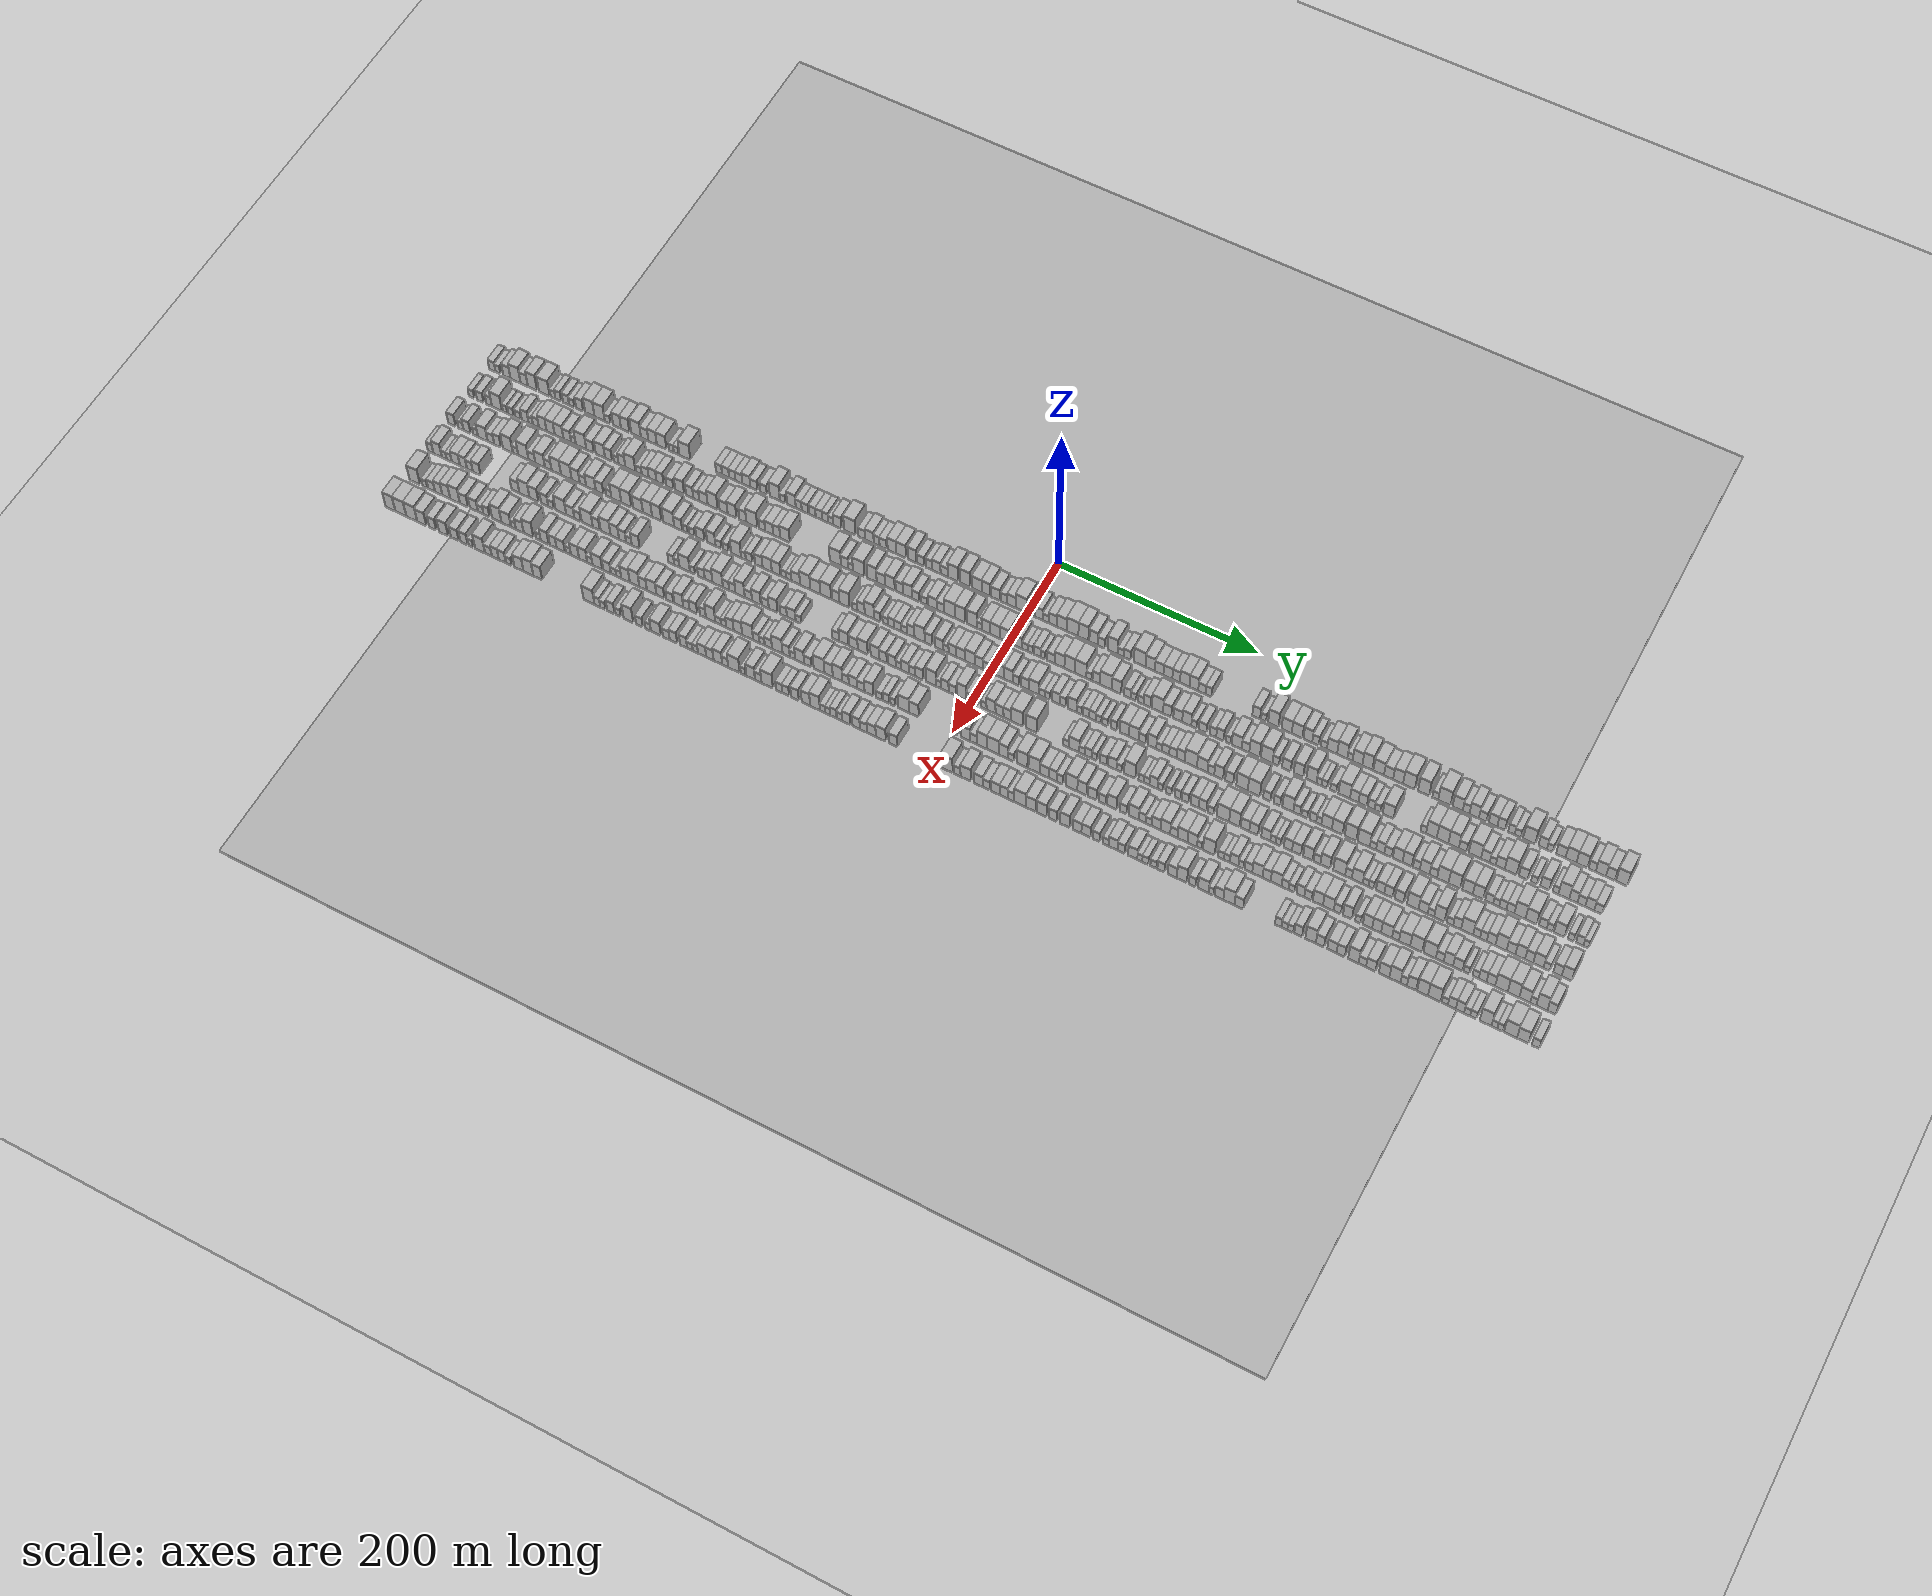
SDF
<?xml version="1.0" encoding="utf-8"?>

<sdf version="1.6">

   <world name="default">

      <gui fullscreen="0">

         <camera name="user_camera">

            <pose>-15 0 4.57585 0 0 0</pose>

            <view_controller>orbit</view_controller>

         </camera>

      </gui>

      <scene>

         <sky>

           <clouds>

             <speed>12</speed>

           </clouds>

         </sky>

         <ambient>0.4 0.4 0.4 1</ambient>

         <background>0.7 0.7 0.7 1</background>

         <shadows>1</shadows>

      </scene>

      <gravity>0 0 -9.8066</gravity>

      <magnetic_field>6e-06 2.3e-05 -4.2e-05</magnetic_field>

      <physics default="0" name="default_physics" type="ode">

         <ode>

            <solver>

               <type>quick</type>

               <iters>10</iters>

               <sor>1.0</sor>

               <use_dynamic_moi_rescaling>0</use_dynamic_moi_rescaling>

            </solver>

            <constraints>

               <cfm>0</cfm>

               <erp>0.2</erp>

               <contact_max_correcting_vel>100</contact_max_correcting_vel>

               <contact_surface_layer>0.001</contact_surface_layer>

            </constraints>

         </ode>

         <max_step_size>0.004</max_step_size>

         <real_time_factor>1</real_time_factor>

         <real_time_update_rate>250</real_time_update_rate>

      </physics>

      <light name="sun" type="directional">

         <cast_shadows>1</cast_shadows>

         <pose>0 0 10 0 0 0</pose>

         <diffuse>0.8 0.8 0.8 1</diffuse>

         <specular>0.2 0.2 0.2 1</specular>

         <attenuation>

            <range>1000</range>

            <constant>0.9</constant>

            <linear>0.01</linear>

            <quadratic>0.001</quadratic>

         </attenuation>

         <direction>-0.5 0.1 -0.9</direction>

      </light>

      <include>

         <name>ground_plane_1</name>

         <uri>model://HANNAS_ground_plane</uri>

         <pose>0 0 0  0 0 0</pose>

      </include>

      <include>

         <name>ground_plane_2</name>

         <uri>model://HANNAS_ground_plane</uri>

         <pose>100 0 0  0 0 0</pose>

      </include>

      <model name="building_1">

         <static>1</static>

         <pose frame="">50.0000 -566.4650 0 0.000000 0.000000 0.000000</pose>

         <link name="link">

            <pose frame="">0 0 7.50 0 0 0</pose>

            <collision name="collision">

               <geometry>

                  <box>

                     <size>20.0000 7.0700 15.0000</size>

                  </box>

               </geometry>

               <max_contacts>10</max_contacts>

               <surface>

                  <contact>

                     <ode/>

                  </contact>

                  <bounce/>

                  <friction>

                     <torsional>

                        <ode/>

                     </torsional>

                     <ode/>

                  </friction>

               </surface>

            </collision>

            <visual name="visual">

               <cast_shadows>0</cast_shadows>

               <geometry>

                  <box>

                     <size>20.0000 7.0700 15.0000</size>

                  </box>

               </geometry>

               <material>

                  <script>

                     <uri>model://HANNAS_wall/materials/scripts</uri>

                     <uri>model://HANNAS_wall/materials/textures</uri>

                     <name>vrc/HANNAS_wall</name>

                  </script>

               </material>

            </visual>

            <self_collide>0</self_collide>

            <enable_wind>0</enable_wind>

            <kinematic>0</kinematic>

         </link>

      </model>

      <model name="building_2">

         <static>1</static>

         <pose frame="">50.0000 -560.2530 0 0.000000 0.000000 0.000000</pose>

         <link name="link">

            <pose frame="">0 0 6.00 0 0 0</pose>

            <collision name="collision">

               <geometry>

                  <box>

                     <size>20.0000 5.3539 12.0000</size>

                  </box>

               </geometry>

               <max_contacts>10</max_contacts>

               <surface>

                  <contact>

                     <ode/>

                  </contact>

                  <bounce/>

                  <friction>

                     <torsional>

                        <ode/>

                     </torsional>

                     <ode/>

                  </friction>

               </surface>

            </collision>

            <visual name="visual">

               <cast_shadows>0</cast_shadows>

               <geometry>

                  <box>

                     <size>20.0000 5.3539 12.0000</size>

                  </box>

               </geometry>

               <material>

                  <script>

                     <uri>model://HANNAS_wall/materials/scripts</uri>

                     <uri>model://HANNAS_wall/materials/textures</uri>

                     <name>vrc/HANNAS_wall</name>

                  </script>

               </material>

            </visual>

            <self_collide>0</self_collide>

            <enable_wind>0</enable_wind>

            <kinematic>0</kinematic>

         </link>

      </model>

      <model name="building_3">

         <static>1</static>

         <pose frame="">50.0000 -550.4912 0 0.000000 0.000000 0.000000</pose>

         <link name="link">

            <pose frame="">0 0 9.00 0 0 0</pose>

            <collision name="collision">

               <geometry>

                  <box>

                     <size>20.0000 8.1696 18.0000</size>

                  </box>

               </geometry>

               <max_contacts>10</max_contacts>

               <surface>

                  <contact>

                     <ode/>

                  </contact>

                  <bounce/>

                  <friction>

                     <torsional>

                        <ode/>

                     </torsional>

                     <ode/>

                  </friction>

               </surface>

            </collision>

            <visual name="visual">

               <cast_shadows>0</cast_shadows>

               <geometry>

                  <box>

                     <size>20.0000 8.1696 18.0000</size>

                  </box>

               </geometry>

               <material>

                  <script>

                     <uri>model://HANNAS_wall/materials/scripts</uri>

                     <uri>model://HANNAS_wall/materials/textures</uri>

                     <name>vrc/HANNAS_wall</name>

                  </script>

               </material>

            </visual>

            <self_collide>0</self_collide>

            <enable_wind>0</enable_wind>

            <kinematic>0</kinematic>

         </link>

      </model>

      <model name="building_4">

         <static>1</static>

         <pose frame="">50.0000 -540.8610 0 0.000000 0.000000 0.000000</pose>

         <link name="link">

            <pose frame="">0 0 12.00 0 0 0</pose>

            <collision name="collision">

               <geometry>

                  <box>

                     <size>20.0000 11.0907 24.0000</size>

                  </box>

               </geometry>

               <max_contacts>10</max_contacts>

               <surface>

                  <contact>

                     <ode/>

                  </contact>

                  <bounce/>

                  <friction>

                     <torsional>

                        <ode/>

                     </torsional>

                     <ode/>

                  </friction>

               </surface>

            </collision>

            <visual name="visual">

               <cast_shadows>0</cast_shadows>

               <geometry>

                  <box>

                     <size>20.0000 11.0907 24.0000</size>

                  </box>

               </geometry>

               <material>

                  <script>

                     <uri>model://HANNAS_wall/materials/scripts</uri>

                     <uri>model://HANNAS_wall/materials/textures</uri>

                     <name>vrc/HANNAS_wall</name>

                  </script>

               </material>

            </visual>

            <self_collide>0</self_collide>

            <enable_wind>0</enable_wind>

            <kinematic>0</kinematic>

         </link>

      </model>

      <model name="building_5">

         <static>1</static>

         <pose frame="">50.0000 -531.4017 0 0.000000 0.000000 0.000000</pose>

         <link name="link">

            <pose frame="">0 0 9.00 0 0 0</pose>

            <collision name="collision">

               <geometry>

                  <box>

                     <size>20.0000 7.8280 18.0000</size>

                  </box>

               </geometry>

               <max_contacts>10</max_contacts>

               <surface>

                  <contact>

                     <ode/>

                  </contact>

                  <bounce/>

                  <friction>

                     <torsional>

                        <ode/>

                     </torsional>

                     <ode/>

                  </friction>

               </surface>

            </collision>

            <visual name="visual">

               <cast_shadows>0</cast_shadows>

               <geometry>

                  <box>

                     <size>20.0000 7.8280 18.0000</size>

                  </box>

               </geometry>

               <material>

                  <script>

                     <uri>model://HANNAS_wall/materials/scripts</uri>

                     <uri>model://HANNAS_wall/materials/textures</uri>

                     <name>vrc/HANNAS_wall</name>

                  </script>

               </material>

            </visual>

            <self_collide>0</self_collide>

            <enable_wind>0</enable_wind>

            <kinematic>0</kinematic>

         </link>

      </model>

      <model name="building_6">

         <static>1</static>

         <pose frame="">50.0000 -522.3789 0 0.000000 0.000000 0.000000</pose>

         <link name="link">

            <pose frame="">0 0 12.00 0 0 0</pose>

            <collision name="collision">

               <geometry>

                  <box>

                     <size>20.0000 10.2176 24.0000</size>

                  </box>

               </geometry>

               <max_contacts>10</max_contacts>

               <surface>

                  <contact>

                     <ode/>

                  </contact>

                  <bounce/>

                  <friction>

                     <torsional>

                        <ode/>

                     </torsional>

                     <ode/>

                  </friction>

               </surface>

            </collision>

            <visual name="visual">

               <cast_shadows>0</cast_shadows>

               <geometry>

                  <box>

                     <size>20.0000 10.2176 24.0000</size>

                  </box>

               </geometry>

               <material>

                  <script>

                     <uri>model://HANNAS_wall/materials/scripts</uri>

                     <uri>model://HANNAS_wall/materials/textures</uri>

                     <name>vrc/HANNAS_wall</name>

                  </script>

               </material>

            </visual>

            <self_collide>0</self_collide>

            <enable_wind>0</enable_wind>

            <kinematic>0</kinematic>

         </link>

      </model>

      <model name="building_7">

         <static>1</static>

         <pose frame="">50.0000 -509.3634 0 0.000000 0.000000 0.000000</pose>

         <link name="link">

            <pose frame="">0 0 12.00 0 0 0</pose>

            <collision name="collision">

               <geometry>

                  <box>

                     <size>20.0000 11.8134 24.0000</size>

                  </box>

               </geometry>

               <max_contacts>10</max_contacts>

               <surface>

                  <contact>

                     <ode/>

                  </contact>

                  <bounce/>

                  <friction>

                     <torsional>

                        <ode/>

                     </torsional>

                     <ode/>

                  </friction>

               </surface>

            </collision>

            <visual name="visual">

               <cast_shadows>0</cast_shadows>

               <geometry>

                  <box>

                     <size>20.0000 11.8134 24.0000</size>

                  </box>

               </geometry>

               <material>

                  <script>

                     <uri>model://HANNAS_wall/materials/scripts</uri>

                     <uri>model://HANNAS_wall/materials/textures</uri>

                     <name>vrc/HANNAS_wall</name>

                  </script>

               </material>

            </visual>

            <self_collide>0</self_collide>

            <enable_wind>0</enable_wind>

            <kinematic>0</kinematic>

         </link>

      </model>

      <model name="building_8">

         <static>1</static>

         <pose frame="">50.0000 -499.8393 0 0.000000 0.000000 0.000000</pose>

         <link name="link">

            <pose frame="">0 0 6.00 0 0 0</pose>

            <collision name="collision">

               <geometry>

                  <box>

                     <size>20.0000 5.2347 12.0000</size>

                  </box>

               </geometry>

               <max_contacts>10</max_contacts>

               <surface>

                  <contact>

                     <ode/>

                  </contact>

                  <bounce/>

                  <friction>

                     <torsional>

                        <ode/>

                     </torsional>

                     <ode/>

                  </friction>

               </surface>

            </collision>

            <visual name="visual">

               <cast_shadows>0</cast_shadows>

               <geometry>

                  <box>

                     <size>20.0000 5.2347 12.0000</size>

                  </box>

               </geometry>

               <material>

                  <script>

                     <uri>model://HANNAS_wall/materials/scripts</uri>

                     <uri>model://HANNAS_wall/materials/textures</uri>

                     <name>vrc/HANNAS_wall</name>

                  </script>

               </material>

            </visual>

            <self_collide>0</self_collide>

            <enable_wind>0</enable_wind>

            <kinematic>0</kinematic>

         </link>

      </model>

      <model name="building_9">

         <static>1</static>

         <pose frame="">50.0000 -494.1050 0 0.000000 0.000000 0.000000</pose>

         <link name="link">

            <pose frame="">0 0 7.50 0 0 0</pose>

            <collision name="collision">

               <geometry>

                  <box>

                     <size>20.0000 6.2340 15.0000</size>

                  </box>

               </geometry>

               <max_contacts>10</max_contacts>

               <surface>

                  <contact>

                     <ode/>

                  </contact>

                  <bounce/>

                  <friction>

                     <torsional>

                        <ode/>

                     </torsional>

                     <ode/>

                  </friction>

               </surface>

            </collision>

            <visual name="visual">

               <cast_shadows>0</cast_shadows>

               <geometry>

                  <box>

                     <size>20.0000 6.2340 15.0000</size>

                  </box>

               </geometry>

               <material>

                  <script>

                     <uri>model://HANNAS_wall/materials/scripts</uri>

                     <uri>model://HANNAS_wall/materials/textures</uri>

                     <name>vrc/HANNAS_wall</name>

                  </script>

               </material>

            </visual>

            <self_collide>0</self_collide>

            <enable_wind>0</enable_wind>

            <kinematic>0</kinematic>

         </link>

      </model>

      <model name="building_10">

         <static>1</static>

         <pose frame="">50.0000 -485.5858 0 0.000000 0.000000 0.000000</pose>

         <link name="link">

            <pose frame="">0 0 7.50 0 0 0</pose>

            <collision name="collision">

               <geometry>

                  <box>

                     <size>20.0000 6.8043 15.0000</size>

                  </box>

               </geometry>

               <max_contacts>10</max_contacts>

               <surface>

                  <contact>

                     <ode/>

                  </contact>

                  <bounce/>

                  <friction>

                     <torsional>

                        <ode/>

                     </torsional>

                     <ode/>

                  </friction>

               </surface>

            </collision>

            <visual name="visual">

               <cast_shadows>0</cast_shadows>

               <geometry>

                  <box>

                     <size>20.0000 6.8043 15.0000</size>

                  </box>

               </geometry>

               <material>

                  <script>

                     <uri>model://HANNAS_wall/materials/scripts</uri>

                     <uri>model://HANNAS_wall/materials/textures</uri>

                     <name>vrc/HANNAS_wall</name>

                  </script>

               </material>

            </visual>

            <self_collide>0</self_collide>

            <enable_wind>0</enable_wind>

            <kinematic>0</kinematic>

         </link>

      </model>

      <model name="building_11">

         <static>1</static>

         <pose frame="">50.0000 -479.3837 0 0.000000 0.000000 0.000000</pose>

         <link name="link">

            <pose frame="">0 0 6.00 0 0 0</pose>

            <collision name="collision">

               <geometry>

                  <box>

                     <size>20.0000 5.6000 12.0000</size>

                  </box>

               </geometry>

               <max_contacts>10</max_contacts>

               <surface>

                  <contact>

                     <ode/>

                  </contact>

                  <bounce/>

                  <friction>

                     <torsional>

                        <ode/>

                     </torsional>

                     <ode/>

                  </friction>

               </surface>

            </collision>

            <visual name="visual">

               <cast_shadows>0</cast_shadows>

               <geometry>

                  <box>

                     <size>20.0000 5.6000 12.0000</size>

                  </box>

               </geometry>

               <material>

                  <script>

                     <uri>model://HANNAS_wall/materials/scripts</uri>

                     <uri>model://HANNAS_wall/materials/textures</uri>

                     <name>vrc/HANNAS_wall</name>

                  </script>

               </material>

            </visual>

            <self_collide>0</self_collide>

            <enable_wind>0</enable_wind>

            <kinematic>0</kinematic>

         </link>

      </model>

      <model name="building_12">

         <static>1</static>

         <pose frame="">50.0000 -470.7402 0 0.000000 0.000000 0.000000</pose>

         <link name="link">

            <pose frame="">0 0 9.00 0 0 0</pose>

            <collision name="collision">

               <geometry>

                  <box>

                     <size>20.0000 7.6870 18.0000</size>

                  </box>

               </geometry>

               <max_contacts>10</max_contacts>

               <surface>

                  <contact>

                     <ode/>

                  </contact>

                  <bounce/>

                  <friction>

                     <torsional>

                        <ode/>

                     </torsional>

                     <ode/>

                  </friction>

               </surface>

            </collision>

            <visual name="visual">

               <cast_shadows>0</cast_shadows>

               <geometry>

                  <box>

                     <size>20.0000 7.6870 18.0000</size>

                  </box>

               </geometry>

               <material>

                  <script>

                     <uri>model://HANNAS_wall/materials/scripts</uri>

                     <uri>model://HANNAS_wall/materials/textures</uri>

                     <name>vrc/HANNAS_wall</name>

                  </script>

               </material>

            </visual>

            <self_collide>0</self_collide>

            <enable_wind>0</enable_wind>

            <kinematic>0</kinematic>

         </link>

      </model>

      <model name="building_13">

         <static>1</static>

         <pose frame="">50.0000 -459.7438 0 0.000000 0.000000 0.000000</pose>

         <link name="link">

            <pose frame="">0 0 12.00 0 0 0</pose>

            <collision name="collision">

               <geometry>

                  <box>

                     <size>20.0000 10.3056 24.0000</size>

                  </box>

               </geometry>

               <max_contacts>10</max_contacts>

               <surface>

                  <contact>

                     <ode/>

                  </contact>

                  <bounce/>

                  <friction>

                     <torsional>

                        <ode/>

                     </torsional>

                     <ode/>

                  </friction>

               </surface>

            </collision>

            <visual name="visual">

               <cast_shadows>0</cast_shadows>

               <geometry>

                  <box>

                     <size>20.0000 10.3056 24.0000</size>

                  </box>

               </geometry>

               <material>

                  <script>

                     <uri>model://HANNAS_wall/materials/scripts</uri>

                     <uri>model://HANNAS_wall/materials/textures</uri>

                     <name>vrc/HANNAS_wall</name>

                  </script>

               </material>

            </visual>

            <self_collide>0</self_collide>

            <enable_wind>0</enable_wind>

            <kinematic>0</kinematic>

         </link>

      </model>

      <model name="building_14">

         <static>1</static>

         <pose frame="">50.0000 -449.0146 0 0.000000 0.000000 0.000000</pose>

         <link name="link">

            <pose frame="">0 0 12.00 0 0 0</pose>

            <collision name="collision">

               <geometry>

                  <box>

                     <size>20.0000 11.1530 24.0000</size>

                  </box>

               </geometry>

               <max_contacts>10</max_contacts>

               <surface>

                  <contact>

                     <ode/>

                  </contact>

                  <bounce/>

                  <friction>

                     <torsional>

                        <ode/>

                     </torsional>

                     <ode/>

                  </friction>

               </surface>

            </collision>

            <visual name="visual">

               <cast_shadows>0</cast_shadows>

               <geometry>

                  <box>

                     <size>20.0000 11.1530 24.0000</size>

                  </box>

               </geometry>

               <material>

                  <script>

                     <uri>model://HANNAS_wall/materials/scripts</uri>

                     <uri>model://HANNAS_wall/materials/textures</uri>

                     <name>vrc/HANNAS_wall</name>

                  </script>

               </material>

            </visual>

            <self_collide>0</self_collide>

            <enable_wind>0</enable_wind>

            <kinematic>0</kinematic>

         </link>

      </model>

      <model name="building_15">

         <static>1</static>

         <pose frame="">50.0000 -440.5052 0 0.000000 0.000000 0.000000</pose>

         <link name="link">

            <pose frame="">0 0 6.00 0 0 0</pose>

            <collision name="collision">

               <geometry>

                  <box>

                     <size>20.0000 5.8657 12.0000</size>

                  </box>

               </geometry>

               <max_contacts>10</max_contacts>

               <surface>

                  <contact>

                     <ode/>

                  </contact>

                  <bounce/>

                  <friction>

                     <torsional>

                        <ode/>

                     </torsional>

                     <ode/>

                  </friction>

               </surface>

            </collision>

            <visual name="visual">

               <cast_shadows>0</cast_shadows>

               <geometry>

                  <box>

                     <size>20.0000 5.8657 12.0000</size>

                  </box>

               </geometry>

               <material>

                  <script>

                     <uri>model://HANNAS_wall/materials/scripts</uri>

                     <uri>model://HANNAS_wall/materials/textures</uri>

                     <name>vrc/HANNAS_wall</name>

                  </script>

               </material>

            </visual>

            <self_collide>0</self_collide>

            <enable_wind>0</enable_wind>

            <kinematic>0</kinematic>

         </link>

      </model>

      <model name="building_16">

         <static>1</static>

         <pose frame="">50.0000 -430.2439 0 0.000000 0.000000 0.000000</pose>

         <link name="link">

            <pose frame="">0 0 10.50 0 0 0</pose>

            <collision name="collision">

               <geometry>

                  <box>

                     <size>20.0000 8.6569 21.0000</size>

                  </box>

               </geometry>

               <max_contacts>10</max_contacts>

               <surface>

                  <contact>

                     <ode/>

                  </contact>

                  <bounce/>

                  <friction>

                     <torsional>

                        <ode/>

                     </torsional>

                     <ode/>

                  </friction>

               </surface>

            </collision>

            <visual name="visual">

               <cast_shadows>0</cast_shadows>

               <geometry>

                  <box>

                     <size>20.0000 8.6569 21.0000</size>

                  </box>

               </geometry>

               <material>

                  <script>

                     <uri>model://HANNAS_wall/materials/scripts</uri>

                     <uri>model://HANNAS_wall/materials/textures</uri>

                     <name>vrc/HANNAS_wall</name>

                  </script>

               </material>

            </visual>

            <self_collide>0</self_collide>

            <enable_wind>0</enable_wind>

            <kinematic>0</kinematic>

         </link>

      </model>

      <model name="building_17">

         <static>1</static>

         <pose frame="">50.0000 -421.3993 0 0.000000 0.000000 0.000000</pose>

         <link name="link">

            <pose frame="">0 0 10.50 0 0 0</pose>

            <collision name="collision">

               <geometry>

                  <box>

                     <size>20.0000 9.0324 21.0000</size>

                  </box>

               </geometry>

               <max_contacts>10</max_contacts>

               <surface>

                  <contact>

                     <ode/>

                  </contact>

                  <bounce/>

                  <friction>

                     <torsional>

                        <ode/>

                     </torsional>

                     <ode/>

                  </friction>

               </surface>

            </collision>

            <visual name="visual">

               <cast_shadows>0</cast_shadows>

               <geometry>

                  <box>

                     <size>20.0000 9.0324 21.0000</size>

                  </box>

               </geometry>

               <material>

                  <script>

                     <uri>model://HANNAS_wall/materials/scripts</uri>

                     <uri>model://HANNAS_wall/materials/textures</uri>

                     <name>vrc/HANNAS_wall</name>

                  </script>

               </material>

            </visual>

            <self_collide>0</self_collide>

            <enable_wind>0</enable_wind>

            <kinematic>0</kinematic>

         </link>

      </model>

      <model name="building_18">

         <static>1</static>

         <pose frame="">50.0000 -409.6455 0 0.000000 0.000000 0.000000</pose>

         <link name="link">

            <pose frame="">0 0 12.00 0 0 0</pose>

            <collision name="collision">

               <geometry>

                  <box>

                     <size>20.0000 10.4752 24.0000</size>

                  </box>

               </geometry>

               <max_contacts>10</max_contacts>

               <surface>

                  <contact>

                     <ode/>

                  </contact>

                  <bounce/>

                  <friction>

                     <torsional>

                        <ode/>

                     </torsional>

                     <ode/>

                  </friction>

               </surface>

            </collision>

            <visual name="visual">

               <cast_shadows>0</cast_shadows>

               <geometry>

                  <box>

                     <size>20.0000 10.4752 24.0000</size>

                  </box>

               </geometry>

               <material>

                  <script>

                     <uri>model://HANNAS_wall/materials/scripts</uri>

                     <uri>model://HANNAS_wall/materials/textures</uri>

                     <name>vrc/HANNAS_wall</name>

                  </script>

               </material>

            </visual>

            <self_collide>0</self_collide>

            <enable_wind>0</enable_wind>

            <kinematic>0</kinematic>

         </link>

      </model>

      <model name="building_19">

         <static>1</static>

         <pose frame="">50.0000 -400.4107 0 0.000000 0.000000 0.000000</pose>

         <link name="link">

            <pose frame="">0 0 9.00 0 0 0</pose>

            <collision name="collision">

               <geometry>

                  <box>

                     <size>20.0000 7.9944 18.0000</size>

                  </box>

               </geometry>

               <max_contacts>10</max_contacts>

               <surface>

                  <contact>

                     <ode/>

                  </contact>

                  <bounce/>

                  <friction>

                     <torsional>

                        <ode/>

                     </torsional>

                     <ode/>

                  </friction>

               </surface>

            </collision>

            <visual name="visual">

               <cast_shadows>0</cast_shadows>

               <geometry>

                  <box>

                     <size>20.0000 7.9944 18.0000</size>

                  </box>

               </geometry>

               <material>

                  <script>

                     <uri>model://HANNAS_wall/materials/scripts</uri>

                     <uri>model://HANNAS_wall/materials/textures</uri>

                     <name>vrc/HANNAS_wall</name>

                  </script>

               </material>

            </visual>

            <self_collide>0</self_collide>

            <enable_wind>0</enable_wind>

            <kinematic>0</kinematic>

         </link>

      </model>

      <model name="building_20">

         <static>1</static>

         <pose frame="">50.0000 -391.8790 0 0.000000 0.000000 0.000000</pose>

         <link name="link">

            <pose frame="">0 0 10.50 0 0 0</pose>

            <collision name="collision">

               <geometry>

                  <box>

                     <size>20.0000 9.0690 21.0000</size>

                  </box>

               </geometry>

               <max_contacts>10</max_contacts>

               <surface>

                  <contact>

                     <ode/>

                  </contact>

                  <bounce/>

                  <friction>

                     <torsional>

                        <ode/>

                     </torsional>

                     <ode/>

                  </friction>

               </surface>

            </collision>

            <visual name="visual">

               <cast_shadows>0</cast_shadows>

               <geometry>

                  <box>

                     <size>20.0000 9.0690 21.0000</size>

                  </box>

               </geometry>

               <material>

                  <script>

                     <uri>model://HANNAS_wall/materials/scripts</uri>

                     <uri>model://HANNAS_wall/materials/textures</uri>

                     <name>vrc/HANNAS_wall</name>

                  </script>

               </material>

            </visual>

            <self_collide>0</self_collide>

            <enable_wind>0</enable_wind>

            <kinematic>0</kinematic>

         </link>

      </model>

      <model name="building_21">

         <static>1</static>

         <pose frame="">50.0000 -382.1680 0 0.000000 0.000000 0.000000</pose>

         <link name="link">

            <pose frame="">0 0 10.50 0 0 0</pose>

            <collision name="collision">

               <geometry>

                  <box>

                     <size>20.0000 10.3531 21.0000</size>

                  </box>

               </geometry>

               <max_contacts>10</max_contacts>

               <surface>

                  <contact>

                     <ode/>

                  </contact>

                  <bounce/>

                  <friction>

                     <torsional>

                        <ode/>

                     </torsional>

                     <ode/>

                  </friction>

               </surface>

            </collision>

            <visual name="visual">

               <cast_shadows>0</cast_shadows>

               <geometry>

                  <box>

                     <size>20.0000 10.3531 21.0000</size>

                  </box>

               </geometry>

               <material>

                  <script>

                     <uri>model://HANNAS_wall/materials/scripts</uri>

                     <uri>model://HANNAS_wall/materials/textures</uri>

                     <name>vrc/HANNAS_wall</name>

                  </script>

               </material>

            </visual>

            <self_collide>0</self_collide>

            <enable_wind>0</enable_wind>

            <kinematic>0</kinematic>

         </link>

      </model>

      <model name="building_22">

         <static>1</static>

         <pose frame="">50.0000 -371.5617 0 0.000000 0.000000 0.000000</pose>

         <link name="link">

            <pose frame="">0 0 6.00 0 0 0</pose>

            <collision name="collision">

               <geometry>

                  <box>

                     <size>20.0000 4.8596 12.0000</size>

                  </box>

               </geometry>

               <max_contacts>10</max_contacts>

               <surface>

                  <contact>

                     <ode/>

                  </contact>

                  <bounce/>

                  <friction>

                     <torsional>

                        <ode/>

                     </torsional>

                     <ode/>

                  </friction>

               </surface>

            </collision>

            <visual name="visual">

               <cast_shadows>0</cast_shadows>

               <geometry>

                  <box>

                     <size>20.0000 4.8596 12.0000</size>

                  </box>

               </geometry>

               <material>

                  <script>

                     <uri>model://HANNAS_wall/materials/scripts</uri>

                     <uri>model://HANNAS_wall/materials/textures</uri>

                     <name>vrc/HANNAS_wall</name>

                  </script>

               </material>

            </visual>

            <self_collide>0</self_collide>

            <enable_wind>0</enable_wind>

            <kinematic>0</kinematic>

         </link>

      </model>

      <model name="building_23">

         <static>1</static>

         <pose frame="">50.0000 -366.6226 0 0.000000 0.000000 0.000000</pose>

         <link name="link">

            <pose frame="">0 0 6.00 0 0 0</pose>

            <collision name="collision">

               <geometry>

                  <box>

                     <size>20.0000 5.0186 12.0000</size>

                  </box>

               </geometry>

               <max_contacts>10</max_contacts>

               <surface>

                  <contact>

                     <ode/>

                  </contact>

                  <bounce/>

                  <friction>

                     <torsional>

                        <ode/>

                     </torsional>

                     <ode/>

                  </friction>

               </surface>

            </collision>

            <visual name="visual">

               <cast_shadows>0</cast_shadows>

               <geometry>

                  <box>

                     <size>20.0000 5.0186 12.0000</size>

                  </box>

               </geometry>

               <material>

                  <script>

                     <uri>model://HANNAS_wall/materials/scripts</uri>

                     <uri>model://HANNAS_wall/materials/textures</uri>

                     <name>vrc/HANNAS_wall</name>

                  </script>

               </material>

            </visual>

            <self_collide>0</self_collide>

            <enable_wind>0</enable_wind>

            <kinematic>0</kinematic>

         </link>

      </model>

      <model name="building_24">

         <static>1</static>

         <pose frame="">50.0000 -357.2989 0 0.000000 0.000000 0.000000</pose>

         <link name="link">

            <pose frame="">0 0 12.00 0 0 0</pose>

            <collision name="collision">

               <geometry>

                  <box>

                     <size>20.0000 11.6288 24.0000</size>

                  </box>

               </geometry>

               <max_contacts>10</max_contacts>

               <surface>

                  <contact>

                     <ode/>

                  </contact>

                  <bounce/>

                  <friction>

                     <torsional>

                        <ode/>

                     </torsional>

                     <ode/>

                  </friction>

               </surface>

            </collision>

            <visual name="visual">

               <cast_shadows>0</cast_shadows>

               <geometry>

                  <box>

                     <size>20.0000 11.6288 24.0000</size>

                  </box>

               </geometry>

               <material>

                  <script>

                     <uri>model://HANNAS_wall/materials/scripts</uri>

                     <uri>model://HANNAS_wall/materials/textures</uri>

                     <name>vrc/HANNAS_wall</name>

                  </script>

               </material>

            </visual>

            <self_collide>0</self_collide>

            <enable_wind>0</enable_wind>

            <kinematic>0</kinematic>

         </link>

      </model>

      <model name="building_25">

         <static>1</static>

         <pose frame="">50.0000 -320.8477 0 0.000000 0.000000 0.000000</pose>

         <link name="link">

            <pose frame="">0 0 7.50 0 0 0</pose>

            <collision name="collision">

               <geometry>

                  <box>

                     <size>20.0000 6.4245 15.0000</size>

                  </box>

               </geometry>

               <max_contacts>10</max_contacts>

               <surface>

                  <contact>

                     <ode/>

                  </contact>

                  <bounce/>

                  <friction>

                     <torsional>

                        <ode/>

                     </torsional>

                     <ode/>

                  </friction>

               </surface>

            </collision>

            <visual name="visual">

               <cast_shadows>0</cast_shadows>

               <geometry>

                  <box>

                     <size>20.0000 6.4245 15.0000</size>

                  </box>

               </geometry>

               <material>

                  <script>

                     <uri>model://HANNAS_wall/materials/scripts</uri>

                     <uri>model://HANNAS_wall/materials/textures</uri>

                     <name>vrc/HANNAS_wall</name>

                  </script>

               </material>

            </visual>

            <self_collide>0</self_collide>

            <enable_wind>0</enable_wind>

            <kinematic>0</kinematic>

         </link>

      </model>

      <model name="building_26">

         <static>1</static>

         <pose frame="">50.0000 -313.9366 0 0.000000 0.000000 0.000000</pose>

         <link name="link">

            <pose frame="">0 0 7.50 0 0 0</pose>

            <collision name="collision">

               <geometry>

                  <box>

                     <size>20.0000 7.3976 15.0000</size>

                  </box>

               </geometry>

               <max_contacts>10</max_contacts>

               <surface>

                  <contact>

                     <ode/>

                  </contact>

                  <bounce/>

                  <friction>

                     <torsional>

                        <ode/>

                     </torsional>

                     <ode/>

                  </friction>

               </surface>

            </collision>

            <visual name="visual">

               <cast_shadows>0</cast_shadows>

               <geometry>

                  <box>

                     <size>20.0000 7.3976 15.0000</size>

                  </box>

               </geometry>

               <material>

                  <script>

                     <uri>model://HANNAS_wall/materials/scripts</uri>

                     <uri>model://HANNAS_wall/materials/textures</uri>

                     <name>vrc/HANNAS_wall</name>

                  </script>

               </material>

            </visual>

            <self_collide>0</self_collide>

            <enable_wind>0</enable_wind>

            <kinematic>0</kinematic>

         </link>

      </model>

      <model name="building_27">

         <static>1</static>

         <pose frame="">50.0000 -306.7910 0 0.000000 0.000000 0.000000</pose>

         <link name="link">

            <pose frame="">0 0 7.50 0 0 0</pose>

            <collision name="collision">

               <geometry>

                  <box>

                     <size>20.0000 6.8936 15.0000</size>

                  </box>

               </geometry>

               <max_contacts>10</max_contacts>

               <surface>

                  <contact>

                     <ode/>

                  </contact>

                  <bounce/>

                  <friction>

                     <torsional>

                        <ode/>

                     </torsional>

                     <ode/>

                  </friction>

               </surface>

            </collision>

            <visual name="visual">

               <cast_shadows>0</cast_shadows>

               <geometry>

                  <box>

                     <size>20.0000 6.8936 15.0000</size>

                  </box>

               </geometry>

               <material>

                  <script>

                     <uri>model://HANNAS_wall/materials/scripts</uri>

                     <uri>model://HANNAS_wall/materials/textures</uri>

                     <name>vrc/HANNAS_wall</name>

                  </script>

               </material>

            </visual>

            <self_collide>0</self_collide>

            <enable_wind>0</enable_wind>

            <kinematic>0</kinematic>

         </link>

      </model>

      <model name="building_28">

         <static>1</static>

         <pose frame="">50.0000 -299.7176 0 0.000000 0.000000 0.000000</pose>

         <link name="link">

            <pose frame="">0 0 7.50 0 0 0</pose>

            <collision name="collision">

               <geometry>

                  <box>

                     <size>20.0000 7.2533 15.0000</size>

                  </box>

               </geometry>

               <max_contacts>10</max_contacts>

               <surface>

                  <contact>

                     <ode/>

                  </contact>

                  <bounce/>

                  <friction>

                     <torsional>

                        <ode/>

                     </torsional>

                     <ode/>

                  </friction>

               </surface>

            </collision>

            <visual name="visual">

               <cast_shadows>0</cast_shadows>

               <geometry>

                  <box>

                     <size>20.0000 7.2533 15.0000</size>

                  </box>

               </geometry>

               <material>

                  <script>

                     <uri>model://HANNAS_wall/materials/scripts</uri>

                     <uri>model://HANNAS_wall/materials/textures</uri>

                     <name>vrc/HANNAS_wall</name>

                  </script>

               </material>

            </visual>

            <self_collide>0</self_collide>

            <enable_wind>0</enable_wind>

            <kinematic>0</kinematic>

         </link>

      </model>

      <model name="building_29">

         <static>1</static>

         <pose frame="">50.0000 -291.8006 0 0.000000 0.000000 0.000000</pose>

         <link name="link">

            <pose frame="">0 0 9.00 0 0 0</pose>

            <collision name="collision">

               <geometry>

                  <box>

                     <size>20.0000 8.5807 18.0000</size>

                  </box>

               </geometry>

               <max_contacts>10</max_contacts>

               <surface>

                  <contact>

                     <ode/>

                  </contact>

                  <bounce/>

                  <friction>

                     <torsional>

                        <ode/>

                     </torsional>

                     <ode/>

                  </friction>

               </surface>

            </collision>

            <visual name="visual">

               <cast_shadows>0</cast_shadows>

               <geometry>

                  <box>

                     <size>20.0000 8.5807 18.0000</size>

                  </box>

               </geometry>

               <material>

                  <script>

                     <uri>model://HANNAS_wall/materials/scripts</uri>

                     <uri>model://HANNAS_wall/materials/textures</uri>

                     <name>vrc/HANNAS_wall</name>

                  </script>

               </material>

            </visual>

            <self_collide>0</self_collide>

            <enable_wind>0</enable_wind>

            <kinematic>0</kinematic>

         </link>

      </model>

      <model name="building_30">

         <static>1</static>

         <pose frame="">50.0000 -283.8767 0 0.000000 0.000000 0.000000</pose>

         <link name="link">

            <pose frame="">0 0 7.50 0 0 0</pose>

            <collision name="collision">

               <geometry>

                  <box>

                     <size>20.0000 7.2670 15.0000</size>

                  </box>

               </geometry>

               <max_contacts>10</max_contacts>

               <surface>

                  <contact>

                     <ode/>

                  </contact>

                  <bounce/>

                  <friction>

                     <torsional>

                        <ode/>

                     </torsional>

                     <ode/>

                  </friction>

               </surface>

            </collision>

            <visual name="visual">

               <cast_shadows>0</cast_shadows>

               <geometry>

                  <box>

                     <size>20.0000 7.2670 15.0000</size>

                  </box>

               </geometry>

               <material>

                  <script>

                     <uri>model://HANNAS_wall/materials/scripts</uri>

                     <uri>model://HANNAS_wall/materials/textures</uri>

                     <name>vrc/HANNAS_wall</name>

                  </script>

               </material>

            </visual>

            <self_collide>0</self_collide>

            <enable_wind>0</enable_wind>

            <kinematic>0</kinematic>

         </link>

      </model>

      <model name="building_31">

         <static>1</static>

         <pose frame="">50.0000 -273.7150 0 0.000000 0.000000 0.000000</pose>

         <link name="link">

            <pose frame="">0 0 7.50 0 0 0</pose>

            <collision name="collision">

               <geometry>

                  <box>

                     <size>20.0000 7.0563 15.0000</size>

                  </box>

               </geometry>

               <max_contacts>10</max_contacts>

               <surface>

                  <contact>

                     <ode/>

                  </contact>

                  <bounce/>

                  <friction>

                     <torsional>

                        <ode/>

                     </torsional>

                     <ode/>

                  </friction>

               </surface>

            </collision>

            <visual name="visual">

               <cast_shadows>0</cast_shadows>

               <geometry>

                  <box>

                     <size>20.0000 7.0563 15.0000</size>

                  </box>

               </geometry>

               <material>

                  <script>

                     <uri>model://HANNAS_wall/materials/scripts</uri>

                     <uri>model://HANNAS_wall/materials/textures</uri>

                     <name>vrc/HANNAS_wall</name>

                  </script>

               </material>

            </visual>

            <self_collide>0</self_collide>

            <enable_wind>0</enable_wind>

            <kinematic>0</kinematic>

         </link>

      </model>

      <model name="building_32">

         <static>1</static>

         <pose frame="">50.0000 -261.8928 0 0.000000 0.000000 0.000000</pose>

         <link name="link">

            <pose frame="">0 0 12.00 0 0 0</pose>

            <collision name="collision">

               <geometry>

                  <box>

                     <size>20.0000 10.5881 24.0000</size>

                  </box>

               </geometry>

               <max_contacts>10</max_contacts>

               <surface>

                  <contact>

                     <ode/>

                  </contact>

                  <bounce/>

                  <friction>

                     <torsional>

                        <ode/>

                     </torsional>

                     <ode/>

                  </friction>

               </surface>

            </collision>

            <visual name="visual">

               <cast_shadows>0</cast_shadows>

               <geometry>

                  <box>

                     <size>20.0000 10.5881 24.0000</size>

                  </box>

               </geometry>

               <material>

                  <script>

                     <uri>model://HANNAS_wall/materials/scripts</uri>

                     <uri>model://HANNAS_wall/materials/textures</uri>

                     <name>vrc/HANNAS_wall</name>

                  </script>

               </material>

            </visual>

            <self_collide>0</self_collide>

            <enable_wind>0</enable_wind>

            <kinematic>0</kinematic>

         </link>

      </model>

      <model name="building_33">

         <static>1</static>

         <pose frame="">50.0000 -253.7408 0 0.000000 0.000000 0.000000</pose>

         <link name="link">

            <pose frame="">0 0 6.00 0 0 0</pose>

            <collision name="collision">

               <geometry>

                  <box>

                     <size>20.0000 5.7161 12.0000</size>

                  </box>

               </geometry>

               <max_contacts>10</max_contacts>

               <surface>

                  <contact>

                     <ode/>

                  </contact>

                  <bounce/>

                  <friction>

                     <torsional>

                        <ode/>

                     </torsional>

                     <ode/>

                  </friction>

               </surface>

            </collision>

            <visual name="visual">

               <cast_shadows>0</cast_shadows>

               <geometry>

                  <box>

                     <size>20.0000 5.7161 12.0000</size>

                  </box>

               </geometry>

               <material>

                  <script>

                     <uri>model://HANNAS_wall/materials/scripts</uri>

                     <uri>model://HANNAS_wall/materials/textures</uri>

                     <name>vrc/HANNAS_wall</name>

                  </script>

               </material>

            </visual>

            <self_collide>0</self_collide>

            <enable_wind>0</enable_wind>

            <kinematic>0</kinematic>

         </link>

      </model>

      <model name="building_34">

         <static>1</static>

         <pose frame="">50.0000 -244.2932 0 0.000000 0.000000 0.000000</pose>

         <link name="link">

            <pose frame="">0 0 10.50 0 0 0</pose>

            <collision name="collision">

               <geometry>

                  <box>

                     <size>20.0000 9.1791 21.0000</size>

                  </box>

               </geometry>

               <max_contacts>10</max_contacts>

               <surface>

                  <contact>

                     <ode/>

                  </contact>

                  <bounce/>

                  <friction>

                     <torsional>

                        <ode/>

                     </torsional>

                     <ode/>

                  </friction>

               </surface>

            </collision>

            <visual name="visual">

               <cast_shadows>0</cast_shadows>

               <geometry>

                  <box>

                     <size>20.0000 9.1791 21.0000</size>

                  </box>

               </geometry>

               <material>

                  <script>

                     <uri>model://HANNAS_wall/materials/scripts</uri>

                     <uri>model://HANNAS_wall/materials/textures</uri>

                     <name>vrc/HANNAS_wall</name>

                  </script>

               </material>

            </visual>

            <self_collide>0</self_collide>

            <enable_wind>0</enable_wind>

            <kinematic>0</kinematic>

         </link>

      </model>

      <model name="building_35">

         <static>1</static>

         <pose frame="">50.0000 -236.5688 0 0.000000 0.000000 0.000000</pose>

         <link name="link">

            <pose frame="">0 0 7.50 0 0 0</pose>

            <collision name="collision">

               <geometry>

                  <box>

                     <size>20.0000 6.2698 15.0000</size>

                  </box>

               </geometry>

               <max_contacts>10</max_contacts>

               <surface>

                  <contact>

                     <ode/>

                  </contact>

                  <bounce/>

                  <friction>

                     <torsional>

                        <ode/>

                     </torsional>

                     <ode/>

                  </friction>

               </surface>

            </collision>

            <visual name="visual">

               <cast_shadows>0</cast_shadows>

               <geometry>

                  <box>

                     <size>20.0000 6.2698 15.0000</size>

                  </box>

               </geometry>

               <material>

                  <script>

                     <uri>model://HANNAS_wall/materials/scripts</uri>

                     <uri>model://HANNAS_wall/materials/textures</uri>

                     <name>vrc/HANNAS_wall</name>

                  </script>

               </material>

            </visual>

            <self_collide>0</self_collide>

            <enable_wind>0</enable_wind>

            <kinematic>0</kinematic>

         </link>

      </model>

      <model name="building_36">

         <static>1</static>

         <pose frame="">50.0000 -230.0047 0 0.000000 0.000000 0.000000</pose>

         <link name="link">

            <pose frame="">0 0 7.50 0 0 0</pose>

            <collision name="collision">

               <geometry>

                  <box>

                     <size>20.0000 6.8583 15.0000</size>

                  </box>

               </geometry>

               <max_contacts>10</max_contacts>

               <surface>

                  <contact>

                     <ode/>

                  </contact>

                  <bounce/>

                  <friction>

                     <torsional>

                        <ode/>

                     </torsional>

                     <ode/>

                  </friction>

               </surface>

            </collision>

            <visual name="visual">

               <cast_shadows>0</cast_shadows>

               <geometry>

                  <box>

                     <size>20.0000 6.8583 15.0000</size>

                  </box>

               </geometry>

               <material>

                  <script>

                     <uri>model://HANNAS_wall/materials/scripts</uri>

                     <uri>model://HANNAS_wall/materials/textures</uri>

                     <name>vrc/HANNAS_wall</name>

                  </script>

               </material>

            </visual>

            <self_collide>0</self_collide>

            <enable_wind>0</enable_wind>

            <kinematic>0</kinematic>

         </link>

      </model>

      <model name="building_37">

         <static>1</static>

         <pose frame="">50.0000 -222.2057 0 0.000000 0.000000 0.000000</pose>

         <link name="link">

            <pose frame="">0 0 7.50 0 0 0</pose>

            <collision name="collision">

               <geometry>

                  <box>

                     <size>20.0000 6.7397 15.0000</size>

                  </box>

               </geometry>

               <max_contacts>10</max_contacts>

               <surface>

                  <contact>

                     <ode/>

                  </contact>

                  <bounce/>

                  <friction>

                     <torsional>

                        <ode/>

                     </torsional>

                     <ode/>

                  </friction>

               </surface>

            </collision>

            <visual name="visual">

               <cast_shadows>0</cast_shadows>

               <geometry>

                  <box>

                     <size>20.0000 6.7397 15.0000</size>

                  </box>

               </geometry>

               <material>

                  <script>

                     <uri>model://HANNAS_wall/materials/scripts</uri>

                     <uri>model://HANNAS_wall/materials/textures</uri>

                     <name>vrc/HANNAS_wall</name>

                  </script>

               </material>

            </visual>

            <self_collide>0</self_collide>

            <enable_wind>0</enable_wind>

            <kinematic>0</kinematic>

         </link>

      </model>

      <model name="building_38">

         <static>1</static>

         <pose frame="">50.0000 -215.3865 0 0.000000 0.000000 0.000000</pose>

         <link name="link">

            <pose frame="">0 0 7.50 0 0 0</pose>

            <collision name="collision">

               <geometry>

                  <box>

                     <size>20.0000 6.8987 15.0000</size>

                  </box>

               </geometry>

               <max_contacts>10</max_contacts>

               <surface>

                  <contact>

                     <ode/>

                  </contact>

                  <bounce/>

                  <friction>

                     <torsional>

                        <ode/>

                     </torsional>

                     <ode/>

                  </friction>

               </surface>

            </collision>

            <visual name="visual">

               <cast_shadows>0</cast_shadows>

               <geometry>

                  <box>

                     <size>20.0000 6.8987 15.0000</size>

                  </box>

               </geometry>

               <material>

                  <script>

                     <uri>model://HANNAS_wall/materials/scripts</uri>

                     <uri>model://HANNAS_wall/materials/textures</uri>

                     <name>vrc/HANNAS_wall</name>

                  </script>

               </material>

            </visual>

            <self_collide>0</self_collide>

            <enable_wind>0</enable_wind>

            <kinematic>0</kinematic>

         </link>

      </model>

      <model name="building_39">

         <static>1</static>

         <pose frame="">50.0000 -208.8078 0 0.000000 0.000000 0.000000</pose>

         <link name="link">

            <pose frame="">0 0 7.50 0 0 0</pose>

            <collision name="collision">

               <geometry>

                  <box>

                     <size>20.0000 6.2588 15.0000</size>

                  </box>

               </geometry>

               <max_contacts>10</max_contacts>

               <surface>

                  <contact>

                     <ode/>

                  </contact>

                  <bounce/>

                  <friction>

                     <torsional>

                        <ode/>

                     </torsional>

                     <ode/>

                  </friction>

               </surface>

            </collision>

            <visual name="visual">

               <cast_shadows>0</cast_shadows>

               <geometry>

                  <box>

                     <size>20.0000 6.2588 15.0000</size>

                  </box>

               </geometry>

               <material>

                  <script>

                     <uri>model://HANNAS_wall/materials/scripts</uri>

                     <uri>model://HANNAS_wall/materials/textures</uri>

                     <name>vrc/HANNAS_wall</name>

                  </script>

               </material>

            </visual>

            <self_collide>0</self_collide>

            <enable_wind>0</enable_wind>

            <kinematic>0</kinematic>

         </link>

      </model>

      <model name="building_40">

         <static>1</static>

         <pose frame="">50.0000 -203.0343 0 0.000000 0.000000 0.000000</pose>

         <link name="link">

            <pose frame="">0 0 6.00 0 0 0</pose>

            <collision name="collision">

               <geometry>

                  <box>

                     <size>20.0000 5.2880 12.0000</size>

                  </box>

               </geometry>

               <max_contacts>10</max_contacts>

               <surface>

                  <contact>

                     <ode/>

                  </contact>

                  <bounce/>

                  <friction>

                     <torsional>

                        <ode/>

                     </torsional>

                     <ode/>

                  </friction>

               </surface>

            </collision>

            <visual name="visual">

               <cast_shadows>0</cast_shadows>

               <geometry>

                  <box>

                     <size>20.0000 5.2880 12.0000</size>

                  </box>

               </geometry>

               <material>

                  <script>

                     <uri>model://HANNAS_wall/materials/scripts</uri>

                     <uri>model://HANNAS_wall/materials/textures</uri>

                     <name>vrc/HANNAS_wall</name>

                  </script>

               </material>

            </visual>

            <self_collide>0</self_collide>

            <enable_wind>0</enable_wind>

            <kinematic>0</kinematic>

         </link>

      </model>

      <model name="building_41">

         <static>1</static>

         <pose frame="">50.0000 -196.2881 0 0.000000 0.000000 0.000000</pose>

         <link name="link">

            <pose frame="">0 0 9.00 0 0 0</pose>

            <collision name="collision">

               <geometry>

                  <box>

                     <size>20.0000 8.2043 18.0000</size>

                  </box>

               </geometry>

               <max_contacts>10</max_contacts>

               <surface>

                  <contact>

                     <ode/>

                  </contact>

                  <bounce/>

                  <friction>

                     <torsional>

                        <ode/>

                     </torsional>

                     <ode/>

                  </friction>

               </surface>

            </collision>

            <visual name="visual">

               <cast_shadows>0</cast_shadows>

               <geometry>

                  <box>

                     <size>20.0000 8.2043 18.0000</size>

                  </box>

               </geometry>

               <material>

                  <script>

                     <uri>model://HANNAS_wall/materials/scripts</uri>

                     <uri>model://HANNAS_wall/materials/textures</uri>

                     <name>vrc/HANNAS_wall</name>

                  </script>

               </material>

            </visual>

            <self_collide>0</self_collide>

            <enable_wind>0</enable_wind>

            <kinematic>0</kinematic>

         </link>

      </model>

      <model name="building_42">

         <static>1</static>

         <pose frame="">50.0000 -183.1892 0 0.000000 0.000000 0.000000</pose>

         <link name="link">

            <pose frame="">0 0 12.00 0 0 0</pose>

            <collision name="collision">

               <geometry>

                  <box>

                     <size>20.0000 11.9935 24.0000</size>

                  </box>

               </geometry>

               <max_contacts>10</max_contacts>

               <surface>

                  <contact>

                     <ode/>

                  </contact>

                  <bounce/>

                  <friction>

                     <torsional>

                        <ode/>

                     </torsional>

                     <ode/>

                  </friction>

               </surface>

            </collision>

            <visual name="visual">

               <cast_shadows>0</cast_shadows>

               <geometry>

                  <box>

                     <size>20.0000 11.9935 24.0000</size>

                  </box>

               </geometry>

               <material>

                  <script>

                     <uri>model://HANNAS_wall/materials/scripts</uri>

                     <uri>model://HANNAS_wall/materials/textures</uri>

                     <name>vrc/HANNAS_wall</name>

                  </script>

               </material>

            </visual>

            <self_collide>0</self_collide>

            <enable_wind>0</enable_wind>

            <kinematic>0</kinematic>

         </link>

      </model>

      <model name="building_43">

         <static>1</static>

         <pose frame="">50.0000 -170.7043 0 0.000000 0.000000 0.000000</pose>

         <link name="link">

            <pose frame="">0 0 7.50 0 0 0</pose>

            <collision name="collision">

               <geometry>

                  <box>

                     <size>20.0000 6.9764 15.0000</size>

                  </box>

               </geometry>

               <max_contacts>10</max_contacts>

               <surface>

                  <contact>

                     <ode/>

                  </contact>

                  <bounce/>

                  <friction>

                     <torsional>

                        <ode/>

                     </torsional>

                     <ode/>

                  </friction>

               </surface>

            </collision>

            <visual name="visual">

               <cast_shadows>0</cast_shadows>

               <geometry>

                  <box>

                     <size>20.0000 6.9764 15.0000</size>

                  </box>

               </geometry>

               <material>

                  <script>

                     <uri>model://HANNAS_wall/materials/scripts</uri>

                     <uri>model://HANNAS_wall/materials/textures</uri>

                     <name>vrc/HANNAS_wall</name>

                  </script>

               </material>

            </visual>

            <self_collide>0</self_collide>

            <enable_wind>0</enable_wind>

            <kinematic>0</kinematic>

         </link>

      </model>

      <model name="building_44">

         <static>1</static>

         <pose frame="">50.0000 -162.7735 0 0.000000 0.000000 0.000000</pose>

         <link name="link">

            <pose frame="">0 0 9.00 0 0 0</pose>

            <collision name="collision">

               <geometry>

                  <box>

                     <size>20.0000 8.8852 18.0000</size>

                  </box>

               </geometry>

               <max_contacts>10</max_contacts>

               <surface>

                  <contact>

                     <ode/>

                  </contact>

                  <bounce/>

                  <friction>

                     <torsional>

                        <ode/>

                     </torsional>

                     <ode/>

                  </friction>

               </surface>

            </collision>

            <visual name="visual">

               <cast_shadows>0</cast_shadows>

               <geometry>

                  <box>

                     <size>20.0000 8.8852 18.0000</size>

                  </box>

               </geometry>

               <material>

                  <script>

                     <uri>model://HANNAS_wall/materials/scripts</uri>

                     <uri>model://HANNAS_wall/materials/textures</uri>

                     <name>vrc/HANNAS_wall</name>

                  </script>

               </material>

            </visual>

            <self_collide>0</self_collide>

            <enable_wind>0</enable_wind>

            <kinematic>0</kinematic>

         </link>

      </model>

      <model name="building_45">

         <static>1</static>

         <pose frame="">50.0000 -155.3283 0 0.000000 0.000000 0.000000</pose>

         <link name="link">

            <pose frame="">0 0 7.50 0 0 0</pose>

            <collision name="collision">

               <geometry>

                  <box>

                     <size>20.0000 6.0052 15.0000</size>

                  </box>

               </geometry>

               <max_contacts>10</max_contacts>

               <surface>

                  <contact>

                     <ode/>

                  </contact>

                  <bounce/>

                  <friction>

                     <torsional>

                        <ode/>

                     </torsional>

                     <ode/>

                  </friction>

               </surface>

            </collision>

            <visual name="visual">

               <cast_shadows>0</cast_shadows>

               <geometry>

                  <box>

                     <size>20.0000 6.0052 15.0000</size>

                  </box>

               </geometry>

               <material>

                  <script>

                     <uri>model://HANNAS_wall/materials/scripts</uri>

                     <uri>model://HANNAS_wall/materials/textures</uri>

                     <name>vrc/HANNAS_wall</name>

                  </script>

               </material>

            </visual>

            <self_collide>0</self_collide>

            <enable_wind>0</enable_wind>

            <kinematic>0</kinematic>

         </link>

      </model>

      <model name="building_46">

         <static>1</static>

         <pose frame="">50.0000 -148.6148 0 0.000000 0.000000 0.000000</pose>

         <link name="link">

            <pose frame="">0 0 7.50 0 0 0</pose>

            <collision name="collision">

               <geometry>

                  <box>

                     <size>20.0000 7.4218 15.0000</size>

                  </box>

               </geometry>

               <max_contacts>10</max_contacts>

               <surface>

                  <contact>

                     <ode/>

                  </contact>

                  <bounce/>

                  <friction>

                     <torsional>

                        <ode/>

                     </torsional>

                     <ode/>

                  </friction>

               </surface>

            </collision>

            <visual name="visual">

               <cast_shadows>0</cast_shadows>

               <geometry>

                  <box>

                     <size>20.0000 7.4218 15.0000</size>

                  </box>

               </geometry>

               <material>

                  <script>

                     <uri>model://HANNAS_wall/materials/scripts</uri>

                     <uri>model://HANNAS_wall/materials/textures</uri>

                     <name>vrc/HANNAS_wall</name>

                  </script>

               </material>

            </visual>

            <self_collide>0</self_collide>

            <enable_wind>0</enable_wind>

            <kinematic>0</kinematic>

         </link>

      </model>

      <model name="building_47">

         <static>1</static>

         <pose frame="">50.0000 -139.4561 0 0.000000 0.000000 0.000000</pose>

         <link name="link">

            <pose frame="">0 0 10.50 0 0 0</pose>

            <collision name="collision">

               <geometry>

                  <box>

                     <size>20.0000 8.8955 21.0000</size>

                  </box>

               </geometry>

               <max_contacts>10</max_contacts>

               <surface>

                  <contact>

                     <ode/>

                  </contact>

                  <bounce/>

                  <friction>

                     <torsional>

                        <ode/>

                     </torsional>

                     <ode/>

                  </friction>

               </surface>

            </collision>

            <visual name="visual">

               <cast_shadows>0</cast_shadows>

               <geometry>

                  <box>

                     <size>20.0000 8.8955 21.0000</size>

                  </box>

               </geometry>

               <material>

                  <script>

                     <uri>model://HANNAS_wall/materials/scripts</uri>

                     <uri>model://HANNAS_wall/materials/textures</uri>

                     <name>vrc/HANNAS_wall</name>

                  </script>

               </material>

            </visual>

            <self_collide>0</self_collide>

            <enable_wind>0</enable_wind>

            <kinematic>0</kinematic>

         </link>

      </model>

      <model name="building_48">

         <static>1</static>

         <pose frame="">50.0000 -130.0161 0 0.000000 0.000000 0.000000</pose>

         <link name="link">

            <pose frame="">0 0 10.50 0 0 0</pose>

            <collision name="collision">

               <geometry>

                  <box>

                     <size>20.0000 9.9846 21.0000</size>

                  </box>

               </geometry>

               <max_contacts>10</max_contacts>

               <surface>

                  <contact>

                     <ode/>

                  </contact>

                  <bounce/>

                  <friction>

                     <torsional>

                        <ode/>

                     </torsional>

                     <ode/>

                  </friction>

               </surface>

            </collision>

            <visual name="visual">

               <cast_shadows>0</cast_shadows>

               <geometry>

                  <box>

                     <size>20.0000 9.9846 21.0000</size>

                  </box>

               </geometry>

               <material>

                  <script>

                     <uri>model://HANNAS_wall/materials/scripts</uri>

                     <uri>model://HANNAS_wall/materials/textures</uri>

                     <name>vrc/HANNAS_wall</name>

                  </script>

               </material>

            </visual>

            <self_collide>0</self_collide>

            <enable_wind>0</enable_wind>

            <kinematic>0</kinematic>

         </link>

      </model>

      <model name="building_49">

         <static>1</static>

         <pose frame="">50.0000 -118.6606 0 0.000000 0.000000 0.000000</pose>

         <link name="link">

            <pose frame="">0 0 10.50 0 0 0</pose>

            <collision name="collision">

               <geometry>

                  <box>

                     <size>20.0000 8.7264 21.0000</size>

                  </box>

               </geometry>

               <max_contacts>10</max_contacts>

               <surface>

                  <contact>

                     <ode/>

                  </contact>

                  <bounce/>

                  <friction>

                     <torsional>

                        <ode/>

                     </torsional>

                     <ode/>

                  </friction>

               </surface>

            </collision>

            <visual name="visual">

               <cast_shadows>0</cast_shadows>

               <geometry>

                  <box>

                     <size>20.0000 8.7264 21.0000</size>

                  </box>

               </geometry>

               <material>

                  <script>

                     <uri>model://HANNAS_wall/materials/scripts</uri>

                     <uri>model://HANNAS_wall/materials/textures</uri>

                     <name>vrc/HANNAS_wall</name>

                  </script>

               </material>

            </visual>

            <self_collide>0</self_collide>

            <enable_wind>0</enable_wind>

            <kinematic>0</kinematic>

         </link>

      </model>

      <model name="building_50">

         <static>1</static>

         <pose frame="">50.0000 -109.6821 0 0.000000 0.000000 0.000000</pose>

         <link name="link">

            <pose frame="">0 0 7.50 0 0 0</pose>

            <collision name="collision">

               <geometry>

                  <box>

                     <size>20.0000 7.2307 15.0000</size>

                  </box>

               </geometry>

               <max_contacts>10</max_contacts>

               <surface>

                  <contact>

                     <ode/>

                  </contact>

                  <bounce/>

                  <friction>

                     <torsional>

                        <ode/>

                     </torsional>

                     <ode/>

                  </friction>

               </surface>

            </collision>

            <visual name="visual">

               <cast_shadows>0</cast_shadows>

               <geometry>

                  <box>

                     <size>20.0000 7.2307 15.0000</size>

                  </box>

               </geometry>

               <material>

                  <script>

                     <uri>model://HANNAS_wall/materials/scripts</uri>

                     <uri>model://HANNAS_wall/materials/textures</uri>

                     <name>vrc/HANNAS_wall</name>

                  </script>

               </material>

            </visual>

            <self_collide>0</self_collide>

            <enable_wind>0</enable_wind>

            <kinematic>0</kinematic>

         </link>

      </model>

      <model name="building_51">

         <static>1</static>

         <pose frame="">50.0000 -100.9909 0 0.000000 0.000000 0.000000</pose>

         <link name="link">

            <pose frame="">0 0 7.50 0 0 0</pose>

            <collision name="collision">

               <geometry>

                  <box>

                     <size>20.0000 6.1518 15.0000</size>

                  </box>

               </geometry>

               <max_contacts>10</max_contacts>

               <surface>

                  <contact>

                     <ode/>

                  </contact>

                  <bounce/>

                  <friction>

                     <torsional>

                        <ode/>

                     </torsional>

                     <ode/>

                  </friction>

               </surface>

            </collision>

            <visual name="visual">

               <cast_shadows>0</cast_shadows>

               <geometry>

                  <box>

                     <size>20.0000 6.1518 15.0000</size>

                  </box>

               </geometry>

               <material>

                  <script>

                     <uri>model://HANNAS_wall/materials/scripts</uri>

                     <uri>model://HANNAS_wall/materials/textures</uri>

                     <name>vrc/HANNAS_wall</name>

                  </script>

               </material>

            </visual>

            <self_collide>0</self_collide>

            <enable_wind>0</enable_wind>

            <kinematic>0</kinematic>

         </link>

      </model>

      <model name="building_52">

         <static>1</static>

         <pose frame="">50.0000 -93.6376 0 0.000000 0.000000 0.000000</pose>

         <link name="link">

            <pose frame="">0 0 9.00 0 0 0</pose>

            <collision name="collision">

               <geometry>

                  <box>

                     <size>20.0000 8.5547 18.0000</size>

                  </box>

               </geometry>

               <max_contacts>10</max_contacts>

               <surface>

                  <contact>

                     <ode/>

                  </contact>

                  <bounce/>

                  <friction>

                     <torsional>

                        <ode/>

                     </torsional>

                     <ode/>

                  </friction>

               </surface>

            </collision>

            <visual name="visual">

               <cast_shadows>0</cast_shadows>

               <geometry>

                  <box>

                     <size>20.0000 8.5547 18.0000</size>

                  </box>

               </geometry>

               <material>

                  <script>

                     <uri>model://HANNAS_wall/materials/scripts</uri>

                     <uri>model://HANNAS_wall/materials/textures</uri>

                     <name>vrc/HANNAS_wall</name>

                  </script>

               </material>

            </visual>

            <self_collide>0</self_collide>

            <enable_wind>0</enable_wind>

            <kinematic>0</kinematic>

         </link>

      </model>

      <model name="building_53">

         <static>1</static>

         <pose frame="">50.0000 -85.6595 0 0.000000 0.000000 0.000000</pose>

         <link name="link">

            <pose frame="">0 0 7.50 0 0 0</pose>

            <collision name="collision">

               <geometry>

                  <box>

                     <size>20.0000 7.4015 15.0000</size>

                  </box>

               </geometry>

               <max_contacts>10</max_contacts>

               <surface>

                  <contact>

                     <ode/>

                  </contact>

                  <bounce/>

                  <friction>

                     <torsional>

                        <ode/>

                     </torsional>

                     <ode/>

                  </friction>

               </surface>

            </collision>

            <visual name="visual">

               <cast_shadows>0</cast_shadows>

               <geometry>

                  <box>

                     <size>20.0000 7.4015 15.0000</size>

                  </box>

               </geometry>

               <material>

                  <script>

                     <uri>model://HANNAS_wall/materials/scripts</uri>

                     <uri>model://HANNAS_wall/materials/textures</uri>

                     <name>vrc/HANNAS_wall</name>

                  </script>

               </material>

            </visual>

            <self_collide>0</self_collide>

            <enable_wind>0</enable_wind>

            <kinematic>0</kinematic>

         </link>

      </model>

      <model name="building_54">

         <static>1</static>

         <pose frame="">50.0000 -76.7090 0 0.000000 0.000000 0.000000</pose>

         <link name="link">

            <pose frame="">0 0 12.00 0 0 0</pose>

            <collision name="collision">

               <geometry>

                  <box>

                     <size>20.0000 10.4997 24.0000</size>

                  </box>

               </geometry>

               <max_contacts>10</max_contacts>

               <surface>

                  <contact>

                     <ode/>

                  </contact>

                  <bounce/>

                  <friction>

                     <torsional>

                        <ode/>

                     </torsional>

                     <ode/>

                  </friction>

               </surface>

            </collision>

            <visual name="visual">

               <cast_shadows>0</cast_shadows>

               <geometry>

                  <box>

                     <size>20.0000 10.4997 24.0000</size>

                  </box>

               </geometry>

               <material>

                  <script>

                     <uri>model://HANNAS_wall/materials/scripts</uri>

                     <uri>model://HANNAS_wall/materials/textures</uri>

                     <name>vrc/HANNAS_wall</name>

                  </script>

               </material>

            </visual>

            <self_collide>0</self_collide>

            <enable_wind>0</enable_wind>

            <kinematic>0</kinematic>

         </link>

      </model>

      <model name="building_55">

         <static>1</static>

         <pose frame="">50.0000 -64.3393 0 0.000000 0.000000 0.000000</pose>

         <link name="link">

            <pose frame="">0 0 12.00 0 0 0</pose>

            <collision name="collision">

               <geometry>

                  <box>

                     <size>20.0000 10.2397 24.0000</size>

                  </box>

               </geometry>

               <max_contacts>10</max_contacts>

               <surface>

                  <contact>

                     <ode/>

                  </contact>

                  <bounce/>

                  <friction>

                     <torsional>

                        <ode/>

                     </torsional>

                     <ode/>

                  </friction>

               </surface>

            </collision>

            <visual name="visual">

               <cast_shadows>0</cast_shadows>

               <geometry>

                  <box>

                     <size>20.0000 10.2397 24.0000</size>

                  </box>

               </geometry>

               <material>

                  <script>

                     <uri>model://HANNAS_wall/materials/scripts</uri>

                     <uri>model://HANNAS_wall/materials/textures</uri>

                     <name>vrc/HANNAS_wall</name>

                  </script>

               </material>

            </visual>

            <self_collide>0</self_collide>

            <enable_wind>0</enable_wind>

            <kinematic>0</kinematic>

         </link>

      </model>

      <model name="building_56">

         <static>1</static>

         <pose frame="">50.0000 -52.2543 0 0.000000 0.000000 0.000000</pose>

         <link name="link">

            <pose frame="">0 0 10.50 0 0 0</pose>

            <collision name="collision">

               <geometry>

                  <box>

                     <size>20.0000 9.9302 21.0000</size>

                  </box>

               </geometry>

               <max_contacts>10</max_contacts>

               <surface>

                  <contact>

                     <ode/>

                  </contact>

                  <bounce/>

                  <friction>

                     <torsional>

                        <ode/>

                     </torsional>

                     <ode/>

                  </friction>

               </surface>

            </collision>

            <visual name="visual">

               <cast_shadows>0</cast_shadows>

               <geometry>

                  <box>

                     <size>20.0000 9.9302 21.0000</size>

                  </box>

               </geometry>

               <material>

                  <script>

                     <uri>model://HANNAS_wall/materials/scripts</uri>

                     <uri>model://HANNAS_wall/materials/textures</uri>

                     <name>vrc/HANNAS_wall</name>

                  </script>

               </material>

            </visual>

            <self_collide>0</self_collide>

            <enable_wind>0</enable_wind>

            <kinematic>0</kinematic>

         </link>

      </model>

      <model name="building_57">

         <static>1</static>

         <pose frame="">50.0000 -42.8495 0 0.000000 0.000000 0.000000</pose>

         <link name="link">

            <pose frame="">0 0 10.50 0 0 0</pose>

            <collision name="collision">

               <geometry>

                  <box>

                     <size>20.0000 8.8794 21.0000</size>

                  </box>

               </geometry>

               <max_contacts>10</max_contacts>

               <surface>

                  <contact>

                     <ode/>

                  </contact>

                  <bounce/>

                  <friction>

                     <torsional>

                        <ode/>

                     </torsional>

                     <ode/>

                  </friction>

               </surface>

            </collision>

            <visual name="visual">

               <cast_shadows>0</cast_shadows>

               <geometry>

                  <box>

                     <size>20.0000 8.8794 21.0000</size>

                  </box>

               </geometry>

               <material>

                  <script>

                     <uri>model://HANNAS_wall/materials/scripts</uri>

                     <uri>model://HANNAS_wall/materials/textures</uri>

                     <name>vrc/HANNAS_wall</name>

                  </script>

               </material>

            </visual>

            <self_collide>0</self_collide>

            <enable_wind>0</enable_wind>

            <kinematic>0</kinematic>

         </link>

      </model>

      <model name="building_58">

         <static>1</static>

         <pose frame="">50.0000 -33.0597 0 0.000000 0.000000 0.000000</pose>

         <link name="link">

            <pose frame="">0 0 9.00 0 0 0</pose>

            <collision name="collision">

               <geometry>

                  <box>

                     <size>20.0000 8.7003 18.0000</size>

                  </box>

               </geometry>

               <max_contacts>10</max_contacts>

               <surface>

                  <contact>

                     <ode/>

                  </contact>

                  <bounce/>

                  <friction>

                     <torsional>

                        <ode/>

                     </torsional>

                     <ode/>

                  </friction>

               </surface>

            </collision>

            <visual name="visual">

               <cast_shadows>0</cast_shadows>

               <geometry>

                  <box>

                     <size>20.0000 8.7003 18.0000</size>

                  </box>

               </geometry>

               <material>

                  <script>

                     <uri>model://HANNAS_wall/materials/scripts</uri>

                     <uri>model://HANNAS_wall/materials/textures</uri>

                     <name>vrc/HANNAS_wall</name>

                  </script>

               </material>

            </visual>

            <self_collide>0</self_collide>

            <enable_wind>0</enable_wind>

            <kinematic>0</kinematic>

         </link>

      </model>

      <model name="building_59">

         <static>1</static>

         <pose frame="">50.0000 -24.4316 0 0.000000 0.000000 0.000000</pose>

         <link name="link">

            <pose frame="">0 0 7.50 0 0 0</pose>

            <collision name="collision">

               <geometry>

                  <box>

                     <size>20.0000 6.5559 15.0000</size>

                  </box>

               </geometry>

               <max_contacts>10</max_contacts>

               <surface>

                  <contact>

                     <ode/>

                  </contact>

                  <bounce/>

                  <friction>

                     <torsional>

                        <ode/>

                     </torsional>

                     <ode/>

                  </friction>

               </surface>

            </collision>

            <visual name="visual">

               <cast_shadows>0</cast_shadows>

               <geometry>

                  <box>

                     <size>20.0000 6.5559 15.0000</size>

                  </box>

               </geometry>

               <material>

                  <script>

                     <uri>model://HANNAS_wall/materials/scripts</uri>

                     <uri>model://HANNAS_wall/materials/textures</uri>

                     <name>vrc/HANNAS_wall</name>

                  </script>

               </material>

            </visual>

            <self_collide>0</self_collide>

            <enable_wind>0</enable_wind>

            <kinematic>0</kinematic>

         </link>

      </model>

      <model name="building_60">

         <static>1</static>

         <pose frame="">50.0000 -17.0000 0 0.000000 0.000000 0.000000</pose>

         <link name="link">

            <pose frame="">0 0 9.00 0 0 0</pose>

            <collision name="collision">

               <geometry>

                  <box>

                     <size>20.0000 8.3073 18.0000</size>

                  </box>

               </geometry>

               <max_contacts>10</max_contacts>

               <surface>

                  <contact>

                     <ode/>

                  </contact>

                  <bounce/>

                  <friction>

                     <torsional>

                        <ode/>

                     </torsional>

                     <ode/>

                  </friction>

               </surface>

            </collision>

            <visual name="visual">

               <cast_shadows>0</cast_shadows>

               <geometry>

                  <box>

                     <size>20.0000 8.3073 18.0000</size>

                  </box>

               </geometry>

               <material>

                  <script>

                     <uri>model://HANNAS_wall/materials/scripts</uri>

                     <uri>model://HANNAS_wall/materials/textures</uri>

                     <name>vrc/HANNAS_wall</name>

                  </script>

               </material>

            </visual>

            <self_collide>0</self_collide>

            <enable_wind>0</enable_wind>

            <kinematic>0</kinematic>

         </link>

      </model>

      <model name="building_61">

         <static>1</static>

         <pose frame="">50.0000 -6.9831 0 0.000000 0.000000 0.000000</pose>

         <link name="link">

            <pose frame="">0 0 12.00 0 0 0</pose>

            <collision name="collision">

               <geometry>

                  <box>

                     <size>20.0000 11.7265 24.0000</size>

                  </box>

               </geometry>

               <max_contacts>10</max_contacts>

               <surface>

                  <contact>

                     <ode/>

                  </contact>

                  <bounce/>

                  <friction>

                     <torsional>

                        <ode/>

                     </torsional>

                     <ode/>

                  </friction>

               </surface>

            </collision>

            <visual name="visual">

               <cast_shadows>0</cast_shadows>

               <geometry>

                  <box>

                     <size>20.0000 11.7265 24.0000</size>

                  </box>

               </geometry>

               <material>

                  <script>

                     <uri>model://HANNAS_wall/materials/scripts</uri>

                     <uri>model://HANNAS_wall/materials/textures</uri>

                     <name>vrc/HANNAS_wall</name>

                  </script>

               </material>

            </visual>

            <self_collide>0</self_collide>

            <enable_wind>0</enable_wind>

            <kinematic>0</kinematic>

         </link>

      </model>

      <model name="building_62">

         <static>1</static>

         <pose frame="">50.0000 2.6950 0 0.000000 0.000000 0.000000</pose>

         <link name="link">

            <pose frame="">0 0 9.00 0 0 0</pose>

            <collision name="collision">

               <geometry>

                  <box>

                     <size>20.0000 7.6295 18.0000</size>

                  </box>

               </geometry>

               <max_contacts>10</max_contacts>

               <surface>

                  <contact>

                     <ode/>

                  </contact>

                  <bounce/>

                  <friction>

                     <torsional>

                        <ode/>

                     </torsional>

                     <ode/>

                  </friction>

               </surface>

            </collision>

            <visual name="visual">

               <cast_shadows>0</cast_shadows>

               <geometry>

                  <box>

                     <size>20.0000 7.6295 18.0000</size>

                  </box>

               </geometry>

               <material>

                  <script>

                     <uri>model://HANNAS_wall/materials/scripts</uri>

                     <uri>model://HANNAS_wall/materials/textures</uri>

                     <name>vrc/HANNAS_wall</name>

                  </script>

               </material>

            </visual>

            <self_collide>0</self_collide>

            <enable_wind>0</enable_wind>

            <kinematic>0</kinematic>

         </link>

      </model>

      <model name="building_63">

         <static>1</static>

         <pose frame="">50.0000 10.7065 0 0.000000 0.000000 0.000000</pose>

         <link name="link">

            <pose frame="">0 0 9.00 0 0 0</pose>

            <collision name="collision">

               <geometry>

                  <box>

                     <size>20.0000 8.3934 18.0000</size>

                  </box>

               </geometry>

               <max_contacts>10</max_contacts>

               <surface>

                  <contact>

                     <ode/>

                  </contact>

                  <bounce/>

                  <friction>

                     <torsional>

                        <ode/>

                     </torsional>

                     <ode/>

                  </friction>

               </surface>

            </collision>

            <visual name="visual">

               <cast_shadows>0</cast_shadows>

               <geometry>

                  <box>

                     <size>20.0000 8.3934 18.0000</size>

                  </box>

               </geometry>

               <material>

                  <script>

                     <uri>model://HANNAS_wall/materials/scripts</uri>

                     <uri>model://HANNAS_wall/materials/textures</uri>

                     <name>vrc/HANNAS_wall</name>

                  </script>

               </material>

            </visual>

            <self_collide>0</self_collide>

            <enable_wind>0</enable_wind>

            <kinematic>0</kinematic>

         </link>

      </model>

      <model name="building_64">

         <static>1</static>

         <pose frame="">50.0000 17.7749 0 0.000000 0.000000 0.000000</pose>

         <link name="link">

            <pose frame="">0 0 6.00 0 0 0</pose>

            <collision name="collision">

               <geometry>

                  <box>

                     <size>20.0000 5.7435 12.0000</size>

                  </box>

               </geometry>

               <max_contacts>10</max_contacts>

               <surface>

                  <contact>

                     <ode/>

                  </contact>

                  <bounce/>

                  <friction>

                     <torsional>

                        <ode/>

                     </torsional>

                     <ode/>

                  </friction>

               </surface>

            </collision>

            <visual name="visual">

               <cast_shadows>0</cast_shadows>

               <geometry>

                  <box>

                     <size>20.0000 5.7435 12.0000</size>

                  </box>

               </geometry>

               <material>

                  <script>

                     <uri>model://HANNAS_wall/materials/scripts</uri>

                     <uri>model://HANNAS_wall/materials/textures</uri>

                     <name>vrc/HANNAS_wall</name>

                  </script>

               </material>

            </visual>

            <self_collide>0</self_collide>

            <enable_wind>0</enable_wind>

            <kinematic>0</kinematic>

         </link>

      </model>

      <model name="building_65">

         <static>1</static>

         <pose frame="">50.0000 24.8123 0 0.000000 0.000000 0.000000</pose>

         <link name="link">

            <pose frame="">0 0 9.00 0 0 0</pose>

            <collision name="collision">

               <geometry>

                  <box>

                     <size>20.0000 8.3312 18.0000</size>

                  </box>

               </geometry>

               <max_contacts>10</max_contacts>

               <surface>

                  <contact>

                     <ode/>

                  </contact>

                  <bounce/>

                  <friction>

                     <torsional>

                        <ode/>

                     </torsional>

                     <ode/>

                  </friction>

               </surface>

            </collision>

            <visual name="visual">

               <cast_shadows>0</cast_shadows>

               <geometry>

                  <box>

                     <size>20.0000 8.3312 18.0000</size>

                  </box>

               </geometry>

               <material>

                  <script>

                     <uri>model://HANNAS_wall/materials/scripts</uri>

                     <uri>model://HANNAS_wall/materials/textures</uri>

                     <name>vrc/HANNAS_wall</name>

                  </script>

               </material>

            </visual>

            <self_collide>0</self_collide>

            <enable_wind>0</enable_wind>

            <kinematic>0</kinematic>

         </link>

      </model>

      <model name="building_66">

         <static>1</static>

         <pose frame="">50.0000 33.9405 0 0.000000 0.000000 0.000000</pose>

         <link name="link">

            <pose frame="">0 0 10.50 0 0 0</pose>

            <collision name="collision">

               <geometry>

                  <box>

                     <size>20.0000 9.9251 21.0000</size>

                  </box>

               </geometry>

               <max_contacts>10</max_contacts>

               <surface>

                  <contact>

                     <ode/>

                  </contact>

                  <bounce/>

                  <friction>

                     <torsional>

                        <ode/>

                     </torsional>

                     <ode/>

                  </friction>

               </surface>

            </collision>

            <visual name="visual">

               <cast_shadows>0</cast_shadows>

               <geometry>

                  <box>

                     <size>20.0000 9.9251 21.0000</size>

                  </box>

               </geometry>

               <material>

                  <script>

                     <uri>model://HANNAS_wall/materials/scripts</uri>

                     <uri>model://HANNAS_wall/materials/textures</uri>

                     <name>vrc/HANNAS_wall</name>

                  </script>

               </material>

            </visual>

            <self_collide>0</self_collide>

            <enable_wind>0</enable_wind>

            <kinematic>0</kinematic>

         </link>

      </model>

      <model name="building_67">

         <static>1</static>

         <pose frame="">50.0000 44.7420 0 0.000000 0.000000 0.000000</pose>

         <link name="link">

            <pose frame="">0 0 12.00 0 0 0</pose>

            <collision name="collision">

               <geometry>

                  <box>

                     <size>20.0000 11.6780 24.0000</size>

                  </box>

               </geometry>

               <max_contacts>10</max_contacts>

               <surface>

                  <contact>

                     <ode/>

                  </contact>

                  <bounce/>

                  <friction>

                     <torsional>

                        <ode/>

                     </torsional>

                     <ode/>

                  </friction>

               </surface>

            </collision>

            <visual name="visual">

               <cast_shadows>0</cast_shadows>

               <geometry>

                  <box>

                     <size>20.0000 11.6780 24.0000</size>

                  </box>

               </geometry>

               <material>

                  <script>

                     <uri>model://HANNAS_wall/materials/scripts</uri>

                     <uri>model://HANNAS_wall/materials/textures</uri>

                     <name>vrc/HANNAS_wall</name>

                  </script>

               </material>

            </visual>

            <self_collide>0</self_collide>

            <enable_wind>0</enable_wind>

            <kinematic>0</kinematic>

         </link>

      </model>

      <model name="building_68">

         <static>1</static>

         <pose frame="">50.0000 55.6194 0 0.000000 0.000000 0.000000</pose>

         <link name="link">

            <pose frame="">0 0 12.00 0 0 0</pose>

            <collision name="collision">

               <geometry>

                  <box>

                     <size>20.0000 10.0769 24.0000</size>

                  </box>

               </geometry>

               <max_contacts>10</max_contacts>

               <surface>

                  <contact>

                     <ode/>

                  </contact>

                  <bounce/>

                  <friction>

                     <torsional>

                        <ode/>

                     </torsional>

                     <ode/>

                  </friction>

               </surface>

            </collision>

            <visual name="visual">

               <cast_shadows>0</cast_shadows>

               <geometry>

                  <box>

                     <size>20.0000 10.0769 24.0000</size>

                  </box>

               </geometry>

               <material>

                  <script>

                     <uri>model://HANNAS_wall/materials/scripts</uri>

                     <uri>model://HANNAS_wall/materials/textures</uri>

                     <name>vrc/HANNAS_wall</name>

                  </script>

               </material>

            </visual>

            <self_collide>0</self_collide>

            <enable_wind>0</enable_wind>

            <kinematic>0</kinematic>

         </link>

      </model>

      <model name="building_69">

         <static>1</static>

         <pose frame="">50.0000 66.0044 0 0.000000 0.000000 0.000000</pose>

         <link name="link">

            <pose frame="">0 0 10.50 0 0 0</pose>

            <collision name="collision">

               <geometry>

                  <box>

                     <size>20.0000 8.6930 21.0000</size>

                  </box>

               </geometry>

               <max_contacts>10</max_contacts>

               <surface>

                  <contact>

                     <ode/>

                  </contact>

                  <bounce/>

                  <friction>

                     <torsional>

                        <ode/>

                     </torsional>

                     <ode/>

                  </friction>

               </surface>

            </collision>

            <visual name="visual">

               <cast_shadows>0</cast_shadows>

               <geometry>

                  <box>

                     <size>20.0000 8.6930 21.0000</size>

                  </box>

               </geometry>

               <material>

                  <script>

                     <uri>model://HANNAS_wall/materials/scripts</uri>

                     <uri>model://HANNAS_wall/materials/textures</uri>

                     <name>vrc/HANNAS_wall</name>

                  </script>

               </material>

            </visual>

            <self_collide>0</self_collide>

            <enable_wind>0</enable_wind>

            <kinematic>0</kinematic>

         </link>

      </model>

      <model name="building_70">

         <static>1</static>

         <pose frame="">50.0000 73.7769 0 0.000000 0.000000 0.000000</pose>

         <link name="link">

            <pose frame="">0 0 7.50 0 0 0</pose>

            <collision name="collision">

               <geometry>

                  <box>

                     <size>20.0000 6.8519 15.0000</size>

                  </box>

               </geometry>

               <max_contacts>10</max_contacts>

               <surface>

                  <contact>

                     <ode/>

                  </contact>

                  <bounce/>

                  <friction>

                     <torsional>

                        <ode/>

                     </torsional>

                     <ode/>

                  </friction>

               </surface>

            </collision>

            <visual name="visual">

               <cast_shadows>0</cast_shadows>

               <geometry>

                  <box>

                     <size>20.0000 6.8519 15.0000</size>

                  </box>

               </geometry>

               <material>

                  <script>

                     <uri>model://HANNAS_wall/materials/scripts</uri>

                     <uri>model://HANNAS_wall/materials/textures</uri>

                     <name>vrc/HANNAS_wall</name>

                  </script>

               </material>

            </visual>

            <self_collide>0</self_collide>

            <enable_wind>0</enable_wind>

            <kinematic>0</kinematic>

         </link>

      </model>

      <model name="building_71">

         <static>1</static>

         <pose frame="">50.0000 85.1563 0 0.000000 0.000000 0.000000</pose>

         <link name="link">

            <pose frame="">0 0 12.00 0 0 0</pose>

            <collision name="collision">

               <geometry>

                  <box>

                     <size>20.0000 9.9069 24.0000</size>

                  </box>

               </geometry>

               <max_contacts>10</max_contacts>

               <surface>

                  <contact>

                     <ode/>

                  </contact>

                  <bounce/>

                  <friction>

                     <torsional>

                        <ode/>

                     </torsional>

                     <ode/>

                  </friction>

               </surface>

            </collision>

            <visual name="visual">

               <cast_shadows>0</cast_shadows>

               <geometry>

                  <box>

                     <size>20.0000 9.9069 24.0000</size>

                  </box>

               </geometry>

               <material>

                  <script>

                     <uri>model://HANNAS_wall/materials/scripts</uri>

                     <uri>model://HANNAS_wall/materials/textures</uri>

                     <name>vrc/HANNAS_wall</name>

                  </script>

               </material>

            </visual>

            <self_collide>0</self_collide>

            <enable_wind>0</enable_wind>

            <kinematic>0</kinematic>

         </link>

      </model>

      <model name="building_72">

         <static>1</static>

         <pose frame="">50.0000 93.0686 0 0.000000 0.000000 0.000000</pose>

         <link name="link">

            <pose frame="">0 0 6.00 0 0 0</pose>

            <collision name="collision">

               <geometry>

                  <box>

                     <size>20.0000 5.9179 12.0000</size>

                  </box>

               </geometry>

               <max_contacts>10</max_contacts>

               <surface>

                  <contact>

                     <ode/>

                  </contact>

                  <bounce/>

                  <friction>

                     <torsional>

                        <ode/>

                     </torsional>

                     <ode/>

                  </friction>

               </surface>

            </collision>

            <visual name="visual">

               <cast_shadows>0</cast_shadows>

               <geometry>

                  <box>

                     <size>20.0000 5.9179 12.0000</size>

                  </box>

               </geometry>

               <material>

                  <script>

                     <uri>model://HANNAS_wall/materials/scripts</uri>

                     <uri>model://HANNAS_wall/materials/textures</uri>

                     <name>vrc/HANNAS_wall</name>

                  </script>

               </material>

            </visual>

            <self_collide>0</self_collide>

            <enable_wind>0</enable_wind>

            <kinematic>0</kinematic>

         </link>

      </model>

      <model name="building_73">

         <static>1</static>

         <pose frame="">50.0000 99.6055 0 0.000000 0.000000 0.000000</pose>

         <link name="link">

            <pose frame="">0 0 7.50 0 0 0</pose>

            <collision name="collision">

               <geometry>

                  <box>

                     <size>20.0000 7.1558 15.0000</size>

                  </box>

               </geometry>

               <max_contacts>10</max_contacts>

               <surface>

                  <contact>

                     <ode/>

                  </contact>

                  <bounce/>

                  <friction>

                     <torsional>

                        <ode/>

                     </torsional>

                     <ode/>

                  </friction>

               </surface>

            </collision>

            <visual name="visual">

               <cast_shadows>0</cast_shadows>

               <geometry>

                  <box>

                     <size>20.0000 7.1558 15.0000</size>

                  </box>

               </geometry>

               <material>

                  <script>

                     <uri>model://HANNAS_wall/materials/scripts</uri>

                     <uri>model://HANNAS_wall/materials/textures</uri>

                     <name>vrc/HANNAS_wall</name>

                  </script>

               </material>

            </visual>

            <self_collide>0</self_collide>

            <enable_wind>0</enable_wind>

            <kinematic>0</kinematic>

         </link>

      </model>

      <model name="building_74">

         <static>1</static>

         <pose frame="">50.0000 112.0020 0 0.000000 0.000000 0.000000</pose>

         <link name="link">

            <pose frame="">0 0 12.00 0 0 0</pose>

            <collision name="collision">

               <geometry>

                  <box>

                     <size>20.0000 11.6372 24.0000</size>

                  </box>

               </geometry>

               <max_contacts>10</max_contacts>

               <surface>

                  <contact>

                     <ode/>

                  </contact>

                  <bounce/>

                  <friction>

                     <torsional>

                        <ode/>

                     </torsional>

                     <ode/>

                  </friction>

               </surface>

            </collision>

            <visual name="visual">

               <cast_shadows>0</cast_shadows>

               <geometry>

                  <box>

                     <size>20.0000 11.6372 24.0000</size>

                  </box>

               </geometry>

               <material>

                  <script>

                     <uri>model://HANNAS_wall/materials/scripts</uri>

                     <uri>model://HANNAS_wall/materials/textures</uri>

                     <name>vrc/HANNAS_wall</name>

                  </script>

               </material>

            </visual>

            <self_collide>0</self_collide>

            <enable_wind>0</enable_wind>

            <kinematic>0</kinematic>

         </link>

      </model>

      <model name="building_75">

         <static>1</static>

         <pose frame="">50.0000 122.4611 0 0.000000 0.000000 0.000000</pose>

         <link name="link">

            <pose frame="">0 0 10.50 0 0 0</pose>

            <collision name="collision">

               <geometry>

                  <box>

                     <size>20.0000 9.2811 21.0000</size>

                  </box>

               </geometry>

               <max_contacts>10</max_contacts>

               <surface>

                  <contact>

                     <ode/>

                  </contact>

                  <bounce/>

                  <friction>

                     <torsional>

                        <ode/>

                     </torsional>

                     <ode/>

                  </friction>

               </surface>

            </collision>

            <visual name="visual">

               <cast_shadows>0</cast_shadows>

               <geometry>

                  <box>

                     <size>20.0000 9.2811 21.0000</size>

                  </box>

               </geometry>

               <material>

                  <script>

                     <uri>model://HANNAS_wall/materials/scripts</uri>

                     <uri>model://HANNAS_wall/materials/textures</uri>

                     <name>vrc/HANNAS_wall</name>

                  </script>

               </material>

            </visual>

            <self_collide>0</self_collide>

            <enable_wind>0</enable_wind>

            <kinematic>0</kinematic>

         </link>

      </model>

      <model name="building_76">

         <static>1</static>

         <pose frame="">50.0000 131.3030 0 0.000000 0.000000 0.000000</pose>

         <link name="link">

            <pose frame="">0 0 9.00 0 0 0</pose>

            <collision name="collision">

               <geometry>

                  <box>

                     <size>20.0000 8.4025 18.0000</size>

                  </box>

               </geometry>

               <max_contacts>10</max_contacts>

               <surface>

                  <contact>

                     <ode/>

                  </contact>

                  <bounce/>

                  <friction>

                     <torsional>

                        <ode/>

                     </torsional>

                     <ode/>

                  </friction>

               </surface>

            </collision>

            <visual name="visual">

               <cast_shadows>0</cast_shadows>

               <geometry>

                  <box>

                     <size>20.0000 8.4025 18.0000</size>

                  </box>

               </geometry>

               <material>

                  <script>

                     <uri>model://HANNAS_wall/materials/scripts</uri>

                     <uri>model://HANNAS_wall/materials/textures</uri>

                     <name>vrc/HANNAS_wall</name>

                  </script>

               </material>

            </visual>

            <self_collide>0</self_collide>

            <enable_wind>0</enable_wind>

            <kinematic>0</kinematic>

         </link>

      </model>

      <model name="building_77">

         <static>1</static>

         <pose frame="">50.0000 139.9452 0 0.000000 0.000000 0.000000</pose>

         <link name="link">

            <pose frame="">0 0 9.00 0 0 0</pose>

            <collision name="collision">

               <geometry>

                  <box>

                     <size>20.0000 8.8820 18.0000</size>

                  </box>

               </geometry>

               <max_contacts>10</max_contacts>

               <surface>

                  <contact>

                     <ode/>

                  </contact>

                  <bounce/>

                  <friction>

                     <torsional>

                        <ode/>

                     </torsional>

                     <ode/>

                  </friction>

               </surface>

            </collision>

            <visual name="visual">

               <cast_shadows>0</cast_shadows>

               <geometry>

                  <box>

                     <size>20.0000 8.8820 18.0000</size>

                  </box>

               </geometry>

               <material>

                  <script>

                     <uri>model://HANNAS_wall/materials/scripts</uri>

                     <uri>model://HANNAS_wall/materials/textures</uri>

                     <name>vrc/HANNAS_wall</name>

                  </script>

               </material>

            </visual>

            <self_collide>0</self_collide>

            <enable_wind>0</enable_wind>

            <kinematic>0</kinematic>

         </link>

      </model>

      <model name="building_78">

         <static>1</static>

         <pose frame="">50.0000 148.1457 0 0.000000 0.000000 0.000000</pose>

         <link name="link">

            <pose frame="">0 0 9.00 0 0 0</pose>

            <collision name="collision">

               <geometry>

                  <box>

                     <size>20.0000 7.5189 18.0000</size>

                  </box>

               </geometry>

               <max_contacts>10</max_contacts>

               <surface>

                  <contact>

                     <ode/>

                  </contact>

                  <bounce/>

                  <friction>

                     <torsional>

                        <ode/>

                     </torsional>

                     <ode/>

                  </friction>

               </surface>

            </collision>

            <visual name="visual">

               <cast_shadows>0</cast_shadows>

               <geometry>

                  <box>

                     <size>20.0000 7.5189 18.0000</size>

                  </box>

               </geometry>

               <material>

                  <script>

                     <uri>model://HANNAS_wall/materials/scripts</uri>

                     <uri>model://HANNAS_wall/materials/textures</uri>

                     <name>vrc/HANNAS_wall</name>

                  </script>

               </material>

            </visual>

            <self_collide>0</self_collide>

            <enable_wind>0</enable_wind>

            <kinematic>0</kinematic>

         </link>

      </model>

      <model name="building_79">

         <static>1</static>

         <pose frame="">50.0000 156.6984 0 0.000000 0.000000 0.000000</pose>

         <link name="link">

            <pose frame="">0 0 10.50 0 0 0</pose>

            <collision name="collision">

               <geometry>

                  <box>

                     <size>20.0000 9.5865 21.0000</size>

                  </box>

               </geometry>

               <max_contacts>10</max_contacts>

               <surface>

                  <contact>

                     <ode/>

                  </contact>

                  <bounce/>

                  <friction>

                     <torsional>

                        <ode/>

                     </torsional>

                     <ode/>

                  </friction>

               </surface>

            </collision>

            <visual name="visual">

               <cast_shadows>0</cast_shadows>

               <geometry>

                  <box>

                     <size>20.0000 9.5865 21.0000</size>

                  </box>

               </geometry>

               <material>

                  <script>

                     <uri>model://HANNAS_wall/materials/scripts</uri>

                     <uri>model://HANNAS_wall/materials/textures</uri>

                     <name>vrc/HANNAS_wall</name>

                  </script>

               </material>

            </visual>

            <self_collide>0</self_collide>

            <enable_wind>0</enable_wind>

            <kinematic>0</kinematic>

         </link>

      </model>

      <model name="building_80">

         <static>1</static>

         <pose frame="">50.0000 165.7298 0 0.000000 0.000000 0.000000</pose>

         <link name="link">

            <pose frame="">0 0 10.50 0 0 0</pose>

            <collision name="collision">

               <geometry>

                  <box>

                     <size>20.0000 8.4762 21.0000</size>

                  </box>

               </geometry>

               <max_contacts>10</max_contacts>

               <surface>

                  <contact>

                     <ode/>

                  </contact>

                  <bounce/>

                  <friction>

                     <torsional>

                        <ode/>

                     </torsional>

                     <ode/>

                  </friction>

               </surface>

            </collision>

            <visual name="visual">

               <cast_shadows>0</cast_shadows>

               <geometry>

                  <box>

                     <size>20.0000 8.4762 21.0000</size>

                  </box>

               </geometry>

               <material>

                  <script>

                     <uri>model://HANNAS_wall/materials/scripts</uri>

                     <uri>model://HANNAS_wall/materials/textures</uri>

                     <name>vrc/HANNAS_wall</name>

                  </script>

               </material>

            </visual>

            <self_collide>0</self_collide>

            <enable_wind>0</enable_wind>

            <kinematic>0</kinematic>

         </link>

      </model>

      <model name="building_81">

         <static>1</static>

         <pose frame="">50.0000 173.6136 0 0.000000 0.000000 0.000000</pose>

         <link name="link">

            <pose frame="">0 0 7.50 0 0 0</pose>

            <collision name="collision">

               <geometry>

                  <box>

                     <size>20.0000 7.2915 15.0000</size>

                  </box>

               </geometry>

               <max_contacts>10</max_contacts>

               <surface>

                  <contact>

                     <ode/>

                  </contact>

                  <bounce/>

                  <friction>

                     <torsional>

                        <ode/>

                     </torsional>

                     <ode/>

                  </friction>

               </surface>

            </collision>

            <visual name="visual">

               <cast_shadows>0</cast_shadows>

               <geometry>

                  <box>

                     <size>20.0000 7.2915 15.0000</size>

                  </box>

               </geometry>

               <material>

                  <script>

                     <uri>model://HANNAS_wall/materials/scripts</uri>

                     <uri>model://HANNAS_wall/materials/textures</uri>

                     <name>vrc/HANNAS_wall</name>

                  </script>

               </material>

            </visual>

            <self_collide>0</self_collide>

            <enable_wind>0</enable_wind>

            <kinematic>0</kinematic>

         </link>

      </model>

      <model name="building_82">

         <static>1</static>

         <pose frame="">50.0000 180.3272 0 0.000000 0.000000 0.000000</pose>

         <link name="link">

            <pose frame="">0 0 7.50 0 0 0</pose>

            <collision name="collision">

               <geometry>

                  <box>

                     <size>20.0000 6.1356 15.0000</size>

                  </box>

               </geometry>

               <max_contacts>10</max_contacts>

               <surface>

                  <contact>

                     <ode/>

                  </contact>

                  <bounce/>

                  <friction>

                     <torsional>

                        <ode/>

                     </torsional>

                     <ode/>

                  </friction>

               </surface>

            </collision>

            <visual name="visual">

               <cast_shadows>0</cast_shadows>

               <geometry>

                  <box>

                     <size>20.0000 6.1356 15.0000</size>

                  </box>

               </geometry>

               <material>

                  <script>

                     <uri>model://HANNAS_wall/materials/scripts</uri>

                     <uri>model://HANNAS_wall/materials/textures</uri>

                     <name>vrc/HANNAS_wall</name>

                  </script>

               </material>

            </visual>

            <self_collide>0</self_collide>

            <enable_wind>0</enable_wind>

            <kinematic>0</kinematic>

         </link>

      </model>

      <model name="building_83">

         <static>1</static>

         <pose frame="">50.0000 226.9549 0 0.000000 0.000000 0.000000</pose>

         <link name="link">

            <pose frame="">0 0 9.00 0 0 0</pose>

            <collision name="collision">

               <geometry>

                  <box>

                     <size>20.0000 7.7066 18.0000</size>

                  </box>

               </geometry>

               <max_contacts>10</max_contacts>

               <surface>

                  <contact>

                     <ode/>

                  </contact>

                  <bounce/>

                  <friction>

                     <torsional>

                        <ode/>

                     </torsional>

                     <ode/>

                  </friction>

               </surface>

            </collision>

            <visual name="visual">

               <cast_shadows>0</cast_shadows>

               <geometry>

                  <box>

                     <size>20.0000 7.7066 18.0000</size>

                  </box>

               </geometry>

               <material>

                  <script>

                     <uri>model://HANNAS_wall/materials/scripts</uri>

                     <uri>model://HANNAS_wall/materials/textures</uri>

                     <name>vrc/HANNAS_wall</name>

                  </script>

               </material>

            </visual>

            <self_collide>0</self_collide>

            <enable_wind>0</enable_wind>

            <kinematic>0</kinematic>

         </link>

      </model>

      <model name="building_84">

         <static>1</static>

         <pose frame="">50.0000 234.2229 0 0.000000 0.000000 0.000000</pose>

         <link name="link">

            <pose frame="">0 0 6.00 0 0 0</pose>

            <collision name="collision">

               <geometry>

                  <box>

                     <size>20.0000 4.8296 12.0000</size>

                  </box>

               </geometry>

               <max_contacts>10</max_contacts>

               <surface>

                  <contact>

                     <ode/>

                  </contact>

                  <bounce/>

                  <friction>

                     <torsional>

                        <ode/>

                     </torsional>

                     <ode/>

                  </friction>

               </surface>

            </collision>

            <visual name="visual">

               <cast_shadows>0</cast_shadows>

               <geometry>

                  <box>

                     <size>20.0000 4.8296 12.0000</size>

                  </box>

               </geometry>

               <material>

                  <script>

                     <uri>model://HANNAS_wall/materials/scripts</uri>

                     <uri>model://HANNAS_wall/materials/textures</uri>

                     <name>vrc/HANNAS_wall</name>

                  </script>

               </material>

            </visual>

            <self_collide>0</self_collide>

            <enable_wind>0</enable_wind>

            <kinematic>0</kinematic>

         </link>

      </model>

      <model name="building_85">

         <static>1</static>

         <pose frame="">50.0000 243.6854 0 0.000000 0.000000 0.000000</pose>

         <link name="link">

            <pose frame="">0 0 12.00 0 0 0</pose>

            <collision name="collision">

               <geometry>

                  <box>

                     <size>20.0000 10.0953 24.0000</size>

                  </box>

               </geometry>

               <max_contacts>10</max_contacts>

               <surface>

                  <contact>

                     <ode/>

                  </contact>

                  <bounce/>

                  <friction>

                     <torsional>

                        <ode/>

                     </torsional>

                     <ode/>

                  </friction>

               </surface>

            </collision>

            <visual name="visual">

               <cast_shadows>0</cast_shadows>

               <geometry>

                  <box>

                     <size>20.0000 10.0953 24.0000</size>

                  </box>

               </geometry>

               <material>

                  <script>

                     <uri>model://HANNAS_wall/materials/scripts</uri>

                     <uri>model://HANNAS_wall/materials/textures</uri>

                     <name>vrc/HANNAS_wall</name>

                  </script>

               </material>

            </visual>

            <self_collide>0</self_collide>

            <enable_wind>0</enable_wind>

            <kinematic>0</kinematic>

         </link>

      </model>

      <model name="building_86">

         <static>1</static>

         <pose frame="">50.0000 256.6518 0 0.000000 0.000000 0.000000</pose>

         <link name="link">

            <pose frame="">0 0 10.50 0 0 0</pose>

            <collision name="collision">

               <geometry>

                  <box>

                     <size>20.0000 9.8377 21.0000</size>

                  </box>

               </geometry>

               <max_contacts>10</max_contacts>

               <surface>

                  <contact>

                     <ode/>

                  </contact>

                  <bounce/>

                  <friction>

                     <torsional>

                        <ode/>

                     </torsional>

                     <ode/>

                  </friction>

               </surface>

            </collision>

            <visual name="visual">

               <cast_shadows>0</cast_shadows>

               <geometry>

                  <box>

                     <size>20.0000 9.8377 21.0000</size>

                  </box>

               </geometry>

               <material>

                  <script>

                     <uri>model://HANNAS_wall/materials/scripts</uri>

                     <uri>model://HANNAS_wall/materials/textures</uri>

                     <name>vrc/HANNAS_wall</name>

                  </script>

               </material>

            </visual>

            <self_collide>0</self_collide>

            <enable_wind>0</enable_wind>

            <kinematic>0</kinematic>

         </link>

      </model>

      <model name="building_87">

         <static>1</static>

         <pose frame="">50.0000 266.7904 0 0.000000 0.000000 0.000000</pose>

         <link name="link">

            <pose frame="">0 0 10.50 0 0 0</pose>

            <collision name="collision">

               <geometry>

                  <box>

                     <size>20.0000 10.4394 21.0000</size>

                  </box>

               </geometry>

               <max_contacts>10</max_contacts>

               <surface>

                  <contact>

                     <ode/>

                  </contact>

                  <bounce/>

                  <friction>

                     <torsional>

                        <ode/>

                     </torsional>

                     <ode/>

                  </friction>

               </surface>

            </collision>

            <visual name="visual">

               <cast_shadows>0</cast_shadows>

               <geometry>

                  <box>

                     <size>20.0000 10.4394 21.0000</size>

                  </box>

               </geometry>

               <material>

                  <script>

                     <uri>model://HANNAS_wall/materials/scripts</uri>

                     <uri>model://HANNAS_wall/materials/textures</uri>

                     <name>vrc/HANNAS_wall</name>

                  </script>

               </material>

            </visual>

            <self_collide>0</self_collide>

            <enable_wind>0</enable_wind>

            <kinematic>0</kinematic>

         </link>

      </model>

      <model name="building_88">

         <static>1</static>

         <pose frame="">50.0000 277.2132 0 0.000000 0.000000 0.000000</pose>

         <link name="link">

            <pose frame="">0 0 10.50 0 0 0</pose>

            <collision name="collision">

               <geometry>

                  <box>

                     <size>20.0000 8.4062 21.0000</size>

                  </box>

               </geometry>

               <max_contacts>10</max_contacts>

               <surface>

                  <contact>

                     <ode/>

                  </contact>

                  <bounce/>

                  <friction>

                     <torsional>

                        <ode/>

                     </torsional>

                     <ode/>

                  </friction>

               </surface>

            </collision>

            <visual name="visual">

               <cast_shadows>0</cast_shadows>

               <geometry>

                  <box>

                     <size>20.0000 8.4062 21.0000</size>

                  </box>

               </geometry>

               <material>

                  <script>

                     <uri>model://HANNAS_wall/materials/scripts</uri>

                     <uri>model://HANNAS_wall/materials/textures</uri>

                     <name>vrc/HANNAS_wall</name>

                  </script>

               </material>

            </visual>

            <self_collide>0</self_collide>

            <enable_wind>0</enable_wind>

            <kinematic>0</kinematic>

         </link>

      </model>

      <model name="building_89">

         <static>1</static>

         <pose frame="">50.0000 284.5953 0 0.000000 0.000000 0.000000</pose>

         <link name="link">

            <pose frame="">0 0 7.50 0 0 0</pose>

            <collision name="collision">

               <geometry>

                  <box>

                     <size>20.0000 6.3581 15.0000</size>

                  </box>

               </geometry>

               <max_contacts>10</max_contacts>

               <surface>

                  <contact>

                     <ode/>

                  </contact>

                  <bounce/>

                  <friction>

                     <torsional>

                        <ode/>

                     </torsional>

                     <ode/>

                  </friction>

               </surface>

            </collision>

            <visual name="visual">

               <cast_shadows>0</cast_shadows>

               <geometry>

                  <box>

                     <size>20.0000 6.3581 15.0000</size>

                  </box>

               </geometry>

               <material>

                  <script>

                     <uri>model://HANNAS_wall/materials/scripts</uri>

                     <uri>model://HANNAS_wall/materials/textures</uri>

                     <name>vrc/HANNAS_wall</name>

                  </script>

               </material>

            </visual>

            <self_collide>0</self_collide>

            <enable_wind>0</enable_wind>

            <kinematic>0</kinematic>

         </link>

      </model>

      <model name="building_90">

         <static>1</static>

         <pose frame="">50.0000 292.7656 0 0.000000 0.000000 0.000000</pose>

         <link name="link">

            <pose frame="">0 0 6.00 0 0 0</pose>

            <collision name="collision">

               <geometry>

                  <box>

                     <size>20.0000 5.9823 12.0000</size>

                  </box>

               </geometry>

               <max_contacts>10</max_contacts>

               <surface>

                  <contact>

                     <ode/>

                  </contact>

                  <bounce/>

                  <friction>

                     <torsional>

                        <ode/>

                     </torsional>

                     <ode/>

                  </friction>

               </surface>

            </collision>

            <visual name="visual">

               <cast_shadows>0</cast_shadows>

               <geometry>

                  <box>

                     <size>20.0000 5.9823 12.0000</size>

                  </box>

               </geometry>

               <material>

                  <script>

                     <uri>model://HANNAS_wall/materials/scripts</uri>

                     <uri>model://HANNAS_wall/materials/textures</uri>

                     <name>vrc/HANNAS_wall</name>

                  </script>

               </material>

            </visual>

            <self_collide>0</self_collide>

            <enable_wind>0</enable_wind>

            <kinematic>0</kinematic>

         </link>

      </model>

      <model name="building_91">

         <static>1</static>

         <pose frame="">50.0000 300.6721 0 0.000000 0.000000 0.000000</pose>

         <link name="link">

            <pose frame="">0 0 10.50 0 0 0</pose>

            <collision name="collision">

               <geometry>

                  <box>

                     <size>20.0000 9.8307 21.0000</size>

                  </box>

               </geometry>

               <max_contacts>10</max_contacts>

               <surface>

                  <contact>

                     <ode/>

                  </contact>

                  <bounce/>

                  <friction>

                     <torsional>

                        <ode/>

                     </torsional>

                     <ode/>

                  </friction>

               </surface>

            </collision>

            <visual name="visual">

               <cast_shadows>0</cast_shadows>

               <geometry>

                  <box>

                     <size>20.0000 9.8307 21.0000</size>

                  </box>

               </geometry>

               <material>

                  <script>

                     <uri>model://HANNAS_wall/materials/scripts</uri>

                     <uri>model://HANNAS_wall/materials/textures</uri>

                     <name>vrc/HANNAS_wall</name>

                  </script>

               </material>

            </visual>

            <self_collide>0</self_collide>

            <enable_wind>0</enable_wind>

            <kinematic>0</kinematic>

         </link>

      </model>

      <model name="building_92">

         <static>1</static>

         <pose frame="">50.0000 310.5148 0 0.000000 0.000000 0.000000</pose>

         <link name="link">

            <pose frame="">0 0 12.00 0 0 0</pose>

            <collision name="collision">

               <geometry>

                  <box>

                     <size>20.0000 9.8547 24.0000</size>

                  </box>

               </geometry>

               <max_contacts>10</max_contacts>

               <surface>

                  <contact>

                     <ode/>

                  </contact>

                  <bounce/>

                  <friction>

                     <torsional>

                        <ode/>

                     </torsional>

                     <ode/>

                  </friction>

               </surface>

            </collision>

            <visual name="visual">

               <cast_shadows>0</cast_shadows>

               <geometry>

                  <box>

                     <size>20.0000 9.8547 24.0000</size>

                  </box>

               </geometry>

               <material>

                  <script>

                     <uri>model://HANNAS_wall/materials/scripts</uri>

                     <uri>model://HANNAS_wall/materials/textures</uri>

                     <name>vrc/HANNAS_wall</name>

                  </script>

               </material>

            </visual>

            <self_collide>0</self_collide>

            <enable_wind>0</enable_wind>

            <kinematic>0</kinematic>

         </link>

      </model>

      <model name="building_93">

         <static>1</static>

         <pose frame="">50.0000 317.9721 0 0.000000 0.000000 0.000000</pose>

         <link name="link">

            <pose frame="">0 0 6.00 0 0 0</pose>

            <collision name="collision">

               <geometry>

                  <box>

                     <size>20.0000 5.0598 12.0000</size>

                  </box>

               </geometry>

               <max_contacts>10</max_contacts>

               <surface>

                  <contact>

                     <ode/>

                  </contact>

                  <bounce/>

                  <friction>

                     <torsional>

                        <ode/>

                     </torsional>

                     <ode/>

                  </friction>

               </surface>

            </collision>

            <visual name="visual">

               <cast_shadows>0</cast_shadows>

               <geometry>

                  <box>

                     <size>20.0000 5.0598 12.0000</size>

                  </box>

               </geometry>

               <material>

                  <script>

                     <uri>model://HANNAS_wall/materials/scripts</uri>

                     <uri>model://HANNAS_wall/materials/textures</uri>

                     <name>vrc/HANNAS_wall</name>

                  </script>

               </material>

            </visual>

            <self_collide>0</self_collide>

            <enable_wind>0</enable_wind>

            <kinematic>0</kinematic>

         </link>

      </model>

      <model name="building_94">

         <static>1</static>

         <pose frame="">50.0000 325.2032 0 0.000000 0.000000 0.000000</pose>

         <link name="link">

            <pose frame="">0 0 10.50 0 0 0</pose>

            <collision name="collision">

               <geometry>

                  <box>

                     <size>20.0000 9.4024 21.0000</size>

                  </box>

               </geometry>

               <max_contacts>10</max_contacts>

               <surface>

                  <contact>

                     <ode/>

                  </contact>

                  <bounce/>

                  <friction>

                     <torsional>

                        <ode/>

                     </torsional>

                     <ode/>

                  </friction>

               </surface>

            </collision>

            <visual name="visual">

               <cast_shadows>0</cast_shadows>

               <geometry>

                  <box>

                     <size>20.0000 9.4024 21.0000</size>

                  </box>

               </geometry>

               <material>

                  <script>

                     <uri>model://HANNAS_wall/materials/scripts</uri>

                     <uri>model://HANNAS_wall/materials/textures</uri>

                     <name>vrc/HANNAS_wall</name>

                  </script>

               </material>

            </visual>

            <self_collide>0</self_collide>

            <enable_wind>0</enable_wind>

            <kinematic>0</kinematic>

         </link>

      </model>

      <model name="building_95">

         <static>1</static>

         <pose frame="">50.0000 334.7129 0 0.000000 0.000000 0.000000</pose>

         <link name="link">

            <pose frame="">0 0 12.00 0 0 0</pose>

            <collision name="collision">

               <geometry>

                  <box>

                     <size>20.0000 9.6170 24.0000</size>

                  </box>

               </geometry>

               <max_contacts>10</max_contacts>

               <surface>

                  <contact>

                     <ode/>

                  </contact>

                  <bounce/>

                  <friction>

                     <torsional>

                        <ode/>

                     </torsional>

                     <ode/>

                  </friction>

               </surface>

            </collision>

            <visual name="visual">

               <cast_shadows>0</cast_shadows>

               <geometry>

                  <box>

                     <size>20.0000 9.6170 24.0000</size>

                  </box>

               </geometry>

               <material>

                  <script>

                     <uri>model://HANNAS_wall/materials/scripts</uri>

                     <uri>model://HANNAS_wall/materials/textures</uri>

                     <name>vrc/HANNAS_wall</name>

                  </script>

               </material>

            </visual>

            <self_collide>0</self_collide>

            <enable_wind>0</enable_wind>

            <kinematic>0</kinematic>

         </link>

      </model>

      <model name="building_96">

         <static>1</static>

         <pose frame="">50.0000 345.6265 0 0.000000 0.000000 0.000000</pose>

         <link name="link">

            <pose frame="">0 0 10.50 0 0 0</pose>

            <collision name="collision">

               <geometry>

                  <box>

                     <size>20.0000 10.2102 21.0000</size>

                  </box>

               </geometry>

               <max_contacts>10</max_contacts>

               <surface>

                  <contact>

                     <ode/>

                  </contact>

                  <bounce/>

                  <friction>

                     <torsional>

                        <ode/>

                     </torsional>

                     <ode/>

                  </friction>

               </surface>

            </collision>

            <visual name="visual">

               <cast_shadows>0</cast_shadows>

               <geometry>

                  <box>

                     <size>20.0000 10.2102 21.0000</size>

                  </box>

               </geometry>

               <material>

                  <script>

                     <uri>model://HANNAS_wall/materials/scripts</uri>

                     <uri>model://HANNAS_wall/materials/textures</uri>

                     <name>vrc/HANNAS_wall</name>

                  </script>

               </material>

            </visual>

            <self_collide>0</self_collide>

            <enable_wind>0</enable_wind>

            <kinematic>0</kinematic>

         </link>

      </model>

      <model name="building_97">

         <static>1</static>

         <pose frame="">50.0000 355.1132 0 0.000000 0.000000 0.000000</pose>

         <link name="link">

            <pose frame="">0 0 9.00 0 0 0</pose>

            <collision name="collision">

               <geometry>

                  <box>

                     <size>20.0000 8.7633 18.0000</size>

                  </box>

               </geometry>

               <max_contacts>10</max_contacts>

               <surface>

                  <contact>

                     <ode/>

                  </contact>

                  <bounce/>

                  <friction>

                     <torsional>

                        <ode/>

                     </torsional>

                     <ode/>

                  </friction>

               </surface>

            </collision>

            <visual name="visual">

               <cast_shadows>0</cast_shadows>

               <geometry>

                  <box>

                     <size>20.0000 8.7633 18.0000</size>

                  </box>

               </geometry>

               <material>

                  <script>

                     <uri>model://HANNAS_wall/materials/scripts</uri>

                     <uri>model://HANNAS_wall/materials/textures</uri>

                     <name>vrc/HANNAS_wall</name>

                  </script>

               </material>

            </visual>

            <self_collide>0</self_collide>

            <enable_wind>0</enable_wind>

            <kinematic>0</kinematic>

         </link>

      </model>

      <model name="building_98">

         <static>1</static>

         <pose frame="">50.0000 364.2690 0 0.000000 0.000000 0.000000</pose>

         <link name="link">

            <pose frame="">0 0 10.50 0 0 0</pose>

            <collision name="collision">

               <geometry>

                  <box>

                     <size>20.0000 9.5482 21.0000</size>

                  </box>

               </geometry>

               <max_contacts>10</max_contacts>

               <surface>

                  <contact>

                     <ode/>

                  </contact>

                  <bounce/>

                  <friction>

                     <torsional>

                        <ode/>

                     </torsional>

                     <ode/>

                  </friction>

               </surface>

            </collision>

            <visual name="visual">

               <cast_shadows>0</cast_shadows>

               <geometry>

                  <box>

                     <size>20.0000 9.5482 21.0000</size>

                  </box>

               </geometry>

               <material>

                  <script>

                     <uri>model://HANNAS_wall/materials/scripts</uri>

                     <uri>model://HANNAS_wall/materials/textures</uri>

                     <name>vrc/HANNAS_wall</name>

                  </script>

               </material>

            </visual>

            <self_collide>0</self_collide>

            <enable_wind>0</enable_wind>

            <kinematic>0</kinematic>

         </link>

      </model>

      <model name="building_99">

         <static>1</static>

         <pose frame="">50.0000 374.6729 0 0.000000 0.000000 0.000000</pose>

         <link name="link">

            <pose frame="">0 0 12.00 0 0 0</pose>

            <collision name="collision">

               <geometry>

                  <box>

                     <size>20.0000 11.2596 24.0000</size>

                  </box>

               </geometry>

               <max_contacts>10</max_contacts>

               <surface>

                  <contact>

                     <ode/>

                  </contact>

                  <bounce/>

                  <friction>

                     <torsional>

                        <ode/>

                     </torsional>

                     <ode/>

                  </friction>

               </surface>

            </collision>

            <visual name="visual">

               <cast_shadows>0</cast_shadows>

               <geometry>

                  <box>

                     <size>20.0000 11.2596 24.0000</size>

                  </box>

               </geometry>

               <material>

                  <script>

                     <uri>model://HANNAS_wall/materials/scripts</uri>

                     <uri>model://HANNAS_wall/materials/textures</uri>

                     <name>vrc/HANNAS_wall</name>

                  </script>

               </material>

            </visual>

            <self_collide>0</self_collide>

            <enable_wind>0</enable_wind>

            <kinematic>0</kinematic>

         </link>

      </model>

      <model name="building_100">

         <static>1</static>

         <pose frame="">50.0000 388.6273 0 0.000000 0.000000 0.000000</pose>

         <link name="link">

            <pose frame="">0 0 12.00 0 0 0</pose>

            <collision name="collision">

               <geometry>

                  <box>

                     <size>20.0000 10.6491 24.0000</size>

                  </box>

               </geometry>

               <max_contacts>10</max_contacts>

               <surface>

                  <contact>

                     <ode/>

                  </contact>

                  <bounce/>

                  <friction>

                     <torsional>

                        <ode/>

                     </torsional>

                     <ode/>

                  </friction>

               </surface>

            </collision>

            <visual name="visual">

               <cast_shadows>0</cast_shadows>

               <geometry>

                  <box>

                     <size>20.0000 10.6491 24.0000</size>

                  </box>

               </geometry>

               <material>

                  <script>

                     <uri>model://HANNAS_wall/materials/scripts</uri>

                     <uri>model://HANNAS_wall/materials/textures</uri>

                     <name>vrc/HANNAS_wall</name>

                  </script>

               </material>

            </visual>

            <self_collide>0</self_collide>

            <enable_wind>0</enable_wind>

            <kinematic>0</kinematic>

         </link>

      </model>

      <model name="building_101">

         <static>1</static>

         <pose frame="">50.0000 399.6920 0 0.000000 0.000000 0.000000</pose>

         <link name="link">

            <pose frame="">0 0 6.00 0 0 0</pose>

            <collision name="collision">

               <geometry>

                  <box>

                     <size>20.0000 5.4803 12.0000</size>

                  </box>

               </geometry>

               <max_contacts>10</max_contacts>

               <surface>

                  <contact>

                     <ode/>

                  </contact>

                  <bounce/>

                  <friction>

                     <torsional>

                        <ode/>

                     </torsional>

                     <ode/>

                  </friction>

               </surface>

            </collision>

            <visual name="visual">

               <cast_shadows>0</cast_shadows>

               <geometry>

                  <box>

                     <size>20.0000 5.4803 12.0000</size>

                  </box>

               </geometry>

               <material>

                  <script>

                     <uri>model://HANNAS_wall/materials/scripts</uri>

                     <uri>model://HANNAS_wall/materials/textures</uri>

                     <name>vrc/HANNAS_wall</name>

                  </script>

               </material>

            </visual>

            <self_collide>0</self_collide>

            <enable_wind>0</enable_wind>

            <kinematic>0</kinematic>

         </link>

      </model>

      <model name="building_102">

         <static>1</static>

         <pose frame="">50.0000 408.3237 0 0.000000 0.000000 0.000000</pose>

         <link name="link">

            <pose frame="">0 0 12.00 0 0 0</pose>

            <collision name="collision">

               <geometry>

                  <box>

                     <size>20.0000 11.7831 24.0000</size>

                  </box>

               </geometry>

               <max_contacts>10</max_contacts>

               <surface>

                  <contact>

                     <ode/>

                  </contact>

                  <bounce/>

                  <friction>

                     <torsional>

                        <ode/>

                     </torsional>

                     <ode/>

                  </friction>

               </surface>

            </collision>

            <visual name="visual">

               <cast_shadows>0</cast_shadows>

               <geometry>

                  <box>

                     <size>20.0000 11.7831 24.0000</size>

                  </box>

               </geometry>

               <material>

                  <script>

                     <uri>model://HANNAS_wall/materials/scripts</uri>

                     <uri>model://HANNAS_wall/materials/textures</uri>

                     <name>vrc/HANNAS_wall</name>

                  </script>

               </material>

            </visual>

            <self_collide>0</self_collide>

            <enable_wind>0</enable_wind>

            <kinematic>0</kinematic>

         </link>

      </model>

      <model name="building_103">

         <static>1</static>

         <pose frame="">50.0000 420.9601 0 0.000000 0.000000 0.000000</pose>

         <link name="link">

            <pose frame="">0 0 10.50 0 0 0</pose>

            <collision name="collision">

               <geometry>

                  <box>

                     <size>20.0000 9.4897 21.0000</size>

                  </box>

               </geometry>

               <max_contacts>10</max_contacts>

               <surface>

                  <contact>

                     <ode/>

                  </contact>

                  <bounce/>

                  <friction>

                     <torsional>

                        <ode/>

                     </torsional>

                     <ode/>

                  </friction>

               </surface>

            </collision>

            <visual name="visual">

               <cast_shadows>0</cast_shadows>

               <geometry>

                  <box>

                     <size>20.0000 9.4897 21.0000</size>

                  </box>

               </geometry>

               <material>

                  <script>

                     <uri>model://HANNAS_wall/materials/scripts</uri>

                     <uri>model://HANNAS_wall/materials/textures</uri>

                     <name>vrc/HANNAS_wall</name>

                  </script>

               </material>

            </visual>

            <self_collide>0</self_collide>

            <enable_wind>0</enable_wind>

            <kinematic>0</kinematic>

         </link>

      </model>

      <model name="building_104">

         <static>1</static>

         <pose frame="">50.0000 428.8864 0 0.000000 0.000000 0.000000</pose>

         <link name="link">

            <pose frame="">0 0 7.50 0 0 0</pose>

            <collision name="collision">

               <geometry>

                  <box>

                     <size>20.0000 6.3628 15.0000</size>

                  </box>

               </geometry>

               <max_contacts>10</max_contacts>

               <surface>

                  <contact>

                     <ode/>

                  </contact>

                  <bounce/>

                  <friction>

                     <torsional>

                        <ode/>

                     </torsional>

                     <ode/>

                  </friction>

               </surface>

            </collision>

            <visual name="visual">

               <cast_shadows>0</cast_shadows>

               <geometry>

                  <box>

                     <size>20.0000 6.3628 15.0000</size>

                  </box>

               </geometry>

               <material>

                  <script>

                     <uri>model://HANNAS_wall/materials/scripts</uri>

                     <uri>model://HANNAS_wall/materials/textures</uri>

                     <name>vrc/HANNAS_wall</name>

                  </script>

               </material>

            </visual>

            <self_collide>0</self_collide>

            <enable_wind>0</enable_wind>

            <kinematic>0</kinematic>

         </link>

      </model>

      <model name="building_105">

         <static>1</static>

         <pose frame="">50.0000 436.5799 0 0.000000 0.000000 0.000000</pose>

         <link name="link">

            <pose frame="">0 0 10.50 0 0 0</pose>

            <collision name="collision">

               <geometry>

                  <box>

                     <size>20.0000 9.0242 21.0000</size>

                  </box>

               </geometry>

               <max_contacts>10</max_contacts>

               <surface>

                  <contact>

                     <ode/>

                  </contact>

                  <bounce/>

                  <friction>

                     <torsional>

                        <ode/>

                     </torsional>

                     <ode/>

                  </friction>

               </surface>

            </collision>

            <visual name="visual">

               <cast_shadows>0</cast_shadows>

               <geometry>

                  <box>

                     <size>20.0000 9.0242 21.0000</size>

                  </box>

               </geometry>

               <material>

                  <script>

                     <uri>model://HANNAS_wall/materials/scripts</uri>

                     <uri>model://HANNAS_wall/materials/textures</uri>

                     <name>vrc/HANNAS_wall</name>

                  </script>

               </material>

            </visual>

            <self_collide>0</self_collide>

            <enable_wind>0</enable_wind>

            <kinematic>0</kinematic>

         </link>

      </model>

      <model name="building_106">

         <static>1</static>

         <pose frame="">50.0000 444.6844 0 0.000000 0.000000 0.000000</pose>

         <link name="link">

            <pose frame="">0 0 7.50 0 0 0</pose>

            <collision name="collision">

               <geometry>

                  <box>

                     <size>20.0000 7.1848 15.0000</size>

                  </box>

               </geometry>

               <max_contacts>10</max_contacts>

               <surface>

                  <contact>

                     <ode/>

                  </contact>

                  <bounce/>

                  <friction>

                     <torsional>

                        <ode/>

                     </torsional>

                     <ode/>

                  </friction>

               </surface>

            </collision>

            <visual name="visual">

               <cast_shadows>0</cast_shadows>

               <geometry>

                  <box>

                     <size>20.0000 7.1848 15.0000</size>

                  </box>

               </geometry>

               <material>

                  <script>

                     <uri>model://HANNAS_wall/materials/scripts</uri>

                     <uri>model://HANNAS_wall/materials/textures</uri>

                     <name>vrc/HANNAS_wall</name>

                  </script>

               </material>

            </visual>

            <self_collide>0</self_collide>

            <enable_wind>0</enable_wind>

            <kinematic>0</kinematic>

         </link>

      </model>

      <model name="building_107">

         <static>1</static>

         <pose frame="">50.0000 454.3821 0 0.000000 0.000000 0.000000</pose>

         <link name="link">

            <pose frame="">0 0 9.00 0 0 0</pose>

            <collision name="collision">

               <geometry>

                  <box>

                     <size>20.0000 8.2105 18.0000</size>

                  </box>

               </geometry>

               <max_contacts>10</max_contacts>

               <surface>

                  <contact>

                     <ode/>

                  </contact>

                  <bounce/>

                  <friction>

                     <torsional>

                        <ode/>

                     </torsional>

                     <ode/>

                  </friction>

               </surface>

            </collision>

            <visual name="visual">

               <cast_shadows>0</cast_shadows>

               <geometry>

                  <box>

                     <size>20.0000 8.2105 18.0000</size>

                  </box>

               </geometry>

               <material>

                  <script>

                     <uri>model://HANNAS_wall/materials/scripts</uri>

                     <uri>model://HANNAS_wall/materials/textures</uri>

                     <name>vrc/HANNAS_wall</name>

                  </script>

               </material>

            </visual>

            <self_collide>0</self_collide>

            <enable_wind>0</enable_wind>

            <kinematic>0</kinematic>

         </link>

      </model>

      <model name="building_108">

         <static>1</static>

         <pose frame="">50.0000 462.1472 0 0.000000 0.000000 0.000000</pose>

         <link name="link">

            <pose frame="">0 0 9.00 0 0 0</pose>

            <collision name="collision">

               <geometry>

                  <box>

                     <size>20.0000 7.3196 18.0000</size>

                  </box>

               </geometry>

               <max_contacts>10</max_contacts>

               <surface>

                  <contact>

                     <ode/>

                  </contact>

                  <bounce/>

                  <friction>

                     <torsional>

                        <ode/>

                     </torsional>

                     <ode/>

                  </friction>

               </surface>

            </collision>

            <visual name="visual">

               <cast_shadows>0</cast_shadows>

               <geometry>

                  <box>

                     <size>20.0000 7.3196 18.0000</size>

                  </box>

               </geometry>

               <material>

                  <script>

                     <uri>model://HANNAS_wall/materials/scripts</uri>

                     <uri>model://HANNAS_wall/materials/textures</uri>

                     <name>vrc/HANNAS_wall</name>

                  </script>

               </material>

            </visual>

            <self_collide>0</self_collide>

            <enable_wind>0</enable_wind>

            <kinematic>0</kinematic>

         </link>

      </model>

      <model name="building_109">

         <static>1</static>

         <pose frame="">50.0000 471.8091 0 0.000000 0.000000 0.000000</pose>

         <link name="link">

            <pose frame="">0 0 7.50 0 0 0</pose>

            <collision name="collision">

               <geometry>

                  <box>

                     <size>20.0000 6.0043 15.0000</size>

                  </box>

               </geometry>

               <max_contacts>10</max_contacts>

               <surface>

                  <contact>

                     <ode/>

                  </contact>

                  <bounce/>

                  <friction>

                     <torsional>

                        <ode/>

                     </torsional>

                     <ode/>

                  </friction>

               </surface>

            </collision>

            <visual name="visual">

               <cast_shadows>0</cast_shadows>

               <geometry>

                  <box>

                     <size>20.0000 6.0043 15.0000</size>

                  </box>

               </geometry>

               <material>

                  <script>

                     <uri>model://HANNAS_wall/materials/scripts</uri>

                     <uri>model://HANNAS_wall/materials/textures</uri>

                     <name>vrc/HANNAS_wall</name>

                  </script>

               </material>

            </visual>

            <self_collide>0</self_collide>

            <enable_wind>0</enable_wind>

            <kinematic>0</kinematic>

         </link>

      </model>

      <model name="building_110">

         <static>1</static>

         <pose frame="">50.0000 477.7863 0 0.000000 0.000000 0.000000</pose>

         <link name="link">

            <pose frame="">0 0 6.00 0 0 0</pose>

            <collision name="collision">

               <geometry>

                  <box>

                     <size>20.0000 5.9499 12.0000</size>

                  </box>

               </geometry>

               <max_contacts>10</max_contacts>

               <surface>

                  <contact>

                     <ode/>

                  </contact>

                  <bounce/>

                  <friction>

                     <torsional>

                        <ode/>

                     </torsional>

                     <ode/>

                  </friction>

               </surface>

            </collision>

            <visual name="visual">

               <cast_shadows>0</cast_shadows>

               <geometry>

                  <box>

                     <size>20.0000 5.9499 12.0000</size>

                  </box>

               </geometry>

               <material>

                  <script>

                     <uri>model://HANNAS_wall/materials/scripts</uri>

                     <uri>model://HANNAS_wall/materials/textures</uri>

                     <name>vrc/HANNAS_wall</name>

                  </script>

               </material>

            </visual>

            <self_collide>0</self_collide>

            <enable_wind>0</enable_wind>

            <kinematic>0</kinematic>

         </link>

      </model>

      <model name="building_111">

         <static>1</static>

         <pose frame="">50.0000 488.4780 0 0.000000 0.000000 0.000000</pose>

         <link name="link">

            <pose frame="">0 0 12.00 0 0 0</pose>

            <collision name="collision">

               <geometry>

                  <box>

                     <size>20.0000 11.4336 24.0000</size>

                  </box>

               </geometry>

               <max_contacts>10</max_contacts>

               <surface>

                  <contact>

                     <ode/>

                  </contact>

                  <bounce/>

                  <friction>

                     <torsional>

                        <ode/>

                     </torsional>

                     <ode/>

                  </friction>

               </surface>

            </collision>

            <visual name="visual">

               <cast_shadows>0</cast_shadows>

               <geometry>

                  <box>

                     <size>20.0000 11.4336 24.0000</size>

                  </box>

               </geometry>

               <material>

                  <script>

                     <uri>model://HANNAS_wall/materials/scripts</uri>

                     <uri>model://HANNAS_wall/materials/textures</uri>

                     <name>vrc/HANNAS_wall</name>

                  </script>

               </material>

            </visual>

            <self_collide>0</self_collide>

            <enable_wind>0</enable_wind>

            <kinematic>0</kinematic>

         </link>

      </model>

      <model name="building_112">

         <static>1</static>

         <pose frame="">50.0000 501.1357 0 0.000000 0.000000 0.000000</pose>

         <link name="link">

            <pose frame="">0 0 9.00 0 0 0</pose>

            <collision name="collision">

               <geometry>

                  <box>

                     <size>20.0000 7.8817 18.0000</size>

                  </box>

               </geometry>

               <max_contacts>10</max_contacts>

               <surface>

                  <contact>

                     <ode/>

                  </contact>

                  <bounce/>

                  <friction>

                     <torsional>

                        <ode/>

                     </torsional>

                     <ode/>

                  </friction>

               </surface>

            </collision>

            <visual name="visual">

               <cast_shadows>0</cast_shadows>

               <geometry>

                  <box>

                     <size>20.0000 7.8817 18.0000</size>

                  </box>

               </geometry>

               <material>

                  <script>

                     <uri>model://HANNAS_wall/materials/scripts</uri>

                     <uri>model://HANNAS_wall/materials/textures</uri>

                     <name>vrc/HANNAS_wall</name>

                  </script>

               </material>

            </visual>

            <self_collide>0</self_collide>

            <enable_wind>0</enable_wind>

            <kinematic>0</kinematic>

         </link>

      </model>

      <model name="building_113">

         <static>1</static>

         <pose frame="">50.0000 507.8735 0 0.000000 0.000000 0.000000</pose>

         <link name="link">

            <pose frame="">0 0 6.00 0 0 0</pose>

            <collision name="collision">

               <geometry>

                  <box>

                     <size>20.0000 5.5940 12.0000</size>

                  </box>

               </geometry>

               <max_contacts>10</max_contacts>

               <surface>

                  <contact>

                     <ode/>

                  </contact>

                  <bounce/>

                  <friction>

                     <torsional>

                        <ode/>

                     </torsional>

                     <ode/>

                  </friction>

               </surface>

            </collision>

            <visual name="visual">

               <cast_shadows>0</cast_shadows>

               <geometry>

                  <box>

                     <size>20.0000 5.5940 12.0000</size>

                  </box>

               </geometry>

               <material>

                  <script>

                     <uri>model://HANNAS_wall/materials/scripts</uri>

                     <uri>model://HANNAS_wall/materials/textures</uri>

                     <name>vrc/HANNAS_wall</name>

                  </script>

               </material>

            </visual>

            <self_collide>0</self_collide>

            <enable_wind>0</enable_wind>

            <kinematic>0</kinematic>

         </link>

      </model>

      <model name="building_114">

         <static>1</static>

         <pose frame="">50.0000 518.1155 0 0.000000 0.000000 0.000000</pose>

         <link name="link">

            <pose frame="">0 0 9.00 0 0 0</pose>

            <collision name="collision">

               <geometry>

                  <box>

                     <size>20.0000 8.8900 18.0000</size>

                  </box>

               </geometry>

               <max_contacts>10</max_contacts>

               <surface>

                  <contact>

                     <ode/>

                  </contact>

                  <bounce/>

                  <friction>

                     <torsional>

                        <ode/>

                     </torsional>

                     <ode/>

                  </friction>

               </surface>

            </collision>

            <visual name="visual">

               <cast_shadows>0</cast_shadows>

               <geometry>

                  <box>

                     <size>20.0000 8.8900 18.0000</size>

                  </box>

               </geometry>

               <material>

                  <script>

                     <uri>model://HANNAS_wall/materials/scripts</uri>

                     <uri>model://HANNAS_wall/materials/textures</uri>

                     <name>vrc/HANNAS_wall</name>

                  </script>

               </material>

            </visual>

            <self_collide>0</self_collide>

            <enable_wind>0</enable_wind>

            <kinematic>0</kinematic>

         </link>

      </model>

      <model name="building_115">

         <static>1</static>

         <pose frame="">50.0000 527.6248 0 0.000000 0.000000 0.000000</pose>

         <link name="link">

            <pose frame="">0 0 10.50 0 0 0</pose>

            <collision name="collision">

               <geometry>

                  <box>

                     <size>20.0000 10.1286 21.0000</size>

                  </box>

               </geometry>

               <max_contacts>10</max_contacts>

               <surface>

                  <contact>

                     <ode/>

                  </contact>

                  <bounce/>

                  <friction>

                     <torsional>

                        <ode/>

                     </torsional>

                     <ode/>

                  </friction>

               </surface>

            </collision>

            <visual name="visual">

               <cast_shadows>0</cast_shadows>

               <geometry>

                  <box>

                     <size>20.0000 10.1286 21.0000</size>

                  </box>

               </geometry>

               <material>

                  <script>

                     <uri>model://HANNAS_wall/materials/scripts</uri>

                     <uri>model://HANNAS_wall/materials/textures</uri>

                     <name>vrc/HANNAS_wall</name>

                  </script>

               </material>

            </visual>

            <self_collide>0</self_collide>

            <enable_wind>0</enable_wind>

            <kinematic>0</kinematic>

         </link>

      </model>

      <model name="building_116">

         <static>1</static>

         <pose frame="">50.0000 537.8489 0 0.000000 0.000000 0.000000</pose>

         <link name="link">

            <pose frame="">0 0 10.50 0 0 0</pose>

            <collision name="collision">

               <geometry>

                  <box>

                     <size>20.0000 10.3196 21.0000</size>

                  </box>

               </geometry>

               <max_contacts>10</max_contacts>

               <surface>

                  <contact>

                     <ode/>

                  </contact>

                  <bounce/>

                  <friction>

                     <torsional>

                        <ode/>

                     </torsional>

                     <ode/>

                  </friction>

               </surface>

            </collision>

            <visual name="visual">

               <cast_shadows>0</cast_shadows>

               <geometry>

                  <box>

                     <size>20.0000 10.3196 21.0000</size>

                  </box>

               </geometry>

               <material>

                  <script>

                     <uri>model://HANNAS_wall/materials/scripts</uri>

                     <uri>model://HANNAS_wall/materials/textures</uri>

                     <name>vrc/HANNAS_wall</name>

                  </script>

               </material>

            </visual>

            <self_collide>0</self_collide>

            <enable_wind>0</enable_wind>

            <kinematic>0</kinematic>

         </link>

      </model>

      <model name="building_117">

         <static>1</static>

         <pose frame="">50.0000 547.3136 0 0.000000 0.000000 0.000000</pose>

         <link name="link">

            <pose frame="">0 0 7.50 0 0 0</pose>

            <collision name="collision">

               <geometry>

                  <box>

                     <size>20.0000 6.6098 15.0000</size>

                  </box>

               </geometry>

               <max_contacts>10</max_contacts>

               <surface>

                  <contact>

                     <ode/>

                  </contact>

                  <bounce/>

                  <friction>

                     <torsional>

                        <ode/>

                     </torsional>

                     <ode/>

                  </friction>

               </surface>

            </collision>

            <visual name="visual">

               <cast_shadows>0</cast_shadows>

               <geometry>

                  <box>

                     <size>20.0000 6.6098 15.0000</size>

                  </box>

               </geometry>

               <material>

                  <script>

                     <uri>model://HANNAS_wall/materials/scripts</uri>

                     <uri>model://HANNAS_wall/materials/textures</uri>

                     <name>vrc/HANNAS_wall</name>

                  </script>

               </material>

            </visual>

            <self_collide>0</self_collide>

            <enable_wind>0</enable_wind>

            <kinematic>0</kinematic>

         </link>

      </model>

      <model name="building_118">

         <static>1</static>

         <pose frame="">50.0000 555.4102 0 0.000000 0.000000 0.000000</pose>

         <link name="link">

            <pose frame="">0 0 10.50 0 0 0</pose>

            <collision name="collision">

               <geometry>

                  <box>

                     <size>20.0000 9.5833 21.0000</size>

                  </box>

               </geometry>

               <max_contacts>10</max_contacts>

               <surface>

                  <contact>

                     <ode/>

                  </contact>

                  <bounce/>

                  <friction>

                     <torsional>

                        <ode/>

                     </torsional>

                     <ode/>

                  </friction>

               </surface>

            </collision>

            <visual name="visual">

               <cast_shadows>0</cast_shadows>

               <geometry>

                  <box>

                     <size>20.0000 9.5833 21.0000</size>

                  </box>

               </geometry>

               <material>

                  <script>

                     <uri>model://HANNAS_wall/materials/scripts</uri>

                     <uri>model://HANNAS_wall/materials/textures</uri>

                     <name>vrc/HANNAS_wall</name>

                  </script>

               </material>

            </visual>

            <self_collide>0</self_collide>

            <enable_wind>0</enable_wind>

            <kinematic>0</kinematic>

         </link>

      </model>

      <model name="building_119">

         <static>1</static>

         <pose frame="">50.0000 564.3036 0 0.000000 0.000000 0.000000</pose>

         <link name="link">

            <pose frame="">0 0 9.00 0 0 0</pose>

            <collision name="collision">

               <geometry>

                  <box>

                     <size>20.0000 8.2036 18.0000</size>

                  </box>

               </geometry>

               <max_contacts>10</max_contacts>

               <surface>

                  <contact>

                     <ode/>

                  </contact>

                  <bounce/>

                  <friction>

                     <torsional>

                        <ode/>

                     </torsional>

                     <ode/>

                  </friction>

               </surface>

            </collision>

            <visual name="visual">

               <cast_shadows>0</cast_shadows>

               <geometry>

                  <box>

                     <size>20.0000 8.2036 18.0000</size>

                  </box>

               </geometry>

               <material>

                  <script>

                     <uri>model://HANNAS_wall/materials/scripts</uri>

                     <uri>model://HANNAS_wall/materials/textures</uri>

                     <name>vrc/HANNAS_wall</name>

                  </script>

               </material>

            </visual>

            <self_collide>0</self_collide>

            <enable_wind>0</enable_wind>

            <kinematic>0</kinematic>

         </link>

      </model>

      <model name="building_120">

         <static>1</static>

         <pose frame="">50.0000 574.7262 0 0.000000 0.000000 0.000000</pose>

         <link name="link">

            <pose frame="">0 0 12.00 0 0 0</pose>

            <collision name="collision">

               <geometry>

                  <box>

                     <size>20.0000 10.6416 24.0000</size>

                  </box>

               </geometry>

               <max_contacts>10</max_contacts>

               <surface>

                  <contact>

                     <ode/>

                  </contact>

                  <bounce/>

                  <friction>

                     <torsional>

                        <ode/>

                     </torsional>

                     <ode/>

                  </friction>

               </surface>

            </collision>

            <visual name="visual">

               <cast_shadows>0</cast_shadows>

               <geometry>

                  <box>

                     <size>20.0000 10.6416 24.0000</size>

                  </box>

               </geometry>

               <material>

                  <script>

                     <uri>model://HANNAS_wall/materials/scripts</uri>

                     <uri>model://HANNAS_wall/materials/textures</uri>

                     <name>vrc/HANNAS_wall</name>

                  </script>

               </material>

            </visual>

            <self_collide>0</self_collide>

            <enable_wind>0</enable_wind>

            <kinematic>0</kinematic>

         </link>

      </model>

      <model name="building_121">

         <static>1</static>

         <pose frame="">85.0000 -567.0077 0 0.000000 0.000000 0.000000</pose>

         <link name="link">

            <pose frame="">0 0 6.00 0 0 0</pose>

            <collision name="collision">

               <geometry>

                  <box>

                     <size>20.0000 5.9846 12.0000</size>

                  </box>

               </geometry>

               <max_contacts>10</max_contacts>

               <surface>

                  <contact>

                     <ode/>

                  </contact>

                  <bounce/>

                  <friction>

                     <torsional>

                        <ode/>

                     </torsional>

                     <ode/>

                  </friction>

               </surface>

            </collision>

            <visual name="visual">

               <cast_shadows>0</cast_shadows>

               <geometry>

                  <box>

                     <size>20.0000 5.9846 12.0000</size>

                  </box>

               </geometry>

               <material>

                  <script>

                     <uri>model://HANNAS_wall/materials/scripts</uri>

                     <uri>model://HANNAS_wall/materials/textures</uri>

                     <name>vrc/HANNAS_wall</name>

                  </script>

               </material>

            </visual>

            <self_collide>0</self_collide>

            <enable_wind>0</enable_wind>

            <kinematic>0</kinematic>

         </link>

      </model>

      <model name="building_122">

         <static>1</static>

         <pose frame="">85.0000 -557.4133 0 0.000000 0.000000 0.000000</pose>

         <link name="link">

            <pose frame="">0 0 7.50 0 0 0</pose>

            <collision name="collision">

               <geometry>

                  <box>

                     <size>20.0000 7.2042 15.0000</size>

                  </box>

               </geometry>

               <max_contacts>10</max_contacts>

               <surface>

                  <contact>

                     <ode/>

                  </contact>

                  <bounce/>

                  <friction>

                     <torsional>

                        <ode/>

                     </torsional>

                     <ode/>

                  </friction>

               </surface>

            </collision>

            <visual name="visual">

               <cast_shadows>0</cast_shadows>

               <geometry>

                  <box>

                     <size>20.0000 7.2042 15.0000</size>

                  </box>

               </geometry>

               <material>

                  <script>

                     <uri>model://HANNAS_wall/materials/scripts</uri>

                     <uri>model://HANNAS_wall/materials/textures</uri>

                     <name>vrc/HANNAS_wall</name>

                  </script>

               </material>

            </visual>

            <self_collide>0</self_collide>

            <enable_wind>0</enable_wind>

            <kinematic>0</kinematic>

         </link>

      </model>

      <model name="building_123">

         <static>1</static>

         <pose frame="">85.0000 -547.7533 0 0.000000 0.000000 0.000000</pose>

         <link name="link">

            <pose frame="">0 0 7.50 0 0 0</pose>

            <collision name="collision">

               <geometry>

                  <box>

                     <size>20.0000 6.1158 15.0000</size>

                  </box>

               </geometry>

               <max_contacts>10</max_contacts>

               <surface>

                  <contact>

                     <ode/>

                  </contact>

                  <bounce/>

                  <friction>

                     <torsional>

                        <ode/>

                     </torsional>

                     <ode/>

                  </friction>

               </surface>

            </collision>

            <visual name="visual">

               <cast_shadows>0</cast_shadows>

               <geometry>

                  <box>

                     <size>20.0000 6.1158 15.0000</size>

                  </box>

               </geometry>

               <material>

                  <script>

                     <uri>model://HANNAS_wall/materials/scripts</uri>

                     <uri>model://HANNAS_wall/materials/textures</uri>

                     <name>vrc/HANNAS_wall</name>

                  </script>

               </material>

            </visual>

            <self_collide>0</self_collide>

            <enable_wind>0</enable_wind>

            <kinematic>0</kinematic>

         </link>

      </model>

      <model name="building_124">

         <static>1</static>

         <pose frame="">85.0000 -539.1208 0 0.000000 0.000000 0.000000</pose>

         <link name="link">

            <pose frame="">0 0 12.00 0 0 0</pose>

            <collision name="collision">

               <geometry>

                  <box>

                     <size>20.0000 11.1494 24.0000</size>

                  </box>

               </geometry>

               <max_contacts>10</max_contacts>

               <surface>

                  <contact>

                     <ode/>

                  </contact>

                  <bounce/>

                  <friction>

                     <torsional>

                        <ode/>

                     </torsional>

                     <ode/>

                  </friction>

               </surface>

            </collision>

            <visual name="visual">

               <cast_shadows>0</cast_shadows>

               <geometry>

                  <box>

                     <size>20.0000 11.1494 24.0000</size>

                  </box>

               </geometry>

               <material>

                  <script>

                     <uri>model://HANNAS_wall/materials/scripts</uri>

                     <uri>model://HANNAS_wall/materials/textures</uri>

                     <name>vrc/HANNAS_wall</name>

                  </script>

               </material>

            </visual>

            <self_collide>0</self_collide>

            <enable_wind>0</enable_wind>

            <kinematic>0</kinematic>

         </link>

      </model>

      <model name="building_125">

         <static>1</static>

         <pose frame="">85.0000 -530.1311 0 0.000000 0.000000 0.000000</pose>

         <link name="link">

            <pose frame="">0 0 6.00 0 0 0</pose>

            <collision name="collision">

               <geometry>

                  <box>

                     <size>20.0000 4.8299 12.0000</size>

                  </box>

               </geometry>

               <max_contacts>10</max_contacts>

               <surface>

                  <contact>

                     <ode/>

                  </contact>

                  <bounce/>

                  <friction>

                     <torsional>

                        <ode/>

                     </torsional>

                     <ode/>

                  </friction>

               </surface>

            </collision>

            <visual name="visual">

               <cast_shadows>0</cast_shadows>

               <geometry>

                  <box>

                     <size>20.0000 4.8299 12.0000</size>

                  </box>

               </geometry>

               <material>

                  <script>

                     <uri>model://HANNAS_wall/materials/scripts</uri>

                     <uri>model://HANNAS_wall/materials/textures</uri>

                     <name>vrc/HANNAS_wall</name>

                  </script>

               </material>

            </visual>

            <self_collide>0</self_collide>

            <enable_wind>0</enable_wind>

            <kinematic>0</kinematic>

         </link>

      </model>

      <model name="building_126">

         <static>1</static>

         <pose frame="">85.0000 -523.8381 0 0.000000 0.000000 0.000000</pose>

         <link name="link">

            <pose frame="">0 0 6.00 0 0 0</pose>

            <collision name="collision">

               <geometry>

                  <box>

                     <size>20.0000 5.7561 12.0000</size>

                  </box>

               </geometry>

               <max_contacts>10</max_contacts>

               <surface>

                  <contact>

                     <ode/>

                  </contact>

                  <bounce/>

                  <friction>

                     <torsional>

                        <ode/>

                     </torsional>

                     <ode/>

                  </friction>

               </surface>

            </collision>

            <visual name="visual">

               <cast_shadows>0</cast_shadows>

               <geometry>

                  <box>

                     <size>20.0000 5.7561 12.0000</size>

                  </box>

               </geometry>

               <material>

                  <script>

                     <uri>model://HANNAS_wall/materials/scripts</uri>

                     <uri>model://HANNAS_wall/materials/textures</uri>

                     <name>vrc/HANNAS_wall</name>

                  </script>

               </material>

            </visual>

            <self_collide>0</self_collide>

            <enable_wind>0</enable_wind>

            <kinematic>0</kinematic>

         </link>

      </model>

      <model name="building_127">

         <static>1</static>

         <pose frame="">85.0000 -516.0000 0 0.000000 0.000000 0.000000</pose>

         <link name="link">

            <pose frame="">0 0 6.00 0 0 0</pose>

            <collision name="collision">

               <geometry>

                  <box>

                     <size>20.0000 5.9202 12.0000</size>

                  </box>

               </geometry>

               <max_contacts>10</max_contacts>

               <surface>

                  <contact>

                     <ode/>

                  </contact>

                  <bounce/>

                  <friction>

                     <torsional>

                        <ode/>

                     </torsional>

                     <ode/>

                  </friction>

               </surface>

            </collision>

            <visual name="visual">

               <cast_shadows>0</cast_shadows>

               <geometry>

                  <box>

                     <size>20.0000 5.9202 12.0000</size>

                  </box>

               </geometry>

               <material>

                  <script>

                     <uri>model://HANNAS_wall/materials/scripts</uri>

                     <uri>model://HANNAS_wall/materials/textures</uri>

                     <name>vrc/HANNAS_wall</name>

                  </script>

               </material>

            </visual>

            <self_collide>0</self_collide>

            <enable_wind>0</enable_wind>

            <kinematic>0</kinematic>

         </link>

      </model>

      <model name="building_128">

         <static>1</static>

         <pose frame="">85.0000 -508.3366 0 0.000000 0.000000 0.000000</pose>

         <link name="link">

            <pose frame="">0 0 9.00 0 0 0</pose>

            <collision name="collision">

               <geometry>

                  <box>

                     <size>20.0000 7.4066 18.0000</size>

                  </box>

               </geometry>

               <max_contacts>10</max_contacts>

               <surface>

                  <contact>

                     <ode/>

                  </contact>

                  <bounce/>

                  <friction>

                     <torsional>

                        <ode/>

                     </torsional>

                     <ode/>

                  </friction>

               </surface>

            </collision>

            <visual name="visual">

               <cast_shadows>0</cast_shadows>

               <geometry>

                  <box>

                     <size>20.0000 7.4066 18.0000</size>

                  </box>

               </geometry>

               <material>

                  <script>

                     <uri>model://HANNAS_wall/materials/scripts</uri>

                     <uri>model://HANNAS_wall/materials/textures</uri>

                     <name>vrc/HANNAS_wall</name>

                  </script>

               </material>

            </visual>

            <self_collide>0</self_collide>

            <enable_wind>0</enable_wind>

            <kinematic>0</kinematic>

         </link>

      </model>

      <model name="building_129">

         <static>1</static>

         <pose frame="">85.0000 -502.2137 0 0.000000 0.000000 0.000000</pose>

         <link name="link">

            <pose frame="">0 0 6.00 0 0 0</pose>

            <collision name="collision">

               <geometry>

                  <box>

                     <size>20.0000 4.8391 12.0000</size>

                  </box>

               </geometry>

               <max_contacts>10</max_contacts>

               <surface>

                  <contact>

                     <ode/>

                  </contact>

                  <bounce/>

                  <friction>

                     <torsional>

                        <ode/>

                     </torsional>

                     <ode/>

                  </friction>

               </surface>

            </collision>

            <visual name="visual">

               <cast_shadows>0</cast_shadows>

               <geometry>

                  <box>

                     <size>20.0000 4.8391 12.0000</size>

                  </box>

               </geometry>

               <material>

                  <script>

                     <uri>model://HANNAS_wall/materials/scripts</uri>

                     <uri>model://HANNAS_wall/materials/textures</uri>

                     <name>vrc/HANNAS_wall</name>

                  </script>

               </material>

            </visual>

            <self_collide>0</self_collide>

            <enable_wind>0</enable_wind>

            <kinematic>0</kinematic>

         </link>

      </model>

      <model name="building_130">

         <static>1</static>

         <pose frame="">85.0000 -496.5951 0 0.000000 0.000000 0.000000</pose>

         <link name="link">

            <pose frame="">0 0 7.50 0 0 0</pose>

            <collision name="collision">

               <geometry>

                  <box>

                     <size>20.0000 6.3980 15.0000</size>

                  </box>

               </geometry>

               <max_contacts>10</max_contacts>

               <surface>

                  <contact>

                     <ode/>

                  </contact>

                  <bounce/>

                  <friction>

                     <torsional>

                        <ode/>

                     </torsional>

                     <ode/>

                  </friction>

               </surface>

            </collision>

            <visual name="visual">

               <cast_shadows>0</cast_shadows>

               <geometry>

                  <box>

                     <size>20.0000 6.3980 15.0000</size>

                  </box>

               </geometry>

               <material>

                  <script>

                     <uri>model://HANNAS_wall/materials/scripts</uri>

                     <uri>model://HANNAS_wall/materials/textures</uri>

                     <name>vrc/HANNAS_wall</name>

                  </script>

               </material>

            </visual>

            <self_collide>0</self_collide>

            <enable_wind>0</enable_wind>

            <kinematic>0</kinematic>

         </link>

      </model>

      <model name="building_131">

         <static>1</static>

         <pose frame="">85.0000 -489.1297 0 0.000000 0.000000 0.000000</pose>

         <link name="link">

            <pose frame="">0 0 10.50 0 0 0</pose>

            <collision name="collision">

               <geometry>

                  <box>

                     <size>20.0000 8.5328 21.0000</size>

                  </box>

               </geometry>

               <max_contacts>10</max_contacts>

               <surface>

                  <contact>

                     <ode/>

                  </contact>

                  <bounce/>

                  <friction>

                     <torsional>

                        <ode/>

                     </torsional>

                     <ode/>

                  </friction>

               </surface>

            </collision>

            <visual name="visual">

               <cast_shadows>0</cast_shadows>

               <geometry>

                  <box>

                     <size>20.0000 8.5328 21.0000</size>

                  </box>

               </geometry>

               <material>

                  <script>

                     <uri>model://HANNAS_wall/materials/scripts</uri>

                     <uri>model://HANNAS_wall/materials/textures</uri>

                     <name>vrc/HANNAS_wall</name>

                  </script>

               </material>

            </visual>

            <self_collide>0</self_collide>

            <enable_wind>0</enable_wind>

            <kinematic>0</kinematic>

         </link>

      </model>

      <model name="building_132">

         <static>1</static>

         <pose frame="">85.0000 -480.4655 0 0.000000 0.000000 0.000000</pose>

         <link name="link">

            <pose frame="">0 0 10.50 0 0 0</pose>

            <collision name="collision">

               <geometry>

                  <box>

                     <size>20.0000 8.7956 21.0000</size>

                  </box>

               </geometry>

               <max_contacts>10</max_contacts>

               <surface>

                  <contact>

                     <ode/>

                  </contact>

                  <bounce/>

                  <friction>

                     <torsional>

                        <ode/>

                     </torsional>

                     <ode/>

                  </friction>

               </surface>

            </collision>

            <visual name="visual">

               <cast_shadows>0</cast_shadows>

               <geometry>

                  <box>

                     <size>20.0000 8.7956 21.0000</size>

                  </box>

               </geometry>

               <material>

                  <script>

                     <uri>model://HANNAS_wall/materials/scripts</uri>

                     <uri>model://HANNAS_wall/materials/textures</uri>

                     <name>vrc/HANNAS_wall</name>

                  </script>

               </material>

            </visual>

            <self_collide>0</self_collide>

            <enable_wind>0</enable_wind>

            <kinematic>0</kinematic>

         </link>

      </model>

      <model name="building_133">

         <static>1</static>

         <pose frame="">85.0000 -471.3481 0 0.000000 0.000000 0.000000</pose>

         <link name="link">

            <pose frame="">0 0 10.50 0 0 0</pose>

            <collision name="collision">

               <geometry>

                  <box>

                     <size>20.0000 9.4392 21.0000</size>

                  </box>

               </geometry>

               <max_contacts>10</max_contacts>

               <surface>

                  <contact>

                     <ode/>

                  </contact>

                  <bounce/>

                  <friction>

                     <torsional>

                        <ode/>

                     </torsional>

                     <ode/>

                  </friction>

               </surface>

            </collision>

            <visual name="visual">

               <cast_shadows>0</cast_shadows>

               <geometry>

                  <box>

                     <size>20.0000 9.4392 21.0000</size>

                  </box>

               </geometry>

               <material>

                  <script>

                     <uri>model://HANNAS_wall/materials/scripts</uri>

                     <uri>model://HANNAS_wall/materials/textures</uri>

                     <name>vrc/HANNAS_wall</name>

                  </script>

               </material>

            </visual>

            <self_collide>0</self_collide>

            <enable_wind>0</enable_wind>

            <kinematic>0</kinematic>

         </link>

      </model>

      <model name="building_134">

         <static>1</static>

         <pose frame="">85.0000 -462.4477 0 0.000000 0.000000 0.000000</pose>

         <link name="link">

            <pose frame="">0 0 9.00 0 0 0</pose>

            <collision name="collision">

               <geometry>

                  <box>

                     <size>20.0000 8.3616 18.0000</size>

                  </box>

               </geometry>

               <max_contacts>10</max_contacts>

               <surface>

                  <contact>

                     <ode/>

                  </contact>

                  <bounce/>

                  <friction>

                     <torsional>

                        <ode/>

                     </torsional>

                     <ode/>

                  </friction>

               </surface>

            </collision>

            <visual name="visual">

               <cast_shadows>0</cast_shadows>

               <geometry>

                  <box>

                     <size>20.0000 8.3616 18.0000</size>

                  </box>

               </geometry>

               <material>

                  <script>

                     <uri>model://HANNAS_wall/materials/scripts</uri>

                     <uri>model://HANNAS_wall/materials/textures</uri>

                     <name>vrc/HANNAS_wall</name>

                  </script>

               </material>

            </visual>

            <self_collide>0</self_collide>

            <enable_wind>0</enable_wind>

            <kinematic>0</kinematic>

         </link>

      </model>

      <model name="building_135">

         <static>1</static>

         <pose frame="">85.0000 -455.7711 0 0.000000 0.000000 0.000000</pose>

         <link name="link">

            <pose frame="">0 0 6.00 0 0 0</pose>

            <collision name="collision">

               <geometry>

                  <box>

                     <size>20.0000 4.9917 12.0000</size>

                  </box>

               </geometry>

               <max_contacts>10</max_contacts>

               <surface>

                  <contact>

                     <ode/>

                  </contact>

                  <bounce/>

                  <friction>

                     <torsional>

                        <ode/>

                     </torsional>

                     <ode/>

                  </friction>

               </surface>

            </collision>

            <visual name="visual">

               <cast_shadows>0</cast_shadows>

               <geometry>

                  <box>

                     <size>20.0000 4.9917 12.0000</size>

                  </box>

               </geometry>

               <material>

                  <script>

                     <uri>model://HANNAS_wall/materials/scripts</uri>

                     <uri>model://HANNAS_wall/materials/textures</uri>

                     <name>vrc/HANNAS_wall</name>

                  </script>

               </material>

            </visual>

            <self_collide>0</self_collide>

            <enable_wind>0</enable_wind>

            <kinematic>0</kinematic>

         </link>

      </model>

      <model name="building_136">

         <static>1</static>

         <pose frame="">85.0000 -447.5809 0 0.000000 0.000000 0.000000</pose>

         <link name="link">

            <pose frame="">0 0 12.00 0 0 0</pose>

            <collision name="collision">

               <geometry>

                  <box>

                     <size>20.0000 11.3887 24.0000</size>

                  </box>

               </geometry>

               <max_contacts>10</max_contacts>

               <surface>

                  <contact>

                     <ode/>

                  </contact>

                  <bounce/>

                  <friction>

                     <torsional>

                        <ode/>

                     </torsional>

                     <ode/>

                  </friction>

               </surface>

            </collision>

            <visual name="visual">

               <cast_shadows>0</cast_shadows>

               <geometry>

                  <box>

                     <size>20.0000 11.3887 24.0000</size>

                  </box>

               </geometry>

               <material>

                  <script>

                     <uri>model://HANNAS_wall/materials/scripts</uri>

                     <uri>model://HANNAS_wall/materials/textures</uri>

                     <name>vrc/HANNAS_wall</name>

                  </script>

               </material>

            </visual>

            <self_collide>0</self_collide>

            <enable_wind>0</enable_wind>

            <kinematic>0</kinematic>

         </link>

      </model>

      <model name="building_137">

         <static>1</static>

         <pose frame="">85.0000 -437.8255 0 0.000000 0.000000 0.000000</pose>

         <link name="link">

            <pose frame="">0 0 9.00 0 0 0</pose>

            <collision name="collision">

               <geometry>

                  <box>

                     <size>20.0000 8.1220 18.0000</size>

                  </box>

               </geometry>

               <max_contacts>10</max_contacts>

               <surface>

                  <contact>

                     <ode/>

                  </contact>

                  <bounce/>

                  <friction>

                     <torsional>

                        <ode/>

                     </torsional>

                     <ode/>

                  </friction>

               </surface>

            </collision>

            <visual name="visual">

               <cast_shadows>0</cast_shadows>

               <geometry>

                  <box>

                     <size>20.0000 8.1220 18.0000</size>

                  </box>

               </geometry>

               <material>

                  <script>

                     <uri>model://HANNAS_wall/materials/scripts</uri>

                     <uri>model://HANNAS_wall/materials/textures</uri>

                     <name>vrc/HANNAS_wall</name>

                  </script>

               </material>

            </visual>

            <self_collide>0</self_collide>

            <enable_wind>0</enable_wind>

            <kinematic>0</kinematic>

         </link>

      </model>

      <model name="building_138">

         <static>1</static>

         <pose frame="">85.0000 -426.7692 0 0.000000 0.000000 0.000000</pose>

         <link name="link">

            <pose frame="">0 0 10.50 0 0 0</pose>

            <collision name="collision">

               <geometry>

                  <box>

                     <size>20.0000 9.9907 21.0000</size>

                  </box>

               </geometry>

               <max_contacts>10</max_contacts>

               <surface>

                  <contact>

                     <ode/>

                  </contact>

                  <bounce/>

                  <friction>

                     <torsional>

                        <ode/>

                     </torsional>

                     <ode/>

                  </friction>

               </surface>

            </collision>

            <visual name="visual">

               <cast_shadows>0</cast_shadows>

               <geometry>

                  <box>

                     <size>20.0000 9.9907 21.0000</size>

                  </box>

               </geometry>

               <material>

                  <script>

                     <uri>model://HANNAS_wall/materials/scripts</uri>

                     <uri>model://HANNAS_wall/materials/textures</uri>

                     <name>vrc/HANNAS_wall</name>

                  </script>

               </material>

            </visual>

            <self_collide>0</self_collide>

            <enable_wind>0</enable_wind>

            <kinematic>0</kinematic>

         </link>

      </model>

      <model name="building_139">

         <static>1</static>

         <pose frame="">85.0000 -417.9768 0 0.000000 0.000000 0.000000</pose>

         <link name="link">

            <pose frame="">0 0 9.00 0 0 0</pose>

            <collision name="collision">

               <geometry>

                  <box>

                     <size>20.0000 7.5941 18.0000</size>

                  </box>

               </geometry>

               <max_contacts>10</max_contacts>

               <surface>

                  <contact>

                     <ode/>

                  </contact>

                  <bounce/>

                  <friction>

                     <torsional>

                        <ode/>

                     </torsional>

                     <ode/>

                  </friction>

               </surface>

            </collision>

            <visual name="visual">

               <cast_shadows>0</cast_shadows>

               <geometry>

                  <box>

                     <size>20.0000 7.5941 18.0000</size>

                  </box>

               </geometry>

               <material>

                  <script>

                     <uri>model://HANNAS_wall/materials/scripts</uri>

                     <uri>model://HANNAS_wall/materials/textures</uri>

                     <name>vrc/HANNAS_wall</name>

                  </script>

               </material>

            </visual>

            <self_collide>0</self_collide>

            <enable_wind>0</enable_wind>

            <kinematic>0</kinematic>

         </link>

      </model>

      <model name="building_140">

         <static>1</static>

         <pose frame="">85.0000 -409.6367 0 0.000000 0.000000 0.000000</pose>

         <link name="link">

            <pose frame="">0 0 6.00 0 0 0</pose>

            <collision name="collision">

               <geometry>

                  <box>

                     <size>20.0000 5.0861 12.0000</size>

                  </box>

               </geometry>

               <max_contacts>10</max_contacts>

               <surface>

                  <contact>

                     <ode/>

                  </contact>

                  <bounce/>

                  <friction>

                     <torsional>

                        <ode/>

                     </torsional>

                     <ode/>

                  </friction>

               </surface>

            </collision>

            <visual name="visual">

               <cast_shadows>0</cast_shadows>

               <geometry>

                  <box>

                     <size>20.0000 5.0861 12.0000</size>

                  </box>

               </geometry>

               <material>

                  <script>

                     <uri>model://HANNAS_wall/materials/scripts</uri>

                     <uri>model://HANNAS_wall/materials/textures</uri>

                     <name>vrc/HANNAS_wall</name>

                  </script>

               </material>

            </visual>

            <self_collide>0</self_collide>

            <enable_wind>0</enable_wind>

            <kinematic>0</kinematic>

         </link>

      </model>

      <model name="building_141">

         <static>1</static>

         <pose frame="">85.0000 -403.4754 0 0.000000 0.000000 0.000000</pose>

         <link name="link">

            <pose frame="">0 0 9.00 0 0 0</pose>

            <collision name="collision">

               <geometry>

                  <box>

                     <size>20.0000 7.2365 18.0000</size>

                  </box>

               </geometry>

               <max_contacts>10</max_contacts>

               <surface>

                  <contact>

                     <ode/>

                  </contact>

                  <bounce/>

                  <friction>

                     <torsional>

                        <ode/>

                     </torsional>

                     <ode/>

                  </friction>

               </surface>

            </collision>

            <visual name="visual">

               <cast_shadows>0</cast_shadows>

               <geometry>

                  <box>

                     <size>20.0000 7.2365 18.0000</size>

                  </box>

               </geometry>

               <material>

                  <script>

                     <uri>model://HANNAS_wall/materials/scripts</uri>

                     <uri>model://HANNAS_wall/materials/textures</uri>

                     <name>vrc/HANNAS_wall</name>

                  </script>

               </material>

            </visual>

            <self_collide>0</self_collide>

            <enable_wind>0</enable_wind>

            <kinematic>0</kinematic>

         </link>

      </model>

      <model name="building_142">

         <static>1</static>

         <pose frame="">85.0000 -394.4803 0 0.000000 0.000000 0.000000</pose>

         <link name="link">

            <pose frame="">0 0 12.00 0 0 0</pose>

            <collision name="collision">

               <geometry>

                  <box>

                     <size>20.0000 10.7536 24.0000</size>

                  </box>

               </geometry>

               <max_contacts>10</max_contacts>

               <surface>

                  <contact>

                     <ode/>

                  </contact>

                  <bounce/>

                  <friction>

                     <torsional>

                        <ode/>

                     </torsional>

                     <ode/>

                  </friction>

               </surface>

            </collision>

            <visual name="visual">

               <cast_shadows>0</cast_shadows>

               <geometry>

                  <box>

                     <size>20.0000 10.7536 24.0000</size>

                  </box>

               </geometry>

               <material>

                  <script>

                     <uri>model://HANNAS_wall/materials/scripts</uri>

                     <uri>model://HANNAS_wall/materials/textures</uri>

                     <name>vrc/HANNAS_wall</name>

                  </script>

               </material>

            </visual>

            <self_collide>0</self_collide>

            <enable_wind>0</enable_wind>

            <kinematic>0</kinematic>

         </link>

      </model>

      <model name="building_143">

         <static>1</static>

         <pose frame="">85.0000 -385.2053 0 0.000000 0.000000 0.000000</pose>

         <link name="link">

            <pose frame="">0 0 6.00 0 0 0</pose>

            <collision name="collision">

               <geometry>

                  <box>

                     <size>20.0000 5.7966 12.0000</size>

                  </box>

               </geometry>

               <max_contacts>10</max_contacts>

               <surface>

                  <contact>

                     <ode/>

                  </contact>

                  <bounce/>

                  <friction>

                     <torsional>

                        <ode/>

                     </torsional>

                     <ode/>

                  </friction>

               </surface>

            </collision>

            <visual name="visual">

               <cast_shadows>0</cast_shadows>

               <geometry>

                  <box>

                     <size>20.0000 5.7966 12.0000</size>

                  </box>

               </geometry>

               <material>

                  <script>

                     <uri>model://HANNAS_wall/materials/scripts</uri>

                     <uri>model://HANNAS_wall/materials/textures</uri>

                     <name>vrc/HANNAS_wall</name>

                  </script>

               </material>

            </visual>

            <self_collide>0</self_collide>

            <enable_wind>0</enable_wind>

            <kinematic>0</kinematic>

         </link>

      </model>

      <model name="building_144">

         <static>1</static>

         <pose frame="">85.0000 -378.6133 0 0.000000 0.000000 0.000000</pose>

         <link name="link">

            <pose frame="">0 0 7.50 0 0 0</pose>

            <collision name="collision">

               <geometry>

                  <box>

                     <size>20.0000 7.3873 15.0000</size>

                  </box>

               </geometry>

               <max_contacts>10</max_contacts>

               <surface>

                  <contact>

                     <ode/>

                  </contact>

                  <bounce/>

                  <friction>

                     <torsional>

                        <ode/>

                     </torsional>

                     <ode/>

                  </friction>

               </surface>

            </collision>

            <visual name="visual">

               <cast_shadows>0</cast_shadows>

               <geometry>

                  <box>

                     <size>20.0000 7.3873 15.0000</size>

                  </box>

               </geometry>

               <material>

                  <script>

                     <uri>model://HANNAS_wall/materials/scripts</uri>

                     <uri>model://HANNAS_wall/materials/textures</uri>

                     <name>vrc/HANNAS_wall</name>

                  </script>

               </material>

            </visual>

            <self_collide>0</self_collide>

            <enable_wind>0</enable_wind>

            <kinematic>0</kinematic>

         </link>

      </model>

      <model name="building_145">

         <static>1</static>

         <pose frame="">85.0000 -370.7520 0 0.000000 0.000000 0.000000</pose>

         <link name="link">

            <pose frame="">0 0 9.00 0 0 0</pose>

            <collision name="collision">

               <geometry>

                  <box>

                     <size>20.0000 8.3352 18.0000</size>

                  </box>

               </geometry>

               <max_contacts>10</max_contacts>

               <surface>

                  <contact>

                     <ode/>

                  </contact>

                  <bounce/>

                  <friction>

                     <torsional>

                        <ode/>

                     </torsional>

                     <ode/>

                  </friction>

               </surface>

            </collision>

            <visual name="visual">

               <cast_shadows>0</cast_shadows>

               <geometry>

                  <box>

                     <size>20.0000 8.3352 18.0000</size>

                  </box>

               </geometry>

               <material>

                  <script>

                     <uri>model://HANNAS_wall/materials/scripts</uri>

                     <uri>model://HANNAS_wall/materials/textures</uri>

                     <name>vrc/HANNAS_wall</name>

                  </script>

               </material>

            </visual>

            <self_collide>0</self_collide>

            <enable_wind>0</enable_wind>

            <kinematic>0</kinematic>

         </link>

      </model>

      <model name="building_146">

         <static>1</static>

         <pose frame="">85.0000 -362.7649 0 0.000000 0.000000 0.000000</pose>

         <link name="link">

            <pose frame="">0 0 9.00 0 0 0</pose>

            <collision name="collision">

               <geometry>

                  <box>

                     <size>20.0000 7.6390 18.0000</size>

                  </box>

               </geometry>

               <max_contacts>10</max_contacts>

               <surface>

                  <contact>

                     <ode/>

                  </contact>

                  <bounce/>

                  <friction>

                     <torsional>

                        <ode/>

                     </torsional>

                     <ode/>

                  </friction>

               </surface>

            </collision>

            <visual name="visual">

               <cast_shadows>0</cast_shadows>

               <geometry>

                  <box>

                     <size>20.0000 7.6390 18.0000</size>

                  </box>

               </geometry>

               <material>

                  <script>

                     <uri>model://HANNAS_wall/materials/scripts</uri>

                     <uri>model://HANNAS_wall/materials/textures</uri>

                     <name>vrc/HANNAS_wall</name>

                  </script>

               </material>

            </visual>

            <self_collide>0</self_collide>

            <enable_wind>0</enable_wind>

            <kinematic>0</kinematic>

         </link>

      </model>

      <model name="building_147">

         <static>1</static>

         <pose frame="">85.0000 -352.2401 0 0.000000 0.000000 0.000000</pose>

         <link name="link">

            <pose frame="">0 0 7.50 0 0 0</pose>

            <collision name="collision">

               <geometry>

                  <box>

                     <size>20.0000 7.4106 15.0000</size>

                  </box>

               </geometry>

               <max_contacts>10</max_contacts>

               <surface>

                  <contact>

                     <ode/>

                  </contact>

                  <bounce/>

                  <friction>

                     <torsional>

                        <ode/>

                     </torsional>

                     <ode/>

                  </friction>

               </surface>

            </collision>

            <visual name="visual">

               <cast_shadows>0</cast_shadows>

               <geometry>

                  <box>

                     <size>20.0000 7.4106 15.0000</size>

                  </box>

               </geometry>

               <material>

                  <script>

                     <uri>model://HANNAS_wall/materials/scripts</uri>

                     <uri>model://HANNAS_wall/materials/textures</uri>

                     <name>vrc/HANNAS_wall</name>

                  </script>

               </material>

            </visual>

            <self_collide>0</self_collide>

            <enable_wind>0</enable_wind>

            <kinematic>0</kinematic>

         </link>

      </model>

      <model name="building_148">

         <static>1</static>

         <pose frame="">85.0000 -341.8259 0 0.000000 0.000000 0.000000</pose>

         <link name="link">

            <pose frame="">0 0 10.50 0 0 0</pose>

            <collision name="collision">

               <geometry>

                  <box>

                     <size>20.0000 9.4179 21.0000</size>

                  </box>

               </geometry>

               <max_contacts>10</max_contacts>

               <surface>

                  <contact>

                     <ode/>

                  </contact>

                  <bounce/>

                  <friction>

                     <torsional>

                        <ode/>

                     </torsional>

                     <ode/>

                  </friction>

               </surface>

            </collision>

            <visual name="visual">

               <cast_shadows>0</cast_shadows>

               <geometry>

                  <box>

                     <size>20.0000 9.4179 21.0000</size>

                  </box>

               </geometry>

               <material>

                  <script>

                     <uri>model://HANNAS_wall/materials/scripts</uri>

                     <uri>model://HANNAS_wall/materials/textures</uri>

                     <name>vrc/HANNAS_wall</name>

                  </script>

               </material>

            </visual>

            <self_collide>0</self_collide>

            <enable_wind>0</enable_wind>

            <kinematic>0</kinematic>

         </link>

      </model>

      <model name="building_149">

         <static>1</static>

         <pose frame="">85.0000 -331.2037 0 0.000000 0.000000 0.000000</pose>

         <link name="link">

            <pose frame="">0 0 9.00 0 0 0</pose>

            <collision name="collision">

               <geometry>

                  <box>

                     <size>20.0000 7.8263 18.0000</size>

                  </box>

               </geometry>

               <max_contacts>10</max_contacts>

               <surface>

                  <contact>

                     <ode/>

                  </contact>

                  <bounce/>

                  <friction>

                     <torsional>

                        <ode/>

                     </torsional>

                     <ode/>

                  </friction>

               </surface>

            </collision>

            <visual name="visual">

               <cast_shadows>0</cast_shadows>

               <geometry>

                  <box>

                     <size>20.0000 7.8263 18.0000</size>

                  </box>

               </geometry>

               <material>

                  <script>

                     <uri>model://HANNAS_wall/materials/scripts</uri>

                     <uri>model://HANNAS_wall/materials/textures</uri>

                     <name>vrc/HANNAS_wall</name>

                  </script>

               </material>

            </visual>

            <self_collide>0</self_collide>

            <enable_wind>0</enable_wind>

            <kinematic>0</kinematic>

         </link>

      </model>

      <model name="building_150">

         <static>1</static>

         <pose frame="">85.0000 -324.1836 0 0.000000 0.000000 0.000000</pose>

         <link name="link">

            <pose frame="">0 0 7.50 0 0 0</pose>

            <collision name="collision">

               <geometry>

                  <box>

                     <size>20.0000 6.2140 15.0000</size>

                  </box>

               </geometry>

               <max_contacts>10</max_contacts>

               <surface>

                  <contact>

                     <ode/>

                  </contact>

                  <bounce/>

                  <friction>

                     <torsional>

                        <ode/>

                     </torsional>

                     <ode/>

                  </friction>

               </surface>

            </collision>

            <visual name="visual">

               <cast_shadows>0</cast_shadows>

               <geometry>

                  <box>

                     <size>20.0000 6.2140 15.0000</size>

                  </box>

               </geometry>

               <material>

                  <script>

                     <uri>model://HANNAS_wall/materials/scripts</uri>

                     <uri>model://HANNAS_wall/materials/textures</uri>

                     <name>vrc/HANNAS_wall</name>

                  </script>

               </material>

            </visual>

            <self_collide>0</self_collide>

            <enable_wind>0</enable_wind>

            <kinematic>0</kinematic>

         </link>

      </model>

      <model name="building_151">

         <static>1</static>

         <pose frame="">85.0000 -316.6134 0 0.000000 0.000000 0.000000</pose>

         <link name="link">

            <pose frame="">0 0 9.00 0 0 0</pose>

            <collision name="collision">

               <geometry>

                  <box>

                     <size>20.0000 8.9263 18.0000</size>

                  </box>

               </geometry>

               <max_contacts>10</max_contacts>

               <surface>

                  <contact>

                     <ode/>

                  </contact>

                  <bounce/>

                  <friction>

                     <torsional>

                        <ode/>

                     </torsional>

                     <ode/>

                  </friction>

               </surface>

            </collision>

            <visual name="visual">

               <cast_shadows>0</cast_shadows>

               <geometry>

                  <box>

                     <size>20.0000 8.9263 18.0000</size>

                  </box>

               </geometry>

               <material>

                  <script>

                     <uri>model://HANNAS_wall/materials/scripts</uri>

                     <uri>model://HANNAS_wall/materials/textures</uri>

                     <name>vrc/HANNAS_wall</name>

                  </script>

               </material>

            </visual>

            <self_collide>0</self_collide>

            <enable_wind>0</enable_wind>

            <kinematic>0</kinematic>

         </link>

      </model>

      <model name="building_152">

         <static>1</static>

         <pose frame="">85.0000 -306.8565 0 0.000000 0.000000 0.000000</pose>

         <link name="link">

            <pose frame="">0 0 12.00 0 0 0</pose>

            <collision name="collision">

               <geometry>

                  <box>

                     <size>20.0000 10.5875 24.0000</size>

                  </box>

               </geometry>

               <max_contacts>10</max_contacts>

               <surface>

                  <contact>

                     <ode/>

                  </contact>

                  <bounce/>

                  <friction>

                     <torsional>

                        <ode/>

                     </torsional>

                     <ode/>

                  </friction>

               </surface>

            </collision>

            <visual name="visual">

               <cast_shadows>0</cast_shadows>

               <geometry>

                  <box>

                     <size>20.0000 10.5875 24.0000</size>

                  </box>

               </geometry>

               <material>

                  <script>

                     <uri>model://HANNAS_wall/materials/scripts</uri>

                     <uri>model://HANNAS_wall/materials/textures</uri>

                     <name>vrc/HANNAS_wall</name>

                  </script>

               </material>

            </visual>

            <self_collide>0</self_collide>

            <enable_wind>0</enable_wind>

            <kinematic>0</kinematic>

         </link>

      </model>

      <model name="building_153">

         <static>1</static>

         <pose frame="">85.0000 -295.3487 0 0.000000 0.000000 0.000000</pose>

         <link name="link">

            <pose frame="">0 0 9.00 0 0 0</pose>

            <collision name="collision">

               <geometry>

                  <box>

                     <size>20.0000 8.4281 18.0000</size>

                  </box>

               </geometry>

               <max_contacts>10</max_contacts>

               <surface>

                  <contact>

                     <ode/>

                  </contact>

                  <bounce/>

                  <friction>

                     <torsional>

                        <ode/>

                     </torsional>

                     <ode/>

                  </friction>

               </surface>

            </collision>

            <visual name="visual">

               <cast_shadows>0</cast_shadows>

               <geometry>

                  <box>

                     <size>20.0000 8.4281 18.0000</size>

                  </box>

               </geometry>

               <material>

                  <script>

                     <uri>model://HANNAS_wall/materials/scripts</uri>

                     <uri>model://HANNAS_wall/materials/textures</uri>

                     <name>vrc/HANNAS_wall</name>

                  </script>

               </material>

            </visual>

            <self_collide>0</self_collide>

            <enable_wind>0</enable_wind>

            <kinematic>0</kinematic>

         </link>

      </model>

      <model name="building_154">

         <static>1</static>

         <pose frame="">85.0000 -286.4419 0 0.000000 0.000000 0.000000</pose>

         <link name="link">

            <pose frame="">0 0 10.50 0 0 0</pose>

            <collision name="collision">

               <geometry>

                  <box>

                     <size>20.0000 9.3855 21.0000</size>

                  </box>

               </geometry>

               <max_contacts>10</max_contacts>

               <surface>

                  <contact>

                     <ode/>

                  </contact>

                  <bounce/>

                  <friction>

                     <torsional>

                        <ode/>

                     </torsional>

                     <ode/>

                  </friction>

               </surface>

            </collision>

            <visual name="visual">

               <cast_shadows>0</cast_shadows>

               <geometry>

                  <box>

                     <size>20.0000 9.3855 21.0000</size>

                  </box>

               </geometry>

               <material>

                  <script>

                     <uri>model://HANNAS_wall/materials/scripts</uri>

                     <uri>model://HANNAS_wall/materials/textures</uri>

                     <name>vrc/HANNAS_wall</name>

                  </script>

               </material>

            </visual>

            <self_collide>0</self_collide>

            <enable_wind>0</enable_wind>

            <kinematic>0</kinematic>

         </link>

      </model>

      <model name="building_155">

         <static>1</static>

         <pose frame="">85.0000 -275.0157 0 0.000000 0.000000 0.000000</pose>

         <link name="link">

            <pose frame="">0 0 9.00 0 0 0</pose>

            <collision name="collision">

               <geometry>

                  <box>

                     <size>20.0000 7.4668 18.0000</size>

                  </box>

               </geometry>

               <max_contacts>10</max_contacts>

               <surface>

                  <contact>

                     <ode/>

                  </contact>

                  <bounce/>

                  <friction>

                     <torsional>

                        <ode/>

                     </torsional>

                     <ode/>

                  </friction>

               </surface>

            </collision>

            <visual name="visual">

               <cast_shadows>0</cast_shadows>

               <geometry>

                  <box>

                     <size>20.0000 7.4668 18.0000</size>

                  </box>

               </geometry>

               <material>

                  <script>

                     <uri>model://HANNAS_wall/materials/scripts</uri>

                     <uri>model://HANNAS_wall/materials/textures</uri>

                     <name>vrc/HANNAS_wall</name>

                  </script>

               </material>

            </visual>

            <self_collide>0</self_collide>

            <enable_wind>0</enable_wind>

            <kinematic>0</kinematic>

         </link>

      </model>

      <model name="building_156">

         <static>1</static>

         <pose frame="">85.0000 -265.5627 0 0.000000 0.000000 0.000000</pose>

         <link name="link">

            <pose frame="">0 0 12.00 0 0 0</pose>

            <collision name="collision">

               <geometry>

                  <box>

                     <size>20.0000 11.4392 24.0000</size>

                  </box>

               </geometry>

               <max_contacts>10</max_contacts>

               <surface>

                  <contact>

                     <ode/>

                  </contact>

                  <bounce/>

                  <friction>

                     <torsional>

                        <ode/>

                     </torsional>

                     <ode/>

                  </friction>

               </surface>

            </collision>

            <visual name="visual">

               <cast_shadows>0</cast_shadows>

               <geometry>

                  <box>

                     <size>20.0000 11.4392 24.0000</size>

                  </box>

               </geometry>

               <material>

                  <script>

                     <uri>model://HANNAS_wall/materials/scripts</uri>

                     <uri>model://HANNAS_wall/materials/textures</uri>

                     <name>vrc/HANNAS_wall</name>

                  </script>

               </material>

            </visual>

            <self_collide>0</self_collide>

            <enable_wind>0</enable_wind>

            <kinematic>0</kinematic>

         </link>

      </model>

      <model name="building_157">

         <static>1</static>

         <pose frame="">85.0000 -254.7006 0 0.000000 0.000000 0.000000</pose>

         <link name="link">

            <pose frame="">0 0 7.50 0 0 0</pose>

            <collision name="collision">

               <geometry>

                  <box>

                     <size>20.0000 6.2848 15.0000</size>

                  </box>

               </geometry>

               <max_contacts>10</max_contacts>

               <surface>

                  <contact>

                     <ode/>

                  </contact>

                  <bounce/>

                  <friction>

                     <torsional>

                        <ode/>

                     </torsional>

                     <ode/>

                  </friction>

               </surface>

            </collision>

            <visual name="visual">

               <cast_shadows>0</cast_shadows>

               <geometry>

                  <box>

                     <size>20.0000 6.2848 15.0000</size>

                  </box>

               </geometry>

               <material>

                  <script>

                     <uri>model://HANNAS_wall/materials/scripts</uri>

                     <uri>model://HANNAS_wall/materials/textures</uri>

                     <name>vrc/HANNAS_wall</name>

                  </script>

               </material>

            </visual>

            <self_collide>0</self_collide>

            <enable_wind>0</enable_wind>

            <kinematic>0</kinematic>

         </link>

      </model>

      <model name="building_158">

         <static>1</static>

         <pose frame="">85.0000 -247.3422 0 0.000000 0.000000 0.000000</pose>

         <link name="link">

            <pose frame="">0 0 9.00 0 0 0</pose>

            <collision name="collision">

               <geometry>

                  <box>

                     <size>20.0000 8.4321 18.0000</size>

                  </box>

               </geometry>

               <max_contacts>10</max_contacts>

               <surface>

                  <contact>

                     <ode/>

                  </contact>

                  <bounce/>

                  <friction>

                     <torsional>

                        <ode/>

                     </torsional>

                     <ode/>

                  </friction>

               </surface>

            </collision>

            <visual name="visual">

               <cast_shadows>0</cast_shadows>

               <geometry>

                  <box>

                     <size>20.0000 8.4321 18.0000</size>

                  </box>

               </geometry>

               <material>

                  <script>

                     <uri>model://HANNAS_wall/materials/scripts</uri>

                     <uri>model://HANNAS_wall/materials/textures</uri>

                     <name>vrc/HANNAS_wall</name>

                  </script>

               </material>

            </visual>

            <self_collide>0</self_collide>

            <enable_wind>0</enable_wind>

            <kinematic>0</kinematic>

         </link>

      </model>

      <model name="building_159">

         <static>1</static>

         <pose frame="">85.0000 -239.4727 0 0.000000 0.000000 0.000000</pose>

         <link name="link">

            <pose frame="">0 0 9.00 0 0 0</pose>

            <collision name="collision">

               <geometry>

                  <box>

                     <size>20.0000 7.3069 18.0000</size>

                  </box>

               </geometry>

               <max_contacts>10</max_contacts>

               <surface>

                  <contact>

                     <ode/>

                  </contact>

                  <bounce/>

                  <friction>

                     <torsional>

                        <ode/>

                     </torsional>

                     <ode/>

                  </friction>

               </surface>

            </collision>

            <visual name="visual">

               <cast_shadows>0</cast_shadows>

               <geometry>

                  <box>

                     <size>20.0000 7.3069 18.0000</size>

                  </box>

               </geometry>

               <material>

                  <script>

                     <uri>model://HANNAS_wall/materials/scripts</uri>

                     <uri>model://HANNAS_wall/materials/textures</uri>

                     <name>vrc/HANNAS_wall</name>

                  </script>

               </material>

            </visual>

            <self_collide>0</self_collide>

            <enable_wind>0</enable_wind>

            <kinematic>0</kinematic>

         </link>

      </model>

      <model name="building_160">

         <static>1</static>

         <pose frame="">85.0000 -230.8018 0 0.000000 0.000000 0.000000</pose>

         <link name="link">

            <pose frame="">0 0 10.50 0 0 0</pose>

            <collision name="collision">

               <geometry>

                  <box>

                     <size>20.0000 10.0349 21.0000</size>

                  </box>

               </geometry>

               <max_contacts>10</max_contacts>

               <surface>

                  <contact>

                     <ode/>

                  </contact>

                  <bounce/>

                  <friction>

                     <torsional>

                        <ode/>

                     </torsional>

                     <ode/>

                  </friction>

               </surface>

            </collision>

            <visual name="visual">

               <cast_shadows>0</cast_shadows>

               <geometry>

                  <box>

                     <size>20.0000 10.0349 21.0000</size>

                  </box>

               </geometry>

               <material>

                  <script>

                     <uri>model://HANNAS_wall/materials/scripts</uri>

                     <uri>model://HANNAS_wall/materials/textures</uri>

                     <name>vrc/HANNAS_wall</name>

                  </script>

               </material>

            </visual>

            <self_collide>0</self_collide>

            <enable_wind>0</enable_wind>

            <kinematic>0</kinematic>

         </link>

      </model>

      <model name="building_161">

         <static>1</static>

         <pose frame="">85.0000 -178.3140 0 0.000000 0.000000 0.000000</pose>

         <link name="link">

            <pose frame="">0 0 12.00 0 0 0</pose>

            <collision name="collision">

               <geometry>

                  <box>

                     <size>20.0000 11.6469 24.0000</size>

                  </box>

               </geometry>

               <max_contacts>10</max_contacts>

               <surface>

                  <contact>

                     <ode/>

                  </contact>

                  <bounce/>

                  <friction>

                     <torsional>

                        <ode/>

                     </torsional>

                     <ode/>

                  </friction>

               </surface>

            </collision>

            <visual name="visual">

               <cast_shadows>0</cast_shadows>

               <geometry>

                  <box>

                     <size>20.0000 11.6469 24.0000</size>

                  </box>

               </geometry>

               <material>

                  <script>

                     <uri>model://HANNAS_wall/materials/scripts</uri>

                     <uri>model://HANNAS_wall/materials/textures</uri>

                     <name>vrc/HANNAS_wall</name>

                  </script>

               </material>

            </visual>

            <self_collide>0</self_collide>

            <enable_wind>0</enable_wind>

            <kinematic>0</kinematic>

         </link>

      </model>

      <model name="building_162">

         <static>1</static>

         <pose frame="">85.0000 -168.8103 0 0.000000 0.000000 0.000000</pose>

         <link name="link">

            <pose frame="">0 0 9.00 0 0 0</pose>

            <collision name="collision">

               <geometry>

                  <box>

                     <size>20.0000 7.3607 18.0000</size>

                  </box>

               </geometry>

               <max_contacts>10</max_contacts>

               <surface>

                  <contact>

                     <ode/>

                  </contact>

                  <bounce/>

                  <friction>

                     <torsional>

                        <ode/>

                     </torsional>

                     <ode/>

                  </friction>

               </surface>

            </collision>

            <visual name="visual">

               <cast_shadows>0</cast_shadows>

               <geometry>

                  <box>

                     <size>20.0000 7.3607 18.0000</size>

                  </box>

               </geometry>

               <material>

                  <script>

                     <uri>model://HANNAS_wall/materials/scripts</uri>

                     <uri>model://HANNAS_wall/materials/textures</uri>

                     <name>vrc/HANNAS_wall</name>

                  </script>

               </material>

            </visual>

            <self_collide>0</self_collide>

            <enable_wind>0</enable_wind>

            <kinematic>0</kinematic>

         </link>

      </model>

      <model name="building_163">

         <static>1</static>

         <pose frame="">85.0000 -162.6488 0 0.000000 0.000000 0.000000</pose>

         <link name="link">

            <pose frame="">0 0 6.00 0 0 0</pose>

            <collision name="collision">

               <geometry>

                  <box>

                     <size>20.0000 4.9623 12.0000</size>

                  </box>

               </geometry>

               <max_contacts>10</max_contacts>

               <surface>

                  <contact>

                     <ode/>

                  </contact>

                  <bounce/>

                  <friction>

                     <torsional>

                        <ode/>

                     </torsional>

                     <ode/>

                  </friction>

               </surface>

            </collision>

            <visual name="visual">

               <cast_shadows>0</cast_shadows>

               <geometry>

                  <box>

                     <size>20.0000 4.9623 12.0000</size>

                  </box>

               </geometry>

               <material>

                  <script>

                     <uri>model://HANNAS_wall/materials/scripts</uri>

                     <uri>model://HANNAS_wall/materials/textures</uri>

                     <name>vrc/HANNAS_wall</name>

                  </script>

               </material>

            </visual>

            <self_collide>0</self_collide>

            <enable_wind>0</enable_wind>

            <kinematic>0</kinematic>

         </link>

      </model>

      <model name="building_164">

         <static>1</static>

         <pose frame="">85.0000 -154.2347 0 0.000000 0.000000 0.000000</pose>

         <link name="link">

            <pose frame="">0 0 12.00 0 0 0</pose>

            <collision name="collision">

               <geometry>

                  <box>

                     <size>20.0000 11.8658 24.0000</size>

                  </box>

               </geometry>

               <max_contacts>10</max_contacts>

               <surface>

                  <contact>

                     <ode/>

                  </contact>

                  <bounce/>

                  <friction>

                     <torsional>

                        <ode/>

                     </torsional>

                     <ode/>

                  </friction>

               </surface>

            </collision>

            <visual name="visual">

               <cast_shadows>0</cast_shadows>

               <geometry>

                  <box>

                     <size>20.0000 11.8658 24.0000</size>

                  </box>

               </geometry>

               <material>

                  <script>

                     <uri>model://HANNAS_wall/materials/scripts</uri>

                     <uri>model://HANNAS_wall/materials/textures</uri>

                     <name>vrc/HANNAS_wall</name>

                  </script>

               </material>

            </visual>

            <self_collide>0</self_collide>

            <enable_wind>0</enable_wind>

            <kinematic>0</kinematic>

         </link>

      </model>

      <model name="building_165">

         <static>1</static>

         <pose frame="">85.0000 -140.4770 0 0.000000 0.000000 0.000000</pose>

         <link name="link">

            <pose frame="">0 0 12.00 0 0 0</pose>

            <collision name="collision">

               <geometry>

                  <box>

                     <size>20.0000 9.6497 24.0000</size>

                  </box>

               </geometry>

               <max_contacts>10</max_contacts>

               <surface>

                  <contact>

                     <ode/>

                  </contact>

                  <bounce/>

                  <friction>

                     <torsional>

                        <ode/>

                     </torsional>

                     <ode/>

                  </friction>

               </surface>

            </collision>

            <visual name="visual">

               <cast_shadows>0</cast_shadows>

               <geometry>

                  <box>

                     <size>20.0000 9.6497 24.0000</size>

                  </box>

               </geometry>

               <material>

                  <script>

                     <uri>model://HANNAS_wall/materials/scripts</uri>

                     <uri>model://HANNAS_wall/materials/textures</uri>

                     <name>vrc/HANNAS_wall</name>

                  </script>

               </material>

            </visual>

            <self_collide>0</self_collide>

            <enable_wind>0</enable_wind>

            <kinematic>0</kinematic>

         </link>

      </model>

      <model name="building_166">

         <static>1</static>

         <pose frame="">85.0000 -131.1548 0 0.000000 0.000000 0.000000</pose>

         <link name="link">

            <pose frame="">0 0 9.00 0 0 0</pose>

            <collision name="collision">

               <geometry>

                  <box>

                     <size>20.0000 8.9945 18.0000</size>

                  </box>

               </geometry>

               <max_contacts>10</max_contacts>

               <surface>

                  <contact>

                     <ode/>

                  </contact>

                  <bounce/>

                  <friction>

                     <torsional>

                        <ode/>

                     </torsional>

                     <ode/>

                  </friction>

               </surface>

            </collision>

            <visual name="visual">

               <cast_shadows>0</cast_shadows>

               <geometry>

                  <box>

                     <size>20.0000 8.9945 18.0000</size>

                  </box>

               </geometry>

               <material>

                  <script>

                     <uri>model://HANNAS_wall/materials/scripts</uri>

                     <uri>model://HANNAS_wall/materials/textures</uri>

                     <name>vrc/HANNAS_wall</name>

                  </script>

               </material>

            </visual>

            <self_collide>0</self_collide>

            <enable_wind>0</enable_wind>

            <kinematic>0</kinematic>

         </link>

      </model>

      <model name="building_167">

         <static>1</static>

         <pose frame="">85.0000 -121.8473 0 0.000000 0.000000 0.000000</pose>

         <link name="link">

            <pose frame="">0 0 10.50 0 0 0</pose>

            <collision name="collision">

               <geometry>

                  <box>

                     <size>20.0000 9.6205 21.0000</size>

                  </box>

               </geometry>

               <max_contacts>10</max_contacts>

               <surface>

                  <contact>

                     <ode/>

                  </contact>

                  <bounce/>

                  <friction>

                     <torsional>

                        <ode/>

                     </torsional>

                     <ode/>

                  </friction>

               </surface>

            </collision>

            <visual name="visual">

               <cast_shadows>0</cast_shadows>

               <geometry>

                  <box>

                     <size>20.0000 9.6205 21.0000</size>

                  </box>

               </geometry>

               <material>

                  <script>

                     <uri>model://HANNAS_wall/materials/scripts</uri>

                     <uri>model://HANNAS_wall/materials/textures</uri>

                     <name>vrc/HANNAS_wall</name>

                  </script>

               </material>

            </visual>

            <self_collide>0</self_collide>

            <enable_wind>0</enable_wind>

            <kinematic>0</kinematic>

         </link>

      </model>

      <model name="building_168">

         <static>1</static>

         <pose frame="">85.0000 -112.3447 0 0.000000 0.000000 0.000000</pose>

         <link name="link">

            <pose frame="">0 0 9.00 0 0 0</pose>

            <collision name="collision">

               <geometry>

                  <box>

                     <size>20.0000 7.3847 18.0000</size>

                  </box>

               </geometry>

               <max_contacts>10</max_contacts>

               <surface>

                  <contact>

                     <ode/>

                  </contact>

                  <bounce/>

                  <friction>

                     <torsional>

                        <ode/>

                     </torsional>

                     <ode/>

                  </friction>

               </surface>

            </collision>

            <visual name="visual">

               <cast_shadows>0</cast_shadows>

               <geometry>

                  <box>

                     <size>20.0000 7.3847 18.0000</size>

                  </box>

               </geometry>

               <material>

                  <script>

                     <uri>model://HANNAS_wall/materials/scripts</uri>

                     <uri>model://HANNAS_wall/materials/textures</uri>

                     <name>vrc/HANNAS_wall</name>

                  </script>

               </material>

            </visual>

            <self_collide>0</self_collide>

            <enable_wind>0</enable_wind>

            <kinematic>0</kinematic>

         </link>

      </model>

      <model name="building_169">

         <static>1</static>

         <pose frame="">85.0000 -103.8853 0 0.000000 0.000000 0.000000</pose>

         <link name="link">

            <pose frame="">0 0 10.50 0 0 0</pose>

            <collision name="collision">

               <geometry>

                  <box>

                     <size>20.0000 9.5341 21.0000</size>

                  </box>

               </geometry>

               <max_contacts>10</max_contacts>

               <surface>

                  <contact>

                     <ode/>

                  </contact>

                  <bounce/>

                  <friction>

                     <torsional>

                        <ode/>

                     </torsional>

                     <ode/>

                  </friction>

               </surface>

            </collision>

            <visual name="visual">

               <cast_shadows>0</cast_shadows>

               <geometry>

                  <box>

                     <size>20.0000 9.5341 21.0000</size>

                  </box>

               </geometry>

               <material>

                  <script>

                     <uri>model://HANNAS_wall/materials/scripts</uri>

                     <uri>model://HANNAS_wall/materials/textures</uri>

                     <name>vrc/HANNAS_wall</name>

                  </script>

               </material>

            </visual>

            <self_collide>0</self_collide>

            <enable_wind>0</enable_wind>

            <kinematic>0</kinematic>

         </link>

      </model>

      <model name="building_170">

         <static>1</static>

         <pose frame="">85.0000 -95.4093 0 0.000000 0.000000 0.000000</pose>

         <link name="link">

            <pose frame="">0 0 7.50 0 0 0</pose>

            <collision name="collision">

               <geometry>

                  <box>

                     <size>20.0000 7.4179 15.0000</size>

                  </box>

               </geometry>

               <max_contacts>10</max_contacts>

               <surface>

                  <contact>

                     <ode/>

                  </contact>

                  <bounce/>

                  <friction>

                     <torsional>

                        <ode/>

                     </torsional>

                     <ode/>

                  </friction>

               </surface>

            </collision>

            <visual name="visual">

               <cast_shadows>0</cast_shadows>

               <geometry>

                  <box>

                     <size>20.0000 7.4179 15.0000</size>

                  </box>

               </geometry>

               <material>

                  <script>

                     <uri>model://HANNAS_wall/materials/scripts</uri>

                     <uri>model://HANNAS_wall/materials/textures</uri>

                     <name>vrc/HANNAS_wall</name>

                  </script>

               </material>

            </visual>

            <self_collide>0</self_collide>

            <enable_wind>0</enable_wind>

            <kinematic>0</kinematic>

         </link>

      </model>

      <model name="building_171">

         <static>1</static>

         <pose frame="">85.0000 -86.8572 0 0.000000 0.000000 0.000000</pose>

         <link name="link">

            <pose frame="">0 0 6.00 0 0 0</pose>

            <collision name="collision">

               <geometry>

                  <box>

                     <size>20.0000 5.6863 12.0000</size>

                  </box>

               </geometry>

               <max_contacts>10</max_contacts>

               <surface>

                  <contact>

                     <ode/>

                  </contact>

                  <bounce/>

                  <friction>

                     <torsional>

                        <ode/>

                     </torsional>

                     <ode/>

                  </friction>

               </surface>

            </collision>

            <visual name="visual">

               <cast_shadows>0</cast_shadows>

               <geometry>

                  <box>

                     <size>20.0000 5.6863 12.0000</size>

                  </box>

               </geometry>

               <material>

                  <script>

                     <uri>model://HANNAS_wall/materials/scripts</uri>

                     <uri>model://HANNAS_wall/materials/textures</uri>

                     <name>vrc/HANNAS_wall</name>

                  </script>

               </material>

            </visual>

            <self_collide>0</self_collide>

            <enable_wind>0</enable_wind>

            <kinematic>0</kinematic>

         </link>

      </model>

      <model name="building_172">

         <static>1</static>

         <pose frame="">85.0000 -78.5305 0 0.000000 0.000000 0.000000</pose>

         <link name="link">

            <pose frame="">0 0 9.00 0 0 0</pose>

            <collision name="collision">

               <geometry>

                  <box>

                     <size>20.0000 8.9672 18.0000</size>

                  </box>

               </geometry>

               <max_contacts>10</max_contacts>

               <surface>

                  <contact>

                     <ode/>

                  </contact>

                  <bounce/>

                  <friction>

                     <torsional>

                        <ode/>

                     </torsional>

                     <ode/>

                  </friction>

               </surface>

            </collision>

            <visual name="visual">

               <cast_shadows>0</cast_shadows>

               <geometry>

                  <box>

                     <size>20.0000 8.9672 18.0000</size>

                  </box>

               </geometry>

               <material>

                  <script>

                     <uri>model://HANNAS_wall/materials/scripts</uri>

                     <uri>model://HANNAS_wall/materials/textures</uri>

                     <name>vrc/HANNAS_wall</name>

                  </script>

               </material>

            </visual>

            <self_collide>0</self_collide>

            <enable_wind>0</enable_wind>

            <kinematic>0</kinematic>

         </link>

      </model>

      <model name="building_173">

         <static>1</static>

         <pose frame="">85.0000 -70.3578 0 0.000000 0.000000 0.000000</pose>

         <link name="link">

            <pose frame="">0 0 7.50 0 0 0</pose>

            <collision name="collision">

               <geometry>

                  <box>

                     <size>20.0000 7.3783 15.0000</size>

                  </box>

               </geometry>

               <max_contacts>10</max_contacts>

               <surface>

                  <contact>

                     <ode/>

                  </contact>

                  <bounce/>

                  <friction>

                     <torsional>

                        <ode/>

                     </torsional>

                     <ode/>

                  </friction>

               </surface>

            </collision>

            <visual name="visual">

               <cast_shadows>0</cast_shadows>

               <geometry>

                  <box>

                     <size>20.0000 7.3783 15.0000</size>

                  </box>

               </geometry>

               <material>

                  <script>

                     <uri>model://HANNAS_wall/materials/scripts</uri>

                     <uri>model://HANNAS_wall/materials/textures</uri>

                     <name>vrc/HANNAS_wall</name>

                  </script>

               </material>

            </visual>

            <self_collide>0</self_collide>

            <enable_wind>0</enable_wind>

            <kinematic>0</kinematic>

         </link>

      </model>

      <model name="building_174">

         <static>1</static>

         <pose frame="">85.0000 -61.0500 0 0.000000 0.000000 0.000000</pose>

         <link name="link">

            <pose frame="">0 0 12.00 0 0 0</pose>

            <collision name="collision">

               <geometry>

                  <box>

                     <size>20.0000 11.2374 24.0000</size>

                  </box>

               </geometry>

               <max_contacts>10</max_contacts>

               <surface>

                  <contact>

                     <ode/>

                  </contact>

                  <bounce/>

                  <friction>

                     <torsional>

                        <ode/>

                     </torsional>

                     <ode/>

                  </friction>

               </surface>

            </collision>

            <visual name="visual">

               <cast_shadows>0</cast_shadows>

               <geometry>

                  <box>

                     <size>20.0000 11.2374 24.0000</size>

                  </box>

               </geometry>

               <material>

                  <script>

                     <uri>model://HANNAS_wall/materials/scripts</uri>

                     <uri>model://HANNAS_wall/materials/textures</uri>

                     <name>vrc/HANNAS_wall</name>

                  </script>

               </material>

            </visual>

            <self_collide>0</self_collide>

            <enable_wind>0</enable_wind>

            <kinematic>0</kinematic>

         </link>

      </model>

      <model name="building_175">

         <static>1</static>

         <pose frame="">85.0000 -50.2451 0 0.000000 0.000000 0.000000</pose>

         <link name="link">

            <pose frame="">0 0 12.00 0 0 0</pose>

            <collision name="collision">

               <geometry>

                  <box>

                     <size>20.0000 10.3722 24.0000</size>

                  </box>

               </geometry>

               <max_contacts>10</max_contacts>

               <surface>

                  <contact>

                     <ode/>

                  </contact>

                  <bounce/>

                  <friction>

                     <torsional>

                        <ode/>

                     </torsional>

                     <ode/>

                  </friction>

               </surface>

            </collision>

            <visual name="visual">

               <cast_shadows>0</cast_shadows>

               <geometry>

                  <box>

                     <size>20.0000 10.3722 24.0000</size>

                  </box>

               </geometry>

               <material>

                  <script>

                     <uri>model://HANNAS_wall/materials/scripts</uri>

                     <uri>model://HANNAS_wall/materials/textures</uri>

                     <name>vrc/HANNAS_wall</name>

                  </script>

               </material>

            </visual>

            <self_collide>0</self_collide>

            <enable_wind>0</enable_wind>

            <kinematic>0</kinematic>

         </link>

      </model>

      <model name="building_176">

         <static>1</static>

         <pose frame="">85.0000 -38.1732 0 0.000000 0.000000 0.000000</pose>

         <link name="link">

            <pose frame="">0 0 12.00 0 0 0</pose>

            <collision name="collision">

               <geometry>

                  <box>

                     <size>20.0000 9.7717 24.0000</size>

                  </box>

               </geometry>

               <max_contacts>10</max_contacts>

               <surface>

                  <contact>

                     <ode/>

                  </contact>

                  <bounce/>

                  <friction>

                     <torsional>

                        <ode/>

                     </torsional>

                     <ode/>

                  </friction>

               </surface>

            </collision>

            <visual name="visual">

               <cast_shadows>0</cast_shadows>

               <geometry>

                  <box>

                     <size>20.0000 9.7717 24.0000</size>

                  </box>

               </geometry>

               <material>

                  <script>

                     <uri>model://HANNAS_wall/materials/scripts</uri>

                     <uri>model://HANNAS_wall/materials/textures</uri>

                     <name>vrc/HANNAS_wall</name>

                  </script>

               </material>

            </visual>

            <self_collide>0</self_collide>

            <enable_wind>0</enable_wind>

            <kinematic>0</kinematic>

         </link>

      </model>

      <model name="building_177">

         <static>1</static>

         <pose frame="">85.0000 -30.8726 0 0.000000 0.000000 0.000000</pose>

         <link name="link">

            <pose frame="">0 0 6.00 0 0 0</pose>

            <collision name="collision">

               <geometry>

                  <box>

                     <size>20.0000 4.8294 12.0000</size>

                  </box>

               </geometry>

               <max_contacts>10</max_contacts>

               <surface>

                  <contact>

                     <ode/>

                  </contact>

                  <bounce/>

                  <friction>

                     <torsional>

                        <ode/>

                     </torsional>

                     <ode/>

                  </friction>

               </surface>

            </collision>

            <visual name="visual">

               <cast_shadows>0</cast_shadows>

               <geometry>

                  <box>

                     <size>20.0000 4.8294 12.0000</size>

                  </box>

               </geometry>

               <material>

                  <script>

                     <uri>model://HANNAS_wall/materials/scripts</uri>

                     <uri>model://HANNAS_wall/materials/textures</uri>

                     <name>vrc/HANNAS_wall</name>

                  </script>

               </material>

            </visual>

            <self_collide>0</self_collide>

            <enable_wind>0</enable_wind>

            <kinematic>0</kinematic>

         </link>

      </model>

      <model name="building_178">

         <static>1</static>

         <pose frame="">85.0000 -24.0676 0 0.000000 0.000000 0.000000</pose>

         <link name="link">

            <pose frame="">0 0 10.50 0 0 0</pose>

            <collision name="collision">

               <geometry>

                  <box>

                     <size>20.0000 8.7806 21.0000</size>

                  </box>

               </geometry>

               <max_contacts>10</max_contacts>

               <surface>

                  <contact>

                     <ode/>

                  </contact>

                  <bounce/>

                  <friction>

                     <torsional>

                        <ode/>

                     </torsional>

                     <ode/>

                  </friction>

               </surface>

            </collision>

            <visual name="visual">

               <cast_shadows>0</cast_shadows>

               <geometry>

                  <box>

                     <size>20.0000 8.7806 21.0000</size>

                  </box>

               </geometry>

               <material>

                  <script>

                     <uri>model://HANNAS_wall/materials/scripts</uri>

                     <uri>model://HANNAS_wall/materials/textures</uri>

                     <name>vrc/HANNAS_wall</name>

                  </script>

               </material>

            </visual>

            <self_collide>0</self_collide>

            <enable_wind>0</enable_wind>

            <kinematic>0</kinematic>

         </link>

      </model>

      <model name="building_179">

         <static>1</static>

         <pose frame="">85.0000 -14.7382 0 0.000000 0.000000 0.000000</pose>

         <link name="link">

            <pose frame="">0 0 10.50 0 0 0</pose>

            <collision name="collision">

               <geometry>

                  <box>

                     <size>20.0000 9.8781 21.0000</size>

                  </box>

               </geometry>

               <max_contacts>10</max_contacts>

               <surface>

                  <contact>

                     <ode/>

                  </contact>

                  <bounce/>

                  <friction>

                     <torsional>

                        <ode/>

                     </torsional>

                     <ode/>

                  </friction>

               </surface>

            </collision>

            <visual name="visual">

               <cast_shadows>0</cast_shadows>

               <geometry>

                  <box>

                     <size>20.0000 9.8781 21.0000</size>

                  </box>

               </geometry>

               <material>

                  <script>

                     <uri>model://HANNAS_wall/materials/scripts</uri>

                     <uri>model://HANNAS_wall/materials/textures</uri>

                     <name>vrc/HANNAS_wall</name>

                  </script>

               </material>

            </visual>

            <self_collide>0</self_collide>

            <enable_wind>0</enable_wind>

            <kinematic>0</kinematic>

         </link>

      </model>

      <model name="building_180">

         <static>1</static>

         <pose frame="">85.0000 -5.1304 0 0.000000 0.000000 0.000000</pose>

         <link name="link">

            <pose frame="">0 0 10.50 0 0 0</pose>

            <collision name="collision">

               <geometry>

                  <box>

                     <size>20.0000 9.3377 21.0000</size>

                  </box>

               </geometry>

               <max_contacts>10</max_contacts>

               <surface>

                  <contact>

                     <ode/>

                  </contact>

                  <bounce/>

                  <friction>

                     <torsional>

                        <ode/>

                     </torsional>

                     <ode/>

                  </friction>

               </surface>

            </collision>

            <visual name="visual">

               <cast_shadows>0</cast_shadows>

               <geometry>

                  <box>

                     <size>20.0000 9.3377 21.0000</size>

                  </box>

               </geometry>

               <material>

                  <script>

                     <uri>model://HANNAS_wall/materials/scripts</uri>

                     <uri>model://HANNAS_wall/materials/textures</uri>

                     <name>vrc/HANNAS_wall</name>

                  </script>

               </material>

            </visual>

            <self_collide>0</self_collide>

            <enable_wind>0</enable_wind>

            <kinematic>0</kinematic>

         </link>

      </model>

      <model name="building_181">

         <static>1</static>

         <pose frame="">85.0000 2.0110 0 0.000000 0.000000 0.000000</pose>

         <link name="link">

            <pose frame="">0 0 6.00 0 0 0</pose>

            <collision name="collision">

               <geometry>

                  <box>

                     <size>20.0000 4.9450 12.0000</size>

                  </box>

               </geometry>

               <max_contacts>10</max_contacts>

               <surface>

                  <contact>

                     <ode/>

                  </contact>

                  <bounce/>

                  <friction>

                     <torsional>

                        <ode/>

                     </torsional>

                     <ode/>

                  </friction>

               </surface>

            </collision>

            <visual name="visual">

               <cast_shadows>0</cast_shadows>

               <geometry>

                  <box>

                     <size>20.0000 4.9450 12.0000</size>

                  </box>

               </geometry>

               <material>

                  <script>

                     <uri>model://HANNAS_wall/materials/scripts</uri>

                     <uri>model://HANNAS_wall/materials/textures</uri>

                     <name>vrc/HANNAS_wall</name>

                  </script>

               </material>

            </visual>

            <self_collide>0</self_collide>

            <enable_wind>0</enable_wind>

            <kinematic>0</kinematic>

         </link>

      </model>

      <model name="building_182">

         <static>1</static>

         <pose frame="">85.0000 8.6003 0 0.000000 0.000000 0.000000</pose>

         <link name="link">

            <pose frame="">0 0 9.00 0 0 0</pose>

            <collision name="collision">

               <geometry>

                  <box>

                     <size>20.0000 8.2335 18.0000</size>

                  </box>

               </geometry>

               <max_contacts>10</max_contacts>

               <surface>

                  <contact>

                     <ode/>

                  </contact>

                  <bounce/>

                  <friction>

                     <torsional>

                        <ode/>

                     </torsional>

                     <ode/>

                  </friction>

               </surface>

            </collision>

            <visual name="visual">

               <cast_shadows>0</cast_shadows>

               <geometry>

                  <box>

                     <size>20.0000 8.2335 18.0000</size>

                  </box>

               </geometry>

               <material>

                  <script>

                     <uri>model://HANNAS_wall/materials/scripts</uri>

                     <uri>model://HANNAS_wall/materials/textures</uri>

                     <name>vrc/HANNAS_wall</name>

                  </script>

               </material>

            </visual>

            <self_collide>0</self_collide>

            <enable_wind>0</enable_wind>

            <kinematic>0</kinematic>

         </link>

      </model>

      <model name="building_183">

         <static>1</static>

         <pose frame="">85.0000 15.4056 0 0.000000 0.000000 0.000000</pose>

         <link name="link">

            <pose frame="">0 0 6.00 0 0 0</pose>

            <collision name="collision">

               <geometry>

                  <box>

                     <size>20.0000 5.3772 12.0000</size>

                  </box>

               </geometry>

               <max_contacts>10</max_contacts>

               <surface>

                  <contact>

                     <ode/>

                  </contact>

                  <bounce/>

                  <friction>

                     <torsional>

                        <ode/>

                     </torsional>

                     <ode/>

                  </friction>

               </surface>

            </collision>

            <visual name="visual">

               <cast_shadows>0</cast_shadows>

               <geometry>

                  <box>

                     <size>20.0000 5.3772 12.0000</size>

                  </box>

               </geometry>

               <material>

                  <script>

                     <uri>model://HANNAS_wall/materials/scripts</uri>

                     <uri>model://HANNAS_wall/materials/textures</uri>

                     <name>vrc/HANNAS_wall</name>

                  </script>

               </material>

            </visual>

            <self_collide>0</self_collide>

            <enable_wind>0</enable_wind>

            <kinematic>0</kinematic>

         </link>

      </model>

      <model name="building_184">

         <static>1</static>

         <pose frame="">85.0000 20.6402 0 0.000000 0.000000 0.000000</pose>

         <link name="link">

            <pose frame="">0 0 6.00 0 0 0</pose>

            <collision name="collision">

               <geometry>

                  <box>

                     <size>20.0000 5.0920 12.0000</size>

                  </box>

               </geometry>

               <max_contacts>10</max_contacts>

               <surface>

                  <contact>

                     <ode/>

                  </contact>

                  <bounce/>

                  <friction>

                     <torsional>

                        <ode/>

                     </torsional>

                     <ode/>

                  </friction>

               </surface>

            </collision>

            <visual name="visual">

               <cast_shadows>0</cast_shadows>

               <geometry>

                  <box>

                     <size>20.0000 5.0920 12.0000</size>

                  </box>

               </geometry>

               <material>

                  <script>

                     <uri>model://HANNAS_wall/materials/scripts</uri>

                     <uri>model://HANNAS_wall/materials/textures</uri>

                     <name>vrc/HANNAS_wall</name>

                  </script>

               </material>

            </visual>

            <self_collide>0</self_collide>

            <enable_wind>0</enable_wind>

            <kinematic>0</kinematic>

         </link>

      </model>

      <model name="building_185">

         <static>1</static>

         <pose frame="">85.0000 27.6008 0 0.000000 0.000000 0.000000</pose>

         <link name="link">

            <pose frame="">0 0 7.50 0 0 0</pose>

            <collision name="collision">

               <geometry>

                  <box>

                     <size>20.0000 6.8293 15.0000</size>

                  </box>

               </geometry>

               <max_contacts>10</max_contacts>

               <surface>

                  <contact>

                     <ode/>

                  </contact>

                  <bounce/>

                  <friction>

                     <torsional>

                        <ode/>

                     </torsional>

                     <ode/>

                  </friction>

               </surface>

            </collision>

            <visual name="visual">

               <cast_shadows>0</cast_shadows>

               <geometry>

                  <box>

                     <size>20.0000 6.8293 15.0000</size>

                  </box>

               </geometry>

               <material>

                  <script>

                     <uri>model://HANNAS_wall/materials/scripts</uri>

                     <uri>model://HANNAS_wall/materials/textures</uri>

                     <name>vrc/HANNAS_wall</name>

                  </script>

               </material>

            </visual>

            <self_collide>0</self_collide>

            <enable_wind>0</enable_wind>

            <kinematic>0</kinematic>

         </link>

      </model>

      <model name="building_186">

         <static>1</static>

         <pose frame="">85.0000 33.4382 0 0.000000 0.000000 0.000000</pose>

         <link name="link">

            <pose frame="">0 0 6.00 0 0 0</pose>

            <collision name="collision">

               <geometry>

                  <box>

                     <size>20.0000 4.8455 12.0000</size>

                  </box>

               </geometry>

               <max_contacts>10</max_contacts>

               <surface>

                  <contact>

                     <ode/>

                  </contact>

                  <bounce/>

                  <friction>

                     <torsional>

                        <ode/>

                     </torsional>

                     <ode/>

                  </friction>

               </surface>

            </collision>

            <visual name="visual">

               <cast_shadows>0</cast_shadows>

               <geometry>

                  <box>

                     <size>20.0000 4.8455 12.0000</size>

                  </box>

               </geometry>

               <material>

                  <script>

                     <uri>model://HANNAS_wall/materials/scripts</uri>

                     <uri>model://HANNAS_wall/materials/textures</uri>

                     <name>vrc/HANNAS_wall</name>

                  </script>

               </material>

            </visual>

            <self_collide>0</self_collide>

            <enable_wind>0</enable_wind>

            <kinematic>0</kinematic>

         </link>

      </model>

      <model name="building_187">

         <static>1</static>

         <pose frame="">85.0000 41.5007 0 0.000000 0.000000 0.000000</pose>

         <link name="link">

            <pose frame="">0 0 7.50 0 0 0</pose>

            <collision name="collision">

               <geometry>

                  <box>

                     <size>20.0000 7.2795 15.0000</size>

                  </box>

               </geometry>

               <max_contacts>10</max_contacts>

               <surface>

                  <contact>

                     <ode/>

                  </contact>

                  <bounce/>

                  <friction>

                     <torsional>

                        <ode/>

                     </torsional>

                     <ode/>

                  </friction>

               </surface>

            </collision>

            <visual name="visual">

               <cast_shadows>0</cast_shadows>

               <geometry>

                  <box>

                     <size>20.0000 7.2795 15.0000</size>

                  </box>

               </geometry>

               <material>

                  <script>

                     <uri>model://HANNAS_wall/materials/scripts</uri>

                     <uri>model://HANNAS_wall/materials/textures</uri>

                     <name>vrc/HANNAS_wall</name>

                  </script>

               </material>

            </visual>

            <self_collide>0</self_collide>

            <enable_wind>0</enable_wind>

            <kinematic>0</kinematic>

         </link>

      </model>

      <model name="building_188">

         <static>1</static>

         <pose frame="">85.0000 50.0551 0 0.000000 0.000000 0.000000</pose>

         <link name="link">

            <pose frame="">0 0 10.50 0 0 0</pose>

            <collision name="collision">

               <geometry>

                  <box>

                     <size>20.0000 9.8293 21.0000</size>

                  </box>

               </geometry>

               <max_contacts>10</max_contacts>

               <surface>

                  <contact>

                     <ode/>

                  </contact>

                  <bounce/>

                  <friction>

                     <torsional>

                        <ode/>

                     </torsional>

                     <ode/>

                  </friction>

               </surface>

            </collision>

            <visual name="visual">

               <cast_shadows>0</cast_shadows>

               <geometry>

                  <box>

                     <size>20.0000 9.8293 21.0000</size>

                  </box>

               </geometry>

               <material>

                  <script>

                     <uri>model://HANNAS_wall/materials/scripts</uri>

                     <uri>model://HANNAS_wall/materials/textures</uri>

                     <name>vrc/HANNAS_wall</name>

                  </script>

               </material>

            </visual>

            <self_collide>0</self_collide>

            <enable_wind>0</enable_wind>

            <kinematic>0</kinematic>

         </link>

      </model>

      <model name="building_189">

         <static>1</static>

         <pose frame="">85.0000 60.2515 0 0.000000 0.000000 0.000000</pose>

         <link name="link">

            <pose frame="">0 0 12.00 0 0 0</pose>

            <collision name="collision">

               <geometry>

                  <box>

                     <size>20.0000 10.5635 24.0000</size>

                  </box>

               </geometry>

               <max_contacts>10</max_contacts>

               <surface>

                  <contact>

                     <ode/>

                  </contact>

                  <bounce/>

                  <friction>

                     <torsional>

                        <ode/>

                     </torsional>

                     <ode/>

                  </friction>

               </surface>

            </collision>

            <visual name="visual">

               <cast_shadows>0</cast_shadows>

               <geometry>

                  <box>

                     <size>20.0000 10.5635 24.0000</size>

                  </box>

               </geometry>

               <material>

                  <script>

                     <uri>model://HANNAS_wall/materials/scripts</uri>

                     <uri>model://HANNAS_wall/materials/textures</uri>

                     <name>vrc/HANNAS_wall</name>

                  </script>

               </material>

            </visual>

            <self_collide>0</self_collide>

            <enable_wind>0</enable_wind>

            <kinematic>0</kinematic>

         </link>

      </model>

      <model name="building_190">

         <static>1</static>

         <pose frame="">85.0000 71.1760 0 0.000000 0.000000 0.000000</pose>

         <link name="link">

            <pose frame="">0 0 12.00 0 0 0</pose>

            <collision name="collision">

               <geometry>

                  <box>

                     <size>20.0000 11.2855 24.0000</size>

                  </box>

               </geometry>

               <max_contacts>10</max_contacts>

               <surface>

                  <contact>

                     <ode/>

                  </contact>

                  <bounce/>

                  <friction>

                     <torsional>

                        <ode/>

                     </torsional>

                     <ode/>

                  </friction>

               </surface>

            </collision>

            <visual name="visual">

               <cast_shadows>0</cast_shadows>

               <geometry>

                  <box>

                     <size>20.0000 11.2855 24.0000</size>

                  </box>

               </geometry>

               <material>

                  <script>

                     <uri>model://HANNAS_wall/materials/scripts</uri>

                     <uri>model://HANNAS_wall/materials/textures</uri>

                     <name>vrc/HANNAS_wall</name>

                  </script>

               </material>

            </visual>

            <self_collide>0</self_collide>

            <enable_wind>0</enable_wind>

            <kinematic>0</kinematic>

         </link>

      </model>

      <model name="building_191">

         <static>1</static>

         <pose frame="">85.0000 79.3750 0 0.000000 0.000000 0.000000</pose>

         <link name="link">

            <pose frame="">0 0 6.00 0 0 0</pose>

            <collision name="collision">

               <geometry>

                  <box>

                     <size>20.0000 5.1126 12.0000</size>

                  </box>

               </geometry>

               <max_contacts>10</max_contacts>

               <surface>

                  <contact>

                     <ode/>

                  </contact>

                  <bounce/>

                  <friction>

                     <torsional>

                        <ode/>

                     </torsional>

                     <ode/>

                  </friction>

               </surface>

            </collision>

            <visual name="visual">

               <cast_shadows>0</cast_shadows>

               <geometry>

                  <box>

                     <size>20.0000 5.1126 12.0000</size>

                  </box>

               </geometry>

               <material>

                  <script>

                     <uri>model://HANNAS_wall/materials/scripts</uri>

                     <uri>model://HANNAS_wall/materials/textures</uri>

                     <name>vrc/HANNAS_wall</name>

                  </script>

               </material>

            </visual>

            <self_collide>0</self_collide>

            <enable_wind>0</enable_wind>

            <kinematic>0</kinematic>

         </link>

      </model>

      <model name="building_192">

         <static>1</static>

         <pose frame="">85.0000 86.6993 0 0.000000 0.000000 0.000000</pose>

         <link name="link">

            <pose frame="">0 0 9.00 0 0 0</pose>

            <collision name="collision">

               <geometry>

                  <box>

                     <size>20.0000 7.5360 18.0000</size>

                  </box>

               </geometry>

               <max_contacts>10</max_contacts>

               <surface>

                  <contact>

                     <ode/>

                  </contact>

                  <bounce/>

                  <friction>

                     <torsional>

                        <ode/>

                     </torsional>

                     <ode/>

                  </friction>

               </surface>

            </collision>

            <visual name="visual">

               <cast_shadows>0</cast_shadows>

               <geometry>

                  <box>

                     <size>20.0000 7.5360 18.0000</size>

                  </box>

               </geometry>

               <material>

                  <script>

                     <uri>model://HANNAS_wall/materials/scripts</uri>

                     <uri>model://HANNAS_wall/materials/textures</uri>

                     <name>vrc/HANNAS_wall</name>

                  </script>

               </material>

            </visual>

            <self_collide>0</self_collide>

            <enable_wind>0</enable_wind>

            <kinematic>0</kinematic>

         </link>

      </model>

      <model name="building_193">

         <static>1</static>

         <pose frame="">85.0000 96.4173 0 0.000000 0.000000 0.000000</pose>

         <link name="link">

            <pose frame="">0 0 12.00 0 0 0</pose>

            <collision name="collision">

               <geometry>

                  <box>

                     <size>20.0000 11.9000 24.0000</size>

                  </box>

               </geometry>

               <max_contacts>10</max_contacts>

               <surface>

                  <contact>

                     <ode/>

                  </contact>

                  <bounce/>

                  <friction>

                     <torsional>

                        <ode/>

                     </torsional>

                     <ode/>

                  </friction>

               </surface>

            </collision>

            <visual name="visual">

               <cast_shadows>0</cast_shadows>

               <geometry>

                  <box>

                     <size>20.0000 11.9000 24.0000</size>

                  </box>

               </geometry>

               <material>

                  <script>

                     <uri>model://HANNAS_wall/materials/scripts</uri>

                     <uri>model://HANNAS_wall/materials/textures</uri>

                     <name>vrc/HANNAS_wall</name>

                  </script>

               </material>

            </visual>

            <self_collide>0</self_collide>

            <enable_wind>0</enable_wind>

            <kinematic>0</kinematic>

         </link>

      </model>

      <model name="building_194">

         <static>1</static>

         <pose frame="">85.0000 106.9248 0 0.000000 0.000000 0.000000</pose>

         <link name="link">

            <pose frame="">0 0 10.50 0 0 0</pose>

            <collision name="collision">

               <geometry>

                  <box>

                     <size>20.0000 9.1150 21.0000</size>

                  </box>

               </geometry>

               <max_contacts>10</max_contacts>

               <surface>

                  <contact>

                     <ode/>

                  </contact>

                  <bounce/>

                  <friction>

                     <torsional>

                        <ode/>

                     </torsional>

                     <ode/>

                  </friction>

               </surface>

            </collision>

            <visual name="visual">

               <cast_shadows>0</cast_shadows>

               <geometry>

                  <box>

                     <size>20.0000 9.1150 21.0000</size>

                  </box>

               </geometry>

               <material>

                  <script>

                     <uri>model://HANNAS_wall/materials/scripts</uri>

                     <uri>model://HANNAS_wall/materials/textures</uri>

                     <name>vrc/HANNAS_wall</name>

                  </script>

               </material>

            </visual>

            <self_collide>0</self_collide>

            <enable_wind>0</enable_wind>

            <kinematic>0</kinematic>

         </link>

      </model>

      <model name="building_195">

         <static>1</static>

         <pose frame="">85.0000 117.9115 0 0.000000 0.000000 0.000000</pose>

         <link name="link">

            <pose frame="">0 0 7.50 0 0 0</pose>

            <collision name="collision">

               <geometry>

                  <box>

                     <size>20.0000 6.8585 15.0000</size>

                  </box>

               </geometry>

               <max_contacts>10</max_contacts>

               <surface>

                  <contact>

                     <ode/>

                  </contact>

                  <bounce/>

                  <friction>

                     <torsional>

                        <ode/>

                     </torsional>

                     <ode/>

                  </friction>

               </surface>

            </collision>

            <visual name="visual">

               <cast_shadows>0</cast_shadows>

               <geometry>

                  <box>

                     <size>20.0000 6.8585 15.0000</size>

                  </box>

               </geometry>

               <material>

                  <script>

                     <uri>model://HANNAS_wall/materials/scripts</uri>

                     <uri>model://HANNAS_wall/materials/textures</uri>

                     <name>vrc/HANNAS_wall</name>

                  </script>

               </material>

            </visual>

            <self_collide>0</self_collide>

            <enable_wind>0</enable_wind>

            <kinematic>0</kinematic>

         </link>

      </model>

      <model name="building_196">

         <static>1</static>

         <pose frame="">85.0000 123.8743 0 0.000000 0.000000 0.000000</pose>

         <link name="link">

            <pose frame="">0 0 6.00 0 0 0</pose>

            <collision name="collision">

               <geometry>

                  <box>

                     <size>20.0000 5.0671 12.0000</size>

                  </box>

               </geometry>

               <max_contacts>10</max_contacts>

               <surface>

                  <contact>

                     <ode/>

                  </contact>

                  <bounce/>

                  <friction>

                     <torsional>

                        <ode/>

                     </torsional>

                     <ode/>

                  </friction>

               </surface>

            </collision>

            <visual name="visual">

               <cast_shadows>0</cast_shadows>

               <geometry>

                  <box>

                     <size>20.0000 5.0671 12.0000</size>

                  </box>

               </geometry>

               <material>

                  <script>

                     <uri>model://HANNAS_wall/materials/scripts</uri>

                     <uri>model://HANNAS_wall/materials/textures</uri>

                     <name>vrc/HANNAS_wall</name>

                  </script>

               </material>

            </visual>

            <self_collide>0</self_collide>

            <enable_wind>0</enable_wind>

            <kinematic>0</kinematic>

         </link>

      </model>

      <model name="building_197">

         <static>1</static>

         <pose frame="">85.0000 131.0005 0 0.000000 0.000000 0.000000</pose>

         <link name="link">

            <pose frame="">0 0 6.00 0 0 0</pose>

            <collision name="collision">

               <geometry>

                  <box>

                     <size>20.0000 5.1854 12.0000</size>

                  </box>

               </geometry>

               <max_contacts>10</max_contacts>

               <surface>

                  <contact>

                     <ode/>

                  </contact>

                  <bounce/>

                  <friction>

                     <torsional>

                        <ode/>

                     </torsional>

                     <ode/>

                  </friction>

               </surface>

            </collision>

            <visual name="visual">

               <cast_shadows>0</cast_shadows>

               <geometry>

                  <box>

                     <size>20.0000 5.1854 12.0000</size>

                  </box>

               </geometry>

               <material>

                  <script>

                     <uri>model://HANNAS_wall/materials/scripts</uri>

                     <uri>model://HANNAS_wall/materials/textures</uri>

                     <name>vrc/HANNAS_wall</name>

                  </script>

               </material>

            </visual>

            <self_collide>0</self_collide>

            <enable_wind>0</enable_wind>

            <kinematic>0</kinematic>

         </link>

      </model>

      <model name="building_198">

         <static>1</static>

         <pose frame="">85.0000 137.2162 0 0.000000 0.000000 0.000000</pose>

         <link name="link">

            <pose frame="">0 0 9.00 0 0 0</pose>

            <collision name="collision">

               <geometry>

                  <box>

                     <size>20.0000 7.2460 18.0000</size>

                  </box>

               </geometry>

               <max_contacts>10</max_contacts>

               <surface>

                  <contact>

                     <ode/>

                  </contact>

                  <bounce/>

                  <friction>

                     <torsional>

                        <ode/>

                     </torsional>

                     <ode/>

                  </friction>

               </surface>

            </collision>

            <visual name="visual">

               <cast_shadows>0</cast_shadows>

               <geometry>

                  <box>

                     <size>20.0000 7.2460 18.0000</size>

                  </box>

               </geometry>

               <material>

                  <script>

                     <uri>model://HANNAS_wall/materials/scripts</uri>

                     <uri>model://HANNAS_wall/materials/textures</uri>

                     <name>vrc/HANNAS_wall</name>

                  </script>

               </material>

            </visual>

            <self_collide>0</self_collide>

            <enable_wind>0</enable_wind>

            <kinematic>0</kinematic>

         </link>

      </model>

      <model name="building_199">

         <static>1</static>

         <pose frame="">85.0000 147.3640 0 0.000000 0.000000 0.000000</pose>

         <link name="link">

            <pose frame="">0 0 12.00 0 0 0</pose>

            <collision name="collision">

               <geometry>

                  <box>

                     <size>20.0000 11.0495 24.0000</size>

                  </box>

               </geometry>

               <max_contacts>10</max_contacts>

               <surface>

                  <contact>

                     <ode/>

                  </contact>

                  <bounce/>

                  <friction>

                     <torsional>

                        <ode/>

                     </torsional>

                     <ode/>

                  </friction>

               </surface>

            </collision>

            <visual name="visual">

               <cast_shadows>0</cast_shadows>

               <geometry>

                  <box>

                     <size>20.0000 11.0495 24.0000</size>

                  </box>

               </geometry>

               <material>

                  <script>

                     <uri>model://HANNAS_wall/materials/scripts</uri>

                     <uri>model://HANNAS_wall/materials/textures</uri>

                     <name>vrc/HANNAS_wall</name>

                  </script>

               </material>

            </visual>

            <self_collide>0</self_collide>

            <enable_wind>0</enable_wind>

            <kinematic>0</kinematic>

         </link>

      </model>

      <model name="building_200">

         <static>1</static>

         <pose frame="">85.0000 156.9674 0 0.000000 0.000000 0.000000</pose>

         <link name="link">

            <pose frame="">0 0 9.00 0 0 0</pose>

            <collision name="collision">

               <geometry>

                  <box>

                     <size>20.0000 8.1573 18.0000</size>

                  </box>

               </geometry>

               <max_contacts>10</max_contacts>

               <surface>

                  <contact>

                     <ode/>

                  </contact>

                  <bounce/>

                  <friction>

                     <torsional>

                        <ode/>

                     </torsional>

                     <ode/>

                  </friction>

               </surface>

            </collision>

            <visual name="visual">

               <cast_shadows>0</cast_shadows>

               <geometry>

                  <box>

                     <size>20.0000 8.1573 18.0000</size>

                  </box>

               </geometry>

               <material>

                  <script>

                     <uri>model://HANNAS_wall/materials/scripts</uri>

                     <uri>model://HANNAS_wall/materials/textures</uri>

                     <name>vrc/HANNAS_wall</name>

                  </script>

               </material>

            </visual>

            <self_collide>0</self_collide>

            <enable_wind>0</enable_wind>

            <kinematic>0</kinematic>

         </link>

      </model>

      <model name="building_201">

         <static>1</static>

         <pose frame="">85.0000 167.3625 0 0.000000 0.000000 0.000000</pose>

         <link name="link">

            <pose frame="">0 0 9.00 0 0 0</pose>

            <collision name="collision">

               <geometry>

                  <box>

                     <size>20.0000 8.6329 18.0000</size>

                  </box>

               </geometry>

               <max_contacts>10</max_contacts>

               <surface>

                  <contact>

                     <ode/>

                  </contact>

                  <bounce/>

                  <friction>

                     <torsional>

                        <ode/>

                     </torsional>

                     <ode/>

                  </friction>

               </surface>

            </collision>

            <visual name="visual">

               <cast_shadows>0</cast_shadows>

               <geometry>

                  <box>

                     <size>20.0000 8.6329 18.0000</size>

                  </box>

               </geometry>

               <material>

                  <script>

                     <uri>model://HANNAS_wall/materials/scripts</uri>

                     <uri>model://HANNAS_wall/materials/textures</uri>

                     <name>vrc/HANNAS_wall</name>

                  </script>

               </material>

            </visual>

            <self_collide>0</self_collide>

            <enable_wind>0</enable_wind>

            <kinematic>0</kinematic>

         </link>

      </model>

      <model name="building_202">

         <static>1</static>

         <pose frame="">85.0000 176.1991 0 0.000000 0.000000 0.000000</pose>

         <link name="link">

            <pose frame="">0 0 10.50 0 0 0</pose>

            <collision name="collision">

               <geometry>

                  <box>

                     <size>20.0000 9.0403 21.0000</size>

                  </box>

               </geometry>

               <max_contacts>10</max_contacts>

               <surface>

                  <contact>

                     <ode/>

                  </contact>

                  <bounce/>

                  <friction>

                     <torsional>

                        <ode/>

                     </torsional>

                     <ode/>

                  </friction>

               </surface>

            </collision>

            <visual name="visual">

               <cast_shadows>0</cast_shadows>

               <geometry>

                  <box>

                     <size>20.0000 9.0403 21.0000</size>

                  </box>

               </geometry>

               <material>

                  <script>

                     <uri>model://HANNAS_wall/materials/scripts</uri>

                     <uri>model://HANNAS_wall/materials/textures</uri>

                     <name>vrc/HANNAS_wall</name>

                  </script>

               </material>

            </visual>

            <self_collide>0</self_collide>

            <enable_wind>0</enable_wind>

            <kinematic>0</kinematic>

         </link>

      </model>

      <model name="building_203">

         <static>1</static>

         <pose frame="">85.0000 183.4195 0 0.000000 0.000000 0.000000</pose>

         <link name="link">

            <pose frame="">0 0 6.00 0 0 0</pose>

            <collision name="collision">

               <geometry>

                  <box>

                     <size>20.0000 5.4006 12.0000</size>

                  </box>

               </geometry>

               <max_contacts>10</max_contacts>

               <surface>

                  <contact>

                     <ode/>

                  </contact>

                  <bounce/>

                  <friction>

                     <torsional>

                        <ode/>

                     </torsional>

                     <ode/>

                  </friction>

               </surface>

            </collision>

            <visual name="visual">

               <cast_shadows>0</cast_shadows>

               <geometry>

                  <box>

                     <size>20.0000 5.4006 12.0000</size>

                  </box>

               </geometry>

               <material>

                  <script>

                     <uri>model://HANNAS_wall/materials/scripts</uri>

                     <uri>model://HANNAS_wall/materials/textures</uri>

                     <name>vrc/HANNAS_wall</name>

                  </script>

               </material>

            </visual>

            <self_collide>0</self_collide>

            <enable_wind>0</enable_wind>

            <kinematic>0</kinematic>

         </link>

      </model>

      <model name="building_204">

         <static>1</static>

         <pose frame="">85.0000 191.8361 0 0.000000 0.000000 0.000000</pose>

         <link name="link">

            <pose frame="">0 0 7.50 0 0 0</pose>

            <collision name="collision">

               <geometry>

                  <box>

                     <size>20.0000 7.4327 15.0000</size>

                  </box>

               </geometry>

               <max_contacts>10</max_contacts>

               <surface>

                  <contact>

                     <ode/>

                  </contact>

                  <bounce/>

                  <friction>

                     <torsional>

                        <ode/>

                     </torsional>

                     <ode/>

                  </friction>

               </surface>

            </collision>

            <visual name="visual">

               <cast_shadows>0</cast_shadows>

               <geometry>

                  <box>

                     <size>20.0000 7.4327 15.0000</size>

                  </box>

               </geometry>

               <material>

                  <script>

                     <uri>model://HANNAS_wall/materials/scripts</uri>

                     <uri>model://HANNAS_wall/materials/textures</uri>

                     <name>vrc/HANNAS_wall</name>

                  </script>

               </material>

            </visual>

            <self_collide>0</self_collide>

            <enable_wind>0</enable_wind>

            <kinematic>0</kinematic>

         </link>

      </model>

      <model name="building_205">

         <static>1</static>

         <pose frame="">85.0000 201.8072 0 0.000000 0.000000 0.000000</pose>

         <link name="link">

            <pose frame="">0 0 7.50 0 0 0</pose>

            <collision name="collision">

               <geometry>

                  <box>

                     <size>20.0000 6.5094 15.0000</size>

                  </box>

               </geometry>

               <max_contacts>10</max_contacts>

               <surface>

                  <contact>

                     <ode/>

                  </contact>

                  <bounce/>

                  <friction>

                     <torsional>

                        <ode/>

                     </torsional>

                     <ode/>

                  </friction>

               </surface>

            </collision>

            <visual name="visual">

               <cast_shadows>0</cast_shadows>

               <geometry>

                  <box>

                     <size>20.0000 6.5094 15.0000</size>

                  </box>

               </geometry>

               <material>

                  <script>

                     <uri>model://HANNAS_wall/materials/scripts</uri>

                     <uri>model://HANNAS_wall/materials/textures</uri>

                     <name>vrc/HANNAS_wall</name>

                  </script>

               </material>

            </visual>

            <self_collide>0</self_collide>

            <enable_wind>0</enable_wind>

            <kinematic>0</kinematic>

         </link>

      </model>

      <model name="building_206">

         <static>1</static>

         <pose frame="">85.0000 208.7417 0 0.000000 0.000000 0.000000</pose>

         <link name="link">

            <pose frame="">0 0 9.00 0 0 0</pose>

            <collision name="collision">

               <geometry>

                  <box>

                     <size>20.0000 7.3595 18.0000</size>

                  </box>

               </geometry>

               <max_contacts>10</max_contacts>

               <surface>

                  <contact>

                     <ode/>

                  </contact>

                  <bounce/>

                  <friction>

                     <torsional>

                        <ode/>

                     </torsional>

                     <ode/>

                  </friction>

               </surface>

            </collision>

            <visual name="visual">

               <cast_shadows>0</cast_shadows>

               <geometry>

                  <box>

                     <size>20.0000 7.3595 18.0000</size>

                  </box>

               </geometry>

               <material>

                  <script>

                     <uri>model://HANNAS_wall/materials/scripts</uri>

                     <uri>model://HANNAS_wall/materials/textures</uri>

                     <name>vrc/HANNAS_wall</name>

                  </script>

               </material>

            </visual>

            <self_collide>0</self_collide>

            <enable_wind>0</enable_wind>

            <kinematic>0</kinematic>

         </link>

      </model>

      <model name="building_207">

         <static>1</static>

         <pose frame="">85.0000 216.8229 0 0.000000 0.000000 0.000000</pose>

         <link name="link">

            <pose frame="">0 0 6.00 0 0 0</pose>

            <collision name="collision">

               <geometry>

                  <box>

                     <size>20.0000 4.8029 12.0000</size>

                  </box>

               </geometry>

               <max_contacts>10</max_contacts>

               <surface>

                  <contact>

                     <ode/>

                  </contact>

                  <bounce/>

                  <friction>

                     <torsional>

                        <ode/>

                     </torsional>

                     <ode/>

                  </friction>

               </surface>

            </collision>

            <visual name="visual">

               <cast_shadows>0</cast_shadows>

               <geometry>

                  <box>

                     <size>20.0000 4.8029 12.0000</size>

                  </box>

               </geometry>

               <material>

                  <script>

                     <uri>model://HANNAS_wall/materials/scripts</uri>

                     <uri>model://HANNAS_wall/materials/textures</uri>

                     <name>vrc/HANNAS_wall</name>

                  </script>

               </material>

            </visual>

            <self_collide>0</self_collide>

            <enable_wind>0</enable_wind>

            <kinematic>0</kinematic>

         </link>

      </model>

      <model name="building_208">

         <static>1</static>

         <pose frame="">85.0000 225.0727 0 0.000000 0.000000 0.000000</pose>

         <link name="link">

            <pose frame="">0 0 10.50 0 0 0</pose>

            <collision name="collision">

               <geometry>

                  <box>

                     <size>20.0000 9.6968 21.0000</size>

                  </box>

               </geometry>

               <max_contacts>10</max_contacts>

               <surface>

                  <contact>

                     <ode/>

                  </contact>

                  <bounce/>

                  <friction>

                     <torsional>

                        <ode/>

                     </torsional>

                     <ode/>

                  </friction>

               </surface>

            </collision>

            <visual name="visual">

               <cast_shadows>0</cast_shadows>

               <geometry>

                  <box>

                     <size>20.0000 9.6968 21.0000</size>

                  </box>

               </geometry>

               <material>

                  <script>

                     <uri>model://HANNAS_wall/materials/scripts</uri>

                     <uri>model://HANNAS_wall/materials/textures</uri>

                     <name>vrc/HANNAS_wall</name>

                  </script>

               </material>

            </visual>

            <self_collide>0</self_collide>

            <enable_wind>0</enable_wind>

            <kinematic>0</kinematic>

         </link>

      </model>

      <model name="building_209">

         <static>1</static>

         <pose frame="">85.0000 233.6376 0 0.000000 0.000000 0.000000</pose>

         <link name="link">

            <pose frame="">0 0 7.50 0 0 0</pose>

            <collision name="collision">

               <geometry>

                  <box>

                     <size>20.0000 7.4331 15.0000</size>

                  </box>

               </geometry>

               <max_contacts>10</max_contacts>

               <surface>

                  <contact>

                     <ode/>

                  </contact>

                  <bounce/>

                  <friction>

                     <torsional>

                        <ode/>

                     </torsional>

                     <ode/>

                  </friction>

               </surface>

            </collision>

            <visual name="visual">

               <cast_shadows>0</cast_shadows>

               <geometry>

                  <box>

                     <size>20.0000 7.4331 15.0000</size>

                  </box>

               </geometry>

               <material>

                  <script>

                     <uri>model://HANNAS_wall/materials/scripts</uri>

                     <uri>model://HANNAS_wall/materials/textures</uri>

                     <name>vrc/HANNAS_wall</name>

                  </script>

               </material>

            </visual>

            <self_collide>0</self_collide>

            <enable_wind>0</enable_wind>

            <kinematic>0</kinematic>

         </link>

      </model>

      <model name="building_210">

         <static>1</static>

         <pose frame="">85.0000 242.4499 0 0.000000 0.000000 0.000000</pose>

         <link name="link">

            <pose frame="">0 0 12.00 0 0 0</pose>

            <collision name="collision">

               <geometry>

                  <box>

                     <size>20.0000 10.1913 24.0000</size>

                  </box>

               </geometry>

               <max_contacts>10</max_contacts>

               <surface>

                  <contact>

                     <ode/>

                  </contact>

                  <bounce/>

                  <friction>

                     <torsional>

                        <ode/>

                     </torsional>

                     <ode/>

                  </friction>

               </surface>

            </collision>

            <visual name="visual">

               <cast_shadows>0</cast_shadows>

               <geometry>

                  <box>

                     <size>20.0000 10.1913 24.0000</size>

                  </box>

               </geometry>

               <material>

                  <script>

                     <uri>model://HANNAS_wall/materials/scripts</uri>

                     <uri>model://HANNAS_wall/materials/textures</uri>

                     <name>vrc/HANNAS_wall</name>

                  </script>

               </material>

            </visual>

            <self_collide>0</self_collide>

            <enable_wind>0</enable_wind>

            <kinematic>0</kinematic>

         </link>

      </model>

      <model name="building_211">

         <static>1</static>

         <pose frame="">85.0000 254.2243 0 0.000000 0.000000 0.000000</pose>

         <link name="link">

            <pose frame="">0 0 12.00 0 0 0</pose>

            <collision name="collision">

               <geometry>

                  <box>

                     <size>20.0000 11.3576 24.0000</size>

                  </box>

               </geometry>

               <max_contacts>10</max_contacts>

               <surface>

                  <contact>

                     <ode/>

                  </contact>

                  <bounce/>

                  <friction>

                     <torsional>

                        <ode/>

                     </torsional>

                     <ode/>

                  </friction>

               </surface>

            </collision>

            <visual name="visual">

               <cast_shadows>0</cast_shadows>

               <geometry>

                  <box>

                     <size>20.0000 11.3576 24.0000</size>

                  </box>

               </geometry>

               <material>

                  <script>

                     <uri>model://HANNAS_wall/materials/scripts</uri>

                     <uri>model://HANNAS_wall/materials/textures</uri>

                     <name>vrc/HANNAS_wall</name>

                  </script>

               </material>

            </visual>

            <self_collide>0</self_collide>

            <enable_wind>0</enable_wind>

            <kinematic>0</kinematic>

         </link>

      </model>

      <model name="building_212">

         <static>1</static>

         <pose frame="">85.0000 262.9773 0 0.000000 0.000000 0.000000</pose>

         <link name="link">

            <pose frame="">0 0 7.50 0 0 0</pose>

            <collision name="collision">

               <geometry>

                  <box>

                     <size>20.0000 6.1483 15.0000</size>

                  </box>

               </geometry>

               <max_contacts>10</max_contacts>

               <surface>

                  <contact>

                     <ode/>

                  </contact>

                  <bounce/>

                  <friction>

                     <torsional>

                        <ode/>

                     </torsional>

                     <ode/>

                  </friction>

               </surface>

            </collision>

            <visual name="visual">

               <cast_shadows>0</cast_shadows>

               <geometry>

                  <box>

                     <size>20.0000 6.1483 15.0000</size>

                  </box>

               </geometry>

               <material>

                  <script>

                     <uri>model://HANNAS_wall/materials/scripts</uri>

                     <uri>model://HANNAS_wall/materials/textures</uri>

                     <name>vrc/HANNAS_wall</name>

                  </script>

               </material>

            </visual>

            <self_collide>0</self_collide>

            <enable_wind>0</enable_wind>

            <kinematic>0</kinematic>

         </link>

      </model>

      <model name="building_213">

         <static>1</static>

         <pose frame="">85.0000 273.2729 0 0.000000 0.000000 0.000000</pose>

         <link name="link">

            <pose frame="">0 0 9.00 0 0 0</pose>

            <collision name="collision">

               <geometry>

                  <box>

                     <size>20.0000 8.4429 18.0000</size>

                  </box>

               </geometry>

               <max_contacts>10</max_contacts>

               <surface>

                  <contact>

                     <ode/>

                  </contact>

                  <bounce/>

                  <friction>

                     <torsional>

                        <ode/>

                     </torsional>

                     <ode/>

                  </friction>

               </surface>

            </collision>

            <visual name="visual">

               <cast_shadows>0</cast_shadows>

               <geometry>

                  <box>

                     <size>20.0000 8.4429 18.0000</size>

                  </box>

               </geometry>

               <material>

                  <script>

                     <uri>model://HANNAS_wall/materials/scripts</uri>

                     <uri>model://HANNAS_wall/materials/textures</uri>

                     <name>vrc/HANNAS_wall</name>

                  </script>

               </material>

            </visual>

            <self_collide>0</self_collide>

            <enable_wind>0</enable_wind>

            <kinematic>0</kinematic>

         </link>

      </model>

      <model name="building_214">

         <static>1</static>

         <pose frame="">85.0000 285.0735 0 0.000000 0.000000 0.000000</pose>

         <link name="link">

            <pose frame="">0 0 10.50 0 0 0</pose>

            <collision name="collision">

               <geometry>

                  <box>

                     <size>20.0000 9.1584 21.0000</size>

                  </box>

               </geometry>

               <max_contacts>10</max_contacts>

               <surface>

                  <contact>

                     <ode/>

                  </contact>

                  <bounce/>

                  <friction>

                     <torsional>

                        <ode/>

                     </torsional>

                     <ode/>

                  </friction>

               </surface>

            </collision>

            <visual name="visual">

               <cast_shadows>0</cast_shadows>

               <geometry>

                  <box>

                     <size>20.0000 9.1584 21.0000</size>

                  </box>

               </geometry>

               <material>

                  <script>

                     <uri>model://HANNAS_wall/materials/scripts</uri>

                     <uri>model://HANNAS_wall/materials/textures</uri>

                     <name>vrc/HANNAS_wall</name>

                  </script>

               </material>

            </visual>

            <self_collide>0</self_collide>

            <enable_wind>0</enable_wind>

            <kinematic>0</kinematic>

         </link>

      </model>

      <model name="building_215">

         <static>1</static>

         <pose frame="">85.0000 297.5237 0 0.000000 0.000000 0.000000</pose>

         <link name="link">

            <pose frame="">0 0 12.00 0 0 0</pose>

            <collision name="collision">

               <geometry>

                  <box>

                     <size>20.0000 9.7420 24.0000</size>

                  </box>

               </geometry>

               <max_contacts>10</max_contacts>

               <surface>

                  <contact>

                     <ode/>

                  </contact>

                  <bounce/>

                  <friction>

                     <torsional>

                        <ode/>

                     </torsional>

                     <ode/>

                  </friction>

               </surface>

            </collision>

            <visual name="visual">

               <cast_shadows>0</cast_shadows>

               <geometry>

                  <box>

                     <size>20.0000 9.7420 24.0000</size>

                  </box>

               </geometry>

               <material>

                  <script>

                     <uri>model://HANNAS_wall/materials/scripts</uri>

                     <uri>model://HANNAS_wall/materials/textures</uri>

                     <name>vrc/HANNAS_wall</name>

                  </script>

               </material>

            </visual>

            <self_collide>0</self_collide>

            <enable_wind>0</enable_wind>

            <kinematic>0</kinematic>

         </link>

      </model>

      <model name="building_216">

         <static>1</static>

         <pose frame="">85.0000 304.8516 0 0.000000 0.000000 0.000000</pose>

         <link name="link">

            <pose frame="">0 0 6.00 0 0 0</pose>

            <collision name="collision">

               <geometry>

                  <box>

                     <size>20.0000 4.9137 12.0000</size>

                  </box>

               </geometry>

               <max_contacts>10</max_contacts>

               <surface>

                  <contact>

                     <ode/>

                  </contact>

                  <bounce/>

                  <friction>

                     <torsional>

                        <ode/>

                     </torsional>

                     <ode/>

                  </friction>

               </surface>

            </collision>

            <visual name="visual">

               <cast_shadows>0</cast_shadows>

               <geometry>

                  <box>

                     <size>20.0000 4.9137 12.0000</size>

                  </box>

               </geometry>

               <material>

                  <script>

                     <uri>model://HANNAS_wall/materials/scripts</uri>

                     <uri>model://HANNAS_wall/materials/textures</uri>

                     <name>vrc/HANNAS_wall</name>

                  </script>

               </material>

            </visual>

            <self_collide>0</self_collide>

            <enable_wind>0</enable_wind>

            <kinematic>0</kinematic>

         </link>

      </model>

      <model name="building_217">

         <static>1</static>

         <pose frame="">85.0000 309.9580 0 0.000000 0.000000 0.000000</pose>

         <link name="link">

            <pose frame="">0 0 6.00 0 0 0</pose>

            <collision name="collision">

               <geometry>

                  <box>

                     <size>20.0000 5.2991 12.0000</size>

                  </box>

               </geometry>

               <max_contacts>10</max_contacts>

               <surface>

                  <contact>

                     <ode/>

                  </contact>

                  <bounce/>

                  <friction>

                     <torsional>

                        <ode/>

                     </torsional>

                     <ode/>

                  </friction>

               </surface>

            </collision>

            <visual name="visual">

               <cast_shadows>0</cast_shadows>

               <geometry>

                  <box>

                     <size>20.0000 5.2991 12.0000</size>

                  </box>

               </geometry>

               <material>

                  <script>

                     <uri>model://HANNAS_wall/materials/scripts</uri>

                     <uri>model://HANNAS_wall/materials/textures</uri>

                     <name>vrc/HANNAS_wall</name>

                  </script>

               </material>

            </visual>

            <self_collide>0</self_collide>

            <enable_wind>0</enable_wind>

            <kinematic>0</kinematic>

         </link>

      </model>

      <model name="building_218">

         <static>1</static>

         <pose frame="">85.0000 318.5441 0 0.000000 0.000000 0.000000</pose>

         <link name="link">

            <pose frame="">0 0 6.00 0 0 0</pose>

            <collision name="collision">

               <geometry>

                  <box>

                     <size>20.0000 5.8732 12.0000</size>

                  </box>

               </geometry>

               <max_contacts>10</max_contacts>

               <surface>

                  <contact>

                     <ode/>

                  </contact>

                  <bounce/>

                  <friction>

                     <torsional>

                        <ode/>

                     </torsional>

                     <ode/>

                  </friction>

               </surface>

            </collision>

            <visual name="visual">

               <cast_shadows>0</cast_shadows>

               <geometry>

                  <box>

                     <size>20.0000 5.8732 12.0000</size>

                  </box>

               </geometry>

               <material>

                  <script>

                     <uri>model://HANNAS_wall/materials/scripts</uri>

                     <uri>model://HANNAS_wall/materials/textures</uri>

                     <name>vrc/HANNAS_wall</name>

                  </script>

               </material>

            </visual>

            <self_collide>0</self_collide>

            <enable_wind>0</enable_wind>

            <kinematic>0</kinematic>

         </link>

      </model>

      <model name="building_219">

         <static>1</static>

         <pose frame="">85.0000 329.0265 0 0.000000 0.000000 0.000000</pose>

         <link name="link">

            <pose frame="">0 0 12.00 0 0 0</pose>

            <collision name="collision">

               <geometry>

                  <box>

                     <size>20.0000 11.0916 24.0000</size>

                  </box>

               </geometry>

               <max_contacts>10</max_contacts>

               <surface>

                  <contact>

                     <ode/>

                  </contact>

                  <bounce/>

                  <friction>

                     <torsional>

                        <ode/>

                     </torsional>

                     <ode/>

                  </friction>

               </surface>

            </collision>

            <visual name="visual">

               <cast_shadows>0</cast_shadows>

               <geometry>

                  <box>

                     <size>20.0000 11.0916 24.0000</size>

                  </box>

               </geometry>

               <material>

                  <script>

                     <uri>model://HANNAS_wall/materials/scripts</uri>

                     <uri>model://HANNAS_wall/materials/textures</uri>

                     <name>vrc/HANNAS_wall</name>

                  </script>

               </material>

            </visual>

            <self_collide>0</self_collide>

            <enable_wind>0</enable_wind>

            <kinematic>0</kinematic>

         </link>

      </model>

      <model name="building_220">

         <static>1</static>

         <pose frame="">85.0000 338.6519 0 0.000000 0.000000 0.000000</pose>

         <link name="link">

            <pose frame="">0 0 9.00 0 0 0</pose>

            <collision name="collision">

               <geometry>

                  <box>

                     <size>20.0000 8.1592 18.0000</size>

                  </box>

               </geometry>

               <max_contacts>10</max_contacts>

               <surface>

                  <contact>

                     <ode/>

                  </contact>

                  <bounce/>

                  <friction>

                     <torsional>

                        <ode/>

                     </torsional>

                     <ode/>

                  </friction>

               </surface>

            </collision>

            <visual name="visual">

               <cast_shadows>0</cast_shadows>

               <geometry>

                  <box>

                     <size>20.0000 8.1592 18.0000</size>

                  </box>

               </geometry>

               <material>

                  <script>

                     <uri>model://HANNAS_wall/materials/scripts</uri>

                     <uri>model://HANNAS_wall/materials/textures</uri>

                     <name>vrc/HANNAS_wall</name>

                  </script>

               </material>

            </visual>

            <self_collide>0</self_collide>

            <enable_wind>0</enable_wind>

            <kinematic>0</kinematic>

         </link>

      </model>

      <model name="building_221">

         <static>1</static>

         <pose frame="">85.0000 346.7025 0 0.000000 0.000000 0.000000</pose>

         <link name="link">

            <pose frame="">0 0 9.00 0 0 0</pose>

            <collision name="collision">

               <geometry>

                  <box>

                     <size>20.0000 7.9418 18.0000</size>

                  </box>

               </geometry>

               <max_contacts>10</max_contacts>

               <surface>

                  <contact>

                     <ode/>

                  </contact>

                  <bounce/>

                  <friction>

                     <torsional>

                        <ode/>

                     </torsional>

                     <ode/>

                  </friction>

               </surface>

            </collision>

            <visual name="visual">

               <cast_shadows>0</cast_shadows>

               <geometry>

                  <box>

                     <size>20.0000 7.9418 18.0000</size>

                  </box>

               </geometry>

               <material>

                  <script>

                     <uri>model://HANNAS_wall/materials/scripts</uri>

                     <uri>model://HANNAS_wall/materials/textures</uri>

                     <name>vrc/HANNAS_wall</name>

                  </script>

               </material>

            </visual>

            <self_collide>0</self_collide>

            <enable_wind>0</enable_wind>

            <kinematic>0</kinematic>

         </link>

      </model>

      <model name="building_222">

         <static>1</static>

         <pose frame="">85.0000 354.8538 0 0.000000 0.000000 0.000000</pose>

         <link name="link">

            <pose frame="">0 0 7.50 0 0 0</pose>

            <collision name="collision">

               <geometry>

                  <box>

                     <size>20.0000 6.3608 15.0000</size>

                  </box>

               </geometry>

               <max_contacts>10</max_contacts>

               <surface>

                  <contact>

                     <ode/>

                  </contact>

                  <bounce/>

                  <friction>

                     <torsional>

                        <ode/>

                     </torsional>

                     <ode/>

                  </friction>

               </surface>

            </collision>

            <visual name="visual">

               <cast_shadows>0</cast_shadows>

               <geometry>

                  <box>

                     <size>20.0000 6.3608 15.0000</size>

                  </box>

               </geometry>

               <material>

                  <script>

                     <uri>model://HANNAS_wall/materials/scripts</uri>

                     <uri>model://HANNAS_wall/materials/textures</uri>

                     <name>vrc/HANNAS_wall</name>

                  </script>

               </material>

            </visual>

            <self_collide>0</self_collide>

            <enable_wind>0</enable_wind>

            <kinematic>0</kinematic>

         </link>

      </model>

      <model name="building_223">

         <static>1</static>

         <pose frame="">85.0000 360.9358 0 0.000000 0.000000 0.000000</pose>

         <link name="link">

            <pose frame="">0 0 6.00 0 0 0</pose>

            <collision name="collision">

               <geometry>

                  <box>

                     <size>20.0000 5.8031 12.0000</size>

                  </box>

               </geometry>

               <max_contacts>10</max_contacts>

               <surface>

                  <contact>

                     <ode/>

                  </contact>

                  <bounce/>

                  <friction>

                     <torsional>

                        <ode/>

                     </torsional>

                     <ode/>

                  </friction>

               </surface>

            </collision>

            <visual name="visual">

               <cast_shadows>0</cast_shadows>

               <geometry>

                  <box>

                     <size>20.0000 5.8031 12.0000</size>

                  </box>

               </geometry>

               <material>

                  <script>

                     <uri>model://HANNAS_wall/materials/scripts</uri>

                     <uri>model://HANNAS_wall/materials/textures</uri>

                     <name>vrc/HANNAS_wall</name>

                  </script>

               </material>

            </visual>

            <self_collide>0</self_collide>

            <enable_wind>0</enable_wind>

            <kinematic>0</kinematic>

         </link>

      </model>

      <model name="building_224">

         <static>1</static>

         <pose frame="">85.0000 371.0827 0 0.000000 0.000000 0.000000</pose>

         <link name="link">

            <pose frame="">0 0 10.50 0 0 0</pose>

            <collision name="collision">

               <geometry>

                  <box>

                     <size>20.0000 10.4908 21.0000</size>

                  </box>

               </geometry>

               <max_contacts>10</max_contacts>

               <surface>

                  <contact>

                     <ode/>

                  </contact>

                  <bounce/>

                  <friction>

                     <torsional>

                        <ode/>

                     </torsional>

                     <ode/>

                  </friction>

               </surface>

            </collision>

            <visual name="visual">

               <cast_shadows>0</cast_shadows>

               <geometry>

                  <box>

                     <size>20.0000 10.4908 21.0000</size>

                  </box>

               </geometry>

               <material>

                  <script>

                     <uri>model://HANNAS_wall/materials/scripts</uri>

                     <uri>model://HANNAS_wall/materials/textures</uri>

                     <name>vrc/HANNAS_wall</name>

                  </script>

               </material>

            </visual>

            <self_collide>0</self_collide>

            <enable_wind>0</enable_wind>

            <kinematic>0</kinematic>

         </link>

      </model>

      <model name="building_225">

         <static>1</static>

         <pose frame="">85.0000 404.3880 0 0.000000 0.000000 0.000000</pose>

         <link name="link">

            <pose frame="">0 0 6.00 0 0 0</pose>

            <collision name="collision">

               <geometry>

                  <box>

                     <size>20.0000 5.3733 12.0000</size>

                  </box>

               </geometry>

               <max_contacts>10</max_contacts>

               <surface>

                  <contact>

                     <ode/>

                  </contact>

                  <bounce/>

                  <friction>

                     <torsional>

                        <ode/>

                     </torsional>

                     <ode/>

                  </friction>

               </surface>

            </collision>

            <visual name="visual">

               <cast_shadows>0</cast_shadows>

               <geometry>

                  <box>

                     <size>20.0000 5.3733 12.0000</size>

                  </box>

               </geometry>

               <material>

                  <script>

                     <uri>model://HANNAS_wall/materials/scripts</uri>

                     <uri>model://HANNAS_wall/materials/textures</uri>

                     <name>vrc/HANNAS_wall</name>

                  </script>

               </material>

            </visual>

            <self_collide>0</self_collide>

            <enable_wind>0</enable_wind>

            <kinematic>0</kinematic>

         </link>

      </model>

      <model name="building_226">

         <static>1</static>

         <pose frame="">85.0000 412.0956 0 0.000000 0.000000 0.000000</pose>

         <link name="link">

            <pose frame="">0 0 12.00 0 0 0</pose>

            <collision name="collision">

               <geometry>

                  <box>

                     <size>20.0000 10.0420 24.0000</size>

                  </box>

               </geometry>

               <max_contacts>10</max_contacts>

               <surface>

                  <contact>

                     <ode/>

                  </contact>

                  <bounce/>

                  <friction>

                     <torsional>

                        <ode/>

                     </torsional>

                     <ode/>

                  </friction>

               </surface>

            </collision>

            <visual name="visual">

               <cast_shadows>0</cast_shadows>

               <geometry>

                  <box>

                     <size>20.0000 10.0420 24.0000</size>

                  </box>

               </geometry>

               <material>

                  <script>

                     <uri>model://HANNAS_wall/materials/scripts</uri>

                     <uri>model://HANNAS_wall/materials/textures</uri>

                     <name>vrc/HANNAS_wall</name>

                  </script>

               </material>

            </visual>

            <self_collide>0</self_collide>

            <enable_wind>0</enable_wind>

            <kinematic>0</kinematic>

         </link>

      </model>

      <model name="building_227">

         <static>1</static>

         <pose frame="">85.0000 422.5827 0 0.000000 0.000000 0.000000</pose>

         <link name="link">

            <pose frame="">0 0 12.00 0 0 0</pose>

            <collision name="collision">

               <geometry>

                  <box>

                     <size>20.0000 10.9322 24.0000</size>

                  </box>

               </geometry>

               <max_contacts>10</max_contacts>

               <surface>

                  <contact>

                     <ode/>

                  </contact>

                  <bounce/>

                  <friction>

                     <torsional>

                        <ode/>

                     </torsional>

                     <ode/>

                  </friction>

               </surface>

            </collision>

            <visual name="visual">

               <cast_shadows>0</cast_shadows>

               <geometry>

                  <box>

                     <size>20.0000 10.9322 24.0000</size>

                  </box>

               </geometry>

               <material>

                  <script>

                     <uri>model://HANNAS_wall/materials/scripts</uri>

                     <uri>model://HANNAS_wall/materials/textures</uri>

                     <name>vrc/HANNAS_wall</name>

                  </script>

               </material>

            </visual>

            <self_collide>0</self_collide>

            <enable_wind>0</enable_wind>

            <kinematic>0</kinematic>

         </link>

      </model>

      <model name="building_228">

         <static>1</static>

         <pose frame="">85.0000 432.9704 0 0.000000 0.000000 0.000000</pose>

         <link name="link">

            <pose frame="">0 0 12.00 0 0 0</pose>

            <collision name="collision">

               <geometry>

                  <box>

                     <size>20.0000 9.8433 24.0000</size>

                  </box>

               </geometry>

               <max_contacts>10</max_contacts>

               <surface>

                  <contact>

                     <ode/>

                  </contact>

                  <bounce/>

                  <friction>

                     <torsional>

                        <ode/>

                     </torsional>

                     <ode/>

                  </friction>

               </surface>

            </collision>

            <visual name="visual">

               <cast_shadows>0</cast_shadows>

               <geometry>

                  <box>

                     <size>20.0000 9.8433 24.0000</size>

                  </box>

               </geometry>

               <material>

                  <script>

                     <uri>model://HANNAS_wall/materials/scripts</uri>

                     <uri>model://HANNAS_wall/materials/textures</uri>

                     <name>vrc/HANNAS_wall</name>

                  </script>

               </material>

            </visual>

            <self_collide>0</self_collide>

            <enable_wind>0</enable_wind>

            <kinematic>0</kinematic>

         </link>

      </model>

      <model name="building_229">

         <static>1</static>

         <pose frame="">85.0000 441.6124 0 0.000000 0.000000 0.000000</pose>

         <link name="link">

            <pose frame="">0 0 7.50 0 0 0</pose>

            <collision name="collision">

               <geometry>

                  <box>

                     <size>20.0000 7.4407 15.0000</size>

                  </box>

               </geometry>

               <max_contacts>10</max_contacts>

               <surface>

                  <contact>

                     <ode/>

                  </contact>

                  <bounce/>

                  <friction>

                     <torsional>

                        <ode/>

                     </torsional>

                     <ode/>

                  </friction>

               </surface>

            </collision>

            <visual name="visual">

               <cast_shadows>0</cast_shadows>

               <geometry>

                  <box>

                     <size>20.0000 7.4407 15.0000</size>

                  </box>

               </geometry>

               <material>

                  <script>

                     <uri>model://HANNAS_wall/materials/scripts</uri>

                     <uri>model://HANNAS_wall/materials/textures</uri>

                     <name>vrc/HANNAS_wall</name>

                  </script>

               </material>

            </visual>

            <self_collide>0</self_collide>

            <enable_wind>0</enable_wind>

            <kinematic>0</kinematic>

         </link>

      </model>

      <model name="building_230">

         <static>1</static>

         <pose frame="">85.0000 453.1230 0 0.000000 0.000000 0.000000</pose>

         <link name="link">

            <pose frame="">0 0 12.00 0 0 0</pose>

            <collision name="collision">

               <geometry>

                  <box>

                     <size>20.0000 11.5804 24.0000</size>

                  </box>

               </geometry>

               <max_contacts>10</max_contacts>

               <surface>

                  <contact>

                     <ode/>

                  </contact>

                  <bounce/>

                  <friction>

                     <torsional>

                        <ode/>

                     </torsional>

                     <ode/>

                  </friction>

               </surface>

            </collision>

            <visual name="visual">

               <cast_shadows>0</cast_shadows>

               <geometry>

                  <box>

                     <size>20.0000 11.5804 24.0000</size>

                  </box>

               </geometry>

               <material>

                  <script>

                     <uri>model://HANNAS_wall/materials/scripts</uri>

                     <uri>model://HANNAS_wall/materials/textures</uri>

                     <name>vrc/HANNAS_wall</name>

                  </script>

               </material>

            </visual>

            <self_collide>0</self_collide>

            <enable_wind>0</enable_wind>

            <kinematic>0</kinematic>

         </link>

      </model>

      <model name="building_231">

         <static>1</static>

         <pose frame="">85.0000 462.9838 0 0.000000 0.000000 0.000000</pose>

         <link name="link">

            <pose frame="">0 0 9.00 0 0 0</pose>

            <collision name="collision">

               <geometry>

                  <box>

                     <size>20.0000 8.1414 18.0000</size>

                  </box>

               </geometry>

               <max_contacts>10</max_contacts>

               <surface>

                  <contact>

                     <ode/>

                  </contact>

                  <bounce/>

                  <friction>

                     <torsional>

                        <ode/>

                     </torsional>

                     <ode/>

                  </friction>

               </surface>

            </collision>

            <visual name="visual">

               <cast_shadows>0</cast_shadows>

               <geometry>

                  <box>

                     <size>20.0000 8.1414 18.0000</size>

                  </box>

               </geometry>

               <material>

                  <script>

                     <uri>model://HANNAS_wall/materials/scripts</uri>

                     <uri>model://HANNAS_wall/materials/textures</uri>

                     <name>vrc/HANNAS_wall</name>

                  </script>

               </material>

            </visual>

            <self_collide>0</self_collide>

            <enable_wind>0</enable_wind>

            <kinematic>0</kinematic>

         </link>

      </model>

      <model name="building_232">

         <static>1</static>

         <pose frame="">85.0000 469.8332 0 0.000000 0.000000 0.000000</pose>

         <link name="link">

            <pose frame="">0 0 6.00 0 0 0</pose>

            <collision name="collision">

               <geometry>

                  <box>

                     <size>20.0000 5.5574 12.0000</size>

                  </box>

               </geometry>

               <max_contacts>10</max_contacts>

               <surface>

                  <contact>

                     <ode/>

                  </contact>

                  <bounce/>

                  <friction>

                     <torsional>

                        <ode/>

                     </torsional>

                     <ode/>

                  </friction>

               </surface>

            </collision>

            <visual name="visual">

               <cast_shadows>0</cast_shadows>

               <geometry>

                  <box>

                     <size>20.0000 5.5574 12.0000</size>

                  </box>

               </geometry>

               <material>

                  <script>

                     <uri>model://HANNAS_wall/materials/scripts</uri>

                     <uri>model://HANNAS_wall/materials/textures</uri>

                     <name>vrc/HANNAS_wall</name>

                  </script>

               </material>

            </visual>

            <self_collide>0</self_collide>

            <enable_wind>0</enable_wind>

            <kinematic>0</kinematic>

         </link>

      </model>

      <model name="building_233">

         <static>1</static>

         <pose frame="">85.0000 476.8737 0 0.000000 0.000000 0.000000</pose>

         <link name="link">

            <pose frame="">0 0 9.00 0 0 0</pose>

            <collision name="collision">

               <geometry>

                  <box>

                     <size>20.0000 8.5235 18.0000</size>

                  </box>

               </geometry>

               <max_contacts>10</max_contacts>

               <surface>

                  <contact>

                     <ode/>

                  </contact>

                  <bounce/>

                  <friction>

                     <torsional>

                        <ode/>

                     </torsional>

                     <ode/>

                  </friction>

               </surface>

            </collision>

            <visual name="visual">

               <cast_shadows>0</cast_shadows>

               <geometry>

                  <box>

                     <size>20.0000 8.5235 18.0000</size>

                  </box>

               </geometry>

               <material>

                  <script>

                     <uri>model://HANNAS_wall/materials/scripts</uri>

                     <uri>model://HANNAS_wall/materials/textures</uri>

                     <name>vrc/HANNAS_wall</name>

                  </script>

               </material>

            </visual>

            <self_collide>0</self_collide>

            <enable_wind>0</enable_wind>

            <kinematic>0</kinematic>

         </link>

      </model>

      <model name="building_234">

         <static>1</static>

         <pose frame="">85.0000 486.6955 0 0.000000 0.000000 0.000000</pose>

         <link name="link">

            <pose frame="">0 0 12.00 0 0 0</pose>

            <collision name="collision">

               <geometry>

                  <box>

                     <size>20.0000 11.1201 24.0000</size>

                  </box>

               </geometry>

               <max_contacts>10</max_contacts>

               <surface>

                  <contact>

                     <ode/>

                  </contact>

                  <bounce/>

                  <friction>

                     <torsional>

                        <ode/>

                     </torsional>

                     <ode/>

                  </friction>

               </surface>

            </collision>

            <visual name="visual">

               <cast_shadows>0</cast_shadows>

               <geometry>

                  <box>

                     <size>20.0000 11.1201 24.0000</size>

                  </box>

               </geometry>

               <material>

                  <script>

                     <uri>model://HANNAS_wall/materials/scripts</uri>

                     <uri>model://HANNAS_wall/materials/textures</uri>

                     <name>vrc/HANNAS_wall</name>

                  </script>

               </material>

            </visual>

            <self_collide>0</self_collide>

            <enable_wind>0</enable_wind>

            <kinematic>0</kinematic>

         </link>

      </model>

      <model name="building_235">

         <static>1</static>

         <pose frame="">85.0000 498.3726 0 0.000000 0.000000 0.000000</pose>

         <link name="link">

            <pose frame="">0 0 9.00 0 0 0</pose>

            <collision name="collision">

               <geometry>

                  <box>

                     <size>20.0000 8.2342 18.0000</size>

                  </box>

               </geometry>

               <max_contacts>10</max_contacts>

               <surface>

                  <contact>

                     <ode/>

                  </contact>

                  <bounce/>

                  <friction>

                     <torsional>

                        <ode/>

                     </torsional>

                     <ode/>

                  </friction>

               </surface>

            </collision>

            <visual name="visual">

               <cast_shadows>0</cast_shadows>

               <geometry>

                  <box>

                     <size>20.0000 8.2342 18.0000</size>

                  </box>

               </geometry>

               <material>

                  <script>

                     <uri>model://HANNAS_wall/materials/scripts</uri>

                     <uri>model://HANNAS_wall/materials/textures</uri>

                     <name>vrc/HANNAS_wall</name>

                  </script>

               </material>

            </visual>

            <self_collide>0</self_collide>

            <enable_wind>0</enable_wind>

            <kinematic>0</kinematic>

         </link>

      </model>

      <model name="building_236">

         <static>1</static>

         <pose frame="">85.0000 508.3749 0 0.000000 0.000000 0.000000</pose>

         <link name="link">

            <pose frame="">0 0 6.00 0 0 0</pose>

            <collision name="collision">

               <geometry>

                  <box>

                     <size>20.0000 5.7704 12.0000</size>

                  </box>

               </geometry>

               <max_contacts>10</max_contacts>

               <surface>

                  <contact>

                     <ode/>

                  </contact>

                  <bounce/>

                  <friction>

                     <torsional>

                        <ode/>

                     </torsional>

                     <ode/>

                  </friction>

               </surface>

            </collision>

            <visual name="visual">

               <cast_shadows>0</cast_shadows>

               <geometry>

                  <box>

                     <size>20.0000 5.7704 12.0000</size>

                  </box>

               </geometry>

               <material>

                  <script>

                     <uri>model://HANNAS_wall/materials/scripts</uri>

                     <uri>model://HANNAS_wall/materials/textures</uri>

                     <name>vrc/HANNAS_wall</name>

                  </script>

               </material>

            </visual>

            <self_collide>0</self_collide>

            <enable_wind>0</enable_wind>

            <kinematic>0</kinematic>

         </link>

      </model>

      <model name="building_237">

         <static>1</static>

         <pose frame="">85.0000 518.5527 0 0.000000 0.000000 0.000000</pose>

         <link name="link">

            <pose frame="">0 0 9.00 0 0 0</pose>

            <collision name="collision">

               <geometry>

                  <box>

                     <size>20.0000 8.5852 18.0000</size>

                  </box>

               </geometry>

               <max_contacts>10</max_contacts>

               <surface>

                  <contact>

                     <ode/>

                  </contact>

                  <bounce/>

                  <friction>

                     <torsional>

                        <ode/>

                     </torsional>

                     <ode/>

                  </friction>

               </surface>

            </collision>

            <visual name="visual">

               <cast_shadows>0</cast_shadows>

               <geometry>

                  <box>

                     <size>20.0000 8.5852 18.0000</size>

                  </box>

               </geometry>

               <material>

                  <script>

                     <uri>model://HANNAS_wall/materials/scripts</uri>

                     <uri>model://HANNAS_wall/materials/textures</uri>

                     <name>vrc/HANNAS_wall</name>

                  </script>

               </material>

            </visual>

            <self_collide>0</self_collide>

            <enable_wind>0</enable_wind>

            <kinematic>0</kinematic>

         </link>

      </model>

      <model name="building_238">

         <static>1</static>

         <pose frame="">85.0000 528.4883 0 0.000000 0.000000 0.000000</pose>

         <link name="link">

            <pose frame="">0 0 6.00 0 0 0</pose>

            <collision name="collision">

               <geometry>

                  <box>

                     <size>20.0000 5.2860 12.0000</size>

                  </box>

               </geometry>

               <max_contacts>10</max_contacts>

               <surface>

                  <contact>

                     <ode/>

                  </contact>

                  <bounce/>

                  <friction>

                     <torsional>

                        <ode/>

                     </torsional>

                     <ode/>

                  </friction>

               </surface>

            </collision>

            <visual name="visual">

               <cast_shadows>0</cast_shadows>

               <geometry>

                  <box>

                     <size>20.0000 5.2860 12.0000</size>

                  </box>

               </geometry>

               <material>

                  <script>

                     <uri>model://HANNAS_wall/materials/scripts</uri>

                     <uri>model://HANNAS_wall/materials/textures</uri>

                     <name>vrc/HANNAS_wall</name>

                  </script>

               </material>

            </visual>

            <self_collide>0</self_collide>

            <enable_wind>0</enable_wind>

            <kinematic>0</kinematic>

         </link>

      </model>

      <model name="building_239">

         <static>1</static>

         <pose frame="">85.0000 536.1651 0 0.000000 0.000000 0.000000</pose>

         <link name="link">

            <pose frame="">0 0 12.00 0 0 0</pose>

            <collision name="collision">

               <geometry>

                  <box>

                     <size>20.0000 10.0675 24.0000</size>

                  </box>

               </geometry>

               <max_contacts>10</max_contacts>

               <surface>

                  <contact>

                     <ode/>

                  </contact>

                  <bounce/>

                  <friction>

                     <torsional>

                        <ode/>

                     </torsional>

                     <ode/>

                  </friction>

               </surface>

            </collision>

            <visual name="visual">

               <cast_shadows>0</cast_shadows>

               <geometry>

                  <box>

                     <size>20.0000 10.0675 24.0000</size>

                  </box>

               </geometry>

               <material>

                  <script>

                     <uri>model://HANNAS_wall/materials/scripts</uri>

                     <uri>model://HANNAS_wall/materials/textures</uri>

                     <name>vrc/HANNAS_wall</name>

                  </script>

               </material>

            </visual>

            <self_collide>0</self_collide>

            <enable_wind>0</enable_wind>

            <kinematic>0</kinematic>

         </link>

      </model>

      <model name="building_240">

         <static>1</static>

         <pose frame="">85.0000 544.9443 0 0.000000 0.000000 0.000000</pose>

         <link name="link">

            <pose frame="">0 0 9.00 0 0 0</pose>

            <collision name="collision">

               <geometry>

                  <box>

                     <size>20.0000 7.4909 18.0000</size>

                  </box>

               </geometry>

               <max_contacts>10</max_contacts>

               <surface>

                  <contact>

                     <ode/>

                  </contact>

                  <bounce/>

                  <friction>

                     <torsional>

                        <ode/>

                     </torsional>

                     <ode/>

                  </friction>

               </surface>

            </collision>

            <visual name="visual">

               <cast_shadows>0</cast_shadows>

               <geometry>

                  <box>

                     <size>20.0000 7.4909 18.0000</size>

                  </box>

               </geometry>

               <material>

                  <script>

                     <uri>model://HANNAS_wall/materials/scripts</uri>

                     <uri>model://HANNAS_wall/materials/textures</uri>

                     <name>vrc/HANNAS_wall</name>

                  </script>

               </material>

            </visual>

            <self_collide>0</self_collide>

            <enable_wind>0</enable_wind>

            <kinematic>0</kinematic>

         </link>

      </model>

      <model name="building_241">

         <static>1</static>

         <pose frame="">85.0000 552.3556 0 0.000000 0.000000 0.000000</pose>

         <link name="link">

            <pose frame="">0 0 7.50 0 0 0</pose>

            <collision name="collision">

               <geometry>

                  <box>

                     <size>20.0000 7.3317 15.0000</size>

                  </box>

               </geometry>

               <max_contacts>10</max_contacts>

               <surface>

                  <contact>

                     <ode/>

                  </contact>

                  <bounce/>

                  <friction>

                     <torsional>

                        <ode/>

                     </torsional>

                     <ode/>

                  </friction>

               </surface>

            </collision>

            <visual name="visual">

               <cast_shadows>0</cast_shadows>

               <geometry>

                  <box>

                     <size>20.0000 7.3317 15.0000</size>

                  </box>

               </geometry>

               <material>

                  <script>

                     <uri>model://HANNAS_wall/materials/scripts</uri>

                     <uri>model://HANNAS_wall/materials/textures</uri>

                     <name>vrc/HANNAS_wall</name>

                  </script>

               </material>

            </visual>

            <self_collide>0</self_collide>

            <enable_wind>0</enable_wind>

            <kinematic>0</kinematic>

         </link>

      </model>

      <model name="building_242">

         <static>1</static>

         <pose frame="">85.0000 560.1437 0 0.000000 0.000000 0.000000</pose>

         <link name="link">

            <pose frame="">0 0 9.00 0 0 0</pose>

            <collision name="collision">

               <geometry>

                  <box>

                     <size>20.0000 8.2445 18.0000</size>

                  </box>

               </geometry>

               <max_contacts>10</max_contacts>

               <surface>

                  <contact>

                     <ode/>

                  </contact>

                  <bounce/>

                  <friction>

                     <torsional>

                        <ode/>

                     </torsional>

                     <ode/>

                  </friction>

               </surface>

            </collision>

            <visual name="visual">

               <cast_shadows>0</cast_shadows>

               <geometry>

                  <box>

                     <size>20.0000 8.2445 18.0000</size>

                  </box>

               </geometry>

               <material>

                  <script>

                     <uri>model://HANNAS_wall/materials/scripts</uri>

                     <uri>model://HANNAS_wall/materials/textures</uri>

                     <name>vrc/HANNAS_wall</name>

                  </script>

               </material>

            </visual>

            <self_collide>0</self_collide>

            <enable_wind>0</enable_wind>

            <kinematic>0</kinematic>

         </link>

      </model>

      <model name="building_243">

         <static>1</static>

         <pose frame="">85.0000 567.8448 0 0.000000 0.000000 0.000000</pose>

         <link name="link">

            <pose frame="">0 0 7.50 0 0 0</pose>

            <collision name="collision">

               <geometry>

                  <box>

                     <size>20.0000 7.1576 15.0000</size>

                  </box>

               </geometry>

               <max_contacts>10</max_contacts>

               <surface>

                  <contact>

                     <ode/>

                  </contact>

                  <bounce/>

                  <friction>

                     <torsional>

                        <ode/>

                     </torsional>

                     <ode/>

                  </friction>

               </surface>

            </collision>

            <visual name="visual">

               <cast_shadows>0</cast_shadows>

               <geometry>

                  <box>

                     <size>20.0000 7.1576 15.0000</size>

                  </box>

               </geometry>

               <material>

                  <script>

                     <uri>model://HANNAS_wall/materials/scripts</uri>

                     <uri>model://HANNAS_wall/materials/textures</uri>

                     <name>vrc/HANNAS_wall</name>

                  </script>

               </material>

            </visual>

            <self_collide>0</self_collide>

            <enable_wind>0</enable_wind>

            <kinematic>0</kinematic>

         </link>

      </model>

      <model name="building_244">

         <static>1</static>

         <pose frame="">120.0000 -565.9971 0 0.000000 0.000000 0.000000</pose>

         <link name="link">

            <pose frame="">0 0 9.00 0 0 0</pose>

            <collision name="collision">

               <geometry>

                  <box>

                     <size>20.0000 8.0059 18.0000</size>

                  </box>

               </geometry>

               <max_contacts>10</max_contacts>

               <surface>

                  <contact>

                     <ode/>

                  </contact>

                  <bounce/>

                  <friction>

                     <torsional>

                        <ode/>

                     </torsional>

                     <ode/>

                  </friction>

               </surface>

            </collision>

            <visual name="visual">

               <cast_shadows>0</cast_shadows>

               <geometry>

                  <box>

                     <size>20.0000 8.0059 18.0000</size>

                  </box>

               </geometry>

               <material>

                  <script>

                     <uri>model://HANNAS_wall/materials/scripts</uri>

                     <uri>model://HANNAS_wall/materials/textures</uri>

                     <name>vrc/HANNAS_wall</name>

                  </script>

               </material>

            </visual>

            <self_collide>0</self_collide>

            <enable_wind>0</enable_wind>

            <kinematic>0</kinematic>

         </link>

      </model>

      <model name="building_245">

         <static>1</static>

         <pose frame="">120.0000 -556.1825 0 0.000000 0.000000 0.000000</pose>

         <link name="link">

            <pose frame="">0 0 6.00 0 0 0</pose>

            <collision name="collision">

               <geometry>

                  <box>

                     <size>20.0000 5.6234 12.0000</size>

                  </box>

               </geometry>

               <max_contacts>10</max_contacts>

               <surface>

                  <contact>

                     <ode/>

                  </contact>

                  <bounce/>

                  <friction>

                     <torsional>

                        <ode/>

                     </torsional>

                     <ode/>

                  </friction>

               </surface>

            </collision>

            <visual name="visual">

               <cast_shadows>0</cast_shadows>

               <geometry>

                  <box>

                     <size>20.0000 5.6234 12.0000</size>

                  </box>

               </geometry>

               <material>

                  <script>

                     <uri>model://HANNAS_wall/materials/scripts</uri>

                     <uri>model://HANNAS_wall/materials/textures</uri>

                     <name>vrc/HANNAS_wall</name>

                  </script>

               </material>

            </visual>

            <self_collide>0</self_collide>

            <enable_wind>0</enable_wind>

            <kinematic>0</kinematic>

         </link>

      </model>

      <model name="building_246">

         <static>1</static>

         <pose frame="">120.0000 -549.5215 0 0.000000 0.000000 0.000000</pose>

         <link name="link">

            <pose frame="">0 0 9.00 0 0 0</pose>

            <collision name="collision">

               <geometry>

                  <box>

                     <size>20.0000 7.6986 18.0000</size>

                  </box>

               </geometry>

               <max_contacts>10</max_contacts>

               <surface>

                  <contact>

                     <ode/>

                  </contact>

                  <bounce/>

                  <friction>

                     <torsional>

                        <ode/>

                     </torsional>

                     <ode/>

                  </friction>

               </surface>

            </collision>

            <visual name="visual">

               <cast_shadows>0</cast_shadows>

               <geometry>

                  <box>

                     <size>20.0000 7.6986 18.0000</size>

                  </box>

               </geometry>

               <material>

                  <script>

                     <uri>model://HANNAS_wall/materials/scripts</uri>

                     <uri>model://HANNAS_wall/materials/textures</uri>

                     <name>vrc/HANNAS_wall</name>

                  </script>

               </material>

            </visual>

            <self_collide>0</self_collide>

            <enable_wind>0</enable_wind>

            <kinematic>0</kinematic>

         </link>

      </model>

      <model name="building_247">

         <static>1</static>

         <pose frame="">120.0000 -540.1420 0 0.000000 0.000000 0.000000</pose>

         <link name="link">

            <pose frame="">0 0 6.00 0 0 0</pose>

            <collision name="collision">

               <geometry>

                  <box>

                     <size>20.0000 5.0602 12.0000</size>

                  </box>

               </geometry>

               <max_contacts>10</max_contacts>

               <surface>

                  <contact>

                     <ode/>

                  </contact>

                  <bounce/>

                  <friction>

                     <torsional>

                        <ode/>

                     </torsional>

                     <ode/>

                  </friction>

               </surface>

            </collision>

            <visual name="visual">

               <cast_shadows>0</cast_shadows>

               <geometry>

                  <box>

                     <size>20.0000 5.0602 12.0000</size>

                  </box>

               </geometry>

               <material>

                  <script>

                     <uri>model://HANNAS_wall/materials/scripts</uri>

                     <uri>model://HANNAS_wall/materials/textures</uri>

                     <name>vrc/HANNAS_wall</name>

                  </script>

               </material>

            </visual>

            <self_collide>0</self_collide>

            <enable_wind>0</enable_wind>

            <kinematic>0</kinematic>

         </link>

      </model>

      <model name="building_248">

         <static>1</static>

         <pose frame="">120.0000 -532.3767 0 0.000000 0.000000 0.000000</pose>

         <link name="link">

            <pose frame="">0 0 10.50 0 0 0</pose>

            <collision name="collision">

               <geometry>

                  <box>

                     <size>20.0000 10.4704 21.0000</size>

                  </box>

               </geometry>

               <max_contacts>10</max_contacts>

               <surface>

                  <contact>

                     <ode/>

                  </contact>

                  <bounce/>

                  <friction>

                     <torsional>

                        <ode/>

                     </torsional>

                     <ode/>

                  </friction>

               </surface>

            </collision>

            <visual name="visual">

               <cast_shadows>0</cast_shadows>

               <geometry>

                  <box>

                     <size>20.0000 10.4704 21.0000</size>

                  </box>

               </geometry>

               <material>

                  <script>

                     <uri>model://HANNAS_wall/materials/scripts</uri>

                     <uri>model://HANNAS_wall/materials/textures</uri>

                     <name>vrc/HANNAS_wall</name>

                  </script>

               </material>

            </visual>

            <self_collide>0</self_collide>

            <enable_wind>0</enable_wind>

            <kinematic>0</kinematic>

         </link>

      </model>

      <model name="building_249">

         <static>1</static>

         <pose frame="">120.0000 -523.5001 0 0.000000 0.000000 0.000000</pose>

         <link name="link">

            <pose frame="">0 0 7.50 0 0 0</pose>

            <collision name="collision">

               <geometry>

                  <box>

                     <size>20.0000 7.2828 15.0000</size>

                  </box>

               </geometry>

               <max_contacts>10</max_contacts>

               <surface>

                  <contact>

                     <ode/>

                  </contact>

                  <bounce/>

                  <friction>

                     <torsional>

                        <ode/>

                     </torsional>

                     <ode/>

                  </friction>

               </surface>

            </collision>

            <visual name="visual">

               <cast_shadows>0</cast_shadows>

               <geometry>

                  <box>

                     <size>20.0000 7.2828 15.0000</size>

                  </box>

               </geometry>

               <material>

                  <script>

                     <uri>model://HANNAS_wall/materials/scripts</uri>

                     <uri>model://HANNAS_wall/materials/textures</uri>

                     <name>vrc/HANNAS_wall</name>

                  </script>

               </material>

            </visual>

            <self_collide>0</self_collide>

            <enable_wind>0</enable_wind>

            <kinematic>0</kinematic>

         </link>

      </model>

      <model name="building_250">

         <static>1</static>

         <pose frame="">120.0000 -516.2054 0 0.000000 0.000000 0.000000</pose>

         <link name="link">

            <pose frame="">0 0 9.00 0 0 0</pose>

            <collision name="collision">

               <geometry>

                  <box>

                     <size>20.0000 7.3066 18.0000</size>

                  </box>

               </geometry>

               <max_contacts>10</max_contacts>

               <surface>

                  <contact>

                     <ode/>

                  </contact>

                  <bounce/>

                  <friction>

                     <torsional>

                        <ode/>

                     </torsional>

                     <ode/>

                  </friction>

               </surface>

            </collision>

            <visual name="visual">

               <cast_shadows>0</cast_shadows>

               <geometry>

                  <box>

                     <size>20.0000 7.3066 18.0000</size>

                  </box>

               </geometry>

               <material>

                  <script>

                     <uri>model://HANNAS_wall/materials/scripts</uri>

                     <uri>model://HANNAS_wall/materials/textures</uri>

                     <name>vrc/HANNAS_wall</name>

                  </script>

               </material>

            </visual>

            <self_collide>0</self_collide>

            <enable_wind>0</enable_wind>

            <kinematic>0</kinematic>

         </link>

      </model>

      <model name="building_251">

         <static>1</static>

         <pose frame="">120.0000 -505.0666 0 0.000000 0.000000 0.000000</pose>

         <link name="link">

            <pose frame="">0 0 12.00 0 0 0</pose>

            <collision name="collision">

               <geometry>

                  <box>

                     <size>20.0000 10.9710 24.0000</size>

                  </box>

               </geometry>

               <max_contacts>10</max_contacts>

               <surface>

                  <contact>

                     <ode/>

                  </contact>

                  <bounce/>

                  <friction>

                     <torsional>

                        <ode/>

                     </torsional>

                     <ode/>

                  </friction>

               </surface>

            </collision>

            <visual name="visual">

               <cast_shadows>0</cast_shadows>

               <geometry>

                  <box>

                     <size>20.0000 10.9710 24.0000</size>

                  </box>

               </geometry>

               <material>

                  <script>

                     <uri>model://HANNAS_wall/materials/scripts</uri>

                     <uri>model://HANNAS_wall/materials/textures</uri>

                     <name>vrc/HANNAS_wall</name>

                  </script>

               </material>

            </visual>

            <self_collide>0</self_collide>

            <enable_wind>0</enable_wind>

            <kinematic>0</kinematic>

         </link>

      </model>

      <model name="building_252">

         <static>1</static>

         <pose frame="">120.0000 -496.6197 0 0.000000 0.000000 0.000000</pose>

         <link name="link">

            <pose frame="">0 0 6.00 0 0 0</pose>

            <collision name="collision">

               <geometry>

                  <box>

                     <size>20.0000 5.9229 12.0000</size>

                  </box>

               </geometry>

               <max_contacts>10</max_contacts>

               <surface>

                  <contact>

                     <ode/>

                  </contact>

                  <bounce/>

                  <friction>

                     <torsional>

                        <ode/>

                     </torsional>

                     <ode/>

                  </friction>

               </surface>

            </collision>

            <visual name="visual">

               <cast_shadows>0</cast_shadows>

               <geometry>

                  <box>

                     <size>20.0000 5.9229 12.0000</size>

                  </box>

               </geometry>

               <material>

                  <script>

                     <uri>model://HANNAS_wall/materials/scripts</uri>

                     <uri>model://HANNAS_wall/materials/textures</uri>

                     <name>vrc/HANNAS_wall</name>

                  </script>

               </material>

            </visual>

            <self_collide>0</self_collide>

            <enable_wind>0</enable_wind>

            <kinematic>0</kinematic>

         </link>

      </model>

      <model name="building_253">

         <static>1</static>

         <pose frame="">120.0000 -488.0682 0 0.000000 0.000000 0.000000</pose>

         <link name="link">

            <pose frame="">0 0 12.00 0 0 0</pose>

            <collision name="collision">

               <geometry>

                  <box>

                     <size>20.0000 11.1801 24.0000</size>

                  </box>

               </geometry>

               <max_contacts>10</max_contacts>

               <surface>

                  <contact>

                     <ode/>

                  </contact>

                  <bounce/>

                  <friction>

                     <torsional>

                        <ode/>

                     </torsional>

                     <ode/>

                  </friction>

               </surface>

            </collision>

            <visual name="visual">

               <cast_shadows>0</cast_shadows>

               <geometry>

                  <box>

                     <size>20.0000 11.1801 24.0000</size>

                  </box>

               </geometry>

               <material>

                  <script>

                     <uri>model://HANNAS_wall/materials/scripts</uri>

                     <uri>model://HANNAS_wall/materials/textures</uri>

                     <name>vrc/HANNAS_wall</name>

                  </script>

               </material>

            </visual>

            <self_collide>0</self_collide>

            <enable_wind>0</enable_wind>

            <kinematic>0</kinematic>

         </link>

      </model>

      <model name="building_254">

         <static>1</static>

         <pose frame="">120.0000 -478.8063 0 0.000000 0.000000 0.000000</pose>

         <link name="link">

            <pose frame="">0 0 7.50 0 0 0</pose>

            <collision name="collision">

               <geometry>

                  <box>

                     <size>20.0000 7.3438 15.0000</size>

                  </box>

               </geometry>

               <max_contacts>10</max_contacts>

               <surface>

                  <contact>

                     <ode/>

                  </contact>

                  <bounce/>

                  <friction>

                     <torsional>

                        <ode/>

                     </torsional>

                     <ode/>

                  </friction>

               </surface>

            </collision>

            <visual name="visual">

               <cast_shadows>0</cast_shadows>

               <geometry>

                  <box>

                     <size>20.0000 7.3438 15.0000</size>

                  </box>

               </geometry>

               <material>

                  <script>

                     <uri>model://HANNAS_wall/materials/scripts</uri>

                     <uri>model://HANNAS_wall/materials/textures</uri>

                     <name>vrc/HANNAS_wall</name>

                  </script>

               </material>

            </visual>

            <self_collide>0</self_collide>

            <enable_wind>0</enable_wind>

            <kinematic>0</kinematic>

         </link>

      </model>

      <model name="building_255">

         <static>1</static>

         <pose frame="">120.0000 -469.9217 0 0.000000 0.000000 0.000000</pose>

         <link name="link">

            <pose frame="">0 0 10.50 0 0 0</pose>

            <collision name="collision">

               <geometry>

                  <box>

                     <size>20.0000 10.4254 21.0000</size>

                  </box>

               </geometry>

               <max_contacts>10</max_contacts>

               <surface>

                  <contact>

                     <ode/>

                  </contact>

                  <bounce/>

                  <friction>

                     <torsional>

                        <ode/>

                     </torsional>

                     <ode/>

                  </friction>

               </surface>

            </collision>

            <visual name="visual">

               <cast_shadows>0</cast_shadows>

               <geometry>

                  <box>

                     <size>20.0000 10.4254 21.0000</size>

                  </box>

               </geometry>

               <material>

                  <script>

                     <uri>model://HANNAS_wall/materials/scripts</uri>

                     <uri>model://HANNAS_wall/materials/textures</uri>

                     <name>vrc/HANNAS_wall</name>

                  </script>

               </material>

            </visual>

            <self_collide>0</self_collide>

            <enable_wind>0</enable_wind>

            <kinematic>0</kinematic>

         </link>

      </model>

      <model name="building_256">

         <static>1</static>

         <pose frame="">120.0000 -461.1677 0 0.000000 0.000000 0.000000</pose>

         <link name="link">

            <pose frame="">0 0 7.50 0 0 0</pose>

            <collision name="collision">

               <geometry>

                  <box>

                     <size>20.0000 7.0825 15.0000</size>

                  </box>

               </geometry>

               <max_contacts>10</max_contacts>

               <surface>

                  <contact>

                     <ode/>

                  </contact>

                  <bounce/>

                  <friction>

                     <torsional>

                        <ode/>

                     </torsional>

                     <ode/>

                  </friction>

               </surface>

            </collision>

            <visual name="visual">

               <cast_shadows>0</cast_shadows>

               <geometry>

                  <box>

                     <size>20.0000 7.0825 15.0000</size>

                  </box>

               </geometry>

               <material>

                  <script>

                     <uri>model://HANNAS_wall/materials/scripts</uri>

                     <uri>model://HANNAS_wall/materials/textures</uri>

                     <name>vrc/HANNAS_wall</name>

                  </script>

               </material>

            </visual>

            <self_collide>0</self_collide>

            <enable_wind>0</enable_wind>

            <kinematic>0</kinematic>

         </link>

      </model>

      <model name="building_257">

         <static>1</static>

         <pose frame="">120.0000 -452.4855 0 0.000000 0.000000 0.000000</pose>

         <link name="link">

            <pose frame="">0 0 12.00 0 0 0</pose>

            <collision name="collision">

               <geometry>

                  <box>

                     <size>20.0000 10.2821 24.0000</size>

                  </box>

               </geometry>

               <max_contacts>10</max_contacts>

               <surface>

                  <contact>

                     <ode/>

                  </contact>

                  <bounce/>

                  <friction>

                     <torsional>

                        <ode/>

                     </torsional>

                     <ode/>

                  </friction>

               </surface>

            </collision>

            <visual name="visual">

               <cast_shadows>0</cast_shadows>

               <geometry>

                  <box>

                     <size>20.0000 10.2821 24.0000</size>

                  </box>

               </geometry>

               <material>

                  <script>

                     <uri>model://HANNAS_wall/materials/scripts</uri>

                     <uri>model://HANNAS_wall/materials/textures</uri>

                     <name>vrc/HANNAS_wall</name>

                  </script>

               </material>

            </visual>

            <self_collide>0</self_collide>

            <enable_wind>0</enable_wind>

            <kinematic>0</kinematic>

         </link>

      </model>

      <model name="building_258">

         <static>1</static>

         <pose frame="">120.0000 -441.6380 0 0.000000 0.000000 0.000000</pose>

         <link name="link">

            <pose frame="">0 0 12.00 0 0 0</pose>

            <collision name="collision">

               <geometry>

                  <box>

                     <size>20.0000 11.4130 24.0000</size>

                  </box>

               </geometry>

               <max_contacts>10</max_contacts>

               <surface>

                  <contact>

                     <ode/>

                  </contact>

                  <bounce/>

                  <friction>

                     <torsional>

                        <ode/>

                     </torsional>

                     <ode/>

                  </friction>

               </surface>

            </collision>

            <visual name="visual">

               <cast_shadows>0</cast_shadows>

               <geometry>

                  <box>

                     <size>20.0000 11.4130 24.0000</size>

                  </box>

               </geometry>

               <material>

                  <script>

                     <uri>model://HANNAS_wall/materials/scripts</uri>

                     <uri>model://HANNAS_wall/materials/textures</uri>

                     <name>vrc/HANNAS_wall</name>

                  </script>

               </material>

            </visual>

            <self_collide>0</self_collide>

            <enable_wind>0</enable_wind>

            <kinematic>0</kinematic>

         </link>

      </model>

      <model name="building_259">

         <static>1</static>

         <pose frame="">120.0000 -431.5683 0 0.000000 0.000000 0.000000</pose>

         <link name="link">

            <pose frame="">0 0 10.50 0 0 0</pose>

            <collision name="collision">

               <geometry>

                  <box>

                     <size>20.0000 8.7262 21.0000</size>

                  </box>

               </geometry>

               <max_contacts>10</max_contacts>

               <surface>

                  <contact>

                     <ode/>

                  </contact>

                  <bounce/>

                  <friction>

                     <torsional>

                        <ode/>

                     </torsional>

                     <ode/>

                  </friction>

               </surface>

            </collision>

            <visual name="visual">

               <cast_shadows>0</cast_shadows>

               <geometry>

                  <box>

                     <size>20.0000 8.7262 21.0000</size>

                  </box>

               </geometry>

               <material>

                  <script>

                     <uri>model://HANNAS_wall/materials/scripts</uri>

                     <uri>model://HANNAS_wall/materials/textures</uri>

                     <name>vrc/HANNAS_wall</name>

                  </script>

               </material>

            </visual>

            <self_collide>0</self_collide>

            <enable_wind>0</enable_wind>

            <kinematic>0</kinematic>

         </link>

      </model>

      <model name="building_260">

         <static>1</static>

         <pose frame="">120.0000 -423.8120 0 0.000000 0.000000 0.000000</pose>

         <link name="link">

            <pose frame="">0 0 7.50 0 0 0</pose>

            <collision name="collision">

               <geometry>

                  <box>

                     <size>20.0000 6.7865 15.0000</size>

                  </box>

               </geometry>

               <max_contacts>10</max_contacts>

               <surface>

                  <contact>

                     <ode/>

                  </contact>

                  <bounce/>

                  <friction>

                     <torsional>

                        <ode/>

                     </torsional>

                     <ode/>

                  </friction>

               </surface>

            </collision>

            <visual name="visual">

               <cast_shadows>0</cast_shadows>

               <geometry>

                  <box>

                     <size>20.0000 6.7865 15.0000</size>

                  </box>

               </geometry>

               <material>

                  <script>

                     <uri>model://HANNAS_wall/materials/scripts</uri>

                     <uri>model://HANNAS_wall/materials/textures</uri>

                     <name>vrc/HANNAS_wall</name>

                  </script>

               </material>

            </visual>

            <self_collide>0</self_collide>

            <enable_wind>0</enable_wind>

            <kinematic>0</kinematic>

         </link>

      </model>

      <model name="building_261">

         <static>1</static>

         <pose frame="">120.0000 -415.2469 0 0.000000 0.000000 0.000000</pose>

         <link name="link">

            <pose frame="">0 0 10.50 0 0 0</pose>

            <collision name="collision">

               <geometry>

                  <box>

                     <size>20.0000 10.3435 21.0000</size>

                  </box>

               </geometry>

               <max_contacts>10</max_contacts>

               <surface>

                  <contact>

                     <ode/>

                  </contact>

                  <bounce/>

                  <friction>

                     <torsional>

                        <ode/>

                     </torsional>

                     <ode/>

                  </friction>

               </surface>

            </collision>

            <visual name="visual">

               <cast_shadows>0</cast_shadows>

               <geometry>

                  <box>

                     <size>20.0000 10.3435 21.0000</size>

                  </box>

               </geometry>

               <material>

                  <script>

                     <uri>model://HANNAS_wall/materials/scripts</uri>

                     <uri>model://HANNAS_wall/materials/textures</uri>

                     <name>vrc/HANNAS_wall</name>

                  </script>

               </material>

            </visual>

            <self_collide>0</self_collide>

            <enable_wind>0</enable_wind>

            <kinematic>0</kinematic>

         </link>

      </model>

      <model name="building_262">

         <static>1</static>

         <pose frame="">120.0000 -405.9939 0 0.000000 0.000000 0.000000</pose>

         <link name="link">

            <pose frame="">0 0 9.00 0 0 0</pose>

            <collision name="collision">

               <geometry>

                  <box>

                     <size>20.0000 8.1625 18.0000</size>

                  </box>

               </geometry>

               <max_contacts>10</max_contacts>

               <surface>

                  <contact>

                     <ode/>

                  </contact>

                  <bounce/>

                  <friction>

                     <torsional>

                        <ode/>

                     </torsional>

                     <ode/>

                  </friction>

               </surface>

            </collision>

            <visual name="visual">

               <cast_shadows>0</cast_shadows>

               <geometry>

                  <box>

                     <size>20.0000 8.1625 18.0000</size>

                  </box>

               </geometry>

               <material>

                  <script>

                     <uri>model://HANNAS_wall/materials/scripts</uri>

                     <uri>model://HANNAS_wall/materials/textures</uri>

                     <name>vrc/HANNAS_wall</name>

                  </script>

               </material>

            </visual>

            <self_collide>0</self_collide>

            <enable_wind>0</enable_wind>

            <kinematic>0</kinematic>

         </link>

      </model>

      <model name="building_263">

         <static>1</static>

         <pose frame="">120.0000 -396.2099 0 0.000000 0.000000 0.000000</pose>

         <link name="link">

            <pose frame="">0 0 6.00 0 0 0</pose>

            <collision name="collision">

               <geometry>

                  <box>

                     <size>20.0000 5.4055 12.0000</size>

                  </box>

               </geometry>

               <max_contacts>10</max_contacts>

               <surface>

                  <contact>

                     <ode/>

                  </contact>

                  <bounce/>

                  <friction>

                     <torsional>

                        <ode/>

                     </torsional>

                     <ode/>

                  </friction>

               </surface>

            </collision>

            <visual name="visual">

               <cast_shadows>0</cast_shadows>

               <geometry>

                  <box>

                     <size>20.0000 5.4055 12.0000</size>

                  </box>

               </geometry>

               <material>

                  <script>

                     <uri>model://HANNAS_wall/materials/scripts</uri>

                     <uri>model://HANNAS_wall/materials/textures</uri>

                     <name>vrc/HANNAS_wall</name>

                  </script>

               </material>

            </visual>

            <self_collide>0</self_collide>

            <enable_wind>0</enable_wind>

            <kinematic>0</kinematic>

         </link>

      </model>

      <model name="building_264">

         <static>1</static>

         <pose frame="">120.0000 -388.1580 0 0.000000 0.000000 0.000000</pose>

         <link name="link">

            <pose frame="">0 0 12.00 0 0 0</pose>

            <collision name="collision">

               <geometry>

                  <box>

                     <size>20.0000 10.6984 24.0000</size>

                  </box>

               </geometry>

               <max_contacts>10</max_contacts>

               <surface>

                  <contact>

                     <ode/>

                  </contact>

                  <bounce/>

                  <friction>

                     <torsional>

                        <ode/>

                     </torsional>

                     <ode/>

                  </friction>

               </surface>

            </collision>

            <visual name="visual">

               <cast_shadows>0</cast_shadows>

               <geometry>

                  <box>

                     <size>20.0000 10.6984 24.0000</size>

                  </box>

               </geometry>

               <material>

                  <script>

                     <uri>model://HANNAS_wall/materials/scripts</uri>

                     <uri>model://HANNAS_wall/materials/textures</uri>

                     <name>vrc/HANNAS_wall</name>

                  </script>

               </material>

            </visual>

            <self_collide>0</self_collide>

            <enable_wind>0</enable_wind>

            <kinematic>0</kinematic>

         </link>

      </model>

      <model name="building_265">

         <static>1</static>

         <pose frame="">120.0000 -377.4943 0 0.000000 0.000000 0.000000</pose>

         <link name="link">

            <pose frame="">0 0 12.00 0 0 0</pose>

            <collision name="collision">

               <geometry>

                  <box>

                     <size>20.0000 10.6290 24.0000</size>

                  </box>

               </geometry>

               <max_contacts>10</max_contacts>

               <surface>

                  <contact>

                     <ode/>

                  </contact>

                  <bounce/>

                  <friction>

                     <torsional>

                        <ode/>

                     </torsional>

                     <ode/>

                  </friction>

               </surface>

            </collision>

            <visual name="visual">

               <cast_shadows>0</cast_shadows>

               <geometry>

                  <box>

                     <size>20.0000 10.6290 24.0000</size>

                  </box>

               </geometry>

               <material>

                  <script>

                     <uri>model://HANNAS_wall/materials/scripts</uri>

                     <uri>model://HANNAS_wall/materials/textures</uri>

                     <name>vrc/HANNAS_wall</name>

                  </script>

               </material>

            </visual>

            <self_collide>0</self_collide>

            <enable_wind>0</enable_wind>

            <kinematic>0</kinematic>

         </link>

      </model>

      <model name="building_266">

         <static>1</static>

         <pose frame="">120.0000 -365.0226 0 0.000000 0.000000 0.000000</pose>

         <link name="link">

            <pose frame="">0 0 10.50 0 0 0</pose>

            <collision name="collision">

               <geometry>

                  <box>

                     <size>20.0000 10.3143 21.0000</size>

                  </box>

               </geometry>

               <max_contacts>10</max_contacts>

               <surface>

                  <contact>

                     <ode/>

                  </contact>

                  <bounce/>

                  <friction>

                     <torsional>

                        <ode/>

                     </torsional>

                     <ode/>

                  </friction>

               </surface>

            </collision>

            <visual name="visual">

               <cast_shadows>0</cast_shadows>

               <geometry>

                  <box>

                     <size>20.0000 10.3143 21.0000</size>

                  </box>

               </geometry>

               <material>

                  <script>

                     <uri>model://HANNAS_wall/materials/scripts</uri>

                     <uri>model://HANNAS_wall/materials/textures</uri>

                     <name>vrc/HANNAS_wall</name>

                  </script>

               </material>

            </visual>

            <self_collide>0</self_collide>

            <enable_wind>0</enable_wind>

            <kinematic>0</kinematic>

         </link>

      </model>

      <model name="building_267">

         <static>1</static>

         <pose frame="">120.0000 -354.9644 0 0.000000 0.000000 0.000000</pose>

         <link name="link">

            <pose frame="">0 0 12.00 0 0 0</pose>

            <collision name="collision">

               <geometry>

                  <box>

                     <size>20.0000 9.8023 24.0000</size>

                  </box>

               </geometry>

               <max_contacts>10</max_contacts>

               <surface>

                  <contact>

                     <ode/>

                  </contact>

                  <bounce/>

                  <friction>

                     <torsional>

                        <ode/>

                     </torsional>

                     <ode/>

                  </friction>

               </surface>

            </collision>

            <visual name="visual">

               <cast_shadows>0</cast_shadows>

               <geometry>

                  <box>

                     <size>20.0000 9.8023 24.0000</size>

                  </box>

               </geometry>

               <material>

                  <script>

                     <uri>model://HANNAS_wall/materials/scripts</uri>

                     <uri>model://HANNAS_wall/materials/textures</uri>

                     <name>vrc/HANNAS_wall</name>

                  </script>

               </material>

            </visual>

            <self_collide>0</self_collide>

            <enable_wind>0</enable_wind>

            <kinematic>0</kinematic>

         </link>

      </model>

      <model name="building_268">

         <static>1</static>

         <pose frame="">120.0000 -345.1663 0 0.000000 0.000000 0.000000</pose>

         <link name="link">

            <pose frame="">0 0 12.00 0 0 0</pose>

            <collision name="collision">

               <geometry>

                  <box>

                     <size>20.0000 9.7938 24.0000</size>

                  </box>

               </geometry>

               <max_contacts>10</max_contacts>

               <surface>

                  <contact>

                     <ode/>

                  </contact>

                  <bounce/>

                  <friction>

                     <torsional>

                        <ode/>

                     </torsional>

                     <ode/>

                  </friction>

               </surface>

            </collision>

            <visual name="visual">

               <cast_shadows>0</cast_shadows>

               <geometry>

                  <box>

                     <size>20.0000 9.7938 24.0000</size>

                  </box>

               </geometry>

               <material>

                  <script>

                     <uri>model://HANNAS_wall/materials/scripts</uri>

                     <uri>model://HANNAS_wall/materials/textures</uri>

                     <name>vrc/HANNAS_wall</name>

                  </script>

               </material>

            </visual>

            <self_collide>0</self_collide>

            <enable_wind>0</enable_wind>

            <kinematic>0</kinematic>

         </link>

      </model>

      <model name="building_269">

         <static>1</static>

         <pose frame="">120.0000 -332.4717 0 0.000000 0.000000 0.000000</pose>

         <link name="link">

            <pose frame="">0 0 12.00 0 0 0</pose>

            <collision name="collision">

               <geometry>

                  <box>

                     <size>20.0000 11.5956 24.0000</size>

                  </box>

               </geometry>

               <max_contacts>10</max_contacts>

               <surface>

                  <contact>

                     <ode/>

                  </contact>

                  <bounce/>

                  <friction>

                     <torsional>

                        <ode/>

                     </torsional>

                     <ode/>

                  </friction>

               </surface>

            </collision>

            <visual name="visual">

               <cast_shadows>0</cast_shadows>

               <geometry>

                  <box>

                     <size>20.0000 11.5956 24.0000</size>

                  </box>

               </geometry>

               <material>

                  <script>

                     <uri>model://HANNAS_wall/materials/scripts</uri>

                     <uri>model://HANNAS_wall/materials/textures</uri>

                     <name>vrc/HANNAS_wall</name>

                  </script>

               </material>

            </visual>

            <self_collide>0</self_collide>

            <enable_wind>0</enable_wind>

            <kinematic>0</kinematic>

         </link>

      </model>

      <model name="building_270">

         <static>1</static>

         <pose frame="">120.0000 -322.4384 0 0.000000 0.000000 0.000000</pose>

         <link name="link">

            <pose frame="">0 0 9.00 0 0 0</pose>

            <collision name="collision">

               <geometry>

                  <box>

                     <size>20.0000 8.4710 18.0000</size>

                  </box>

               </geometry>

               <max_contacts>10</max_contacts>

               <surface>

                  <contact>

                     <ode/>

                  </contact>

                  <bounce/>

                  <friction>

                     <torsional>

                        <ode/>

                     </torsional>

                     <ode/>

                  </friction>

               </surface>

            </collision>

            <visual name="visual">

               <cast_shadows>0</cast_shadows>

               <geometry>

                  <box>

                     <size>20.0000 8.4710 18.0000</size>

                  </box>

               </geometry>

               <material>

                  <script>

                     <uri>model://HANNAS_wall/materials/scripts</uri>

                     <uri>model://HANNAS_wall/materials/textures</uri>

                     <name>vrc/HANNAS_wall</name>

                  </script>

               </material>

            </visual>

            <self_collide>0</self_collide>

            <enable_wind>0</enable_wind>

            <kinematic>0</kinematic>

         </link>

      </model>

      <model name="building_271">

         <static>1</static>

         <pose frame="">120.0000 -314.7164 0 0.000000 0.000000 0.000000</pose>

         <link name="link">

            <pose frame="">0 0 6.00 0 0 0</pose>

            <collision name="collision">

               <geometry>

                  <box>

                     <size>20.0000 4.9730 12.0000</size>

                  </box>

               </geometry>

               <max_contacts>10</max_contacts>

               <surface>

                  <contact>

                     <ode/>

                  </contact>

                  <bounce/>

                  <friction>

                     <torsional>

                        <ode/>

                     </torsional>

                     <ode/>

                  </friction>

               </surface>

            </collision>

            <visual name="visual">

               <cast_shadows>0</cast_shadows>

               <geometry>

                  <box>

                     <size>20.0000 4.9730 12.0000</size>

                  </box>

               </geometry>

               <material>

                  <script>

                     <uri>model://HANNAS_wall/materials/scripts</uri>

                     <uri>model://HANNAS_wall/materials/textures</uri>

                     <name>vrc/HANNAS_wall</name>

                  </script>

               </material>

            </visual>

            <self_collide>0</self_collide>

            <enable_wind>0</enable_wind>

            <kinematic>0</kinematic>

         </link>

      </model>

      <model name="building_272">

         <static>1</static>

         <pose frame="">120.0000 -308.3107 0 0.000000 0.000000 0.000000</pose>

         <link name="link">

            <pose frame="">0 0 6.00 0 0 0</pose>

            <collision name="collision">

               <geometry>

                  <box>

                     <size>20.0000 5.8384 12.0000</size>

                  </box>

               </geometry>

               <max_contacts>10</max_contacts>

               <surface>

                  <contact>

                     <ode/>

                  </contact>

                  <bounce/>

                  <friction>

                     <torsional>

                        <ode/>

                     </torsional>

                     <ode/>

                  </friction>

               </surface>

            </collision>

            <visual name="visual">

               <cast_shadows>0</cast_shadows>

               <geometry>

                  <box>

                     <size>20.0000 5.8384 12.0000</size>

                  </box>

               </geometry>

               <material>

                  <script>

                     <uri>model://HANNAS_wall/materials/scripts</uri>

                     <uri>model://HANNAS_wall/materials/textures</uri>

                     <name>vrc/HANNAS_wall</name>

                  </script>

               </material>

            </visual>

            <self_collide>0</self_collide>

            <enable_wind>0</enable_wind>

            <kinematic>0</kinematic>

         </link>

      </model>

      <model name="building_273">

         <static>1</static>

         <pose frame="">120.0000 -299.1204 0 0.000000 0.000000 0.000000</pose>

         <link name="link">

            <pose frame="">0 0 9.00 0 0 0</pose>

            <collision name="collision">

               <geometry>

                  <box>

                     <size>20.0000 8.5421 18.0000</size>

                  </box>

               </geometry>

               <max_contacts>10</max_contacts>

               <surface>

                  <contact>

                     <ode/>

                  </contact>

                  <bounce/>

                  <friction>

                     <torsional>

                        <ode/>

                     </torsional>

                     <ode/>

                  </friction>

               </surface>

            </collision>

            <visual name="visual">

               <cast_shadows>0</cast_shadows>

               <geometry>

                  <box>

                     <size>20.0000 8.5421 18.0000</size>

                  </box>

               </geometry>

               <material>

                  <script>

                     <uri>model://HANNAS_wall/materials/scripts</uri>

                     <uri>model://HANNAS_wall/materials/textures</uri>

                     <name>vrc/HANNAS_wall</name>

                  </script>

               </material>

            </visual>

            <self_collide>0</self_collide>

            <enable_wind>0</enable_wind>

            <kinematic>0</kinematic>

         </link>

      </model>

      <model name="building_274">

         <static>1</static>

         <pose frame="">120.0000 -287.4731 0 0.000000 0.000000 0.000000</pose>

         <link name="link">

            <pose frame="">0 0 10.50 0 0 0</pose>

            <collision name="collision">

               <geometry>

                  <box>

                     <size>20.0000 8.7524 21.0000</size>

                  </box>

               </geometry>

               <max_contacts>10</max_contacts>

               <surface>

                  <contact>

                     <ode/>

                  </contact>

                  <bounce/>

                  <friction>

                     <torsional>

                        <ode/>

                     </torsional>

                     <ode/>

                  </friction>

               </surface>

            </collision>

            <visual name="visual">

               <cast_shadows>0</cast_shadows>

               <geometry>

                  <box>

                     <size>20.0000 8.7524 21.0000</size>

                  </box>

               </geometry>

               <material>

                  <script>

                     <uri>model://HANNAS_wall/materials/scripts</uri>

                     <uri>model://HANNAS_wall/materials/textures</uri>

                     <name>vrc/HANNAS_wall</name>

                  </script>

               </material>

            </visual>

            <self_collide>0</self_collide>

            <enable_wind>0</enable_wind>

            <kinematic>0</kinematic>

         </link>

      </model>

      <model name="building_275">

         <static>1</static>

         <pose frame="">120.0000 -280.1041 0 0.000000 0.000000 0.000000</pose>

         <link name="link">

            <pose frame="">0 0 6.00 0 0 0</pose>

            <collision name="collision">

               <geometry>

                  <box>

                     <size>20.0000 5.9857 12.0000</size>

                  </box>

               </geometry>

               <max_contacts>10</max_contacts>

               <surface>

                  <contact>

                     <ode/>

                  </contact>

                  <bounce/>

                  <friction>

                     <torsional>

                        <ode/>

                     </torsional>

                     <ode/>

                  </friction>

               </surface>

            </collision>

            <visual name="visual">

               <cast_shadows>0</cast_shadows>

               <geometry>

                  <box>

                     <size>20.0000 5.9857 12.0000</size>

                  </box>

               </geometry>

               <material>

                  <script>

                     <uri>model://HANNAS_wall/materials/scripts</uri>

                     <uri>model://HANNAS_wall/materials/textures</uri>

                     <name>vrc/HANNAS_wall</name>

                  </script>

               </material>

            </visual>

            <self_collide>0</self_collide>

            <enable_wind>0</enable_wind>

            <kinematic>0</kinematic>

         </link>

      </model>

      <model name="building_276">

         <static>1</static>

         <pose frame="">120.0000 -272.4570 0 0.000000 0.000000 0.000000</pose>

         <link name="link">

            <pose frame="">0 0 6.00 0 0 0</pose>

            <collision name="collision">

               <geometry>

                  <box>

                     <size>20.0000 5.3084 12.0000</size>

                  </box>

               </geometry>

               <max_contacts>10</max_contacts>

               <surface>

                  <contact>

                     <ode/>

                  </contact>

                  <bounce/>

                  <friction>

                     <torsional>

                        <ode/>

                     </torsional>

                     <ode/>

                  </friction>

               </surface>

            </collision>

            <visual name="visual">

               <cast_shadows>0</cast_shadows>

               <geometry>

                  <box>

                     <size>20.0000 5.3084 12.0000</size>

                  </box>

               </geometry>

               <material>

                  <script>

                     <uri>model://HANNAS_wall/materials/scripts</uri>

                     <uri>model://HANNAS_wall/materials/textures</uri>

                     <name>vrc/HANNAS_wall</name>

                  </script>

               </material>

            </visual>

            <self_collide>0</self_collide>

            <enable_wind>0</enable_wind>

            <kinematic>0</kinematic>

         </link>

      </model>

      <model name="building_277">

         <static>1</static>

         <pose frame="">120.0000 -261.5640 0 0.000000 0.000000 0.000000</pose>

         <link name="link">

            <pose frame="">0 0 12.00 0 0 0</pose>

            <collision name="collision">

               <geometry>

                  <box>

                     <size>20.0000 10.4777 24.0000</size>

                  </box>

               </geometry>

               <max_contacts>10</max_contacts>

               <surface>

                  <contact>

                     <ode/>

                  </contact>

                  <bounce/>

                  <friction>

                     <torsional>

                        <ode/>

                     </torsional>

                     <ode/>

                  </friction>

               </surface>

            </collision>

            <visual name="visual">

               <cast_shadows>0</cast_shadows>

               <geometry>

                  <box>

                     <size>20.0000 10.4777 24.0000</size>

                  </box>

               </geometry>

               <material>

                  <script>

                     <uri>model://HANNAS_wall/materials/scripts</uri>

                     <uri>model://HANNAS_wall/materials/textures</uri>

                     <name>vrc/HANNAS_wall</name>

                  </script>

               </material>

            </visual>

            <self_collide>0</self_collide>

            <enable_wind>0</enable_wind>

            <kinematic>0</kinematic>

         </link>

      </model>

      <model name="building_278">

         <static>1</static>

         <pose frame="">120.0000 -253.8477 0 0.000000 0.000000 0.000000</pose>

         <link name="link">

            <pose frame="">0 0 6.00 0 0 0</pose>

            <collision name="collision">

               <geometry>

                  <box>

                     <size>20.0000 4.9549 12.0000</size>

                  </box>

               </geometry>

               <max_contacts>10</max_contacts>

               <surface>

                  <contact>

                     <ode/>

                  </contact>

                  <bounce/>

                  <friction>

                     <torsional>

                        <ode/>

                     </torsional>

                     <ode/>

                  </friction>

               </surface>

            </collision>

            <visual name="visual">

               <cast_shadows>0</cast_shadows>

               <geometry>

                  <box>

                     <size>20.0000 4.9549 12.0000</size>

                  </box>

               </geometry>

               <material>

                  <script>

                     <uri>model://HANNAS_wall/materials/scripts</uri>

                     <uri>model://HANNAS_wall/materials/textures</uri>

                     <name>vrc/HANNAS_wall</name>

                  </script>

               </material>

            </visual>

            <self_collide>0</self_collide>

            <enable_wind>0</enable_wind>

            <kinematic>0</kinematic>

         </link>

      </model>

      <model name="building_279">

         <static>1</static>

         <pose frame="">120.0000 -248.0724 0 0.000000 0.000000 0.000000</pose>

         <link name="link">

            <pose frame="">0 0 7.50 0 0 0</pose>

            <collision name="collision">

               <geometry>

                  <box>

                     <size>20.0000 6.5958 15.0000</size>

                  </box>

               </geometry>

               <max_contacts>10</max_contacts>

               <surface>

                  <contact>

                     <ode/>

                  </contact>

                  <bounce/>

                  <friction>

                     <torsional>

                        <ode/>

                     </torsional>

                     <ode/>

                  </friction>

               </surface>

            </collision>

            <visual name="visual">

               <cast_shadows>0</cast_shadows>

               <geometry>

                  <box>

                     <size>20.0000 6.5958 15.0000</size>

                  </box>

               </geometry>

               <material>

                  <script>

                     <uri>model://HANNAS_wall/materials/scripts</uri>

                     <uri>model://HANNAS_wall/materials/textures</uri>

                     <name>vrc/HANNAS_wall</name>

                  </script>

               </material>

            </visual>

            <self_collide>0</self_collide>

            <enable_wind>0</enable_wind>

            <kinematic>0</kinematic>

         </link>

      </model>

      <model name="building_280">

         <static>1</static>

         <pose frame="">120.0000 -237.8696 0 0.000000 0.000000 0.000000</pose>

         <link name="link">

            <pose frame="">0 0 9.00 0 0 0</pose>

            <collision name="collision">

               <geometry>

                  <box>

                     <size>20.0000 7.8098 18.0000</size>

                  </box>

               </geometry>

               <max_contacts>10</max_contacts>

               <surface>

                  <contact>

                     <ode/>

                  </contact>

                  <bounce/>

                  <friction>

                     <torsional>

                        <ode/>

                     </torsional>

                     <ode/>

                  </friction>

               </surface>

            </collision>

            <visual name="visual">

               <cast_shadows>0</cast_shadows>

               <geometry>

                  <box>

                     <size>20.0000 7.8098 18.0000</size>

                  </box>

               </geometry>

               <material>

                  <script>

                     <uri>model://HANNAS_wall/materials/scripts</uri>

                     <uri>model://HANNAS_wall/materials/textures</uri>

                     <name>vrc/HANNAS_wall</name>

                  </script>

               </material>

            </visual>

            <self_collide>0</self_collide>

            <enable_wind>0</enable_wind>

            <kinematic>0</kinematic>

         </link>

      </model>

      <model name="building_281">

         <static>1</static>

         <pose frame="">120.0000 -229.1177 0 0.000000 0.000000 0.000000</pose>

         <link name="link">

            <pose frame="">0 0 10.50 0 0 0</pose>

            <collision name="collision">

               <geometry>

                  <box>

                     <size>20.0000 9.6940 21.0000</size>

                  </box>

               </geometry>

               <max_contacts>10</max_contacts>

               <surface>

                  <contact>

                     <ode/>

                  </contact>

                  <bounce/>

                  <friction>

                     <torsional>

                        <ode/>

                     </torsional>

                     <ode/>

                  </friction>

               </surface>

            </collision>

            <visual name="visual">

               <cast_shadows>0</cast_shadows>

               <geometry>

                  <box>

                     <size>20.0000 9.6940 21.0000</size>

                  </box>

               </geometry>

               <material>

                  <script>

                     <uri>model://HANNAS_wall/materials/scripts</uri>

                     <uri>model://HANNAS_wall/materials/textures</uri>

                     <name>vrc/HANNAS_wall</name>

                  </script>

               </material>

            </visual>

            <self_collide>0</self_collide>

            <enable_wind>0</enable_wind>

            <kinematic>0</kinematic>

         </link>

      </model>

      <model name="building_282">

         <static>1</static>

         <pose frame="">120.0000 -219.7850 0 0.000000 0.000000 0.000000</pose>

         <link name="link">

            <pose frame="">0 0 10.50 0 0 0</pose>

            <collision name="collision">

               <geometry>

                  <box>

                     <size>20.0000 8.9713 21.0000</size>

                  </box>

               </geometry>

               <max_contacts>10</max_contacts>

               <surface>

                  <contact>

                     <ode/>

                  </contact>

                  <bounce/>

                  <friction>

                     <torsional>

                        <ode/>

                     </torsional>

                     <ode/>

                  </friction>

               </surface>

            </collision>

            <visual name="visual">

               <cast_shadows>0</cast_shadows>

               <geometry>

                  <box>

                     <size>20.0000 8.9713 21.0000</size>

                  </box>

               </geometry>

               <material>

                  <script>

                     <uri>model://HANNAS_wall/materials/scripts</uri>

                     <uri>model://HANNAS_wall/materials/textures</uri>

                     <name>vrc/HANNAS_wall</name>

                  </script>

               </material>

            </visual>

            <self_collide>0</self_collide>

            <enable_wind>0</enable_wind>

            <kinematic>0</kinematic>

         </link>

      </model>

      <model name="building_283">

         <static>1</static>

         <pose frame="">120.0000 -211.7046 0 0.000000 0.000000 0.000000</pose>

         <link name="link">

            <pose frame="">0 0 6.00 0 0 0</pose>

            <collision name="collision">

               <geometry>

                  <box>

                     <size>20.0000 5.1895 12.0000</size>

                  </box>

               </geometry>

               <max_contacts>10</max_contacts>

               <surface>

                  <contact>

                     <ode/>

                  </contact>

                  <bounce/>

                  <friction>

                     <torsional>

                        <ode/>

                     </torsional>

                     <ode/>

                  </friction>

               </surface>

            </collision>

            <visual name="visual">

               <cast_shadows>0</cast_shadows>

               <geometry>

                  <box>

                     <size>20.0000 5.1895 12.0000</size>

                  </box>

               </geometry>

               <material>

                  <script>

                     <uri>model://HANNAS_wall/materials/scripts</uri>

                     <uri>model://HANNAS_wall/materials/textures</uri>

                     <name>vrc/HANNAS_wall</name>

                  </script>

               </material>

            </visual>

            <self_collide>0</self_collide>

            <enable_wind>0</enable_wind>

            <kinematic>0</kinematic>

         </link>

      </model>

      <model name="building_284">

         <static>1</static>

         <pose frame="">120.0000 -206.4529 0 0.000000 0.000000 0.000000</pose>

         <link name="link">

            <pose frame="">0 0 6.00 0 0 0</pose>

            <collision name="collision">

               <geometry>

                  <box>

                     <size>20.0000 5.3138 12.0000</size>

                  </box>

               </geometry>

               <max_contacts>10</max_contacts>

               <surface>

                  <contact>

                     <ode/>

                  </contact>

                  <bounce/>

                  <friction>

                     <torsional>

                        <ode/>

                     </torsional>

                     <ode/>

                  </friction>

               </surface>

            </collision>

            <visual name="visual">

               <cast_shadows>0</cast_shadows>

               <geometry>

                  <box>

                     <size>20.0000 5.3138 12.0000</size>

                  </box>

               </geometry>

               <material>

                  <script>

                     <uri>model://HANNAS_wall/materials/scripts</uri>

                     <uri>model://HANNAS_wall/materials/textures</uri>

                     <name>vrc/HANNAS_wall</name>

                  </script>

               </material>

            </visual>

            <self_collide>0</self_collide>

            <enable_wind>0</enable_wind>

            <kinematic>0</kinematic>

         </link>

      </model>

      <model name="building_285">

         <static>1</static>

         <pose frame="">120.0000 -199.3241 0 0.000000 0.000000 0.000000</pose>

         <link name="link">

            <pose frame="">0 0 9.00 0 0 0</pose>

            <collision name="collision">

               <geometry>

                  <box>

                     <size>20.0000 8.9437 18.0000</size>

                  </box>

               </geometry>

               <max_contacts>10</max_contacts>

               <surface>

                  <contact>

                     <ode/>

                  </contact>

                  <bounce/>

                  <friction>

                     <torsional>

                        <ode/>

                     </torsional>

                     <ode/>

                  </friction>

               </surface>

            </collision>

            <visual name="visual">

               <cast_shadows>0</cast_shadows>

               <geometry>

                  <box>

                     <size>20.0000 8.9437 18.0000</size>

                  </box>

               </geometry>

               <material>

                  <script>

                     <uri>model://HANNAS_wall/materials/scripts</uri>

                     <uri>model://HANNAS_wall/materials/textures</uri>

                     <name>vrc/HANNAS_wall</name>

                  </script>

               </material>

            </visual>

            <self_collide>0</self_collide>

            <enable_wind>0</enable_wind>

            <kinematic>0</kinematic>

         </link>

      </model>

      <model name="building_286">

         <static>1</static>

         <pose frame="">120.0000 -189.5425 0 0.000000 0.000000 0.000000</pose>

         <link name="link">

            <pose frame="">0 0 12.00 0 0 0</pose>

            <collision name="collision">

               <geometry>

                  <box>

                     <size>20.0000 10.6196 24.0000</size>

                  </box>

               </geometry>

               <max_contacts>10</max_contacts>

               <surface>

                  <contact>

                     <ode/>

                  </contact>

                  <bounce/>

                  <friction>

                     <torsional>

                        <ode/>

                     </torsional>

                     <ode/>

                  </friction>

               </surface>

            </collision>

            <visual name="visual">

               <cast_shadows>0</cast_shadows>

               <geometry>

                  <box>

                     <size>20.0000 10.6196 24.0000</size>

                  </box>

               </geometry>

               <material>

                  <script>

                     <uri>model://HANNAS_wall/materials/scripts</uri>

                     <uri>model://HANNAS_wall/materials/textures</uri>

                     <name>vrc/HANNAS_wall</name>

                  </script>

               </material>

            </visual>

            <self_collide>0</self_collide>

            <enable_wind>0</enable_wind>

            <kinematic>0</kinematic>

         </link>

      </model>

      <model name="building_287">

         <static>1</static>

         <pose frame="">120.0000 -179.0913 0 0.000000 0.000000 0.000000</pose>

         <link name="link">

            <pose frame="">0 0 10.50 0 0 0</pose>

            <collision name="collision">

               <geometry>

                  <box>

                     <size>20.0000 10.2829 21.0000</size>

                  </box>

               </geometry>

               <max_contacts>10</max_contacts>

               <surface>

                  <contact>

                     <ode/>

                  </contact>

                  <bounce/>

                  <friction>

                     <torsional>

                        <ode/>

                     </torsional>

                     <ode/>

                  </friction>

               </surface>

            </collision>

            <visual name="visual">

               <cast_shadows>0</cast_shadows>

               <geometry>

                  <box>

                     <size>20.0000 10.2829 21.0000</size>

                  </box>

               </geometry>

               <material>

                  <script>

                     <uri>model://HANNAS_wall/materials/scripts</uri>

                     <uri>model://HANNAS_wall/materials/textures</uri>

                     <name>vrc/HANNAS_wall</name>

                  </script>

               </material>

            </visual>

            <self_collide>0</self_collide>

            <enable_wind>0</enable_wind>

            <kinematic>0</kinematic>

         </link>

      </model>

      <model name="building_288">

         <static>1</static>

         <pose frame="">120.0000 -168.3339 0 0.000000 0.000000 0.000000</pose>

         <link name="link">

            <pose frame="">0 0 12.00 0 0 0</pose>

            <collision name="collision">

               <geometry>

                  <box>

                     <size>20.0000 11.2319 24.0000</size>

                  </box>

               </geometry>

               <max_contacts>10</max_contacts>

               <surface>

                  <contact>

                     <ode/>

                  </contact>

                  <bounce/>

                  <friction>

                     <torsional>

                        <ode/>

                     </torsional>

                     <ode/>

                  </friction>

               </surface>

            </collision>

            <visual name="visual">

               <cast_shadows>0</cast_shadows>

               <geometry>

                  <box>

                     <size>20.0000 11.2319 24.0000</size>

                  </box>

               </geometry>

               <material>

                  <script>

                     <uri>model://HANNAS_wall/materials/scripts</uri>

                     <uri>model://HANNAS_wall/materials/textures</uri>

                     <name>vrc/HANNAS_wall</name>

                  </script>

               </material>

            </visual>

            <self_collide>0</self_collide>

            <enable_wind>0</enable_wind>

            <kinematic>0</kinematic>

         </link>

      </model>

      <model name="building_289">

         <static>1</static>

         <pose frame="">120.0000 -157.9696 0 0.000000 0.000000 0.000000</pose>

         <link name="link">

            <pose frame="">0 0 9.00 0 0 0</pose>

            <collision name="collision">

               <geometry>

                  <box>

                     <size>20.0000 7.4966 18.0000</size>

                  </box>

               </geometry>

               <max_contacts>10</max_contacts>

               <surface>

                  <contact>

                     <ode/>

                  </contact>

                  <bounce/>

                  <friction>

                     <torsional>

                        <ode/>

                     </torsional>

                     <ode/>

                  </friction>

               </surface>

            </collision>

            <visual name="visual">

               <cast_shadows>0</cast_shadows>

               <geometry>

                  <box>

                     <size>20.0000 7.4966 18.0000</size>

                  </box>

               </geometry>

               <material>

                  <script>

                     <uri>model://HANNAS_wall/materials/scripts</uri>

                     <uri>model://HANNAS_wall/materials/textures</uri>

                     <name>vrc/HANNAS_wall</name>

                  </script>

               </material>

            </visual>

            <self_collide>0</self_collide>

            <enable_wind>0</enable_wind>

            <kinematic>0</kinematic>

         </link>

      </model>

      <model name="building_290">

         <static>1</static>

         <pose frame="">120.0000 -149.0648 0 0.000000 0.000000 0.000000</pose>

         <link name="link">

            <pose frame="">0 0 12.00 0 0 0</pose>

            <collision name="collision">

               <geometry>

                  <box>

                     <size>20.0000 10.3130 24.0000</size>

                  </box>

               </geometry>

               <max_contacts>10</max_contacts>

               <surface>

                  <contact>

                     <ode/>

                  </contact>

                  <bounce/>

                  <friction>

                     <torsional>

                        <ode/>

                     </torsional>

                     <ode/>

                  </friction>

               </surface>

            </collision>

            <visual name="visual">

               <cast_shadows>0</cast_shadows>

               <geometry>

                  <box>

                     <size>20.0000 10.3130 24.0000</size>

                  </box>

               </geometry>

               <material>

                  <script>

                     <uri>model://HANNAS_wall/materials/scripts</uri>

                     <uri>model://HANNAS_wall/materials/textures</uri>

                     <name>vrc/HANNAS_wall</name>

                  </script>

               </material>

            </visual>

            <self_collide>0</self_collide>

            <enable_wind>0</enable_wind>

            <kinematic>0</kinematic>

         </link>

      </model>

      <model name="building_291">

         <static>1</static>

         <pose frame="">120.0000 -138.2859 0 0.000000 0.000000 0.000000</pose>

         <link name="link">

            <pose frame="">0 0 6.00 0 0 0</pose>

            <collision name="collision">

               <geometry>

                  <box>

                     <size>20.0000 5.2447 12.0000</size>

                  </box>

               </geometry>

               <max_contacts>10</max_contacts>

               <surface>

                  <contact>

                     <ode/>

                  </contact>

                  <bounce/>

                  <friction>

                     <torsional>

                        <ode/>

                     </torsional>

                     <ode/>

                  </friction>

               </surface>

            </collision>

            <visual name="visual">

               <cast_shadows>0</cast_shadows>

               <geometry>

                  <box>

                     <size>20.0000 5.2447 12.0000</size>

                  </box>

               </geometry>

               <material>

                  <script>

                     <uri>model://HANNAS_wall/materials/scripts</uri>

                     <uri>model://HANNAS_wall/materials/textures</uri>

                     <name>vrc/HANNAS_wall</name>

                  </script>

               </material>

            </visual>

            <self_collide>0</self_collide>

            <enable_wind>0</enable_wind>

            <kinematic>0</kinematic>

         </link>

      </model>

      <model name="building_292">

         <static>1</static>

         <pose frame="">120.0000 -131.9553 0 0.000000 0.000000 0.000000</pose>

         <link name="link">

            <pose frame="">0 0 9.00 0 0 0</pose>

            <collision name="collision">

               <geometry>

                  <box>

                     <size>20.0000 7.4166 18.0000</size>

                  </box>

               </geometry>

               <max_contacts>10</max_contacts>

               <surface>

                  <contact>

                     <ode/>

                  </contact>

                  <bounce/>

                  <friction>

                     <torsional>

                        <ode/>

                     </torsional>

                     <ode/>

                  </friction>

               </surface>

            </collision>

            <visual name="visual">

               <cast_shadows>0</cast_shadows>

               <geometry>

                  <box>

                     <size>20.0000 7.4166 18.0000</size>

                  </box>

               </geometry>

               <material>

                  <script>

                     <uri>model://HANNAS_wall/materials/scripts</uri>

                     <uri>model://HANNAS_wall/materials/textures</uri>

                     <name>vrc/HANNAS_wall</name>

                  </script>

               </material>

            </visual>

            <self_collide>0</self_collide>

            <enable_wind>0</enable_wind>

            <kinematic>0</kinematic>

         </link>

      </model>

      <model name="building_293">

         <static>1</static>

         <pose frame="">120.0000 -123.4278 0 0.000000 0.000000 0.000000</pose>

         <link name="link">

            <pose frame="">0 0 12.00 0 0 0</pose>

            <collision name="collision">

               <geometry>

                  <box>

                     <size>20.0000 9.6383 24.0000</size>

                  </box>

               </geometry>

               <max_contacts>10</max_contacts>

               <surface>

                  <contact>

                     <ode/>

                  </contact>

                  <bounce/>

                  <friction>

                     <torsional>

                        <ode/>

                     </torsional>

                     <ode/>

                  </friction>

               </surface>

            </collision>

            <visual name="visual">

               <cast_shadows>0</cast_shadows>

               <geometry>

                  <box>

                     <size>20.0000 9.6383 24.0000</size>

                  </box>

               </geometry>

               <material>

                  <script>

                     <uri>model://HANNAS_wall/materials/scripts</uri>

                     <uri>model://HANNAS_wall/materials/textures</uri>

                     <name>vrc/HANNAS_wall</name>

                  </script>

               </material>

            </visual>

            <self_collide>0</self_collide>

            <enable_wind>0</enable_wind>

            <kinematic>0</kinematic>

         </link>

      </model>

      <model name="building_294">

         <static>1</static>

         <pose frame="">120.0000 -115.3093 0 0.000000 0.000000 0.000000</pose>

         <link name="link">

            <pose frame="">0 0 7.50 0 0 0</pose>

            <collision name="collision">

               <geometry>

                  <box>

                     <size>20.0000 6.5988 15.0000</size>

                  </box>

               </geometry>

               <max_contacts>10</max_contacts>

               <surface>

                  <contact>

                     <ode/>

                  </contact>

                  <bounce/>

                  <friction>

                     <torsional>

                        <ode/>

                     </torsional>

                     <ode/>

                  </friction>

               </surface>

            </collision>

            <visual name="visual">

               <cast_shadows>0</cast_shadows>

               <geometry>

                  <box>

                     <size>20.0000 6.5988 15.0000</size>

                  </box>

               </geometry>

               <material>

                  <script>

                     <uri>model://HANNAS_wall/materials/scripts</uri>

                     <uri>model://HANNAS_wall/materials/textures</uri>

                     <name>vrc/HANNAS_wall</name>

                  </script>

               </material>

            </visual>

            <self_collide>0</self_collide>

            <enable_wind>0</enable_wind>

            <kinematic>0</kinematic>

         </link>

      </model>

      <model name="building_295">

         <static>1</static>

         <pose frame="">120.0000 -107.3004 0 0.000000 0.000000 0.000000</pose>

         <link name="link">

            <pose frame="">0 0 6.00 0 0 0</pose>

            <collision name="collision">

               <geometry>

                  <box>

                     <size>20.0000 5.4190 12.0000</size>

                  </box>

               </geometry>

               <max_contacts>10</max_contacts>

               <surface>

                  <contact>

                     <ode/>

                  </contact>

                  <bounce/>

                  <friction>

                     <torsional>

                        <ode/>

                     </torsional>

                     <ode/>

                  </friction>

               </surface>

            </collision>

            <visual name="visual">

               <cast_shadows>0</cast_shadows>

               <geometry>

                  <box>

                     <size>20.0000 5.4190 12.0000</size>

                  </box>

               </geometry>

               <material>

                  <script>

                     <uri>model://HANNAS_wall/materials/scripts</uri>

                     <uri>model://HANNAS_wall/materials/textures</uri>

                     <name>vrc/HANNAS_wall</name>

                  </script>

               </material>

            </visual>

            <self_collide>0</self_collide>

            <enable_wind>0</enable_wind>

            <kinematic>0</kinematic>

         </link>

      </model>

      <model name="building_296">

         <static>1</static>

         <pose frame="">120.0000 -101.2806 0 0.000000 0.000000 0.000000</pose>

         <link name="link">

            <pose frame="">0 0 7.50 0 0 0</pose>

            <collision name="collision">

               <geometry>

                  <box>

                     <size>20.0000 6.6207 15.0000</size>

                  </box>

               </geometry>

               <max_contacts>10</max_contacts>

               <surface>

                  <contact>

                     <ode/>

                  </contact>

                  <bounce/>

                  <friction>

                     <torsional>

                        <ode/>

                     </torsional>

                     <ode/>

                  </friction>

               </surface>

            </collision>

            <visual name="visual">

               <cast_shadows>0</cast_shadows>

               <geometry>

                  <box>

                     <size>20.0000 6.6207 15.0000</size>

                  </box>

               </geometry>

               <material>

                  <script>

                     <uri>model://HANNAS_wall/materials/scripts</uri>

                     <uri>model://HANNAS_wall/materials/textures</uri>

                     <name>vrc/HANNAS_wall</name>

                  </script>

               </material>

            </visual>

            <self_collide>0</self_collide>

            <enable_wind>0</enable_wind>

            <kinematic>0</kinematic>

         </link>

      </model>

      <model name="building_297">

         <static>1</static>

         <pose frame="">120.0000 -94.3577 0 0.000000 0.000000 0.000000</pose>

         <link name="link">

            <pose frame="">0 0 7.50 0 0 0</pose>

            <collision name="collision">

               <geometry>

                  <box>

                     <size>20.0000 7.2251 15.0000</size>

                  </box>

               </geometry>

               <max_contacts>10</max_contacts>

               <surface>

                  <contact>

                     <ode/>

                  </contact>

                  <bounce/>

                  <friction>

                     <torsional>

                        <ode/>

                     </torsional>

                     <ode/>

                  </friction>

               </surface>

            </collision>

            <visual name="visual">

               <cast_shadows>0</cast_shadows>

               <geometry>

                  <box>

                     <size>20.0000 7.2251 15.0000</size>

                  </box>

               </geometry>

               <material>

                  <script>

                     <uri>model://HANNAS_wall/materials/scripts</uri>

                     <uri>model://HANNAS_wall/materials/textures</uri>

                     <name>vrc/HANNAS_wall</name>

                  </script>

               </material>

            </visual>

            <self_collide>0</self_collide>

            <enable_wind>0</enable_wind>

            <kinematic>0</kinematic>

         </link>

      </model>

      <model name="building_298">

         <static>1</static>

         <pose frame="">120.0000 -87.9397 0 0.000000 0.000000 0.000000</pose>

         <link name="link">

            <pose frame="">0 0 6.00 0 0 0</pose>

            <collision name="collision">

               <geometry>

                  <box>

                     <size>20.0000 5.6108 12.0000</size>

                  </box>

               </geometry>

               <max_contacts>10</max_contacts>

               <surface>

                  <contact>

                     <ode/>

                  </contact>

                  <bounce/>

                  <friction>

                     <torsional>

                        <ode/>

                     </torsional>

                     <ode/>

                  </friction>

               </surface>

            </collision>

            <visual name="visual">

               <cast_shadows>0</cast_shadows>

               <geometry>

                  <box>

                     <size>20.0000 5.6108 12.0000</size>

                  </box>

               </geometry>

               <material>

                  <script>

                     <uri>model://HANNAS_wall/materials/scripts</uri>

                     <uri>model://HANNAS_wall/materials/textures</uri>

                     <name>vrc/HANNAS_wall</name>

                  </script>

               </material>

            </visual>

            <self_collide>0</self_collide>

            <enable_wind>0</enable_wind>

            <kinematic>0</kinematic>

         </link>

      </model>

      <model name="building_299">

         <static>1</static>

         <pose frame="">120.0000 -81.2918 0 0.000000 0.000000 0.000000</pose>

         <link name="link">

            <pose frame="">0 0 9.00 0 0 0</pose>

            <collision name="collision">

               <geometry>

                  <box>

                     <size>20.0000 7.6850 18.0000</size>

                  </box>

               </geometry>

               <max_contacts>10</max_contacts>

               <surface>

                  <contact>

                     <ode/>

                  </contact>

                  <bounce/>

                  <friction>

                     <torsional>

                        <ode/>

                     </torsional>

                     <ode/>

                  </friction>

               </surface>

            </collision>

            <visual name="visual">

               <cast_shadows>0</cast_shadows>

               <geometry>

                  <box>

                     <size>20.0000 7.6850 18.0000</size>

                  </box>

               </geometry>

               <material>

                  <script>

                     <uri>model://HANNAS_wall/materials/scripts</uri>

                     <uri>model://HANNAS_wall/materials/textures</uri>

                     <name>vrc/HANNAS_wall</name>

                  </script>

               </material>

            </visual>

            <self_collide>0</self_collide>

            <enable_wind>0</enable_wind>

            <kinematic>0</kinematic>

         </link>

      </model>

      <model name="building_300">

         <static>1</static>

         <pose frame="">120.0000 -72.2149 0 0.000000 0.000000 0.000000</pose>

         <link name="link">

            <pose frame="">0 0 12.00 0 0 0</pose>

            <collision name="collision">

               <geometry>

                  <box>

                     <size>20.0000 10.4690 24.0000</size>

                  </box>

               </geometry>

               <max_contacts>10</max_contacts>

               <surface>

                  <contact>

                     <ode/>

                  </contact>

                  <bounce/>

                  <friction>

                     <torsional>

                        <ode/>

                     </torsional>

                     <ode/>

                  </friction>

               </surface>

            </collision>

            <visual name="visual">

               <cast_shadows>0</cast_shadows>

               <geometry>

                  <box>

                     <size>20.0000 10.4690 24.0000</size>

                  </box>

               </geometry>

               <material>

                  <script>

                     <uri>model://HANNAS_wall/materials/scripts</uri>

                     <uri>model://HANNAS_wall/materials/textures</uri>

                     <name>vrc/HANNAS_wall</name>

                  </script>

               </material>

            </visual>

            <self_collide>0</self_collide>

            <enable_wind>0</enable_wind>

            <kinematic>0</kinematic>

         </link>

      </model>

      <model name="building_301">

         <static>1</static>

         <pose frame="">120.0000 -63.3494 0 0.000000 0.000000 0.000000</pose>

         <link name="link">

            <pose frame="">0 0 9.00 0 0 0</pose>

            <collision name="collision">

               <geometry>

                  <box>

                     <size>20.0000 7.2619 18.0000</size>

                  </box>

               </geometry>

               <max_contacts>10</max_contacts>

               <surface>

                  <contact>

                     <ode/>

                  </contact>

                  <bounce/>

                  <friction>

                     <torsional>

                        <ode/>

                     </torsional>

                     <ode/>

                  </friction>

               </surface>

            </collision>

            <visual name="visual">

               <cast_shadows>0</cast_shadows>

               <geometry>

                  <box>

                     <size>20.0000 7.2619 18.0000</size>

                  </box>

               </geometry>

               <material>

                  <script>

                     <uri>model://HANNAS_wall/materials/scripts</uri>

                     <uri>model://HANNAS_wall/materials/textures</uri>

                     <name>vrc/HANNAS_wall</name>

                  </script>

               </material>

            </visual>

            <self_collide>0</self_collide>

            <enable_wind>0</enable_wind>

            <kinematic>0</kinematic>

         </link>

      </model>

      <model name="building_302">

         <static>1</static>

         <pose frame="">120.0000 -52.3753 0 0.000000 0.000000 0.000000</pose>

         <link name="link">

            <pose frame="">0 0 9.00 0 0 0</pose>

            <collision name="collision">

               <geometry>

                  <box>

                     <size>20.0000 8.6864 18.0000</size>

                  </box>

               </geometry>

               <max_contacts>10</max_contacts>

               <surface>

                  <contact>

                     <ode/>

                  </contact>

                  <bounce/>

                  <friction>

                     <torsional>

                        <ode/>

                     </torsional>

                     <ode/>

                  </friction>

               </surface>

            </collision>

            <visual name="visual">

               <cast_shadows>0</cast_shadows>

               <geometry>

                  <box>

                     <size>20.0000 8.6864 18.0000</size>

                  </box>

               </geometry>

               <material>

                  <script>

                     <uri>model://HANNAS_wall/materials/scripts</uri>

                     <uri>model://HANNAS_wall/materials/textures</uri>

                     <name>vrc/HANNAS_wall</name>

                  </script>

               </material>

            </visual>

            <self_collide>0</self_collide>

            <enable_wind>0</enable_wind>

            <kinematic>0</kinematic>

         </link>

      </model>

      <model name="building_303">

         <static>1</static>

         <pose frame="">120.0000 -45.4453 0 0.000000 0.000000 0.000000</pose>

         <link name="link">

            <pose frame="">0 0 6.00 0 0 0</pose>

            <collision name="collision">

               <geometry>

                  <box>

                     <size>20.0000 5.1736 12.0000</size>

                  </box>

               </geometry>

               <max_contacts>10</max_contacts>

               <surface>

                  <contact>

                     <ode/>

                  </contact>

                  <bounce/>

                  <friction>

                     <torsional>

                        <ode/>

                     </torsional>

                     <ode/>

                  </friction>

               </surface>

            </collision>

            <visual name="visual">

               <cast_shadows>0</cast_shadows>

               <geometry>

                  <box>

                     <size>20.0000 5.1736 12.0000</size>

                  </box>

               </geometry>

               <material>

                  <script>

                     <uri>model://HANNAS_wall/materials/scripts</uri>

                     <uri>model://HANNAS_wall/materials/textures</uri>

                     <name>vrc/HANNAS_wall</name>

                  </script>

               </material>

            </visual>

            <self_collide>0</self_collide>

            <enable_wind>0</enable_wind>

            <kinematic>0</kinematic>

         </link>

      </model>

      <model name="building_304">

         <static>1</static>

         <pose frame="">120.0000 -38.9880 0 0.000000 0.000000 0.000000</pose>

         <link name="link">

            <pose frame="">0 0 9.00 0 0 0</pose>

            <collision name="collision">

               <geometry>

                  <box>

                     <size>20.0000 7.7408 18.0000</size>

                  </box>

               </geometry>

               <max_contacts>10</max_contacts>

               <surface>

                  <contact>

                     <ode/>

                  </contact>

                  <bounce/>

                  <friction>

                     <torsional>

                        <ode/>

                     </torsional>

                     <ode/>

                  </friction>

               </surface>

            </collision>

            <visual name="visual">

               <cast_shadows>0</cast_shadows>

               <geometry>

                  <box>

                     <size>20.0000 7.7408 18.0000</size>

                  </box>

               </geometry>

               <material>

                  <script>

                     <uri>model://HANNAS_wall/materials/scripts</uri>

                     <uri>model://HANNAS_wall/materials/textures</uri>

                     <name>vrc/HANNAS_wall</name>

                  </script>

               </material>

            </visual>

            <self_collide>0</self_collide>

            <enable_wind>0</enable_wind>

            <kinematic>0</kinematic>

         </link>

      </model>

      <model name="building_305">

         <static>1</static>

         <pose frame="">120.0000 -30.6281 0 0.000000 0.000000 0.000000</pose>

         <link name="link">

            <pose frame="">0 0 9.00 0 0 0</pose>

            <collision name="collision">

               <geometry>

                  <box>

                     <size>20.0000 8.9790 18.0000</size>

                  </box>

               </geometry>

               <max_contacts>10</max_contacts>

               <surface>

                  <contact>

                     <ode/>

                  </contact>

                  <bounce/>

                  <friction>

                     <torsional>

                        <ode/>

                     </torsional>

                     <ode/>

                  </friction>

               </surface>

            </collision>

            <visual name="visual">

               <cast_shadows>0</cast_shadows>

               <geometry>

                  <box>

                     <size>20.0000 8.9790 18.0000</size>

                  </box>

               </geometry>

               <material>

                  <script>

                     <uri>model://HANNAS_wall/materials/scripts</uri>

                     <uri>model://HANNAS_wall/materials/textures</uri>

                     <name>vrc/HANNAS_wall</name>

                  </script>

               </material>

            </visual>

            <self_collide>0</self_collide>

            <enable_wind>0</enable_wind>

            <kinematic>0</kinematic>

         </link>

      </model>

      <model name="building_306">

         <static>1</static>

         <pose frame="">120.0000 -21.1370 0 0.000000 0.000000 0.000000</pose>

         <link name="link">

            <pose frame="">0 0 10.50 0 0 0</pose>

            <collision name="collision">

               <geometry>

                  <box>

                     <size>20.0000 10.0032 21.0000</size>

                  </box>

               </geometry>

               <max_contacts>10</max_contacts>

               <surface>

                  <contact>

                     <ode/>

                  </contact>

                  <bounce/>

                  <friction>

                     <torsional>

                        <ode/>

                     </torsional>

                     <ode/>

                  </friction>

               </surface>

            </collision>

            <visual name="visual">

               <cast_shadows>0</cast_shadows>

               <geometry>

                  <box>

                     <size>20.0000 10.0032 21.0000</size>

                  </box>

               </geometry>

               <material>

                  <script>

                     <uri>model://HANNAS_wall/materials/scripts</uri>

                     <uri>model://HANNAS_wall/materials/textures</uri>

                     <name>vrc/HANNAS_wall</name>

                  </script>

               </material>

            </visual>

            <self_collide>0</self_collide>

            <enable_wind>0</enable_wind>

            <kinematic>0</kinematic>

         </link>

      </model>

      <model name="building_307">

         <static>1</static>

         <pose frame="">120.0000 -12.1063 0 0.000000 0.000000 0.000000</pose>

         <link name="link">

            <pose frame="">0 0 9.00 0 0 0</pose>

            <collision name="collision">

               <geometry>

                  <box>

                     <size>20.0000 8.0583 18.0000</size>

                  </box>

               </geometry>

               <max_contacts>10</max_contacts>

               <surface>

                  <contact>

                     <ode/>

                  </contact>

                  <bounce/>

                  <friction>

                     <torsional>

                        <ode/>

                     </torsional>

                     <ode/>

                  </friction>

               </surface>

            </collision>

            <visual name="visual">

               <cast_shadows>0</cast_shadows>

               <geometry>

                  <box>

                     <size>20.0000 8.0583 18.0000</size>

                  </box>

               </geometry>

               <material>

                  <script>

                     <uri>model://HANNAS_wall/materials/scripts</uri>

                     <uri>model://HANNAS_wall/materials/textures</uri>

                     <name>vrc/HANNAS_wall</name>

                  </script>

               </material>

            </visual>

            <self_collide>0</self_collide>

            <enable_wind>0</enable_wind>

            <kinematic>0</kinematic>

         </link>

      </model>

      <model name="building_308">

         <static>1</static>

         <pose frame="">120.0000 -5.0167 0 0.000000 0.000000 0.000000</pose>

         <link name="link">

            <pose frame="">0 0 7.50 0 0 0</pose>

            <collision name="collision">

               <geometry>

                  <box>

                     <size>20.0000 6.1208 15.0000</size>

                  </box>

               </geometry>

               <max_contacts>10</max_contacts>

               <surface>

                  <contact>

                     <ode/>

                  </contact>

                  <bounce/>

                  <friction>

                     <torsional>

                        <ode/>

                     </torsional>

                     <ode/>

                  </friction>

               </surface>

            </collision>

            <visual name="visual">

               <cast_shadows>0</cast_shadows>

               <geometry>

                  <box>

                     <size>20.0000 6.1208 15.0000</size>

                  </box>

               </geometry>

               <material>

                  <script>

                     <uri>model://HANNAS_wall/materials/scripts</uri>

                     <uri>model://HANNAS_wall/materials/textures</uri>

                     <name>vrc/HANNAS_wall</name>

                  </script>

               </material>

            </visual>

            <self_collide>0</self_collide>

            <enable_wind>0</enable_wind>

            <kinematic>0</kinematic>

         </link>

      </model>

      <model name="building_309">

         <static>1</static>

         <pose frame="">120.0000 1.4541 0 0.000000 0.000000 0.000000</pose>

         <link name="link">

            <pose frame="">0 0 7.50 0 0 0</pose>

            <collision name="collision">

               <geometry>

                  <box>

                     <size>20.0000 6.8208 15.0000</size>

                  </box>

               </geometry>

               <max_contacts>10</max_contacts>

               <surface>

                  <contact>

                     <ode/>

                  </contact>

                  <bounce/>

                  <friction>

                     <torsional>

                        <ode/>

                     </torsional>

                     <ode/>

                  </friction>

               </surface>

            </collision>

            <visual name="visual">

               <cast_shadows>0</cast_shadows>

               <geometry>

                  <box>

                     <size>20.0000 6.8208 15.0000</size>

                  </box>

               </geometry>

               <material>

                  <script>

                     <uri>model://HANNAS_wall/materials/scripts</uri>

                     <uri>model://HANNAS_wall/materials/textures</uri>

                     <name>vrc/HANNAS_wall</name>

                  </script>

               </material>

            </visual>

            <self_collide>0</self_collide>

            <enable_wind>0</enable_wind>

            <kinematic>0</kinematic>

         </link>

      </model>

      <model name="building_310">

         <static>1</static>

         <pose frame="">120.0000 9.1213 0 0.000000 0.000000 0.000000</pose>

         <link name="link">

            <pose frame="">0 0 10.50 0 0 0</pose>

            <collision name="collision">

               <geometry>

                  <box>

                     <size>20.0000 8.5137 21.0000</size>

                  </box>

               </geometry>

               <max_contacts>10</max_contacts>

               <surface>

                  <contact>

                     <ode/>

                  </contact>

                  <bounce/>

                  <friction>

                     <torsional>

                        <ode/>

                     </torsional>

                     <ode/>

                  </friction>

               </surface>

            </collision>

            <visual name="visual">

               <cast_shadows>0</cast_shadows>

               <geometry>

                  <box>

                     <size>20.0000 8.5137 21.0000</size>

                  </box>

               </geometry>

               <material>

                  <script>

                     <uri>model://HANNAS_wall/materials/scripts</uri>

                     <uri>model://HANNAS_wall/materials/textures</uri>

                     <name>vrc/HANNAS_wall</name>

                  </script>

               </material>

            </visual>

            <self_collide>0</self_collide>

            <enable_wind>0</enable_wind>

            <kinematic>0</kinematic>

         </link>

      </model>

      <model name="building_311">

         <static>1</static>

         <pose frame="">120.0000 17.6443 0 0.000000 0.000000 0.000000</pose>

         <link name="link">

            <pose frame="">0 0 10.50 0 0 0</pose>

            <collision name="collision">

               <geometry>

                  <box>

                     <size>20.0000 8.5324 21.0000</size>

                  </box>

               </geometry>

               <max_contacts>10</max_contacts>

               <surface>

                  <contact>

                     <ode/>

                  </contact>

                  <bounce/>

                  <friction>

                     <torsional>

                        <ode/>

                     </torsional>

                     <ode/>

                  </friction>

               </surface>

            </collision>

            <visual name="visual">

               <cast_shadows>0</cast_shadows>

               <geometry>

                  <box>

                     <size>20.0000 8.5324 21.0000</size>

                  </box>

               </geometry>

               <material>

                  <script>

                     <uri>model://HANNAS_wall/materials/scripts</uri>

                     <uri>model://HANNAS_wall/materials/textures</uri>

                     <name>vrc/HANNAS_wall</name>

                  </script>

               </material>

            </visual>

            <self_collide>0</self_collide>

            <enable_wind>0</enable_wind>

            <kinematic>0</kinematic>

         </link>

      </model>

      <model name="building_312">

         <static>1</static>

         <pose frame="">120.0000 25.1305 0 0.000000 0.000000 0.000000</pose>

         <link name="link">

            <pose frame="">0 0 7.50 0 0 0</pose>

            <collision name="collision">

               <geometry>

                  <box>

                     <size>20.0000 6.4400 15.0000</size>

                  </box>

               </geometry>

               <max_contacts>10</max_contacts>

               <surface>

                  <contact>

                     <ode/>

                  </contact>

                  <bounce/>

                  <friction>

                     <torsional>

                        <ode/>

                     </torsional>

                     <ode/>

                  </friction>

               </surface>

            </collision>

            <visual name="visual">

               <cast_shadows>0</cast_shadows>

               <geometry>

                  <box>

                     <size>20.0000 6.4400 15.0000</size>

                  </box>

               </geometry>

               <material>

                  <script>

                     <uri>model://HANNAS_wall/materials/scripts</uri>

                     <uri>model://HANNAS_wall/materials/textures</uri>

                     <name>vrc/HANNAS_wall</name>

                  </script>

               </material>

            </visual>

            <self_collide>0</self_collide>

            <enable_wind>0</enable_wind>

            <kinematic>0</kinematic>

         </link>

      </model>

      <model name="building_313">

         <static>1</static>

         <pose frame="">120.0000 34.0633 0 0.000000 0.000000 0.000000</pose>

         <link name="link">

            <pose frame="">0 0 9.00 0 0 0</pose>

            <collision name="collision">

               <geometry>

                  <box>

                     <size>20.0000 7.4256 18.0000</size>

                  </box>

               </geometry>

               <max_contacts>10</max_contacts>

               <surface>

                  <contact>

                     <ode/>

                  </contact>

                  <bounce/>

                  <friction>

                     <torsional>

                        <ode/>

                     </torsional>

                     <ode/>

                  </friction>

               </surface>

            </collision>

            <visual name="visual">

               <cast_shadows>0</cast_shadows>

               <geometry>

                  <box>

                     <size>20.0000 7.4256 18.0000</size>

                  </box>

               </geometry>

               <material>

                  <script>

                     <uri>model://HANNAS_wall/materials/scripts</uri>

                     <uri>model://HANNAS_wall/materials/textures</uri>

                     <name>vrc/HANNAS_wall</name>

                  </script>

               </material>

            </visual>

            <self_collide>0</self_collide>

            <enable_wind>0</enable_wind>

            <kinematic>0</kinematic>

         </link>

      </model>

      <model name="building_314">

         <static>1</static>

         <pose frame="">120.0000 42.9506 0 0.000000 0.000000 0.000000</pose>

         <link name="link">

            <pose frame="">0 0 10.50 0 0 0</pose>

            <collision name="collision">

               <geometry>

                  <box>

                     <size>20.0000 10.3489 21.0000</size>

                  </box>

               </geometry>

               <max_contacts>10</max_contacts>

               <surface>

                  <contact>

                     <ode/>

                  </contact>

                  <bounce/>

                  <friction>

                     <torsional>

                        <ode/>

                     </torsional>

                     <ode/>

                  </friction>

               </surface>

            </collision>

            <visual name="visual">

               <cast_shadows>0</cast_shadows>

               <geometry>

                  <box>

                     <size>20.0000 10.3489 21.0000</size>

                  </box>

               </geometry>

               <material>

                  <script>

                     <uri>model://HANNAS_wall/materials/scripts</uri>

                     <uri>model://HANNAS_wall/materials/textures</uri>

                     <name>vrc/HANNAS_wall</name>

                  </script>

               </material>

            </visual>

            <self_collide>0</self_collide>

            <enable_wind>0</enable_wind>

            <kinematic>0</kinematic>

         </link>

      </model>

      <model name="building_315">

         <static>1</static>

         <pose frame="">120.0000 50.8387 0 0.000000 0.000000 0.000000</pose>

         <link name="link">

            <pose frame="">0 0 6.00 0 0 0</pose>

            <collision name="collision">

               <geometry>

                  <box>

                     <size>20.0000 5.4272 12.0000</size>

                  </box>

               </geometry>

               <max_contacts>10</max_contacts>

               <surface>

                  <contact>

                     <ode/>

                  </contact>

                  <bounce/>

                  <friction>

                     <torsional>

                        <ode/>

                     </torsional>

                     <ode/>

                  </friction>

               </surface>

            </collision>

            <visual name="visual">

               <cast_shadows>0</cast_shadows>

               <geometry>

                  <box>

                     <size>20.0000 5.4272 12.0000</size>

                  </box>

               </geometry>

               <material>

                  <script>

                     <uri>model://HANNAS_wall/materials/scripts</uri>

                     <uri>model://HANNAS_wall/materials/textures</uri>

                     <name>vrc/HANNAS_wall</name>

                  </script>

               </material>

            </visual>

            <self_collide>0</self_collide>

            <enable_wind>0</enable_wind>

            <kinematic>0</kinematic>

         </link>

      </model>

      <model name="building_316">

         <static>1</static>

         <pose frame="">120.0000 56.2664 0 0.000000 0.000000 0.000000</pose>

         <link name="link">

            <pose frame="">0 0 6.00 0 0 0</pose>

            <collision name="collision">

               <geometry>

                  <box>

                     <size>20.0000 5.4281 12.0000</size>

                  </box>

               </geometry>

               <max_contacts>10</max_contacts>

               <surface>

                  <contact>

                     <ode/>

                  </contact>

                  <bounce/>

                  <friction>

                     <torsional>

                        <ode/>

                     </torsional>

                     <ode/>

                  </friction>

               </surface>

            </collision>

            <visual name="visual">

               <cast_shadows>0</cast_shadows>

               <geometry>

                  <box>

                     <size>20.0000 5.4281 12.0000</size>

                  </box>

               </geometry>

               <material>

                  <script>

                     <uri>model://HANNAS_wall/materials/scripts</uri>

                     <uri>model://HANNAS_wall/materials/textures</uri>

                     <name>vrc/HANNAS_wall</name>

                  </script>

               </material>

            </visual>

            <self_collide>0</self_collide>

            <enable_wind>0</enable_wind>

            <kinematic>0</kinematic>

         </link>

      </model>

      <model name="building_317">

         <static>1</static>

         <pose frame="">120.0000 64.7963 0 0.000000 0.000000 0.000000</pose>

         <link name="link">

            <pose frame="">0 0 9.00 0 0 0</pose>

            <collision name="collision">

               <geometry>

                  <box>

                     <size>20.0000 7.6318 18.0000</size>

                  </box>

               </geometry>

               <max_contacts>10</max_contacts>

               <surface>

                  <contact>

                     <ode/>

                  </contact>

                  <bounce/>

                  <friction>

                     <torsional>

                        <ode/>

                     </torsional>

                     <ode/>

                  </friction>

               </surface>

            </collision>

            <visual name="visual">

               <cast_shadows>0</cast_shadows>

               <geometry>

                  <box>

                     <size>20.0000 7.6318 18.0000</size>

                  </box>

               </geometry>

               <material>

                  <script>

                     <uri>model://HANNAS_wall/materials/scripts</uri>

                     <uri>model://HANNAS_wall/materials/textures</uri>

                     <name>vrc/HANNAS_wall</name>

                  </script>

               </material>

            </visual>

            <self_collide>0</self_collide>

            <enable_wind>0</enable_wind>

            <kinematic>0</kinematic>

         </link>

      </model>

      <model name="building_318">

         <static>1</static>

         <pose frame="">120.0000 71.6758 0 0.000000 0.000000 0.000000</pose>

         <link name="link">

            <pose frame="">0 0 7.50 0 0 0</pose>

            <collision name="collision">

               <geometry>

                  <box>

                     <size>20.0000 6.1271 15.0000</size>

                  </box>

               </geometry>

               <max_contacts>10</max_contacts>

               <surface>

                  <contact>

                     <ode/>

                  </contact>

                  <bounce/>

                  <friction>

                     <torsional>

                        <ode/>

                     </torsional>

                     <ode/>

                  </friction>

               </surface>

            </collision>

            <visual name="visual">

               <cast_shadows>0</cast_shadows>

               <geometry>

                  <box>

                     <size>20.0000 6.1271 15.0000</size>

                  </box>

               </geometry>

               <material>

                  <script>

                     <uri>model://HANNAS_wall/materials/scripts</uri>

                     <uri>model://HANNAS_wall/materials/textures</uri>

                     <name>vrc/HANNAS_wall</name>

                  </script>

               </material>

            </visual>

            <self_collide>0</self_collide>

            <enable_wind>0</enable_wind>

            <kinematic>0</kinematic>

         </link>

      </model>

      <model name="building_319">

         <static>1</static>

         <pose frame="">120.0000 81.1484 0 0.000000 0.000000 0.000000</pose>

         <link name="link">

            <pose frame="">0 0 10.50 0 0 0</pose>

            <collision name="collision">

               <geometry>

                  <box>

                     <size>20.0000 8.8182 21.0000</size>

                  </box>

               </geometry>

               <max_contacts>10</max_contacts>

               <surface>

                  <contact>

                     <ode/>

                  </contact>

                  <bounce/>

                  <friction>

                     <torsional>

                        <ode/>

                     </torsional>

                     <ode/>

                  </friction>

               </surface>

            </collision>

            <visual name="visual">

               <cast_shadows>0</cast_shadows>

               <geometry>

                  <box>

                     <size>20.0000 8.8182 21.0000</size>

                  </box>

               </geometry>

               <material>

                  <script>

                     <uri>model://HANNAS_wall/materials/scripts</uri>

                     <uri>model://HANNAS_wall/materials/textures</uri>

                     <name>vrc/HANNAS_wall</name>

                  </script>

               </material>

            </visual>

            <self_collide>0</self_collide>

            <enable_wind>0</enable_wind>

            <kinematic>0</kinematic>

         </link>

      </model>

      <model name="building_320">

         <static>1</static>

         <pose frame="">120.0000 88.0601 0 0.000000 0.000000 0.000000</pose>

         <link name="link">

            <pose frame="">0 0 6.00 0 0 0</pose>

            <collision name="collision">

               <geometry>

                  <box>

                     <size>20.0000 5.0052 12.0000</size>

                  </box>

               </geometry>

               <max_contacts>10</max_contacts>

               <surface>

                  <contact>

                     <ode/>

                  </contact>

                  <bounce/>

                  <friction>

                     <torsional>

                        <ode/>

                     </torsional>

                     <ode/>

                  </friction>

               </surface>

            </collision>

            <visual name="visual">

               <cast_shadows>0</cast_shadows>

               <geometry>

                  <box>

                     <size>20.0000 5.0052 12.0000</size>

                  </box>

               </geometry>

               <material>

                  <script>

                     <uri>model://HANNAS_wall/materials/scripts</uri>

                     <uri>model://HANNAS_wall/materials/textures</uri>

                     <name>vrc/HANNAS_wall</name>

                  </script>

               </material>

            </visual>

            <self_collide>0</self_collide>

            <enable_wind>0</enable_wind>

            <kinematic>0</kinematic>

         </link>

      </model>

      <model name="building_321">

         <static>1</static>

         <pose frame="">120.0000 94.7893 0 0.000000 0.000000 0.000000</pose>

         <link name="link">

            <pose frame="">0 0 7.50 0 0 0</pose>

            <collision name="collision">

               <geometry>

                  <box>

                     <size>20.0000 6.4530 15.0000</size>

                  </box>

               </geometry>

               <max_contacts>10</max_contacts>

               <surface>

                  <contact>

                     <ode/>

                  </contact>

                  <bounce/>

                  <friction>

                     <torsional>

                        <ode/>

                     </torsional>

                     <ode/>

                  </friction>

               </surface>

            </collision>

            <visual name="visual">

               <cast_shadows>0</cast_shadows>

               <geometry>

                  <box>

                     <size>20.0000 6.4530 15.0000</size>

                  </box>

               </geometry>

               <material>

                  <script>

                     <uri>model://HANNAS_wall/materials/scripts</uri>

                     <uri>model://HANNAS_wall/materials/textures</uri>

                     <name>vrc/HANNAS_wall</name>

                  </script>

               </material>

            </visual>

            <self_collide>0</self_collide>

            <enable_wind>0</enable_wind>

            <kinematic>0</kinematic>

         </link>

      </model>

      <model name="building_322">

         <static>1</static>

         <pose frame="">120.0000 101.0826 0 0.000000 0.000000 0.000000</pose>

         <link name="link">

            <pose frame="">0 0 7.50 0 0 0</pose>

            <collision name="collision">

               <geometry>

                  <box>

                     <size>20.0000 6.1337 15.0000</size>

                  </box>

               </geometry>

               <max_contacts>10</max_contacts>

               <surface>

                  <contact>

                     <ode/>

                  </contact>

                  <bounce/>

                  <friction>

                     <torsional>

                        <ode/>

                     </torsional>

                     <ode/>

                  </friction>

               </surface>

            </collision>

            <visual name="visual">

               <cast_shadows>0</cast_shadows>

               <geometry>

                  <box>

                     <size>20.0000 6.1337 15.0000</size>

                  </box>

               </geometry>

               <material>

                  <script>

                     <uri>model://HANNAS_wall/materials/scripts</uri>

                     <uri>model://HANNAS_wall/materials/textures</uri>

                     <name>vrc/HANNAS_wall</name>

                  </script>

               </material>

            </visual>

            <self_collide>0</self_collide>

            <enable_wind>0</enable_wind>

            <kinematic>0</kinematic>

         </link>

      </model>

      <model name="building_323">

         <static>1</static>

         <pose frame="">120.0000 107.0222 0 0.000000 0.000000 0.000000</pose>

         <link name="link">

            <pose frame="">0 0 6.00 0 0 0</pose>

            <collision name="collision">

               <geometry>

                  <box>

                     <size>20.0000 5.7455 12.0000</size>

                  </box>

               </geometry>

               <max_contacts>10</max_contacts>

               <surface>

                  <contact>

                     <ode/>

                  </contact>

                  <bounce/>

                  <friction>

                     <torsional>

                        <ode/>

                     </torsional>

                     <ode/>

                  </friction>

               </surface>

            </collision>

            <visual name="visual">

               <cast_shadows>0</cast_shadows>

               <geometry>

                  <box>

                     <size>20.0000 5.7455 12.0000</size>

                  </box>

               </geometry>

               <material>

                  <script>

                     <uri>model://HANNAS_wall/materials/scripts</uri>

                     <uri>model://HANNAS_wall/materials/textures</uri>

                     <name>vrc/HANNAS_wall</name>

                  </script>

               </material>

            </visual>

            <self_collide>0</self_collide>

            <enable_wind>0</enable_wind>

            <kinematic>0</kinematic>

         </link>

      </model>

      <model name="building_324">

         <static>1</static>

         <pose frame="">120.0000 113.4800 0 0.000000 0.000000 0.000000</pose>

         <link name="link">

            <pose frame="">0 0 6.00 0 0 0</pose>

            <collision name="collision">

               <geometry>

                  <box>

                     <size>20.0000 5.1702 12.0000</size>

                  </box>

               </geometry>

               <max_contacts>10</max_contacts>

               <surface>

                  <contact>

                     <ode/>

                  </contact>

                  <bounce/>

                  <friction>

                     <torsional>

                        <ode/>

                     </torsional>

                     <ode/>

                  </friction>

               </surface>

            </collision>

            <visual name="visual">

               <cast_shadows>0</cast_shadows>

               <geometry>

                  <box>

                     <size>20.0000 5.1702 12.0000</size>

                  </box>

               </geometry>

               <material>

                  <script>

                     <uri>model://HANNAS_wall/materials/scripts</uri>

                     <uri>model://HANNAS_wall/materials/textures</uri>

                     <name>vrc/HANNAS_wall</name>

                  </script>

               </material>

            </visual>

            <self_collide>0</self_collide>

            <enable_wind>0</enable_wind>

            <kinematic>0</kinematic>

         </link>

      </model>

      <model name="building_325">

         <static>1</static>

         <pose frame="">120.0000 122.0868 0 0.000000 0.000000 0.000000</pose>

         <link name="link">

            <pose frame="">0 0 7.50 0 0 0</pose>

            <collision name="collision">

               <geometry>

                  <box>

                     <size>20.0000 6.0433 15.0000</size>

                  </box>

               </geometry>

               <max_contacts>10</max_contacts>

               <surface>

                  <contact>

                     <ode/>

                  </contact>

                  <bounce/>

                  <friction>

                     <torsional>

                        <ode/>

                     </torsional>

                     <ode/>

                  </friction>

               </surface>

            </collision>

            <visual name="visual">

               <cast_shadows>0</cast_shadows>

               <geometry>

                  <box>

                     <size>20.0000 6.0433 15.0000</size>

                  </box>

               </geometry>

               <material>

                  <script>

                     <uri>model://HANNAS_wall/materials/scripts</uri>

                     <uri>model://HANNAS_wall/materials/textures</uri>

                     <name>vrc/HANNAS_wall</name>

                  </script>

               </material>

            </visual>

            <self_collide>0</self_collide>

            <enable_wind>0</enable_wind>

            <kinematic>0</kinematic>

         </link>

      </model>

      <model name="building_326">

         <static>1</static>

         <pose frame="">120.0000 132.6634 0 0.000000 0.000000 0.000000</pose>

         <link name="link">

            <pose frame="">0 0 10.50 0 0 0</pose>

            <collision name="collision">

               <geometry>

                  <box>

                     <size>20.0000 9.1099 21.0000</size>

                  </box>

               </geometry>

               <max_contacts>10</max_contacts>

               <surface>

                  <contact>

                     <ode/>

                  </contact>

                  <bounce/>

                  <friction>

                     <torsional>

                        <ode/>

                     </torsional>

                     <ode/>

                  </friction>

               </surface>

            </collision>

            <visual name="visual">

               <cast_shadows>0</cast_shadows>

               <geometry>

                  <box>

                     <size>20.0000 9.1099 21.0000</size>

                  </box>

               </geometry>

               <material>

                  <script>

                     <uri>model://HANNAS_wall/materials/scripts</uri>

                     <uri>model://HANNAS_wall/materials/textures</uri>

                     <name>vrc/HANNAS_wall</name>

                  </script>

               </material>

            </visual>

            <self_collide>0</self_collide>

            <enable_wind>0</enable_wind>

            <kinematic>0</kinematic>

         </link>

      </model>

      <model name="building_327">

         <static>1</static>

         <pose frame="">120.0000 142.0886 0 0.000000 0.000000 0.000000</pose>

         <link name="link">

            <pose frame="">0 0 10.50 0 0 0</pose>

            <collision name="collision">

               <geometry>

                  <box>

                     <size>20.0000 9.7404 21.0000</size>

                  </box>

               </geometry>

               <max_contacts>10</max_contacts>

               <surface>

                  <contact>

                     <ode/>

                  </contact>

                  <bounce/>

                  <friction>

                     <torsional>

                        <ode/>

                     </torsional>

                     <ode/>

                  </friction>

               </surface>

            </collision>

            <visual name="visual">

               <cast_shadows>0</cast_shadows>

               <geometry>

                  <box>

                     <size>20.0000 9.7404 21.0000</size>

                  </box>

               </geometry>

               <material>

                  <script>

                     <uri>model://HANNAS_wall/materials/scripts</uri>

                     <uri>model://HANNAS_wall/materials/textures</uri>

                     <name>vrc/HANNAS_wall</name>

                  </script>

               </material>

            </visual>

            <self_collide>0</self_collide>

            <enable_wind>0</enable_wind>

            <kinematic>0</kinematic>

         </link>

      </model>

      <model name="building_328">

         <static>1</static>

         <pose frame="">120.0000 150.2772 0 0.000000 0.000000 0.000000</pose>

         <link name="link">

            <pose frame="">0 0 7.50 0 0 0</pose>

            <collision name="collision">

               <geometry>

                  <box>

                     <size>20.0000 6.6367 15.0000</size>

                  </box>

               </geometry>

               <max_contacts>10</max_contacts>

               <surface>

                  <contact>

                     <ode/>

                  </contact>

                  <bounce/>

                  <friction>

                     <torsional>

                        <ode/>

                     </torsional>

                     <ode/>

                  </friction>

               </surface>

            </collision>

            <visual name="visual">

               <cast_shadows>0</cast_shadows>

               <geometry>

                  <box>

                     <size>20.0000 6.6367 15.0000</size>

                  </box>

               </geometry>

               <material>

                  <script>

                     <uri>model://HANNAS_wall/materials/scripts</uri>

                     <uri>model://HANNAS_wall/materials/textures</uri>

                     <name>vrc/HANNAS_wall</name>

                  </script>

               </material>

            </visual>

            <self_collide>0</self_collide>

            <enable_wind>0</enable_wind>

            <kinematic>0</kinematic>

         </link>

      </model>

      <model name="building_329">

         <static>1</static>

         <pose frame="">120.0000 159.8151 0 0.000000 0.000000 0.000000</pose>

         <link name="link">

            <pose frame="">0 0 10.50 0 0 0</pose>

            <collision name="collision">

               <geometry>

                  <box>

                     <size>20.0000 8.4390 21.0000</size>

                  </box>

               </geometry>

               <max_contacts>10</max_contacts>

               <surface>

                  <contact>

                     <ode/>

                  </contact>

                  <bounce/>

                  <friction>

                     <torsional>

                        <ode/>

                     </torsional>

                     <ode/>

                  </friction>

               </surface>

            </collision>

            <visual name="visual">

               <cast_shadows>0</cast_shadows>

               <geometry>

                  <box>

                     <size>20.0000 8.4390 21.0000</size>

                  </box>

               </geometry>

               <material>

                  <script>

                     <uri>model://HANNAS_wall/materials/scripts</uri>

                     <uri>model://HANNAS_wall/materials/textures</uri>

                     <name>vrc/HANNAS_wall</name>

                  </script>

               </material>

            </visual>

            <self_collide>0</self_collide>

            <enable_wind>0</enable_wind>

            <kinematic>0</kinematic>

         </link>

      </model>

      <model name="building_330">

         <static>1</static>

         <pose frame="">120.0000 166.8922 0 0.000000 0.000000 0.000000</pose>

         <link name="link">

            <pose frame="">0 0 6.00 0 0 0</pose>

            <collision name="collision">

               <geometry>

                  <box>

                     <size>20.0000 5.7152 12.0000</size>

                  </box>

               </geometry>

               <max_contacts>10</max_contacts>

               <surface>

                  <contact>

                     <ode/>

                  </contact>

                  <bounce/>

                  <friction>

                     <torsional>

                        <ode/>

                     </torsional>

                     <ode/>

                  </friction>

               </surface>

            </collision>

            <visual name="visual">

               <cast_shadows>0</cast_shadows>

               <geometry>

                  <box>

                     <size>20.0000 5.7152 12.0000</size>

                  </box>

               </geometry>

               <material>

                  <script>

                     <uri>model://HANNAS_wall/materials/scripts</uri>

                     <uri>model://HANNAS_wall/materials/textures</uri>

                     <name>vrc/HANNAS_wall</name>

                  </script>

               </material>

            </visual>

            <self_collide>0</self_collide>

            <enable_wind>0</enable_wind>

            <kinematic>0</kinematic>

         </link>

      </model>

      <model name="building_331">

         <static>1</static>

         <pose frame="">120.0000 173.2070 0 0.000000 0.000000 0.000000</pose>

         <link name="link">

            <pose frame="">0 0 7.50 0 0 0</pose>

            <collision name="collision">

               <geometry>

                  <box>

                     <size>20.0000 6.9143 15.0000</size>

                  </box>

               </geometry>

               <max_contacts>10</max_contacts>

               <surface>

                  <contact>

                     <ode/>

                  </contact>

                  <bounce/>

                  <friction>

                     <torsional>

                        <ode/>

                     </torsional>

                     <ode/>

                  </friction>

               </surface>

            </collision>

            <visual name="visual">

               <cast_shadows>0</cast_shadows>

               <geometry>

                  <box>

                     <size>20.0000 6.9143 15.0000</size>

                  </box>

               </geometry>

               <material>

                  <script>

                     <uri>model://HANNAS_wall/materials/scripts</uri>

                     <uri>model://HANNAS_wall/materials/textures</uri>

                     <name>vrc/HANNAS_wall</name>

                  </script>

               </material>

            </visual>

            <self_collide>0</self_collide>

            <enable_wind>0</enable_wind>

            <kinematic>0</kinematic>

         </link>

      </model>

      <model name="building_332">

         <static>1</static>

         <pose frame="">120.0000 180.4108 0 0.000000 0.000000 0.000000</pose>

         <link name="link">

            <pose frame="">0 0 7.50 0 0 0</pose>

            <collision name="collision">

               <geometry>

                  <box>

                     <size>20.0000 7.4933 15.0000</size>

                  </box>

               </geometry>

               <max_contacts>10</max_contacts>

               <surface>

                  <contact>

                     <ode/>

                  </contact>

                  <bounce/>

                  <friction>

                     <torsional>

                        <ode/>

                     </torsional>

                     <ode/>

                  </friction>

               </surface>

            </collision>

            <visual name="visual">

               <cast_shadows>0</cast_shadows>

               <geometry>

                  <box>

                     <size>20.0000 7.4933 15.0000</size>

                  </box>

               </geometry>

               <material>

                  <script>

                     <uri>model://HANNAS_wall/materials/scripts</uri>

                     <uri>model://HANNAS_wall/materials/textures</uri>

                     <name>vrc/HANNAS_wall</name>

                  </script>

               </material>

            </visual>

            <self_collide>0</self_collide>

            <enable_wind>0</enable_wind>

            <kinematic>0</kinematic>

         </link>

      </model>

      <model name="building_333">

         <static>1</static>

         <pose frame="">120.0000 188.0334 0 0.000000 0.000000 0.000000</pose>

         <link name="link">

            <pose frame="">0 0 9.00 0 0 0</pose>

            <collision name="collision">

               <geometry>

                  <box>

                     <size>20.0000 7.7519 18.0000</size>

                  </box>

               </geometry>

               <max_contacts>10</max_contacts>

               <surface>

                  <contact>

                     <ode/>

                  </contact>

                  <bounce/>

                  <friction>

                     <torsional>

                        <ode/>

                     </torsional>

                     <ode/>

                  </friction>

               </surface>

            </collision>

            <visual name="visual">

               <cast_shadows>0</cast_shadows>

               <geometry>

                  <box>

                     <size>20.0000 7.7519 18.0000</size>

                  </box>

               </geometry>

               <material>

                  <script>

                     <uri>model://HANNAS_wall/materials/scripts</uri>

                     <uri>model://HANNAS_wall/materials/textures</uri>

                     <name>vrc/HANNAS_wall</name>

                  </script>

               </material>

            </visual>

            <self_collide>0</self_collide>

            <enable_wind>0</enable_wind>

            <kinematic>0</kinematic>

         </link>

      </model>

      <model name="building_334">

         <static>1</static>

         <pose frame="">120.0000 197.8483 0 0.000000 0.000000 0.000000</pose>

         <link name="link">

            <pose frame="">0 0 12.00 0 0 0</pose>

            <collision name="collision">

               <geometry>

                  <box>

                     <size>20.0000 11.8780 24.0000</size>

                  </box>

               </geometry>

               <max_contacts>10</max_contacts>

               <surface>

                  <contact>

                     <ode/>

                  </contact>

                  <bounce/>

                  <friction>

                     <torsional>

                        <ode/>

                     </torsional>

                     <ode/>

                  </friction>

               </surface>

            </collision>

            <visual name="visual">

               <cast_shadows>0</cast_shadows>

               <geometry>

                  <box>

                     <size>20.0000 11.8780 24.0000</size>

                  </box>

               </geometry>

               <material>

                  <script>

                     <uri>model://HANNAS_wall/materials/scripts</uri>

                     <uri>model://HANNAS_wall/materials/textures</uri>

                     <name>vrc/HANNAS_wall</name>

                  </script>

               </material>

            </visual>

            <self_collide>0</self_collide>

            <enable_wind>0</enable_wind>

            <kinematic>0</kinematic>

         </link>

      </model>

      <model name="building_335">

         <static>1</static>

         <pose frame="">120.0000 208.9087 0 0.000000 0.000000 0.000000</pose>

         <link name="link">

            <pose frame="">0 0 10.50 0 0 0</pose>

            <collision name="collision">

               <geometry>

                  <box>

                     <size>20.0000 10.2428 21.0000</size>

                  </box>

               </geometry>

               <max_contacts>10</max_contacts>

               <surface>

                  <contact>

                     <ode/>

                  </contact>

                  <bounce/>

                  <friction>

                     <torsional>

                        <ode/>

                     </torsional>

                     <ode/>

                  </friction>

               </surface>

            </collision>

            <visual name="visual">

               <cast_shadows>0</cast_shadows>

               <geometry>

                  <box>

                     <size>20.0000 10.2428 21.0000</size>

                  </box>

               </geometry>

               <material>

                  <script>

                     <uri>model://HANNAS_wall/materials/scripts</uri>

                     <uri>model://HANNAS_wall/materials/textures</uri>

                     <name>vrc/HANNAS_wall</name>

                  </script>

               </material>

            </visual>

            <self_collide>0</self_collide>

            <enable_wind>0</enable_wind>

            <kinematic>0</kinematic>

         </link>

      </model>

      <model name="building_336">

         <static>1</static>

         <pose frame="">120.0000 217.3041 0 0.000000 0.000000 0.000000</pose>

         <link name="link">

            <pose frame="">0 0 7.50 0 0 0</pose>

            <collision name="collision">

               <geometry>

                  <box>

                     <size>20.0000 6.5480 15.0000</size>

                  </box>

               </geometry>

               <max_contacts>10</max_contacts>

               <surface>

                  <contact>

                     <ode/>

                  </contact>

                  <bounce/>

                  <friction>

                     <torsional>

                        <ode/>

                     </torsional>

                     <ode/>

                  </friction>

               </surface>

            </collision>

            <visual name="visual">

               <cast_shadows>0</cast_shadows>

               <geometry>

                  <box>

                     <size>20.0000 6.5480 15.0000</size>

                  </box>

               </geometry>

               <material>

                  <script>

                     <uri>model://HANNAS_wall/materials/scripts</uri>

                     <uri>model://HANNAS_wall/materials/textures</uri>

                     <name>vrc/HANNAS_wall</name>

                  </script>

               </material>

            </visual>

            <self_collide>0</self_collide>

            <enable_wind>0</enable_wind>

            <kinematic>0</kinematic>

         </link>

      </model>

      <model name="building_337">

         <static>1</static>

         <pose frame="">120.0000 224.8826 0 0.000000 0.000000 0.000000</pose>

         <link name="link">

            <pose frame="">0 0 10.50 0 0 0</pose>

            <collision name="collision">

               <geometry>

                  <box>

                     <size>20.0000 8.6091 21.0000</size>

                  </box>

               </geometry>

               <max_contacts>10</max_contacts>

               <surface>

                  <contact>

                     <ode/>

                  </contact>

                  <bounce/>

                  <friction>

                     <torsional>

                        <ode/>

                     </torsional>

                     <ode/>

                  </friction>

               </surface>

            </collision>

            <visual name="visual">

               <cast_shadows>0</cast_shadows>

               <geometry>

                  <box>

                     <size>20.0000 8.6091 21.0000</size>

                  </box>

               </geometry>

               <material>

                  <script>

                     <uri>model://HANNAS_wall/materials/scripts</uri>

                     <uri>model://HANNAS_wall/materials/textures</uri>

                     <name>vrc/HANNAS_wall</name>

                  </script>

               </material>

            </visual>

            <self_collide>0</self_collide>

            <enable_wind>0</enable_wind>

            <kinematic>0</kinematic>

         </link>

      </model>

      <model name="building_338">

         <static>1</static>

         <pose frame="">120.0000 235.0759 0 0.000000 0.000000 0.000000</pose>

         <link name="link">

            <pose frame="">0 0 9.00 0 0 0</pose>

            <collision name="collision">

               <geometry>

                  <box>

                     <size>20.0000 7.7773 18.0000</size>

                  </box>

               </geometry>

               <max_contacts>10</max_contacts>

               <surface>

                  <contact>

                     <ode/>

                  </contact>

                  <bounce/>

                  <friction>

                     <torsional>

                        <ode/>

                     </torsional>

                     <ode/>

                  </friction>

               </surface>

            </collision>

            <visual name="visual">

               <cast_shadows>0</cast_shadows>

               <geometry>

                  <box>

                     <size>20.0000 7.7773 18.0000</size>

                  </box>

               </geometry>

               <material>

                  <script>

                     <uri>model://HANNAS_wall/materials/scripts</uri>

                     <uri>model://HANNAS_wall/materials/textures</uri>

                     <name>vrc/HANNAS_wall</name>

                  </script>

               </material>

            </visual>

            <self_collide>0</self_collide>

            <enable_wind>0</enable_wind>

            <kinematic>0</kinematic>

         </link>

      </model>

      <model name="building_339">

         <static>1</static>

         <pose frame="">120.0000 247.5115 0 0.000000 0.000000 0.000000</pose>

         <link name="link">

            <pose frame="">0 0 12.00 0 0 0</pose>

            <collision name="collision">

               <geometry>

                  <box>

                     <size>20.0000 11.0941 24.0000</size>

                  </box>

               </geometry>

               <max_contacts>10</max_contacts>

               <surface>

                  <contact>

                     <ode/>

                  </contact>

                  <bounce/>

                  <friction>

                     <torsional>

                        <ode/>

                     </torsional>

                     <ode/>

                  </friction>

               </surface>

            </collision>

            <visual name="visual">

               <cast_shadows>0</cast_shadows>

               <geometry>

                  <box>

                     <size>20.0000 11.0941 24.0000</size>

                  </box>

               </geometry>

               <material>

                  <script>

                     <uri>model://HANNAS_wall/materials/scripts</uri>

                     <uri>model://HANNAS_wall/materials/textures</uri>

                     <name>vrc/HANNAS_wall</name>

                  </script>

               </material>

            </visual>

            <self_collide>0</self_collide>

            <enable_wind>0</enable_wind>

            <kinematic>0</kinematic>

         </link>

      </model>

      <model name="building_340">

         <static>1</static>

         <pose frame="">120.0000 258.9691 0 0.000000 0.000000 0.000000</pose>

         <link name="link">

            <pose frame="">0 0 12.00 0 0 0</pose>

            <collision name="collision">

               <geometry>

                  <box>

                     <size>20.0000 11.8211 24.0000</size>

                  </box>

               </geometry>

               <max_contacts>10</max_contacts>

               <surface>

                  <contact>

                     <ode/>

                  </contact>

                  <bounce/>

                  <friction>

                     <torsional>

                        <ode/>

                     </torsional>

                     <ode/>

                  </friction>

               </surface>

            </collision>

            <visual name="visual">

               <cast_shadows>0</cast_shadows>

               <geometry>

                  <box>

                     <size>20.0000 11.8211 24.0000</size>

                  </box>

               </geometry>

               <material>

                  <script>

                     <uri>model://HANNAS_wall/materials/scripts</uri>

                     <uri>model://HANNAS_wall/materials/textures</uri>

                     <name>vrc/HANNAS_wall</name>

                  </script>

               </material>

            </visual>

            <self_collide>0</self_collide>

            <enable_wind>0</enable_wind>

            <kinematic>0</kinematic>

         </link>

      </model>

      <model name="building_341">

         <static>1</static>

         <pose frame="">120.0000 271.5171 0 0.000000 0.000000 0.000000</pose>

         <link name="link">

            <pose frame="">0 0 7.50 0 0 0</pose>

            <collision name="collision">

               <geometry>

                  <box>

                     <size>20.0000 7.2749 15.0000</size>

                  </box>

               </geometry>

               <max_contacts>10</max_contacts>

               <surface>

                  <contact>

                     <ode/>

                  </contact>

                  <bounce/>

                  <friction>

                     <torsional>

                        <ode/>

                     </torsional>

                     <ode/>

                  </friction>

               </surface>

            </collision>

            <visual name="visual">

               <cast_shadows>0</cast_shadows>

               <geometry>

                  <box>

                     <size>20.0000 7.2749 15.0000</size>

                  </box>

               </geometry>

               <material>

                  <script>

                     <uri>model://HANNAS_wall/materials/scripts</uri>

                     <uri>model://HANNAS_wall/materials/textures</uri>

                     <name>vrc/HANNAS_wall</name>

                  </script>

               </material>

            </visual>

            <self_collide>0</self_collide>

            <enable_wind>0</enable_wind>

            <kinematic>0</kinematic>

         </link>

      </model>

      <model name="building_342">

         <static>1</static>

         <pose frame="">120.0000 281.2989 0 0.000000 0.000000 0.000000</pose>

         <link name="link">

            <pose frame="">0 0 7.50 0 0 0</pose>

            <collision name="collision">

               <geometry>

                  <box>

                     <size>20.0000 6.2886 15.0000</size>

                  </box>

               </geometry>

               <max_contacts>10</max_contacts>

               <surface>

                  <contact>

                     <ode/>

                  </contact>

                  <bounce/>

                  <friction>

                     <torsional>

                        <ode/>

                     </torsional>

                     <ode/>

                  </friction>

               </surface>

            </collision>

            <visual name="visual">

               <cast_shadows>0</cast_shadows>

               <geometry>

                  <box>

                     <size>20.0000 6.2886 15.0000</size>

                  </box>

               </geometry>

               <material>

                  <script>

                     <uri>model://HANNAS_wall/materials/scripts</uri>

                     <uri>model://HANNAS_wall/materials/textures</uri>

                     <name>vrc/HANNAS_wall</name>

                  </script>

               </material>

            </visual>

            <self_collide>0</self_collide>

            <enable_wind>0</enable_wind>

            <kinematic>0</kinematic>

         </link>

      </model>

      <model name="building_343">

         <static>1</static>

         <pose frame="">120.0000 291.6994 0 0.000000 0.000000 0.000000</pose>

         <link name="link">

            <pose frame="">0 0 12.00 0 0 0</pose>

            <collision name="collision">

               <geometry>

                  <box>

                     <size>20.0000 10.5124 24.0000</size>

                  </box>

               </geometry>

               <max_contacts>10</max_contacts>

               <surface>

                  <contact>

                     <ode/>

                  </contact>

                  <bounce/>

                  <friction>

                     <torsional>

                        <ode/>

                     </torsional>

                     <ode/>

                  </friction>

               </surface>

            </collision>

            <visual name="visual">

               <cast_shadows>0</cast_shadows>

               <geometry>

                  <box>

                     <size>20.0000 10.5124 24.0000</size>

                  </box>

               </geometry>

               <material>

                  <script>

                     <uri>model://HANNAS_wall/materials/scripts</uri>

                     <uri>model://HANNAS_wall/materials/textures</uri>

                     <name>vrc/HANNAS_wall</name>

                  </script>

               </material>

            </visual>

            <self_collide>0</self_collide>

            <enable_wind>0</enable_wind>

            <kinematic>0</kinematic>

         </link>

      </model>

      <model name="building_344">

         <static>1</static>

         <pose frame="">120.0000 300.2752 0 0.000000 0.000000 0.000000</pose>

         <link name="link">

            <pose frame="">0 0 7.50 0 0 0</pose>

            <collision name="collision">

               <geometry>

                  <box>

                     <size>20.0000 6.6392 15.0000</size>

                  </box>

               </geometry>

               <max_contacts>10</max_contacts>

               <surface>

                  <contact>

                     <ode/>

                  </contact>

                  <bounce/>

                  <friction>

                     <torsional>

                        <ode/>

                     </torsional>

                     <ode/>

                  </friction>

               </surface>

            </collision>

            <visual name="visual">

               <cast_shadows>0</cast_shadows>

               <geometry>

                  <box>

                     <size>20.0000 6.6392 15.0000</size>

                  </box>

               </geometry>

               <material>

                  <script>

                     <uri>model://HANNAS_wall/materials/scripts</uri>

                     <uri>model://HANNAS_wall/materials/textures</uri>

                     <name>vrc/HANNAS_wall</name>

                  </script>

               </material>

            </visual>

            <self_collide>0</self_collide>

            <enable_wind>0</enable_wind>

            <kinematic>0</kinematic>

         </link>

      </model>

      <model name="building_345">

         <static>1</static>

         <pose frame="">120.0000 307.5740 0 0.000000 0.000000 0.000000</pose>

         <link name="link">

            <pose frame="">0 0 6.00 0 0 0</pose>

            <collision name="collision">

               <geometry>

                  <box>

                     <size>20.0000 5.9585 12.0000</size>

                  </box>

               </geometry>

               <max_contacts>10</max_contacts>

               <surface>

                  <contact>

                     <ode/>

                  </contact>

                  <bounce/>

                  <friction>

                     <torsional>

                        <ode/>

                     </torsional>

                     <ode/>

                  </friction>

               </surface>

            </collision>

            <visual name="visual">

               <cast_shadows>0</cast_shadows>

               <geometry>

                  <box>

                     <size>20.0000 5.9585 12.0000</size>

                  </box>

               </geometry>

               <material>

                  <script>

                     <uri>model://HANNAS_wall/materials/scripts</uri>

                     <uri>model://HANNAS_wall/materials/textures</uri>

                     <name>vrc/HANNAS_wall</name>

                  </script>

               </material>

            </visual>

            <self_collide>0</self_collide>

            <enable_wind>0</enable_wind>

            <kinematic>0</kinematic>

         </link>

      </model>

      <model name="building_346">

         <static>1</static>

         <pose frame="">120.0000 315.6915 0 0.000000 0.000000 0.000000</pose>

         <link name="link">

            <pose frame="">0 0 7.50 0 0 0</pose>

            <collision name="collision">

               <geometry>

                  <box>

                     <size>20.0000 6.2765 15.0000</size>

                  </box>

               </geometry>

               <max_contacts>10</max_contacts>

               <surface>

                  <contact>

                     <ode/>

                  </contact>

                  <bounce/>

                  <friction>

                     <torsional>

                        <ode/>

                     </torsional>

                     <ode/>

                  </friction>

               </surface>

            </collision>

            <visual name="visual">

               <cast_shadows>0</cast_shadows>

               <geometry>

                  <box>

                     <size>20.0000 6.2765 15.0000</size>

                  </box>

               </geometry>

               <material>

                  <script>

                     <uri>model://HANNAS_wall/materials/scripts</uri>

                     <uri>model://HANNAS_wall/materials/textures</uri>

                     <name>vrc/HANNAS_wall</name>

                  </script>

               </material>

            </visual>

            <self_collide>0</self_collide>

            <enable_wind>0</enable_wind>

            <kinematic>0</kinematic>

         </link>

      </model>

      <model name="building_347">

         <static>1</static>

         <pose frame="">120.0000 321.3112 0 0.000000 0.000000 0.000000</pose>

         <link name="link">

            <pose frame="">0 0 6.00 0 0 0</pose>

            <collision name="collision">

               <geometry>

                  <box>

                     <size>20.0000 4.9630 12.0000</size>

                  </box>

               </geometry>

               <max_contacts>10</max_contacts>

               <surface>

                  <contact>

                     <ode/>

                  </contact>

                  <bounce/>

                  <friction>

                     <torsional>

                        <ode/>

                     </torsional>

                     <ode/>

                  </friction>

               </surface>

            </collision>

            <visual name="visual">

               <cast_shadows>0</cast_shadows>

               <geometry>

                  <box>

                     <size>20.0000 4.9630 12.0000</size>

                  </box>

               </geometry>

               <material>

                  <script>

                     <uri>model://HANNAS_wall/materials/scripts</uri>

                     <uri>model://HANNAS_wall/materials/textures</uri>

                     <name>vrc/HANNAS_wall</name>

                  </script>

               </material>

            </visual>

            <self_collide>0</self_collide>

            <enable_wind>0</enable_wind>

            <kinematic>0</kinematic>

         </link>

      </model>

      <model name="building_348">

         <static>1</static>

         <pose frame="">120.0000 328.7707 0 0.000000 0.000000 0.000000</pose>

         <link name="link">

            <pose frame="">0 0 10.50 0 0 0</pose>

            <collision name="collision">

               <geometry>

                  <box>

                     <size>20.0000 9.9560 21.0000</size>

                  </box>

               </geometry>

               <max_contacts>10</max_contacts>

               <surface>

                  <contact>

                     <ode/>

                  </contact>

                  <bounce/>

                  <friction>

                     <torsional>

                        <ode/>

                     </torsional>

                     <ode/>

                  </friction>

               </surface>

            </collision>

            <visual name="visual">

               <cast_shadows>0</cast_shadows>

               <geometry>

                  <box>

                     <size>20.0000 9.9560 21.0000</size>

                  </box>

               </geometry>

               <material>

                  <script>

                     <uri>model://HANNAS_wall/materials/scripts</uri>

                     <uri>model://HANNAS_wall/materials/textures</uri>

                     <name>vrc/HANNAS_wall</name>

                  </script>

               </material>

            </visual>

            <self_collide>0</self_collide>

            <enable_wind>0</enable_wind>

            <kinematic>0</kinematic>

         </link>

      </model>

      <model name="building_349">

         <static>1</static>

         <pose frame="">120.0000 338.9481 0 0.000000 0.000000 0.000000</pose>

         <link name="link">

            <pose frame="">0 0 10.50 0 0 0</pose>

            <collision name="collision">

               <geometry>

                  <box>

                     <size>20.0000 10.3988 21.0000</size>

                  </box>

               </geometry>

               <max_contacts>10</max_contacts>

               <surface>

                  <contact>

                     <ode/>

                  </contact>

                  <bounce/>

                  <friction>

                     <torsional>

                        <ode/>

                     </torsional>

                     <ode/>

                  </friction>

               </surface>

            </collision>

            <visual name="visual">

               <cast_shadows>0</cast_shadows>

               <geometry>

                  <box>

                     <size>20.0000 10.3988 21.0000</size>

                  </box>

               </geometry>

               <material>

                  <script>

                     <uri>model://HANNAS_wall/materials/scripts</uri>

                     <uri>model://HANNAS_wall/materials/textures</uri>

                     <name>vrc/HANNAS_wall</name>

                  </script>

               </material>

            </visual>

            <self_collide>0</self_collide>

            <enable_wind>0</enable_wind>

            <kinematic>0</kinematic>

         </link>

      </model>

      <model name="building_350">

         <static>1</static>

         <pose frame="">120.0000 351.6937 0 0.000000 0.000000 0.000000</pose>

         <link name="link">

            <pose frame="">0 0 12.00 0 0 0</pose>

            <collision name="collision">

               <geometry>

                  <box>

                     <size>20.0000 11.0923 24.0000</size>

                  </box>

               </geometry>

               <max_contacts>10</max_contacts>

               <surface>

                  <contact>

                     <ode/>

                  </contact>

                  <bounce/>

                  <friction>

                     <torsional>

                        <ode/>

                     </torsional>

                     <ode/>

                  </friction>

               </surface>

            </collision>

            <visual name="visual">

               <cast_shadows>0</cast_shadows>

               <geometry>

                  <box>

                     <size>20.0000 11.0923 24.0000</size>

                  </box>

               </geometry>

               <material>

                  <script>

                     <uri>model://HANNAS_wall/materials/scripts</uri>

                     <uri>model://HANNAS_wall/materials/textures</uri>

                     <name>vrc/HANNAS_wall</name>

                  </script>

               </material>

            </visual>

            <self_collide>0</self_collide>

            <enable_wind>0</enable_wind>

            <kinematic>0</kinematic>

         </link>

      </model>

      <model name="building_351">

         <static>1</static>

         <pose frame="">120.0000 364.0882 0 0.000000 0.000000 0.000000</pose>

         <link name="link">

            <pose frame="">0 0 12.00 0 0 0</pose>

            <collision name="collision">

               <geometry>

                  <box>

                     <size>20.0000 11.6968 24.0000</size>

                  </box>

               </geometry>

               <max_contacts>10</max_contacts>

               <surface>

                  <contact>

                     <ode/>

                  </contact>

                  <bounce/>

                  <friction>

                     <torsional>

                        <ode/>

                     </torsional>

                     <ode/>

                  </friction>

               </surface>

            </collision>

            <visual name="visual">

               <cast_shadows>0</cast_shadows>

               <geometry>

                  <box>

                     <size>20.0000 11.6968 24.0000</size>

                  </box>

               </geometry>

               <material>

                  <script>

                     <uri>model://HANNAS_wall/materials/scripts</uri>

                     <uri>model://HANNAS_wall/materials/textures</uri>

                     <name>vrc/HANNAS_wall</name>

                  </script>

               </material>

            </visual>

            <self_collide>0</self_collide>

            <enable_wind>0</enable_wind>

            <kinematic>0</kinematic>

         </link>

      </model>

      <model name="building_352">

         <static>1</static>

         <pose frame="">120.0000 372.9166 0 0.000000 0.000000 0.000000</pose>

         <link name="link">

            <pose frame="">0 0 6.00 0 0 0</pose>

            <collision name="collision">

               <geometry>

                  <box>

                     <size>20.0000 5.9599 12.0000</size>

                  </box>

               </geometry>

               <max_contacts>10</max_contacts>

               <surface>

                  <contact>

                     <ode/>

                  </contact>

                  <bounce/>

                  <friction>

                     <torsional>

                        <ode/>

                     </torsional>

                     <ode/>

                  </friction>

               </surface>

            </collision>

            <visual name="visual">

               <cast_shadows>0</cast_shadows>

               <geometry>

                  <box>

                     <size>20.0000 5.9599 12.0000</size>

                  </box>

               </geometry>

               <material>

                  <script>

                     <uri>model://HANNAS_wall/materials/scripts</uri>

                     <uri>model://HANNAS_wall/materials/textures</uri>

                     <name>vrc/HANNAS_wall</name>

                  </script>

               </material>

            </visual>

            <self_collide>0</self_collide>

            <enable_wind>0</enable_wind>

            <kinematic>0</kinematic>

         </link>

      </model>

      <model name="building_353">

         <static>1</static>

         <pose frame="">120.0000 379.7431 0 0.000000 0.000000 0.000000</pose>

         <link name="link">

            <pose frame="">0 0 9.00 0 0 0</pose>

            <collision name="collision">

               <geometry>

                  <box>

                     <size>20.0000 7.6931 18.0000</size>

                  </box>

               </geometry>

               <max_contacts>10</max_contacts>

               <surface>

                  <contact>

                     <ode/>

                  </contact>

                  <bounce/>

                  <friction>

                     <torsional>

                        <ode/>

                     </torsional>

                     <ode/>

                  </friction>

               </surface>

            </collision>

            <visual name="visual">

               <cast_shadows>0</cast_shadows>

               <geometry>

                  <box>

                     <size>20.0000 7.6931 18.0000</size>

                  </box>

               </geometry>

               <material>

                  <script>

                     <uri>model://HANNAS_wall/materials/scripts</uri>

                     <uri>model://HANNAS_wall/materials/textures</uri>

                     <name>vrc/HANNAS_wall</name>

                  </script>

               </material>

            </visual>

            <self_collide>0</self_collide>

            <enable_wind>0</enable_wind>

            <kinematic>0</kinematic>

         </link>

      </model>

      <model name="building_354">

         <static>1</static>

         <pose frame="">120.0000 387.1867 0 0.000000 0.000000 0.000000</pose>

         <link name="link">

            <pose frame="">0 0 7.50 0 0 0</pose>

            <collision name="collision">

               <geometry>

                  <box>

                     <size>20.0000 7.1941 15.0000</size>

                  </box>

               </geometry>

               <max_contacts>10</max_contacts>

               <surface>

                  <contact>

                     <ode/>

                  </contact>

                  <bounce/>

                  <friction>

                     <torsional>

                        <ode/>

                     </torsional>

                     <ode/>

                  </friction>

               </surface>

            </collision>

            <visual name="visual">

               <cast_shadows>0</cast_shadows>

               <geometry>

                  <box>

                     <size>20.0000 7.1941 15.0000</size>

                  </box>

               </geometry>

               <material>

                  <script>

                     <uri>model://HANNAS_wall/materials/scripts</uri>

                     <uri>model://HANNAS_wall/materials/textures</uri>

                     <name>vrc/HANNAS_wall</name>

                  </script>

               </material>

            </visual>

            <self_collide>0</self_collide>

            <enable_wind>0</enable_wind>

            <kinematic>0</kinematic>

         </link>

      </model>

      <model name="building_355">

         <static>1</static>

         <pose frame="">120.0000 396.3357 0 0.000000 0.000000 0.000000</pose>

         <link name="link">

            <pose frame="">0 0 10.50 0 0 0</pose>

            <collision name="collision">

               <geometry>

                  <box>

                     <size>20.0000 9.1040 21.0000</size>

                  </box>

               </geometry>

               <max_contacts>10</max_contacts>

               <surface>

                  <contact>

                     <ode/>

                  </contact>

                  <bounce/>

                  <friction>

                     <torsional>

                        <ode/>

                     </torsional>

                     <ode/>

                  </friction>

               </surface>

            </collision>

            <visual name="visual">

               <cast_shadows>0</cast_shadows>

               <geometry>

                  <box>

                     <size>20.0000 9.1040 21.0000</size>

                  </box>

               </geometry>

               <material>

                  <script>

                     <uri>model://HANNAS_wall/materials/scripts</uri>

                     <uri>model://HANNAS_wall/materials/textures</uri>

                     <name>vrc/HANNAS_wall</name>

                  </script>

               </material>

            </visual>

            <self_collide>0</self_collide>

            <enable_wind>0</enable_wind>

            <kinematic>0</kinematic>

         </link>

      </model>

      <model name="building_356">

         <static>1</static>

         <pose frame="">120.0000 405.2878 0 0.000000 0.000000 0.000000</pose>

         <link name="link">

            <pose frame="">0 0 10.50 0 0 0</pose>

            <collision name="collision">

               <geometry>

                  <box>

                     <size>20.0000 8.8002 21.0000</size>

                  </box>

               </geometry>

               <max_contacts>10</max_contacts>

               <surface>

                  <contact>

                     <ode/>

                  </contact>

                  <bounce/>

                  <friction>

                     <torsional>

                        <ode/>

                     </torsional>

                     <ode/>

                  </friction>

               </surface>

            </collision>

            <visual name="visual">

               <cast_shadows>0</cast_shadows>

               <geometry>

                  <box>

                     <size>20.0000 8.8002 21.0000</size>

                  </box>

               </geometry>

               <material>

                  <script>

                     <uri>model://HANNAS_wall/materials/scripts</uri>

                     <uri>model://HANNAS_wall/materials/textures</uri>

                     <name>vrc/HANNAS_wall</name>

                  </script>

               </material>

            </visual>

            <self_collide>0</self_collide>

            <enable_wind>0</enable_wind>

            <kinematic>0</kinematic>

         </link>

      </model>

      <model name="building_357">

         <static>1</static>

         <pose frame="">120.0000 413.9272 0 0.000000 0.000000 0.000000</pose>

         <link name="link">

            <pose frame="">0 0 7.50 0 0 0</pose>

            <collision name="collision">

               <geometry>

                  <box>

                     <size>20.0000 6.4787 15.0000</size>

                  </box>

               </geometry>

               <max_contacts>10</max_contacts>

               <surface>

                  <contact>

                     <ode/>

                  </contact>

                  <bounce/>

                  <friction>

                     <torsional>

                        <ode/>

                     </torsional>

                     <ode/>

                  </friction>

               </surface>

            </collision>

            <visual name="visual">

               <cast_shadows>0</cast_shadows>

               <geometry>

                  <box>

                     <size>20.0000 6.4787 15.0000</size>

                  </box>

               </geometry>

               <material>

                  <script>

                     <uri>model://HANNAS_wall/materials/scripts</uri>

                     <uri>model://HANNAS_wall/materials/textures</uri>

                     <name>vrc/HANNAS_wall</name>

                  </script>

               </material>

            </visual>

            <self_collide>0</self_collide>

            <enable_wind>0</enable_wind>

            <kinematic>0</kinematic>

         </link>

      </model>

      <model name="building_358">

         <static>1</static>

         <pose frame="">120.0000 421.7994 0 0.000000 0.000000 0.000000</pose>

         <link name="link">

            <pose frame="">0 0 10.50 0 0 0</pose>

            <collision name="collision">

               <geometry>

                  <box>

                     <size>20.0000 9.2656 21.0000</size>

                  </box>

               </geometry>

               <max_contacts>10</max_contacts>

               <surface>

                  <contact>

                     <ode/>

                  </contact>

                  <bounce/>

                  <friction>

                     <torsional>

                        <ode/>

                     </torsional>

                     <ode/>

                  </friction>

               </surface>

            </collision>

            <visual name="visual">

               <cast_shadows>0</cast_shadows>

               <geometry>

                  <box>

                     <size>20.0000 9.2656 21.0000</size>

                  </box>

               </geometry>

               <material>

                  <script>

                     <uri>model://HANNAS_wall/materials/scripts</uri>

                     <uri>model://HANNAS_wall/materials/textures</uri>

                     <name>vrc/HANNAS_wall</name>

                  </script>

               </material>

            </visual>

            <self_collide>0</self_collide>

            <enable_wind>0</enable_wind>

            <kinematic>0</kinematic>

         </link>

      </model>

      <model name="building_359">

         <static>1</static>

         <pose frame="">120.0000 429.9348 0 0.000000 0.000000 0.000000</pose>

         <link name="link">

            <pose frame="">0 0 7.50 0 0 0</pose>

            <collision name="collision">

               <geometry>

                  <box>

                     <size>20.0000 7.0053 15.0000</size>

                  </box>

               </geometry>

               <max_contacts>10</max_contacts>

               <surface>

                  <contact>

                     <ode/>

                  </contact>

                  <bounce/>

                  <friction>

                     <torsional>

                        <ode/>

                     </torsional>

                     <ode/>

                  </friction>

               </surface>

            </collision>

            <visual name="visual">

               <cast_shadows>0</cast_shadows>

               <geometry>

                  <box>

                     <size>20.0000 7.0053 15.0000</size>

                  </box>

               </geometry>

               <material>

                  <script>

                     <uri>model://HANNAS_wall/materials/scripts</uri>

                     <uri>model://HANNAS_wall/materials/textures</uri>

                     <name>vrc/HANNAS_wall</name>

                  </script>

               </material>

            </visual>

            <self_collide>0</self_collide>

            <enable_wind>0</enable_wind>

            <kinematic>0</kinematic>

         </link>

      </model>

      <model name="building_360">

         <static>1</static>

         <pose frame="">120.0000 438.7653 0 0.000000 0.000000 0.000000</pose>

         <link name="link">

            <pose frame="">0 0 12.00 0 0 0</pose>

            <collision name="collision">

               <geometry>

                  <box>

                     <size>20.0000 10.6556 24.0000</size>

                  </box>

               </geometry>

               <max_contacts>10</max_contacts>

               <surface>

                  <contact>

                     <ode/>

                  </contact>

                  <bounce/>

                  <friction>

                     <torsional>

                        <ode/>

                     </torsional>

                     <ode/>

                  </friction>

               </surface>

            </collision>

            <visual name="visual">

               <cast_shadows>0</cast_shadows>

               <geometry>

                  <box>

                     <size>20.0000 10.6556 24.0000</size>

                  </box>

               </geometry>

               <material>

                  <script>

                     <uri>model://HANNAS_wall/materials/scripts</uri>

                     <uri>model://HANNAS_wall/materials/textures</uri>

                     <name>vrc/HANNAS_wall</name>

                  </script>

               </material>

            </visual>

            <self_collide>0</self_collide>

            <enable_wind>0</enable_wind>

            <kinematic>0</kinematic>

         </link>

      </model>

      <model name="building_361">

         <static>1</static>

         <pose frame="">120.0000 449.5954 0 0.000000 0.000000 0.000000</pose>

         <link name="link">

            <pose frame="">0 0 12.00 0 0 0</pose>

            <collision name="collision">

               <geometry>

                  <box>

                     <size>20.0000 11.0045 24.0000</size>

                  </box>

               </geometry>

               <max_contacts>10</max_contacts>

               <surface>

                  <contact>

                     <ode/>

                  </contact>

                  <bounce/>

                  <friction>

                     <torsional>

                        <ode/>

                     </torsional>

                     <ode/>

                  </friction>

               </surface>

            </collision>

            <visual name="visual">

               <cast_shadows>0</cast_shadows>

               <geometry>

                  <box>

                     <size>20.0000 11.0045 24.0000</size>

                  </box>

               </geometry>

               <material>

                  <script>

                     <uri>model://HANNAS_wall/materials/scripts</uri>

                     <uri>model://HANNAS_wall/materials/textures</uri>

                     <name>vrc/HANNAS_wall</name>

                  </script>

               </material>

            </visual>

            <self_collide>0</self_collide>

            <enable_wind>0</enable_wind>

            <kinematic>0</kinematic>

         </link>

      </model>

      <model name="building_362">

         <static>1</static>

         <pose frame="">120.0000 461.9965 0 0.000000 0.000000 0.000000</pose>

         <link name="link">

            <pose frame="">0 0 10.50 0 0 0</pose>

            <collision name="collision">

               <geometry>

                  <box>

                     <size>20.0000 9.7977 21.0000</size>

                  </box>

               </geometry>

               <max_contacts>10</max_contacts>

               <surface>

                  <contact>

                     <ode/>

                  </contact>

                  <bounce/>

                  <friction>

                     <torsional>

                        <ode/>

                     </torsional>

                     <ode/>

                  </friction>

               </surface>

            </collision>

            <visual name="visual">

               <cast_shadows>0</cast_shadows>

               <geometry>

                  <box>

                     <size>20.0000 9.7977 21.0000</size>

                  </box>

               </geometry>

               <material>

                  <script>

                     <uri>model://HANNAS_wall/materials/scripts</uri>

                     <uri>model://HANNAS_wall/materials/textures</uri>

                     <name>vrc/HANNAS_wall</name>

                  </script>

               </material>

            </visual>

            <self_collide>0</self_collide>

            <enable_wind>0</enable_wind>

            <kinematic>0</kinematic>

         </link>

      </model>

      <model name="building_363">

         <static>1</static>

         <pose frame="">120.0000 471.7619 0 0.000000 0.000000 0.000000</pose>

         <link name="link">

            <pose frame="">0 0 10.50 0 0 0</pose>

            <collision name="collision">

               <geometry>

                  <box>

                     <size>20.0000 9.7331 21.0000</size>

                  </box>

               </geometry>

               <max_contacts>10</max_contacts>

               <surface>

                  <contact>

                     <ode/>

                  </contact>

                  <bounce/>

                  <friction>

                     <torsional>

                        <ode/>

                     </torsional>

                     <ode/>

                  </friction>

               </surface>

            </collision>

            <visual name="visual">

               <cast_shadows>0</cast_shadows>

               <geometry>

                  <box>

                     <size>20.0000 9.7331 21.0000</size>

                  </box>

               </geometry>

               <material>

                  <script>

                     <uri>model://HANNAS_wall/materials/scripts</uri>

                     <uri>model://HANNAS_wall/materials/textures</uri>

                     <name>vrc/HANNAS_wall</name>

                  </script>

               </material>

            </visual>

            <self_collide>0</self_collide>

            <enable_wind>0</enable_wind>

            <kinematic>0</kinematic>

         </link>

      </model>

      <model name="building_364">

         <static>1</static>

         <pose frame="">120.0000 482.2062 0 0.000000 0.000000 0.000000</pose>

         <link name="link">

            <pose frame="">0 0 7.50 0 0 0</pose>

            <collision name="collision">

               <geometry>

                  <box>

                     <size>20.0000 7.1555 15.0000</size>

                  </box>

               </geometry>

               <max_contacts>10</max_contacts>

               <surface>

                  <contact>

                     <ode/>

                  </contact>

                  <bounce/>

                  <friction>

                     <torsional>

                        <ode/>

                     </torsional>

                     <ode/>

                  </friction>

               </surface>

            </collision>

            <visual name="visual">

               <cast_shadows>0</cast_shadows>

               <geometry>

                  <box>

                     <size>20.0000 7.1555 15.0000</size>

                  </box>

               </geometry>

               <material>

                  <script>

                     <uri>model://HANNAS_wall/materials/scripts</uri>

                     <uri>model://HANNAS_wall/materials/textures</uri>

                     <name>vrc/HANNAS_wall</name>

                  </script>

               </material>

            </visual>

            <self_collide>0</self_collide>

            <enable_wind>0</enable_wind>

            <kinematic>0</kinematic>

         </link>

      </model>

      <model name="building_365">

         <static>1</static>

         <pose frame="">120.0000 488.6000 0 0.000000 0.000000 0.000000</pose>

         <link name="link">

            <pose frame="">0 0 6.00 0 0 0</pose>

            <collision name="collision">

               <geometry>

                  <box>

                     <size>20.0000 5.6321 12.0000</size>

                  </box>

               </geometry>

               <max_contacts>10</max_contacts>

               <surface>

                  <contact>

                     <ode/>

                  </contact>

                  <bounce/>

                  <friction>

                     <torsional>

                        <ode/>

                     </torsional>

                     <ode/>

                  </friction>

               </surface>

            </collision>

            <visual name="visual">

               <cast_shadows>0</cast_shadows>

               <geometry>

                  <box>

                     <size>20.0000 5.6321 12.0000</size>

                  </box>

               </geometry>

               <material>

                  <script>

                     <uri>model://HANNAS_wall/materials/scripts</uri>

                     <uri>model://HANNAS_wall/materials/textures</uri>

                     <name>vrc/HANNAS_wall</name>

                  </script>

               </material>

            </visual>

            <self_collide>0</self_collide>

            <enable_wind>0</enable_wind>

            <kinematic>0</kinematic>

         </link>

      </model>

      <model name="building_366">

         <static>1</static>

         <pose frame="">120.0000 494.7964 0 0.000000 0.000000 0.000000</pose>

         <link name="link">

            <pose frame="">0 0 7.50 0 0 0</pose>

            <collision name="collision">

               <geometry>

                  <box>

                     <size>20.0000 6.7607 15.0000</size>

                  </box>

               </geometry>

               <max_contacts>10</max_contacts>

               <surface>

                  <contact>

                     <ode/>

                  </contact>

                  <bounce/>

                  <friction>

                     <torsional>

                        <ode/>

                     </torsional>

                     <ode/>

                  </friction>

               </surface>

            </collision>

            <visual name="visual">

               <cast_shadows>0</cast_shadows>

               <geometry>

                  <box>

                     <size>20.0000 6.7607 15.0000</size>

                  </box>

               </geometry>

               <material>

                  <script>

                     <uri>model://HANNAS_wall/materials/scripts</uri>

                     <uri>model://HANNAS_wall/materials/textures</uri>

                     <name>vrc/HANNAS_wall</name>

                  </script>

               </material>

            </visual>

            <self_collide>0</self_collide>

            <enable_wind>0</enable_wind>

            <kinematic>0</kinematic>

         </link>

      </model>

      <model name="building_367">

         <static>1</static>

         <pose frame="">120.0000 501.8696 0 0.000000 0.000000 0.000000</pose>

         <link name="link">

            <pose frame="">0 0 7.50 0 0 0</pose>

            <collision name="collision">

               <geometry>

                  <box>

                     <size>20.0000 7.3857 15.0000</size>

                  </box>

               </geometry>

               <max_contacts>10</max_contacts>

               <surface>

                  <contact>

                     <ode/>

                  </contact>

                  <bounce/>

                  <friction>

                     <torsional>

                        <ode/>

                     </torsional>

                     <ode/>

                  </friction>

               </surface>

            </collision>

            <visual name="visual">

               <cast_shadows>0</cast_shadows>

               <geometry>

                  <box>

                     <size>20.0000 7.3857 15.0000</size>

                  </box>

               </geometry>

               <material>

                  <script>

                     <uri>model://HANNAS_wall/materials/scripts</uri>

                     <uri>model://HANNAS_wall/materials/textures</uri>

                     <name>vrc/HANNAS_wall</name>

                  </script>

               </material>

            </visual>

            <self_collide>0</self_collide>

            <enable_wind>0</enable_wind>

            <kinematic>0</kinematic>

         </link>

      </model>

      <model name="building_368">

         <static>1</static>

         <pose frame="">120.0000 510.7990 0 0.000000 0.000000 0.000000</pose>

         <link name="link">

            <pose frame="">0 0 12.00 0 0 0</pose>

            <collision name="collision">

               <geometry>

                  <box>

                     <size>20.0000 10.4731 24.0000</size>

                  </box>

               </geometry>

               <max_contacts>10</max_contacts>

               <surface>

                  <contact>

                     <ode/>

                  </contact>

                  <bounce/>

                  <friction>

                     <torsional>

                        <ode/>

                     </torsional>

                     <ode/>

                  </friction>

               </surface>

            </collision>

            <visual name="visual">

               <cast_shadows>0</cast_shadows>

               <geometry>

                  <box>

                     <size>20.0000 10.4731 24.0000</size>

                  </box>

               </geometry>

               <material>

                  <script>

                     <uri>model://HANNAS_wall/materials/scripts</uri>

                     <uri>model://HANNAS_wall/materials/textures</uri>

                     <name>vrc/HANNAS_wall</name>

                  </script>

               </material>

            </visual>

            <self_collide>0</self_collide>

            <enable_wind>0</enable_wind>

            <kinematic>0</kinematic>

         </link>

      </model>

      <model name="building_369">

         <static>1</static>

         <pose frame="">120.0000 521.2789 0 0.000000 0.000000 0.000000</pose>

         <link name="link">

            <pose frame="">0 0 10.50 0 0 0</pose>

            <collision name="collision">

               <geometry>

                  <box>

                     <size>20.0000 10.4866 21.0000</size>

                  </box>

               </geometry>

               <max_contacts>10</max_contacts>

               <surface>

                  <contact>

                     <ode/>

                  </contact>

                  <bounce/>

                  <friction>

                     <torsional>

                        <ode/>

                     </torsional>

                     <ode/>

                  </friction>

               </surface>

            </collision>

            <visual name="visual">

               <cast_shadows>0</cast_shadows>

               <geometry>

                  <box>

                     <size>20.0000 10.4866 21.0000</size>

                  </box>

               </geometry>

               <material>

                  <script>

                     <uri>model://HANNAS_wall/materials/scripts</uri>

                     <uri>model://HANNAS_wall/materials/textures</uri>

                     <name>vrc/HANNAS_wall</name>

                  </script>

               </material>

            </visual>

            <self_collide>0</self_collide>

            <enable_wind>0</enable_wind>

            <kinematic>0</kinematic>

         </link>

      </model>

      <model name="building_370">

         <static>1</static>

         <pose frame="">120.0000 532.0816 0 0.000000 0.000000 0.000000</pose>

         <link name="link">

            <pose frame="">0 0 7.50 0 0 0</pose>

            <collision name="collision">

               <geometry>

                  <box>

                     <size>20.0000 7.1187 15.0000</size>

                  </box>

               </geometry>

               <max_contacts>10</max_contacts>

               <surface>

                  <contact>

                     <ode/>

                  </contact>

                  <bounce/>

                  <friction>

                     <torsional>

                        <ode/>

                     </torsional>

                     <ode/>

                  </friction>

               </surface>

            </collision>

            <visual name="visual">

               <cast_shadows>0</cast_shadows>

               <geometry>

                  <box>

                     <size>20.0000 7.1187 15.0000</size>

                  </box>

               </geometry>

               <material>

                  <script>

                     <uri>model://HANNAS_wall/materials/scripts</uri>

                     <uri>model://HANNAS_wall/materials/textures</uri>

                     <name>vrc/HANNAS_wall</name>

                  </script>

               </material>

            </visual>

            <self_collide>0</self_collide>

            <enable_wind>0</enable_wind>

            <kinematic>0</kinematic>

         </link>

      </model>

      <model name="building_371">

         <static>1</static>

         <pose frame="">120.0000 538.4889 0 0.000000 0.000000 0.000000</pose>

         <link name="link">

            <pose frame="">0 0 6.00 0 0 0</pose>

            <collision name="collision">

               <geometry>

                  <box>

                     <size>20.0000 5.6958 12.0000</size>

                  </box>

               </geometry>

               <max_contacts>10</max_contacts>

               <surface>

                  <contact>

                     <ode/>

                  </contact>

                  <bounce/>

                  <friction>

                     <torsional>

                        <ode/>

                     </torsional>

                     <ode/>

                  </friction>

               </surface>

            </collision>

            <visual name="visual">

               <cast_shadows>0</cast_shadows>

               <geometry>

                  <box>

                     <size>20.0000 5.6958 12.0000</size>

                  </box>

               </geometry>

               <material>

                  <script>

                     <uri>model://HANNAS_wall/materials/scripts</uri>

                     <uri>model://HANNAS_wall/materials/textures</uri>

                     <name>vrc/HANNAS_wall</name>

                  </script>

               </material>

            </visual>

            <self_collide>0</self_collide>

            <enable_wind>0</enable_wind>

            <kinematic>0</kinematic>

         </link>

      </model>

      <model name="building_372">

         <static>1</static>

         <pose frame="">120.0000 547.2580 0 0.000000 0.000000 0.000000</pose>

         <link name="link">

            <pose frame="">0 0 10.50 0 0 0</pose>

            <collision name="collision">

               <geometry>

                  <box>

                     <size>20.0000 9.8425 21.0000</size>

                  </box>

               </geometry>

               <max_contacts>10</max_contacts>

               <surface>

                  <contact>

                     <ode/>

                  </contact>

                  <bounce/>

                  <friction>

                     <torsional>

                        <ode/>

                     </torsional>

                     <ode/>

                  </friction>

               </surface>

            </collision>

            <visual name="visual">

               <cast_shadows>0</cast_shadows>

               <geometry>

                  <box>

                     <size>20.0000 9.8425 21.0000</size>

                  </box>

               </geometry>

               <material>

                  <script>

                     <uri>model://HANNAS_wall/materials/scripts</uri>

                     <uri>model://HANNAS_wall/materials/textures</uri>

                     <name>vrc/HANNAS_wall</name>

                  </script>

               </material>

            </visual>

            <self_collide>0</self_collide>

            <enable_wind>0</enable_wind>

            <kinematic>0</kinematic>

         </link>

      </model>

      <model name="building_373">

         <static>1</static>

         <pose frame="">120.0000 557.9404 0 0.000000 0.000000 0.000000</pose>

         <link name="link">

            <pose frame="">0 0 6.00 0 0 0</pose>

            <collision name="collision">

               <geometry>

                  <box>

                     <size>20.0000 5.5224 12.0000</size>

                  </box>

               </geometry>

               <max_contacts>10</max_contacts>

               <surface>

                  <contact>

                     <ode/>

                  </contact>

                  <bounce/>

                  <friction>

                     <torsional>

                        <ode/>

                     </torsional>

                     <ode/>

                  </friction>

               </surface>

            </collision>

            <visual name="visual">

               <cast_shadows>0</cast_shadows>

               <geometry>

                  <box>

                     <size>20.0000 5.5224 12.0000</size>

                  </box>

               </geometry>

               <material>

                  <script>

                     <uri>model://HANNAS_wall/materials/scripts</uri>

                     <uri>model://HANNAS_wall/materials/textures</uri>

                     <name>vrc/HANNAS_wall</name>

                  </script>

               </material>

            </visual>

            <self_collide>0</self_collide>

            <enable_wind>0</enable_wind>

            <kinematic>0</kinematic>

         </link>

      </model>

      <model name="building_374">

         <static>1</static>

         <pose frame="">120.0000 566.0451 0 0.000000 0.000000 0.000000</pose>

         <link name="link">

            <pose frame="">0 0 7.50 0 0 0</pose>

            <collision name="collision">

               <geometry>

                  <box>

                     <size>20.0000 6.6871 15.0000</size>

                  </box>

               </geometry>

               <max_contacts>10</max_contacts>

               <surface>

                  <contact>

                     <ode/>

                  </contact>

                  <bounce/>

                  <friction>

                     <torsional>

                        <ode/>

                     </torsional>

                     <ode/>

                  </friction>

               </surface>

            </collision>

            <visual name="visual">

               <cast_shadows>0</cast_shadows>

               <geometry>

                  <box>

                     <size>20.0000 6.6871 15.0000</size>

                  </box>

               </geometry>

               <material>

                  <script>

                     <uri>model://HANNAS_wall/materials/scripts</uri>

                     <uri>model://HANNAS_wall/materials/textures</uri>

                     <name>vrc/HANNAS_wall</name>

                  </script>

               </material>

            </visual>

            <self_collide>0</self_collide>

            <enable_wind>0</enable_wind>

            <kinematic>0</kinematic>

         </link>

      </model>

      <model name="building_375">

         <static>1</static>

         <pose frame="">120.0000 571.8591 0 0.000000 0.000000 0.000000</pose>

         <link name="link">

            <pose frame="">0 0 6.00 0 0 0</pose>

            <collision name="collision">

               <geometry>

                  <box>

                     <size>20.0000 4.9409 12.0000</size>

                  </box>

               </geometry>

               <max_contacts>10</max_contacts>

               <surface>

                  <contact>

                     <ode/>

                  </contact>

                  <bounce/>

                  <friction>

                     <torsional>

                        <ode/>

                     </torsional>

                     <ode/>

                  </friction>

               </surface>

            </collision>

            <visual name="visual">

               <cast_shadows>0</cast_shadows>

               <geometry>

                  <box>

                     <size>20.0000 4.9409 12.0000</size>

                  </box>

               </geometry>

               <material>

                  <script>

                     <uri>model://HANNAS_wall/materials/scripts</uri>

                     <uri>model://HANNAS_wall/materials/textures</uri>

                     <name>vrc/HANNAS_wall</name>

                  </script>

               </material>

            </visual>

            <self_collide>0</self_collide>

            <enable_wind>0</enable_wind>

            <kinematic>0</kinematic>

         </link>

      </model>

      <model name="building_376">

         <static>1</static>

         <pose frame="">155.0000 -566.9062 0 0.000000 0.000000 0.000000</pose>

         <link name="link">

            <pose frame="">0 0 7.50 0 0 0</pose>

            <collision name="collision">

               <geometry>

                  <box>

                     <size>20.0000 6.1877 15.0000</size>

                  </box>

               </geometry>

               <max_contacts>10</max_contacts>

               <surface>

                  <contact>

                     <ode/>

                  </contact>

                  <bounce/>

                  <friction>

                     <torsional>

                        <ode/>

                     </torsional>

                     <ode/>

                  </friction>

               </surface>

            </collision>

            <visual name="visual">

               <cast_shadows>0</cast_shadows>

               <geometry>

                  <box>

                     <size>20.0000 6.1877 15.0000</size>

                  </box>

               </geometry>

               <material>

                  <script>

                     <uri>model://HANNAS_wall/materials/scripts</uri>

                     <uri>model://HANNAS_wall/materials/textures</uri>

                     <name>vrc/HANNAS_wall</name>

                  </script>

               </material>

            </visual>

            <self_collide>0</self_collide>

            <enable_wind>0</enable_wind>

            <kinematic>0</kinematic>

         </link>

      </model>

      <model name="building_377">

         <static>1</static>

         <pose frame="">155.0000 -559.1406 0 0.000000 0.000000 0.000000</pose>

         <link name="link">

            <pose frame="">0 0 10.50 0 0 0</pose>

            <collision name="collision">

               <geometry>

                  <box>

                     <size>20.0000 9.3434 21.0000</size>

                  </box>

               </geometry>

               <max_contacts>10</max_contacts>

               <surface>

                  <contact>

                     <ode/>

                  </contact>

                  <bounce/>

                  <friction>

                     <torsional>

                        <ode/>

                     </torsional>

                     <ode/>

                  </friction>

               </surface>

            </collision>

            <visual name="visual">

               <cast_shadows>0</cast_shadows>

               <geometry>

                  <box>

                     <size>20.0000 9.3434 21.0000</size>

                  </box>

               </geometry>

               <material>

                  <script>

                     <uri>model://HANNAS_wall/materials/scripts</uri>

                     <uri>model://HANNAS_wall/materials/textures</uri>

                     <name>vrc/HANNAS_wall</name>

                  </script>

               </material>

            </visual>

            <self_collide>0</self_collide>

            <enable_wind>0</enable_wind>

            <kinematic>0</kinematic>

         </link>

      </model>

      <model name="building_378">

         <static>1</static>

         <pose frame="">155.0000 -551.8834 0 0.000000 0.000000 0.000000</pose>

         <link name="link">

            <pose frame="">0 0 6.00 0 0 0</pose>

            <collision name="collision">

               <geometry>

                  <box>

                     <size>20.0000 5.1710 12.0000</size>

                  </box>

               </geometry>

               <max_contacts>10</max_contacts>

               <surface>

                  <contact>

                     <ode/>

                  </contact>

                  <bounce/>

                  <friction>

                     <torsional>

                        <ode/>

                     </torsional>

                     <ode/>

                  </friction>

               </surface>

            </collision>

            <visual name="visual">

               <cast_shadows>0</cast_shadows>

               <geometry>

                  <box>

                     <size>20.0000 5.1710 12.0000</size>

                  </box>

               </geometry>

               <material>

                  <script>

                     <uri>model://HANNAS_wall/materials/scripts</uri>

                     <uri>model://HANNAS_wall/materials/textures</uri>

                     <name>vrc/HANNAS_wall</name>

                  </script>

               </material>

            </visual>

            <self_collide>0</self_collide>

            <enable_wind>0</enable_wind>

            <kinematic>0</kinematic>

         </link>

      </model>

      <model name="building_379">

         <static>1</static>

         <pose frame="">155.0000 -546.4406 0 0.000000 0.000000 0.000000</pose>

         <link name="link">

            <pose frame="">0 0 6.00 0 0 0</pose>

            <collision name="collision">

               <geometry>

                  <box>

                     <size>20.0000 5.7145 12.0000</size>

                  </box>

               </geometry>

               <max_contacts>10</max_contacts>

               <surface>

                  <contact>

                     <ode/>

                  </contact>

                  <bounce/>

                  <friction>

                     <torsional>

                        <ode/>

                     </torsional>

                     <ode/>

                  </friction>

               </surface>

            </collision>

            <visual name="visual">

               <cast_shadows>0</cast_shadows>

               <geometry>

                  <box>

                     <size>20.0000 5.7145 12.0000</size>

                  </box>

               </geometry>

               <material>

                  <script>

                     <uri>model://HANNAS_wall/materials/scripts</uri>

                     <uri>model://HANNAS_wall/materials/textures</uri>

                     <name>vrc/HANNAS_wall</name>

                  </script>

               </material>

            </visual>

            <self_collide>0</self_collide>

            <enable_wind>0</enable_wind>

            <kinematic>0</kinematic>

         </link>

      </model>

      <model name="building_380">

         <static>1</static>

         <pose frame="">155.0000 -539.1959 0 0.000000 0.000000 0.000000</pose>

         <link name="link">

            <pose frame="">0 0 9.00 0 0 0</pose>

            <collision name="collision">

               <geometry>

                  <box>

                     <size>20.0000 8.7748 18.0000</size>

                  </box>

               </geometry>

               <max_contacts>10</max_contacts>

               <surface>

                  <contact>

                     <ode/>

                  </contact>

                  <bounce/>

                  <friction>

                     <torsional>

                        <ode/>

                     </torsional>

                     <ode/>

                  </friction>

               </surface>

            </collision>

            <visual name="visual">

               <cast_shadows>0</cast_shadows>

               <geometry>

                  <box>

                     <size>20.0000 8.7748 18.0000</size>

                  </box>

               </geometry>

               <material>

                  <script>

                     <uri>model://HANNAS_wall/materials/scripts</uri>

                     <uri>model://HANNAS_wall/materials/textures</uri>

                     <name>vrc/HANNAS_wall</name>

                  </script>

               </material>

            </visual>

            <self_collide>0</self_collide>

            <enable_wind>0</enable_wind>

            <kinematic>0</kinematic>

         </link>

      </model>

      <model name="building_381">

         <static>1</static>

         <pose frame="">155.0000 -530.9807 0 0.000000 0.000000 0.000000</pose>

         <link name="link">

            <pose frame="">0 0 9.00 0 0 0</pose>

            <collision name="collision">

               <geometry>

                  <box>

                     <size>20.0000 7.6556 18.0000</size>

                  </box>

               </geometry>

               <max_contacts>10</max_contacts>

               <surface>

                  <contact>

                     <ode/>

                  </contact>

                  <bounce/>

                  <friction>

                     <torsional>

                        <ode/>

                     </torsional>

                     <ode/>

                  </friction>

               </surface>

            </collision>

            <visual name="visual">

               <cast_shadows>0</cast_shadows>

               <geometry>

                  <box>

                     <size>20.0000 7.6556 18.0000</size>

                  </box>

               </geometry>

               <material>

                  <script>

                     <uri>model://HANNAS_wall/materials/scripts</uri>

                     <uri>model://HANNAS_wall/materials/textures</uri>

                     <name>vrc/HANNAS_wall</name>

                  </script>

               </material>

            </visual>

            <self_collide>0</self_collide>

            <enable_wind>0</enable_wind>

            <kinematic>0</kinematic>

         </link>

      </model>

      <model name="building_382">

         <static>1</static>

         <pose frame="">155.0000 -523.9910 0 0.000000 0.000000 0.000000</pose>

         <link name="link">

            <pose frame="">0 0 7.50 0 0 0</pose>

            <collision name="collision">

               <geometry>

                  <box>

                     <size>20.0000 6.3239 15.0000</size>

                  </box>

               </geometry>

               <max_contacts>10</max_contacts>

               <surface>

                  <contact>

                     <ode/>

                  </contact>

                  <bounce/>

                  <friction>

                     <torsional>

                        <ode/>

                     </torsional>

                     <ode/>

                  </friction>

               </surface>

            </collision>

            <visual name="visual">

               <cast_shadows>0</cast_shadows>

               <geometry>

                  <box>

                     <size>20.0000 6.3239 15.0000</size>

                  </box>

               </geometry>

               <material>

                  <script>

                     <uri>model://HANNAS_wall/materials/scripts</uri>

                     <uri>model://HANNAS_wall/materials/textures</uri>

                     <name>vrc/HANNAS_wall</name>

                  </script>

               </material>

            </visual>

            <self_collide>0</self_collide>

            <enable_wind>0</enable_wind>

            <kinematic>0</kinematic>

         </link>

      </model>

      <model name="building_383">

         <static>1</static>

         <pose frame="">155.0000 -516.5709 0 0.000000 0.000000 0.000000</pose>

         <link name="link">

            <pose frame="">0 0 9.00 0 0 0</pose>

            <collision name="collision">

               <geometry>

                  <box>

                     <size>20.0000 8.5163 18.0000</size>

                  </box>

               </geometry>

               <max_contacts>10</max_contacts>

               <surface>

                  <contact>

                     <ode/>

                  </contact>

                  <bounce/>

                  <friction>

                     <torsional>

                        <ode/>

                     </torsional>

                     <ode/>

                  </friction>

               </surface>

            </collision>

            <visual name="visual">

               <cast_shadows>0</cast_shadows>

               <geometry>

                  <box>

                     <size>20.0000 8.5163 18.0000</size>

                  </box>

               </geometry>

               <material>

                  <script>

                     <uri>model://HANNAS_wall/materials/scripts</uri>

                     <uri>model://HANNAS_wall/materials/textures</uri>

                     <name>vrc/HANNAS_wall</name>

                  </script>

               </material>

            </visual>

            <self_collide>0</self_collide>

            <enable_wind>0</enable_wind>

            <kinematic>0</kinematic>

         </link>

      </model>

      <model name="building_384">

         <static>1</static>

         <pose frame="">155.0000 -474.5777 0 0.000000 0.000000 0.000000</pose>

         <link name="link">

            <pose frame="">0 0 9.00 0 0 0</pose>

            <collision name="collision">

               <geometry>

                  <box>

                     <size>20.0000 8.4900 18.0000</size>

                  </box>

               </geometry>

               <max_contacts>10</max_contacts>

               <surface>

                  <contact>

                     <ode/>

                  </contact>

                  <bounce/>

                  <friction>

                     <torsional>

                        <ode/>

                     </torsional>

                     <ode/>

                  </friction>

               </surface>

            </collision>

            <visual name="visual">

               <cast_shadows>0</cast_shadows>

               <geometry>

                  <box>

                     <size>20.0000 8.4900 18.0000</size>

                  </box>

               </geometry>

               <material>

                  <script>

                     <uri>model://HANNAS_wall/materials/scripts</uri>

                     <uri>model://HANNAS_wall/materials/textures</uri>

                     <name>vrc/HANNAS_wall</name>

                  </script>

               </material>

            </visual>

            <self_collide>0</self_collide>

            <enable_wind>0</enable_wind>

            <kinematic>0</kinematic>

         </link>

      </model>

      <model name="building_385">

         <static>1</static>

         <pose frame="">155.0000 -464.9130 0 0.000000 0.000000 0.000000</pose>

         <link name="link">

            <pose frame="">0 0 12.00 0 0 0</pose>

            <collision name="collision">

               <geometry>

                  <box>

                     <size>20.0000 10.8395 24.0000</size>

                  </box>

               </geometry>

               <max_contacts>10</max_contacts>

               <surface>

                  <contact>

                     <ode/>

                  </contact>

                  <bounce/>

                  <friction>

                     <torsional>

                        <ode/>

                     </torsional>

                     <ode/>

                  </friction>

               </surface>

            </collision>

            <visual name="visual">

               <cast_shadows>0</cast_shadows>

               <geometry>

                  <box>

                     <size>20.0000 10.8395 24.0000</size>

                  </box>

               </geometry>

               <material>

                  <script>

                     <uri>model://HANNAS_wall/materials/scripts</uri>

                     <uri>model://HANNAS_wall/materials/textures</uri>

                     <name>vrc/HANNAS_wall</name>

                  </script>

               </material>

            </visual>

            <self_collide>0</self_collide>

            <enable_wind>0</enable_wind>

            <kinematic>0</kinematic>

         </link>

      </model>

      <model name="building_386">

         <static>1</static>

         <pose frame="">155.0000 -454.7310 0 0.000000 0.000000 0.000000</pose>

         <link name="link">

            <pose frame="">0 0 10.50 0 0 0</pose>

            <collision name="collision">

               <geometry>

                  <box>

                     <size>20.0000 9.5244 21.0000</size>

                  </box>

               </geometry>

               <max_contacts>10</max_contacts>

               <surface>

                  <contact>

                     <ode/>

                  </contact>

                  <bounce/>

                  <friction>

                     <torsional>

                        <ode/>

                     </torsional>

                     <ode/>

                  </friction>

               </surface>

            </collision>

            <visual name="visual">

               <cast_shadows>0</cast_shadows>

               <geometry>

                  <box>

                     <size>20.0000 9.5244 21.0000</size>

                  </box>

               </geometry>

               <material>

                  <script>

                     <uri>model://HANNAS_wall/materials/scripts</uri>

                     <uri>model://HANNAS_wall/materials/textures</uri>

                     <name>vrc/HANNAS_wall</name>

                  </script>

               </material>

            </visual>

            <self_collide>0</self_collide>

            <enable_wind>0</enable_wind>

            <kinematic>0</kinematic>

         </link>

      </model>

      <model name="building_387">

         <static>1</static>

         <pose frame="">155.0000 -443.1231 0 0.000000 0.000000 0.000000</pose>

         <link name="link">

            <pose frame="">0 0 9.00 0 0 0</pose>

            <collision name="collision">

               <geometry>

                  <box>

                     <size>20.0000 7.6914 18.0000</size>

                  </box>

               </geometry>

               <max_contacts>10</max_contacts>

               <surface>

                  <contact>

                     <ode/>

                  </contact>

                  <bounce/>

                  <friction>

                     <torsional>

                        <ode/>

                     </torsional>

                     <ode/>

                  </friction>

               </surface>

            </collision>

            <visual name="visual">

               <cast_shadows>0</cast_shadows>

               <geometry>

                  <box>

                     <size>20.0000 7.6914 18.0000</size>

                  </box>

               </geometry>

               <material>

                  <script>

                     <uri>model://HANNAS_wall/materials/scripts</uri>

                     <uri>model://HANNAS_wall/materials/textures</uri>

                     <name>vrc/HANNAS_wall</name>

                  </script>

               </material>

            </visual>

            <self_collide>0</self_collide>

            <enable_wind>0</enable_wind>

            <kinematic>0</kinematic>

         </link>

      </model>

      <model name="building_388">

         <static>1</static>

         <pose frame="">155.0000 -436.4145 0 0.000000 0.000000 0.000000</pose>

         <link name="link">

            <pose frame="">0 0 6.00 0 0 0</pose>

            <collision name="collision">

               <geometry>

                  <box>

                     <size>20.0000 5.7257 12.0000</size>

                  </box>

               </geometry>

               <max_contacts>10</max_contacts>

               <surface>

                  <contact>

                     <ode/>

                  </contact>

                  <bounce/>

                  <friction>

                     <torsional>

                        <ode/>

                     </torsional>

                     <ode/>

                  </friction>

               </surface>

            </collision>

            <visual name="visual">

               <cast_shadows>0</cast_shadows>

               <geometry>

                  <box>

                     <size>20.0000 5.7257 12.0000</size>

                  </box>

               </geometry>

               <material>

                  <script>

                     <uri>model://HANNAS_wall/materials/scripts</uri>

                     <uri>model://HANNAS_wall/materials/textures</uri>

                     <name>vrc/HANNAS_wall</name>

                  </script>

               </material>

            </visual>

            <self_collide>0</self_collide>

            <enable_wind>0</enable_wind>

            <kinematic>0</kinematic>

         </link>

      </model>

      <model name="building_389">

         <static>1</static>

         <pose frame="">155.0000 -425.8388 0 0.000000 0.000000 0.000000</pose>

         <link name="link">

            <pose frame="">0 0 12.00 0 0 0</pose>

            <collision name="collision">

               <geometry>

                  <box>

                     <size>20.0000 11.4257 24.0000</size>

                  </box>

               </geometry>

               <max_contacts>10</max_contacts>

               <surface>

                  <contact>

                     <ode/>

                  </contact>

                  <bounce/>

                  <friction>

                     <torsional>

                        <ode/>

                     </torsional>

                     <ode/>

                  </friction>

               </surface>

            </collision>

            <visual name="visual">

               <cast_shadows>0</cast_shadows>

               <geometry>

                  <box>

                     <size>20.0000 11.4257 24.0000</size>

                  </box>

               </geometry>

               <material>

                  <script>

                     <uri>model://HANNAS_wall/materials/scripts</uri>

                     <uri>model://HANNAS_wall/materials/textures</uri>

                     <name>vrc/HANNAS_wall</name>

                  </script>

               </material>

            </visual>

            <self_collide>0</self_collide>

            <enable_wind>0</enable_wind>

            <kinematic>0</kinematic>

         </link>

      </model>

      <model name="building_390">

         <static>1</static>

         <pose frame="">155.0000 -415.7725 0 0.000000 0.000000 0.000000</pose>

         <link name="link">

            <pose frame="">0 0 9.00 0 0 0</pose>

            <collision name="collision">

               <geometry>

                  <box>

                     <size>20.0000 8.7068 18.0000</size>

                  </box>

               </geometry>

               <max_contacts>10</max_contacts>

               <surface>

                  <contact>

                     <ode/>

                  </contact>

                  <bounce/>

                  <friction>

                     <torsional>

                        <ode/>

                     </torsional>

                     <ode/>

                  </friction>

               </surface>

            </collision>

            <visual name="visual">

               <cast_shadows>0</cast_shadows>

               <geometry>

                  <box>

                     <size>20.0000 8.7068 18.0000</size>

                  </box>

               </geometry>

               <material>

                  <script>

                     <uri>model://HANNAS_wall/materials/scripts</uri>

                     <uri>model://HANNAS_wall/materials/textures</uri>

                     <name>vrc/HANNAS_wall</name>

                  </script>

               </material>

            </visual>

            <self_collide>0</self_collide>

            <enable_wind>0</enable_wind>

            <kinematic>0</kinematic>

         </link>

      </model>

      <model name="building_391">

         <static>1</static>

         <pose frame="">155.0000 -408.0198 0 0.000000 0.000000 0.000000</pose>

         <link name="link">

            <pose frame="">0 0 7.50 0 0 0</pose>

            <collision name="collision">

               <geometry>

                  <box>

                     <size>20.0000 6.7985 15.0000</size>

                  </box>

               </geometry>

               <max_contacts>10</max_contacts>

               <surface>

                  <contact>

                     <ode/>

                  </contact>

                  <bounce/>

                  <friction>

                     <torsional>

                        <ode/>

                     </torsional>

                     <ode/>

                  </friction>

               </surface>

            </collision>

            <visual name="visual">

               <cast_shadows>0</cast_shadows>

               <geometry>

                  <box>

                     <size>20.0000 6.7985 15.0000</size>

                  </box>

               </geometry>

               <material>

                  <script>

                     <uri>model://HANNAS_wall/materials/scripts</uri>

                     <uri>model://HANNAS_wall/materials/textures</uri>

                     <name>vrc/HANNAS_wall</name>

                  </script>

               </material>

            </visual>

            <self_collide>0</self_collide>

            <enable_wind>0</enable_wind>

            <kinematic>0</kinematic>

         </link>

      </model>

      <model name="building_392">

         <static>1</static>

         <pose frame="">155.0000 -397.6833 0 0.000000 0.000000 0.000000</pose>

         <link name="link">

            <pose frame="">0 0 12.00 0 0 0</pose>

            <collision name="collision">

               <geometry>

                  <box>

                     <size>20.0000 11.8745 24.0000</size>

                  </box>

               </geometry>

               <max_contacts>10</max_contacts>

               <surface>

                  <contact>

                     <ode/>

                  </contact>

                  <bounce/>

                  <friction>

                     <torsional>

                        <ode/>

                     </torsional>

                     <ode/>

                  </friction>

               </surface>

            </collision>

            <visual name="visual">

               <cast_shadows>0</cast_shadows>

               <geometry>

                  <box>

                     <size>20.0000 11.8745 24.0000</size>

                  </box>

               </geometry>

               <material>

                  <script>

                     <uri>model://HANNAS_wall/materials/scripts</uri>

                     <uri>model://HANNAS_wall/materials/textures</uri>

                     <name>vrc/HANNAS_wall</name>

                  </script>

               </material>

            </visual>

            <self_collide>0</self_collide>

            <enable_wind>0</enable_wind>

            <kinematic>0</kinematic>

         </link>

      </model>

      <model name="building_393">

         <static>1</static>

         <pose frame="">155.0000 -388.0442 0 0.000000 0.000000 0.000000</pose>

         <link name="link">

            <pose frame="">0 0 9.00 0 0 0</pose>

            <collision name="collision">

               <geometry>

                  <box>

                     <size>20.0000 7.4039 18.0000</size>

                  </box>

               </geometry>

               <max_contacts>10</max_contacts>

               <surface>

                  <contact>

                     <ode/>

                  </contact>

                  <bounce/>

                  <friction>

                     <torsional>

                        <ode/>

                     </torsional>

                     <ode/>

                  </friction>

               </surface>

            </collision>

            <visual name="visual">

               <cast_shadows>0</cast_shadows>

               <geometry>

                  <box>

                     <size>20.0000 7.4039 18.0000</size>

                  </box>

               </geometry>

               <material>

                  <script>

                     <uri>model://HANNAS_wall/materials/scripts</uri>

                     <uri>model://HANNAS_wall/materials/textures</uri>

                     <name>vrc/HANNAS_wall</name>

                  </script>

               </material>

            </visual>

            <self_collide>0</self_collide>

            <enable_wind>0</enable_wind>

            <kinematic>0</kinematic>

         </link>

      </model>

      <model name="building_394">

         <static>1</static>

         <pose frame="">155.0000 -378.0748 0 0.000000 0.000000 0.000000</pose>

         <link name="link">

            <pose frame="">0 0 12.00 0 0 0</pose>

            <collision name="collision">

               <geometry>

                  <box>

                     <size>20.0000 10.5349 24.0000</size>

                  </box>

               </geometry>

               <max_contacts>10</max_contacts>

               <surface>

                  <contact>

                     <ode/>

                  </contact>

                  <bounce/>

                  <friction>

                     <torsional>

                        <ode/>

                     </torsional>

                     <ode/>

                  </friction>

               </surface>

            </collision>

            <visual name="visual">

               <cast_shadows>0</cast_shadows>

               <geometry>

                  <box>

                     <size>20.0000 10.5349 24.0000</size>

                  </box>

               </geometry>

               <material>

                  <script>

                     <uri>model://HANNAS_wall/materials/scripts</uri>

                     <uri>model://HANNAS_wall/materials/textures</uri>

                     <name>vrc/HANNAS_wall</name>

                  </script>

               </material>

            </visual>

            <self_collide>0</self_collide>

            <enable_wind>0</enable_wind>

            <kinematic>0</kinematic>

         </link>

      </model>

      <model name="building_395">

         <static>1</static>

         <pose frame="">155.0000 -368.3511 0 0.000000 0.000000 0.000000</pose>

         <link name="link">

            <pose frame="">0 0 10.50 0 0 0</pose>

            <collision name="collision">

               <geometry>

                  <box>

                     <size>20.0000 8.9126 21.0000</size>

                  </box>

               </geometry>

               <max_contacts>10</max_contacts>

               <surface>

                  <contact>

                     <ode/>

                  </contact>

                  <bounce/>

                  <friction>

                     <torsional>

                        <ode/>

                     </torsional>

                     <ode/>

                  </friction>

               </surface>

            </collision>

            <visual name="visual">

               <cast_shadows>0</cast_shadows>

               <geometry>

                  <box>

                     <size>20.0000 8.9126 21.0000</size>

                  </box>

               </geometry>

               <material>

                  <script>

                     <uri>model://HANNAS_wall/materials/scripts</uri>

                     <uri>model://HANNAS_wall/materials/textures</uri>

                     <name>vrc/HANNAS_wall</name>

                  </script>

               </material>

            </visual>

            <self_collide>0</self_collide>

            <enable_wind>0</enable_wind>

            <kinematic>0</kinematic>

         </link>

      </model>

      <model name="building_396">

         <static>1</static>

         <pose frame="">155.0000 -360.0989 0 0.000000 0.000000 0.000000</pose>

         <link name="link">

            <pose frame="">0 0 9.00 0 0 0</pose>

            <collision name="collision">

               <geometry>

                  <box>

                     <size>20.0000 7.5916 18.0000</size>

                  </box>

               </geometry>

               <max_contacts>10</max_contacts>

               <surface>

                  <contact>

                     <ode/>

                  </contact>

                  <bounce/>

                  <friction>

                     <torsional>

                        <ode/>

                     </torsional>

                     <ode/>

                  </friction>

               </surface>

            </collision>

            <visual name="visual">

               <cast_shadows>0</cast_shadows>

               <geometry>

                  <box>

                     <size>20.0000 7.5916 18.0000</size>

                  </box>

               </geometry>

               <material>

                  <script>

                     <uri>model://HANNAS_wall/materials/scripts</uri>

                     <uri>model://HANNAS_wall/materials/textures</uri>

                     <name>vrc/HANNAS_wall</name>

                  </script>

               </material>

            </visual>

            <self_collide>0</self_collide>

            <enable_wind>0</enable_wind>

            <kinematic>0</kinematic>

         </link>

      </model>

      <model name="building_397">

         <static>1</static>

         <pose frame="">155.0000 -353.4367 0 0.000000 0.000000 0.000000</pose>

         <link name="link">

            <pose frame="">0 0 6.00 0 0 0</pose>

            <collision name="collision">

               <geometry>

                  <box>

                     <size>20.0000 5.7329 12.0000</size>

                  </box>

               </geometry>

               <max_contacts>10</max_contacts>

               <surface>

                  <contact>

                     <ode/>

                  </contact>

                  <bounce/>

                  <friction>

                     <torsional>

                        <ode/>

                     </torsional>

                     <ode/>

                  </friction>

               </surface>

            </collision>

            <visual name="visual">

               <cast_shadows>0</cast_shadows>

               <geometry>

                  <box>

                     <size>20.0000 5.7329 12.0000</size>

                  </box>

               </geometry>

               <material>

                  <script>

                     <uri>model://HANNAS_wall/materials/scripts</uri>

                     <uri>model://HANNAS_wall/materials/textures</uri>

                     <name>vrc/HANNAS_wall</name>

                  </script>

               </material>

            </visual>

            <self_collide>0</self_collide>

            <enable_wind>0</enable_wind>

            <kinematic>0</kinematic>

         </link>

      </model>

      <model name="building_398">

         <static>1</static>

         <pose frame="">155.0000 -346.2910 0 0.000000 0.000000 0.000000</pose>

         <link name="link">

            <pose frame="">0 0 10.50 0 0 0</pose>

            <collision name="collision">

               <geometry>

                  <box>

                     <size>20.0000 8.5584 21.0000</size>

                  </box>

               </geometry>

               <max_contacts>10</max_contacts>

               <surface>

                  <contact>

                     <ode/>

                  </contact>

                  <bounce/>

                  <friction>

                     <torsional>

                        <ode/>

                     </torsional>

                     <ode/>

                  </friction>

               </surface>

            </collision>

            <visual name="visual">

               <cast_shadows>0</cast_shadows>

               <geometry>

                  <box>

                     <size>20.0000 8.5584 21.0000</size>

                  </box>

               </geometry>

               <material>

                  <script>

                     <uri>model://HANNAS_wall/materials/scripts</uri>

                     <uri>model://HANNAS_wall/materials/textures</uri>

                     <name>vrc/HANNAS_wall</name>

                  </script>

               </material>

            </visual>

            <self_collide>0</self_collide>

            <enable_wind>0</enable_wind>

            <kinematic>0</kinematic>

         </link>

      </model>

      <model name="building_399">

         <static>1</static>

         <pose frame="">155.0000 -308.7125 0 0.000000 0.000000 0.000000</pose>

         <link name="link">

            <pose frame="">0 0 7.50 0 0 0</pose>

            <collision name="collision">

               <geometry>

                  <box>

                     <size>20.0000 6.1995 15.0000</size>

                  </box>

               </geometry>

               <max_contacts>10</max_contacts>

               <surface>

                  <contact>

                     <ode/>

                  </contact>

                  <bounce/>

                  <friction>

                     <torsional>

                        <ode/>

                     </torsional>

                     <ode/>

                  </friction>

               </surface>

            </collision>

            <visual name="visual">

               <cast_shadows>0</cast_shadows>

               <geometry>

                  <box>

                     <size>20.0000 6.1995 15.0000</size>

                  </box>

               </geometry>

               <material>

                  <script>

                     <uri>model://HANNAS_wall/materials/scripts</uri>

                     <uri>model://HANNAS_wall/materials/textures</uri>

                     <name>vrc/HANNAS_wall</name>

                  </script>

               </material>

            </visual>

            <self_collide>0</self_collide>

            <enable_wind>0</enable_wind>

            <kinematic>0</kinematic>

         </link>

      </model>

      <model name="building_400">

         <static>1</static>

         <pose frame="">155.0000 -302.8727 0 0.000000 0.000000 0.000000</pose>

         <link name="link">

            <pose frame="">0 0 6.00 0 0 0</pose>

            <collision name="collision">

               <geometry>

                  <box>

                     <size>20.0000 5.4802 12.0000</size>

                  </box>

               </geometry>

               <max_contacts>10</max_contacts>

               <surface>

                  <contact>

                     <ode/>

                  </contact>

                  <bounce/>

                  <friction>

                     <torsional>

                        <ode/>

                     </torsional>

                     <ode/>

                  </friction>

               </surface>

            </collision>

            <visual name="visual">

               <cast_shadows>0</cast_shadows>

               <geometry>

                  <box>

                     <size>20.0000 5.4802 12.0000</size>

                  </box>

               </geometry>

               <material>

                  <script>

                     <uri>model://HANNAS_wall/materials/scripts</uri>

                     <uri>model://HANNAS_wall/materials/textures</uri>

                     <name>vrc/HANNAS_wall</name>

                  </script>

               </material>

            </visual>

            <self_collide>0</self_collide>

            <enable_wind>0</enable_wind>

            <kinematic>0</kinematic>

         </link>

      </model>

      <model name="building_401">

         <static>1</static>

         <pose frame="">155.0000 -294.6888 0 0.000000 0.000000 0.000000</pose>

         <link name="link">

            <pose frame="">0 0 12.00 0 0 0</pose>

            <collision name="collision">

               <geometry>

                  <box>

                     <size>20.0000 10.8877 24.0000</size>

                  </box>

               </geometry>

               <max_contacts>10</max_contacts>

               <surface>

                  <contact>

                     <ode/>

                  </contact>

                  <bounce/>

                  <friction>

                     <torsional>

                        <ode/>

                     </torsional>

                     <ode/>

                  </friction>

               </surface>

            </collision>

            <visual name="visual">

               <cast_shadows>0</cast_shadows>

               <geometry>

                  <box>

                     <size>20.0000 10.8877 24.0000</size>

                  </box>

               </geometry>

               <material>

                  <script>

                     <uri>model://HANNAS_wall/materials/scripts</uri>

                     <uri>model://HANNAS_wall/materials/textures</uri>

                     <name>vrc/HANNAS_wall</name>

                  </script>

               </material>

            </visual>

            <self_collide>0</self_collide>

            <enable_wind>0</enable_wind>

            <kinematic>0</kinematic>

         </link>

      </model>

      <model name="building_402">

         <static>1</static>

         <pose frame="">155.0000 -286.5653 0 0.000000 0.000000 0.000000</pose>

         <link name="link">

            <pose frame="">0 0 6.00 0 0 0</pose>

            <collision name="collision">

               <geometry>

                  <box>

                     <size>20.0000 5.3592 12.0000</size>

                  </box>

               </geometry>

               <max_contacts>10</max_contacts>

               <surface>

                  <contact>

                     <ode/>

                  </contact>

                  <bounce/>

                  <friction>

                     <torsional>

                        <ode/>

                     </torsional>

                     <ode/>

                  </friction>

               </surface>

            </collision>

            <visual name="visual">

               <cast_shadows>0</cast_shadows>

               <geometry>

                  <box>

                     <size>20.0000 5.3592 12.0000</size>

                  </box>

               </geometry>

               <material>

                  <script>

                     <uri>model://HANNAS_wall/materials/scripts</uri>

                     <uri>model://HANNAS_wall/materials/textures</uri>

                     <name>vrc/HANNAS_wall</name>

                  </script>

               </material>

            </visual>

            <self_collide>0</self_collide>

            <enable_wind>0</enable_wind>

            <kinematic>0</kinematic>

         </link>

      </model>

      <model name="building_403">

         <static>1</static>

         <pose frame="">155.0000 -277.2826 0 0.000000 0.000000 0.000000</pose>

         <link name="link">

            <pose frame="">0 0 7.50 0 0 0</pose>

            <collision name="collision">

               <geometry>

                  <box>

                     <size>20.0000 7.2064 15.0000</size>

                  </box>

               </geometry>

               <max_contacts>10</max_contacts>

               <surface>

                  <contact>

                     <ode/>

                  </contact>

                  <bounce/>

                  <friction>

                     <torsional>

                        <ode/>

                     </torsional>

                     <ode/>

                  </friction>

               </surface>

            </collision>

            <visual name="visual">

               <cast_shadows>0</cast_shadows>

               <geometry>

                  <box>

                     <size>20.0000 7.2064 15.0000</size>

                  </box>

               </geometry>

               <material>

                  <script>

                     <uri>model://HANNAS_wall/materials/scripts</uri>

                     <uri>model://HANNAS_wall/materials/textures</uri>

                     <name>vrc/HANNAS_wall</name>

                  </script>

               </material>

            </visual>

            <self_collide>0</self_collide>

            <enable_wind>0</enable_wind>

            <kinematic>0</kinematic>

         </link>

      </model>

      <model name="building_404">

         <static>1</static>

         <pose frame="">155.0000 -269.6593 0 0.000000 0.000000 0.000000</pose>

         <link name="link">

            <pose frame="">0 0 9.00 0 0 0</pose>

            <collision name="collision">

               <geometry>

                  <box>

                     <size>20.0000 8.0402 18.0000</size>

                  </box>

               </geometry>

               <max_contacts>10</max_contacts>

               <surface>

                  <contact>

                     <ode/>

                  </contact>

                  <bounce/>

                  <friction>

                     <torsional>

                        <ode/>

                     </torsional>

                     <ode/>

                  </friction>

               </surface>

            </collision>

            <visual name="visual">

               <cast_shadows>0</cast_shadows>

               <geometry>

                  <box>

                     <size>20.0000 8.0402 18.0000</size>

                  </box>

               </geometry>

               <material>

                  <script>

                     <uri>model://HANNAS_wall/materials/scripts</uri>

                     <uri>model://HANNAS_wall/materials/textures</uri>

                     <name>vrc/HANNAS_wall</name>

                  </script>

               </material>

            </visual>

            <self_collide>0</self_collide>

            <enable_wind>0</enable_wind>

            <kinematic>0</kinematic>

         </link>

      </model>

      <model name="building_405">

         <static>1</static>

         <pose frame="">155.0000 -260.1906 0 0.000000 0.000000 0.000000</pose>

         <link name="link">

            <pose frame="">0 0 12.00 0 0 0</pose>

            <collision name="collision">

               <geometry>

                  <box>

                     <size>20.0000 10.8971 24.0000</size>

                  </box>

               </geometry>

               <max_contacts>10</max_contacts>

               <surface>

                  <contact>

                     <ode/>

                  </contact>

                  <bounce/>

                  <friction>

                     <torsional>

                        <ode/>

                     </torsional>

                     <ode/>

                  </friction>

               </surface>

            </collision>

            <visual name="visual">

               <cast_shadows>0</cast_shadows>

               <geometry>

                  <box>

                     <size>20.0000 10.8971 24.0000</size>

                  </box>

               </geometry>

               <material>

                  <script>

                     <uri>model://HANNAS_wall/materials/scripts</uri>

                     <uri>model://HANNAS_wall/materials/textures</uri>

                     <name>vrc/HANNAS_wall</name>

                  </script>

               </material>

            </visual>

            <self_collide>0</self_collide>

            <enable_wind>0</enable_wind>

            <kinematic>0</kinematic>

         </link>

      </model>

      <model name="building_406">

         <static>1</static>

         <pose frame="">155.0000 -251.5066 0 0.000000 0.000000 0.000000</pose>

         <link name="link">

            <pose frame="">0 0 7.50 0 0 0</pose>

            <collision name="collision">

               <geometry>

                  <box>

                     <size>20.0000 6.4710 15.0000</size>

                  </box>

               </geometry>

               <max_contacts>10</max_contacts>

               <surface>

                  <contact>

                     <ode/>

                  </contact>

                  <bounce/>

                  <friction>

                     <torsional>

                        <ode/>

                     </torsional>

                     <ode/>

                  </friction>

               </surface>

            </collision>

            <visual name="visual">

               <cast_shadows>0</cast_shadows>

               <geometry>

                  <box>

                     <size>20.0000 6.4710 15.0000</size>

                  </box>

               </geometry>

               <material>

                  <script>

                     <uri>model://HANNAS_wall/materials/scripts</uri>

                     <uri>model://HANNAS_wall/materials/textures</uri>

                     <name>vrc/HANNAS_wall</name>

                  </script>

               </material>

            </visual>

            <self_collide>0</self_collide>

            <enable_wind>0</enable_wind>

            <kinematic>0</kinematic>

         </link>

      </model>

      <model name="building_407">

         <static>1</static>

         <pose frame="">155.0000 -244.9653 0 0.000000 0.000000 0.000000</pose>

         <link name="link">

            <pose frame="">0 0 7.50 0 0 0</pose>

            <collision name="collision">

               <geometry>

                  <box>

                     <size>20.0000 6.6116 15.0000</size>

                  </box>

               </geometry>

               <max_contacts>10</max_contacts>

               <surface>

                  <contact>

                     <ode/>

                  </contact>

                  <bounce/>

                  <friction>

                     <torsional>

                        <ode/>

                     </torsional>

                     <ode/>

                  </friction>

               </surface>

            </collision>

            <visual name="visual">

               <cast_shadows>0</cast_shadows>

               <geometry>

                  <box>

                     <size>20.0000 6.6116 15.0000</size>

                  </box>

               </geometry>

               <material>

                  <script>

                     <uri>model://HANNAS_wall/materials/scripts</uri>

                     <uri>model://HANNAS_wall/materials/textures</uri>

                     <name>vrc/HANNAS_wall</name>

                  </script>

               </material>

            </visual>

            <self_collide>0</self_collide>

            <enable_wind>0</enable_wind>

            <kinematic>0</kinematic>

         </link>

      </model>

      <model name="building_408">

         <static>1</static>

         <pose frame="">155.0000 -236.8015 0 0.000000 0.000000 0.000000</pose>

         <link name="link">

            <pose frame="">0 0 12.00 0 0 0</pose>

            <collision name="collision">

               <geometry>

                  <box>

                     <size>20.0000 9.7159 24.0000</size>

                  </box>

               </geometry>

               <max_contacts>10</max_contacts>

               <surface>

                  <contact>

                     <ode/>

                  </contact>

                  <bounce/>

                  <friction>

                     <torsional>

                        <ode/>

                     </torsional>

                     <ode/>

                  </friction>

               </surface>

            </collision>

            <visual name="visual">

               <cast_shadows>0</cast_shadows>

               <geometry>

                  <box>

                     <size>20.0000 9.7159 24.0000</size>

                  </box>

               </geometry>

               <material>

                  <script>

                     <uri>model://HANNAS_wall/materials/scripts</uri>

                     <uri>model://HANNAS_wall/materials/textures</uri>

                     <name>vrc/HANNAS_wall</name>

                  </script>

               </material>

            </visual>

            <self_collide>0</self_collide>

            <enable_wind>0</enable_wind>

            <kinematic>0</kinematic>

         </link>

      </model>

      <model name="building_409">

         <static>1</static>

         <pose frame="">155.0000 -228.2066 0 0.000000 0.000000 0.000000</pose>

         <link name="link">

            <pose frame="">0 0 7.50 0 0 0</pose>

            <collision name="collision">

               <geometry>

                  <box>

                     <size>20.0000 7.4738 15.0000</size>

                  </box>

               </geometry>

               <max_contacts>10</max_contacts>

               <surface>

                  <contact>

                     <ode/>

                  </contact>

                  <bounce/>

                  <friction>

                     <torsional>

                        <ode/>

                     </torsional>

                     <ode/>

                  </friction>

               </surface>

            </collision>

            <visual name="visual">

               <cast_shadows>0</cast_shadows>

               <geometry>

                  <box>

                     <size>20.0000 7.4738 15.0000</size>

                  </box>

               </geometry>

               <material>

                  <script>

                     <uri>model://HANNAS_wall/materials/scripts</uri>

                     <uri>model://HANNAS_wall/materials/textures</uri>

                     <name>vrc/HANNAS_wall</name>

                  </script>

               </material>

            </visual>

            <self_collide>0</self_collide>

            <enable_wind>0</enable_wind>

            <kinematic>0</kinematic>

         </link>

      </model>

      <model name="building_410">

         <static>1</static>

         <pose frame="">155.0000 -219.9054 0 0.000000 0.000000 0.000000</pose>

         <link name="link">

            <pose frame="">0 0 10.50 0 0 0</pose>

            <collision name="collision">

               <geometry>

                  <box>

                     <size>20.0000 9.1287 21.0000</size>

                  </box>

               </geometry>

               <max_contacts>10</max_contacts>

               <surface>

                  <contact>

                     <ode/>

                  </contact>

                  <bounce/>

                  <friction>

                     <torsional>

                        <ode/>

                     </torsional>

                     <ode/>

                  </friction>

               </surface>

            </collision>

            <visual name="visual">

               <cast_shadows>0</cast_shadows>

               <geometry>

                  <box>

                     <size>20.0000 9.1287 21.0000</size>

                  </box>

               </geometry>

               <material>

                  <script>

                     <uri>model://HANNAS_wall/materials/scripts</uri>

                     <uri>model://HANNAS_wall/materials/textures</uri>

                     <name>vrc/HANNAS_wall</name>

                  </script>

               </material>

            </visual>

            <self_collide>0</self_collide>

            <enable_wind>0</enable_wind>

            <kinematic>0</kinematic>

         </link>

      </model>

      <model name="building_411">

         <static>1</static>

         <pose frame="">155.0000 -210.6933 0 0.000000 0.000000 0.000000</pose>

         <link name="link">

            <pose frame="">0 0 7.50 0 0 0</pose>

            <collision name="collision">

               <geometry>

                  <box>

                     <size>20.0000 7.2954 15.0000</size>

                  </box>

               </geometry>

               <max_contacts>10</max_contacts>

               <surface>

                  <contact>

                     <ode/>

                  </contact>

                  <bounce/>

                  <friction>

                     <torsional>

                        <ode/>

                     </torsional>

                     <ode/>

                  </friction>

               </surface>

            </collision>

            <visual name="visual">

               <cast_shadows>0</cast_shadows>

               <geometry>

                  <box>

                     <size>20.0000 7.2954 15.0000</size>

                  </box>

               </geometry>

               <material>

                  <script>

                     <uri>model://HANNAS_wall/materials/scripts</uri>

                     <uri>model://HANNAS_wall/materials/textures</uri>

                     <name>vrc/HANNAS_wall</name>

                  </script>

               </material>

            </visual>

            <self_collide>0</self_collide>

            <enable_wind>0</enable_wind>

            <kinematic>0</kinematic>

         </link>

      </model>

      <model name="building_412">

         <static>1</static>

         <pose frame="">155.0000 -202.5580 0 0.000000 0.000000 0.000000</pose>

         <link name="link">

            <pose frame="">0 0 10.50 0 0 0</pose>

            <collision name="collision">

               <geometry>

                  <box>

                     <size>20.0000 8.9752 21.0000</size>

                  </box>

               </geometry>

               <max_contacts>10</max_contacts>

               <surface>

                  <contact>

                     <ode/>

                  </contact>

                  <bounce/>

                  <friction>

                     <torsional>

                        <ode/>

                     </torsional>

                     <ode/>

                  </friction>

               </surface>

            </collision>

            <visual name="visual">

               <cast_shadows>0</cast_shadows>

               <geometry>

                  <box>

                     <size>20.0000 8.9752 21.0000</size>

                  </box>

               </geometry>

               <material>

                  <script>

                     <uri>model://HANNAS_wall/materials/scripts</uri>

                     <uri>model://HANNAS_wall/materials/textures</uri>

                     <name>vrc/HANNAS_wall</name>

                  </script>

               </material>

            </visual>

            <self_collide>0</self_collide>

            <enable_wind>0</enable_wind>

            <kinematic>0</kinematic>

         </link>

      </model>

      <model name="building_413">

         <static>1</static>

         <pose frame="">155.0000 -191.7249 0 0.000000 0.000000 0.000000</pose>

         <link name="link">

            <pose frame="">0 0 7.50 0 0 0</pose>

            <collision name="collision">

               <geometry>

                  <box>

                     <size>20.0000 6.6911 15.0000</size>

                  </box>

               </geometry>

               <max_contacts>10</max_contacts>

               <surface>

                  <contact>

                     <ode/>

                  </contact>

                  <bounce/>

                  <friction>

                     <torsional>

                        <ode/>

                     </torsional>

                     <ode/>

                  </friction>

               </surface>

            </collision>

            <visual name="visual">

               <cast_shadows>0</cast_shadows>

               <geometry>

                  <box>

                     <size>20.0000 6.6911 15.0000</size>

                  </box>

               </geometry>

               <material>

                  <script>

                     <uri>model://HANNAS_wall/materials/scripts</uri>

                     <uri>model://HANNAS_wall/materials/textures</uri>

                     <name>vrc/HANNAS_wall</name>

                  </script>

               </material>

            </visual>

            <self_collide>0</self_collide>

            <enable_wind>0</enable_wind>

            <kinematic>0</kinematic>

         </link>

      </model>

      <model name="building_414">

         <static>1</static>

         <pose frame="">155.0000 -183.8926 0 0.000000 0.000000 0.000000</pose>

         <link name="link">

            <pose frame="">0 0 9.00 0 0 0</pose>

            <collision name="collision">

               <geometry>

                  <box>

                     <size>20.0000 8.9734 18.0000</size>

                  </box>

               </geometry>

               <max_contacts>10</max_contacts>

               <surface>

                  <contact>

                     <ode/>

                  </contact>

                  <bounce/>

                  <friction>

                     <torsional>

                        <ode/>

                     </torsional>

                     <ode/>

                  </friction>

               </surface>

            </collision>

            <visual name="visual">

               <cast_shadows>0</cast_shadows>

               <geometry>

                  <box>

                     <size>20.0000 8.9734 18.0000</size>

                  </box>

               </geometry>

               <material>

                  <script>

                     <uri>model://HANNAS_wall/materials/scripts</uri>

                     <uri>model://HANNAS_wall/materials/textures</uri>

                     <name>vrc/HANNAS_wall</name>

                  </script>

               </material>

            </visual>

            <self_collide>0</self_collide>

            <enable_wind>0</enable_wind>

            <kinematic>0</kinematic>

         </link>

      </model>

      <model name="building_415">

         <static>1</static>

         <pose frame="">155.0000 -176.5642 0 0.000000 0.000000 0.000000</pose>

         <link name="link">

            <pose frame="">0 0 6.00 0 0 0</pose>

            <collision name="collision">

               <geometry>

                  <box>

                     <size>20.0000 5.6836 12.0000</size>

                  </box>

               </geometry>

               <max_contacts>10</max_contacts>

               <surface>

                  <contact>

                     <ode/>

                  </contact>

                  <bounce/>

                  <friction>

                     <torsional>

                        <ode/>

                     </torsional>

                     <ode/>

                  </friction>

               </surface>

            </collision>

            <visual name="visual">

               <cast_shadows>0</cast_shadows>

               <geometry>

                  <box>

                     <size>20.0000 5.6836 12.0000</size>

                  </box>

               </geometry>

               <material>

                  <script>

                     <uri>model://HANNAS_wall/materials/scripts</uri>

                     <uri>model://HANNAS_wall/materials/textures</uri>

                     <name>vrc/HANNAS_wall</name>

                  </script>

               </material>

            </visual>

            <self_collide>0</self_collide>

            <enable_wind>0</enable_wind>

            <kinematic>0</kinematic>

         </link>

      </model>

      <model name="building_416">

         <static>1</static>

         <pose frame="">155.0000 -138.2287 0 0.000000 0.000000 0.000000</pose>

         <link name="link">

            <pose frame="">0 0 7.50 0 0 0</pose>

            <collision name="collision">

               <geometry>

                  <box>

                     <size>20.0000 6.9958 15.0000</size>

                  </box>

               </geometry>

               <max_contacts>10</max_contacts>

               <surface>

                  <contact>

                     <ode/>

                  </contact>

                  <bounce/>

                  <friction>

                     <torsional>

                        <ode/>

                     </torsional>

                     <ode/>

                  </friction>

               </surface>

            </collision>

            <visual name="visual">

               <cast_shadows>0</cast_shadows>

               <geometry>

                  <box>

                     <size>20.0000 6.9958 15.0000</size>

                  </box>

               </geometry>

               <material>

                  <script>

                     <uri>model://HANNAS_wall/materials/scripts</uri>

                     <uri>model://HANNAS_wall/materials/textures</uri>

                     <name>vrc/HANNAS_wall</name>

                  </script>

               </material>

            </visual>

            <self_collide>0</self_collide>

            <enable_wind>0</enable_wind>

            <kinematic>0</kinematic>

         </link>

      </model>

      <model name="building_417">

         <static>1</static>

         <pose frame="">155.0000 -130.0540 0 0.000000 0.000000 0.000000</pose>

         <link name="link">

            <pose frame="">0 0 10.50 0 0 0</pose>

            <collision name="collision">

               <geometry>

                  <box>

                     <size>20.0000 9.3537 21.0000</size>

                  </box>

               </geometry>

               <max_contacts>10</max_contacts>

               <surface>

                  <contact>

                     <ode/>

                  </contact>

                  <bounce/>

                  <friction>

                     <torsional>

                        <ode/>

                     </torsional>

                     <ode/>

                  </friction>

               </surface>

            </collision>

            <visual name="visual">

               <cast_shadows>0</cast_shadows>

               <geometry>

                  <box>

                     <size>20.0000 9.3537 21.0000</size>

                  </box>

               </geometry>

               <material>

                  <script>

                     <uri>model://HANNAS_wall/materials/scripts</uri>

                     <uri>model://HANNAS_wall/materials/textures</uri>

                     <name>vrc/HANNAS_wall</name>

                  </script>

               </material>

            </visual>

            <self_collide>0</self_collide>

            <enable_wind>0</enable_wind>

            <kinematic>0</kinematic>

         </link>

      </model>

      <model name="building_418">

         <static>1</static>

         <pose frame="">155.0000 -120.0063 0 0.000000 0.000000 0.000000</pose>

         <link name="link">

            <pose frame="">0 0 9.00 0 0 0</pose>

            <collision name="collision">

               <geometry>

                  <box>

                     <size>20.0000 8.7416 18.0000</size>

                  </box>

               </geometry>

               <max_contacts>10</max_contacts>

               <surface>

                  <contact>

                     <ode/>

                  </contact>

                  <bounce/>

                  <friction>

                     <torsional>

                        <ode/>

                     </torsional>

                     <ode/>

                  </friction>

               </surface>

            </collision>

            <visual name="visual">

               <cast_shadows>0</cast_shadows>

               <geometry>

                  <box>

                     <size>20.0000 8.7416 18.0000</size>

                  </box>

               </geometry>

               <material>

                  <script>

                     <uri>model://HANNAS_wall/materials/scripts</uri>

                     <uri>model://HANNAS_wall/materials/textures</uri>

                     <name>vrc/HANNAS_wall</name>

                  </script>

               </material>

            </visual>

            <self_collide>0</self_collide>

            <enable_wind>0</enable_wind>

            <kinematic>0</kinematic>

         </link>

      </model>

      <model name="building_419">

         <static>1</static>

         <pose frame="">155.0000 -110.5997 0 0.000000 0.000000 0.000000</pose>

         <link name="link">

            <pose frame="">0 0 10.50 0 0 0</pose>

            <collision name="collision">

               <geometry>

                  <box>

                     <size>20.0000 10.0716 21.0000</size>

                  </box>

               </geometry>

               <max_contacts>10</max_contacts>

               <surface>

                  <contact>

                     <ode/>

                  </contact>

                  <bounce/>

                  <friction>

                     <torsional>

                        <ode/>

                     </torsional>

                     <ode/>

                  </friction>

               </surface>

            </collision>

            <visual name="visual">

               <cast_shadows>0</cast_shadows>

               <geometry>

                  <box>

                     <size>20.0000 10.0716 21.0000</size>

                  </box>

               </geometry>

               <material>

                  <script>

                     <uri>model://HANNAS_wall/materials/scripts</uri>

                     <uri>model://HANNAS_wall/materials/textures</uri>

                     <name>vrc/HANNAS_wall</name>

                  </script>

               </material>

            </visual>

            <self_collide>0</self_collide>

            <enable_wind>0</enable_wind>

            <kinematic>0</kinematic>

         </link>

      </model>

      <model name="building_420">

         <static>1</static>

         <pose frame="">155.0000 -98.0827 0 0.000000 0.000000 0.000000</pose>

         <link name="link">

            <pose frame="">0 0 10.50 0 0 0</pose>

            <collision name="collision">

               <geometry>

                  <box>

                     <size>20.0000 8.9625 21.0000</size>

                  </box>

               </geometry>

               <max_contacts>10</max_contacts>

               <surface>

                  <contact>

                     <ode/>

                  </contact>

                  <bounce/>

                  <friction>

                     <torsional>

                        <ode/>

                     </torsional>

                     <ode/>

                  </friction>

               </surface>

            </collision>

            <visual name="visual">

               <cast_shadows>0</cast_shadows>

               <geometry>

                  <box>

                     <size>20.0000 8.9625 21.0000</size>

                  </box>

               </geometry>

               <material>

                  <script>

                     <uri>model://HANNAS_wall/materials/scripts</uri>

                     <uri>model://HANNAS_wall/materials/textures</uri>

                     <name>vrc/HANNAS_wall</name>

                  </script>

               </material>

            </visual>

            <self_collide>0</self_collide>

            <enable_wind>0</enable_wind>

            <kinematic>0</kinematic>

         </link>

      </model>

      <model name="building_421">

         <static>1</static>

         <pose frame="">155.0000 -89.8655 0 0.000000 0.000000 0.000000</pose>

         <link name="link">

            <pose frame="">0 0 9.00 0 0 0</pose>

            <collision name="collision">

               <geometry>

                  <box>

                     <size>20.0000 7.4720 18.0000</size>

                  </box>

               </geometry>

               <max_contacts>10</max_contacts>

               <surface>

                  <contact>

                     <ode/>

                  </contact>

                  <bounce/>

                  <friction>

                     <torsional>

                        <ode/>

                     </torsional>

                     <ode/>

                  </friction>

               </surface>

            </collision>

            <visual name="visual">

               <cast_shadows>0</cast_shadows>

               <geometry>

                  <box>

                     <size>20.0000 7.4720 18.0000</size>

                  </box>

               </geometry>

               <material>

                  <script>

                     <uri>model://HANNAS_wall/materials/scripts</uri>

                     <uri>model://HANNAS_wall/materials/textures</uri>

                     <name>vrc/HANNAS_wall</name>

                  </script>

               </material>

            </visual>

            <self_collide>0</self_collide>

            <enable_wind>0</enable_wind>

            <kinematic>0</kinematic>

         </link>

      </model>

      <model name="building_422">

         <static>1</static>

         <pose frame="">155.0000 -81.0679 0 0.000000 0.000000 0.000000</pose>

         <link name="link">

            <pose frame="">0 0 9.00 0 0 0</pose>

            <collision name="collision">

               <geometry>

                  <box>

                     <size>20.0000 8.1231 18.0000</size>

                  </box>

               </geometry>

               <max_contacts>10</max_contacts>

               <surface>

                  <contact>

                     <ode/>

                  </contact>

                  <bounce/>

                  <friction>

                     <torsional>

                        <ode/>

                     </torsional>

                     <ode/>

                  </friction>

               </surface>

            </collision>

            <visual name="visual">

               <cast_shadows>0</cast_shadows>

               <geometry>

                  <box>

                     <size>20.0000 8.1231 18.0000</size>

                  </box>

               </geometry>

               <material>

                  <script>

                     <uri>model://HANNAS_wall/materials/scripts</uri>

                     <uri>model://HANNAS_wall/materials/textures</uri>

                     <name>vrc/HANNAS_wall</name>

                  </script>

               </material>

            </visual>

            <self_collide>0</self_collide>

            <enable_wind>0</enable_wind>

            <kinematic>0</kinematic>

         </link>

      </model>

      <model name="building_423">

         <static>1</static>

         <pose frame="">155.0000 -74.1770 0 0.000000 0.000000 0.000000</pose>

         <link name="link">

            <pose frame="">0 0 6.00 0 0 0</pose>

            <collision name="collision">

               <geometry>

                  <box>

                     <size>20.0000 5.6588 12.0000</size>

                  </box>

               </geometry>

               <max_contacts>10</max_contacts>

               <surface>

                  <contact>

                     <ode/>

                  </contact>

                  <bounce/>

                  <friction>

                     <torsional>

                        <ode/>

                     </torsional>

                     <ode/>

                  </friction>

               </surface>

            </collision>

            <visual name="visual">

               <cast_shadows>0</cast_shadows>

               <geometry>

                  <box>

                     <size>20.0000 5.6588 12.0000</size>

                  </box>

               </geometry>

               <material>

                  <script>

                     <uri>model://HANNAS_wall/materials/scripts</uri>

                     <uri>model://HANNAS_wall/materials/textures</uri>

                     <name>vrc/HANNAS_wall</name>

                  </script>

               </material>

            </visual>

            <self_collide>0</self_collide>

            <enable_wind>0</enable_wind>

            <kinematic>0</kinematic>

         </link>

      </model>

      <model name="building_424">

         <static>1</static>

         <pose frame="">155.0000 -67.5243 0 0.000000 0.000000 0.000000</pose>

         <link name="link">

            <pose frame="">0 0 9.00 0 0 0</pose>

            <collision name="collision">

               <geometry>

                  <box>

                     <size>20.0000 7.6466 18.0000</size>

                  </box>

               </geometry>

               <max_contacts>10</max_contacts>

               <surface>

                  <contact>

                     <ode/>

                  </contact>

                  <bounce/>

                  <friction>

                     <torsional>

                        <ode/>

                     </torsional>

                     <ode/>

                  </friction>

               </surface>

            </collision>

            <visual name="visual">

               <cast_shadows>0</cast_shadows>

               <geometry>

                  <box>

                     <size>20.0000 7.6466 18.0000</size>

                  </box>

               </geometry>

               <material>

                  <script>

                     <uri>model://HANNAS_wall/materials/scripts</uri>

                     <uri>model://HANNAS_wall/materials/textures</uri>

                     <name>vrc/HANNAS_wall</name>

                  </script>

               </material>

            </visual>

            <self_collide>0</self_collide>

            <enable_wind>0</enable_wind>

            <kinematic>0</kinematic>

         </link>

      </model>

      <model name="building_425">

         <static>1</static>

         <pose frame="">155.0000 -60.3936 0 0.000000 0.000000 0.000000</pose>

         <link name="link">

            <pose frame="">0 0 7.50 0 0 0</pose>

            <collision name="collision">

               <geometry>

                  <box>

                     <size>20.0000 6.6148 15.0000</size>

                  </box>

               </geometry>

               <max_contacts>10</max_contacts>

               <surface>

                  <contact>

                     <ode/>

                  </contact>

                  <bounce/>

                  <friction>

                     <torsional>

                        <ode/>

                     </torsional>

                     <ode/>

                  </friction>

               </surface>

            </collision>

            <visual name="visual">

               <cast_shadows>0</cast_shadows>

               <geometry>

                  <box>

                     <size>20.0000 6.6148 15.0000</size>

                  </box>

               </geometry>

               <material>

                  <script>

                     <uri>model://HANNAS_wall/materials/scripts</uri>

                     <uri>model://HANNAS_wall/materials/textures</uri>

                     <name>vrc/HANNAS_wall</name>

                  </script>

               </material>

            </visual>

            <self_collide>0</self_collide>

            <enable_wind>0</enable_wind>

            <kinematic>0</kinematic>

         </link>

      </model>

      <model name="building_426">

         <static>1</static>

         <pose frame="">155.0000 -53.2218 0 0.000000 0.000000 0.000000</pose>

         <link name="link">

            <pose frame="">0 0 9.00 0 0 0</pose>

            <collision name="collision">

               <geometry>

                  <box>

                     <size>20.0000 7.7288 18.0000</size>

                  </box>

               </geometry>

               <max_contacts>10</max_contacts>

               <surface>

                  <contact>

                     <ode/>

                  </contact>

                  <bounce/>

                  <friction>

                     <torsional>

                        <ode/>

                     </torsional>

                     <ode/>

                  </friction>

               </surface>

            </collision>

            <visual name="visual">

               <cast_shadows>0</cast_shadows>

               <geometry>

                  <box>

                     <size>20.0000 7.7288 18.0000</size>

                  </box>

               </geometry>

               <material>

                  <script>

                     <uri>model://HANNAS_wall/materials/scripts</uri>

                     <uri>model://HANNAS_wall/materials/textures</uri>

                     <name>vrc/HANNAS_wall</name>

                  </script>

               </material>

            </visual>

            <self_collide>0</self_collide>

            <enable_wind>0</enable_wind>

            <kinematic>0</kinematic>

         </link>

      </model>

      <model name="building_427">

         <static>1</static>

         <pose frame="">155.0000 -41.2454 0 0.000000 0.000000 0.000000</pose>

         <link name="link">

            <pose frame="">0 0 12.00 0 0 0</pose>

            <collision name="collision">

               <geometry>

                  <box>

                     <size>20.0000 10.2241 24.0000</size>

                  </box>

               </geometry>

               <max_contacts>10</max_contacts>

               <surface>

                  <contact>

                     <ode/>

                  </contact>

                  <bounce/>

                  <friction>

                     <torsional>

                        <ode/>

                     </torsional>

                     <ode/>

                  </friction>

               </surface>

            </collision>

            <visual name="visual">

               <cast_shadows>0</cast_shadows>

               <geometry>

                  <box>

                     <size>20.0000 10.2241 24.0000</size>

                  </box>

               </geometry>

               <material>

                  <script>

                     <uri>model://HANNAS_wall/materials/scripts</uri>

                     <uri>model://HANNAS_wall/materials/textures</uri>

                     <name>vrc/HANNAS_wall</name>

                  </script>

               </material>

            </visual>

            <self_collide>0</self_collide>

            <enable_wind>0</enable_wind>

            <kinematic>0</kinematic>

         </link>

      </model>

      <model name="building_428">

         <static>1</static>

         <pose frame="">155.0000 -33.5554 0 0.000000 0.000000 0.000000</pose>

         <link name="link">

            <pose frame="">0 0 6.00 0 0 0</pose>

            <collision name="collision">

               <geometry>

                  <box>

                     <size>20.0000 5.1559 12.0000</size>

                  </box>

               </geometry>

               <max_contacts>10</max_contacts>

               <surface>

                  <contact>

                     <ode/>

                  </contact>

                  <bounce/>

                  <friction>

                     <torsional>

                        <ode/>

                     </torsional>

                     <ode/>

                  </friction>

               </surface>

            </collision>

            <visual name="visual">

               <cast_shadows>0</cast_shadows>

               <geometry>

                  <box>

                     <size>20.0000 5.1559 12.0000</size>

                  </box>

               </geometry>

               <material>

                  <script>

                     <uri>model://HANNAS_wall/materials/scripts</uri>

                     <uri>model://HANNAS_wall/materials/textures</uri>

                     <name>vrc/HANNAS_wall</name>

                  </script>

               </material>

            </visual>

            <self_collide>0</self_collide>

            <enable_wind>0</enable_wind>

            <kinematic>0</kinematic>

         </link>

      </model>

      <model name="building_429">

         <static>1</static>

         <pose frame="">155.0000 -27.3284 0 0.000000 0.000000 0.000000</pose>

         <link name="link">

            <pose frame="">0 0 9.00 0 0 0</pose>

            <collision name="collision">

               <geometry>

                  <box>

                     <size>20.0000 7.2981 18.0000</size>

                  </box>

               </geometry>

               <max_contacts>10</max_contacts>

               <surface>

                  <contact>

                     <ode/>

                  </contact>

                  <bounce/>

                  <friction>

                     <torsional>

                        <ode/>

                     </torsional>

                     <ode/>

                  </friction>

               </surface>

            </collision>

            <visual name="visual">

               <cast_shadows>0</cast_shadows>

               <geometry>

                  <box>

                     <size>20.0000 7.2981 18.0000</size>

                  </box>

               </geometry>

               <material>

                  <script>

                     <uri>model://HANNAS_wall/materials/scripts</uri>

                     <uri>model://HANNAS_wall/materials/textures</uri>

                     <name>vrc/HANNAS_wall</name>

                  </script>

               </material>

            </visual>

            <self_collide>0</self_collide>

            <enable_wind>0</enable_wind>

            <kinematic>0</kinematic>

         </link>

      </model>

      <model name="building_430">

         <static>1</static>

         <pose frame="">155.0000 -20.0698 0 0.000000 0.000000 0.000000</pose>

         <link name="link">

            <pose frame="">0 0 7.50 0 0 0</pose>

            <collision name="collision">

               <geometry>

                  <box>

                     <size>20.0000 7.2190 15.0000</size>

                  </box>

               </geometry>

               <max_contacts>10</max_contacts>

               <surface>

                  <contact>

                     <ode/>

                  </contact>

                  <bounce/>

                  <friction>

                     <torsional>

                        <ode/>

                     </torsional>

                     <ode/>

                  </friction>

               </surface>

            </collision>

            <visual name="visual">

               <cast_shadows>0</cast_shadows>

               <geometry>

                  <box>

                     <size>20.0000 7.2190 15.0000</size>

                  </box>

               </geometry>

               <material>

                  <script>

                     <uri>model://HANNAS_wall/materials/scripts</uri>

                     <uri>model://HANNAS_wall/materials/textures</uri>

                     <name>vrc/HANNAS_wall</name>

                  </script>

               </material>

            </visual>

            <self_collide>0</self_collide>

            <enable_wind>0</enable_wind>

            <kinematic>0</kinematic>

         </link>

      </model>

      <model name="building_431">

         <static>1</static>

         <pose frame="">155.0000 -10.6051 0 0.000000 0.000000 0.000000</pose>

         <link name="link">

            <pose frame="">0 0 12.00 0 0 0</pose>

            <collision name="collision">

               <geometry>

                  <box>

                     <size>20.0000 9.7102 24.0000</size>

                  </box>

               </geometry>

               <max_contacts>10</max_contacts>

               <surface>

                  <contact>

                     <ode/>

                  </contact>

                  <bounce/>

                  <friction>

                     <torsional>

                        <ode/>

                     </torsional>

                     <ode/>

                  </friction>

               </surface>

            </collision>

            <visual name="visual">

               <cast_shadows>0</cast_shadows>

               <geometry>

                  <box>

                     <size>20.0000 9.7102 24.0000</size>

                  </box>

               </geometry>

               <material>

                  <script>

                     <uri>model://HANNAS_wall/materials/scripts</uri>

                     <uri>model://HANNAS_wall/materials/textures</uri>

                     <name>vrc/HANNAS_wall</name>

                  </script>

               </material>

            </visual>

            <self_collide>0</self_collide>

            <enable_wind>0</enable_wind>

            <kinematic>0</kinematic>

         </link>

      </model>

      <model name="building_432">

         <static>1</static>

         <pose frame="">155.0000 -2.4640 0 0.000000 0.000000 0.000000</pose>

         <link name="link">

            <pose frame="">0 0 7.50 0 0 0</pose>

            <collision name="collision">

               <geometry>

                  <box>

                     <size>20.0000 6.5721 15.0000</size>

                  </box>

               </geometry>

               <max_contacts>10</max_contacts>

               <surface>

                  <contact>

                     <ode/>

                  </contact>

                  <bounce/>

                  <friction>

                     <torsional>

                        <ode/>

                     </torsional>

                     <ode/>

                  </friction>

               </surface>

            </collision>

            <visual name="visual">

               <cast_shadows>0</cast_shadows>

               <geometry>

                  <box>

                     <size>20.0000 6.5721 15.0000</size>

                  </box>

               </geometry>

               <material>

                  <script>

                     <uri>model://HANNAS_wall/materials/scripts</uri>

                     <uri>model://HANNAS_wall/materials/textures</uri>

                     <name>vrc/HANNAS_wall</name>

                  </script>

               </material>

            </visual>

            <self_collide>0</self_collide>

            <enable_wind>0</enable_wind>

            <kinematic>0</kinematic>

         </link>

      </model>

      <model name="building_433">

         <static>1</static>

         <pose frame="">155.0000 3.2681 0 0.000000 0.000000 0.000000</pose>

         <link name="link">

            <pose frame="">0 0 6.00 0 0 0</pose>

            <collision name="collision">

               <geometry>

                  <box>

                     <size>20.0000 4.8920 12.0000</size>

                  </box>

               </geometry>

               <max_contacts>10</max_contacts>

               <surface>

                  <contact>

                     <ode/>

                  </contact>

                  <bounce/>

                  <friction>

                     <torsional>

                        <ode/>

                     </torsional>

                     <ode/>

                  </friction>

               </surface>

            </collision>

            <visual name="visual">

               <cast_shadows>0</cast_shadows>

               <geometry>

                  <box>

                     <size>20.0000 4.8920 12.0000</size>

                  </box>

               </geometry>

               <material>

                  <script>

                     <uri>model://HANNAS_wall/materials/scripts</uri>

                     <uri>model://HANNAS_wall/materials/textures</uri>

                     <name>vrc/HANNAS_wall</name>

                  </script>

               </material>

            </visual>

            <self_collide>0</self_collide>

            <enable_wind>0</enable_wind>

            <kinematic>0</kinematic>

         </link>

      </model>

      <model name="building_434">

         <static>1</static>

         <pose frame="">155.0000 11.4994 0 0.000000 0.000000 0.000000</pose>

         <link name="link">

            <pose frame="">0 0 6.00 0 0 0</pose>

            <collision name="collision">

               <geometry>

                  <box>

                     <size>20.0000 5.5706 12.0000</size>

                  </box>

               </geometry>

               <max_contacts>10</max_contacts>

               <surface>

                  <contact>

                     <ode/>

                  </contact>

                  <bounce/>

                  <friction>

                     <torsional>

                        <ode/>

                     </torsional>

                     <ode/>

                  </friction>

               </surface>

            </collision>

            <visual name="visual">

               <cast_shadows>0</cast_shadows>

               <geometry>

                  <box>

                     <size>20.0000 5.5706 12.0000</size>

                  </box>

               </geometry>

               <material>

                  <script>

                     <uri>model://HANNAS_wall/materials/scripts</uri>

                     <uri>model://HANNAS_wall/materials/textures</uri>

                     <name>vrc/HANNAS_wall</name>

                  </script>

               </material>

            </visual>

            <self_collide>0</self_collide>

            <enable_wind>0</enable_wind>

            <kinematic>0</kinematic>

         </link>

      </model>

      <model name="building_435">

         <static>1</static>

         <pose frame="">155.0000 18.7769 0 0.000000 0.000000 0.000000</pose>

         <link name="link">

            <pose frame="">0 0 10.50 0 0 0</pose>

            <collision name="collision">

               <geometry>

                  <box>

                     <size>20.0000 8.9843 21.0000</size>

                  </box>

               </geometry>

               <max_contacts>10</max_contacts>

               <surface>

                  <contact>

                     <ode/>

                  </contact>

                  <bounce/>

                  <friction>

                     <torsional>

                        <ode/>

                     </torsional>

                     <ode/>

                  </friction>

               </surface>

            </collision>

            <visual name="visual">

               <cast_shadows>0</cast_shadows>

               <geometry>

                  <box>

                     <size>20.0000 8.9843 21.0000</size>

                  </box>

               </geometry>

               <material>

                  <script>

                     <uri>model://HANNAS_wall/materials/scripts</uri>

                     <uri>model://HANNAS_wall/materials/textures</uri>

                     <name>vrc/HANNAS_wall</name>

                  </script>

               </material>

            </visual>

            <self_collide>0</self_collide>

            <enable_wind>0</enable_wind>

            <kinematic>0</kinematic>

         </link>

      </model>

      <model name="building_436">

         <static>1</static>

         <pose frame="">155.0000 27.2504 0 0.000000 0.000000 0.000000</pose>

         <link name="link">

            <pose frame="">0 0 9.00 0 0 0</pose>

            <collision name="collision">

               <geometry>

                  <box>

                     <size>20.0000 7.9627 18.0000</size>

                  </box>

               </geometry>

               <max_contacts>10</max_contacts>

               <surface>

                  <contact>

                     <ode/>

                  </contact>

                  <bounce/>

                  <friction>

                     <torsional>

                        <ode/>

                     </torsional>

                     <ode/>

                  </friction>

               </surface>

            </collision>

            <visual name="visual">

               <cast_shadows>0</cast_shadows>

               <geometry>

                  <box>

                     <size>20.0000 7.9627 18.0000</size>

                  </box>

               </geometry>

               <material>

                  <script>

                     <uri>model://HANNAS_wall/materials/scripts</uri>

                     <uri>model://HANNAS_wall/materials/textures</uri>

                     <name>vrc/HANNAS_wall</name>

                  </script>

               </material>

            </visual>

            <self_collide>0</self_collide>

            <enable_wind>0</enable_wind>

            <kinematic>0</kinematic>

         </link>

      </model>

      <model name="building_437">

         <static>1</static>

         <pose frame="">155.0000 35.1406 0 0.000000 0.000000 0.000000</pose>

         <link name="link">

            <pose frame="">0 0 9.00 0 0 0</pose>

            <collision name="collision">

               <geometry>

                  <box>

                     <size>20.0000 7.8176 18.0000</size>

                  </box>

               </geometry>

               <max_contacts>10</max_contacts>

               <surface>

                  <contact>

                     <ode/>

                  </contact>

                  <bounce/>

                  <friction>

                     <torsional>

                        <ode/>

                     </torsional>

                     <ode/>

                  </friction>

               </surface>

            </collision>

            <visual name="visual">

               <cast_shadows>0</cast_shadows>

               <geometry>

                  <box>

                     <size>20.0000 7.8176 18.0000</size>

                  </box>

               </geometry>

               <material>

                  <script>

                     <uri>model://HANNAS_wall/materials/scripts</uri>

                     <uri>model://HANNAS_wall/materials/textures</uri>

                     <name>vrc/HANNAS_wall</name>

                  </script>

               </material>

            </visual>

            <self_collide>0</self_collide>

            <enable_wind>0</enable_wind>

            <kinematic>0</kinematic>

         </link>

      </model>

      <model name="building_438">

         <static>1</static>

         <pose frame="">155.0000 44.9843 0 0.000000 0.000000 0.000000</pose>

         <link name="link">

            <pose frame="">0 0 12.00 0 0 0</pose>

            <collision name="collision">

               <geometry>

                  <box>

                     <size>20.0000 11.8699 24.0000</size>

                  </box>

               </geometry>

               <max_contacts>10</max_contacts>

               <surface>

                  <contact>

                     <ode/>

                  </contact>

                  <bounce/>

                  <friction>

                     <torsional>

                        <ode/>

                     </torsional>

                     <ode/>

                  </friction>

               </surface>

            </collision>

            <visual name="visual">

               <cast_shadows>0</cast_shadows>

               <geometry>

                  <box>

                     <size>20.0000 11.8699 24.0000</size>

                  </box>

               </geometry>

               <material>

                  <script>

                     <uri>model://HANNAS_wall/materials/scripts</uri>

                     <uri>model://HANNAS_wall/materials/textures</uri>

                     <name>vrc/HANNAS_wall</name>

                  </script>

               </material>

            </visual>

            <self_collide>0</self_collide>

            <enable_wind>0</enable_wind>

            <kinematic>0</kinematic>

         </link>

      </model>

      <model name="building_439">

         <static>1</static>

         <pose frame="">155.0000 59.3142 0 0.000000 0.000000 0.000000</pose>

         <link name="link">

            <pose frame="">0 0 12.00 0 0 0</pose>

            <collision name="collision">

               <geometry>

                  <box>

                     <size>20.0000 10.7898 24.0000</size>

                  </box>

               </geometry>

               <max_contacts>10</max_contacts>

               <surface>

                  <contact>

                     <ode/>

                  </contact>

                  <bounce/>

                  <friction>

                     <torsional>

                        <ode/>

                     </torsional>

                     <ode/>

                  </friction>

               </surface>

            </collision>

            <visual name="visual">

               <cast_shadows>0</cast_shadows>

               <geometry>

                  <box>

                     <size>20.0000 10.7898 24.0000</size>

                  </box>

               </geometry>

               <material>

                  <script>

                     <uri>model://HANNAS_wall/materials/scripts</uri>

                     <uri>model://HANNAS_wall/materials/textures</uri>

                     <name>vrc/HANNAS_wall</name>

                  </script>

               </material>

            </visual>

            <self_collide>0</self_collide>

            <enable_wind>0</enable_wind>

            <kinematic>0</kinematic>

         </link>

      </model>

      <model name="building_440">

         <static>1</static>

         <pose frame="">155.0000 93.3971 0 0.000000 0.000000 0.000000</pose>

         <link name="link">

            <pose frame="">0 0 6.00 0 0 0</pose>

            <collision name="collision">

               <geometry>

                  <box>

                     <size>20.0000 5.7920 12.0000</size>

                  </box>

               </geometry>

               <max_contacts>10</max_contacts>

               <surface>

                  <contact>

                     <ode/>

                  </contact>

                  <bounce/>

                  <friction>

                     <torsional>

                        <ode/>

                     </torsional>

                     <ode/>

                  </friction>

               </surface>

            </collision>

            <visual name="visual">

               <cast_shadows>0</cast_shadows>

               <geometry>

                  <box>

                     <size>20.0000 5.7920 12.0000</size>

                  </box>

               </geometry>

               <material>

                  <script>

                     <uri>model://HANNAS_wall/materials/scripts</uri>

                     <uri>model://HANNAS_wall/materials/textures</uri>

                     <name>vrc/HANNAS_wall</name>

                  </script>

               </material>

            </visual>

            <self_collide>0</self_collide>

            <enable_wind>0</enable_wind>

            <kinematic>0</kinematic>

         </link>

      </model>

      <model name="building_441">

         <static>1</static>

         <pose frame="">155.0000 101.3316 0 0.000000 0.000000 0.000000</pose>

         <link name="link">

            <pose frame="">0 0 10.50 0 0 0</pose>

            <collision name="collision">

               <geometry>

                  <box>

                     <size>20.0000 10.0769 21.0000</size>

                  </box>

               </geometry>

               <max_contacts>10</max_contacts>

               <surface>

                  <contact>

                     <ode/>

                  </contact>

                  <bounce/>

                  <friction>

                     <torsional>

                        <ode/>

                     </torsional>

                     <ode/>

                  </friction>

               </surface>

            </collision>

            <visual name="visual">

               <cast_shadows>0</cast_shadows>

               <geometry>

                  <box>

                     <size>20.0000 10.0769 21.0000</size>

                  </box>

               </geometry>

               <material>

                  <script>

                     <uri>model://HANNAS_wall/materials/scripts</uri>

                     <uri>model://HANNAS_wall/materials/textures</uri>

                     <name>vrc/HANNAS_wall</name>

                  </script>

               </material>

            </visual>

            <self_collide>0</self_collide>

            <enable_wind>0</enable_wind>

            <kinematic>0</kinematic>

         </link>

      </model>

      <model name="building_442">

         <static>1</static>

         <pose frame="">155.0000 109.0671 0 0.000000 0.000000 0.000000</pose>

         <link name="link">

            <pose frame="">0 0 6.00 0 0 0</pose>

            <collision name="collision">

               <geometry>

                  <box>

                     <size>20.0000 5.3942 12.0000</size>

                  </box>

               </geometry>

               <max_contacts>10</max_contacts>

               <surface>

                  <contact>

                     <ode/>

                  </contact>

                  <bounce/>

                  <friction>

                     <torsional>

                        <ode/>

                     </torsional>

                     <ode/>

                  </friction>

               </surface>

            </collision>

            <visual name="visual">

               <cast_shadows>0</cast_shadows>

               <geometry>

                  <box>

                     <size>20.0000 5.3942 12.0000</size>

                  </box>

               </geometry>

               <material>

                  <script>

                     <uri>model://HANNAS_wall/materials/scripts</uri>

                     <uri>model://HANNAS_wall/materials/textures</uri>

                     <name>vrc/HANNAS_wall</name>

                  </script>

               </material>

            </visual>

            <self_collide>0</self_collide>

            <enable_wind>0</enable_wind>

            <kinematic>0</kinematic>

         </link>

      </model>

      <model name="building_443">

         <static>1</static>

         <pose frame="">155.0000 115.3248 0 0.000000 0.000000 0.000000</pose>

         <link name="link">

            <pose frame="">0 0 7.50 0 0 0</pose>

            <collision name="collision">

               <geometry>

                  <box>

                     <size>20.0000 7.1213 15.0000</size>

                  </box>

               </geometry>

               <max_contacts>10</max_contacts>

               <surface>

                  <contact>

                     <ode/>

                  </contact>

                  <bounce/>

                  <friction>

                     <torsional>

                        <ode/>

                     </torsional>

                     <ode/>

                  </friction>

               </surface>

            </collision>

            <visual name="visual">

               <cast_shadows>0</cast_shadows>

               <geometry>

                  <box>

                     <size>20.0000 7.1213 15.0000</size>

                  </box>

               </geometry>

               <material>

                  <script>

                     <uri>model://HANNAS_wall/materials/scripts</uri>

                     <uri>model://HANNAS_wall/materials/textures</uri>

                     <name>vrc/HANNAS_wall</name>

                  </script>

               </material>

            </visual>

            <self_collide>0</self_collide>

            <enable_wind>0</enable_wind>

            <kinematic>0</kinematic>

         </link>

      </model>

      <model name="building_444">

         <static>1</static>

         <pose frame="">155.0000 121.2990 0 0.000000 0.000000 0.000000</pose>

         <link name="link">

            <pose frame="">0 0 6.00 0 0 0</pose>

            <collision name="collision">

               <geometry>

                  <box>

                     <size>20.0000 4.8271 12.0000</size>

                  </box>

               </geometry>

               <max_contacts>10</max_contacts>

               <surface>

                  <contact>

                     <ode/>

                  </contact>

                  <bounce/>

                  <friction>

                     <torsional>

                        <ode/>

                     </torsional>

                     <ode/>

                  </friction>

               </surface>

            </collision>

            <visual name="visual">

               <cast_shadows>0</cast_shadows>

               <geometry>

                  <box>

                     <size>20.0000 4.8271 12.0000</size>

                  </box>

               </geometry>

               <material>

                  <script>

                     <uri>model://HANNAS_wall/materials/scripts</uri>

                     <uri>model://HANNAS_wall/materials/textures</uri>

                     <name>vrc/HANNAS_wall</name>

                  </script>

               </material>

            </visual>

            <self_collide>0</self_collide>

            <enable_wind>0</enable_wind>

            <kinematic>0</kinematic>

         </link>

      </model>

      <model name="building_445">

         <static>1</static>

         <pose frame="">155.0000 130.2515 0 0.000000 0.000000 0.000000</pose>

         <link name="link">

            <pose frame="">0 0 7.50 0 0 0</pose>

            <collision name="collision">

               <geometry>

                  <box>

                     <size>20.0000 7.0779 15.0000</size>

                  </box>

               </geometry>

               <max_contacts>10</max_contacts>

               <surface>

                  <contact>

                     <ode/>

                  </contact>

                  <bounce/>

                  <friction>

                     <torsional>

                        <ode/>

                     </torsional>

                     <ode/>

                  </friction>

               </surface>

            </collision>

            <visual name="visual">

               <cast_shadows>0</cast_shadows>

               <geometry>

                  <box>

                     <size>20.0000 7.0779 15.0000</size>

                  </box>

               </geometry>

               <material>

                  <script>

                     <uri>model://HANNAS_wall/materials/scripts</uri>

                     <uri>model://HANNAS_wall/materials/textures</uri>

                     <name>vrc/HANNAS_wall</name>

                  </script>

               </material>

            </visual>

            <self_collide>0</self_collide>

            <enable_wind>0</enable_wind>

            <kinematic>0</kinematic>

         </link>

      </model>

      <model name="building_446">

         <static>1</static>

         <pose frame="">155.0000 138.8430 0 0.000000 0.000000 0.000000</pose>

         <link name="link">

            <pose frame="">0 0 9.00 0 0 0</pose>

            <collision name="collision">

               <geometry>

                  <box>

                     <size>20.0000 8.1051 18.0000</size>

                  </box>

               </geometry>

               <max_contacts>10</max_contacts>

               <surface>

                  <contact>

                     <ode/>

                  </contact>

                  <bounce/>

                  <friction>

                     <torsional>

                        <ode/>

                     </torsional>

                     <ode/>

                  </friction>

               </surface>

            </collision>

            <visual name="visual">

               <cast_shadows>0</cast_shadows>

               <geometry>

                  <box>

                     <size>20.0000 8.1051 18.0000</size>

                  </box>

               </geometry>

               <material>

                  <script>

                     <uri>model://HANNAS_wall/materials/scripts</uri>

                     <uri>model://HANNAS_wall/materials/textures</uri>

                     <name>vrc/HANNAS_wall</name>

                  </script>

               </material>

            </visual>

            <self_collide>0</self_collide>

            <enable_wind>0</enable_wind>

            <kinematic>0</kinematic>

         </link>

      </model>

      <model name="building_447">

         <static>1</static>

         <pose frame="">155.0000 145.6486 0 0.000000 0.000000 0.000000</pose>

         <link name="link">

            <pose frame="">0 0 6.00 0 0 0</pose>

            <collision name="collision">

               <geometry>

                  <box>

                     <size>20.0000 5.5061 12.0000</size>

                  </box>

               </geometry>

               <max_contacts>10</max_contacts>

               <surface>

                  <contact>

                     <ode/>

                  </contact>

                  <bounce/>

                  <friction>

                     <torsional>

                        <ode/>

                     </torsional>

                     <ode/>

                  </friction>

               </surface>

            </collision>

            <visual name="visual">

               <cast_shadows>0</cast_shadows>

               <geometry>

                  <box>

                     <size>20.0000 5.5061 12.0000</size>

                  </box>

               </geometry>

               <material>

                  <script>

                     <uri>model://HANNAS_wall/materials/scripts</uri>

                     <uri>model://HANNAS_wall/materials/textures</uri>

                     <name>vrc/HANNAS_wall</name>

                  </script>

               </material>

            </visual>

            <self_collide>0</self_collide>

            <enable_wind>0</enable_wind>

            <kinematic>0</kinematic>

         </link>

      </model>

      <model name="building_448">

         <static>1</static>

         <pose frame="">155.0000 155.8973 0 0.000000 0.000000 0.000000</pose>

         <link name="link">

            <pose frame="">0 0 12.00 0 0 0</pose>

            <collision name="collision">

               <geometry>

                  <box>

                     <size>20.0000 10.9913 24.0000</size>

                  </box>

               </geometry>

               <max_contacts>10</max_contacts>

               <surface>

                  <contact>

                     <ode/>

                  </contact>

                  <bounce/>

                  <friction>

                     <torsional>

                        <ode/>

                     </torsional>

                     <ode/>

                  </friction>

               </surface>

            </collision>

            <visual name="visual">

               <cast_shadows>0</cast_shadows>

               <geometry>

                  <box>

                     <size>20.0000 10.9913 24.0000</size>

                  </box>

               </geometry>

               <material>

                  <script>

                     <uri>model://HANNAS_wall/materials/scripts</uri>

                     <uri>model://HANNAS_wall/materials/textures</uri>

                     <name>vrc/HANNAS_wall</name>

                  </script>

               </material>

            </visual>

            <self_collide>0</self_collide>

            <enable_wind>0</enable_wind>

            <kinematic>0</kinematic>

         </link>

      </model>

      <model name="building_449">

         <static>1</static>

         <pose frame="">155.0000 167.0784 0 0.000000 0.000000 0.000000</pose>

         <link name="link">

            <pose frame="">0 0 6.00 0 0 0</pose>

            <collision name="collision">

               <geometry>

                  <box>

                     <size>20.0000 5.3709 12.0000</size>

                  </box>

               </geometry>

               <max_contacts>10</max_contacts>

               <surface>

                  <contact>

                     <ode/>

                  </contact>

                  <bounce/>

                  <friction>

                     <torsional>

                        <ode/>

                     </torsional>

                     <ode/>

                  </friction>

               </surface>

            </collision>

            <visual name="visual">

               <cast_shadows>0</cast_shadows>

               <geometry>

                  <box>

                     <size>20.0000 5.3709 12.0000</size>

                  </box>

               </geometry>

               <material>

                  <script>

                     <uri>model://HANNAS_wall/materials/scripts</uri>

                     <uri>model://HANNAS_wall/materials/textures</uri>

                     <name>vrc/HANNAS_wall</name>

                  </script>

               </material>

            </visual>

            <self_collide>0</self_collide>

            <enable_wind>0</enable_wind>

            <kinematic>0</kinematic>

         </link>

      </model>

      <model name="building_450">

         <static>1</static>

         <pose frame="">155.0000 172.4253 0 0.000000 0.000000 0.000000</pose>

         <link name="link">

            <pose frame="">0 0 6.00 0 0 0</pose>

            <collision name="collision">

               <geometry>

                  <box>

                     <size>20.0000 5.3228 12.0000</size>

                  </box>

               </geometry>

               <max_contacts>10</max_contacts>

               <surface>

                  <contact>

                     <ode/>

                  </contact>

                  <bounce/>

                  <friction>

                     <torsional>

                        <ode/>

                     </torsional>

                     <ode/>

                  </friction>

               </surface>

            </collision>

            <visual name="visual">

               <cast_shadows>0</cast_shadows>

               <geometry>

                  <box>

                     <size>20.0000 5.3228 12.0000</size>

                  </box>

               </geometry>

               <material>

                  <script>

                     <uri>model://HANNAS_wall/materials/scripts</uri>

                     <uri>model://HANNAS_wall/materials/textures</uri>

                     <name>vrc/HANNAS_wall</name>

                  </script>

               </material>

            </visual>

            <self_collide>0</self_collide>

            <enable_wind>0</enable_wind>

            <kinematic>0</kinematic>

         </link>

      </model>

      <model name="building_451">

         <static>1</static>

         <pose frame="">155.0000 179.0269 0 0.000000 0.000000 0.000000</pose>

         <link name="link">

            <pose frame="">0 0 9.00 0 0 0</pose>

            <collision name="collision">

               <geometry>

                  <box>

                     <size>20.0000 7.8803 18.0000</size>

                  </box>

               </geometry>

               <max_contacts>10</max_contacts>

               <surface>

                  <contact>

                     <ode/>

                  </contact>

                  <bounce/>

                  <friction>

                     <torsional>

                        <ode/>

                     </torsional>

                     <ode/>

                  </friction>

               </surface>

            </collision>

            <visual name="visual">

               <cast_shadows>0</cast_shadows>

               <geometry>

                  <box>

                     <size>20.0000 7.8803 18.0000</size>

                  </box>

               </geometry>

               <material>

                  <script>

                     <uri>model://HANNAS_wall/materials/scripts</uri>

                     <uri>model://HANNAS_wall/materials/textures</uri>

                     <name>vrc/HANNAS_wall</name>

                  </script>

               </material>

            </visual>

            <self_collide>0</self_collide>

            <enable_wind>0</enable_wind>

            <kinematic>0</kinematic>

         </link>

      </model>

      <model name="building_452">

         <static>1</static>

         <pose frame="">155.0000 185.6780 0 0.000000 0.000000 0.000000</pose>

         <link name="link">

            <pose frame="">0 0 6.00 0 0 0</pose>

            <collision name="collision">

               <geometry>

                  <box>

                     <size>20.0000 5.4219 12.0000</size>

                  </box>

               </geometry>

               <max_contacts>10</max_contacts>

               <surface>

                  <contact>

                     <ode/>

                  </contact>

                  <bounce/>

                  <friction>

                     <torsional>

                        <ode/>

                     </torsional>

                     <ode/>

                  </friction>

               </surface>

            </collision>

            <visual name="visual">

               <cast_shadows>0</cast_shadows>

               <geometry>

                  <box>

                     <size>20.0000 5.4219 12.0000</size>

                  </box>

               </geometry>

               <material>

                  <script>

                     <uri>model://HANNAS_wall/materials/scripts</uri>

                     <uri>model://HANNAS_wall/materials/textures</uri>

                     <name>vrc/HANNAS_wall</name>

                  </script>

               </material>

            </visual>

            <self_collide>0</self_collide>

            <enable_wind>0</enable_wind>

            <kinematic>0</kinematic>

         </link>

      </model>

      <model name="building_453">

         <static>1</static>

         <pose frame="">155.0000 193.9362 0 0.000000 0.000000 0.000000</pose>

         <link name="link">

            <pose frame="">0 0 6.00 0 0 0</pose>

            <collision name="collision">

               <geometry>

                  <box>

                     <size>20.0000 5.0945 12.0000</size>

                  </box>

               </geometry>

               <max_contacts>10</max_contacts>

               <surface>

                  <contact>

                     <ode/>

                  </contact>

                  <bounce/>

                  <friction>

                     <torsional>

                        <ode/>

                     </torsional>

                     <ode/>

                  </friction>

               </surface>

            </collision>

            <visual name="visual">

               <cast_shadows>0</cast_shadows>

               <geometry>

                  <box>

                     <size>20.0000 5.0945 12.0000</size>

                  </box>

               </geometry>

               <material>

                  <script>

                     <uri>model://HANNAS_wall/materials/scripts</uri>

                     <uri>model://HANNAS_wall/materials/textures</uri>

                     <name>vrc/HANNAS_wall</name>

                  </script>

               </material>

            </visual>

            <self_collide>0</self_collide>

            <enable_wind>0</enable_wind>

            <kinematic>0</kinematic>

         </link>

      </model>

      <model name="building_454">

         <static>1</static>

         <pose frame="">155.0000 202.6224 0 0.000000 0.000000 0.000000</pose>

         <link name="link">

            <pose frame="">0 0 7.50 0 0 0</pose>

            <collision name="collision">

               <geometry>

                  <box>

                     <size>20.0000 6.2780 15.0000</size>

                  </box>

               </geometry>

               <max_contacts>10</max_contacts>

               <surface>

                  <contact>

                     <ode/>

                  </contact>

                  <bounce/>

                  <friction>

                     <torsional>

                        <ode/>

                     </torsional>

                     <ode/>

                  </friction>

               </surface>

            </collision>

            <visual name="visual">

               <cast_shadows>0</cast_shadows>

               <geometry>

                  <box>

                     <size>20.0000 6.2780 15.0000</size>

                  </box>

               </geometry>

               <material>

                  <script>

                     <uri>model://HANNAS_wall/materials/scripts</uri>

                     <uri>model://HANNAS_wall/materials/textures</uri>

                     <name>vrc/HANNAS_wall</name>

                  </script>

               </material>

            </visual>

            <self_collide>0</self_collide>

            <enable_wind>0</enable_wind>

            <kinematic>0</kinematic>

         </link>

      </model>

      <model name="building_455">

         <static>1</static>

         <pose frame="">155.0000 210.0587 0 0.000000 0.000000 0.000000</pose>

         <link name="link">

            <pose frame="">0 0 7.50 0 0 0</pose>

            <collision name="collision">

               <geometry>

                  <box>

                     <size>20.0000 6.5946 15.0000</size>

                  </box>

               </geometry>

               <max_contacts>10</max_contacts>

               <surface>

                  <contact>

                     <ode/>

                  </contact>

                  <bounce/>

                  <friction>

                     <torsional>

                        <ode/>

                     </torsional>

                     <ode/>

                  </friction>

               </surface>

            </collision>

            <visual name="visual">

               <cast_shadows>0</cast_shadows>

               <geometry>

                  <box>

                     <size>20.0000 6.5946 15.0000</size>

                  </box>

               </geometry>

               <material>

                  <script>

                     <uri>model://HANNAS_wall/materials/scripts</uri>

                     <uri>model://HANNAS_wall/materials/textures</uri>

                     <name>vrc/HANNAS_wall</name>

                  </script>

               </material>

            </visual>

            <self_collide>0</self_collide>

            <enable_wind>0</enable_wind>

            <kinematic>0</kinematic>

         </link>

      </model>

      <model name="building_456">

         <static>1</static>

         <pose frame="">155.0000 219.2146 0 0.000000 0.000000 0.000000</pose>

         <link name="link">

            <pose frame="">0 0 9.00 0 0 0</pose>

            <collision name="collision">

               <geometry>

                  <box>

                     <size>20.0000 7.7172 18.0000</size>

                  </box>

               </geometry>

               <max_contacts>10</max_contacts>

               <surface>

                  <contact>

                     <ode/>

                  </contact>

                  <bounce/>

                  <friction>

                     <torsional>

                        <ode/>

                     </torsional>

                     <ode/>

                  </friction>

               </surface>

            </collision>

            <visual name="visual">

               <cast_shadows>0</cast_shadows>

               <geometry>

                  <box>

                     <size>20.0000 7.7172 18.0000</size>

                  </box>

               </geometry>

               <material>

                  <script>

                     <uri>model://HANNAS_wall/materials/scripts</uri>

                     <uri>model://HANNAS_wall/materials/textures</uri>

                     <name>vrc/HANNAS_wall</name>

                  </script>

               </material>

            </visual>

            <self_collide>0</self_collide>

            <enable_wind>0</enable_wind>

            <kinematic>0</kinematic>

         </link>

      </model>

      <model name="building_457">

         <static>1</static>

         <pose frame="">155.0000 226.8182 0 0.000000 0.000000 0.000000</pose>

         <link name="link">

            <pose frame="">0 0 9.00 0 0 0</pose>

            <collision name="collision">

               <geometry>

                  <box>

                     <size>20.0000 7.4898 18.0000</size>

                  </box>

               </geometry>

               <max_contacts>10</max_contacts>

               <surface>

                  <contact>

                     <ode/>

                  </contact>

                  <bounce/>

                  <friction>

                     <torsional>

                        <ode/>

                     </torsional>

                     <ode/>

                  </friction>

               </surface>

            </collision>

            <visual name="visual">

               <cast_shadows>0</cast_shadows>

               <geometry>

                  <box>

                     <size>20.0000 7.4898 18.0000</size>

                  </box>

               </geometry>

               <material>

                  <script>

                     <uri>model://HANNAS_wall/materials/scripts</uri>

                     <uri>model://HANNAS_wall/materials/textures</uri>

                     <name>vrc/HANNAS_wall</name>

                  </script>

               </material>

            </visual>

            <self_collide>0</self_collide>

            <enable_wind>0</enable_wind>

            <kinematic>0</kinematic>

         </link>

      </model>

      <model name="building_458">

         <static>1</static>

         <pose frame="">155.0000 234.4824 0 0.000000 0.000000 0.000000</pose>

         <link name="link">

            <pose frame="">0 0 6.00 0 0 0</pose>

            <collision name="collision">

               <geometry>

                  <box>

                     <size>20.0000 5.8386 12.0000</size>

                  </box>

               </geometry>

               <max_contacts>10</max_contacts>

               <surface>

                  <contact>

                     <ode/>

                  </contact>

                  <bounce/>

                  <friction>

                     <torsional>

                        <ode/>

                     </torsional>

                     <ode/>

                  </friction>

               </surface>

            </collision>

            <visual name="visual">

               <cast_shadows>0</cast_shadows>

               <geometry>

                  <box>

                     <size>20.0000 5.8386 12.0000</size>

                  </box>

               </geometry>

               <material>

                  <script>

                     <uri>model://HANNAS_wall/materials/scripts</uri>

                     <uri>model://HANNAS_wall/materials/textures</uri>

                     <name>vrc/HANNAS_wall</name>

                  </script>

               </material>

            </visual>

            <self_collide>0</self_collide>

            <enable_wind>0</enable_wind>

            <kinematic>0</kinematic>

         </link>

      </model>

      <model name="building_459">

         <static>1</static>

         <pose frame="">155.0000 246.3779 0 0.000000 0.000000 0.000000</pose>

         <link name="link">

            <pose frame="">0 0 12.00 0 0 0</pose>

            <collision name="collision">

               <geometry>

                  <box>

                     <size>20.0000 11.9525 24.0000</size>

                  </box>

               </geometry>

               <max_contacts>10</max_contacts>

               <surface>

                  <contact>

                     <ode/>

                  </contact>

                  <bounce/>

                  <friction>

                     <torsional>

                        <ode/>

                     </torsional>

                     <ode/>

                  </friction>

               </surface>

            </collision>

            <visual name="visual">

               <cast_shadows>0</cast_shadows>

               <geometry>

                  <box>

                     <size>20.0000 11.9525 24.0000</size>

                  </box>

               </geometry>

               <material>

                  <script>

                     <uri>model://HANNAS_wall/materials/scripts</uri>

                     <uri>model://HANNAS_wall/materials/textures</uri>

                     <name>vrc/HANNAS_wall</name>

                  </script>

               </material>

            </visual>

            <self_collide>0</self_collide>

            <enable_wind>0</enable_wind>

            <kinematic>0</kinematic>

         </link>

      </model>

      <model name="building_460">

         <static>1</static>

         <pose frame="">155.0000 257.4640 0 0.000000 0.000000 0.000000</pose>

         <link name="link">

            <pose frame="">0 0 12.00 0 0 0</pose>

            <collision name="collision">

               <geometry>

                  <box>

                     <size>20.0000 10.2197 24.0000</size>

                  </box>

               </geometry>

               <max_contacts>10</max_contacts>

               <surface>

                  <contact>

                     <ode/>

                  </contact>

                  <bounce/>

                  <friction>

                     <torsional>

                        <ode/>

                     </torsional>

                     <ode/>

                  </friction>

               </surface>

            </collision>

            <visual name="visual">

               <cast_shadows>0</cast_shadows>

               <geometry>

                  <box>

                     <size>20.0000 10.2197 24.0000</size>

                  </box>

               </geometry>

               <material>

                  <script>

                     <uri>model://HANNAS_wall/materials/scripts</uri>

                     <uri>model://HANNAS_wall/materials/textures</uri>

                     <name>vrc/HANNAS_wall</name>

                  </script>

               </material>

            </visual>

            <self_collide>0</self_collide>

            <enable_wind>0</enable_wind>

            <kinematic>0</kinematic>

         </link>

      </model>

      <model name="building_461">

         <static>1</static>

         <pose frame="">155.0000 267.6364 0 0.000000 0.000000 0.000000</pose>

         <link name="link">

            <pose frame="">0 0 9.00 0 0 0</pose>

            <collision name="collision">

               <geometry>

                  <box>

                     <size>20.0000 8.1250 18.0000</size>

                  </box>

               </geometry>

               <max_contacts>10</max_contacts>

               <surface>

                  <contact>

                     <ode/>

                  </contact>

                  <bounce/>

                  <friction>

                     <torsional>

                        <ode/>

                     </torsional>

                     <ode/>

                  </friction>

               </surface>

            </collision>

            <visual name="visual">

               <cast_shadows>0</cast_shadows>

               <geometry>

                  <box>

                     <size>20.0000 8.1250 18.0000</size>

                  </box>

               </geometry>

               <material>

                  <script>

                     <uri>model://HANNAS_wall/materials/scripts</uri>

                     <uri>model://HANNAS_wall/materials/textures</uri>

                     <name>vrc/HANNAS_wall</name>

                  </script>

               </material>

            </visual>

            <self_collide>0</self_collide>

            <enable_wind>0</enable_wind>

            <kinematic>0</kinematic>

         </link>

      </model>

      <model name="building_462">

         <static>1</static>

         <pose frame="">155.0000 275.9210 0 0.000000 0.000000 0.000000</pose>

         <link name="link">

            <pose frame="">0 0 9.00 0 0 0</pose>

            <collision name="collision">

               <geometry>

                  <box>

                     <size>20.0000 8.4442 18.0000</size>

                  </box>

               </geometry>

               <max_contacts>10</max_contacts>

               <surface>

                  <contact>

                     <ode/>

                  </contact>

                  <bounce/>

                  <friction>

                     <torsional>

                        <ode/>

                     </torsional>

                     <ode/>

                  </friction>

               </surface>

            </collision>

            <visual name="visual">

               <cast_shadows>0</cast_shadows>

               <geometry>

                  <box>

                     <size>20.0000 8.4442 18.0000</size>

                  </box>

               </geometry>

               <material>

                  <script>

                     <uri>model://HANNAS_wall/materials/scripts</uri>

                     <uri>model://HANNAS_wall/materials/textures</uri>

                     <name>vrc/HANNAS_wall</name>

                  </script>

               </material>

            </visual>

            <self_collide>0</self_collide>

            <enable_wind>0</enable_wind>

            <kinematic>0</kinematic>

         </link>

      </model>

      <model name="building_463">

         <static>1</static>

         <pose frame="">155.0000 287.5076 0 0.000000 0.000000 0.000000</pose>

         <link name="link">

            <pose frame="">0 0 9.00 0 0 0</pose>

            <collision name="collision">

               <geometry>

                  <box>

                     <size>20.0000 8.7291 18.0000</size>

                  </box>

               </geometry>

               <max_contacts>10</max_contacts>

               <surface>

                  <contact>

                     <ode/>

                  </contact>

                  <bounce/>

                  <friction>

                     <torsional>

                        <ode/>

                     </torsional>

                     <ode/>

                  </friction>

               </surface>

            </collision>

            <visual name="visual">

               <cast_shadows>0</cast_shadows>

               <geometry>

                  <box>

                     <size>20.0000 8.7291 18.0000</size>

                  </box>

               </geometry>

               <material>

                  <script>

                     <uri>model://HANNAS_wall/materials/scripts</uri>

                     <uri>model://HANNAS_wall/materials/textures</uri>

                     <name>vrc/HANNAS_wall</name>

                  </script>

               </material>

            </visual>

            <self_collide>0</self_collide>

            <enable_wind>0</enable_wind>

            <kinematic>0</kinematic>

         </link>

      </model>

      <model name="building_464">

         <static>1</static>

         <pose frame="">155.0000 294.3917 0 0.000000 0.000000 0.000000</pose>

         <link name="link">

            <pose frame="">0 0 6.00 0 0 0</pose>

            <collision name="collision">

               <geometry>

                  <box>

                     <size>20.0000 5.0390 12.0000</size>

                  </box>

               </geometry>

               <max_contacts>10</max_contacts>

               <surface>

                  <contact>

                     <ode/>

                  </contact>

                  <bounce/>

                  <friction>

                     <torsional>

                        <ode/>

                     </torsional>

                     <ode/>

                  </friction>

               </surface>

            </collision>

            <visual name="visual">

               <cast_shadows>0</cast_shadows>

               <geometry>

                  <box>

                     <size>20.0000 5.0390 12.0000</size>

                  </box>

               </geometry>

               <material>

                  <script>

                     <uri>model://HANNAS_wall/materials/scripts</uri>

                     <uri>model://HANNAS_wall/materials/textures</uri>

                     <name>vrc/HANNAS_wall</name>

                  </script>

               </material>

            </visual>

            <self_collide>0</self_collide>

            <enable_wind>0</enable_wind>

            <kinematic>0</kinematic>

         </link>

      </model>

      <model name="building_465">

         <static>1</static>

         <pose frame="">155.0000 299.3791 0 0.000000 0.000000 0.000000</pose>

         <link name="link">

            <pose frame="">0 0 6.00 0 0 0</pose>

            <collision name="collision">

               <geometry>

                  <box>

                     <size>20.0000 4.9359 12.0000</size>

                  </box>

               </geometry>

               <max_contacts>10</max_contacts>

               <surface>

                  <contact>

                     <ode/>

                  </contact>

                  <bounce/>

                  <friction>

                     <torsional>

                        <ode/>

                     </torsional>

                     <ode/>

                  </friction>

               </surface>

            </collision>

            <visual name="visual">

               <cast_shadows>0</cast_shadows>

               <geometry>

                  <box>

                     <size>20.0000 4.9359 12.0000</size>

                  </box>

               </geometry>

               <material>

                  <script>

                     <uri>model://HANNAS_wall/materials/scripts</uri>

                     <uri>model://HANNAS_wall/materials/textures</uri>

                     <name>vrc/HANNAS_wall</name>

                  </script>

               </material>

            </visual>

            <self_collide>0</self_collide>

            <enable_wind>0</enable_wind>

            <kinematic>0</kinematic>

         </link>

      </model>

      <model name="building_466">

         <static>1</static>

         <pose frame="">155.0000 308.6914 0 0.000000 0.000000 0.000000</pose>

         <link name="link">

            <pose frame="">0 0 9.00 0 0 0</pose>

            <collision name="collision">

               <geometry>

                  <box>

                     <size>20.0000 7.6886 18.0000</size>

                  </box>

               </geometry>

               <max_contacts>10</max_contacts>

               <surface>

                  <contact>

                     <ode/>

                  </contact>

                  <bounce/>

                  <friction>

                     <torsional>

                        <ode/>

                     </torsional>

                     <ode/>

                  </friction>

               </surface>

            </collision>

            <visual name="visual">

               <cast_shadows>0</cast_shadows>

               <geometry>

                  <box>

                     <size>20.0000 7.6886 18.0000</size>

                  </box>

               </geometry>

               <material>

                  <script>

                     <uri>model://HANNAS_wall/materials/scripts</uri>

                     <uri>model://HANNAS_wall/materials/textures</uri>

                     <name>vrc/HANNAS_wall</name>

                  </script>

               </material>

            </visual>

            <self_collide>0</self_collide>

            <enable_wind>0</enable_wind>

            <kinematic>0</kinematic>

         </link>

      </model>

      <model name="building_467">

         <static>1</static>

         <pose frame="">155.0000 316.9183 0 0.000000 0.000000 0.000000</pose>

         <link name="link">

            <pose frame="">0 0 9.00 0 0 0</pose>

            <collision name="collision">

               <geometry>

                  <box>

                     <size>20.0000 8.7653 18.0000</size>

                  </box>

               </geometry>

               <max_contacts>10</max_contacts>

               <surface>

                  <contact>

                     <ode/>

                  </contact>

                  <bounce/>

                  <friction>

                     <torsional>

                        <ode/>

                     </torsional>

                     <ode/>

                  </friction>

               </surface>

            </collision>

            <visual name="visual">

               <cast_shadows>0</cast_shadows>

               <geometry>

                  <box>

                     <size>20.0000 8.7653 18.0000</size>

                  </box>

               </geometry>

               <material>

                  <script>

                     <uri>model://HANNAS_wall/materials/scripts</uri>

                     <uri>model://HANNAS_wall/materials/textures</uri>

                     <name>vrc/HANNAS_wall</name>

                  </script>

               </material>

            </visual>

            <self_collide>0</self_collide>

            <enable_wind>0</enable_wind>

            <kinematic>0</kinematic>

         </link>

      </model>

      <model name="building_468">

         <static>1</static>

         <pose frame="">155.0000 327.8336 0 0.000000 0.000000 0.000000</pose>

         <link name="link">

            <pose frame="">0 0 10.50 0 0 0</pose>

            <collision name="collision">

               <geometry>

                  <box>

                     <size>20.0000 9.0653 21.0000</size>

                  </box>

               </geometry>

               <max_contacts>10</max_contacts>

               <surface>

                  <contact>

                     <ode/>

                  </contact>

                  <bounce/>

                  <friction>

                     <torsional>

                        <ode/>

                     </torsional>

                     <ode/>

                  </friction>

               </surface>

            </collision>

            <visual name="visual">

               <cast_shadows>0</cast_shadows>

               <geometry>

                  <box>

                     <size>20.0000 9.0653 21.0000</size>

                  </box>

               </geometry>

               <material>

                  <script>

                     <uri>model://HANNAS_wall/materials/scripts</uri>

                     <uri>model://HANNAS_wall/materials/textures</uri>

                     <name>vrc/HANNAS_wall</name>

                  </script>

               </material>

            </visual>

            <self_collide>0</self_collide>

            <enable_wind>0</enable_wind>

            <kinematic>0</kinematic>

         </link>

      </model>

      <model name="building_469">

         <static>1</static>

         <pose frame="">155.0000 336.4859 0 0.000000 0.000000 0.000000</pose>

         <link name="link">

            <pose frame="">0 0 7.50 0 0 0</pose>

            <collision name="collision">

               <geometry>

                  <box>

                     <size>20.0000 6.2394 15.0000</size>

                  </box>

               </geometry>

               <max_contacts>10</max_contacts>

               <surface>

                  <contact>

                     <ode/>

                  </contact>

                  <bounce/>

                  <friction>

                     <torsional>

                        <ode/>

                     </torsional>

                     <ode/>

                  </friction>

               </surface>

            </collision>

            <visual name="visual">

               <cast_shadows>0</cast_shadows>

               <geometry>

                  <box>

                     <size>20.0000 6.2394 15.0000</size>

                  </box>

               </geometry>

               <material>

                  <script>

                     <uri>model://HANNAS_wall/materials/scripts</uri>

                     <uri>model://HANNAS_wall/materials/textures</uri>

                     <name>vrc/HANNAS_wall</name>

                  </script>

               </material>

            </visual>

            <self_collide>0</self_collide>

            <enable_wind>0</enable_wind>

            <kinematic>0</kinematic>

         </link>

      </model>

      <model name="building_470">

         <static>1</static>

         <pose frame="">155.0000 344.2071 0 0.000000 0.000000 0.000000</pose>

         <link name="link">

            <pose frame="">0 0 10.50 0 0 0</pose>

            <collision name="collision">

               <geometry>

                  <box>

                     <size>20.0000 9.2030 21.0000</size>

                  </box>

               </geometry>

               <max_contacts>10</max_contacts>

               <surface>

                  <contact>

                     <ode/>

                  </contact>

                  <bounce/>

                  <friction>

                     <torsional>

                        <ode/>

                     </torsional>

                     <ode/>

                  </friction>

               </surface>

            </collision>

            <visual name="visual">

               <cast_shadows>0</cast_shadows>

               <geometry>

                  <box>

                     <size>20.0000 9.2030 21.0000</size>

                  </box>

               </geometry>

               <material>

                  <script>

                     <uri>model://HANNAS_wall/materials/scripts</uri>

                     <uri>model://HANNAS_wall/materials/textures</uri>

                     <name>vrc/HANNAS_wall</name>

                  </script>

               </material>

            </visual>

            <self_collide>0</self_collide>

            <enable_wind>0</enable_wind>

            <kinematic>0</kinematic>

         </link>

      </model>

      <model name="building_471">

         <static>1</static>

         <pose frame="">155.0000 357.4635 0 0.000000 0.000000 0.000000</pose>

         <link name="link">

            <pose frame="">0 0 12.00 0 0 0</pose>

            <collision name="collision">

               <geometry>

                  <box>

                     <size>20.0000 11.3097 24.0000</size>

                  </box>

               </geometry>

               <max_contacts>10</max_contacts>

               <surface>

                  <contact>

                     <ode/>

                  </contact>

                  <bounce/>

                  <friction>

                     <torsional>

                        <ode/>

                     </torsional>

                     <ode/>

                  </friction>

               </surface>

            </collision>

            <visual name="visual">

               <cast_shadows>0</cast_shadows>

               <geometry>

                  <box>

                     <size>20.0000 11.3097 24.0000</size>

                  </box>

               </geometry>

               <material>

                  <script>

                     <uri>model://HANNAS_wall/materials/scripts</uri>

                     <uri>model://HANNAS_wall/materials/textures</uri>

                     <name>vrc/HANNAS_wall</name>

                  </script>

               </material>

            </visual>

            <self_collide>0</self_collide>

            <enable_wind>0</enable_wind>

            <kinematic>0</kinematic>

         </link>

      </model>

      <model name="building_472">

         <static>1</static>

         <pose frame="">155.0000 366.2553 0 0.000000 0.000000 0.000000</pose>

         <link name="link">

            <pose frame="">0 0 7.50 0 0 0</pose>

            <collision name="collision">

               <geometry>

                  <box>

                     <size>20.0000 6.2739 15.0000</size>

                  </box>

               </geometry>

               <max_contacts>10</max_contacts>

               <surface>

                  <contact>

                     <ode/>

                  </contact>

                  <bounce/>

                  <friction>

                     <torsional>

                        <ode/>

                     </torsional>

                     <ode/>

                  </friction>

               </surface>

            </collision>

            <visual name="visual">

               <cast_shadows>0</cast_shadows>

               <geometry>

                  <box>

                     <size>20.0000 6.2739 15.0000</size>

                  </box>

               </geometry>

               <material>

                  <script>

                     <uri>model://HANNAS_wall/materials/scripts</uri>

                     <uri>model://HANNAS_wall/materials/textures</uri>

                     <name>vrc/HANNAS_wall</name>

                  </script>

               </material>

            </visual>

            <self_collide>0</self_collide>

            <enable_wind>0</enable_wind>

            <kinematic>0</kinematic>

         </link>

      </model>

      <model name="building_473">

         <static>1</static>

         <pose frame="">155.0000 374.5760 0 0.000000 0.000000 0.000000</pose>

         <link name="link">

            <pose frame="">0 0 10.50 0 0 0</pose>

            <collision name="collision">

               <geometry>

                  <box>

                     <size>20.0000 10.3677 21.0000</size>

                  </box>

               </geometry>

               <max_contacts>10</max_contacts>

               <surface>

                  <contact>

                     <ode/>

                  </contact>

                  <bounce/>

                  <friction>

                     <torsional>

                        <ode/>

                     </torsional>

                     <ode/>

                  </friction>

               </surface>

            </collision>

            <visual name="visual">

               <cast_shadows>0</cast_shadows>

               <geometry>

                  <box>

                     <size>20.0000 10.3677 21.0000</size>

                  </box>

               </geometry>

               <material>

                  <script>

                     <uri>model://HANNAS_wall/materials/scripts</uri>

                     <uri>model://HANNAS_wall/materials/textures</uri>

                     <name>vrc/HANNAS_wall</name>

                  </script>

               </material>

            </visual>

            <self_collide>0</self_collide>

            <enable_wind>0</enable_wind>

            <kinematic>0</kinematic>

         </link>

      </model>

      <model name="building_474">

         <static>1</static>

         <pose frame="">155.0000 382.4511 0 0.000000 0.000000 0.000000</pose>

         <link name="link">

            <pose frame="">0 0 6.00 0 0 0</pose>

            <collision name="collision">

               <geometry>

                  <box>

                     <size>20.0000 5.3825 12.0000</size>

                  </box>

               </geometry>

               <max_contacts>10</max_contacts>

               <surface>

                  <contact>

                     <ode/>

                  </contact>

                  <bounce/>

                  <friction>

                     <torsional>

                        <ode/>

                     </torsional>

                     <ode/>

                  </friction>

               </surface>

            </collision>

            <visual name="visual">

               <cast_shadows>0</cast_shadows>

               <geometry>

                  <box>

                     <size>20.0000 5.3825 12.0000</size>

                  </box>

               </geometry>

               <material>

                  <script>

                     <uri>model://HANNAS_wall/materials/scripts</uri>

                     <uri>model://HANNAS_wall/materials/textures</uri>

                     <name>vrc/HANNAS_wall</name>

                  </script>

               </material>

            </visual>

            <self_collide>0</self_collide>

            <enable_wind>0</enable_wind>

            <kinematic>0</kinematic>

         </link>

      </model>

      <model name="building_475">

         <static>1</static>

         <pose frame="">155.0000 387.6671 0 0.000000 0.000000 0.000000</pose>

         <link name="link">

            <pose frame="">0 0 6.00 0 0 0</pose>

            <collision name="collision">

               <geometry>

                  <box>

                     <size>20.0000 5.0494 12.0000</size>

                  </box>

               </geometry>

               <max_contacts>10</max_contacts>

               <surface>

                  <contact>

                     <ode/>

                  </contact>

                  <bounce/>

                  <friction>

                     <torsional>

                        <ode/>

                     </torsional>

                     <ode/>

                  </friction>

               </surface>

            </collision>

            <visual name="visual">

               <cast_shadows>0</cast_shadows>

               <geometry>

                  <box>

                     <size>20.0000 5.0494 12.0000</size>

                  </box>

               </geometry>

               <material>

                  <script>

                     <uri>model://HANNAS_wall/materials/scripts</uri>

                     <uri>model://HANNAS_wall/materials/textures</uri>

                     <name>vrc/HANNAS_wall</name>

                  </script>

               </material>

            </visual>

            <self_collide>0</self_collide>

            <enable_wind>0</enable_wind>

            <kinematic>0</kinematic>

         </link>

      </model>

      <model name="building_476">

         <static>1</static>

         <pose frame="">155.0000 396.1037 0 0.000000 0.000000 0.000000</pose>

         <link name="link">

            <pose frame="">0 0 9.00 0 0 0</pose>

            <collision name="collision">

               <geometry>

                  <box>

                     <size>20.0000 7.8238 18.0000</size>

                  </box>

               </geometry>

               <max_contacts>10</max_contacts>

               <surface>

                  <contact>

                     <ode/>

                  </contact>

                  <bounce/>

                  <friction>

                     <torsional>

                        <ode/>

                     </torsional>

                     <ode/>

                  </friction>

               </surface>

            </collision>

            <visual name="visual">

               <cast_shadows>0</cast_shadows>

               <geometry>

                  <box>

                     <size>20.0000 7.8238 18.0000</size>

                  </box>

               </geometry>

               <material>

                  <script>

                     <uri>model://HANNAS_wall/materials/scripts</uri>

                     <uri>model://HANNAS_wall/materials/textures</uri>

                     <name>vrc/HANNAS_wall</name>

                  </script>

               </material>

            </visual>

            <self_collide>0</self_collide>

            <enable_wind>0</enable_wind>

            <kinematic>0</kinematic>

         </link>

      </model>

      <model name="building_477">

         <static>1</static>

         <pose frame="">155.0000 403.9241 0 0.000000 0.000000 0.000000</pose>

         <link name="link">

            <pose frame="">0 0 9.00 0 0 0</pose>

            <collision name="collision">

               <geometry>

                  <box>

                     <size>20.0000 7.8169 18.0000</size>

                  </box>

               </geometry>

               <max_contacts>10</max_contacts>

               <surface>

                  <contact>

                     <ode/>

                  </contact>

                  <bounce/>

                  <friction>

                     <torsional>

                        <ode/>

                     </torsional>

                     <ode/>

                  </friction>

               </surface>

            </collision>

            <visual name="visual">

               <cast_shadows>0</cast_shadows>

               <geometry>

                  <box>

                     <size>20.0000 7.8169 18.0000</size>

                  </box>

               </geometry>

               <material>

                  <script>

                     <uri>model://HANNAS_wall/materials/scripts</uri>

                     <uri>model://HANNAS_wall/materials/textures</uri>

                     <name>vrc/HANNAS_wall</name>

                  </script>

               </material>

            </visual>

            <self_collide>0</self_collide>

            <enable_wind>0</enable_wind>

            <kinematic>0</kinematic>

         </link>

      </model>

      <model name="building_478">

         <static>1</static>

         <pose frame="">155.0000 414.0114 0 0.000000 0.000000 0.000000</pose>

         <link name="link">

            <pose frame="">0 0 9.00 0 0 0</pose>

            <collision name="collision">

               <geometry>

                  <box>

                     <size>20.0000 8.3577 18.0000</size>

                  </box>

               </geometry>

               <max_contacts>10</max_contacts>

               <surface>

                  <contact>

                     <ode/>

                  </contact>

                  <bounce/>

                  <friction>

                     <torsional>

                        <ode/>

                     </torsional>

                     <ode/>

                  </friction>

               </surface>

            </collision>

            <visual name="visual">

               <cast_shadows>0</cast_shadows>

               <geometry>

                  <box>

                     <size>20.0000 8.3577 18.0000</size>

                  </box>

               </geometry>

               <material>

                  <script>

                     <uri>model://HANNAS_wall/materials/scripts</uri>

                     <uri>model://HANNAS_wall/materials/textures</uri>

                     <name>vrc/HANNAS_wall</name>

                  </script>

               </material>

            </visual>

            <self_collide>0</self_collide>

            <enable_wind>0</enable_wind>

            <kinematic>0</kinematic>

         </link>

      </model>

      <model name="building_479">

         <static>1</static>

         <pose frame="">155.0000 426.6283 0 0.000000 0.000000 0.000000</pose>

         <link name="link">

            <pose frame="">0 0 12.00 0 0 0</pose>

            <collision name="collision">

               <geometry>

                  <box>

                     <size>20.0000 10.8762 24.0000</size>

                  </box>

               </geometry>

               <max_contacts>10</max_contacts>

               <surface>

                  <contact>

                     <ode/>

                  </contact>

                  <bounce/>

                  <friction>

                     <torsional>

                        <ode/>

                     </torsional>

                     <ode/>

                  </friction>

               </surface>

            </collision>

            <visual name="visual">

               <cast_shadows>0</cast_shadows>

               <geometry>

                  <box>

                     <size>20.0000 10.8762 24.0000</size>

                  </box>

               </geometry>

               <material>

                  <script>

                     <uri>model://HANNAS_wall/materials/scripts</uri>

                     <uri>model://HANNAS_wall/materials/textures</uri>

                     <name>vrc/HANNAS_wall</name>

                  </script>

               </material>

            </visual>

            <self_collide>0</self_collide>

            <enable_wind>0</enable_wind>

            <kinematic>0</kinematic>

         </link>

      </model>

      <model name="building_480">

         <static>1</static>

         <pose frame="">155.0000 436.4129 0 0.000000 0.000000 0.000000</pose>

         <link name="link">

            <pose frame="">0 0 9.00 0 0 0</pose>

            <collision name="collision">

               <geometry>

                  <box>

                     <size>20.0000 8.6930 18.0000</size>

                  </box>

               </geometry>

               <max_contacts>10</max_contacts>

               <surface>

                  <contact>

                     <ode/>

                  </contact>

                  <bounce/>

                  <friction>

                     <torsional>

                        <ode/>

                     </torsional>

                     <ode/>

                  </friction>

               </surface>

            </collision>

            <visual name="visual">

               <cast_shadows>0</cast_shadows>

               <geometry>

                  <box>

                     <size>20.0000 8.6930 18.0000</size>

                  </box>

               </geometry>

               <material>

                  <script>

                     <uri>model://HANNAS_wall/materials/scripts</uri>

                     <uri>model://HANNAS_wall/materials/textures</uri>

                     <name>vrc/HANNAS_wall</name>

                  </script>

               </material>

            </visual>

            <self_collide>0</self_collide>

            <enable_wind>0</enable_wind>

            <kinematic>0</kinematic>

         </link>

      </model>

      <model name="building_481">

         <static>1</static>

         <pose frame="">155.0000 443.7408 0 0.000000 0.000000 0.000000</pose>

         <link name="link">

            <pose frame="">0 0 6.00 0 0 0</pose>

            <collision name="collision">

               <geometry>

                  <box>

                     <size>20.0000 5.9628 12.0000</size>

                  </box>

               </geometry>

               <max_contacts>10</max_contacts>

               <surface>

                  <contact>

                     <ode/>

                  </contact>

                  <bounce/>

                  <friction>

                     <torsional>

                        <ode/>

                     </torsional>

                     <ode/>

                  </friction>

               </surface>

            </collision>

            <visual name="visual">

               <cast_shadows>0</cast_shadows>

               <geometry>

                  <box>

                     <size>20.0000 5.9628 12.0000</size>

                  </box>

               </geometry>

               <material>

                  <script>

                     <uri>model://HANNAS_wall/materials/scripts</uri>

                     <uri>model://HANNAS_wall/materials/textures</uri>

                     <name>vrc/HANNAS_wall</name>

                  </script>

               </material>

            </visual>

            <self_collide>0</self_collide>

            <enable_wind>0</enable_wind>

            <kinematic>0</kinematic>

         </link>

      </model>

      <model name="building_482">

         <static>1</static>

         <pose frame="">155.0000 451.6033 0 0.000000 0.000000 0.000000</pose>

         <link name="link">

            <pose frame="">0 0 12.00 0 0 0</pose>

            <collision name="collision">

               <geometry>

                  <box>

                     <size>20.0000 9.7621 24.0000</size>

                  </box>

               </geometry>

               <max_contacts>10</max_contacts>

               <surface>

                  <contact>

                     <ode/>

                  </contact>

                  <bounce/>

                  <friction>

                     <torsional>

                        <ode/>

                     </torsional>

                     <ode/>

                  </friction>

               </surface>

            </collision>

            <visual name="visual">

               <cast_shadows>0</cast_shadows>

               <geometry>

                  <box>

                     <size>20.0000 9.7621 24.0000</size>

                  </box>

               </geometry>

               <material>

                  <script>

                     <uri>model://HANNAS_wall/materials/scripts</uri>

                     <uri>model://HANNAS_wall/materials/textures</uri>

                     <name>vrc/HANNAS_wall</name>

                  </script>

               </material>

            </visual>

            <self_collide>0</self_collide>

            <enable_wind>0</enable_wind>

            <kinematic>0</kinematic>

         </link>

      </model>

      <model name="building_483">

         <static>1</static>

         <pose frame="">155.0000 461.4435 0 0.000000 0.000000 0.000000</pose>

         <link name="link">

            <pose frame="">0 0 6.00 0 0 0</pose>

            <collision name="collision">

               <geometry>

                  <box>

                     <size>20.0000 5.9182 12.0000</size>

                  </box>

               </geometry>

               <max_contacts>10</max_contacts>

               <surface>

                  <contact>

                     <ode/>

                  </contact>

                  <bounce/>

                  <friction>

                     <torsional>

                        <ode/>

                     </torsional>

                     <ode/>

                  </friction>

               </surface>

            </collision>

            <visual name="visual">

               <cast_shadows>0</cast_shadows>

               <geometry>

                  <box>

                     <size>20.0000 5.9182 12.0000</size>

                  </box>

               </geometry>

               <material>

                  <script>

                     <uri>model://HANNAS_wall/materials/scripts</uri>

                     <uri>model://HANNAS_wall/materials/textures</uri>

                     <name>vrc/HANNAS_wall</name>

                  </script>

               </material>

            </visual>

            <self_collide>0</self_collide>

            <enable_wind>0</enable_wind>

            <kinematic>0</kinematic>

         </link>

      </model>

      <model name="building_484">

         <static>1</static>

         <pose frame="">155.0000 468.0605 0 0.000000 0.000000 0.000000</pose>

         <link name="link">

            <pose frame="">0 0 9.00 0 0 0</pose>

            <collision name="collision">

               <geometry>

                  <box>

                     <size>20.0000 7.3158 18.0000</size>

                  </box>

               </geometry>

               <max_contacts>10</max_contacts>

               <surface>

                  <contact>

                     <ode/>

                  </contact>

                  <bounce/>

                  <friction>

                     <torsional>

                        <ode/>

                     </torsional>

                     <ode/>

                  </friction>

               </surface>

            </collision>

            <visual name="visual">

               <cast_shadows>0</cast_shadows>

               <geometry>

                  <box>

                     <size>20.0000 7.3158 18.0000</size>

                  </box>

               </geometry>

               <material>

                  <script>

                     <uri>model://HANNAS_wall/materials/scripts</uri>

                     <uri>model://HANNAS_wall/materials/textures</uri>

                     <name>vrc/HANNAS_wall</name>

                  </script>

               </material>

            </visual>

            <self_collide>0</self_collide>

            <enable_wind>0</enable_wind>

            <kinematic>0</kinematic>

         </link>

      </model>

      <model name="building_485">

         <static>1</static>

         <pose frame="">155.0000 477.3913 0 0.000000 0.000000 0.000000</pose>

         <link name="link">

            <pose frame="">0 0 12.00 0 0 0</pose>

            <collision name="collision">

               <geometry>

                  <box>

                     <size>20.0000 11.3457 24.0000</size>

                  </box>

               </geometry>

               <max_contacts>10</max_contacts>

               <surface>

                  <contact>

                     <ode/>

                  </contact>

                  <bounce/>

                  <friction>

                     <torsional>

                        <ode/>

                     </torsional>

                     <ode/>

                  </friction>

               </surface>

            </collision>

            <visual name="visual">

               <cast_shadows>0</cast_shadows>

               <geometry>

                  <box>

                     <size>20.0000 11.3457 24.0000</size>

                  </box>

               </geometry>

               <material>

                  <script>

                     <uri>model://HANNAS_wall/materials/scripts</uri>

                     <uri>model://HANNAS_wall/materials/textures</uri>

                     <name>vrc/HANNAS_wall</name>

                  </script>

               </material>

            </visual>

            <self_collide>0</self_collide>

            <enable_wind>0</enable_wind>

            <kinematic>0</kinematic>

         </link>

      </model>

      <model name="building_486">

         <static>1</static>

         <pose frame="">155.0000 486.2533 0 0.000000 0.000000 0.000000</pose>

         <link name="link">

            <pose frame="">0 0 7.50 0 0 0</pose>

            <collision name="collision">

               <geometry>

                  <box>

                     <size>20.0000 6.3784 15.0000</size>

                  </box>

               </geometry>

               <max_contacts>10</max_contacts>

               <surface>

                  <contact>

                     <ode/>

                  </contact>

                  <bounce/>

                  <friction>

                     <torsional>

                        <ode/>

                     </torsional>

                     <ode/>

                  </friction>

               </surface>

            </collision>

            <visual name="visual">

               <cast_shadows>0</cast_shadows>

               <geometry>

                  <box>

                     <size>20.0000 6.3784 15.0000</size>

                  </box>

               </geometry>

               <material>

                  <script>

                     <uri>model://HANNAS_wall/materials/scripts</uri>

                     <uri>model://HANNAS_wall/materials/textures</uri>

                     <name>vrc/HANNAS_wall</name>

                  </script>

               </material>

            </visual>

            <self_collide>0</self_collide>

            <enable_wind>0</enable_wind>

            <kinematic>0</kinematic>

         </link>

      </model>

      <model name="building_487">

         <static>1</static>

         <pose frame="">155.0000 492.5527 0 0.000000 0.000000 0.000000</pose>

         <link name="link">

            <pose frame="">0 0 7.50 0 0 0</pose>

            <collision name="collision">

               <geometry>

                  <box>

                     <size>20.0000 6.2204 15.0000</size>

                  </box>

               </geometry>

               <max_contacts>10</max_contacts>

               <surface>

                  <contact>

                     <ode/>

                  </contact>

                  <bounce/>

                  <friction>

                     <torsional>

                        <ode/>

                     </torsional>

                     <ode/>

                  </friction>

               </surface>

            </collision>

            <visual name="visual">

               <cast_shadows>0</cast_shadows>

               <geometry>

                  <box>

                     <size>20.0000 6.2204 15.0000</size>

                  </box>

               </geometry>

               <material>

                  <script>

                     <uri>model://HANNAS_wall/materials/scripts</uri>

                     <uri>model://HANNAS_wall/materials/textures</uri>

                     <name>vrc/HANNAS_wall</name>

                  </script>

               </material>

            </visual>

            <self_collide>0</self_collide>

            <enable_wind>0</enable_wind>

            <kinematic>0</kinematic>

         </link>

      </model>

      <model name="building_488">

         <static>1</static>

         <pose frame="">155.0000 499.6385 0 0.000000 0.000000 0.000000</pose>

         <link name="link">

            <pose frame="">0 0 9.00 0 0 0</pose>

            <collision name="collision">

               <geometry>

                  <box>

                     <size>20.0000 7.9513 18.0000</size>

                  </box>

               </geometry>

               <max_contacts>10</max_contacts>

               <surface>

                  <contact>

                     <ode/>

                  </contact>

                  <bounce/>

                  <friction>

                     <torsional>

                        <ode/>

                     </torsional>

                     <ode/>

                  </friction>

               </surface>

            </collision>

            <visual name="visual">

               <cast_shadows>0</cast_shadows>

               <geometry>

                  <box>

                     <size>20.0000 7.9513 18.0000</size>

                  </box>

               </geometry>

               <material>

                  <script>

                     <uri>model://HANNAS_wall/materials/scripts</uri>

                     <uri>model://HANNAS_wall/materials/textures</uri>

                     <name>vrc/HANNAS_wall</name>

                  </script>

               </material>

            </visual>

            <self_collide>0</self_collide>

            <enable_wind>0</enable_wind>

            <kinematic>0</kinematic>

         </link>

      </model>

      <model name="building_489">

         <static>1</static>

         <pose frame="">155.0000 508.8502 0 0.000000 0.000000 0.000000</pose>

         <link name="link">

            <pose frame="">0 0 12.00 0 0 0</pose>

            <collision name="collision">

               <geometry>

                  <box>

                     <size>20.0000 10.4722 24.0000</size>

                  </box>

               </geometry>

               <max_contacts>10</max_contacts>

               <surface>

                  <contact>

                     <ode/>

                  </contact>

                  <bounce/>

                  <friction>

                     <torsional>

                        <ode/>

                     </torsional>

                     <ode/>

                  </friction>

               </surface>

            </collision>

            <visual name="visual">

               <cast_shadows>0</cast_shadows>

               <geometry>

                  <box>

                     <size>20.0000 10.4722 24.0000</size>

                  </box>

               </geometry>

               <material>

                  <script>

                     <uri>model://HANNAS_wall/materials/scripts</uri>

                     <uri>model://HANNAS_wall/materials/textures</uri>

                     <name>vrc/HANNAS_wall</name>

                  </script>

               </material>

            </visual>

            <self_collide>0</self_collide>

            <enable_wind>0</enable_wind>

            <kinematic>0</kinematic>

         </link>

      </model>

      <model name="building_490">

         <static>1</static>

         <pose frame="">155.0000 518.1207 0 0.000000 0.000000 0.000000</pose>

         <link name="link">

            <pose frame="">0 0 9.00 0 0 0</pose>

            <collision name="collision">

               <geometry>

                  <box>

                     <size>20.0000 8.0687 18.0000</size>

                  </box>

               </geometry>

               <max_contacts>10</max_contacts>

               <surface>

                  <contact>

                     <ode/>

                  </contact>

                  <bounce/>

                  <friction>

                     <torsional>

                        <ode/>

                     </torsional>

                     <ode/>

                  </friction>

               </surface>

            </collision>

            <visual name="visual">

               <cast_shadows>0</cast_shadows>

               <geometry>

                  <box>

                     <size>20.0000 8.0687 18.0000</size>

                  </box>

               </geometry>

               <material>

                  <script>

                     <uri>model://HANNAS_wall/materials/scripts</uri>

                     <uri>model://HANNAS_wall/materials/textures</uri>

                     <name>vrc/HANNAS_wall</name>

                  </script>

               </material>

            </visual>

            <self_collide>0</self_collide>

            <enable_wind>0</enable_wind>

            <kinematic>0</kinematic>

         </link>

      </model>

      <model name="building_491">

         <static>1</static>

         <pose frame="">155.0000 526.6159 0 0.000000 0.000000 0.000000</pose>

         <link name="link">

            <pose frame="">0 0 10.50 0 0 0</pose>

            <collision name="collision">

               <geometry>

                  <box>

                     <size>20.0000 8.9218 21.0000</size>

                  </box>

               </geometry>

               <max_contacts>10</max_contacts>

               <surface>

                  <contact>

                     <ode/>

                  </contact>

                  <bounce/>

                  <friction>

                     <torsional>

                        <ode/>

                     </torsional>

                     <ode/>

                  </friction>

               </surface>

            </collision>

            <visual name="visual">

               <cast_shadows>0</cast_shadows>

               <geometry>

                  <box>

                     <size>20.0000 8.9218 21.0000</size>

                  </box>

               </geometry>

               <material>

                  <script>

                     <uri>model://HANNAS_wall/materials/scripts</uri>

                     <uri>model://HANNAS_wall/materials/textures</uri>

                     <name>vrc/HANNAS_wall</name>

                  </script>

               </material>

            </visual>

            <self_collide>0</self_collide>

            <enable_wind>0</enable_wind>

            <kinematic>0</kinematic>

         </link>

      </model>

      <model name="building_492">

         <static>1</static>

         <pose frame="">155.0000 534.8503 0 0.000000 0.000000 0.000000</pose>

         <link name="link">

            <pose frame="">0 0 9.00 0 0 0</pose>

            <collision name="collision">

               <geometry>

                  <box>

                     <size>20.0000 7.5469 18.0000</size>

                  </box>

               </geometry>

               <max_contacts>10</max_contacts>

               <surface>

                  <contact>

                     <ode/>

                  </contact>

                  <bounce/>

                  <friction>

                     <torsional>

                        <ode/>

                     </torsional>

                     <ode/>

                  </friction>

               </surface>

            </collision>

            <visual name="visual">

               <cast_shadows>0</cast_shadows>

               <geometry>

                  <box>

                     <size>20.0000 7.5469 18.0000</size>

                  </box>

               </geometry>

               <material>

                  <script>

                     <uri>model://HANNAS_wall/materials/scripts</uri>

                     <uri>model://HANNAS_wall/materials/textures</uri>

                     <name>vrc/HANNAS_wall</name>

                  </script>

               </material>

            </visual>

            <self_collide>0</self_collide>

            <enable_wind>0</enable_wind>

            <kinematic>0</kinematic>

         </link>

      </model>

      <model name="building_493">

         <static>1</static>

         <pose frame="">155.0000 543.3714 0 0.000000 0.000000 0.000000</pose>

         <link name="link">

            <pose frame="">0 0 10.50 0 0 0</pose>

            <collision name="collision">

               <geometry>

                  <box>

                     <size>20.0000 9.4953 21.0000</size>

                  </box>

               </geometry>

               <max_contacts>10</max_contacts>

               <surface>

                  <contact>

                     <ode/>

                  </contact>

                  <bounce/>

                  <friction>

                     <torsional>

                        <ode/>

                     </torsional>

                     <ode/>

                  </friction>

               </surface>

            </collision>

            <visual name="visual">

               <cast_shadows>0</cast_shadows>

               <geometry>

                  <box>

                     <size>20.0000 9.4953 21.0000</size>

                  </box>

               </geometry>

               <material>

                  <script>

                     <uri>model://HANNAS_wall/materials/scripts</uri>

                     <uri>model://HANNAS_wall/materials/textures</uri>

                     <name>vrc/HANNAS_wall</name>

                  </script>

               </material>

            </visual>

            <self_collide>0</self_collide>

            <enable_wind>0</enable_wind>

            <kinematic>0</kinematic>

         </link>

      </model>

      <model name="building_494">

         <static>1</static>

         <pose frame="">155.0000 551.0268 0 0.000000 0.000000 0.000000</pose>

         <link name="link">

            <pose frame="">0 0 6.00 0 0 0</pose>

            <collision name="collision">

               <geometry>

                  <box>

                     <size>20.0000 5.8156 12.0000</size>

                  </box>

               </geometry>

               <max_contacts>10</max_contacts>

               <surface>

                  <contact>

                     <ode/>

                  </contact>

                  <bounce/>

                  <friction>

                     <torsional>

                        <ode/>

                     </torsional>

                     <ode/>

                  </friction>

               </surface>

            </collision>

            <visual name="visual">

               <cast_shadows>0</cast_shadows>

               <geometry>

                  <box>

                     <size>20.0000 5.8156 12.0000</size>

                  </box>

               </geometry>

               <material>

                  <script>

                     <uri>model://HANNAS_wall/materials/scripts</uri>

                     <uri>model://HANNAS_wall/materials/textures</uri>

                     <name>vrc/HANNAS_wall</name>

                  </script>

               </material>

            </visual>

            <self_collide>0</self_collide>

            <enable_wind>0</enable_wind>

            <kinematic>0</kinematic>

         </link>

      </model>

      <model name="building_495">

         <static>1</static>

         <pose frame="">155.0000 560.7797 0 0.000000 0.000000 0.000000</pose>

         <link name="link">

            <pose frame="">0 0 9.00 0 0 0</pose>

            <collision name="collision">

               <geometry>

                  <box>

                     <size>20.0000 7.6902 18.0000</size>

                  </box>

               </geometry>

               <max_contacts>10</max_contacts>

               <surface>

                  <contact>

                     <ode/>

                  </contact>

                  <bounce/>

                  <friction>

                     <torsional>

                        <ode/>

                     </torsional>

                     <ode/>

                  </friction>

               </surface>

            </collision>

            <visual name="visual">

               <cast_shadows>0</cast_shadows>

               <geometry>

                  <box>

                     <size>20.0000 7.6902 18.0000</size>

                  </box>

               </geometry>

               <material>

                  <script>

                     <uri>model://HANNAS_wall/materials/scripts</uri>

                     <uri>model://HANNAS_wall/materials/textures</uri>

                     <name>vrc/HANNAS_wall</name>

                  </script>

               </material>

            </visual>

            <self_collide>0</self_collide>

            <enable_wind>0</enable_wind>

            <kinematic>0</kinematic>

         </link>

      </model>

      <model name="building_496">

         <static>1</static>

         <pose frame="">155.0000 569.3356 0 0.000000 0.000000 0.000000</pose>

         <link name="link">

            <pose frame="">0 0 10.50 0 0 0</pose>

            <collision name="collision">

               <geometry>

                  <box>

                     <size>20.0000 9.4217 21.0000</size>

                  </box>

               </geometry>

               <max_contacts>10</max_contacts>

               <surface>

                  <contact>

                     <ode/>

                  </contact>

                  <bounce/>

                  <friction>

                     <torsional>

                        <ode/>

                     </torsional>

                     <ode/>

                  </friction>

               </surface>

            </collision>

            <visual name="visual">

               <cast_shadows>0</cast_shadows>

               <geometry>

                  <box>

                     <size>20.0000 9.4217 21.0000</size>

                  </box>

               </geometry>

               <material>

                  <script>

                     <uri>model://HANNAS_wall/materials/scripts</uri>

                     <uri>model://HANNAS_wall/materials/textures</uri>

                     <name>vrc/HANNAS_wall</name>

                  </script>

               </material>

            </visual>

            <self_collide>0</self_collide>

            <enable_wind>0</enable_wind>

            <kinematic>0</kinematic>

         </link>

      </model>

      <model name="building_497">

         <static>1</static>

         <pose frame="">190.0000 -561.3066 0 0.000000 0.000000 0.000000</pose>

         <link name="link">

            <pose frame="">0 0 12.00 0 0 0</pose>

            <collision name="collision">

               <geometry>

                  <box>

                     <size>20.0000 11.3867 24.0000</size>

                  </box>

               </geometry>

               <max_contacts>10</max_contacts>

               <surface>

                  <contact>

                     <ode/>

                  </contact>

                  <bounce/>

                  <friction>

                     <torsional>

                        <ode/>

                     </torsional>

                     <ode/>

                  </friction>

               </surface>

            </collision>

            <visual name="visual">

               <cast_shadows>0</cast_shadows>

               <geometry>

                  <box>

                     <size>20.0000 11.3867 24.0000</size>

                  </box>

               </geometry>

               <material>

                  <script>

                     <uri>model://HANNAS_wall/materials/scripts</uri>

                     <uri>model://HANNAS_wall/materials/textures</uri>

                     <name>vrc/HANNAS_wall</name>

                  </script>

               </material>

            </visual>

            <self_collide>0</self_collide>

            <enable_wind>0</enable_wind>

            <kinematic>0</kinematic>

         </link>

      </model>

      <model name="building_498">

         <static>1</static>

         <pose frame="">190.0000 -550.1297 0 0.000000 0.000000 0.000000</pose>

         <link name="link">

            <pose frame="">0 0 6.00 0 0 0</pose>

            <collision name="collision">

               <geometry>

                  <box>

                     <size>20.0000 4.9671 12.0000</size>

                  </box>

               </geometry>

               <max_contacts>10</max_contacts>

               <surface>

                  <contact>

                     <ode/>

                  </contact>

                  <bounce/>

                  <friction>

                     <torsional>

                        <ode/>

                     </torsional>

                     <ode/>

                  </friction>

               </surface>

            </collision>

            <visual name="visual">

               <cast_shadows>0</cast_shadows>

               <geometry>

                  <box>

                     <size>20.0000 4.9671 12.0000</size>

                  </box>

               </geometry>

               <material>

                  <script>

                     <uri>model://HANNAS_wall/materials/scripts</uri>

                     <uri>model://HANNAS_wall/materials/textures</uri>

                     <name>vrc/HANNAS_wall</name>

                  </script>

               </material>

            </visual>

            <self_collide>0</self_collide>

            <enable_wind>0</enable_wind>

            <kinematic>0</kinematic>

         </link>

      </model>

      <model name="building_499">

         <static>1</static>

         <pose frame="">190.0000 -542.9979 0 0.000000 0.000000 0.000000</pose>

         <link name="link">

            <pose frame="">0 0 7.50 0 0 0</pose>

            <collision name="collision">

               <geometry>

                  <box>

                     <size>20.0000 7.2965 15.0000</size>

                  </box>

               </geometry>

               <max_contacts>10</max_contacts>

               <surface>

                  <contact>

                     <ode/>

                  </contact>

                  <bounce/>

                  <friction>

                     <torsional>

                        <ode/>

                     </torsional>

                     <ode/>

                  </friction>

               </surface>

            </collision>

            <visual name="visual">

               <cast_shadows>0</cast_shadows>

               <geometry>

                  <box>

                     <size>20.0000 7.2965 15.0000</size>

                  </box>

               </geometry>

               <material>

                  <script>

                     <uri>model://HANNAS_wall/materials/scripts</uri>

                     <uri>model://HANNAS_wall/materials/textures</uri>

                     <name>vrc/HANNAS_wall</name>

                  </script>

               </material>

            </visual>

            <self_collide>0</self_collide>

            <enable_wind>0</enable_wind>

            <kinematic>0</kinematic>

         </link>

      </model>

      <model name="building_500">

         <static>1</static>

         <pose frame="">190.0000 -535.3014 0 0.000000 0.000000 0.000000</pose>

         <link name="link">

            <pose frame="">0 0 9.00 0 0 0</pose>

            <collision name="collision">

               <geometry>

                  <box>

                     <size>20.0000 8.0965 18.0000</size>

                  </box>

               </geometry>

               <max_contacts>10</max_contacts>

               <surface>

                  <contact>

                     <ode/>

                  </contact>

                  <bounce/>

                  <friction>

                     <torsional>

                        <ode/>

                     </torsional>

                     <ode/>

                  </friction>

               </surface>

            </collision>

            <visual name="visual">

               <cast_shadows>0</cast_shadows>

               <geometry>

                  <box>

                     <size>20.0000 8.0965 18.0000</size>

                  </box>

               </geometry>

               <material>

                  <script>

                     <uri>model://HANNAS_wall/materials/scripts</uri>

                     <uri>model://HANNAS_wall/materials/textures</uri>

                     <name>vrc/HANNAS_wall</name>

                  </script>

               </material>

            </visual>

            <self_collide>0</self_collide>

            <enable_wind>0</enable_wind>

            <kinematic>0</kinematic>

         </link>

      </model>

      <model name="building_501">

         <static>1</static>

         <pose frame="">190.0000 -527.0025 0 0.000000 0.000000 0.000000</pose>

         <link name="link">

            <pose frame="">0 0 10.50 0 0 0</pose>

            <collision name="collision">

               <geometry>

                  <box>

                     <size>20.0000 8.5014 21.0000</size>

                  </box>

               </geometry>

               <max_contacts>10</max_contacts>

               <surface>

                  <contact>

                     <ode/>

                  </contact>

                  <bounce/>

                  <friction>

                     <torsional>

                        <ode/>

                     </torsional>

                     <ode/>

                  </friction>

               </surface>

            </collision>

            <visual name="visual">

               <cast_shadows>0</cast_shadows>

               <geometry>

                  <box>

                     <size>20.0000 8.5014 21.0000</size>

                  </box>

               </geometry>

               <material>

                  <script>

                     <uri>model://HANNAS_wall/materials/scripts</uri>

                     <uri>model://HANNAS_wall/materials/textures</uri>

                     <name>vrc/HANNAS_wall</name>

                  </script>

               </material>

            </visual>

            <self_collide>0</self_collide>

            <enable_wind>0</enable_wind>

            <kinematic>0</kinematic>

         </link>

      </model>

      <model name="building_502">

         <static>1</static>

         <pose frame="">190.0000 -517.4923 0 0.000000 0.000000 0.000000</pose>

         <link name="link">

            <pose frame="">0 0 12.00 0 0 0</pose>

            <collision name="collision">

               <geometry>

                  <box>

                     <size>20.0000 10.5191 24.0000</size>

                  </box>

               </geometry>

               <max_contacts>10</max_contacts>

               <surface>

                  <contact>

                     <ode/>

                  </contact>

                  <bounce/>

                  <friction>

                     <torsional>

                        <ode/>

                     </torsional>

                     <ode/>

                  </friction>

               </surface>

            </collision>

            <visual name="visual">

               <cast_shadows>0</cast_shadows>

               <geometry>

                  <box>

                     <size>20.0000 10.5191 24.0000</size>

                  </box>

               </geometry>

               <material>

                  <script>

                     <uri>model://HANNAS_wall/materials/scripts</uri>

                     <uri>model://HANNAS_wall/materials/textures</uri>

                     <name>vrc/HANNAS_wall</name>

                  </script>

               </material>

            </visual>

            <self_collide>0</self_collide>

            <enable_wind>0</enable_wind>

            <kinematic>0</kinematic>

         </link>

      </model>

      <model name="building_503">

         <static>1</static>

         <pose frame="">190.0000 -507.9293 0 0.000000 0.000000 0.000000</pose>

         <link name="link">

            <pose frame="">0 0 9.00 0 0 0</pose>

            <collision name="collision">

               <geometry>

                  <box>

                     <size>20.0000 8.6068 18.0000</size>

                  </box>

               </geometry>

               <max_contacts>10</max_contacts>

               <surface>

                  <contact>

                     <ode/>

                  </contact>

                  <bounce/>

                  <friction>

                     <torsional>

                        <ode/>

                     </torsional>

                     <ode/>

                  </friction>

               </surface>

            </collision>

            <visual name="visual">

               <cast_shadows>0</cast_shadows>

               <geometry>

                  <box>

                     <size>20.0000 8.6068 18.0000</size>

                  </box>

               </geometry>

               <material>

                  <script>

                     <uri>model://HANNAS_wall/materials/scripts</uri>

                     <uri>model://HANNAS_wall/materials/textures</uri>

                     <name>vrc/HANNAS_wall</name>

                  </script>

               </material>

            </visual>

            <self_collide>0</self_collide>

            <enable_wind>0</enable_wind>

            <kinematic>0</kinematic>

         </link>

      </model>

      <model name="building_504">

         <static>1</static>

         <pose frame="">190.0000 -497.2303 0 0.000000 0.000000 0.000000</pose>

         <link name="link">

            <pose frame="">0 0 9.00 0 0 0</pose>

            <collision name="collision">

               <geometry>

                  <box>

                     <size>20.0000 8.7912 18.0000</size>

                  </box>

               </geometry>

               <max_contacts>10</max_contacts>

               <surface>

                  <contact>

                     <ode/>

                  </contact>

                  <bounce/>

                  <friction>

                     <torsional>

                        <ode/>

                     </torsional>

                     <ode/>

                  </friction>

               </surface>

            </collision>

            <visual name="visual">

               <cast_shadows>0</cast_shadows>

               <geometry>

                  <box>

                     <size>20.0000 8.7912 18.0000</size>

                  </box>

               </geometry>

               <material>

                  <script>

                     <uri>model://HANNAS_wall/materials/scripts</uri>

                     <uri>model://HANNAS_wall/materials/textures</uri>

                     <name>vrc/HANNAS_wall</name>

                  </script>

               </material>

            </visual>

            <self_collide>0</self_collide>

            <enable_wind>0</enable_wind>

            <kinematic>0</kinematic>

         </link>

      </model>

      <model name="building_505">

         <static>1</static>

         <pose frame="">190.0000 -489.8549 0 0.000000 0.000000 0.000000</pose>

         <link name="link">

            <pose frame="">0 0 6.00 0 0 0</pose>

            <collision name="collision">

               <geometry>

                  <box>

                     <size>20.0000 5.9596 12.0000</size>

                  </box>

               </geometry>

               <max_contacts>10</max_contacts>

               <surface>

                  <contact>

                     <ode/>

                  </contact>

                  <bounce/>

                  <friction>

                     <torsional>

                        <ode/>

                     </torsional>

                     <ode/>

                  </friction>

               </surface>

            </collision>

            <visual name="visual">

               <cast_shadows>0</cast_shadows>

               <geometry>

                  <box>

                     <size>20.0000 5.9596 12.0000</size>

                  </box>

               </geometry>

               <material>

                  <script>

                     <uri>model://HANNAS_wall/materials/scripts</uri>

                     <uri>model://HANNAS_wall/materials/textures</uri>

                     <name>vrc/HANNAS_wall</name>

                  </script>

               </material>

            </visual>

            <self_collide>0</self_collide>

            <enable_wind>0</enable_wind>

            <kinematic>0</kinematic>

         </link>

      </model>

      <model name="building_506">

         <static>1</static>

         <pose frame="">190.0000 -483.6798 0 0.000000 0.000000 0.000000</pose>

         <link name="link">

            <pose frame="">0 0 7.50 0 0 0</pose>

            <collision name="collision">

               <geometry>

                  <box>

                     <size>20.0000 6.3907 15.0000</size>

                  </box>

               </geometry>

               <max_contacts>10</max_contacts>

               <surface>

                  <contact>

                     <ode/>

                  </contact>

                  <bounce/>

                  <friction>

                     <torsional>

                        <ode/>

                     </torsional>

                     <ode/>

                  </friction>

               </surface>

            </collision>

            <visual name="visual">

               <cast_shadows>0</cast_shadows>

               <geometry>

                  <box>

                     <size>20.0000 6.3907 15.0000</size>

                  </box>

               </geometry>

               <material>

                  <script>

                     <uri>model://HANNAS_wall/materials/scripts</uri>

                     <uri>model://HANNAS_wall/materials/textures</uri>

                     <name>vrc/HANNAS_wall</name>

                  </script>

               </material>

            </visual>

            <self_collide>0</self_collide>

            <enable_wind>0</enable_wind>

            <kinematic>0</kinematic>

         </link>

      </model>

      <model name="building_507">

         <static>1</static>

         <pose frame="">190.0000 -472.4819 0 0.000000 0.000000 0.000000</pose>

         <link name="link">

            <pose frame="">0 0 12.00 0 0 0</pose>

            <collision name="collision">

               <geometry>

                  <box>

                     <size>20.0000 10.0052 24.0000</size>

                  </box>

               </geometry>

               <max_contacts>10</max_contacts>

               <surface>

                  <contact>

                     <ode/>

                  </contact>

                  <bounce/>

                  <friction>

                     <torsional>

                        <ode/>

                     </torsional>

                     <ode/>

                  </friction>

               </surface>

            </collision>

            <visual name="visual">

               <cast_shadows>0</cast_shadows>

               <geometry>

                  <box>

                     <size>20.0000 10.0052 24.0000</size>

                  </box>

               </geometry>

               <material>

                  <script>

                     <uri>model://HANNAS_wall/materials/scripts</uri>

                     <uri>model://HANNAS_wall/materials/textures</uri>

                     <name>vrc/HANNAS_wall</name>

                  </script>

               </material>

            </visual>

            <self_collide>0</self_collide>

            <enable_wind>0</enable_wind>

            <kinematic>0</kinematic>

         </link>

      </model>

      <model name="building_508">

         <static>1</static>

         <pose frame="">190.0000 -462.3376 0 0.000000 0.000000 0.000000</pose>

         <link name="link">

            <pose frame="">0 0 10.50 0 0 0</pose>

            <collision name="collision">

               <geometry>

                  <box>

                     <size>20.0000 10.2834 21.0000</size>

                  </box>

               </geometry>

               <max_contacts>10</max_contacts>

               <surface>

                  <contact>

                     <ode/>

                  </contact>

                  <bounce/>

                  <friction>

                     <torsional>

                        <ode/>

                     </torsional>

                     <ode/>

                  </friction>

               </surface>

            </collision>

            <visual name="visual">

               <cast_shadows>0</cast_shadows>

               <geometry>

                  <box>

                     <size>20.0000 10.2834 21.0000</size>

                  </box>

               </geometry>

               <material>

                  <script>

                     <uri>model://HANNAS_wall/materials/scripts</uri>

                     <uri>model://HANNAS_wall/materials/textures</uri>

                     <name>vrc/HANNAS_wall</name>

                  </script>

               </material>

            </visual>

            <self_collide>0</self_collide>

            <enable_wind>0</enable_wind>

            <kinematic>0</kinematic>

         </link>

      </model>

      <model name="building_509">

         <static>1</static>

         <pose frame="">190.0000 -454.6222 0 0.000000 0.000000 0.000000</pose>

         <link name="link">

            <pose frame="">0 0 6.00 0 0 0</pose>

            <collision name="collision">

               <geometry>

                  <box>

                     <size>20.0000 5.1474 12.0000</size>

                  </box>

               </geometry>

               <max_contacts>10</max_contacts>

               <surface>

                  <contact>

                     <ode/>

                  </contact>

                  <bounce/>

                  <friction>

                     <torsional>

                        <ode/>

                     </torsional>

                     <ode/>

                  </friction>

               </surface>

            </collision>

            <visual name="visual">

               <cast_shadows>0</cast_shadows>

               <geometry>

                  <box>

                     <size>20.0000 5.1474 12.0000</size>

                  </box>

               </geometry>

               <material>

                  <script>

                     <uri>model://HANNAS_wall/materials/scripts</uri>

                     <uri>model://HANNAS_wall/materials/textures</uri>

                     <name>vrc/HANNAS_wall</name>

                  </script>

               </material>

            </visual>

            <self_collide>0</self_collide>

            <enable_wind>0</enable_wind>

            <kinematic>0</kinematic>

         </link>

      </model>

      <model name="building_510">

         <static>1</static>

         <pose frame="">190.0000 -447.8828 0 0.000000 0.000000 0.000000</pose>

         <link name="link">

            <pose frame="">0 0 9.00 0 0 0</pose>

            <collision name="collision">

               <geometry>

                  <box>

                     <size>20.0000 8.3314 18.0000</size>

                  </box>

               </geometry>

               <max_contacts>10</max_contacts>

               <surface>

                  <contact>

                     <ode/>

                  </contact>

                  <bounce/>

                  <friction>

                     <torsional>

                        <ode/>

                     </torsional>

                     <ode/>

                  </friction>

               </surface>

            </collision>

            <visual name="visual">

               <cast_shadows>0</cast_shadows>

               <geometry>

                  <box>

                     <size>20.0000 8.3314 18.0000</size>

                  </box>

               </geometry>

               <material>

                  <script>

                     <uri>model://HANNAS_wall/materials/scripts</uri>

                     <uri>model://HANNAS_wall/materials/textures</uri>

                     <name>vrc/HANNAS_wall</name>

                  </script>

               </material>

            </visual>

            <self_collide>0</self_collide>

            <enable_wind>0</enable_wind>

            <kinematic>0</kinematic>

         </link>

      </model>

      <model name="building_511">

         <static>1</static>

         <pose frame="">190.0000 -438.5737 0 0.000000 0.000000 0.000000</pose>

         <link name="link">

            <pose frame="">0 0 12.00 0 0 0</pose>

            <collision name="collision">

               <geometry>

                  <box>

                     <size>20.0000 10.2869 24.0000</size>

                  </box>

               </geometry>

               <max_contacts>10</max_contacts>

               <surface>

                  <contact>

                     <ode/>

                  </contact>

                  <bounce/>

                  <friction>

                     <torsional>

                        <ode/>

                     </torsional>

                     <ode/>

                  </friction>

               </surface>

            </collision>

            <visual name="visual">

               <cast_shadows>0</cast_shadows>

               <geometry>

                  <box>

                     <size>20.0000 10.2869 24.0000</size>

                  </box>

               </geometry>

               <material>

                  <script>

                     <uri>model://HANNAS_wall/materials/scripts</uri>

                     <uri>model://HANNAS_wall/materials/textures</uri>

                     <name>vrc/HANNAS_wall</name>

                  </script>

               </material>

            </visual>

            <self_collide>0</self_collide>

            <enable_wind>0</enable_wind>

            <kinematic>0</kinematic>

         </link>

      </model>

      <model name="building_512">

         <static>1</static>

         <pose frame="">190.0000 -427.9155 0 0.000000 0.000000 0.000000</pose>

         <link name="link">

            <pose frame="">0 0 6.00 0 0 0</pose>

            <collision name="collision">

               <geometry>

                  <box>

                     <size>20.0000 5.0295 12.0000</size>

                  </box>

               </geometry>

               <max_contacts>10</max_contacts>

               <surface>

                  <contact>

                     <ode/>

                  </contact>

                  <bounce/>

                  <friction>

                     <torsional>

                        <ode/>

                     </torsional>

                     <ode/>

                  </friction>

               </surface>

            </collision>

            <visual name="visual">

               <cast_shadows>0</cast_shadows>

               <geometry>

                  <box>

                     <size>20.0000 5.0295 12.0000</size>

                  </box>

               </geometry>

               <material>

                  <script>

                     <uri>model://HANNAS_wall/materials/scripts</uri>

                     <uri>model://HANNAS_wall/materials/textures</uri>

                     <name>vrc/HANNAS_wall</name>

                  </script>

               </material>

            </visual>

            <self_collide>0</self_collide>

            <enable_wind>0</enable_wind>

            <kinematic>0</kinematic>

         </link>

      </model>

      <model name="building_513">

         <static>1</static>

         <pose frame="">190.0000 -421.1737 0 0.000000 0.000000 0.000000</pose>

         <link name="link">

            <pose frame="">0 0 10.50 0 0 0</pose>

            <collision name="collision">

               <geometry>

                  <box>

                     <size>20.0000 8.4543 21.0000</size>

                  </box>

               </geometry>

               <max_contacts>10</max_contacts>

               <surface>

                  <contact>

                     <ode/>

                  </contact>

                  <bounce/>

                  <friction>

                     <torsional>

                        <ode/>

                     </torsional>

                     <ode/>

                  </friction>

               </surface>

            </collision>

            <visual name="visual">

               <cast_shadows>0</cast_shadows>

               <geometry>

                  <box>

                     <size>20.0000 8.4543 21.0000</size>

                  </box>

               </geometry>

               <material>

                  <script>

                     <uri>model://HANNAS_wall/materials/scripts</uri>

                     <uri>model://HANNAS_wall/materials/textures</uri>

                     <name>vrc/HANNAS_wall</name>

                  </script>

               </material>

            </visual>

            <self_collide>0</self_collide>

            <enable_wind>0</enable_wind>

            <kinematic>0</kinematic>

         </link>

      </model>

      <model name="building_514">

         <static>1</static>

         <pose frame="">190.0000 -412.2468 0 0.000000 0.000000 0.000000</pose>

         <link name="link">

            <pose frame="">0 0 9.00 0 0 0</pose>

            <collision name="collision">

               <geometry>

                  <box>

                     <size>20.0000 7.3996 18.0000</size>

                  </box>

               </geometry>

               <max_contacts>10</max_contacts>

               <surface>

                  <contact>

                     <ode/>

                  </contact>

                  <bounce/>

                  <friction>

                     <torsional>

                        <ode/>

                     </torsional>

                     <ode/>

                  </friction>

               </surface>

            </collision>

            <visual name="visual">

               <cast_shadows>0</cast_shadows>

               <geometry>

                  <box>

                     <size>20.0000 7.3996 18.0000</size>

                  </box>

               </geometry>

               <material>

                  <script>

                     <uri>model://HANNAS_wall/materials/scripts</uri>

                     <uri>model://HANNAS_wall/materials/textures</uri>

                     <name>vrc/HANNAS_wall</name>

                  </script>

               </material>

            </visual>

            <self_collide>0</self_collide>

            <enable_wind>0</enable_wind>

            <kinematic>0</kinematic>

         </link>

      </model>

      <model name="building_515">

         <static>1</static>

         <pose frame="">190.0000 -404.0980 0 0.000000 0.000000 0.000000</pose>

         <link name="link">

            <pose frame="">0 0 9.00 0 0 0</pose>

            <collision name="collision">

               <geometry>

                  <box>

                     <size>20.0000 8.8979 18.0000</size>

                  </box>

               </geometry>

               <max_contacts>10</max_contacts>

               <surface>

                  <contact>

                     <ode/>

                  </contact>

                  <bounce/>

                  <friction>

                     <torsional>

                        <ode/>

                     </torsional>

                     <ode/>

                  </friction>

               </surface>

            </collision>

            <visual name="visual">

               <cast_shadows>0</cast_shadows>

               <geometry>

                  <box>

                     <size>20.0000 8.8979 18.0000</size>

                  </box>

               </geometry>

               <material>

                  <script>

                     <uri>model://HANNAS_wall/materials/scripts</uri>

                     <uri>model://HANNAS_wall/materials/textures</uri>

                     <name>vrc/HANNAS_wall</name>

                  </script>

               </material>

            </visual>

            <self_collide>0</self_collide>

            <enable_wind>0</enable_wind>

            <kinematic>0</kinematic>

         </link>

      </model>

      <model name="building_516">

         <static>1</static>

         <pose frame="">190.0000 -395.9966 0 0.000000 0.000000 0.000000</pose>

         <link name="link">

            <pose frame="">0 0 6.00 0 0 0</pose>

            <collision name="collision">

               <geometry>

                  <box>

                     <size>20.0000 5.3049 12.0000</size>

                  </box>

               </geometry>

               <max_contacts>10</max_contacts>

               <surface>

                  <contact>

                     <ode/>

                  </contact>

                  <bounce/>

                  <friction>

                     <torsional>

                        <ode/>

                     </torsional>

                     <ode/>

                  </friction>

               </surface>

            </collision>

            <visual name="visual">

               <cast_shadows>0</cast_shadows>

               <geometry>

                  <box>

                     <size>20.0000 5.3049 12.0000</size>

                  </box>

               </geometry>

               <material>

                  <script>

                     <uri>model://HANNAS_wall/materials/scripts</uri>

                     <uri>model://HANNAS_wall/materials/textures</uri>

                     <name>vrc/HANNAS_wall</name>

                  </script>

               </material>

            </visual>

            <self_collide>0</self_collide>

            <enable_wind>0</enable_wind>

            <kinematic>0</kinematic>

         </link>

      </model>

      <model name="building_517">

         <static>1</static>

         <pose frame="">190.0000 -389.0910 0 0.000000 0.000000 0.000000</pose>

         <link name="link">

            <pose frame="">0 0 10.50 0 0 0</pose>

            <collision name="collision">

               <geometry>

                  <box>

                     <size>20.0000 8.5064 21.0000</size>

                  </box>

               </geometry>

               <max_contacts>10</max_contacts>

               <surface>

                  <contact>

                     <ode/>

                  </contact>

                  <bounce/>

                  <friction>

                     <torsional>

                        <ode/>

                     </torsional>

                     <ode/>

                  </friction>

               </surface>

            </collision>

            <visual name="visual">

               <cast_shadows>0</cast_shadows>

               <geometry>

                  <box>

                     <size>20.0000 8.5064 21.0000</size>

                  </box>

               </geometry>

               <material>

                  <script>

                     <uri>model://HANNAS_wall/materials/scripts</uri>

                     <uri>model://HANNAS_wall/materials/textures</uri>

                     <name>vrc/HANNAS_wall</name>

                  </script>

               </material>

            </visual>

            <self_collide>0</self_collide>

            <enable_wind>0</enable_wind>

            <kinematic>0</kinematic>

         </link>

      </model>

      <model name="building_518">

         <static>1</static>

         <pose frame="">190.0000 -380.4266 0 0.000000 0.000000 0.000000</pose>

         <link name="link">

            <pose frame="">0 0 10.50 0 0 0</pose>

            <collision name="collision">

               <geometry>

                  <box>

                     <size>20.0000 8.8224 21.0000</size>

                  </box>

               </geometry>

               <max_contacts>10</max_contacts>

               <surface>

                  <contact>

                     <ode/>

                  </contact>

                  <bounce/>

                  <friction>

                     <torsional>

                        <ode/>

                     </torsional>

                     <ode/>

                  </friction>

               </surface>

            </collision>

            <visual name="visual">

               <cast_shadows>0</cast_shadows>

               <geometry>

                  <box>

                     <size>20.0000 8.8224 21.0000</size>

                  </box>

               </geometry>

               <material>

                  <script>

                     <uri>model://HANNAS_wall/materials/scripts</uri>

                     <uri>model://HANNAS_wall/materials/textures</uri>

                     <name>vrc/HANNAS_wall</name>

                  </script>

               </material>

            </visual>

            <self_collide>0</self_collide>

            <enable_wind>0</enable_wind>

            <kinematic>0</kinematic>

         </link>

      </model>

      <model name="building_519">

         <static>1</static>

         <pose frame="">190.0000 -373.2863 0 0.000000 0.000000 0.000000</pose>

         <link name="link">

            <pose frame="">0 0 6.00 0 0 0</pose>

            <collision name="collision">

               <geometry>

                  <box>

                     <size>20.0000 5.4583 12.0000</size>

                  </box>

               </geometry>

               <max_contacts>10</max_contacts>

               <surface>

                  <contact>

                     <ode/>

                  </contact>

                  <bounce/>

                  <friction>

                     <torsional>

                        <ode/>

                     </torsional>

                     <ode/>

                  </friction>

               </surface>

            </collision>

            <visual name="visual">

               <cast_shadows>0</cast_shadows>

               <geometry>

                  <box>

                     <size>20.0000 5.4583 12.0000</size>

                  </box>

               </geometry>

               <material>

                  <script>

                     <uri>model://HANNAS_wall/materials/scripts</uri>

                     <uri>model://HANNAS_wall/materials/textures</uri>

                     <name>vrc/HANNAS_wall</name>

                  </script>

               </material>

            </visual>

            <self_collide>0</self_collide>

            <enable_wind>0</enable_wind>

            <kinematic>0</kinematic>

         </link>

      </model>

      <model name="building_520">

         <static>1</static>

         <pose frame="">190.0000 -365.3836 0 0.000000 0.000000 0.000000</pose>

         <link name="link">

            <pose frame="">0 0 10.50 0 0 0</pose>

            <collision name="collision">

               <geometry>

                  <box>

                     <size>20.0000 10.3471 21.0000</size>

                  </box>

               </geometry>

               <max_contacts>10</max_contacts>

               <surface>

                  <contact>

                     <ode/>

                  </contact>

                  <bounce/>

                  <friction>

                     <torsional>

                        <ode/>

                     </torsional>

                     <ode/>

                  </friction>

               </surface>

            </collision>

            <visual name="visual">

               <cast_shadows>0</cast_shadows>

               <geometry>

                  <box>

                     <size>20.0000 10.3471 21.0000</size>

                  </box>

               </geometry>

               <material>

                  <script>

                     <uri>model://HANNAS_wall/materials/scripts</uri>

                     <uri>model://HANNAS_wall/materials/textures</uri>

                     <name>vrc/HANNAS_wall</name>

                  </script>

               </material>

            </visual>

            <self_collide>0</self_collide>

            <enable_wind>0</enable_wind>

            <kinematic>0</kinematic>

         </link>

      </model>

      <model name="building_521">

         <static>1</static>

         <pose frame="">190.0000 -355.1518 0 0.000000 0.000000 0.000000</pose>

         <link name="link">

            <pose frame="">0 0 9.00 0 0 0</pose>

            <collision name="collision">

               <geometry>

                  <box>

                     <size>20.0000 8.1164 18.0000</size>

                  </box>

               </geometry>

               <max_contacts>10</max_contacts>

               <surface>

                  <contact>

                     <ode/>

                  </contact>

                  <bounce/>

                  <friction>

                     <torsional>

                        <ode/>

                     </torsional>

                     <ode/>

                  </friction>

               </surface>

            </collision>

            <visual name="visual">

               <cast_shadows>0</cast_shadows>

               <geometry>

                  <box>

                     <size>20.0000 8.1164 18.0000</size>

                  </box>

               </geometry>

               <material>

                  <script>

                     <uri>model://HANNAS_wall/materials/scripts</uri>

                     <uri>model://HANNAS_wall/materials/textures</uri>

                     <name>vrc/HANNAS_wall</name>

                  </script>

               </material>

            </visual>

            <self_collide>0</self_collide>

            <enable_wind>0</enable_wind>

            <kinematic>0</kinematic>

         </link>

      </model>

      <model name="building_522">

         <static>1</static>

         <pose frame="">190.0000 -348.2925 0 0.000000 0.000000 0.000000</pose>

         <link name="link">

            <pose frame="">0 0 6.00 0 0 0</pose>

            <collision name="collision">

               <geometry>

                  <box>

                     <size>20.0000 5.6023 12.0000</size>

                  </box>

               </geometry>

               <max_contacts>10</max_contacts>

               <surface>

                  <contact>

                     <ode/>

                  </contact>

                  <bounce/>

                  <friction>

                     <torsional>

                        <ode/>

                     </torsional>

                     <ode/>

                  </friction>

               </surface>

            </collision>

            <visual name="visual">

               <cast_shadows>0</cast_shadows>

               <geometry>

                  <box>

                     <size>20.0000 5.6023 12.0000</size>

                  </box>

               </geometry>

               <material>

                  <script>

                     <uri>model://HANNAS_wall/materials/scripts</uri>

                     <uri>model://HANNAS_wall/materials/textures</uri>

                     <name>vrc/HANNAS_wall</name>

                  </script>

               </material>

            </visual>

            <self_collide>0</self_collide>

            <enable_wind>0</enable_wind>

            <kinematic>0</kinematic>

         </link>

      </model>

      <model name="building_523">

         <static>1</static>

         <pose frame="">190.0000 -342.8445 0 0.000000 0.000000 0.000000</pose>

         <link name="link">

            <pose frame="">0 0 6.00 0 0 0</pose>

            <collision name="collision">

               <geometry>

                  <box>

                     <size>20.0000 5.2937 12.0000</size>

                  </box>

               </geometry>

               <max_contacts>10</max_contacts>

               <surface>

                  <contact>

                     <ode/>

                  </contact>

                  <bounce/>

                  <friction>

                     <torsional>

                        <ode/>

                     </torsional>

                     <ode/>

                  </friction>

               </surface>

            </collision>

            <visual name="visual">

               <cast_shadows>0</cast_shadows>

               <geometry>

                  <box>

                     <size>20.0000 5.2937 12.0000</size>

                  </box>

               </geometry>

               <material>

                  <script>

                     <uri>model://HANNAS_wall/materials/scripts</uri>

                     <uri>model://HANNAS_wall/materials/textures</uri>

                     <name>vrc/HANNAS_wall</name>

                  </script>

               </material>

            </visual>

            <self_collide>0</self_collide>

            <enable_wind>0</enable_wind>

            <kinematic>0</kinematic>

         </link>

      </model>

      <model name="building_524">

         <static>1</static>

         <pose frame="">190.0000 -335.7297 0 0.000000 0.000000 0.000000</pose>

         <link name="link">

            <pose frame="">0 0 10.50 0 0 0</pose>

            <collision name="collision">

               <geometry>

                  <box>

                     <size>20.0000 8.9358 21.0000</size>

                  </box>

               </geometry>

               <max_contacts>10</max_contacts>

               <surface>

                  <contact>

                     <ode/>

                  </contact>

                  <bounce/>

                  <friction>

                     <torsional>

                        <ode/>

                     </torsional>

                     <ode/>

                  </friction>

               </surface>

            </collision>

            <visual name="visual">

               <cast_shadows>0</cast_shadows>

               <geometry>

                  <box>

                     <size>20.0000 8.9358 21.0000</size>

                  </box>

               </geometry>

               <material>

                  <script>

                     <uri>model://HANNAS_wall/materials/scripts</uri>

                     <uri>model://HANNAS_wall/materials/textures</uri>

                     <name>vrc/HANNAS_wall</name>

                  </script>

               </material>

            </visual>

            <self_collide>0</self_collide>

            <enable_wind>0</enable_wind>

            <kinematic>0</kinematic>

         </link>

      </model>

      <model name="building_525">

         <static>1</static>

         <pose frame="">190.0000 -326.1754 0 0.000000 0.000000 0.000000</pose>

         <link name="link">

            <pose frame="">0 0 12.00 0 0 0</pose>

            <collision name="collision">

               <geometry>

                  <box>

                     <size>20.0000 10.1729 24.0000</size>

                  </box>

               </geometry>

               <max_contacts>10</max_contacts>

               <surface>

                  <contact>

                     <ode/>

                  </contact>

                  <bounce/>

                  <friction>

                     <torsional>

                        <ode/>

                     </torsional>

                     <ode/>

                  </friction>

               </surface>

            </collision>

            <visual name="visual">

               <cast_shadows>0</cast_shadows>

               <geometry>

                  <box>

                     <size>20.0000 10.1729 24.0000</size>

                  </box>

               </geometry>

               <material>

                  <script>

                     <uri>model://HANNAS_wall/materials/scripts</uri>

                     <uri>model://HANNAS_wall/materials/textures</uri>

                     <name>vrc/HANNAS_wall</name>

                  </script>

               </material>

            </visual>

            <self_collide>0</self_collide>

            <enable_wind>0</enable_wind>

            <kinematic>0</kinematic>

         </link>

      </model>

      <model name="building_526">

         <static>1</static>

         <pose frame="">190.0000 -317.1412 0 0.000000 0.000000 0.000000</pose>

         <link name="link">

            <pose frame="">0 0 9.00 0 0 0</pose>

            <collision name="collision">

               <geometry>

                  <box>

                     <size>20.0000 7.8956 18.0000</size>

                  </box>

               </geometry>

               <max_contacts>10</max_contacts>

               <surface>

                  <contact>

                     <ode/>

                  </contact>

                  <bounce/>

                  <friction>

                     <torsional>

                        <ode/>

                     </torsional>

                     <ode/>

                  </friction>

               </surface>

            </collision>

            <visual name="visual">

               <cast_shadows>0</cast_shadows>

               <geometry>

                  <box>

                     <size>20.0000 7.8956 18.0000</size>

                  </box>

               </geometry>

               <material>

                  <script>

                     <uri>model://HANNAS_wall/materials/scripts</uri>

                     <uri>model://HANNAS_wall/materials/textures</uri>

                     <name>vrc/HANNAS_wall</name>

                  </script>

               </material>

            </visual>

            <self_collide>0</self_collide>

            <enable_wind>0</enable_wind>

            <kinematic>0</kinematic>

         </link>

      </model>

      <model name="building_527">

         <static>1</static>

         <pose frame="">190.0000 -308.1782 0 0.000000 0.000000 0.000000</pose>

         <link name="link">

            <pose frame="">0 0 10.50 0 0 0</pose>

            <collision name="collision">

               <geometry>

                  <box>

                     <size>20.0000 10.0304 21.0000</size>

                  </box>

               </geometry>

               <max_contacts>10</max_contacts>

               <surface>

                  <contact>

                     <ode/>

                  </contact>

                  <bounce/>

                  <friction>

                     <torsional>

                        <ode/>

                     </torsional>

                     <ode/>

                  </friction>

               </surface>

            </collision>

            <visual name="visual">

               <cast_shadows>0</cast_shadows>

               <geometry>

                  <box>

                     <size>20.0000 10.0304 21.0000</size>

                  </box>

               </geometry>

               <material>

                  <script>

                     <uri>model://HANNAS_wall/materials/scripts</uri>

                     <uri>model://HANNAS_wall/materials/textures</uri>

                     <name>vrc/HANNAS_wall</name>

                  </script>

               </material>

            </visual>

            <self_collide>0</self_collide>

            <enable_wind>0</enable_wind>

            <kinematic>0</kinematic>

         </link>

      </model>

      <model name="building_528">

         <static>1</static>

         <pose frame="">190.0000 -299.0428 0 0.000000 0.000000 0.000000</pose>

         <link name="link">

            <pose frame="">0 0 9.00 0 0 0</pose>

            <collision name="collision">

               <geometry>

                  <box>

                     <size>20.0000 8.2404 18.0000</size>

                  </box>

               </geometry>

               <max_contacts>10</max_contacts>

               <surface>

                  <contact>

                     <ode/>

                  </contact>

                  <bounce/>

                  <friction>

                     <torsional>

                        <ode/>

                     </torsional>

                     <ode/>

                  </friction>

               </surface>

            </collision>

            <visual name="visual">

               <cast_shadows>0</cast_shadows>

               <geometry>

                  <box>

                     <size>20.0000 8.2404 18.0000</size>

                  </box>

               </geometry>

               <material>

                  <script>

                     <uri>model://HANNAS_wall/materials/scripts</uri>

                     <uri>model://HANNAS_wall/materials/textures</uri>

                     <name>vrc/HANNAS_wall</name>

                  </script>

               </material>

            </visual>

            <self_collide>0</self_collide>

            <enable_wind>0</enable_wind>

            <kinematic>0</kinematic>

         </link>

      </model>

      <model name="building_529">

         <static>1</static>

         <pose frame="">190.0000 -289.2745 0 0.000000 0.000000 0.000000</pose>

         <link name="link">

            <pose frame="">0 0 7.50 0 0 0</pose>

            <collision name="collision">

               <geometry>

                  <box>

                     <size>20.0000 7.2961 15.0000</size>

                  </box>

               </geometry>

               <max_contacts>10</max_contacts>

               <surface>

                  <contact>

                     <ode/>

                  </contact>

                  <bounce/>

                  <friction>

                     <torsional>

                        <ode/>

                     </torsional>

                     <ode/>

                  </friction>

               </surface>

            </collision>

            <visual name="visual">

               <cast_shadows>0</cast_shadows>

               <geometry>

                  <box>

                     <size>20.0000 7.2961 15.0000</size>

                  </box>

               </geometry>

               <material>

                  <script>

                     <uri>model://HANNAS_wall/materials/scripts</uri>

                     <uri>model://HANNAS_wall/materials/textures</uri>

                     <name>vrc/HANNAS_wall</name>

                  </script>

               </material>

            </visual>

            <self_collide>0</self_collide>

            <enable_wind>0</enable_wind>

            <kinematic>0</kinematic>

         </link>

      </model>

      <model name="building_530">

         <static>1</static>

         <pose frame="">190.0000 -279.8973 0 0.000000 0.000000 0.000000</pose>

         <link name="link">

            <pose frame="">0 0 10.50 0 0 0</pose>

            <collision name="collision">

               <geometry>

                  <box>

                     <size>20.0000 9.4584 21.0000</size>

                  </box>

               </geometry>

               <max_contacts>10</max_contacts>

               <surface>

                  <contact>

                     <ode/>

                  </contact>

                  <bounce/>

                  <friction>

                     <torsional>

                        <ode/>

                     </torsional>

                     <ode/>

                  </friction>

               </surface>

            </collision>

            <visual name="visual">

               <cast_shadows>0</cast_shadows>

               <geometry>

                  <box>

                     <size>20.0000 9.4584 21.0000</size>

                  </box>

               </geometry>

               <material>

                  <script>

                     <uri>model://HANNAS_wall/materials/scripts</uri>

                     <uri>model://HANNAS_wall/materials/textures</uri>

                     <name>vrc/HANNAS_wall</name>

                  </script>

               </material>

            </visual>

            <self_collide>0</self_collide>

            <enable_wind>0</enable_wind>

            <kinematic>0</kinematic>

         </link>

      </model>

      <model name="building_531">

         <static>1</static>

         <pose frame="">190.0000 -271.9315 0 0.000000 0.000000 0.000000</pose>

         <link name="link">

            <pose frame="">0 0 7.50 0 0 0</pose>

            <collision name="collision">

               <geometry>

                  <box>

                     <size>20.0000 6.4732 15.0000</size>

                  </box>

               </geometry>

               <max_contacts>10</max_contacts>

               <surface>

                  <contact>

                     <ode/>

                  </contact>

                  <bounce/>

                  <friction>

                     <torsional>

                        <ode/>

                     </torsional>

                     <ode/>

                  </friction>

               </surface>

            </collision>

            <visual name="visual">

               <cast_shadows>0</cast_shadows>

               <geometry>

                  <box>

                     <size>20.0000 6.4732 15.0000</size>

                  </box>

               </geometry>

               <material>

                  <script>

                     <uri>model://HANNAS_wall/materials/scripts</uri>

                     <uri>model://HANNAS_wall/materials/textures</uri>

                     <name>vrc/HANNAS_wall</name>

                  </script>

               </material>

            </visual>

            <self_collide>0</self_collide>

            <enable_wind>0</enable_wind>

            <kinematic>0</kinematic>

         </link>

      </model>

      <model name="building_532">

         <static>1</static>

         <pose frame="">190.0000 -264.7521 0 0.000000 0.000000 0.000000</pose>

         <link name="link">

            <pose frame="">0 0 9.00 0 0 0</pose>

            <collision name="collision">

               <geometry>

                  <box>

                     <size>20.0000 7.8856 18.0000</size>

                  </box>

               </geometry>

               <max_contacts>10</max_contacts>

               <surface>

                  <contact>

                     <ode/>

                  </contact>

                  <bounce/>

                  <friction>

                     <torsional>

                        <ode/>

                     </torsional>

                     <ode/>

                  </friction>

               </surface>

            </collision>

            <visual name="visual">

               <cast_shadows>0</cast_shadows>

               <geometry>

                  <box>

                     <size>20.0000 7.8856 18.0000</size>

                  </box>

               </geometry>

               <material>

                  <script>

                     <uri>model://HANNAS_wall/materials/scripts</uri>

                     <uri>model://HANNAS_wall/materials/textures</uri>

                     <name>vrc/HANNAS_wall</name>

                  </script>

               </material>

            </visual>

            <self_collide>0</self_collide>

            <enable_wind>0</enable_wind>

            <kinematic>0</kinematic>

         </link>

      </model>

      <model name="building_533">

         <static>1</static>

         <pose frame="">190.0000 -254.7137 0 0.000000 0.000000 0.000000</pose>

         <link name="link">

            <pose frame="">0 0 7.50 0 0 0</pose>

            <collision name="collision">

               <geometry>

                  <box>

                     <size>20.0000 6.1911 15.0000</size>

                  </box>

               </geometry>

               <max_contacts>10</max_contacts>

               <surface>

                  <contact>

                     <ode/>

                  </contact>

                  <bounce/>

                  <friction>

                     <torsional>

                        <ode/>

                     </torsional>

                     <ode/>

                  </friction>

               </surface>

            </collision>

            <visual name="visual">

               <cast_shadows>0</cast_shadows>

               <geometry>

                  <box>

                     <size>20.0000 6.1911 15.0000</size>

                  </box>

               </geometry>

               <material>

                  <script>

                     <uri>model://HANNAS_wall/materials/scripts</uri>

                     <uri>model://HANNAS_wall/materials/textures</uri>

                     <name>vrc/HANNAS_wall</name>

                  </script>

               </material>

            </visual>

            <self_collide>0</self_collide>

            <enable_wind>0</enable_wind>

            <kinematic>0</kinematic>

         </link>

      </model>

      <model name="building_534">

         <static>1</static>

         <pose frame="">190.0000 -246.7505 0 0.000000 0.000000 0.000000</pose>

         <link name="link">

            <pose frame="">0 0 12.00 0 0 0</pose>

            <collision name="collision">

               <geometry>

                  <box>

                     <size>20.0000 9.7353 24.0000</size>

                  </box>

               </geometry>

               <max_contacts>10</max_contacts>

               <surface>

                  <contact>

                     <ode/>

                  </contact>

                  <bounce/>

                  <friction>

                     <torsional>

                        <ode/>

                     </torsional>

                     <ode/>

                  </friction>

               </surface>

            </collision>

            <visual name="visual">

               <cast_shadows>0</cast_shadows>

               <geometry>

                  <box>

                     <size>20.0000 9.7353 24.0000</size>

                  </box>

               </geometry>

               <material>

                  <script>

                     <uri>model://HANNAS_wall/materials/scripts</uri>

                     <uri>model://HANNAS_wall/materials/textures</uri>

                     <name>vrc/HANNAS_wall</name>

                  </script>

               </material>

            </visual>

            <self_collide>0</self_collide>

            <enable_wind>0</enable_wind>

            <kinematic>0</kinematic>

         </link>

      </model>

      <model name="building_535">

         <static>1</static>

         <pose frame="">190.0000 -238.9513 0 0.000000 0.000000 0.000000</pose>

         <link name="link">

            <pose frame="">0 0 6.00 0 0 0</pose>

            <collision name="collision">

               <geometry>

                  <box>

                     <size>20.0000 5.8632 12.0000</size>

                  </box>

               </geometry>

               <max_contacts>10</max_contacts>

               <surface>

                  <contact>

                     <ode/>

                  </contact>

                  <bounce/>

                  <friction>

                     <torsional>

                        <ode/>

                     </torsional>

                     <ode/>

                  </friction>

               </surface>

            </collision>

            <visual name="visual">

               <cast_shadows>0</cast_shadows>

               <geometry>

                  <box>

                     <size>20.0000 5.8632 12.0000</size>

                  </box>

               </geometry>

               <material>

                  <script>

                     <uri>model://HANNAS_wall/materials/scripts</uri>

                     <uri>model://HANNAS_wall/materials/textures</uri>

                     <name>vrc/HANNAS_wall</name>

                  </script>

               </material>

            </visual>

            <self_collide>0</self_collide>

            <enable_wind>0</enable_wind>

            <kinematic>0</kinematic>

         </link>

      </model>

      <model name="building_536">

         <static>1</static>

         <pose frame="">190.0000 -233.3531 0 0.000000 0.000000 0.000000</pose>

         <link name="link">

            <pose frame="">0 0 6.00 0 0 0</pose>

            <collision name="collision">

               <geometry>

                  <box>

                     <size>20.0000 5.3333 12.0000</size>

                  </box>

               </geometry>

               <max_contacts>10</max_contacts>

               <surface>

                  <contact>

                     <ode/>

                  </contact>

                  <bounce/>

                  <friction>

                     <torsional>

                        <ode/>

                     </torsional>

                     <ode/>

                  </friction>

               </surface>

            </collision>

            <visual name="visual">

               <cast_shadows>0</cast_shadows>

               <geometry>

                  <box>

                     <size>20.0000 5.3333 12.0000</size>

                  </box>

               </geometry>

               <material>

                  <script>

                     <uri>model://HANNAS_wall/materials/scripts</uri>

                     <uri>model://HANNAS_wall/materials/textures</uri>

                     <name>vrc/HANNAS_wall</name>

                  </script>

               </material>

            </visual>

            <self_collide>0</self_collide>

            <enable_wind>0</enable_wind>

            <kinematic>0</kinematic>

         </link>

      </model>

      <model name="building_537">

         <static>1</static>

         <pose frame="">190.0000 -226.8581 0 0.000000 0.000000 0.000000</pose>

         <link name="link">

            <pose frame="">0 0 9.00 0 0 0</pose>

            <collision name="collision">

               <geometry>

                  <box>

                     <size>20.0000 7.6566 18.0000</size>

                  </box>

               </geometry>

               <max_contacts>10</max_contacts>

               <surface>

                  <contact>

                     <ode/>

                  </contact>

                  <bounce/>

                  <friction>

                     <torsional>

                        <ode/>

                     </torsional>

                     <ode/>

                  </friction>

               </surface>

            </collision>

            <visual name="visual">

               <cast_shadows>0</cast_shadows>

               <geometry>

                  <box>

                     <size>20.0000 7.6566 18.0000</size>

                  </box>

               </geometry>

               <material>

                  <script>

                     <uri>model://HANNAS_wall/materials/scripts</uri>

                     <uri>model://HANNAS_wall/materials/textures</uri>

                     <name>vrc/HANNAS_wall</name>

                  </script>

               </material>

            </visual>

            <self_collide>0</self_collide>

            <enable_wind>0</enable_wind>

            <kinematic>0</kinematic>

         </link>

      </model>

      <model name="building_538">

         <static>1</static>

         <pose frame="">190.0000 -218.5756 0 0.000000 0.000000 0.000000</pose>

         <link name="link">

            <pose frame="">0 0 10.50 0 0 0</pose>

            <collision name="collision">

               <geometry>

                  <box>

                     <size>20.0000 8.9084 21.0000</size>

                  </box>

               </geometry>

               <max_contacts>10</max_contacts>

               <surface>

                  <contact>

                     <ode/>

                  </contact>

                  <bounce/>

                  <friction>

                     <torsional>

                        <ode/>

                     </torsional>

                     <ode/>

                  </friction>

               </surface>

            </collision>

            <visual name="visual">

               <cast_shadows>0</cast_shadows>

               <geometry>

                  <box>

                     <size>20.0000 8.9084 21.0000</size>

                  </box>

               </geometry>

               <material>

                  <script>

                     <uri>model://HANNAS_wall/materials/scripts</uri>

                     <uri>model://HANNAS_wall/materials/textures</uri>

                     <name>vrc/HANNAS_wall</name>

                  </script>

               </material>

            </visual>

            <self_collide>0</self_collide>

            <enable_wind>0</enable_wind>

            <kinematic>0</kinematic>

         </link>

      </model>

      <model name="building_539">

         <static>1</static>

         <pose frame="">190.0000 -208.5219 0 0.000000 0.000000 0.000000</pose>

         <link name="link">

            <pose frame="">0 0 12.00 0 0 0</pose>

            <collision name="collision">

               <geometry>

                  <box>

                     <size>20.0000 11.1989 24.0000</size>

                  </box>

               </geometry>

               <max_contacts>10</max_contacts>

               <surface>

                  <contact>

                     <ode/>

                  </contact>

                  <bounce/>

                  <friction>

                     <torsional>

                        <ode/>

                     </torsional>

                     <ode/>

                  </friction>

               </surface>

            </collision>

            <visual name="visual">

               <cast_shadows>0</cast_shadows>

               <geometry>

                  <box>

                     <size>20.0000 11.1989 24.0000</size>

                  </box>

               </geometry>

               <material>

                  <script>

                     <uri>model://HANNAS_wall/materials/scripts</uri>

                     <uri>model://HANNAS_wall/materials/textures</uri>

                     <name>vrc/HANNAS_wall</name>

                  </script>

               </material>

            </visual>

            <self_collide>0</self_collide>

            <enable_wind>0</enable_wind>

            <kinematic>0</kinematic>

         </link>

      </model>

      <model name="building_540">

         <static>1</static>

         <pose frame="">190.0000 -199.5827 0 0.000000 0.000000 0.000000</pose>

         <link name="link">

            <pose frame="">0 0 7.50 0 0 0</pose>

            <collision name="collision">

               <geometry>

                  <box>

                     <size>20.0000 6.6795 15.0000</size>

                  </box>

               </geometry>

               <max_contacts>10</max_contacts>

               <surface>

                  <contact>

                     <ode/>

                  </contact>

                  <bounce/>

                  <friction>

                     <torsional>

                        <ode/>

                     </torsional>

                     <ode/>

                  </friction>

               </surface>

            </collision>

            <visual name="visual">

               <cast_shadows>0</cast_shadows>

               <geometry>

                  <box>

                     <size>20.0000 6.6795 15.0000</size>

                  </box>

               </geometry>

               <material>

                  <script>

                     <uri>model://HANNAS_wall/materials/scripts</uri>

                     <uri>model://HANNAS_wall/materials/textures</uri>

                     <name>vrc/HANNAS_wall</name>

                  </script>

               </material>

            </visual>

            <self_collide>0</self_collide>

            <enable_wind>0</enable_wind>

            <kinematic>0</kinematic>

         </link>

      </model>

      <model name="building_541">

         <static>1</static>

         <pose frame="">190.0000 -193.5413 0 0.000000 0.000000 0.000000</pose>

         <link name="link">

            <pose frame="">0 0 6.00 0 0 0</pose>

            <collision name="collision">

               <geometry>

                  <box>

                     <size>20.0000 5.4033 12.0000</size>

                  </box>

               </geometry>

               <max_contacts>10</max_contacts>

               <surface>

                  <contact>

                     <ode/>

                  </contact>

                  <bounce/>

                  <friction>

                     <torsional>

                        <ode/>

                     </torsional>

                     <ode/>

                  </friction>

               </surface>

            </collision>

            <visual name="visual">

               <cast_shadows>0</cast_shadows>

               <geometry>

                  <box>

                     <size>20.0000 5.4033 12.0000</size>

                  </box>

               </geometry>

               <material>

                  <script>

                     <uri>model://HANNAS_wall/materials/scripts</uri>

                     <uri>model://HANNAS_wall/materials/textures</uri>

                     <name>vrc/HANNAS_wall</name>

                  </script>

               </material>

            </visual>

            <self_collide>0</self_collide>

            <enable_wind>0</enable_wind>

            <kinematic>0</kinematic>

         </link>

      </model>

      <model name="building_542">

         <static>1</static>

         <pose frame="">190.0000 -187.1093 0 0.000000 0.000000 0.000000</pose>

         <link name="link">

            <pose frame="">0 0 7.50 0 0 0</pose>

            <collision name="collision">

               <geometry>

                  <box>

                     <size>20.0000 7.4607 15.0000</size>

                  </box>

               </geometry>

               <max_contacts>10</max_contacts>

               <surface>

                  <contact>

                     <ode/>

                  </contact>

                  <bounce/>

                  <friction>

                     <torsional>

                        <ode/>

                     </torsional>

                     <ode/>

                  </friction>

               </surface>

            </collision>

            <visual name="visual">

               <cast_shadows>0</cast_shadows>

               <geometry>

                  <box>

                     <size>20.0000 7.4607 15.0000</size>

                  </box>

               </geometry>

               <material>

                  <script>

                     <uri>model://HANNAS_wall/materials/scripts</uri>

                     <uri>model://HANNAS_wall/materials/textures</uri>

                     <name>vrc/HANNAS_wall</name>

                  </script>

               </material>

            </visual>

            <self_collide>0</self_collide>

            <enable_wind>0</enable_wind>

            <kinematic>0</kinematic>

         </link>

      </model>

      <model name="building_543">

         <static>1</static>

         <pose frame="">190.0000 -177.9709 0 0.000000 0.000000 0.000000</pose>

         <link name="link">

            <pose frame="">0 0 12.00 0 0 0</pose>

            <collision name="collision">

               <geometry>

                  <box>

                     <size>20.0000 10.8160 24.0000</size>

                  </box>

               </geometry>

               <max_contacts>10</max_contacts>

               <surface>

                  <contact>

                     <ode/>

                  </contact>

                  <bounce/>

                  <friction>

                     <torsional>

                        <ode/>

                     </torsional>

                     <ode/>

                  </friction>

               </surface>

            </collision>

            <visual name="visual">

               <cast_shadows>0</cast_shadows>

               <geometry>

                  <box>

                     <size>20.0000 10.8160 24.0000</size>

                  </box>

               </geometry>

               <material>

                  <script>

                     <uri>model://HANNAS_wall/materials/scripts</uri>

                     <uri>model://HANNAS_wall/materials/textures</uri>

                     <name>vrc/HANNAS_wall</name>

                  </script>

               </material>

            </visual>

            <self_collide>0</self_collide>

            <enable_wind>0</enable_wind>

            <kinematic>0</kinematic>

         </link>

      </model>

      <model name="building_544">

         <static>1</static>

         <pose frame="">190.0000 -168.8640 0 0.000000 0.000000 0.000000</pose>

         <link name="link">

            <pose frame="">0 0 9.00 0 0 0</pose>

            <collision name="collision">

               <geometry>

                  <box>

                     <size>20.0000 7.3979 18.0000</size>

                  </box>

               </geometry>

               <max_contacts>10</max_contacts>

               <surface>

                  <contact>

                     <ode/>

                  </contact>

                  <bounce/>

                  <friction>

                     <torsional>

                        <ode/>

                     </torsional>

                     <ode/>

                  </friction>

               </surface>

            </collision>

            <visual name="visual">

               <cast_shadows>0</cast_shadows>

               <geometry>

                  <box>

                     <size>20.0000 7.3979 18.0000</size>

                  </box>

               </geometry>

               <material>

                  <script>

                     <uri>model://HANNAS_wall/materials/scripts</uri>

                     <uri>model://HANNAS_wall/materials/textures</uri>

                     <name>vrc/HANNAS_wall</name>

                  </script>

               </material>

            </visual>

            <self_collide>0</self_collide>

            <enable_wind>0</enable_wind>

            <kinematic>0</kinematic>

         </link>

      </model>

      <model name="building_545">

         <static>1</static>

         <pose frame="">190.0000 -162.4560 0 0.000000 0.000000 0.000000</pose>

         <link name="link">

            <pose frame="">0 0 6.00 0 0 0</pose>

            <collision name="collision">

               <geometry>

                  <box>

                     <size>20.0000 5.4179 12.0000</size>

                  </box>

               </geometry>

               <max_contacts>10</max_contacts>

               <surface>

                  <contact>

                     <ode/>

                  </contact>

                  <bounce/>

                  <friction>

                     <torsional>

                        <ode/>

                     </torsional>

                     <ode/>

                  </friction>

               </surface>

            </collision>

            <visual name="visual">

               <cast_shadows>0</cast_shadows>

               <geometry>

                  <box>

                     <size>20.0000 5.4179 12.0000</size>

                  </box>

               </geometry>

               <material>

                  <script>

                     <uri>model://HANNAS_wall/materials/scripts</uri>

                     <uri>model://HANNAS_wall/materials/textures</uri>

                     <name>vrc/HANNAS_wall</name>

                  </script>

               </material>

            </visual>

            <self_collide>0</self_collide>

            <enable_wind>0</enable_wind>

            <kinematic>0</kinematic>

         </link>

      </model>

      <model name="building_546">

         <static>1</static>

         <pose frame="">190.0000 -155.0739 0 0.000000 0.000000 0.000000</pose>

         <link name="link">

            <pose frame="">0 0 10.50 0 0 0</pose>

            <collision name="collision">

               <geometry>

                  <box>

                     <size>20.0000 9.3464 21.0000</size>

                  </box>

               </geometry>

               <max_contacts>10</max_contacts>

               <surface>

                  <contact>

                     <ode/>

                  </contact>

                  <bounce/>

                  <friction>

                     <torsional>

                        <ode/>

                     </torsional>

                     <ode/>

                  </friction>

               </surface>

            </collision>

            <visual name="visual">

               <cast_shadows>0</cast_shadows>

               <geometry>

                  <box>

                     <size>20.0000 9.3464 21.0000</size>

                  </box>

               </geometry>

               <material>

                  <script>

                     <uri>model://HANNAS_wall/materials/scripts</uri>

                     <uri>model://HANNAS_wall/materials/textures</uri>

                     <name>vrc/HANNAS_wall</name>

                  </script>

               </material>

            </visual>

            <self_collide>0</self_collide>

            <enable_wind>0</enable_wind>

            <kinematic>0</kinematic>

         </link>

      </model>

      <model name="building_547">

         <static>1</static>

         <pose frame="">190.0000 -146.6510 0 0.000000 0.000000 0.000000</pose>

         <link name="link">

            <pose frame="">0 0 7.50 0 0 0</pose>

            <collision name="collision">

               <geometry>

                  <box>

                     <size>20.0000 7.4994 15.0000</size>

                  </box>

               </geometry>

               <max_contacts>10</max_contacts>

               <surface>

                  <contact>

                     <ode/>

                  </contact>

                  <bounce/>

                  <friction>

                     <torsional>

                        <ode/>

                     </torsional>

                     <ode/>

                  </friction>

               </surface>

            </collision>

            <visual name="visual">

               <cast_shadows>0</cast_shadows>

               <geometry>

                  <box>

                     <size>20.0000 7.4994 15.0000</size>

                  </box>

               </geometry>

               <material>

                  <script>

                     <uri>model://HANNAS_wall/materials/scripts</uri>

                     <uri>model://HANNAS_wall/materials/textures</uri>

                     <name>vrc/HANNAS_wall</name>

                  </script>

               </material>

            </visual>

            <self_collide>0</self_collide>

            <enable_wind>0</enable_wind>

            <kinematic>0</kinematic>

         </link>

      </model>

      <model name="building_548">

         <static>1</static>

         <pose frame="">190.0000 -135.2922 0 0.000000 0.000000 0.000000</pose>

         <link name="link">

            <pose frame="">0 0 12.00 0 0 0</pose>

            <collision name="collision">

               <geometry>

                  <box>

                     <size>20.0000 11.2182 24.0000</size>

                  </box>

               </geometry>

               <max_contacts>10</max_contacts>

               <surface>

                  <contact>

                     <ode/>

                  </contact>

                  <bounce/>

                  <friction>

                     <torsional>

                        <ode/>

                     </torsional>

                     <ode/>

                  </friction>

               </surface>

            </collision>

            <visual name="visual">

               <cast_shadows>0</cast_shadows>

               <geometry>

                  <box>

                     <size>20.0000 11.2182 24.0000</size>

                  </box>

               </geometry>

               <material>

                  <script>

                     <uri>model://HANNAS_wall/materials/scripts</uri>

                     <uri>model://HANNAS_wall/materials/textures</uri>

                     <name>vrc/HANNAS_wall</name>

                  </script>

               </material>

            </visual>

            <self_collide>0</self_collide>

            <enable_wind>0</enable_wind>

            <kinematic>0</kinematic>

         </link>

      </model>

      <model name="building_549">

         <static>1</static>

         <pose frame="">190.0000 -125.4812 0 0.000000 0.000000 0.000000</pose>

         <link name="link">

            <pose frame="">0 0 10.50 0 0 0</pose>

            <collision name="collision">

               <geometry>

                  <box>

                     <size>20.0000 8.4038 21.0000</size>

                  </box>

               </geometry>

               <max_contacts>10</max_contacts>

               <surface>

                  <contact>

                     <ode/>

                  </contact>

                  <bounce/>

                  <friction>

                     <torsional>

                        <ode/>

                     </torsional>

                     <ode/>

                  </friction>

               </surface>

            </collision>

            <visual name="visual">

               <cast_shadows>0</cast_shadows>

               <geometry>

                  <box>

                     <size>20.0000 8.4038 21.0000</size>

                  </box>

               </geometry>

               <material>

                  <script>

                     <uri>model://HANNAS_wall/materials/scripts</uri>

                     <uri>model://HANNAS_wall/materials/textures</uri>

                     <name>vrc/HANNAS_wall</name>

                  </script>

               </material>

            </visual>

            <self_collide>0</self_collide>

            <enable_wind>0</enable_wind>

            <kinematic>0</kinematic>

         </link>

      </model>

      <model name="building_550">

         <static>1</static>

         <pose frame="">190.0000 -116.4101 0 0.000000 0.000000 0.000000</pose>

         <link name="link">

            <pose frame="">0 0 12.00 0 0 0</pose>

            <collision name="collision">

               <geometry>

                  <box>

                     <size>20.0000 9.7383 24.0000</size>

                  </box>

               </geometry>

               <max_contacts>10</max_contacts>

               <surface>

                  <contact>

                     <ode/>

                  </contact>

                  <bounce/>

                  <friction>

                     <torsional>

                        <ode/>

                     </torsional>

                     <ode/>

                  </friction>

               </surface>

            </collision>

            <visual name="visual">

               <cast_shadows>0</cast_shadows>

               <geometry>

                  <box>

                     <size>20.0000 9.7383 24.0000</size>

                  </box>

               </geometry>

               <material>

                  <script>

                     <uri>model://HANNAS_wall/materials/scripts</uri>

                     <uri>model://HANNAS_wall/materials/textures</uri>

                     <name>vrc/HANNAS_wall</name>

                  </script>

               </material>

            </visual>

            <self_collide>0</self_collide>

            <enable_wind>0</enable_wind>

            <kinematic>0</kinematic>

         </link>

      </model>

      <model name="building_551">

         <static>1</static>

         <pose frame="">190.0000 -108.2597 0 0.000000 0.000000 0.000000</pose>

         <link name="link">

            <pose frame="">0 0 7.50 0 0 0</pose>

            <collision name="collision">

               <geometry>

                  <box>

                     <size>20.0000 6.5625 15.0000</size>

                  </box>

               </geometry>

               <max_contacts>10</max_contacts>

               <surface>

                  <contact>

                     <ode/>

                  </contact>

                  <bounce/>

                  <friction>

                     <torsional>

                        <ode/>

                     </torsional>

                     <ode/>

                  </friction>

               </surface>

            </collision>

            <visual name="visual">

               <cast_shadows>0</cast_shadows>

               <geometry>

                  <box>

                     <size>20.0000 6.5625 15.0000</size>

                  </box>

               </geometry>

               <material>

                  <script>

                     <uri>model://HANNAS_wall/materials/scripts</uri>

                     <uri>model://HANNAS_wall/materials/textures</uri>

                     <name>vrc/HANNAS_wall</name>

                  </script>

               </material>

            </visual>

            <self_collide>0</self_collide>

            <enable_wind>0</enable_wind>

            <kinematic>0</kinematic>

         </link>

      </model>

      <model name="building_552">

         <static>1</static>

         <pose frame="">190.0000 -100.6493 0 0.000000 0.000000 0.000000</pose>

         <link name="link">

            <pose frame="">0 0 9.00 0 0 0</pose>

            <collision name="collision">

               <geometry>

                  <box>

                     <size>20.0000 8.6584 18.0000</size>

                  </box>

               </geometry>

               <max_contacts>10</max_contacts>

               <surface>

                  <contact>

                     <ode/>

                  </contact>

                  <bounce/>

                  <friction>

                     <torsional>

                        <ode/>

                     </torsional>

                     <ode/>

                  </friction>

               </surface>

            </collision>

            <visual name="visual">

               <cast_shadows>0</cast_shadows>

               <geometry>

                  <box>

                     <size>20.0000 8.6584 18.0000</size>

                  </box>

               </geometry>

               <material>

                  <script>

                     <uri>model://HANNAS_wall/materials/scripts</uri>

                     <uri>model://HANNAS_wall/materials/textures</uri>

                     <name>vrc/HANNAS_wall</name>

                  </script>

               </material>

            </visual>

            <self_collide>0</self_collide>

            <enable_wind>0</enable_wind>

            <kinematic>0</kinematic>

         </link>

      </model>

      <model name="building_553">

         <static>1</static>

         <pose frame="">190.0000 -92.6987 0 0.000000 0.000000 0.000000</pose>

         <link name="link">

            <pose frame="">0 0 7.50 0 0 0</pose>

            <collision name="collision">

               <geometry>

                  <box>

                     <size>20.0000 7.2426 15.0000</size>

                  </box>

               </geometry>

               <max_contacts>10</max_contacts>

               <surface>

                  <contact>

                     <ode/>

                  </contact>

                  <bounce/>

                  <friction>

                     <torsional>

                        <ode/>

                     </torsional>

                     <ode/>

                  </friction>

               </surface>

            </collision>

            <visual name="visual">

               <cast_shadows>0</cast_shadows>

               <geometry>

                  <box>

                     <size>20.0000 7.2426 15.0000</size>

                  </box>

               </geometry>

               <material>

                  <script>

                     <uri>model://HANNAS_wall/materials/scripts</uri>

                     <uri>model://HANNAS_wall/materials/textures</uri>

                     <name>vrc/HANNAS_wall</name>

                  </script>

               </material>

            </visual>

            <self_collide>0</self_collide>

            <enable_wind>0</enable_wind>

            <kinematic>0</kinematic>

         </link>

      </model>

      <model name="building_554">

         <static>1</static>

         <pose frame="">190.0000 -84.6218 0 0.000000 0.000000 0.000000</pose>

         <link name="link">

            <pose frame="">0 0 10.50 0 0 0</pose>

            <collision name="collision">

               <geometry>

                  <box>

                     <size>20.0000 8.9112 21.0000</size>

                  </box>

               </geometry>

               <max_contacts>10</max_contacts>

               <surface>

                  <contact>

                     <ode/>

                  </contact>

                  <bounce/>

                  <friction>

                     <torsional>

                        <ode/>

                     </torsional>

                     <ode/>

                  </friction>

               </surface>

            </collision>

            <visual name="visual">

               <cast_shadows>0</cast_shadows>

               <geometry>

                  <box>

                     <size>20.0000 8.9112 21.0000</size>

                  </box>

               </geometry>

               <material>

                  <script>

                     <uri>model://HANNAS_wall/materials/scripts</uri>

                     <uri>model://HANNAS_wall/materials/textures</uri>

                     <name>vrc/HANNAS_wall</name>

                  </script>

               </material>

            </visual>

            <self_collide>0</self_collide>

            <enable_wind>0</enable_wind>

            <kinematic>0</kinematic>

         </link>

      </model>

      <model name="building_555">

         <static>1</static>

         <pose frame="">190.0000 -74.2213 0 0.000000 0.000000 0.000000</pose>

         <link name="link">

            <pose frame="">0 0 6.00 0 0 0</pose>

            <collision name="collision">

               <geometry>

                  <box>

                     <size>20.0000 5.8899 12.0000</size>

                  </box>

               </geometry>

               <max_contacts>10</max_contacts>

               <surface>

                  <contact>

                     <ode/>

                  </contact>

                  <bounce/>

                  <friction>

                     <torsional>

                        <ode/>

                     </torsional>

                     <ode/>

                  </friction>

               </surface>

            </collision>

            <visual name="visual">

               <cast_shadows>0</cast_shadows>

               <geometry>

                  <box>

                     <size>20.0000 5.8899 12.0000</size>

                  </box>

               </geometry>

               <material>

                  <script>

                     <uri>model://HANNAS_wall/materials/scripts</uri>

                     <uri>model://HANNAS_wall/materials/textures</uri>

                     <name>vrc/HANNAS_wall</name>

                  </script>

               </material>

            </visual>

            <self_collide>0</self_collide>

            <enable_wind>0</enable_wind>

            <kinematic>0</kinematic>

         </link>

      </model>

      <model name="building_556">

         <static>1</static>

         <pose frame="">190.0000 -67.0859 0 0.000000 0.000000 0.000000</pose>

         <link name="link">

            <pose frame="">0 0 7.50 0 0 0</pose>

            <collision name="collision">

               <geometry>

                  <box>

                     <size>20.0000 6.3808 15.0000</size>

                  </box>

               </geometry>

               <max_contacts>10</max_contacts>

               <surface>

                  <contact>

                     <ode/>

                  </contact>

                  <bounce/>

                  <friction>

                     <torsional>

                        <ode/>

                     </torsional>

                     <ode/>

                  </friction>

               </surface>

            </collision>

            <visual name="visual">

               <cast_shadows>0</cast_shadows>

               <geometry>

                  <box>

                     <size>20.0000 6.3808 15.0000</size>

                  </box>

               </geometry>

               <material>

                  <script>

                     <uri>model://HANNAS_wall/materials/scripts</uri>

                     <uri>model://HANNAS_wall/materials/textures</uri>

                     <name>vrc/HANNAS_wall</name>

                  </script>

               </material>

            </visual>

            <self_collide>0</self_collide>

            <enable_wind>0</enable_wind>

            <kinematic>0</kinematic>

         </link>

      </model>

      <model name="building_557">

         <static>1</static>

         <pose frame="">190.0000 -60.4951 0 0.000000 0.000000 0.000000</pose>

         <link name="link">

            <pose frame="">0 0 6.00 0 0 0</pose>

            <collision name="collision">

               <geometry>

                  <box>

                     <size>20.0000 4.8008 12.0000</size>

                  </box>

               </geometry>

               <max_contacts>10</max_contacts>

               <surface>

                  <contact>

                     <ode/>

                  </contact>

                  <bounce/>

                  <friction>

                     <torsional>

                        <ode/>

                     </torsional>

                     <ode/>

                  </friction>

               </surface>

            </collision>

            <visual name="visual">

               <cast_shadows>0</cast_shadows>

               <geometry>

                  <box>

                     <size>20.0000 4.8008 12.0000</size>

                  </box>

               </geometry>

               <material>

                  <script>

                     <uri>model://HANNAS_wall/materials/scripts</uri>

                     <uri>model://HANNAS_wall/materials/textures</uri>

                     <name>vrc/HANNAS_wall</name>

                  </script>

               </material>

            </visual>

            <self_collide>0</self_collide>

            <enable_wind>0</enable_wind>

            <kinematic>0</kinematic>

         </link>

      </model>

      <model name="building_558">

         <static>1</static>

         <pose frame="">190.0000 -49.4840 0 0.000000 0.000000 0.000000</pose>

         <link name="link">

            <pose frame="">0 0 12.00 0 0 0</pose>

            <collision name="collision">

               <geometry>

                  <box>

                     <size>20.0000 11.2214 24.0000</size>

                  </box>

               </geometry>

               <max_contacts>10</max_contacts>

               <surface>

                  <contact>

                     <ode/>

                  </contact>

                  <bounce/>

                  <friction>

                     <torsional>

                        <ode/>

                     </torsional>

                     <ode/>

                  </friction>

               </surface>

            </collision>

            <visual name="visual">

               <cast_shadows>0</cast_shadows>

               <geometry>

                  <box>

                     <size>20.0000 11.2214 24.0000</size>

                  </box>

               </geometry>

               <material>

                  <script>

                     <uri>model://HANNAS_wall/materials/scripts</uri>

                     <uri>model://HANNAS_wall/materials/textures</uri>

                     <name>vrc/HANNAS_wall</name>

                  </script>

               </material>

            </visual>

            <self_collide>0</self_collide>

            <enable_wind>0</enable_wind>

            <kinematic>0</kinematic>

         </link>

      </model>

      <model name="building_559">

         <static>1</static>

         <pose frame="">190.0000 -39.1347 0 0.000000 0.000000 0.000000</pose>

         <link name="link">

            <pose frame="">0 0 10.50 0 0 0</pose>

            <collision name="collision">

               <geometry>

                  <box>

                     <size>20.0000 9.4772 21.0000</size>

                  </box>

               </geometry>

               <max_contacts>10</max_contacts>

               <surface>

                  <contact>

                     <ode/>

                  </contact>

                  <bounce/>

                  <friction>

                     <torsional>

                        <ode/>

                     </torsional>

                     <ode/>

                  </friction>

               </surface>

            </collision>

            <visual name="visual">

               <cast_shadows>0</cast_shadows>

               <geometry>

                  <box>

                     <size>20.0000 9.4772 21.0000</size>

                  </box>

               </geometry>

               <material>

                  <script>

                     <uri>model://HANNAS_wall/materials/scripts</uri>

                     <uri>model://HANNAS_wall/materials/textures</uri>

                     <name>vrc/HANNAS_wall</name>

                  </script>

               </material>

            </visual>

            <self_collide>0</self_collide>

            <enable_wind>0</enable_wind>

            <kinematic>0</kinematic>

         </link>

      </model>

      <model name="building_560">

         <static>1</static>

         <pose frame="">190.0000 1.4993 0 0.000000 0.000000 0.000000</pose>

         <link name="link">

            <pose frame="">0 0 7.50 0 0 0</pose>

            <collision name="collision">

               <geometry>

                  <box>

                     <size>20.0000 6.5969 15.0000</size>

                  </box>

               </geometry>

               <max_contacts>10</max_contacts>

               <surface>

                  <contact>

                     <ode/>

                  </contact>

                  <bounce/>

                  <friction>

                     <torsional>

                        <ode/>

                     </torsional>

                     <ode/>

                  </friction>

               </surface>

            </collision>

            <visual name="visual">

               <cast_shadows>0</cast_shadows>

               <geometry>

                  <box>

                     <size>20.0000 6.5969 15.0000</size>

                  </box>

               </geometry>

               <material>

                  <script>

                     <uri>model://HANNAS_wall/materials/scripts</uri>

                     <uri>model://HANNAS_wall/materials/textures</uri>

                     <name>vrc/HANNAS_wall</name>

                  </script>

               </material>

            </visual>

            <self_collide>0</self_collide>

            <enable_wind>0</enable_wind>

            <kinematic>0</kinematic>

         </link>

      </model>

      <model name="building_561">

         <static>1</static>

         <pose frame="">190.0000 12.3030 0 0.000000 0.000000 0.000000</pose>

         <link name="link">

            <pose frame="">0 0 10.50 0 0 0</pose>

            <collision name="collision">

               <geometry>

                  <box>

                     <size>20.0000 9.0106 21.0000</size>

                  </box>

               </geometry>

               <max_contacts>10</max_contacts>

               <surface>

                  <contact>

                     <ode/>

                  </contact>

                  <bounce/>

                  <friction>

                     <torsional>

                        <ode/>

                     </torsional>

                     <ode/>

                  </friction>

               </surface>

            </collision>

            <visual name="visual">

               <cast_shadows>0</cast_shadows>

               <geometry>

                  <box>

                     <size>20.0000 9.0106 21.0000</size>

                  </box>

               </geometry>

               <material>

                  <script>

                     <uri>model://HANNAS_wall/materials/scripts</uri>

                     <uri>model://HANNAS_wall/materials/textures</uri>

                     <name>vrc/HANNAS_wall</name>

                  </script>

               </material>

            </visual>

            <self_collide>0</self_collide>

            <enable_wind>0</enable_wind>

            <kinematic>0</kinematic>

         </link>

      </model>

      <model name="building_562">

         <static>1</static>

         <pose frame="">190.0000 20.3663 0 0.000000 0.000000 0.000000</pose>

         <link name="link">

            <pose frame="">0 0 7.50 0 0 0</pose>

            <collision name="collision">

               <geometry>

                  <box>

                     <size>20.0000 7.1159 15.0000</size>

                  </box>

               </geometry>

               <max_contacts>10</max_contacts>

               <surface>

                  <contact>

                     <ode/>

                  </contact>

                  <bounce/>

                  <friction>

                     <torsional>

                        <ode/>

                     </torsional>

                     <ode/>

                  </friction>

               </surface>

            </collision>

            <visual name="visual">

               <cast_shadows>0</cast_shadows>

               <geometry>

                  <box>

                     <size>20.0000 7.1159 15.0000</size>

                  </box>

               </geometry>

               <material>

                  <script>

                     <uri>model://HANNAS_wall/materials/scripts</uri>

                     <uri>model://HANNAS_wall/materials/textures</uri>

                     <name>vrc/HANNAS_wall</name>

                  </script>

               </material>

            </visual>

            <self_collide>0</self_collide>

            <enable_wind>0</enable_wind>

            <kinematic>0</kinematic>

         </link>

      </model>

      <model name="building_563">

         <static>1</static>

         <pose frame="">190.0000 28.9002 0 0.000000 0.000000 0.000000</pose>

         <link name="link">

            <pose frame="">0 0 12.00 0 0 0</pose>

            <collision name="collision">

               <geometry>

                  <box>

                     <size>20.0000 9.9521 24.0000</size>

                  </box>

               </geometry>

               <max_contacts>10</max_contacts>

               <surface>

                  <contact>

                     <ode/>

                  </contact>

                  <bounce/>

                  <friction>

                     <torsional>

                        <ode/>

                     </torsional>

                     <ode/>

                  </friction>

               </surface>

            </collision>

            <visual name="visual">

               <cast_shadows>0</cast_shadows>

               <geometry>

                  <box>

                     <size>20.0000 9.9521 24.0000</size>

                  </box>

               </geometry>

               <material>

                  <script>

                     <uri>model://HANNAS_wall/materials/scripts</uri>

                     <uri>model://HANNAS_wall/materials/textures</uri>

                     <name>vrc/HANNAS_wall</name>

                  </script>

               </material>

            </visual>

            <self_collide>0</self_collide>

            <enable_wind>0</enable_wind>

            <kinematic>0</kinematic>

         </link>

      </model>

      <model name="building_564">

         <static>1</static>

         <pose frame="">190.0000 39.8634 0 0.000000 0.000000 0.000000</pose>

         <link name="link">

            <pose frame="">0 0 12.00 0 0 0</pose>

            <collision name="collision">

               <geometry>

                  <box>

                     <size>20.0000 11.9742 24.0000</size>

                  </box>

               </geometry>

               <max_contacts>10</max_contacts>

               <surface>

                  <contact>

                     <ode/>

                  </contact>

                  <bounce/>

                  <friction>

                     <torsional>

                        <ode/>

                     </torsional>

                     <ode/>

                  </friction>

               </surface>

            </collision>

            <visual name="visual">

               <cast_shadows>0</cast_shadows>

               <geometry>

                  <box>

                     <size>20.0000 11.9742 24.0000</size>

                  </box>

               </geometry>

               <material>

                  <script>

                     <uri>model://HANNAS_wall/materials/scripts</uri>

                     <uri>model://HANNAS_wall/materials/textures</uri>

                     <name>vrc/HANNAS_wall</name>

                  </script>

               </material>

            </visual>

            <self_collide>0</self_collide>

            <enable_wind>0</enable_wind>

            <kinematic>0</kinematic>

         </link>

      </model>

      <model name="building_565">

         <static>1</static>

         <pose frame="">190.0000 50.1343 0 0.000000 0.000000 0.000000</pose>

         <link name="link">

            <pose frame="">0 0 10.50 0 0 0</pose>

            <collision name="collision">

               <geometry>

                  <box>

                     <size>20.0000 8.5677 21.0000</size>

                  </box>

               </geometry>

               <max_contacts>10</max_contacts>

               <surface>

                  <contact>

                     <ode/>

                  </contact>

                  <bounce/>

                  <friction>

                     <torsional>

                        <ode/>

                     </torsional>

                     <ode/>

                  </friction>

               </surface>

            </collision>

            <visual name="visual">

               <cast_shadows>0</cast_shadows>

               <geometry>

                  <box>

                     <size>20.0000 8.5677 21.0000</size>

                  </box>

               </geometry>

               <material>

                  <script>

                     <uri>model://HANNAS_wall/materials/scripts</uri>

                     <uri>model://HANNAS_wall/materials/textures</uri>

                     <name>vrc/HANNAS_wall</name>

                  </script>

               </material>

            </visual>

            <self_collide>0</self_collide>

            <enable_wind>0</enable_wind>

            <kinematic>0</kinematic>

         </link>

      </model>

      <model name="building_566">

         <static>1</static>

         <pose frame="">190.0000 57.2695 0 0.000000 0.000000 0.000000</pose>

         <link name="link">

            <pose frame="">0 0 6.00 0 0 0</pose>

            <collision name="collision">

               <geometry>

                  <box>

                     <size>20.0000 5.7027 12.0000</size>

                  </box>

               </geometry>

               <max_contacts>10</max_contacts>

               <surface>

                  <contact>

                     <ode/>

                  </contact>

                  <bounce/>

                  <friction>

                     <torsional>

                        <ode/>

                     </torsional>

                     <ode/>

                  </friction>

               </surface>

            </collision>

            <visual name="visual">

               <cast_shadows>0</cast_shadows>

               <geometry>

                  <box>

                     <size>20.0000 5.7027 12.0000</size>

                  </box>

               </geometry>

               <material>

                  <script>

                     <uri>model://HANNAS_wall/materials/scripts</uri>

                     <uri>model://HANNAS_wall/materials/textures</uri>

                     <name>vrc/HANNAS_wall</name>

                  </script>

               </material>

            </visual>

            <self_collide>0</self_collide>

            <enable_wind>0</enable_wind>

            <kinematic>0</kinematic>

         </link>

      </model>

      <model name="building_567">

         <static>1</static>

         <pose frame="">190.0000 68.4031 0 0.000000 0.000000 0.000000</pose>

         <link name="link">

            <pose frame="">0 0 12.00 0 0 0</pose>

            <collision name="collision">

               <geometry>

                  <box>

                     <size>20.0000 10.5645 24.0000</size>

                  </box>

               </geometry>

               <max_contacts>10</max_contacts>

               <surface>

                  <contact>

                     <ode/>

                  </contact>

                  <bounce/>

                  <friction>

                     <torsional>

                        <ode/>

                     </torsional>

                     <ode/>

                  </friction>

               </surface>

            </collision>

            <visual name="visual">

               <cast_shadows>0</cast_shadows>

               <geometry>

                  <box>

                     <size>20.0000 10.5645 24.0000</size>

                  </box>

               </geometry>

               <material>

                  <script>

                     <uri>model://HANNAS_wall/materials/scripts</uri>

                     <uri>model://HANNAS_wall/materials/textures</uri>

                     <name>vrc/HANNAS_wall</name>

                  </script>

               </material>

            </visual>

            <self_collide>0</self_collide>

            <enable_wind>0</enable_wind>

            <kinematic>0</kinematic>

         </link>

      </model>

      <model name="building_568">

         <static>1</static>

         <pose frame="">190.0000 80.5265 0 0.000000 0.000000 0.000000</pose>

         <link name="link">

            <pose frame="">0 0 12.00 0 0 0</pose>

            <collision name="collision">

               <geometry>

                  <box>

                     <size>20.0000 11.6821 24.0000</size>

                  </box>

               </geometry>

               <max_contacts>10</max_contacts>

               <surface>

                  <contact>

                     <ode/>

                  </contact>

                  <bounce/>

                  <friction>

                     <torsional>

                        <ode/>

                     </torsional>

                     <ode/>

                  </friction>

               </surface>

            </collision>

            <visual name="visual">

               <cast_shadows>0</cast_shadows>

               <geometry>

                  <box>

                     <size>20.0000 11.6821 24.0000</size>

                  </box>

               </geometry>

               <material>

                  <script>

                     <uri>model://HANNAS_wall/materials/scripts</uri>

                     <uri>model://HANNAS_wall/materials/textures</uri>

                     <name>vrc/HANNAS_wall</name>

                  </script>

               </material>

            </visual>

            <self_collide>0</self_collide>

            <enable_wind>0</enable_wind>

            <kinematic>0</kinematic>

         </link>

      </model>

      <model name="building_569">

         <static>1</static>

         <pose frame="">190.0000 90.7621 0 0.000000 0.000000 0.000000</pose>

         <link name="link">

            <pose frame="">0 0 9.00 0 0 0</pose>

            <collision name="collision">

               <geometry>

                  <box>

                     <size>20.0000 8.7892 18.0000</size>

                  </box>

               </geometry>

               <max_contacts>10</max_contacts>

               <surface>

                  <contact>

                     <ode/>

                  </contact>

                  <bounce/>

                  <friction>

                     <torsional>

                        <ode/>

                     </torsional>

                     <ode/>

                  </friction>

               </surface>

            </collision>

            <visual name="visual">

               <cast_shadows>0</cast_shadows>

               <geometry>

                  <box>

                     <size>20.0000 8.7892 18.0000</size>

                  </box>

               </geometry>

               <material>

                  <script>

                     <uri>model://HANNAS_wall/materials/scripts</uri>

                     <uri>model://HANNAS_wall/materials/textures</uri>

                     <name>vrc/HANNAS_wall</name>

                  </script>

               </material>

            </visual>

            <self_collide>0</self_collide>

            <enable_wind>0</enable_wind>

            <kinematic>0</kinematic>

         </link>

      </model>

      <model name="building_570">

         <static>1</static>

         <pose frame="">190.0000 98.9062 0 0.000000 0.000000 0.000000</pose>

         <link name="link">

            <pose frame="">0 0 9.00 0 0 0</pose>

            <collision name="collision">

               <geometry>

                  <box>

                     <size>20.0000 7.4989 18.0000</size>

                  </box>

               </geometry>

               <max_contacts>10</max_contacts>

               <surface>

                  <contact>

                     <ode/>

                  </contact>

                  <bounce/>

                  <friction>

                     <torsional>

                        <ode/>

                     </torsional>

                     <ode/>

                  </friction>

               </surface>

            </collision>

            <visual name="visual">

               <cast_shadows>0</cast_shadows>

               <geometry>

                  <box>

                     <size>20.0000 7.4989 18.0000</size>

                  </box>

               </geometry>

               <material>

                  <script>

                     <uri>model://HANNAS_wall/materials/scripts</uri>

                     <uri>model://HANNAS_wall/materials/textures</uri>

                     <name>vrc/HANNAS_wall</name>

                  </script>

               </material>

            </visual>

            <self_collide>0</self_collide>

            <enable_wind>0</enable_wind>

            <kinematic>0</kinematic>

         </link>

      </model>

      <model name="building_571">

         <static>1</static>

         <pose frame="">190.0000 105.6788 0 0.000000 0.000000 0.000000</pose>

         <link name="link">

            <pose frame="">0 0 7.50 0 0 0</pose>

            <collision name="collision">

               <geometry>

                  <box>

                     <size>20.0000 6.0462 15.0000</size>

                  </box>

               </geometry>

               <max_contacts>10</max_contacts>

               <surface>

                  <contact>

                     <ode/>

                  </contact>

                  <bounce/>

                  <friction>

                     <torsional>

                        <ode/>

                     </torsional>

                     <ode/>

                  </friction>

               </surface>

            </collision>

            <visual name="visual">

               <cast_shadows>0</cast_shadows>

               <geometry>

                  <box>

                     <size>20.0000 6.0462 15.0000</size>

                  </box>

               </geometry>

               <material>

                  <script>

                     <uri>model://HANNAS_wall/materials/scripts</uri>

                     <uri>model://HANNAS_wall/materials/textures</uri>

                     <name>vrc/HANNAS_wall</name>

                  </script>

               </material>

            </visual>

            <self_collide>0</self_collide>

            <enable_wind>0</enable_wind>

            <kinematic>0</kinematic>

         </link>

      </model>

      <model name="building_572">

         <static>1</static>

         <pose frame="">190.0000 117.2217 0 0.000000 0.000000 0.000000</pose>

         <link name="link">

            <pose frame="">0 0 12.00 0 0 0</pose>

            <collision name="collision">

               <geometry>

                  <box>

                     <size>20.0000 11.0397 24.0000</size>

                  </box>

               </geometry>

               <max_contacts>10</max_contacts>

               <surface>

                  <contact>

                     <ode/>

                  </contact>

                  <bounce/>

                  <friction>

                     <torsional>

                        <ode/>

                     </torsional>

                     <ode/>

                  </friction>

               </surface>

            </collision>

            <visual name="visual">

               <cast_shadows>0</cast_shadows>

               <geometry>

                  <box>

                     <size>20.0000 11.0397 24.0000</size>

                  </box>

               </geometry>

               <material>

                  <script>

                     <uri>model://HANNAS_wall/materials/scripts</uri>

                     <uri>model://HANNAS_wall/materials/textures</uri>

                     <name>vrc/HANNAS_wall</name>

                  </script>

               </material>

            </visual>

            <self_collide>0</self_collide>

            <enable_wind>0</enable_wind>

            <kinematic>0</kinematic>

         </link>

      </model>

      <model name="building_573">

         <static>1</static>

         <pose frame="">190.0000 127.2748 0 0.000000 0.000000 0.000000</pose>

         <link name="link">

            <pose frame="">0 0 10.50 0 0 0</pose>

            <collision name="collision">

               <geometry>

                  <box>

                     <size>20.0000 9.0663 21.0000</size>

                  </box>

               </geometry>

               <max_contacts>10</max_contacts>

               <surface>

                  <contact>

                     <ode/>

                  </contact>

                  <bounce/>

                  <friction>

                     <torsional>

                        <ode/>

                     </torsional>

                     <ode/>

                  </friction>

               </surface>

            </collision>

            <visual name="visual">

               <cast_shadows>0</cast_shadows>

               <geometry>

                  <box>

                     <size>20.0000 9.0663 21.0000</size>

                  </box>

               </geometry>

               <material>

                  <script>

                     <uri>model://HANNAS_wall/materials/scripts</uri>

                     <uri>model://HANNAS_wall/materials/textures</uri>

                     <name>vrc/HANNAS_wall</name>

                  </script>

               </material>

            </visual>

            <self_collide>0</self_collide>

            <enable_wind>0</enable_wind>

            <kinematic>0</kinematic>

         </link>

      </model>

      <model name="building_574">

         <static>1</static>

         <pose frame="">190.0000 137.1905 0 0.000000 0.000000 0.000000</pose>

         <link name="link">

            <pose frame="">0 0 9.00 0 0 0</pose>

            <collision name="collision">

               <geometry>

                  <box>

                     <size>20.0000 8.7652 18.0000</size>

                  </box>

               </geometry>

               <max_contacts>10</max_contacts>

               <surface>

                  <contact>

                     <ode/>

                  </contact>

                  <bounce/>

                  <friction>

                     <torsional>

                        <ode/>

                     </torsional>

                     <ode/>

                  </friction>

               </surface>

            </collision>

            <visual name="visual">

               <cast_shadows>0</cast_shadows>

               <geometry>

                  <box>

                     <size>20.0000 8.7652 18.0000</size>

                  </box>

               </geometry>

               <material>

                  <script>

                     <uri>model://HANNAS_wall/materials/scripts</uri>

                     <uri>model://HANNAS_wall/materials/textures</uri>

                     <name>vrc/HANNAS_wall</name>

                  </script>

               </material>

            </visual>

            <self_collide>0</self_collide>

            <enable_wind>0</enable_wind>

            <kinematic>0</kinematic>

         </link>

      </model>

      <model name="building_575">

         <static>1</static>

         <pose frame="">190.0000 147.2318 0 0.000000 0.000000 0.000000</pose>

         <link name="link">

            <pose frame="">0 0 7.50 0 0 0</pose>

            <collision name="collision">

               <geometry>

                  <box>

                     <size>20.0000 7.3172 15.0000</size>

                  </box>

               </geometry>

               <max_contacts>10</max_contacts>

               <surface>

                  <contact>

                     <ode/>

                  </contact>

                  <bounce/>

                  <friction>

                     <torsional>

                        <ode/>

                     </torsional>

                     <ode/>

                  </friction>

               </surface>

            </collision>

            <visual name="visual">

               <cast_shadows>0</cast_shadows>

               <geometry>

                  <box>

                     <size>20.0000 7.3172 15.0000</size>

                  </box>

               </geometry>

               <material>

                  <script>

                     <uri>model://HANNAS_wall/materials/scripts</uri>

                     <uri>model://HANNAS_wall/materials/textures</uri>

                     <name>vrc/HANNAS_wall</name>

                  </script>

               </material>

            </visual>

            <self_collide>0</self_collide>

            <enable_wind>0</enable_wind>

            <kinematic>0</kinematic>

         </link>

      </model>

      <model name="building_576">

         <static>1</static>

         <pose frame="">190.0000 156.5494 0 0.000000 0.000000 0.000000</pose>

         <link name="link">

            <pose frame="">0 0 10.50 0 0 0</pose>

            <collision name="collision">

               <geometry>

                  <box>

                     <size>20.0000 9.3180 21.0000</size>

                  </box>

               </geometry>

               <max_contacts>10</max_contacts>

               <surface>

                  <contact>

                     <ode/>

                  </contact>

                  <bounce/>

                  <friction>

                     <torsional>

                        <ode/>

                     </torsional>

                     <ode/>

                  </friction>

               </surface>

            </collision>

            <visual name="visual">

               <cast_shadows>0</cast_shadows>

               <geometry>

                  <box>

                     <size>20.0000 9.3180 21.0000</size>

                  </box>

               </geometry>

               <material>

                  <script>

                     <uri>model://HANNAS_wall/materials/scripts</uri>

                     <uri>model://HANNAS_wall/materials/textures</uri>

                     <name>vrc/HANNAS_wall</name>

                  </script>

               </material>

            </visual>

            <self_collide>0</self_collide>

            <enable_wind>0</enable_wind>

            <kinematic>0</kinematic>

         </link>

      </model>

      <model name="building_577">

         <static>1</static>

         <pose frame="">190.0000 167.5016 0 0.000000 0.000000 0.000000</pose>

         <link name="link">

            <pose frame="">0 0 7.50 0 0 0</pose>

            <collision name="collision">

               <geometry>

                  <box>

                     <size>20.0000 6.5865 15.0000</size>

                  </box>

               </geometry>

               <max_contacts>10</max_contacts>

               <surface>

                  <contact>

                     <ode/>

                  </contact>

                  <bounce/>

                  <friction>

                     <torsional>

                        <ode/>

                     </torsional>

                     <ode/>

                  </friction>

               </surface>

            </collision>

            <visual name="visual">

               <cast_shadows>0</cast_shadows>

               <geometry>

                  <box>

                     <size>20.0000 6.5865 15.0000</size>

                  </box>

               </geometry>

               <material>

                  <script>

                     <uri>model://HANNAS_wall/materials/scripts</uri>

                     <uri>model://HANNAS_wall/materials/textures</uri>

                     <name>vrc/HANNAS_wall</name>

                  </script>

               </material>

            </visual>

            <self_collide>0</self_collide>

            <enable_wind>0</enable_wind>

            <kinematic>0</kinematic>

         </link>

      </model>

      <model name="building_578">

         <static>1</static>

         <pose frame="">190.0000 177.8070 0 0.000000 0.000000 0.000000</pose>

         <link name="link">

            <pose frame="">0 0 10.50 0 0 0</pose>

            <collision name="collision">

               <geometry>

                  <box>

                     <size>20.0000 10.0242 21.0000</size>

                  </box>

               </geometry>

               <max_contacts>10</max_contacts>

               <surface>

                  <contact>

                     <ode/>

                  </contact>

                  <bounce/>

                  <friction>

                     <torsional>

                        <ode/>

                     </torsional>

                     <ode/>

                  </friction>

               </surface>

            </collision>

            <visual name="visual">

               <cast_shadows>0</cast_shadows>

               <geometry>

                  <box>

                     <size>20.0000 10.0242 21.0000</size>

                  </box>

               </geometry>

               <material>

                  <script>

                     <uri>model://HANNAS_wall/materials/scripts</uri>

                     <uri>model://HANNAS_wall/materials/textures</uri>

                     <name>vrc/HANNAS_wall</name>

                  </script>

               </material>

            </visual>

            <self_collide>0</self_collide>

            <enable_wind>0</enable_wind>

            <kinematic>0</kinematic>

         </link>

      </model>

      <model name="building_579">

         <static>1</static>

         <pose frame="">190.0000 186.0618 0 0.000000 0.000000 0.000000</pose>

         <link name="link">

            <pose frame="">0 0 7.50 0 0 0</pose>

            <collision name="collision">

               <geometry>

                  <box>

                     <size>20.0000 6.4854 15.0000</size>

                  </box>

               </geometry>

               <max_contacts>10</max_contacts>

               <surface>

                  <contact>

                     <ode/>

                  </contact>

                  <bounce/>

                  <friction>

                     <torsional>

                        <ode/>

                     </torsional>

                     <ode/>

                  </friction>

               </surface>

            </collision>

            <visual name="visual">

               <cast_shadows>0</cast_shadows>

               <geometry>

                  <box>

                     <size>20.0000 6.4854 15.0000</size>

                  </box>

               </geometry>

               <material>

                  <script>

                     <uri>model://HANNAS_wall/materials/scripts</uri>

                     <uri>model://HANNAS_wall/materials/textures</uri>

                     <name>vrc/HANNAS_wall</name>

                  </script>

               </material>

            </visual>

            <self_collide>0</self_collide>

            <enable_wind>0</enable_wind>

            <kinematic>0</kinematic>

         </link>

      </model>

      <model name="building_580">

         <static>1</static>

         <pose frame="">190.0000 192.2257 0 0.000000 0.000000 0.000000</pose>

         <link name="link">

            <pose frame="">0 0 6.00 0 0 0</pose>

            <collision name="collision">

               <geometry>

                  <box>

                     <size>20.0000 5.8425 12.0000</size>

                  </box>

               </geometry>

               <max_contacts>10</max_contacts>

               <surface>

                  <contact>

                     <ode/>

                  </contact>

                  <bounce/>

                  <friction>

                     <torsional>

                        <ode/>

                     </torsional>

                     <ode/>

                  </friction>

               </surface>

            </collision>

            <visual name="visual">

               <cast_shadows>0</cast_shadows>

               <geometry>

                  <box>

                     <size>20.0000 5.8425 12.0000</size>

                  </box>

               </geometry>

               <material>

                  <script>

                     <uri>model://HANNAS_wall/materials/scripts</uri>

                     <uri>model://HANNAS_wall/materials/textures</uri>

                     <name>vrc/HANNAS_wall</name>

                  </script>

               </material>

            </visual>

            <self_collide>0</self_collide>

            <enable_wind>0</enable_wind>

            <kinematic>0</kinematic>

         </link>

      </model>

      <model name="building_581">

         <static>1</static>

         <pose frame="">190.0000 199.3875 0 0.000000 0.000000 0.000000</pose>

         <link name="link">

            <pose frame="">0 0 9.00 0 0 0</pose>

            <collision name="collision">

               <geometry>

                  <box>

                     <size>20.0000 8.4811 18.0000</size>

                  </box>

               </geometry>

               <max_contacts>10</max_contacts>

               <surface>

                  <contact>

                     <ode/>

                  </contact>

                  <bounce/>

                  <friction>

                     <torsional>

                        <ode/>

                     </torsional>

                     <ode/>

                  </friction>

               </surface>

            </collision>

            <visual name="visual">

               <cast_shadows>0</cast_shadows>

               <geometry>

                  <box>

                     <size>20.0000 8.4811 18.0000</size>

                  </box>

               </geometry>

               <material>

                  <script>

                     <uri>model://HANNAS_wall/materials/scripts</uri>

                     <uri>model://HANNAS_wall/materials/textures</uri>

                     <name>vrc/HANNAS_wall</name>

                  </script>

               </material>

            </visual>

            <self_collide>0</self_collide>

            <enable_wind>0</enable_wind>

            <kinematic>0</kinematic>

         </link>

      </model>

      <model name="building_582">

         <static>1</static>

         <pose frame="">190.0000 208.3263 0 0.000000 0.000000 0.000000</pose>

         <link name="link">

            <pose frame="">0 0 10.50 0 0 0</pose>

            <collision name="collision">

               <geometry>

                  <box>

                     <size>20.0000 9.3964 21.0000</size>

                  </box>

               </geometry>

               <max_contacts>10</max_contacts>

               <surface>

                  <contact>

                     <ode/>

                  </contact>

                  <bounce/>

                  <friction>

                     <torsional>

                        <ode/>

                     </torsional>

                     <ode/>

                  </friction>

               </surface>

            </collision>

            <visual name="visual">

               <cast_shadows>0</cast_shadows>

               <geometry>

                  <box>

                     <size>20.0000 9.3964 21.0000</size>

                  </box>

               </geometry>

               <material>

                  <script>

                     <uri>model://HANNAS_wall/materials/scripts</uri>

                     <uri>model://HANNAS_wall/materials/textures</uri>

                     <name>vrc/HANNAS_wall</name>

                  </script>

               </material>

            </visual>

            <self_collide>0</self_collide>

            <enable_wind>0</enable_wind>

            <kinematic>0</kinematic>

         </link>

      </model>

      <model name="building_583">

         <static>1</static>

         <pose frame="">190.0000 216.5724 0 0.000000 0.000000 0.000000</pose>

         <link name="link">

            <pose frame="">0 0 7.50 0 0 0</pose>

            <collision name="collision">

               <geometry>

                  <box>

                     <size>20.0000 7.0959 15.0000</size>

                  </box>

               </geometry>

               <max_contacts>10</max_contacts>

               <surface>

                  <contact>

                     <ode/>

                  </contact>

                  <bounce/>

                  <friction>

                     <torsional>

                        <ode/>

                     </torsional>

                     <ode/>

                  </friction>

               </surface>

            </collision>

            <visual name="visual">

               <cast_shadows>0</cast_shadows>

               <geometry>

                  <box>

                     <size>20.0000 7.0959 15.0000</size>

                  </box>

               </geometry>

               <material>

                  <script>

                     <uri>model://HANNAS_wall/materials/scripts</uri>

                     <uri>model://HANNAS_wall/materials/textures</uri>

                     <name>vrc/HANNAS_wall</name>

                  </script>

               </material>

            </visual>

            <self_collide>0</self_collide>

            <enable_wind>0</enable_wind>

            <kinematic>0</kinematic>

         </link>

      </model>

      <model name="building_584">

         <static>1</static>

         <pose frame="">190.0000 224.9612 0 0.000000 0.000000 0.000000</pose>

         <link name="link">

            <pose frame="">0 0 10.50 0 0 0</pose>

            <collision name="collision">

               <geometry>

                  <box>

                     <size>20.0000 9.6816 21.0000</size>

                  </box>

               </geometry>

               <max_contacts>10</max_contacts>

               <surface>

                  <contact>

                     <ode/>

                  </contact>

                  <bounce/>

                  <friction>

                     <torsional>

                        <ode/>

                     </torsional>

                     <ode/>

                  </friction>

               </surface>

            </collision>

            <visual name="visual">

               <cast_shadows>0</cast_shadows>

               <geometry>

                  <box>

                     <size>20.0000 9.6816 21.0000</size>

                  </box>

               </geometry>

               <material>

                  <script>

                     <uri>model://HANNAS_wall/materials/scripts</uri>

                     <uri>model://HANNAS_wall/materials/textures</uri>

                     <name>vrc/HANNAS_wall</name>

                  </script>

               </material>

            </visual>

            <self_collide>0</self_collide>

            <enable_wind>0</enable_wind>

            <kinematic>0</kinematic>

         </link>

      </model>

      <model name="building_585">

         <static>1</static>

         <pose frame="">190.0000 234.2951 0 0.000000 0.000000 0.000000</pose>

         <link name="link">

            <pose frame="">0 0 10.50 0 0 0</pose>

            <collision name="collision">

               <geometry>

                  <box>

                     <size>20.0000 8.9863 21.0000</size>

                  </box>

               </geometry>

               <max_contacts>10</max_contacts>

               <surface>

                  <contact>

                     <ode/>

                  </contact>

                  <bounce/>

                  <friction>

                     <torsional>

                        <ode/>

                     </torsional>

                     <ode/>

                  </friction>

               </surface>

            </collision>

            <visual name="visual">

               <cast_shadows>0</cast_shadows>

               <geometry>

                  <box>

                     <size>20.0000 8.9863 21.0000</size>

                  </box>

               </geometry>

               <material>

                  <script>

                     <uri>model://HANNAS_wall/materials/scripts</uri>

                     <uri>model://HANNAS_wall/materials/textures</uri>

                     <name>vrc/HANNAS_wall</name>

                  </script>

               </material>

            </visual>

            <self_collide>0</self_collide>

            <enable_wind>0</enable_wind>

            <kinematic>0</kinematic>

         </link>

      </model>

      <model name="building_586">

         <static>1</static>

         <pose frame="">190.0000 241.1989 0 0.000000 0.000000 0.000000</pose>

         <link name="link">

            <pose frame="">0 0 6.00 0 0 0</pose>

            <collision name="collision">

               <geometry>

                  <box>

                     <size>20.0000 4.8212 12.0000</size>

                  </box>

               </geometry>

               <max_contacts>10</max_contacts>

               <surface>

                  <contact>

                     <ode/>

                  </contact>

                  <bounce/>

                  <friction>

                     <torsional>

                        <ode/>

                     </torsional>

                     <ode/>

                  </friction>

               </surface>

            </collision>

            <visual name="visual">

               <cast_shadows>0</cast_shadows>

               <geometry>

                  <box>

                     <size>20.0000 4.8212 12.0000</size>

                  </box>

               </geometry>

               <material>

                  <script>

                     <uri>model://HANNAS_wall/materials/scripts</uri>

                     <uri>model://HANNAS_wall/materials/textures</uri>

                     <name>vrc/HANNAS_wall</name>

                  </script>

               </material>

            </visual>

            <self_collide>0</self_collide>

            <enable_wind>0</enable_wind>

            <kinematic>0</kinematic>

         </link>

      </model>

      <model name="building_587">

         <static>1</static>

         <pose frame="">190.0000 250.2698 0 0.000000 0.000000 0.000000</pose>

         <link name="link">

            <pose frame="">0 0 12.00 0 0 0</pose>

            <collision name="collision">

               <geometry>

                  <box>

                     <size>20.0000 11.3206 24.0000</size>

                  </box>

               </geometry>

               <max_contacts>10</max_contacts>

               <surface>

                  <contact>

                     <ode/>

                  </contact>

                  <bounce/>

                  <friction>

                     <torsional>

                        <ode/>

                     </torsional>

                     <ode/>

                  </friction>

               </surface>

            </collision>

            <visual name="visual">

               <cast_shadows>0</cast_shadows>

               <geometry>

                  <box>

                     <size>20.0000 11.3206 24.0000</size>

                  </box>

               </geometry>

               <material>

                  <script>

                     <uri>model://HANNAS_wall/materials/scripts</uri>

                     <uri>model://HANNAS_wall/materials/textures</uri>

                     <name>vrc/HANNAS_wall</name>

                  </script>

               </material>

            </visual>

            <self_collide>0</self_collide>

            <enable_wind>0</enable_wind>

            <kinematic>0</kinematic>

         </link>

      </model>

      <model name="building_588">

         <static>1</static>

         <pose frame="">190.0000 261.8412 0 0.000000 0.000000 0.000000</pose>

         <link name="link">

            <pose frame="">0 0 6.00 0 0 0</pose>

            <collision name="collision">

               <geometry>

                  <box>

                     <size>20.0000 5.8221 12.0000</size>

                  </box>

               </geometry>

               <max_contacts>10</max_contacts>

               <surface>

                  <contact>

                     <ode/>

                  </contact>

                  <bounce/>

                  <friction>

                     <torsional>

                        <ode/>

                     </torsional>

                     <ode/>

                  </friction>

               </surface>

            </collision>

            <visual name="visual">

               <cast_shadows>0</cast_shadows>

               <geometry>

                  <box>

                     <size>20.0000 5.8221 12.0000</size>

                  </box>

               </geometry>

               <material>

                  <script>

                     <uri>model://HANNAS_wall/materials/scripts</uri>

                     <uri>model://HANNAS_wall/materials/textures</uri>

                     <name>vrc/HANNAS_wall</name>

                  </script>

               </material>

            </visual>

            <self_collide>0</self_collide>

            <enable_wind>0</enable_wind>

            <kinematic>0</kinematic>

         </link>

      </model>

      <model name="building_589">

         <static>1</static>

         <pose frame="">190.0000 267.6150 0 0.000000 0.000000 0.000000</pose>

         <link name="link">

            <pose frame="">0 0 6.00 0 0 0</pose>

            <collision name="collision">

               <geometry>

                  <box>

                     <size>20.0000 5.7257 12.0000</size>

                  </box>

               </geometry>

               <max_contacts>10</max_contacts>

               <surface>

                  <contact>

                     <ode/>

                  </contact>

                  <bounce/>

                  <friction>

                     <torsional>

                        <ode/>

                     </torsional>

                     <ode/>

                  </friction>

               </surface>

            </collision>

            <visual name="visual">

               <cast_shadows>0</cast_shadows>

               <geometry>

                  <box>

                     <size>20.0000 5.7257 12.0000</size>

                  </box>

               </geometry>

               <material>

                  <script>

                     <uri>model://HANNAS_wall/materials/scripts</uri>

                     <uri>model://HANNAS_wall/materials/textures</uri>

                     <name>vrc/HANNAS_wall</name>

                  </script>

               </material>

            </visual>

            <self_collide>0</self_collide>

            <enable_wind>0</enable_wind>

            <kinematic>0</kinematic>

         </link>

      </model>

      <model name="building_590">

         <static>1</static>

         <pose frame="">190.0000 274.5128 0 0.000000 0.000000 0.000000</pose>

         <link name="link">

            <pose frame="">0 0 9.00 0 0 0</pose>

            <collision name="collision">

               <geometry>

                  <box>

                     <size>20.0000 8.0699 18.0000</size>

                  </box>

               </geometry>

               <max_contacts>10</max_contacts>

               <surface>

                  <contact>

                     <ode/>

                  </contact>

                  <bounce/>

                  <friction>

                     <torsional>

                        <ode/>

                     </torsional>

                     <ode/>

                  </friction>

               </surface>

            </collision>

            <visual name="visual">

               <cast_shadows>0</cast_shadows>

               <geometry>

                  <box>

                     <size>20.0000 8.0699 18.0000</size>

                  </box>

               </geometry>

               <material>

                  <script>

                     <uri>model://HANNAS_wall/materials/scripts</uri>

                     <uri>model://HANNAS_wall/materials/textures</uri>

                     <name>vrc/HANNAS_wall</name>

                  </script>

               </material>

            </visual>

            <self_collide>0</self_collide>

            <enable_wind>0</enable_wind>

            <kinematic>0</kinematic>

         </link>

      </model>

      <model name="building_591">

         <static>1</static>

         <pose frame="">190.0000 280.9609 0 0.000000 0.000000 0.000000</pose>

         <link name="link">

            <pose frame="">0 0 6.00 0 0 0</pose>

            <collision name="collision">

               <geometry>

                  <box>

                     <size>20.0000 4.8264 12.0000</size>

                  </box>

               </geometry>

               <max_contacts>10</max_contacts>

               <surface>

                  <contact>

                     <ode/>

                  </contact>

                  <bounce/>

                  <friction>

                     <torsional>

                        <ode/>

                     </torsional>

                     <ode/>

                  </friction>

               </surface>

            </collision>

            <visual name="visual">

               <cast_shadows>0</cast_shadows>

               <geometry>

                  <box>

                     <size>20.0000 4.8264 12.0000</size>

                  </box>

               </geometry>

               <material>

                  <script>

                     <uri>model://HANNAS_wall/materials/scripts</uri>

                     <uri>model://HANNAS_wall/materials/textures</uri>

                     <name>vrc/HANNAS_wall</name>

                  </script>

               </material>

            </visual>

            <self_collide>0</self_collide>

            <enable_wind>0</enable_wind>

            <kinematic>0</kinematic>

         </link>

      </model>

      <model name="building_592">

         <static>1</static>

         <pose frame="">190.0000 288.0500 0 0.000000 0.000000 0.000000</pose>

         <link name="link">

            <pose frame="">0 0 7.50 0 0 0</pose>

            <collision name="collision">

               <geometry>

                  <box>

                     <size>20.0000 7.3519 15.0000</size>

                  </box>

               </geometry>

               <max_contacts>10</max_contacts>

               <surface>

                  <contact>

                     <ode/>

                  </contact>

                  <bounce/>

                  <friction>

                     <torsional>

                        <ode/>

                     </torsional>

                     <ode/>

                  </friction>

               </surface>

            </collision>

            <visual name="visual">

               <cast_shadows>0</cast_shadows>

               <geometry>

                  <box>

                     <size>20.0000 7.3519 15.0000</size>

                  </box>

               </geometry>

               <material>

                  <script>

                     <uri>model://HANNAS_wall/materials/scripts</uri>

                     <uri>model://HANNAS_wall/materials/textures</uri>

                     <name>vrc/HANNAS_wall</name>

                  </script>

               </material>

            </visual>

            <self_collide>0</self_collide>

            <enable_wind>0</enable_wind>

            <kinematic>0</kinematic>

         </link>

      </model>

      <model name="building_593">

         <static>1</static>

         <pose frame="">190.0000 296.6681 0 0.000000 0.000000 0.000000</pose>

         <link name="link">

            <pose frame="">0 0 10.50 0 0 0</pose>

            <collision name="collision">

               <geometry>

                  <box>

                     <size>20.0000 9.8842 21.0000</size>

                  </box>

               </geometry>

               <max_contacts>10</max_contacts>

               <surface>

                  <contact>

                     <ode/>

                  </contact>

                  <bounce/>

                  <friction>

                     <torsional>

                        <ode/>

                     </torsional>

                     <ode/>

                  </friction>

               </surface>

            </collision>

            <visual name="visual">

               <cast_shadows>0</cast_shadows>

               <geometry>

                  <box>

                     <size>20.0000 9.8842 21.0000</size>

                  </box>

               </geometry>

               <material>

                  <script>

                     <uri>model://HANNAS_wall/materials/scripts</uri>

                     <uri>model://HANNAS_wall/materials/textures</uri>

                     <name>vrc/HANNAS_wall</name>

                  </script>

               </material>

            </visual>

            <self_collide>0</self_collide>

            <enable_wind>0</enable_wind>

            <kinematic>0</kinematic>

         </link>

      </model>

      <model name="building_594">

         <static>1</static>

         <pose frame="">190.0000 305.4422 0 0.000000 0.000000 0.000000</pose>

         <link name="link">

            <pose frame="">0 0 9.00 0 0 0</pose>

            <collision name="collision">

               <geometry>

                  <box>

                     <size>20.0000 7.6640 18.0000</size>

                  </box>

               </geometry>

               <max_contacts>10</max_contacts>

               <surface>

                  <contact>

                     <ode/>

                  </contact>

                  <bounce/>

                  <friction>

                     <torsional>

                        <ode/>

                     </torsional>

                     <ode/>

                  </friction>

               </surface>

            </collision>

            <visual name="visual">

               <cast_shadows>0</cast_shadows>

               <geometry>

                  <box>

                     <size>20.0000 7.6640 18.0000</size>

                  </box>

               </geometry>

               <material>

                  <script>

                     <uri>model://HANNAS_wall/materials/scripts</uri>

                     <uri>model://HANNAS_wall/materials/textures</uri>

                     <name>vrc/HANNAS_wall</name>

                  </script>

               </material>

            </visual>

            <self_collide>0</self_collide>

            <enable_wind>0</enable_wind>

            <kinematic>0</kinematic>

         </link>

      </model>

      <model name="building_595">

         <static>1</static>

         <pose frame="">190.0000 314.4066 0 0.000000 0.000000 0.000000</pose>

         <link name="link">

            <pose frame="">0 0 10.50 0 0 0</pose>

            <collision name="collision">

               <geometry>

                  <box>

                     <size>20.0000 10.2649 21.0000</size>

                  </box>

               </geometry>

               <max_contacts>10</max_contacts>

               <surface>

                  <contact>

                     <ode/>

                  </contact>

                  <bounce/>

                  <friction>

                     <torsional>

                        <ode/>

                     </torsional>

                     <ode/>

                  </friction>

               </surface>

            </collision>

            <visual name="visual">

               <cast_shadows>0</cast_shadows>

               <geometry>

                  <box>

                     <size>20.0000 10.2649 21.0000</size>

                  </box>

               </geometry>

               <material>

                  <script>

                     <uri>model://HANNAS_wall/materials/scripts</uri>

                     <uri>model://HANNAS_wall/materials/textures</uri>

                     <name>vrc/HANNAS_wall</name>

                  </script>

               </material>

            </visual>

            <self_collide>0</self_collide>

            <enable_wind>0</enable_wind>

            <kinematic>0</kinematic>

         </link>

      </model>

      <model name="building_596">

         <static>1</static>

         <pose frame="">190.0000 322.8905 0 0.000000 0.000000 0.000000</pose>

         <link name="link">

            <pose frame="">0 0 7.50 0 0 0</pose>

            <collision name="collision">

               <geometry>

                  <box>

                     <size>20.0000 6.7028 15.0000</size>

                  </box>

               </geometry>

               <max_contacts>10</max_contacts>

               <surface>

                  <contact>

                     <ode/>

                  </contact>

                  <bounce/>

                  <friction>

                     <torsional>

                        <ode/>

                     </torsional>

                     <ode/>

                  </friction>

               </surface>

            </collision>

            <visual name="visual">

               <cast_shadows>0</cast_shadows>

               <geometry>

                  <box>

                     <size>20.0000 6.7028 15.0000</size>

                  </box>

               </geometry>

               <material>

                  <script>

                     <uri>model://HANNAS_wall/materials/scripts</uri>

                     <uri>model://HANNAS_wall/materials/textures</uri>

                     <name>vrc/HANNAS_wall</name>

                  </script>

               </material>

            </visual>

            <self_collide>0</self_collide>

            <enable_wind>0</enable_wind>

            <kinematic>0</kinematic>

         </link>

      </model>

      <model name="building_597">

         <static>1</static>

         <pose frame="">190.0000 328.9959 0 0.000000 0.000000 0.000000</pose>

         <link name="link">

            <pose frame="">0 0 6.00 0 0 0</pose>

            <collision name="collision">

               <geometry>

                  <box>

                     <size>20.0000 5.5080 12.0000</size>

                  </box>

               </geometry>

               <max_contacts>10</max_contacts>

               <surface>

                  <contact>

                     <ode/>

                  </contact>

                  <bounce/>

                  <friction>

                     <torsional>

                        <ode/>

                     </torsional>

                     <ode/>

                  </friction>

               </surface>

            </collision>

            <visual name="visual">

               <cast_shadows>0</cast_shadows>

               <geometry>

                  <box>

                     <size>20.0000 5.5080 12.0000</size>

                  </box>

               </geometry>

               <material>

                  <script>

                     <uri>model://HANNAS_wall/materials/scripts</uri>

                     <uri>model://HANNAS_wall/materials/textures</uri>

                     <name>vrc/HANNAS_wall</name>

                  </script>

               </material>

            </visual>

            <self_collide>0</self_collide>

            <enable_wind>0</enable_wind>

            <kinematic>0</kinematic>

         </link>

      </model>

      <model name="building_598">

         <static>1</static>

         <pose frame="">190.0000 337.4341 0 0.000000 0.000000 0.000000</pose>

         <link name="link">

            <pose frame="">0 0 9.00 0 0 0</pose>

            <collision name="collision">

               <geometry>

                  <box>

                     <size>20.0000 7.3685 18.0000</size>

                  </box>

               </geometry>

               <max_contacts>10</max_contacts>

               <surface>

                  <contact>

                     <ode/>

                  </contact>

                  <bounce/>

                  <friction>

                     <torsional>

                        <ode/>

                     </torsional>

                     <ode/>

                  </friction>

               </surface>

            </collision>

            <visual name="visual">

               <cast_shadows>0</cast_shadows>

               <geometry>

                  <box>

                     <size>20.0000 7.3685 18.0000</size>

                  </box>

               </geometry>

               <material>

                  <script>

                     <uri>model://HANNAS_wall/materials/scripts</uri>

                     <uri>model://HANNAS_wall/materials/textures</uri>

                     <name>vrc/HANNAS_wall</name>

                  </script>

               </material>

            </visual>

            <self_collide>0</self_collide>

            <enable_wind>0</enable_wind>

            <kinematic>0</kinematic>

         </link>

      </model>

      <model name="building_599">

         <static>1</static>

         <pose frame="">190.0000 344.6180 0 0.000000 0.000000 0.000000</pose>

         <link name="link">

            <pose frame="">0 0 7.50 0 0 0</pose>

            <collision name="collision">

               <geometry>

                  <box>

                     <size>20.0000 6.9994 15.0000</size>

                  </box>

               </geometry>

               <max_contacts>10</max_contacts>

               <surface>

                  <contact>

                     <ode/>

                  </contact>

                  <bounce/>

                  <friction>

                     <torsional>

                        <ode/>

                     </torsional>

                     <ode/>

                  </friction>

               </surface>

            </collision>

            <visual name="visual">

               <cast_shadows>0</cast_shadows>

               <geometry>

                  <box>

                     <size>20.0000 6.9994 15.0000</size>

                  </box>

               </geometry>

               <material>

                  <script>

                     <uri>model://HANNAS_wall/materials/scripts</uri>

                     <uri>model://HANNAS_wall/materials/textures</uri>

                     <name>vrc/HANNAS_wall</name>

                  </script>

               </material>

            </visual>

            <self_collide>0</self_collide>

            <enable_wind>0</enable_wind>

            <kinematic>0</kinematic>

         </link>

      </model>

      <model name="building_600">

         <static>1</static>

         <pose frame="">190.0000 353.9678 0 0.000000 0.000000 0.000000</pose>

         <link name="link">

            <pose frame="">0 0 10.50 0 0 0</pose>

            <collision name="collision">

               <geometry>

                  <box>

                     <size>20.0000 9.7001 21.0000</size>

                  </box>

               </geometry>

               <max_contacts>10</max_contacts>

               <surface>

                  <contact>

                     <ode/>

                  </contact>

                  <bounce/>

                  <friction>

                     <torsional>

                        <ode/>

                     </torsional>

                     <ode/>

                  </friction>

               </surface>

            </collision>

            <visual name="visual">

               <cast_shadows>0</cast_shadows>

               <geometry>

                  <box>

                     <size>20.0000 9.7001 21.0000</size>

                  </box>

               </geometry>

               <material>

                  <script>

                     <uri>model://HANNAS_wall/materials/scripts</uri>

                     <uri>model://HANNAS_wall/materials/textures</uri>

                     <name>vrc/HANNAS_wall</name>

                  </script>

               </material>

            </visual>

            <self_collide>0</self_collide>

            <enable_wind>0</enable_wind>

            <kinematic>0</kinematic>

         </link>

      </model>

      <model name="building_601">

         <static>1</static>

         <pose frame="">190.0000 363.8756 0 0.000000 0.000000 0.000000</pose>

         <link name="link">

            <pose frame="">0 0 10.50 0 0 0</pose>

            <collision name="collision">

               <geometry>

                  <box>

                     <size>20.0000 10.1155 21.0000</size>

                  </box>

               </geometry>

               <max_contacts>10</max_contacts>

               <surface>

                  <contact>

                     <ode/>

                  </contact>

                  <bounce/>

                  <friction>

                     <torsional>

                        <ode/>

                     </torsional>

                     <ode/>

                  </friction>

               </surface>

            </collision>

            <visual name="visual">

               <cast_shadows>0</cast_shadows>

               <geometry>

                  <box>

                     <size>20.0000 10.1155 21.0000</size>

                  </box>

               </geometry>

               <material>

                  <script>

                     <uri>model://HANNAS_wall/materials/scripts</uri>

                     <uri>model://HANNAS_wall/materials/textures</uri>

                     <name>vrc/HANNAS_wall</name>

                  </script>

               </material>

            </visual>

            <self_collide>0</self_collide>

            <enable_wind>0</enable_wind>

            <kinematic>0</kinematic>

         </link>

      </model>

      <model name="building_602">

         <static>1</static>

         <pose frame="">190.0000 372.2793 0 0.000000 0.000000 0.000000</pose>

         <link name="link">

            <pose frame="">0 0 7.50 0 0 0</pose>

            <collision name="collision">

               <geometry>

                  <box>

                     <size>20.0000 6.6918 15.0000</size>

                  </box>

               </geometry>

               <max_contacts>10</max_contacts>

               <surface>

                  <contact>

                     <ode/>

                  </contact>

                  <bounce/>

                  <friction>

                     <torsional>

                        <ode/>

                     </torsional>

                     <ode/>

                  </friction>

               </surface>

            </collision>

            <visual name="visual">

               <cast_shadows>0</cast_shadows>

               <geometry>

                  <box>

                     <size>20.0000 6.6918 15.0000</size>

                  </box>

               </geometry>

               <material>

                  <script>

                     <uri>model://HANNAS_wall/materials/scripts</uri>

                     <uri>model://HANNAS_wall/materials/textures</uri>

                     <name>vrc/HANNAS_wall</name>

                  </script>

               </material>

            </visual>

            <self_collide>0</self_collide>

            <enable_wind>0</enable_wind>

            <kinematic>0</kinematic>

         </link>

      </model>

      <model name="building_603">

         <static>1</static>

         <pose frame="">190.0000 381.8282 0 0.000000 0.000000 0.000000</pose>

         <link name="link">

            <pose frame="">0 0 10.50 0 0 0</pose>

            <collision name="collision">

               <geometry>

                  <box>

                     <size>20.0000 8.4059 21.0000</size>

                  </box>

               </geometry>

               <max_contacts>10</max_contacts>

               <surface>

                  <contact>

                     <ode/>

                  </contact>

                  <bounce/>

                  <friction>

                     <torsional>

                        <ode/>

                     </torsional>

                     <ode/>

                  </friction>

               </surface>

            </collision>

            <visual name="visual">

               <cast_shadows>0</cast_shadows>

               <geometry>

                  <box>

                     <size>20.0000 8.4059 21.0000</size>

                  </box>

               </geometry>

               <material>

                  <script>

                     <uri>model://HANNAS_wall/materials/scripts</uri>

                     <uri>model://HANNAS_wall/materials/textures</uri>

                     <name>vrc/HANNAS_wall</name>

                  </script>

               </material>

            </visual>

            <self_collide>0</self_collide>

            <enable_wind>0</enable_wind>

            <kinematic>0</kinematic>

         </link>

      </model>

      <model name="building_604">

         <static>1</static>

         <pose frame="">190.0000 391.6798 0 0.000000 0.000000 0.000000</pose>

         <link name="link">

            <pose frame="">0 0 6.00 0 0 0</pose>

            <collision name="collision">

               <geometry>

                  <box>

                     <size>20.0000 5.2972 12.0000</size>

                  </box>

               </geometry>

               <max_contacts>10</max_contacts>

               <surface>

                  <contact>

                     <ode/>

                  </contact>

                  <bounce/>

                  <friction>

                     <torsional>

                        <ode/>

                     </torsional>

                     <ode/>

                  </friction>

               </surface>

            </collision>

            <visual name="visual">

               <cast_shadows>0</cast_shadows>

               <geometry>

                  <box>

                     <size>20.0000 5.2972 12.0000</size>

                  </box>

               </geometry>

               <material>

                  <script>

                     <uri>model://HANNAS_wall/materials/scripts</uri>

                     <uri>model://HANNAS_wall/materials/textures</uri>

                     <name>vrc/HANNAS_wall</name>

                  </script>

               </material>

            </visual>

            <self_collide>0</self_collide>

            <enable_wind>0</enable_wind>

            <kinematic>0</kinematic>

         </link>

      </model>

      <model name="building_605">

         <static>1</static>

         <pose frame="">190.0000 400.6275 0 0.000000 0.000000 0.000000</pose>

         <link name="link">

            <pose frame="">0 0 10.50 0 0 0</pose>

            <collision name="collision">

               <geometry>

                  <box>

                     <size>20.0000 8.5982 21.0000</size>

                  </box>

               </geometry>

               <max_contacts>10</max_contacts>

               <surface>

                  <contact>

                     <ode/>

                  </contact>

                  <bounce/>

                  <friction>

                     <torsional>

                        <ode/>

                     </torsional>

                     <ode/>

                  </friction>

               </surface>

            </collision>

            <visual name="visual">

               <cast_shadows>0</cast_shadows>

               <geometry>

                  <box>

                     <size>20.0000 8.5982 21.0000</size>

                  </box>

               </geometry>

               <material>

                  <script>

                     <uri>model://HANNAS_wall/materials/scripts</uri>

                     <uri>model://HANNAS_wall/materials/textures</uri>

                     <name>vrc/HANNAS_wall</name>

                  </script>

               </material>

            </visual>

            <self_collide>0</self_collide>

            <enable_wind>0</enable_wind>

            <kinematic>0</kinematic>

         </link>

      </model>

      <model name="building_606">

         <static>1</static>

         <pose frame="">190.0000 409.1608 0 0.000000 0.000000 0.000000</pose>

         <link name="link">

            <pose frame="">0 0 10.50 0 0 0</pose>

            <collision name="collision">

               <geometry>

                  <box>

                     <size>20.0000 8.4685 21.0000</size>

                  </box>

               </geometry>

               <max_contacts>10</max_contacts>

               <surface>

                  <contact>

                     <ode/>

                  </contact>

                  <bounce/>

                  <friction>

                     <torsional>

                        <ode/>

                     </torsional>

                     <ode/>

                  </friction>

               </surface>

            </collision>

            <visual name="visual">

               <cast_shadows>0</cast_shadows>

               <geometry>

                  <box>

                     <size>20.0000 8.4685 21.0000</size>

                  </box>

               </geometry>

               <material>

                  <script>

                     <uri>model://HANNAS_wall/materials/scripts</uri>

                     <uri>model://HANNAS_wall/materials/textures</uri>

                     <name>vrc/HANNAS_wall</name>

                  </script>

               </material>

            </visual>

            <self_collide>0</self_collide>

            <enable_wind>0</enable_wind>

            <kinematic>0</kinematic>

         </link>

      </model>

      <model name="building_607">

         <static>1</static>

         <pose frame="">190.0000 418.4400 0 0.000000 0.000000 0.000000</pose>

         <link name="link">

            <pose frame="">0 0 10.50 0 0 0</pose>

            <collision name="collision">

               <geometry>

                  <box>

                     <size>20.0000 10.0899 21.0000</size>

                  </box>

               </geometry>

               <max_contacts>10</max_contacts>

               <surface>

                  <contact>

                     <ode/>

                  </contact>

                  <bounce/>

                  <friction>

                     <torsional>

                        <ode/>

                     </torsional>

                     <ode/>

                  </friction>

               </surface>

            </collision>

            <visual name="visual">

               <cast_shadows>0</cast_shadows>

               <geometry>

                  <box>

                     <size>20.0000 10.0899 21.0000</size>

                  </box>

               </geometry>

               <material>

                  <script>

                     <uri>model://HANNAS_wall/materials/scripts</uri>

                     <uri>model://HANNAS_wall/materials/textures</uri>

                     <name>vrc/HANNAS_wall</name>

                  </script>

               </material>

            </visual>

            <self_collide>0</self_collide>

            <enable_wind>0</enable_wind>

            <kinematic>0</kinematic>

         </link>

      </model>

      <model name="building_608">

         <static>1</static>

         <pose frame="">190.0000 426.7619 0 0.000000 0.000000 0.000000</pose>

         <link name="link">

            <pose frame="">0 0 7.50 0 0 0</pose>

            <collision name="collision">

               <geometry>

                  <box>

                     <size>20.0000 6.5537 15.0000</size>

                  </box>

               </geometry>

               <max_contacts>10</max_contacts>

               <surface>

                  <contact>

                     <ode/>

                  </contact>

                  <bounce/>

                  <friction>

                     <torsional>

                        <ode/>

                     </torsional>

                     <ode/>

                  </friction>

               </surface>

            </collision>

            <visual name="visual">

               <cast_shadows>0</cast_shadows>

               <geometry>

                  <box>

                     <size>20.0000 6.5537 15.0000</size>

                  </box>

               </geometry>

               <material>

                  <script>

                     <uri>model://HANNAS_wall/materials/scripts</uri>

                     <uri>model://HANNAS_wall/materials/textures</uri>

                     <name>vrc/HANNAS_wall</name>

                  </script>

               </material>

            </visual>

            <self_collide>0</self_collide>

            <enable_wind>0</enable_wind>

            <kinematic>0</kinematic>

         </link>

      </model>

      <model name="building_609">

         <static>1</static>

         <pose frame="">190.0000 435.2577 0 0.000000 0.000000 0.000000</pose>

         <link name="link">

            <pose frame="">0 0 10.50 0 0 0</pose>

            <collision name="collision">

               <geometry>

                  <box>

                     <size>20.0000 10.4380 21.0000</size>

                  </box>

               </geometry>

               <max_contacts>10</max_contacts>

               <surface>

                  <contact>

                     <ode/>

                  </contact>

                  <bounce/>

                  <friction>

                     <torsional>

                        <ode/>

                     </torsional>

                     <ode/>

                  </friction>

               </surface>

            </collision>

            <visual name="visual">

               <cast_shadows>0</cast_shadows>

               <geometry>

                  <box>

                     <size>20.0000 10.4380 21.0000</size>

                  </box>

               </geometry>

               <material>

                  <script>

                     <uri>model://HANNAS_wall/materials/scripts</uri>

                     <uri>model://HANNAS_wall/materials/textures</uri>

                     <name>vrc/HANNAS_wall</name>

                  </script>

               </material>

            </visual>

            <self_collide>0</self_collide>

            <enable_wind>0</enable_wind>

            <kinematic>0</kinematic>

         </link>

      </model>

      <model name="building_610">

         <static>1</static>

         <pose frame="">190.0000 446.1350 0 0.000000 0.000000 0.000000</pose>

         <link name="link">

            <pose frame="">0 0 12.00 0 0 0</pose>

            <collision name="collision">

               <geometry>

                  <box>

                     <size>20.0000 11.3166 24.0000</size>

                  </box>

               </geometry>

               <max_contacts>10</max_contacts>

               <surface>

                  <contact>

                     <ode/>

                  </contact>

                  <bounce/>

                  <friction>

                     <torsional>

                        <ode/>

                     </torsional>

                     <ode/>

                  </friction>

               </surface>

            </collision>

            <visual name="visual">

               <cast_shadows>0</cast_shadows>

               <geometry>

                  <box>

                     <size>20.0000 11.3166 24.0000</size>

                  </box>

               </geometry>

               <material>

                  <script>

                     <uri>model://HANNAS_wall/materials/scripts</uri>

                     <uri>model://HANNAS_wall/materials/textures</uri>

                     <name>vrc/HANNAS_wall</name>

                  </script>

               </material>

            </visual>

            <self_collide>0</self_collide>

            <enable_wind>0</enable_wind>

            <kinematic>0</kinematic>

         </link>

      </model>

      <model name="building_611">

         <static>1</static>

         <pose frame="">190.0000 458.5751 0 0.000000 0.000000 0.000000</pose>

         <link name="link">

            <pose frame="">0 0 12.00 0 0 0</pose>

            <collision name="collision">

               <geometry>

                  <box>

                     <size>20.0000 11.5635 24.0000</size>

                  </box>

               </geometry>

               <max_contacts>10</max_contacts>

               <surface>

                  <contact>

                     <ode/>

                  </contact>

                  <bounce/>

                  <friction>

                     <torsional>

                        <ode/>

                     </torsional>

                     <ode/>

                  </friction>

               </surface>

            </collision>

            <visual name="visual">

               <cast_shadows>0</cast_shadows>

               <geometry>

                  <box>

                     <size>20.0000 11.5635 24.0000</size>

                  </box>

               </geometry>

               <material>

                  <script>

                     <uri>model://HANNAS_wall/materials/scripts</uri>

                     <uri>model://HANNAS_wall/materials/textures</uri>

                     <name>vrc/HANNAS_wall</name>

                  </script>

               </material>

            </visual>

            <self_collide>0</self_collide>

            <enable_wind>0</enable_wind>

            <kinematic>0</kinematic>

         </link>

      </model>

      <model name="building_612">

         <static>1</static>

         <pose frame="">190.0000 467.9268 0 0.000000 0.000000 0.000000</pose>

         <link name="link">

            <pose frame="">0 0 7.50 0 0 0</pose>

            <collision name="collision">

               <geometry>

                  <box>

                     <size>20.0000 7.1398 15.0000</size>

                  </box>

               </geometry>

               <max_contacts>10</max_contacts>

               <surface>

                  <contact>

                     <ode/>

                  </contact>

                  <bounce/>

                  <friction>

                     <torsional>

                        <ode/>

                     </torsional>

                     <ode/>

                  </friction>

               </surface>

            </collision>

            <visual name="visual">

               <cast_shadows>0</cast_shadows>

               <geometry>

                  <box>

                     <size>20.0000 7.1398 15.0000</size>

                  </box>

               </geometry>

               <material>

                  <script>

                     <uri>model://HANNAS_wall/materials/scripts</uri>

                     <uri>model://HANNAS_wall/materials/textures</uri>

                     <name>vrc/HANNAS_wall</name>

                  </script>

               </material>

            </visual>

            <self_collide>0</self_collide>

            <enable_wind>0</enable_wind>

            <kinematic>0</kinematic>

         </link>

      </model>

      <model name="building_613">

         <static>1</static>

         <pose frame="">190.0000 475.8881 0 0.000000 0.000000 0.000000</pose>

         <link name="link">

            <pose frame="">0 0 10.50 0 0 0</pose>

            <collision name="collision">

               <geometry>

                  <box>

                     <size>20.0000 8.7828 21.0000</size>

                  </box>

               </geometry>

               <max_contacts>10</max_contacts>

               <surface>

                  <contact>

                     <ode/>

                  </contact>

                  <bounce/>

                  <friction>

                     <torsional>

                        <ode/>

                     </torsional>

                     <ode/>

                  </friction>

               </surface>

            </collision>

            <visual name="visual">

               <cast_shadows>0</cast_shadows>

               <geometry>

                  <box>

                     <size>20.0000 8.7828 21.0000</size>

                  </box>

               </geometry>

               <material>

                  <script>

                     <uri>model://HANNAS_wall/materials/scripts</uri>

                     <uri>model://HANNAS_wall/materials/textures</uri>

                     <name>vrc/HANNAS_wall</name>

                  </script>

               </material>

            </visual>

            <self_collide>0</self_collide>

            <enable_wind>0</enable_wind>

            <kinematic>0</kinematic>

         </link>

      </model>

      <model name="building_614">

         <static>1</static>

         <pose frame="">190.0000 484.6991 0 0.000000 0.000000 0.000000</pose>

         <link name="link">

            <pose frame="">0 0 9.00 0 0 0</pose>

            <collision name="collision">

               <geometry>

                  <box>

                     <size>20.0000 8.8392 18.0000</size>

                  </box>

               </geometry>

               <max_contacts>10</max_contacts>

               <surface>

                  <contact>

                     <ode/>

                  </contact>

                  <bounce/>

                  <friction>

                     <torsional>

                        <ode/>

                     </torsional>

                     <ode/>

                  </friction>

               </surface>

            </collision>

            <visual name="visual">

               <cast_shadows>0</cast_shadows>

               <geometry>

                  <box>

                     <size>20.0000 8.8392 18.0000</size>

                  </box>

               </geometry>

               <material>

                  <script>

                     <uri>model://HANNAS_wall/materials/scripts</uri>

                     <uri>model://HANNAS_wall/materials/textures</uri>

                     <name>vrc/HANNAS_wall</name>

                  </script>

               </material>

            </visual>

            <self_collide>0</self_collide>

            <enable_wind>0</enable_wind>

            <kinematic>0</kinematic>

         </link>

      </model>

      <model name="building_615">

         <static>1</static>

         <pose frame="">190.0000 492.6375 0 0.000000 0.000000 0.000000</pose>

         <link name="link">

            <pose frame="">0 0 6.00 0 0 0</pose>

            <collision name="collision">

               <geometry>

                  <box>

                     <size>20.0000 5.0376 12.0000</size>

                  </box>

               </geometry>

               <max_contacts>10</max_contacts>

               <surface>

                  <contact>

                     <ode/>

                  </contact>

                  <bounce/>

                  <friction>

                     <torsional>

                        <ode/>

                     </torsional>

                     <ode/>

                  </friction>

               </surface>

            </collision>

            <visual name="visual">

               <cast_shadows>0</cast_shadows>

               <geometry>

                  <box>

                     <size>20.0000 5.0376 12.0000</size>

                  </box>

               </geometry>

               <material>

                  <script>

                     <uri>model://HANNAS_wall/materials/scripts</uri>

                     <uri>model://HANNAS_wall/materials/textures</uri>

                     <name>vrc/HANNAS_wall</name>

                  </script>

               </material>

            </visual>

            <self_collide>0</self_collide>

            <enable_wind>0</enable_wind>

            <kinematic>0</kinematic>

         </link>

      </model>

      <model name="building_616">

         <static>1</static>

         <pose frame="">190.0000 501.0619 0 0.000000 0.000000 0.000000</pose>

         <link name="link">

            <pose frame="">0 0 6.00 0 0 0</pose>

            <collision name="collision">

               <geometry>

                  <box>

                     <size>20.0000 5.8112 12.0000</size>

                  </box>

               </geometry>

               <max_contacts>10</max_contacts>

               <surface>

                  <contact>

                     <ode/>

                  </contact>

                  <bounce/>

                  <friction>

                     <torsional>

                        <ode/>

                     </torsional>

                     <ode/>

                  </friction>

               </surface>

            </collision>

            <visual name="visual">

               <cast_shadows>0</cast_shadows>

               <geometry>

                  <box>

                     <size>20.0000 5.8112 12.0000</size>

                  </box>

               </geometry>

               <material>

                  <script>

                     <uri>model://HANNAS_wall/materials/scripts</uri>

                     <uri>model://HANNAS_wall/materials/textures</uri>

                     <name>vrc/HANNAS_wall</name>

                  </script>

               </material>

            </visual>

            <self_collide>0</self_collide>

            <enable_wind>0</enable_wind>

            <kinematic>0</kinematic>

         </link>

      </model>

      <model name="building_617">

         <static>1</static>

         <pose frame="">190.0000 507.5869 0 0.000000 0.000000 0.000000</pose>

         <link name="link">

            <pose frame="">0 0 9.00 0 0 0</pose>

            <collision name="collision">

               <geometry>

                  <box>

                     <size>20.0000 7.2389 18.0000</size>

                  </box>

               </geometry>

               <max_contacts>10</max_contacts>

               <surface>

                  <contact>

                     <ode/>

                  </contact>

                  <bounce/>

                  <friction>

                     <torsional>

                        <ode/>

                     </torsional>

                     <ode/>

                  </friction>

               </surface>

            </collision>

            <visual name="visual">

               <cast_shadows>0</cast_shadows>

               <geometry>

                  <box>

                     <size>20.0000 7.2389 18.0000</size>

                  </box>

               </geometry>

               <material>

                  <script>

                     <uri>model://HANNAS_wall/materials/scripts</uri>

                     <uri>model://HANNAS_wall/materials/textures</uri>

                     <name>vrc/HANNAS_wall</name>

                  </script>

               </material>

            </visual>

            <self_collide>0</self_collide>

            <enable_wind>0</enable_wind>

            <kinematic>0</kinematic>

         </link>

      </model>

      <model name="building_618">

         <static>1</static>

         <pose frame="">190.0000 515.1501 0 0.000000 0.000000 0.000000</pose>

         <link name="link">

            <pose frame="">0 0 9.00 0 0 0</pose>

            <collision name="collision">

               <geometry>

                  <box>

                     <size>20.0000 7.8875 18.0000</size>

                  </box>

               </geometry>

               <max_contacts>10</max_contacts>

               <surface>

                  <contact>

                     <ode/>

                  </contact>

                  <bounce/>

                  <friction>

                     <torsional>

                        <ode/>

                     </torsional>

                     <ode/>

                  </friction>

               </surface>

            </collision>

            <visual name="visual">

               <cast_shadows>0</cast_shadows>

               <geometry>

                  <box>

                     <size>20.0000 7.8875 18.0000</size>

                  </box>

               </geometry>

               <material>

                  <script>

                     <uri>model://HANNAS_wall/materials/scripts</uri>

                     <uri>model://HANNAS_wall/materials/textures</uri>

                     <name>vrc/HANNAS_wall</name>

                  </script>

               </material>

            </visual>

            <self_collide>0</self_collide>

            <enable_wind>0</enable_wind>

            <kinematic>0</kinematic>

         </link>

      </model>

      <model name="building_619">

         <static>1</static>

         <pose frame="">190.0000 524.8543 0 0.000000 0.000000 0.000000</pose>

         <link name="link">

            <pose frame="">0 0 12.00 0 0 0</pose>

            <collision name="collision">

               <geometry>

                  <box>

                     <size>20.0000 11.5209 24.0000</size>

                  </box>

               </geometry>

               <max_contacts>10</max_contacts>

               <surface>

                  <contact>

                     <ode/>

                  </contact>

                  <bounce/>

                  <friction>

                     <torsional>

                        <ode/>

                     </torsional>

                     <ode/>

                  </friction>

               </surface>

            </collision>

            <visual name="visual">

               <cast_shadows>0</cast_shadows>

               <geometry>

                  <box>

                     <size>20.0000 11.5209 24.0000</size>

                  </box>

               </geometry>

               <material>

                  <script>

                     <uri>model://HANNAS_wall/materials/scripts</uri>

                     <uri>model://HANNAS_wall/materials/textures</uri>

                     <name>vrc/HANNAS_wall</name>

                  </script>

               </material>

            </visual>

            <self_collide>0</self_collide>

            <enable_wind>0</enable_wind>

            <kinematic>0</kinematic>

         </link>

      </model>

      <model name="building_620">

         <static>1</static>

         <pose frame="">190.0000 535.9046 0 0.000000 0.000000 0.000000</pose>

         <link name="link">

            <pose frame="">0 0 12.00 0 0 0</pose>

            <collision name="collision">

               <geometry>

                  <box>

                     <size>20.0000 10.5797 24.0000</size>

                  </box>

               </geometry>

               <max_contacts>10</max_contacts>

               <surface>

                  <contact>

                     <ode/>

                  </contact>

                  <bounce/>

                  <friction>

                     <torsional>

                        <ode/>

                     </torsional>

                     <ode/>

                  </friction>

               </surface>

            </collision>

            <visual name="visual">

               <cast_shadows>0</cast_shadows>

               <geometry>

                  <box>

                     <size>20.0000 10.5797 24.0000</size>

                  </box>

               </geometry>

               <material>

                  <script>

                     <uri>model://HANNAS_wall/materials/scripts</uri>

                     <uri>model://HANNAS_wall/materials/textures</uri>

                     <name>vrc/HANNAS_wall</name>

                  </script>

               </material>

            </visual>

            <self_collide>0</self_collide>

            <enable_wind>0</enable_wind>

            <kinematic>0</kinematic>

         </link>

      </model>

      <model name="building_621">

         <static>1</static>

         <pose frame="">190.0000 546.2518 0 0.000000 0.000000 0.000000</pose>

         <link name="link">

            <pose frame="">0 0 10.50 0 0 0</pose>

            <collision name="collision">

               <geometry>

                  <box>

                     <size>20.0000 10.1146 21.0000</size>

                  </box>

               </geometry>

               <max_contacts>10</max_contacts>

               <surface>

                  <contact>

                     <ode/>

                  </contact>

                  <bounce/>

                  <friction>

                     <torsional>

                        <ode/>

                     </torsional>

                     <ode/>

                  </friction>

               </surface>

            </collision>

            <visual name="visual">

               <cast_shadows>0</cast_shadows>

               <geometry>

                  <box>

                     <size>20.0000 10.1146 21.0000</size>

                  </box>

               </geometry>

               <material>

                  <script>

                     <uri>model://HANNAS_wall/materials/scripts</uri>

                     <uri>model://HANNAS_wall/materials/textures</uri>

                     <name>vrc/HANNAS_wall</name>

                  </script>

               </material>

            </visual>

            <self_collide>0</self_collide>

            <enable_wind>0</enable_wind>

            <kinematic>0</kinematic>

         </link>

      </model>

      <model name="building_622">

         <static>1</static>

         <pose frame="">190.0000 554.1203 0 0.000000 0.000000 0.000000</pose>

         <link name="link">

            <pose frame="">0 0 6.00 0 0 0</pose>

            <collision name="collision">

               <geometry>

                  <box>

                     <size>20.0000 5.6223 12.0000</size>

                  </box>

               </geometry>

               <max_contacts>10</max_contacts>

               <surface>

                  <contact>

                     <ode/>

                  </contact>

                  <bounce/>

                  <friction>

                     <torsional>

                        <ode/>

                     </torsional>

                     <ode/>

                  </friction>

               </surface>

            </collision>

            <visual name="visual">

               <cast_shadows>0</cast_shadows>

               <geometry>

                  <box>

                     <size>20.0000 5.6223 12.0000</size>

                  </box>

               </geometry>

               <material>

                  <script>

                     <uri>model://HANNAS_wall/materials/scripts</uri>

                     <uri>model://HANNAS_wall/materials/textures</uri>

                     <name>vrc/HANNAS_wall</name>

                  </script>

               </material>

            </visual>

            <self_collide>0</self_collide>

            <enable_wind>0</enable_wind>

            <kinematic>0</kinematic>

         </link>

      </model>

      <model name="building_623">

         <static>1</static>

         <pose frame="">190.0000 561.9412 0 0.000000 0.000000 0.000000</pose>

         <link name="link">

            <pose frame="">0 0 12.00 0 0 0</pose>

            <collision name="collision">

               <geometry>

                  <box>

                     <size>20.0000 10.0195 24.0000</size>

                  </box>

               </geometry>

               <max_contacts>10</max_contacts>

               <surface>

                  <contact>

                     <ode/>

                  </contact>

                  <bounce/>

                  <friction>

                     <torsional>

                        <ode/>

                     </torsional>

                     <ode/>

                  </friction>

               </surface>

            </collision>

            <visual name="visual">

               <cast_shadows>0</cast_shadows>

               <geometry>

                  <box>

                     <size>20.0000 10.0195 24.0000</size>

                  </box>

               </geometry>

               <material>

                  <script>

                     <uri>model://HANNAS_wall/materials/scripts</uri>

                     <uri>model://HANNAS_wall/materials/textures</uri>

                     <name>vrc/HANNAS_wall</name>

                  </script>

               </material>

            </visual>

            <self_collide>0</self_collide>

            <enable_wind>0</enable_wind>

            <kinematic>0</kinematic>

         </link>

      </model>

      <model name="building_624">

         <static>1</static>

         <pose frame="">190.0000 570.8039 0 0.000000 0.000000 0.000000</pose>

         <link name="link">

            <pose frame="">0 0 9.00 0 0 0</pose>

            <collision name="collision">

               <geometry>

                  <box>

                     <size>20.0000 7.7059 18.0000</size>

                  </box>

               </geometry>

               <max_contacts>10</max_contacts>

               <surface>

                  <contact>

                     <ode/>

                  </contact>

                  <bounce/>

                  <friction>

                     <torsional>

                        <ode/>

                     </torsional>

                     <ode/>

                  </friction>

               </surface>

            </collision>

            <visual name="visual">

               <cast_shadows>0</cast_shadows>

               <geometry>

                  <box>

                     <size>20.0000 7.7059 18.0000</size>

                  </box>

               </geometry>

               <material>

                  <script>

                     <uri>model://HANNAS_wall/materials/scripts</uri>

                     <uri>model://HANNAS_wall/materials/textures</uri>

                     <name>vrc/HANNAS_wall</name>

                  </script>

               </material>

            </visual>

            <self_collide>0</self_collide>

            <enable_wind>0</enable_wind>

            <kinematic>0</kinematic>

         </link>

      </model>

      <model name="building_625">

         <static>1</static>

         <pose frame="">225.0000 -564.7275 0 0.000000 0.000000 0.000000</pose>

         <link name="link">

            <pose frame="">0 0 12.00 0 0 0</pose>

            <collision name="collision">

               <geometry>

                  <box>

                     <size>20.0000 10.5450 24.0000</size>

                  </box>

               </geometry>

               <max_contacts>10</max_contacts>

               <surface>

                  <contact>

                     <ode/>

                  </contact>

                  <bounce/>

                  <friction>

                     <torsional>

                        <ode/>

                     </torsional>

                     <ode/>

                  </friction>

               </surface>

            </collision>

            <visual name="visual">

               <cast_shadows>0</cast_shadows>

               <geometry>

                  <box>

                     <size>20.0000 10.5450 24.0000</size>

                  </box>

               </geometry>

               <material>

                  <script>

                     <uri>model://HANNAS_wall/materials/scripts</uri>

                     <uri>model://HANNAS_wall/materials/textures</uri>

                     <name>vrc/HANNAS_wall</name>

                  </script>

               </material>

            </visual>

            <self_collide>0</self_collide>

            <enable_wind>0</enable_wind>

            <kinematic>0</kinematic>

         </link>

      </model>

      <model name="building_626">

         <static>1</static>

         <pose frame="">225.0000 -553.4877 0 0.000000 0.000000 0.000000</pose>

         <link name="link">

            <pose frame="">0 0 12.00 0 0 0</pose>

            <collision name="collision">

               <geometry>

                  <box>

                     <size>20.0000 11.9347 24.0000</size>

                  </box>

               </geometry>

               <max_contacts>10</max_contacts>

               <surface>

                  <contact>

                     <ode/>

                  </contact>

                  <bounce/>

                  <friction>

                     <torsional>

                        <ode/>

                     </torsional>

                     <ode/>

                  </friction>

               </surface>

            </collision>

            <visual name="visual">

               <cast_shadows>0</cast_shadows>

               <geometry>

                  <box>

                     <size>20.0000 11.9347 24.0000</size>

                  </box>

               </geometry>

               <material>

                  <script>

                     <uri>model://HANNAS_wall/materials/scripts</uri>

                     <uri>model://HANNAS_wall/materials/textures</uri>

                     <name>vrc/HANNAS_wall</name>

                  </script>

               </material>

            </visual>

            <self_collide>0</self_collide>

            <enable_wind>0</enable_wind>

            <kinematic>0</kinematic>

         </link>

      </model>

      <model name="building_627">

         <static>1</static>

         <pose frame="">225.0000 -541.6576 0 0.000000 0.000000 0.000000</pose>

         <link name="link">

            <pose frame="">0 0 12.00 0 0 0</pose>

            <collision name="collision">

               <geometry>

                  <box>

                     <size>20.0000 11.7253 24.0000</size>

                  </box>

               </geometry>

               <max_contacts>10</max_contacts>

               <surface>

                  <contact>

                     <ode/>

                  </contact>

                  <bounce/>

                  <friction>

                     <torsional>

                        <ode/>

                     </torsional>

                     <ode/>

                  </friction>

               </surface>

            </collision>

            <visual name="visual">

               <cast_shadows>0</cast_shadows>

               <geometry>

                  <box>

                     <size>20.0000 11.7253 24.0000</size>

                  </box>

               </geometry>

               <material>

                  <script>

                     <uri>model://HANNAS_wall/materials/scripts</uri>

                     <uri>model://HANNAS_wall/materials/textures</uri>

                     <name>vrc/HANNAS_wall</name>

                  </script>

               </material>

            </visual>

            <self_collide>0</self_collide>

            <enable_wind>0</enable_wind>

            <kinematic>0</kinematic>

         </link>

      </model>

      <model name="building_628">

         <static>1</static>

         <pose frame="">225.0000 -530.8824 0 0.000000 0.000000 0.000000</pose>

         <link name="link">

            <pose frame="">0 0 10.50 0 0 0</pose>

            <collision name="collision">

               <geometry>

                  <box>

                     <size>20.0000 9.8252 21.0000</size>

                  </box>

               </geometry>

               <max_contacts>10</max_contacts>

               <surface>

                  <contact>

                     <ode/>

                  </contact>

                  <bounce/>

                  <friction>

                     <torsional>

                        <ode/>

                     </torsional>

                     <ode/>

                  </friction>

               </surface>

            </collision>

            <visual name="visual">

               <cast_shadows>0</cast_shadows>

               <geometry>

                  <box>

                     <size>20.0000 9.8252 21.0000</size>

                  </box>

               </geometry>

               <material>

                  <script>

                     <uri>model://HANNAS_wall/materials/scripts</uri>

                     <uri>model://HANNAS_wall/materials/textures</uri>

                     <name>vrc/HANNAS_wall</name>

                  </script>

               </material>

            </visual>

            <self_collide>0</self_collide>

            <enable_wind>0</enable_wind>

            <kinematic>0</kinematic>

         </link>

      </model>

      <model name="building_629">

         <static>1</static>

         <pose frame="">225.0000 -519.1722 0 0.000000 0.000000 0.000000</pose>

         <link name="link">

            <pose frame="">0 0 9.00 0 0 0</pose>

            <collision name="collision">

               <geometry>

                  <box>

                     <size>20.0000 7.5951 18.0000</size>

                  </box>

               </geometry>

               <max_contacts>10</max_contacts>

               <surface>

                  <contact>

                     <ode/>

                  </contact>

                  <bounce/>

                  <friction>

                     <torsional>

                        <ode/>

                     </torsional>

                     <ode/>

                  </friction>

               </surface>

            </collision>

            <visual name="visual">

               <cast_shadows>0</cast_shadows>

               <geometry>

                  <box>

                     <size>20.0000 7.5951 18.0000</size>

                  </box>

               </geometry>

               <material>

                  <script>

                     <uri>model://HANNAS_wall/materials/scripts</uri>

                     <uri>model://HANNAS_wall/materials/textures</uri>

                     <name>vrc/HANNAS_wall</name>

                  </script>

               </material>

            </visual>

            <self_collide>0</self_collide>

            <enable_wind>0</enable_wind>

            <kinematic>0</kinematic>

         </link>

      </model>

      <model name="building_630">

         <static>1</static>

         <pose frame="">225.0000 -507.4255 0 0.000000 0.000000 0.000000</pose>

         <link name="link">

            <pose frame="">0 0 10.50 0 0 0</pose>

            <collision name="collision">

               <geometry>

                  <box>

                     <size>20.0000 9.8983 21.0000</size>

                  </box>

               </geometry>

               <max_contacts>10</max_contacts>

               <surface>

                  <contact>

                     <ode/>

                  </contact>

                  <bounce/>

                  <friction>

                     <torsional>

                        <ode/>

                     </torsional>

                     <ode/>

                  </friction>

               </surface>

            </collision>

            <visual name="visual">

               <cast_shadows>0</cast_shadows>

               <geometry>

                  <box>

                     <size>20.0000 9.8983 21.0000</size>

                  </box>

               </geometry>

               <material>

                  <script>

                     <uri>model://HANNAS_wall/materials/scripts</uri>

                     <uri>model://HANNAS_wall/materials/textures</uri>

                     <name>vrc/HANNAS_wall</name>

                  </script>

               </material>

            </visual>

            <self_collide>0</self_collide>

            <enable_wind>0</enable_wind>

            <kinematic>0</kinematic>

         </link>

      </model>

      <model name="building_631">

         <static>1</static>

         <pose frame="">225.0000 -495.2450 0 0.000000 0.000000 0.000000</pose>

         <link name="link">

            <pose frame="">0 0 9.00 0 0 0</pose>

            <collision name="collision">

               <geometry>

                  <box>

                     <size>20.0000 8.4628 18.0000</size>

                  </box>

               </geometry>

               <max_contacts>10</max_contacts>

               <surface>

                  <contact>

                     <ode/>

                  </contact>

                  <bounce/>

                  <friction>

                     <torsional>

                        <ode/>

                     </torsional>

                     <ode/>

                  </friction>

               </surface>

            </collision>

            <visual name="visual">

               <cast_shadows>0</cast_shadows>

               <geometry>

                  <box>

                     <size>20.0000 8.4628 18.0000</size>

                  </box>

               </geometry>

               <material>

                  <script>

                     <uri>model://HANNAS_wall/materials/scripts</uri>

                     <uri>model://HANNAS_wall/materials/textures</uri>

                     <name>vrc/HANNAS_wall</name>

                  </script>

               </material>

            </visual>

            <self_collide>0</self_collide>

            <enable_wind>0</enable_wind>

            <kinematic>0</kinematic>

         </link>

      </model>

      <model name="building_632">

         <static>1</static>

         <pose frame="">225.0000 -485.2144 0 0.000000 0.000000 0.000000</pose>

         <link name="link">

            <pose frame="">0 0 9.00 0 0 0</pose>

            <collision name="collision">

               <geometry>

                  <box>

                     <size>20.0000 7.5984 18.0000</size>

                  </box>

               </geometry>

               <max_contacts>10</max_contacts>

               <surface>

                  <contact>

                     <ode/>

                  </contact>

                  <bounce/>

                  <friction>

                     <torsional>

                        <ode/>

                     </torsional>

                     <ode/>

                  </friction>

               </surface>

            </collision>

            <visual name="visual">

               <cast_shadows>0</cast_shadows>

               <geometry>

                  <box>

                     <size>20.0000 7.5984 18.0000</size>

                  </box>

               </geometry>

               <material>

                  <script>

                     <uri>model://HANNAS_wall/materials/scripts</uri>

                     <uri>model://HANNAS_wall/materials/textures</uri>

                     <name>vrc/HANNAS_wall</name>

                  </script>

               </material>

            </visual>

            <self_collide>0</self_collide>

            <enable_wind>0</enable_wind>

            <kinematic>0</kinematic>

         </link>

      </model>

      <model name="building_633">

         <static>1</static>

         <pose frame="">225.0000 -477.9595 0 0.000000 0.000000 0.000000</pose>

         <link name="link">

            <pose frame="">0 0 6.00 0 0 0</pose>

            <collision name="collision">

               <geometry>

                  <box>

                     <size>20.0000 4.9116 12.0000</size>

                  </box>

               </geometry>

               <max_contacts>10</max_contacts>

               <surface>

                  <contact>

                     <ode/>

                  </contact>

                  <bounce/>

                  <friction>

                     <torsional>

                        <ode/>

                     </torsional>

                     <ode/>

                  </friction>

               </surface>

            </collision>

            <visual name="visual">

               <cast_shadows>0</cast_shadows>

               <geometry>

                  <box>

                     <size>20.0000 4.9116 12.0000</size>

                  </box>

               </geometry>

               <material>

                  <script>

                     <uri>model://HANNAS_wall/materials/scripts</uri>

                     <uri>model://HANNAS_wall/materials/textures</uri>

                     <name>vrc/HANNAS_wall</name>

                  </script>

               </material>

            </visual>

            <self_collide>0</self_collide>

            <enable_wind>0</enable_wind>

            <kinematic>0</kinematic>

         </link>

      </model>

      <model name="building_634">

         <static>1</static>

         <pose frame="">225.0000 -468.1634 0 0.000000 0.000000 0.000000</pose>

         <link name="link">

            <pose frame="">0 0 12.00 0 0 0</pose>

            <collision name="collision">

               <geometry>

                  <box>

                     <size>20.0000 10.6806 24.0000</size>

                  </box>

               </geometry>

               <max_contacts>10</max_contacts>

               <surface>

                  <contact>

                     <ode/>

                  </contact>

                  <bounce/>

                  <friction>

                     <torsional>

                        <ode/>

                     </torsional>

                     <ode/>

                  </friction>

               </surface>

            </collision>

            <visual name="visual">

               <cast_shadows>0</cast_shadows>

               <geometry>

                  <box>

                     <size>20.0000 10.6806 24.0000</size>

                  </box>

               </geometry>

               <material>

                  <script>

                     <uri>model://HANNAS_wall/materials/scripts</uri>

                     <uri>model://HANNAS_wall/materials/textures</uri>

                     <name>vrc/HANNAS_wall</name>

                  </script>

               </material>

            </visual>

            <self_collide>0</self_collide>

            <enable_wind>0</enable_wind>

            <kinematic>0</kinematic>

         </link>

      </model>

      <model name="building_635">

         <static>1</static>

         <pose frame="">225.0000 -459.1799 0 0.000000 0.000000 0.000000</pose>

         <link name="link">

            <pose frame="">0 0 7.50 0 0 0</pose>

            <collision name="collision">

               <geometry>

                  <box>

                     <size>20.0000 7.2863 15.0000</size>

                  </box>

               </geometry>

               <max_contacts>10</max_contacts>

               <surface>

                  <contact>

                     <ode/>

                  </contact>

                  <bounce/>

                  <friction>

                     <torsional>

                        <ode/>

                     </torsional>

                     <ode/>

                  </friction>

               </surface>

            </collision>

            <visual name="visual">

               <cast_shadows>0</cast_shadows>

               <geometry>

                  <box>

                     <size>20.0000 7.2863 15.0000</size>

                  </box>

               </geometry>

               <material>

                  <script>

                     <uri>model://HANNAS_wall/materials/scripts</uri>

                     <uri>model://HANNAS_wall/materials/textures</uri>

                     <name>vrc/HANNAS_wall</name>

                  </script>

               </material>

            </visual>

            <self_collide>0</self_collide>

            <enable_wind>0</enable_wind>

            <kinematic>0</kinematic>

         </link>

      </model>

      <model name="building_636">

         <static>1</static>

         <pose frame="">225.0000 -451.8334 0 0.000000 0.000000 0.000000</pose>

         <link name="link">

            <pose frame="">0 0 9.00 0 0 0</pose>

            <collision name="collision">

               <geometry>

                  <box>

                     <size>20.0000 7.4067 18.0000</size>

                  </box>

               </geometry>

               <max_contacts>10</max_contacts>

               <surface>

                  <contact>

                     <ode/>

                  </contact>

                  <bounce/>

                  <friction>

                     <torsional>

                        <ode/>

                     </torsional>

                     <ode/>

                  </friction>

               </surface>

            </collision>

            <visual name="visual">

               <cast_shadows>0</cast_shadows>

               <geometry>

                  <box>

                     <size>20.0000 7.4067 18.0000</size>

                  </box>

               </geometry>

               <material>

                  <script>

                     <uri>model://HANNAS_wall/materials/scripts</uri>

                     <uri>model://HANNAS_wall/materials/textures</uri>

                     <name>vrc/HANNAS_wall</name>

                  </script>

               </material>

            </visual>

            <self_collide>0</self_collide>

            <enable_wind>0</enable_wind>

            <kinematic>0</kinematic>

         </link>

      </model>

      <model name="building_637">

         <static>1</static>

         <pose frame="">225.0000 -444.3000 0 0.000000 0.000000 0.000000</pose>

         <link name="link">

            <pose frame="">0 0 9.00 0 0 0</pose>

            <collision name="collision">

               <geometry>

                  <box>

                     <size>20.0000 7.6602 18.0000</size>

                  </box>

               </geometry>

               <max_contacts>10</max_contacts>

               <surface>

                  <contact>

                     <ode/>

                  </contact>

                  <bounce/>

                  <friction>

                     <torsional>

                        <ode/>

                     </torsional>

                     <ode/>

                  </friction>

               </surface>

            </collision>

            <visual name="visual">

               <cast_shadows>0</cast_shadows>

               <geometry>

                  <box>

                     <size>20.0000 7.6602 18.0000</size>

                  </box>

               </geometry>

               <material>

                  <script>

                     <uri>model://HANNAS_wall/materials/scripts</uri>

                     <uri>model://HANNAS_wall/materials/textures</uri>

                     <name>vrc/HANNAS_wall</name>

                  </script>

               </material>

            </visual>

            <self_collide>0</self_collide>

            <enable_wind>0</enable_wind>

            <kinematic>0</kinematic>

         </link>

      </model>

      <model name="building_638">

         <static>1</static>

         <pose frame="">225.0000 -437.5316 0 0.000000 0.000000 0.000000</pose>

         <link name="link">

            <pose frame="">0 0 6.00 0 0 0</pose>

            <collision name="collision">

               <geometry>

                  <box>

                     <size>20.0000 5.8765 12.0000</size>

                  </box>

               </geometry>

               <max_contacts>10</max_contacts>

               <surface>

                  <contact>

                     <ode/>

                  </contact>

                  <bounce/>

                  <friction>

                     <torsional>

                        <ode/>

                     </torsional>

                     <ode/>

                  </friction>

               </surface>

            </collision>

            <visual name="visual">

               <cast_shadows>0</cast_shadows>

               <geometry>

                  <box>

                     <size>20.0000 5.8765 12.0000</size>

                  </box>

               </geometry>

               <material>

                  <script>

                     <uri>model://HANNAS_wall/materials/scripts</uri>

                     <uri>model://HANNAS_wall/materials/textures</uri>

                     <name>vrc/HANNAS_wall</name>

                  </script>

               </material>

            </visual>

            <self_collide>0</self_collide>

            <enable_wind>0</enable_wind>

            <kinematic>0</kinematic>

         </link>

      </model>

      <model name="building_639">

         <static>1</static>

         <pose frame="">225.0000 -426.7194 0 0.000000 0.000000 0.000000</pose>

         <link name="link">

            <pose frame="">0 0 10.50 0 0 0</pose>

            <collision name="collision">

               <geometry>

                  <box>

                     <size>20.0000 9.7480 21.0000</size>

                  </box>

               </geometry>

               <max_contacts>10</max_contacts>

               <surface>

                  <contact>

                     <ode/>

                  </contact>

                  <bounce/>

                  <friction>

                     <torsional>

                        <ode/>

                     </torsional>

                     <ode/>

                  </friction>

               </surface>

            </collision>

            <visual name="visual">

               <cast_shadows>0</cast_shadows>

               <geometry>

                  <box>

                     <size>20.0000 9.7480 21.0000</size>

                  </box>

               </geometry>

               <material>

                  <script>

                     <uri>model://HANNAS_wall/materials/scripts</uri>

                     <uri>model://HANNAS_wall/materials/textures</uri>

                     <name>vrc/HANNAS_wall</name>

                  </script>

               </material>

            </visual>

            <self_collide>0</self_collide>

            <enable_wind>0</enable_wind>

            <kinematic>0</kinematic>

         </link>

      </model>

      <model name="building_640">

         <static>1</static>

         <pose frame="">225.0000 -416.6551 0 0.000000 0.000000 0.000000</pose>

         <link name="link">

            <pose frame="">0 0 12.00 0 0 0</pose>

            <collision name="collision">

               <geometry>

                  <box>

                     <size>20.0000 10.3807 24.0000</size>

                  </box>

               </geometry>

               <max_contacts>10</max_contacts>

               <surface>

                  <contact>

                     <ode/>

                  </contact>

                  <bounce/>

                  <friction>

                     <torsional>

                        <ode/>

                     </torsional>

                     <ode/>

                  </friction>

               </surface>

            </collision>

            <visual name="visual">

               <cast_shadows>0</cast_shadows>

               <geometry>

                  <box>

                     <size>20.0000 10.3807 24.0000</size>

                  </box>

               </geometry>

               <material>

                  <script>

                     <uri>model://HANNAS_wall/materials/scripts</uri>

                     <uri>model://HANNAS_wall/materials/textures</uri>

                     <name>vrc/HANNAS_wall</name>

                  </script>

               </material>

            </visual>

            <self_collide>0</self_collide>

            <enable_wind>0</enable_wind>

            <kinematic>0</kinematic>

         </link>

      </model>

      <model name="building_641">

         <static>1</static>

         <pose frame="">225.0000 -406.6882 0 0.000000 0.000000 0.000000</pose>

         <link name="link">

            <pose frame="">0 0 10.50 0 0 0</pose>

            <collision name="collision">

               <geometry>

                  <box>

                     <size>20.0000 9.5531 21.0000</size>

                  </box>

               </geometry>

               <max_contacts>10</max_contacts>

               <surface>

                  <contact>

                     <ode/>

                  </contact>

                  <bounce/>

                  <friction>

                     <torsional>

                        <ode/>

                     </torsional>

                     <ode/>

                  </friction>

               </surface>

            </collision>

            <visual name="visual">

               <cast_shadows>0</cast_shadows>

               <geometry>

                  <box>

                     <size>20.0000 9.5531 21.0000</size>

                  </box>

               </geometry>

               <material>

                  <script>

                     <uri>model://HANNAS_wall/materials/scripts</uri>

                     <uri>model://HANNAS_wall/materials/textures</uri>

                     <name>vrc/HANNAS_wall</name>

                  </script>

               </material>

            </visual>

            <self_collide>0</self_collide>

            <enable_wind>0</enable_wind>

            <kinematic>0</kinematic>

         </link>

      </model>

      <model name="building_642">

         <static>1</static>

         <pose frame="">225.0000 -352.5973 0 0.000000 0.000000 0.000000</pose>

         <link name="link">

            <pose frame="">0 0 12.00 0 0 0</pose>

            <collision name="collision">

               <geometry>

                  <box>

                     <size>20.0000 11.5429 24.0000</size>

                  </box>

               </geometry>

               <max_contacts>10</max_contacts>

               <surface>

                  <contact>

                     <ode/>

                  </contact>

                  <bounce/>

                  <friction>

                     <torsional>

                        <ode/>

                     </torsional>

                     <ode/>

                  </friction>

               </surface>

            </collision>

            <visual name="visual">

               <cast_shadows>0</cast_shadows>

               <geometry>

                  <box>

                     <size>20.0000 11.5429 24.0000</size>

                  </box>

               </geometry>

               <material>

                  <script>

                     <uri>model://HANNAS_wall/materials/scripts</uri>

                     <uri>model://HANNAS_wall/materials/textures</uri>

                     <name>vrc/HANNAS_wall</name>

                  </script>

               </material>

            </visual>

            <self_collide>0</self_collide>

            <enable_wind>0</enable_wind>

            <kinematic>0</kinematic>

         </link>

      </model>

      <model name="building_643">

         <static>1</static>

         <pose frame="">225.0000 -343.7854 0 0.000000 0.000000 0.000000</pose>

         <link name="link">

            <pose frame="">0 0 7.50 0 0 0</pose>

            <collision name="collision">

               <geometry>

                  <box>

                     <size>20.0000 6.0808 15.0000</size>

                  </box>

               </geometry>

               <max_contacts>10</max_contacts>

               <surface>

                  <contact>

                     <ode/>

                  </contact>

                  <bounce/>

                  <friction>

                     <torsional>

                        <ode/>

                     </torsional>

                     <ode/>

                  </friction>

               </surface>

            </collision>

            <visual name="visual">

               <cast_shadows>0</cast_shadows>

               <geometry>

                  <box>

                     <size>20.0000 6.0808 15.0000</size>

                  </box>

               </geometry>

               <material>

                  <script>

                     <uri>model://HANNAS_wall/materials/scripts</uri>

                     <uri>model://HANNAS_wall/materials/textures</uri>

                     <name>vrc/HANNAS_wall</name>

                  </script>

               </material>

            </visual>

            <self_collide>0</self_collide>

            <enable_wind>0</enable_wind>

            <kinematic>0</kinematic>

         </link>

      </model>

      <model name="building_644">

         <static>1</static>

         <pose frame="">225.0000 -338.1229 0 0.000000 0.000000 0.000000</pose>

         <link name="link">

            <pose frame="">0 0 6.00 0 0 0</pose>

            <collision name="collision">

               <geometry>

                  <box>

                     <size>20.0000 5.2442 12.0000</size>

                  </box>

               </geometry>

               <max_contacts>10</max_contacts>

               <surface>

                  <contact>

                     <ode/>

                  </contact>

                  <bounce/>

                  <friction>

                     <torsional>

                        <ode/>

                     </torsional>

                     <ode/>

                  </friction>

               </surface>

            </collision>

            <visual name="visual">

               <cast_shadows>0</cast_shadows>

               <geometry>

                  <box>

                     <size>20.0000 5.2442 12.0000</size>

                  </box>

               </geometry>

               <material>

                  <script>

                     <uri>model://HANNAS_wall/materials/scripts</uri>

                     <uri>model://HANNAS_wall/materials/textures</uri>

                     <name>vrc/HANNAS_wall</name>

                  </script>

               </material>

            </visual>

            <self_collide>0</self_collide>

            <enable_wind>0</enable_wind>

            <kinematic>0</kinematic>

         </link>

      </model>

      <model name="building_645">

         <static>1</static>

         <pose frame="">225.0000 -329.6139 0 0.000000 0.000000 0.000000</pose>

         <link name="link">

            <pose frame="">0 0 9.00 0 0 0</pose>

            <collision name="collision">

               <geometry>

                  <box>

                     <size>20.0000 7.7738 18.0000</size>

                  </box>

               </geometry>

               <max_contacts>10</max_contacts>

               <surface>

                  <contact>

                     <ode/>

                  </contact>

                  <bounce/>

                  <friction>

                     <torsional>

                        <ode/>

                     </torsional>

                     <ode/>

                  </friction>

               </surface>

            </collision>

            <visual name="visual">

               <cast_shadows>0</cast_shadows>

               <geometry>

                  <box>

                     <size>20.0000 7.7738 18.0000</size>

                  </box>

               </geometry>

               <material>

                  <script>

                     <uri>model://HANNAS_wall/materials/scripts</uri>

                     <uri>model://HANNAS_wall/materials/textures</uri>

                     <name>vrc/HANNAS_wall</name>

                  </script>

               </material>

            </visual>

            <self_collide>0</self_collide>

            <enable_wind>0</enable_wind>

            <kinematic>0</kinematic>

         </link>

      </model>

      <model name="building_646">

         <static>1</static>

         <pose frame="">225.0000 -322.0526 0 0.000000 0.000000 0.000000</pose>

         <link name="link">

            <pose frame="">0 0 6.00 0 0 0</pose>

            <collision name="collision">

               <geometry>

                  <box>

                     <size>20.0000 5.3489 12.0000</size>

                  </box>

               </geometry>

               <max_contacts>10</max_contacts>

               <surface>

                  <contact>

                     <ode/>

                  </contact>

                  <bounce/>

                  <friction>

                     <torsional>

                        <ode/>

                     </torsional>

                     <ode/>

                  </friction>

               </surface>

            </collision>

            <visual name="visual">

               <cast_shadows>0</cast_shadows>

               <geometry>

                  <box>

                     <size>20.0000 5.3489 12.0000</size>

                  </box>

               </geometry>

               <material>

                  <script>

                     <uri>model://HANNAS_wall/materials/scripts</uri>

                     <uri>model://HANNAS_wall/materials/textures</uri>

                     <name>vrc/HANNAS_wall</name>

                  </script>

               </material>

            </visual>

            <self_collide>0</self_collide>

            <enable_wind>0</enable_wind>

            <kinematic>0</kinematic>

         </link>

      </model>

      <model name="building_647">

         <static>1</static>

         <pose frame="">225.0000 -311.4007 0 0.000000 0.000000 0.000000</pose>

         <link name="link">

            <pose frame="">0 0 12.00 0 0 0</pose>

            <collision name="collision">

               <geometry>

                  <box>

                     <size>20.0000 9.9550 24.0000</size>

                  </box>

               </geometry>

               <max_contacts>10</max_contacts>

               <surface>

                  <contact>

                     <ode/>

                  </contact>

                  <bounce/>

                  <friction>

                     <torsional>

                        <ode/>

                     </torsional>

                     <ode/>

                  </friction>

               </surface>

            </collision>

            <visual name="visual">

               <cast_shadows>0</cast_shadows>

               <geometry>

                  <box>

                     <size>20.0000 9.9550 24.0000</size>

                  </box>

               </geometry>

               <material>

                  <script>

                     <uri>model://HANNAS_wall/materials/scripts</uri>

                     <uri>model://HANNAS_wall/materials/textures</uri>

                     <name>vrc/HANNAS_wall</name>

                  </script>

               </material>

            </visual>

            <self_collide>0</self_collide>

            <enable_wind>0</enable_wind>

            <kinematic>0</kinematic>

         </link>

      </model>

      <model name="building_648">

         <static>1</static>

         <pose frame="">225.0000 -299.9555 0 0.000000 0.000000 0.000000</pose>

         <link name="link">

            <pose frame="">0 0 7.50 0 0 0</pose>

            <collision name="collision">

               <geometry>

                  <box>

                     <size>20.0000 6.9353 15.0000</size>

                  </box>

               </geometry>

               <max_contacts>10</max_contacts>

               <surface>

                  <contact>

                     <ode/>

                  </contact>

                  <bounce/>

                  <friction>

                     <torsional>

                        <ode/>

                     </torsional>

                     <ode/>

                  </friction>

               </surface>

            </collision>

            <visual name="visual">

               <cast_shadows>0</cast_shadows>

               <geometry>

                  <box>

                     <size>20.0000 6.9353 15.0000</size>

                  </box>

               </geometry>

               <material>

                  <script>

                     <uri>model://HANNAS_wall/materials/scripts</uri>

                     <uri>model://HANNAS_wall/materials/textures</uri>

                     <name>vrc/HANNAS_wall</name>

                  </script>

               </material>

            </visual>

            <self_collide>0</self_collide>

            <enable_wind>0</enable_wind>

            <kinematic>0</kinematic>

         </link>

      </model>

      <model name="building_649">

         <static>1</static>

         <pose frame="">225.0000 -290.6903 0 0.000000 0.000000 0.000000</pose>

         <link name="link">

            <pose frame="">0 0 6.00 0 0 0</pose>

            <collision name="collision">

               <geometry>

                  <box>

                     <size>20.0000 5.5950 12.0000</size>

                  </box>

               </geometry>

               <max_contacts>10</max_contacts>

               <surface>

                  <contact>

                     <ode/>

                  </contact>

                  <bounce/>

                  <friction>

                     <torsional>

                        <ode/>

                     </torsional>

                     <ode/>

                  </friction>

               </surface>

            </collision>

            <visual name="visual">

               <cast_shadows>0</cast_shadows>

               <geometry>

                  <box>

                     <size>20.0000 5.5950 12.0000</size>

                  </box>

               </geometry>

               <material>

                  <script>

                     <uri>model://HANNAS_wall/materials/scripts</uri>

                     <uri>model://HANNAS_wall/materials/textures</uri>

                     <name>vrc/HANNAS_wall</name>

                  </script>

               </material>

            </visual>

            <self_collide>0</self_collide>

            <enable_wind>0</enable_wind>

            <kinematic>0</kinematic>

         </link>

      </model>

      <model name="building_650">

         <static>1</static>

         <pose frame="">225.0000 -282.6553 0 0.000000 0.000000 0.000000</pose>

         <link name="link">

            <pose frame="">0 0 10.50 0 0 0</pose>

            <collision name="collision">

               <geometry>

                  <box>

                     <size>20.0000 10.4752 21.0000</size>

                  </box>

               </geometry>

               <max_contacts>10</max_contacts>

               <surface>

                  <contact>

                     <ode/>

                  </contact>

                  <bounce/>

                  <friction>

                     <torsional>

                        <ode/>

                     </torsional>

                     <ode/>

                  </friction>

               </surface>

            </collision>

            <visual name="visual">

               <cast_shadows>0</cast_shadows>

               <geometry>

                  <box>

                     <size>20.0000 10.4752 21.0000</size>

                  </box>

               </geometry>

               <material>

                  <script>

                     <uri>model://HANNAS_wall/materials/scripts</uri>

                     <uri>model://HANNAS_wall/materials/textures</uri>

                     <name>vrc/HANNAS_wall</name>

                  </script>

               </material>

            </visual>

            <self_collide>0</self_collide>

            <enable_wind>0</enable_wind>

            <kinematic>0</kinematic>

         </link>

      </model>

      <model name="building_651">

         <static>1</static>

         <pose frame="">225.0000 -271.8707 0 0.000000 0.000000 0.000000</pose>

         <link name="link">

            <pose frame="">0 0 7.50 0 0 0</pose>

            <collision name="collision">

               <geometry>

                  <box>

                     <size>20.0000 7.0939 15.0000</size>

                  </box>

               </geometry>

               <max_contacts>10</max_contacts>

               <surface>

                  <contact>

                     <ode/>

                  </contact>

                  <bounce/>

                  <friction>

                     <torsional>

                        <ode/>

                     </torsional>

                     <ode/>

                  </friction>

               </surface>

            </collision>

            <visual name="visual">

               <cast_shadows>0</cast_shadows>

               <geometry>

                  <box>

                     <size>20.0000 7.0939 15.0000</size>

                  </box>

               </geometry>

               <material>

                  <script>

                     <uri>model://HANNAS_wall/materials/scripts</uri>

                     <uri>model://HANNAS_wall/materials/textures</uri>

                     <name>vrc/HANNAS_wall</name>

                  </script>

               </material>

            </visual>

            <self_collide>0</self_collide>

            <enable_wind>0</enable_wind>

            <kinematic>0</kinematic>

         </link>

      </model>

      <model name="building_652">

         <static>1</static>

         <pose frame="">225.0000 -264.4809 0 0.000000 0.000000 0.000000</pose>

         <link name="link">

            <pose frame="">0 0 9.00 0 0 0</pose>

            <collision name="collision">

               <geometry>

                  <box>

                     <size>20.0000 7.6859 18.0000</size>

                  </box>

               </geometry>

               <max_contacts>10</max_contacts>

               <surface>

                  <contact>

                     <ode/>

                  </contact>

                  <bounce/>

                  <friction>

                     <torsional>

                        <ode/>

                     </torsional>

                     <ode/>

                  </friction>

               </surface>

            </collision>

            <visual name="visual">

               <cast_shadows>0</cast_shadows>

               <geometry>

                  <box>

                     <size>20.0000 7.6859 18.0000</size>

                  </box>

               </geometry>

               <material>

                  <script>

                     <uri>model://HANNAS_wall/materials/scripts</uri>

                     <uri>model://HANNAS_wall/materials/textures</uri>

                     <name>vrc/HANNAS_wall</name>

                  </script>

               </material>

            </visual>

            <self_collide>0</self_collide>

            <enable_wind>0</enable_wind>

            <kinematic>0</kinematic>

         </link>

      </model>

      <model name="building_653">

         <static>1</static>

         <pose frame="">225.0000 -253.9438 0 0.000000 0.000000 0.000000</pose>

         <link name="link">

            <pose frame="">0 0 9.00 0 0 0</pose>

            <collision name="collision">

               <geometry>

                  <box>

                     <size>20.0000 7.3882 18.0000</size>

                  </box>

               </geometry>

               <max_contacts>10</max_contacts>

               <surface>

                  <contact>

                     <ode/>

                  </contact>

                  <bounce/>

                  <friction>

                     <torsional>

                        <ode/>

                     </torsional>

                     <ode/>

                  </friction>

               </surface>

            </collision>

            <visual name="visual">

               <cast_shadows>0</cast_shadows>

               <geometry>

                  <box>

                     <size>20.0000 7.3882 18.0000</size>

                  </box>

               </geometry>

               <material>

                  <script>

                     <uri>model://HANNAS_wall/materials/scripts</uri>

                     <uri>model://HANNAS_wall/materials/textures</uri>

                     <name>vrc/HANNAS_wall</name>

                  </script>

               </material>

            </visual>

            <self_collide>0</self_collide>

            <enable_wind>0</enable_wind>

            <kinematic>0</kinematic>

         </link>

      </model>

      <model name="building_654">

         <static>1</static>

         <pose frame="">225.0000 -247.3944 0 0.000000 0.000000 0.000000</pose>

         <link name="link">

            <pose frame="">0 0 6.00 0 0 0</pose>

            <collision name="collision">

               <geometry>

                  <box>

                     <size>20.0000 5.7106 12.0000</size>

                  </box>

               </geometry>

               <max_contacts>10</max_contacts>

               <surface>

                  <contact>

                     <ode/>

                  </contact>

                  <bounce/>

                  <friction>

                     <torsional>

                        <ode/>

                     </torsional>

                     <ode/>

                  </friction>

               </surface>

            </collision>

            <visual name="visual">

               <cast_shadows>0</cast_shadows>

               <geometry>

                  <box>

                     <size>20.0000 5.7106 12.0000</size>

                  </box>

               </geometry>

               <material>

                  <script>

                     <uri>model://HANNAS_wall/materials/scripts</uri>

                     <uri>model://HANNAS_wall/materials/textures</uri>

                     <name>vrc/HANNAS_wall</name>

                  </script>

               </material>

            </visual>

            <self_collide>0</self_collide>

            <enable_wind>0</enable_wind>

            <kinematic>0</kinematic>

         </link>

      </model>

      <model name="building_655">

         <static>1</static>

         <pose frame="">225.0000 -241.8460 0 0.000000 0.000000 0.000000</pose>

         <link name="link">

            <pose frame="">0 0 6.00 0 0 0</pose>

            <collision name="collision">

               <geometry>

                  <box>

                     <size>20.0000 5.3861 12.0000</size>

                  </box>

               </geometry>

               <max_contacts>10</max_contacts>

               <surface>

                  <contact>

                     <ode/>

                  </contact>

                  <bounce/>

                  <friction>

                     <torsional>

                        <ode/>

                     </torsional>

                     <ode/>

                  </friction>

               </surface>

            </collision>

            <visual name="visual">

               <cast_shadows>0</cast_shadows>

               <geometry>

                  <box>

                     <size>20.0000 5.3861 12.0000</size>

                  </box>

               </geometry>

               <material>

                  <script>

                     <uri>model://HANNAS_wall/materials/scripts</uri>

                     <uri>model://HANNAS_wall/materials/textures</uri>

                     <name>vrc/HANNAS_wall</name>

                  </script>

               </material>

            </visual>

            <self_collide>0</self_collide>

            <enable_wind>0</enable_wind>

            <kinematic>0</kinematic>

         </link>

      </model>

      <model name="building_656">

         <static>1</static>

         <pose frame="">225.0000 -234.8612 0 0.000000 0.000000 0.000000</pose>

         <link name="link">

            <pose frame="">0 0 9.00 0 0 0</pose>

            <collision name="collision">

               <geometry>

                  <box>

                     <size>20.0000 8.5835 18.0000</size>

                  </box>

               </geometry>

               <max_contacts>10</max_contacts>

               <surface>

                  <contact>

                     <ode/>

                  </contact>

                  <bounce/>

                  <friction>

                     <torsional>

                        <ode/>

                     </torsional>

                     <ode/>

                  </friction>

               </surface>

            </collision>

            <visual name="visual">

               <cast_shadows>0</cast_shadows>

               <geometry>

                  <box>

                     <size>20.0000 8.5835 18.0000</size>

                  </box>

               </geometry>

               <material>

                  <script>

                     <uri>model://HANNAS_wall/materials/scripts</uri>

                     <uri>model://HANNAS_wall/materials/textures</uri>

                     <name>vrc/HANNAS_wall</name>

                  </script>

               </material>

            </visual>

            <self_collide>0</self_collide>

            <enable_wind>0</enable_wind>

            <kinematic>0</kinematic>

         </link>

      </model>

      <model name="building_657">

         <static>1</static>

         <pose frame="">225.0000 -226.7766 0 0.000000 0.000000 0.000000</pose>

         <link name="link">

            <pose frame="">0 0 9.00 0 0 0</pose>

            <collision name="collision">

               <geometry>

                  <box>

                     <size>20.0000 7.5857 18.0000</size>

                  </box>

               </geometry>

               <max_contacts>10</max_contacts>

               <surface>

                  <contact>

                     <ode/>

                  </contact>

                  <bounce/>

                  <friction>

                     <torsional>

                        <ode/>

                     </torsional>

                     <ode/>

                  </friction>

               </surface>

            </collision>

            <visual name="visual">

               <cast_shadows>0</cast_shadows>

               <geometry>

                  <box>

                     <size>20.0000 7.5857 18.0000</size>

                  </box>

               </geometry>

               <material>

                  <script>

                     <uri>model://HANNAS_wall/materials/scripts</uri>

                     <uri>model://HANNAS_wall/materials/textures</uri>

                     <name>vrc/HANNAS_wall</name>

                  </script>

               </material>

            </visual>

            <self_collide>0</self_collide>

            <enable_wind>0</enable_wind>

            <kinematic>0</kinematic>

         </link>

      </model>

      <model name="building_658">

         <static>1</static>

         <pose frame="">225.0000 -218.5540 0 0.000000 0.000000 0.000000</pose>

         <link name="link">

            <pose frame="">0 0 10.50 0 0 0</pose>

            <collision name="collision">

               <geometry>

                  <box>

                     <size>20.0000 8.8595 21.0000</size>

                  </box>

               </geometry>

               <max_contacts>10</max_contacts>

               <surface>

                  <contact>

                     <ode/>

                  </contact>

                  <bounce/>

                  <friction>

                     <torsional>

                        <ode/>

                     </torsional>

                     <ode/>

                  </friction>

               </surface>

            </collision>

            <visual name="visual">

               <cast_shadows>0</cast_shadows>

               <geometry>

                  <box>

                     <size>20.0000 8.8595 21.0000</size>

                  </box>

               </geometry>

               <material>

                  <script>

                     <uri>model://HANNAS_wall/materials/scripts</uri>

                     <uri>model://HANNAS_wall/materials/textures</uri>

                     <name>vrc/HANNAS_wall</name>

                  </script>

               </material>

            </visual>

            <self_collide>0</self_collide>

            <enable_wind>0</enable_wind>

            <kinematic>0</kinematic>

         </link>

      </model>

      <model name="building_659">

         <static>1</static>

         <pose frame="">225.0000 -211.0219 0 0.000000 0.000000 0.000000</pose>

         <link name="link">

            <pose frame="">0 0 7.50 0 0 0</pose>

            <collision name="collision">

               <geometry>

                  <box>

                     <size>20.0000 6.2046 15.0000</size>

                  </box>

               </geometry>

               <max_contacts>10</max_contacts>

               <surface>

                  <contact>

                     <ode/>

                  </contact>

                  <bounce/>

                  <friction>

                     <torsional>

                        <ode/>

                     </torsional>

                     <ode/>

                  </friction>

               </surface>

            </collision>

            <visual name="visual">

               <cast_shadows>0</cast_shadows>

               <geometry>

                  <box>

                     <size>20.0000 6.2046 15.0000</size>

                  </box>

               </geometry>

               <material>

                  <script>

                     <uri>model://HANNAS_wall/materials/scripts</uri>

                     <uri>model://HANNAS_wall/materials/textures</uri>

                     <name>vrc/HANNAS_wall</name>

                  </script>

               </material>

            </visual>

            <self_collide>0</self_collide>

            <enable_wind>0</enable_wind>

            <kinematic>0</kinematic>

         </link>

      </model>

      <model name="building_660">

         <static>1</static>

         <pose frame="">225.0000 -202.0220 0 0.000000 0.000000 0.000000</pose>

         <link name="link">

            <pose frame="">0 0 12.00 0 0 0</pose>

            <collision name="collision">

               <geometry>

                  <box>

                     <size>20.0000 11.7952 24.0000</size>

                  </box>

               </geometry>

               <max_contacts>10</max_contacts>

               <surface>

                  <contact>

                     <ode/>

                  </contact>

                  <bounce/>

                  <friction>

                     <torsional>

                        <ode/>

                     </torsional>

                     <ode/>

                  </friction>

               </surface>

            </collision>

            <visual name="visual">

               <cast_shadows>0</cast_shadows>

               <geometry>

                  <box>

                     <size>20.0000 11.7952 24.0000</size>

                  </box>

               </geometry>

               <material>

                  <script>

                     <uri>model://HANNAS_wall/materials/scripts</uri>

                     <uri>model://HANNAS_wall/materials/textures</uri>

                     <name>vrc/HANNAS_wall</name>

                  </script>

               </material>

            </visual>

            <self_collide>0</self_collide>

            <enable_wind>0</enable_wind>

            <kinematic>0</kinematic>

         </link>

      </model>

      <model name="building_661">

         <static>1</static>

         <pose frame="">225.0000 -192.7087 0 0.000000 0.000000 0.000000</pose>

         <link name="link">

            <pose frame="">0 0 6.00 0 0 0</pose>

            <collision name="collision">

               <geometry>

                  <box>

                     <size>20.0000 4.8314 12.0000</size>

                  </box>

               </geometry>

               <max_contacts>10</max_contacts>

               <surface>

                  <contact>

                     <ode/>

                  </contact>

                  <bounce/>

                  <friction>

                     <torsional>

                        <ode/>

                     </torsional>

                     <ode/>

                  </friction>

               </surface>

            </collision>

            <visual name="visual">

               <cast_shadows>0</cast_shadows>

               <geometry>

                  <box>

                     <size>20.0000 4.8314 12.0000</size>

                  </box>

               </geometry>

               <material>

                  <script>

                     <uri>model://HANNAS_wall/materials/scripts</uri>

                     <uri>model://HANNAS_wall/materials/textures</uri>

                     <name>vrc/HANNAS_wall</name>

                  </script>

               </material>

            </visual>

            <self_collide>0</self_collide>

            <enable_wind>0</enable_wind>

            <kinematic>0</kinematic>

         </link>

      </model>

      <model name="building_662">

         <static>1</static>

         <pose frame="">225.0000 -184.9015 0 0.000000 0.000000 0.000000</pose>

         <link name="link">

            <pose frame="">0 0 10.50 0 0 0</pose>

            <collision name="collision">

               <geometry>

                  <box>

                     <size>20.0000 8.7829 21.0000</size>

                  </box>

               </geometry>

               <max_contacts>10</max_contacts>

               <surface>

                  <contact>

                     <ode/>

                  </contact>

                  <bounce/>

                  <friction>

                     <torsional>

                        <ode/>

                     </torsional>

                     <ode/>

                  </friction>

               </surface>

            </collision>

            <visual name="visual">

               <cast_shadows>0</cast_shadows>

               <geometry>

                  <box>

                     <size>20.0000 8.7829 21.0000</size>

                  </box>

               </geometry>

               <material>

                  <script>

                     <uri>model://HANNAS_wall/materials/scripts</uri>

                     <uri>model://HANNAS_wall/materials/textures</uri>

                     <name>vrc/HANNAS_wall</name>

                  </script>

               </material>

            </visual>

            <self_collide>0</self_collide>

            <enable_wind>0</enable_wind>

            <kinematic>0</kinematic>

         </link>

      </model>

      <model name="building_663">

         <static>1</static>

         <pose frame="">225.0000 -177.1838 0 0.000000 0.000000 0.000000</pose>

         <link name="link">

            <pose frame="">0 0 7.50 0 0 0</pose>

            <collision name="collision">

               <geometry>

                  <box>

                     <size>20.0000 6.6524 15.0000</size>

                  </box>

               </geometry>

               <max_contacts>10</max_contacts>

               <surface>

                  <contact>

                     <ode/>

                  </contact>

                  <bounce/>

                  <friction>

                     <torsional>

                        <ode/>

                     </torsional>

                     <ode/>

                  </friction>

               </surface>

            </collision>

            <visual name="visual">

               <cast_shadows>0</cast_shadows>

               <geometry>

                  <box>

                     <size>20.0000 6.6524 15.0000</size>

                  </box>

               </geometry>

               <material>

                  <script>

                     <uri>model://HANNAS_wall/materials/scripts</uri>

                     <uri>model://HANNAS_wall/materials/textures</uri>

                     <name>vrc/HANNAS_wall</name>

                  </script>

               </material>

            </visual>

            <self_collide>0</self_collide>

            <enable_wind>0</enable_wind>

            <kinematic>0</kinematic>

         </link>

      </model>

      <model name="building_664">

         <static>1</static>

         <pose frame="">225.0000 -168.0169 0 0.000000 0.000000 0.000000</pose>

         <link name="link">

            <pose frame="">0 0 12.00 0 0 0</pose>

            <collision name="collision">

               <geometry>

                  <box>

                     <size>20.0000 11.6815 24.0000</size>

                  </box>

               </geometry>

               <max_contacts>10</max_contacts>

               <surface>

                  <contact>

                     <ode/>

                  </contact>

                  <bounce/>

                  <friction>

                     <torsional>

                        <ode/>

                     </torsional>

                     <ode/>

                  </friction>

               </surface>

            </collision>

            <visual name="visual">

               <cast_shadows>0</cast_shadows>

               <geometry>

                  <box>

                     <size>20.0000 11.6815 24.0000</size>

                  </box>

               </geometry>

               <material>

                  <script>

                     <uri>model://HANNAS_wall/materials/scripts</uri>

                     <uri>model://HANNAS_wall/materials/textures</uri>

                     <name>vrc/HANNAS_wall</name>

                  </script>

               </material>

            </visual>

            <self_collide>0</self_collide>

            <enable_wind>0</enable_wind>

            <kinematic>0</kinematic>

         </link>

      </model>

      <model name="building_665">

         <static>1</static>

         <pose frame="">225.0000 -155.9004 0 0.000000 0.000000 0.000000</pose>

         <link name="link">

            <pose frame="">0 0 7.50 0 0 0</pose>

            <collision name="collision">

               <geometry>

                  <box>

                     <size>20.0000 6.5515 15.0000</size>

                  </box>

               </geometry>

               <max_contacts>10</max_contacts>

               <surface>

                  <contact>

                     <ode/>

                  </contact>

                  <bounce/>

                  <friction>

                     <torsional>

                        <ode/>

                     </torsional>

                     <ode/>

                  </friction>

               </surface>

            </collision>

            <visual name="visual">

               <cast_shadows>0</cast_shadows>

               <geometry>

                  <box>

                     <size>20.0000 6.5515 15.0000</size>

                  </box>

               </geometry>

               <material>

                  <script>

                     <uri>model://HANNAS_wall/materials/scripts</uri>

                     <uri>model://HANNAS_wall/materials/textures</uri>

                     <name>vrc/HANNAS_wall</name>

                  </script>

               </material>

            </visual>

            <self_collide>0</self_collide>

            <enable_wind>0</enable_wind>

            <kinematic>0</kinematic>

         </link>

      </model>

      <model name="building_666">

         <static>1</static>

         <pose frame="">225.0000 -149.1891 0 0.000000 0.000000 0.000000</pose>

         <link name="link">

            <pose frame="">0 0 7.50 0 0 0</pose>

            <collision name="collision">

               <geometry>

                  <box>

                     <size>20.0000 6.8711 15.0000</size>

                  </box>

               </geometry>

               <max_contacts>10</max_contacts>

               <surface>

                  <contact>

                     <ode/>

                  </contact>

                  <bounce/>

                  <friction>

                     <torsional>

                        <ode/>

                     </torsional>

                     <ode/>

                  </friction>

               </surface>

            </collision>

            <visual name="visual">

               <cast_shadows>0</cast_shadows>

               <geometry>

                  <box>

                     <size>20.0000 6.8711 15.0000</size>

                  </box>

               </geometry>

               <material>

                  <script>

                     <uri>model://HANNAS_wall/materials/scripts</uri>

                     <uri>model://HANNAS_wall/materials/textures</uri>

                     <name>vrc/HANNAS_wall</name>

                  </script>

               </material>

            </visual>

            <self_collide>0</self_collide>

            <enable_wind>0</enable_wind>

            <kinematic>0</kinematic>

         </link>

      </model>

      <model name="building_667">

         <static>1</static>

         <pose frame="">225.0000 -139.8138 0 0.000000 0.000000 0.000000</pose>

         <link name="link">

            <pose frame="">0 0 9.00 0 0 0</pose>

            <collision name="collision">

               <geometry>

                  <box>

                     <size>20.0000 7.8794 18.0000</size>

                  </box>

               </geometry>

               <max_contacts>10</max_contacts>

               <surface>

                  <contact>

                     <ode/>

                  </contact>

                  <bounce/>

                  <friction>

                     <torsional>

                        <ode/>

                     </torsional>

                     <ode/>

                  </friction>

               </surface>

            </collision>

            <visual name="visual">

               <cast_shadows>0</cast_shadows>

               <geometry>

                  <box>

                     <size>20.0000 7.8794 18.0000</size>

                  </box>

               </geometry>

               <material>

                  <script>

                     <uri>model://HANNAS_wall/materials/scripts</uri>

                     <uri>model://HANNAS_wall/materials/textures</uri>

                     <name>vrc/HANNAS_wall</name>

                  </script>

               </material>

            </visual>

            <self_collide>0</self_collide>

            <enable_wind>0</enable_wind>

            <kinematic>0</kinematic>

         </link>

      </model>

      <model name="building_668">

         <static>1</static>

         <pose frame="">225.0000 -128.5892 0 0.000000 0.000000 0.000000</pose>

         <link name="link">

            <pose frame="">0 0 10.50 0 0 0</pose>

            <collision name="collision">

               <geometry>

                  <box>

                     <size>20.0000 8.5698 21.0000</size>

                  </box>

               </geometry>

               <max_contacts>10</max_contacts>

               <surface>

                  <contact>

                     <ode/>

                  </contact>

                  <bounce/>

                  <friction>

                     <torsional>

                        <ode/>

                     </torsional>

                     <ode/>

                  </friction>

               </surface>

            </collision>

            <visual name="visual">

               <cast_shadows>0</cast_shadows>

               <geometry>

                  <box>

                     <size>20.0000 8.5698 21.0000</size>

                  </box>

               </geometry>

               <material>

                  <script>

                     <uri>model://HANNAS_wall/materials/scripts</uri>

                     <uri>model://HANNAS_wall/materials/textures</uri>

                     <name>vrc/HANNAS_wall</name>

                  </script>

               </material>

            </visual>

            <self_collide>0</self_collide>

            <enable_wind>0</enable_wind>

            <kinematic>0</kinematic>

         </link>

      </model>

      <model name="building_669">

         <static>1</static>

         <pose frame="">225.0000 -119.3214 0 0.000000 0.000000 0.000000</pose>

         <link name="link">

            <pose frame="">0 0 12.00 0 0 0</pose>

            <collision name="collision">

               <geometry>

                  <box>

                     <size>20.0000 9.9659 24.0000</size>

                  </box>

               </geometry>

               <max_contacts>10</max_contacts>

               <surface>

                  <contact>

                     <ode/>

                  </contact>

                  <bounce/>

                  <friction>

                     <torsional>

                        <ode/>

                     </torsional>

                     <ode/>

                  </friction>

               </surface>

            </collision>

            <visual name="visual">

               <cast_shadows>0</cast_shadows>

               <geometry>

                  <box>

                     <size>20.0000 9.9659 24.0000</size>

                  </box>

               </geometry>

               <material>

                  <script>

                     <uri>model://HANNAS_wall/materials/scripts</uri>

                     <uri>model://HANNAS_wall/materials/textures</uri>

                     <name>vrc/HANNAS_wall</name>

                  </script>

               </material>

            </visual>

            <self_collide>0</self_collide>

            <enable_wind>0</enable_wind>

            <kinematic>0</kinematic>

         </link>

      </model>

      <model name="building_670">

         <static>1</static>

         <pose frame="">225.0000 -111.6356 0 0.000000 0.000000 0.000000</pose>

         <link name="link">

            <pose frame="">0 0 6.00 0 0 0</pose>

            <collision name="collision">

               <geometry>

                  <box>

                     <size>20.0000 5.4055 12.0000</size>

                  </box>

               </geometry>

               <max_contacts>10</max_contacts>

               <surface>

                  <contact>

                     <ode/>

                  </contact>

                  <bounce/>

                  <friction>

                     <torsional>

                        <ode/>

                     </torsional>

                     <ode/>

                  </friction>

               </surface>

            </collision>

            <visual name="visual">

               <cast_shadows>0</cast_shadows>

               <geometry>

                  <box>

                     <size>20.0000 5.4055 12.0000</size>

                  </box>

               </geometry>

               <material>

                  <script>

                     <uri>model://HANNAS_wall/materials/scripts</uri>

                     <uri>model://HANNAS_wall/materials/textures</uri>

                     <name>vrc/HANNAS_wall</name>

                  </script>

               </material>

            </visual>

            <self_collide>0</self_collide>

            <enable_wind>0</enable_wind>

            <kinematic>0</kinematic>

         </link>

      </model>

      <model name="building_671">

         <static>1</static>

         <pose frame="">225.0000 -106.3924 0 0.000000 0.000000 0.000000</pose>

         <link name="link">

            <pose frame="">0 0 6.00 0 0 0</pose>

            <collision name="collision">

               <geometry>

                  <box>

                     <size>20.0000 5.0810 12.0000</size>

                  </box>

               </geometry>

               <max_contacts>10</max_contacts>

               <surface>

                  <contact>

                     <ode/>

                  </contact>

                  <bounce/>

                  <friction>

                     <torsional>

                        <ode/>

                     </torsional>

                     <ode/>

                  </friction>

               </surface>

            </collision>

            <visual name="visual">

               <cast_shadows>0</cast_shadows>

               <geometry>

                  <box>

                     <size>20.0000 5.0810 12.0000</size>

                  </box>

               </geometry>

               <material>

                  <script>

                     <uri>model://HANNAS_wall/materials/scripts</uri>

                     <uri>model://HANNAS_wall/materials/textures</uri>

                     <name>vrc/HANNAS_wall</name>

                  </script>

               </material>

            </visual>

            <self_collide>0</self_collide>

            <enable_wind>0</enable_wind>

            <kinematic>0</kinematic>

         </link>

      </model>

      <model name="building_672">

         <static>1</static>

         <pose frame="">225.0000 -100.6399 0 0.000000 0.000000 0.000000</pose>

         <link name="link">

            <pose frame="">0 0 7.50 0 0 0</pose>

            <collision name="collision">

               <geometry>

                  <box>

                     <size>20.0000 6.4240 15.0000</size>

                  </box>

               </geometry>

               <max_contacts>10</max_contacts>

               <surface>

                  <contact>

                     <ode/>

                  </contact>

                  <bounce/>

                  <friction>

                     <torsional>

                        <ode/>

                     </torsional>

                     <ode/>

                  </friction>

               </surface>

            </collision>

            <visual name="visual">

               <cast_shadows>0</cast_shadows>

               <geometry>

                  <box>

                     <size>20.0000 6.4240 15.0000</size>

                  </box>

               </geometry>

               <material>

                  <script>

                     <uri>model://HANNAS_wall/materials/scripts</uri>

                     <uri>model://HANNAS_wall/materials/textures</uri>

                     <name>vrc/HANNAS_wall</name>

                  </script>

               </material>

            </visual>

            <self_collide>0</self_collide>

            <enable_wind>0</enable_wind>

            <kinematic>0</kinematic>

         </link>

      </model>

      <model name="building_673">

         <static>1</static>

         <pose frame="">225.0000 -94.6391 0 0.000000 0.000000 0.000000</pose>

         <link name="link">

            <pose frame="">0 0 6.00 0 0 0</pose>

            <collision name="collision">

               <geometry>

                  <box>

                     <size>20.0000 5.5776 12.0000</size>

                  </box>

               </geometry>

               <max_contacts>10</max_contacts>

               <surface>

                  <contact>

                     <ode/>

                  </contact>

                  <bounce/>

                  <friction>

                     <torsional>

                        <ode/>

                     </torsional>

                     <ode/>

                  </friction>

               </surface>

            </collision>

            <visual name="visual">

               <cast_shadows>0</cast_shadows>

               <geometry>

                  <box>

                     <size>20.0000 5.5776 12.0000</size>

                  </box>

               </geometry>

               <material>

                  <script>

                     <uri>model://HANNAS_wall/materials/scripts</uri>

                     <uri>model://HANNAS_wall/materials/textures</uri>

                     <name>vrc/HANNAS_wall</name>

                  </script>

               </material>

            </visual>

            <self_collide>0</self_collide>

            <enable_wind>0</enable_wind>

            <kinematic>0</kinematic>

         </link>

      </model>

      <model name="building_674">

         <static>1</static>

         <pose frame="">225.0000 -87.6962 0 0.000000 0.000000 0.000000</pose>

         <link name="link">

            <pose frame="">0 0 9.00 0 0 0</pose>

            <collision name="collision">

               <geometry>

                  <box>

                     <size>20.0000 8.3083 18.0000</size>

                  </box>

               </geometry>

               <max_contacts>10</max_contacts>

               <surface>

                  <contact>

                     <ode/>

                  </contact>

                  <bounce/>

                  <friction>

                     <torsional>

                        <ode/>

                     </torsional>

                     <ode/>

                  </friction>

               </surface>

            </collision>

            <visual name="visual">

               <cast_shadows>0</cast_shadows>

               <geometry>

                  <box>

                     <size>20.0000 8.3083 18.0000</size>

                  </box>

               </geometry>

               <material>

                  <script>

                     <uri>model://HANNAS_wall/materials/scripts</uri>

                     <uri>model://HANNAS_wall/materials/textures</uri>

                     <name>vrc/HANNAS_wall</name>

                  </script>

               </material>

            </visual>

            <self_collide>0</self_collide>

            <enable_wind>0</enable_wind>

            <kinematic>0</kinematic>

         </link>

      </model>

      <model name="building_675">

         <static>1</static>

         <pose frame="">225.0000 -77.7680 0 0.000000 0.000000 0.000000</pose>

         <link name="link">

            <pose frame="">0 0 9.00 0 0 0</pose>

            <collision name="collision">

               <geometry>

                  <box>

                     <size>20.0000 7.5480 18.0000</size>

                  </box>

               </geometry>

               <max_contacts>10</max_contacts>

               <surface>

                  <contact>

                     <ode/>

                  </contact>

                  <bounce/>

                  <friction>

                     <torsional>

                        <ode/>

                     </torsional>

                     <ode/>

                  </friction>

               </surface>

            </collision>

            <visual name="visual">

               <cast_shadows>0</cast_shadows>

               <geometry>

                  <box>

                     <size>20.0000 7.5480 18.0000</size>

                  </box>

               </geometry>

               <material>

                  <script>

                     <uri>model://HANNAS_wall/materials/scripts</uri>

                     <uri>model://HANNAS_wall/materials/textures</uri>

                     <name>vrc/HANNAS_wall</name>

                  </script>

               </material>

            </visual>

            <self_collide>0</self_collide>

            <enable_wind>0</enable_wind>

            <kinematic>0</kinematic>

         </link>

      </model>

      <model name="building_676">

         <static>1</static>

         <pose frame="">225.0000 -70.4638 0 0.000000 0.000000 0.000000</pose>

         <link name="link">

            <pose frame="">0 0 7.50 0 0 0</pose>

            <collision name="collision">

               <geometry>

                  <box>

                     <size>20.0000 7.0604 15.0000</size>

                  </box>

               </geometry>

               <max_contacts>10</max_contacts>

               <surface>

                  <contact>

                     <ode/>

                  </contact>

                  <bounce/>

                  <friction>

                     <torsional>

                        <ode/>

                     </torsional>

                     <ode/>

                  </friction>

               </surface>

            </collision>

            <visual name="visual">

               <cast_shadows>0</cast_shadows>

               <geometry>

                  <box>

                     <size>20.0000 7.0604 15.0000</size>

                  </box>

               </geometry>

               <material>

                  <script>

                     <uri>model://HANNAS_wall/materials/scripts</uri>

                     <uri>model://HANNAS_wall/materials/textures</uri>

                     <name>vrc/HANNAS_wall</name>

                  </script>

               </material>

            </visual>

            <self_collide>0</self_collide>

            <enable_wind>0</enable_wind>

            <kinematic>0</kinematic>

         </link>

      </model>

      <model name="building_677">

         <static>1</static>

         <pose frame="">225.0000 -62.4978 0 0.000000 0.000000 0.000000</pose>

         <link name="link">

            <pose frame="">0 0 9.00 0 0 0</pose>

            <collision name="collision">

               <geometry>

                  <box>

                     <size>20.0000 8.8715 18.0000</size>

                  </box>

               </geometry>

               <max_contacts>10</max_contacts>

               <surface>

                  <contact>

                     <ode/>

                  </contact>

                  <bounce/>

                  <friction>

                     <torsional>

                        <ode/>

                     </torsional>

                     <ode/>

                  </friction>

               </surface>

            </collision>

            <visual name="visual">

               <cast_shadows>0</cast_shadows>

               <geometry>

                  <box>

                     <size>20.0000 8.8715 18.0000</size>

                  </box>

               </geometry>

               <material>

                  <script>

                     <uri>model://HANNAS_wall/materials/scripts</uri>

                     <uri>model://HANNAS_wall/materials/textures</uri>

                     <name>vrc/HANNAS_wall</name>

                  </script>

               </material>

            </visual>

            <self_collide>0</self_collide>

            <enable_wind>0</enable_wind>

            <kinematic>0</kinematic>

         </link>

      </model>

      <model name="building_678">

         <static>1</static>

         <pose frame="">225.0000 -53.0312 0 0.000000 0.000000 0.000000</pose>

         <link name="link">

            <pose frame="">0 0 10.50 0 0 0</pose>

            <collision name="collision">

               <geometry>

                  <box>

                     <size>20.0000 10.0617 21.0000</size>

                  </box>

               </geometry>

               <max_contacts>10</max_contacts>

               <surface>

                  <contact>

                     <ode/>

                  </contact>

                  <bounce/>

                  <friction>

                     <torsional>

                        <ode/>

                     </torsional>

                     <ode/>

                  </friction>

               </surface>

            </collision>

            <visual name="visual">

               <cast_shadows>0</cast_shadows>

               <geometry>

                  <box>

                     <size>20.0000 10.0617 21.0000</size>

                  </box>

               </geometry>

               <material>

                  <script>

                     <uri>model://HANNAS_wall/materials/scripts</uri>

                     <uri>model://HANNAS_wall/materials/textures</uri>

                     <name>vrc/HANNAS_wall</name>

                  </script>

               </material>

            </visual>

            <self_collide>0</self_collide>

            <enable_wind>0</enable_wind>

            <kinematic>0</kinematic>

         </link>

      </model>

      <model name="building_679">

         <static>1</static>

         <pose frame="">225.0000 -40.6383 0 0.000000 0.000000 0.000000</pose>

         <link name="link">

            <pose frame="">0 0 9.00 0 0 0</pose>

            <collision name="collision">

               <geometry>

                  <box>

                     <size>20.0000 8.7241 18.0000</size>

                  </box>

               </geometry>

               <max_contacts>10</max_contacts>

               <surface>

                  <contact>

                     <ode/>

                  </contact>

                  <bounce/>

                  <friction>

                     <torsional>

                        <ode/>

                     </torsional>

                     <ode/>

                  </friction>

               </surface>

            </collision>

            <visual name="visual">

               <cast_shadows>0</cast_shadows>

               <geometry>

                  <box>

                     <size>20.0000 8.7241 18.0000</size>

                  </box>

               </geometry>

               <material>

                  <script>

                     <uri>model://HANNAS_wall/materials/scripts</uri>

                     <uri>model://HANNAS_wall/materials/textures</uri>

                     <name>vrc/HANNAS_wall</name>

                  </script>

               </material>

            </visual>

            <self_collide>0</self_collide>

            <enable_wind>0</enable_wind>

            <kinematic>0</kinematic>

         </link>

      </model>

      <model name="building_680">

         <static>1</static>

         <pose frame="">225.0000 12.6136 0 0.000000 0.000000 0.000000</pose>

         <link name="link">

            <pose frame="">0 0 12.00 0 0 0</pose>

            <collision name="collision">

               <geometry>

                  <box>

                     <size>20.0000 11.9266 24.0000</size>

                  </box>

               </geometry>

               <max_contacts>10</max_contacts>

               <surface>

                  <contact>

                     <ode/>

                  </contact>

                  <bounce/>

                  <friction>

                     <torsional>

                        <ode/>

                     </torsional>

                     <ode/>

                  </friction>

               </surface>

            </collision>

            <visual name="visual">

               <cast_shadows>0</cast_shadows>

               <geometry>

                  <box>

                     <size>20.0000 11.9266 24.0000</size>

                  </box>

               </geometry>

               <material>

                  <script>

                     <uri>model://HANNAS_wall/materials/scripts</uri>

                     <uri>model://HANNAS_wall/materials/textures</uri>

                     <name>vrc/HANNAS_wall</name>

                  </script>

               </material>

            </visual>

            <self_collide>0</self_collide>

            <enable_wind>0</enable_wind>

            <kinematic>0</kinematic>

         </link>

      </model>

      <model name="building_681">

         <static>1</static>

         <pose frame="">225.0000 22.9797 0 0.000000 0.000000 0.000000</pose>

         <link name="link">

            <pose frame="">0 0 7.50 0 0 0</pose>

            <collision name="collision">

               <geometry>

                  <box>

                     <size>20.0000 6.8057 15.0000</size>

                  </box>

               </geometry>

               <max_contacts>10</max_contacts>

               <surface>

                  <contact>

                     <ode/>

                  </contact>

                  <bounce/>

                  <friction>

                     <torsional>

                        <ode/>

                     </torsional>

                     <ode/>

                  </friction>

               </surface>

            </collision>

            <visual name="visual">

               <cast_shadows>0</cast_shadows>

               <geometry>

                  <box>

                     <size>20.0000 6.8057 15.0000</size>

                  </box>

               </geometry>

               <material>

                  <script>

                     <uri>model://HANNAS_wall/materials/scripts</uri>

                     <uri>model://HANNAS_wall/materials/textures</uri>

                     <name>vrc/HANNAS_wall</name>

                  </script>

               </material>

            </visual>

            <self_collide>0</self_collide>

            <enable_wind>0</enable_wind>

            <kinematic>0</kinematic>

         </link>

      </model>

      <model name="building_682">

         <static>1</static>

         <pose frame="">225.0000 31.5470 0 0.000000 0.000000 0.000000</pose>

         <link name="link">

            <pose frame="">0 0 10.50 0 0 0</pose>

            <collision name="collision">

               <geometry>

                  <box>

                     <size>20.0000 10.3287 21.0000</size>

                  </box>

               </geometry>

               <max_contacts>10</max_contacts>

               <surface>

                  <contact>

                     <ode/>

                  </contact>

                  <bounce/>

                  <friction>

                     <torsional>

                        <ode/>

                     </torsional>

                     <ode/>

                  </friction>

               </surface>

            </collision>

            <visual name="visual">

               <cast_shadows>0</cast_shadows>

               <geometry>

                  <box>

                     <size>20.0000 10.3287 21.0000</size>

                  </box>

               </geometry>

               <material>

                  <script>

                     <uri>model://HANNAS_wall/materials/scripts</uri>

                     <uri>model://HANNAS_wall/materials/textures</uri>

                     <name>vrc/HANNAS_wall</name>

                  </script>

               </material>

            </visual>

            <self_collide>0</self_collide>

            <enable_wind>0</enable_wind>

            <kinematic>0</kinematic>

         </link>

      </model>

      <model name="building_683">

         <static>1</static>

         <pose frame="">225.0000 44.0824 0 0.000000 0.000000 0.000000</pose>

         <link name="link">

            <pose frame="">0 0 9.00 0 0 0</pose>

            <collision name="collision">

               <geometry>

                  <box>

                     <size>20.0000 8.7422 18.0000</size>

                  </box>

               </geometry>

               <max_contacts>10</max_contacts>

               <surface>

                  <contact>

                     <ode/>

                  </contact>

                  <bounce/>

                  <friction>

                     <torsional>

                        <ode/>

                     </torsional>

                     <ode/>

                  </friction>

               </surface>

            </collision>

            <visual name="visual">

               <cast_shadows>0</cast_shadows>

               <geometry>

                  <box>

                     <size>20.0000 8.7422 18.0000</size>

                  </box>

               </geometry>

               <material>

                  <script>

                     <uri>model://HANNAS_wall/materials/scripts</uri>

                     <uri>model://HANNAS_wall/materials/textures</uri>

                     <name>vrc/HANNAS_wall</name>

                  </script>

               </material>

            </visual>

            <self_collide>0</self_collide>

            <enable_wind>0</enable_wind>

            <kinematic>0</kinematic>

         </link>

      </model>

      <model name="building_684">

         <static>1</static>

         <pose frame="">225.0000 51.8030 0 0.000000 0.000000 0.000000</pose>

         <link name="link">

            <pose frame="">0 0 7.50 0 0 0</pose>

            <collision name="collision">

               <geometry>

                  <box>

                     <size>20.0000 6.6989 15.0000</size>

                  </box>

               </geometry>

               <max_contacts>10</max_contacts>

               <surface>

                  <contact>

                     <ode/>

                  </contact>

                  <bounce/>

                  <friction>

                     <torsional>

                        <ode/>

                     </torsional>

                     <ode/>

                  </friction>

               </surface>

            </collision>

            <visual name="visual">

               <cast_shadows>0</cast_shadows>

               <geometry>

                  <box>

                     <size>20.0000 6.6989 15.0000</size>

                  </box>

               </geometry>

               <material>

                  <script>

                     <uri>model://HANNAS_wall/materials/scripts</uri>

                     <uri>model://HANNAS_wall/materials/textures</uri>

                     <name>vrc/HANNAS_wall</name>

                  </script>

               </material>

            </visual>

            <self_collide>0</self_collide>

            <enable_wind>0</enable_wind>

            <kinematic>0</kinematic>

         </link>

      </model>

      <model name="building_685">

         <static>1</static>

         <pose frame="">225.0000 60.5995 0 0.000000 0.000000 0.000000</pose>

         <link name="link">

            <pose frame="">0 0 9.00 0 0 0</pose>

            <collision name="collision">

               <geometry>

                  <box>

                     <size>20.0000 8.8942 18.0000</size>

                  </box>

               </geometry>

               <max_contacts>10</max_contacts>

               <surface>

                  <contact>

                     <ode/>

                  </contact>

                  <bounce/>

                  <friction>

                     <torsional>

                        <ode/>

                     </torsional>

                     <ode/>

                  </friction>

               </surface>

            </collision>

            <visual name="visual">

               <cast_shadows>0</cast_shadows>

               <geometry>

                  <box>

                     <size>20.0000 8.8942 18.0000</size>

                  </box>

               </geometry>

               <material>

                  <script>

                     <uri>model://HANNAS_wall/materials/scripts</uri>

                     <uri>model://HANNAS_wall/materials/textures</uri>

                     <name>vrc/HANNAS_wall</name>

                  </script>

               </material>

            </visual>

            <self_collide>0</self_collide>

            <enable_wind>0</enable_wind>

            <kinematic>0</kinematic>

         </link>

      </model>

      <model name="building_686">

         <static>1</static>

         <pose frame="">225.0000 68.9830 0 0.000000 0.000000 0.000000</pose>

         <link name="link">

            <pose frame="">0 0 9.00 0 0 0</pose>

            <collision name="collision">

               <geometry>

                  <box>

                     <size>20.0000 7.8729 18.0000</size>

                  </box>

               </geometry>

               <max_contacts>10</max_contacts>

               <surface>

                  <contact>

                     <ode/>

                  </contact>

                  <bounce/>

                  <friction>

                     <torsional>

                        <ode/>

                     </torsional>

                     <ode/>

                  </friction>

               </surface>

            </collision>

            <visual name="visual">

               <cast_shadows>0</cast_shadows>

               <geometry>

                  <box>

                     <size>20.0000 7.8729 18.0000</size>

                  </box>

               </geometry>

               <material>

                  <script>

                     <uri>model://HANNAS_wall/materials/scripts</uri>

                     <uri>model://HANNAS_wall/materials/textures</uri>

                     <name>vrc/HANNAS_wall</name>

                  </script>

               </material>

            </visual>

            <self_collide>0</self_collide>

            <enable_wind>0</enable_wind>

            <kinematic>0</kinematic>

         </link>

      </model>

      <model name="building_687">

         <static>1</static>

         <pose frame="">225.0000 76.2058 0 0.000000 0.000000 0.000000</pose>

         <link name="link">

            <pose frame="">0 0 7.50 0 0 0</pose>

            <collision name="collision">

               <geometry>

                  <box>

                     <size>20.0000 6.5727 15.0000</size>

                  </box>

               </geometry>

               <max_contacts>10</max_contacts>

               <surface>

                  <contact>

                     <ode/>

                  </contact>

                  <bounce/>

                  <friction>

                     <torsional>

                        <ode/>

                     </torsional>

                     <ode/>

                  </friction>

               </surface>

            </collision>

            <visual name="visual">

               <cast_shadows>0</cast_shadows>

               <geometry>

                  <box>

                     <size>20.0000 6.5727 15.0000</size>

                  </box>

               </geometry>

               <material>

                  <script>

                     <uri>model://HANNAS_wall/materials/scripts</uri>

                     <uri>model://HANNAS_wall/materials/textures</uri>

                     <name>vrc/HANNAS_wall</name>

                  </script>

               </material>

            </visual>

            <self_collide>0</self_collide>

            <enable_wind>0</enable_wind>

            <kinematic>0</kinematic>

         </link>

      </model>

      <model name="building_688">

         <static>1</static>

         <pose frame="">225.0000 85.3409 0 0.000000 0.000000 0.000000</pose>

         <link name="link">

            <pose frame="">0 0 12.00 0 0 0</pose>

            <collision name="collision">

               <geometry>

                  <box>

                     <size>20.0000 11.6974 24.0000</size>

                  </box>

               </geometry>

               <max_contacts>10</max_contacts>

               <surface>

                  <contact>

                     <ode/>

                  </contact>

                  <bounce/>

                  <friction>

                     <torsional>

                        <ode/>

                     </torsional>

                     <ode/>

                  </friction>

               </surface>

            </collision>

            <visual name="visual">

               <cast_shadows>0</cast_shadows>

               <geometry>

                  <box>

                     <size>20.0000 11.6974 24.0000</size>

                  </box>

               </geometry>

               <material>

                  <script>

                     <uri>model://HANNAS_wall/materials/scripts</uri>

                     <uri>model://HANNAS_wall/materials/textures</uri>

                     <name>vrc/HANNAS_wall</name>

                  </script>

               </material>

            </visual>

            <self_collide>0</self_collide>

            <enable_wind>0</enable_wind>

            <kinematic>0</kinematic>

         </link>

      </model>

      <model name="building_689">

         <static>1</static>

         <pose frame="">225.0000 95.8485 0 0.000000 0.000000 0.000000</pose>

         <link name="link">

            <pose frame="">0 0 10.50 0 0 0</pose>

            <collision name="collision">

               <geometry>

                  <box>

                     <size>20.0000 9.3177 21.0000</size>

                  </box>

               </geometry>

               <max_contacts>10</max_contacts>

               <surface>

                  <contact>

                     <ode/>

                  </contact>

                  <bounce/>

                  <friction>

                     <torsional>

                        <ode/>

                     </torsional>

                     <ode/>

                  </friction>

               </surface>

            </collision>

            <visual name="visual">

               <cast_shadows>0</cast_shadows>

               <geometry>

                  <box>

                     <size>20.0000 9.3177 21.0000</size>

                  </box>

               </geometry>

               <material>

                  <script>

                     <uri>model://HANNAS_wall/materials/scripts</uri>

                     <uri>model://HANNAS_wall/materials/textures</uri>

                     <name>vrc/HANNAS_wall</name>

                  </script>

               </material>

            </visual>

            <self_collide>0</self_collide>

            <enable_wind>0</enable_wind>

            <kinematic>0</kinematic>

         </link>

      </model>

      <model name="building_690">

         <static>1</static>

         <pose frame="">225.0000 106.3375 0 0.000000 0.000000 0.000000</pose>

         <link name="link">

            <pose frame="">0 0 10.50 0 0 0</pose>

            <collision name="collision">

               <geometry>

                  <box>

                     <size>20.0000 9.6603 21.0000</size>

                  </box>

               </geometry>

               <max_contacts>10</max_contacts>

               <surface>

                  <contact>

                     <ode/>

                  </contact>

                  <bounce/>

                  <friction>

                     <torsional>

                        <ode/>

                     </torsional>

                     <ode/>

                  </friction>

               </surface>

            </collision>

            <visual name="visual">

               <cast_shadows>0</cast_shadows>

               <geometry>

                  <box>

                     <size>20.0000 9.6603 21.0000</size>

                  </box>

               </geometry>

               <material>

                  <script>

                     <uri>model://HANNAS_wall/materials/scripts</uri>

                     <uri>model://HANNAS_wall/materials/textures</uri>

                     <name>vrc/HANNAS_wall</name>

                  </script>

               </material>

            </visual>

            <self_collide>0</self_collide>

            <enable_wind>0</enable_wind>

            <kinematic>0</kinematic>

         </link>

      </model>

      <model name="building_691">

         <static>1</static>

         <pose frame="">225.0000 117.2705 0 0.000000 0.000000 0.000000</pose>

         <link name="link">

            <pose frame="">0 0 9.00 0 0 0</pose>

            <collision name="collision">

               <geometry>

                  <box>

                     <size>20.0000 8.2059 18.0000</size>

                  </box>

               </geometry>

               <max_contacts>10</max_contacts>

               <surface>

                  <contact>

                     <ode/>

                  </contact>

                  <bounce/>

                  <friction>

                     <torsional>

                        <ode/>

                     </torsional>

                     <ode/>

                  </friction>

               </surface>

            </collision>

            <visual name="visual">

               <cast_shadows>0</cast_shadows>

               <geometry>

                  <box>

                     <size>20.0000 8.2059 18.0000</size>

                  </box>

               </geometry>

               <material>

                  <script>

                     <uri>model://HANNAS_wall/materials/scripts</uri>

                     <uri>model://HANNAS_wall/materials/textures</uri>

                     <name>vrc/HANNAS_wall</name>

                  </script>

               </material>

            </visual>

            <self_collide>0</self_collide>

            <enable_wind>0</enable_wind>

            <kinematic>0</kinematic>

         </link>

      </model>

      <model name="building_692">

         <static>1</static>

         <pose frame="">225.0000 129.0086 0 0.000000 0.000000 0.000000</pose>

         <link name="link">

            <pose frame="">0 0 10.50 0 0 0</pose>

            <collision name="collision">

               <geometry>

                  <box>

                     <size>20.0000 9.2704 21.0000</size>

                  </box>

               </geometry>

               <max_contacts>10</max_contacts>

               <surface>

                  <contact>

                     <ode/>

                  </contact>

                  <bounce/>

                  <friction>

                     <torsional>

                        <ode/>

                     </torsional>

                     <ode/>

                  </friction>

               </surface>

            </collision>

            <visual name="visual">

               <cast_shadows>0</cast_shadows>

               <geometry>

                  <box>

                     <size>20.0000 9.2704 21.0000</size>

                  </box>

               </geometry>

               <material>

                  <script>

                     <uri>model://HANNAS_wall/materials/scripts</uri>

                     <uri>model://HANNAS_wall/materials/textures</uri>

                     <name>vrc/HANNAS_wall</name>

                  </script>

               </material>

            </visual>

            <self_collide>0</self_collide>

            <enable_wind>0</enable_wind>

            <kinematic>0</kinematic>

         </link>

      </model>

      <model name="building_693">

         <static>1</static>

         <pose frame="">225.0000 140.8129 0 0.000000 0.000000 0.000000</pose>

         <link name="link">

            <pose frame="">0 0 9.00 0 0 0</pose>

            <collision name="collision">

               <geometry>

                  <box>

                     <size>20.0000 8.3381 18.0000</size>

                  </box>

               </geometry>

               <max_contacts>10</max_contacts>

               <surface>

                  <contact>

                     <ode/>

                  </contact>

                  <bounce/>

                  <friction>

                     <torsional>

                        <ode/>

                     </torsional>

                     <ode/>

                  </friction>

               </surface>

            </collision>

            <visual name="visual">

               <cast_shadows>0</cast_shadows>

               <geometry>

                  <box>

                     <size>20.0000 8.3381 18.0000</size>

                  </box>

               </geometry>

               <material>

                  <script>

                     <uri>model://HANNAS_wall/materials/scripts</uri>

                     <uri>model://HANNAS_wall/materials/textures</uri>

                     <name>vrc/HANNAS_wall</name>

                  </script>

               </material>

            </visual>

            <self_collide>0</self_collide>

            <enable_wind>0</enable_wind>

            <kinematic>0</kinematic>

         </link>

      </model>

      <model name="building_694">

         <static>1</static>

         <pose frame="">225.0000 149.4190 0 0.000000 0.000000 0.000000</pose>

         <link name="link">

            <pose frame="">0 0 9.00 0 0 0</pose>

            <collision name="collision">

               <geometry>

                  <box>

                     <size>20.0000 8.8742 18.0000</size>

                  </box>

               </geometry>

               <max_contacts>10</max_contacts>

               <surface>

                  <contact>

                     <ode/>

                  </contact>

                  <bounce/>

                  <friction>

                     <torsional>

                        <ode/>

                     </torsional>

                     <ode/>

                  </friction>

               </surface>

            </collision>

            <visual name="visual">

               <cast_shadows>0</cast_shadows>

               <geometry>

                  <box>

                     <size>20.0000 8.8742 18.0000</size>

                  </box>

               </geometry>

               <material>

                  <script>

                     <uri>model://HANNAS_wall/materials/scripts</uri>

                     <uri>model://HANNAS_wall/materials/textures</uri>

                     <name>vrc/HANNAS_wall</name>

                  </script>

               </material>

            </visual>

            <self_collide>0</self_collide>

            <enable_wind>0</enable_wind>

            <kinematic>0</kinematic>

         </link>

      </model>

      <model name="building_695">

         <static>1</static>

         <pose frame="">225.0000 159.3855 0 0.000000 0.000000 0.000000</pose>

         <link name="link">

            <pose frame="">0 0 7.50 0 0 0</pose>

            <collision name="collision">

               <geometry>

                  <box>

                     <size>20.0000 7.0587 15.0000</size>

                  </box>

               </geometry>

               <max_contacts>10</max_contacts>

               <surface>

                  <contact>

                     <ode/>

                  </contact>

                  <bounce/>

                  <friction>

                     <torsional>

                        <ode/>

                     </torsional>

                     <ode/>

                  </friction>

               </surface>

            </collision>

            <visual name="visual">

               <cast_shadows>0</cast_shadows>

               <geometry>

                  <box>

                     <size>20.0000 7.0587 15.0000</size>

                  </box>

               </geometry>

               <material>

                  <script>

                     <uri>model://HANNAS_wall/materials/scripts</uri>

                     <uri>model://HANNAS_wall/materials/textures</uri>

                     <name>vrc/HANNAS_wall</name>

                  </script>

               </material>

            </visual>

            <self_collide>0</self_collide>

            <enable_wind>0</enable_wind>

            <kinematic>0</kinematic>

         </link>

      </model>

      <model name="building_696">

         <static>1</static>

         <pose frame="">225.0000 168.7076 0 0.000000 0.000000 0.000000</pose>

         <link name="link">

            <pose frame="">0 0 6.00 0 0 0</pose>

            <collision name="collision">

               <geometry>

                  <box>

                     <size>20.0000 5.5855 12.0000</size>

                  </box>

               </geometry>

               <max_contacts>10</max_contacts>

               <surface>

                  <contact>

                     <ode/>

                  </contact>

                  <bounce/>

                  <friction>

                     <torsional>

                        <ode/>

                     </torsional>

                     <ode/>

                  </friction>

               </surface>

            </collision>

            <visual name="visual">

               <cast_shadows>0</cast_shadows>

               <geometry>

                  <box>

                     <size>20.0000 5.5855 12.0000</size>

                  </box>

               </geometry>

               <material>

                  <script>

                     <uri>model://HANNAS_wall/materials/scripts</uri>

                     <uri>model://HANNAS_wall/materials/textures</uri>

                     <name>vrc/HANNAS_wall</name>

                  </script>

               </material>

            </visual>

            <self_collide>0</self_collide>

            <enable_wind>0</enable_wind>

            <kinematic>0</kinematic>

         </link>

      </model>

      <model name="building_697">

         <static>1</static>

         <pose frame="">225.0000 175.7503 0 0.000000 0.000000 0.000000</pose>

         <link name="link">

            <pose frame="">0 0 9.00 0 0 0</pose>

            <collision name="collision">

               <geometry>

                  <box>

                     <size>20.0000 8.4999 18.0000</size>

                  </box>

               </geometry>

               <max_contacts>10</max_contacts>

               <surface>

                  <contact>

                     <ode/>

                  </contact>

                  <bounce/>

                  <friction>

                     <torsional>

                        <ode/>

                     </torsional>

                     <ode/>

                  </friction>

               </surface>

            </collision>

            <visual name="visual">

               <cast_shadows>0</cast_shadows>

               <geometry>

                  <box>

                     <size>20.0000 8.4999 18.0000</size>

                  </box>

               </geometry>

               <material>

                  <script>

                     <uri>model://HANNAS_wall/materials/scripts</uri>

                     <uri>model://HANNAS_wall/materials/textures</uri>

                     <name>vrc/HANNAS_wall</name>

                  </script>

               </material>

            </visual>

            <self_collide>0</self_collide>

            <enable_wind>0</enable_wind>

            <kinematic>0</kinematic>

         </link>

      </model>

      <model name="building_698">

         <static>1</static>

         <pose frame="">225.0000 183.6468 0 0.000000 0.000000 0.000000</pose>

         <link name="link">

            <pose frame="">0 0 7.50 0 0 0</pose>

            <collision name="collision">

               <geometry>

                  <box>

                     <size>20.0000 7.2931 15.0000</size>

                  </box>

               </geometry>

               <max_contacts>10</max_contacts>

               <surface>

                  <contact>

                     <ode/>

                  </contact>

                  <bounce/>

                  <friction>

                     <torsional>

                        <ode/>

                     </torsional>

                     <ode/>

                  </friction>

               </surface>

            </collision>

            <visual name="visual">

               <cast_shadows>0</cast_shadows>

               <geometry>

                  <box>

                     <size>20.0000 7.2931 15.0000</size>

                  </box>

               </geometry>

               <material>

                  <script>

                     <uri>model://HANNAS_wall/materials/scripts</uri>

                     <uri>model://HANNAS_wall/materials/textures</uri>

                     <name>vrc/HANNAS_wall</name>

                  </script>

               </material>

            </visual>

            <self_collide>0</self_collide>

            <enable_wind>0</enable_wind>

            <kinematic>0</kinematic>

         </link>

      </model>

      <model name="building_699">

         <static>1</static>

         <pose frame="">225.0000 194.6853 0 0.000000 0.000000 0.000000</pose>

         <link name="link">

            <pose frame="">0 0 9.00 0 0 0</pose>

            <collision name="collision">

               <geometry>

                  <box>

                     <size>20.0000 8.7839 18.0000</size>

                  </box>

               </geometry>

               <max_contacts>10</max_contacts>

               <surface>

                  <contact>

                     <ode/>

                  </contact>

                  <bounce/>

                  <friction>

                     <torsional>

                        <ode/>

                     </torsional>

                     <ode/>

                  </friction>

               </surface>

            </collision>

            <visual name="visual">

               <cast_shadows>0</cast_shadows>

               <geometry>

                  <box>

                     <size>20.0000 8.7839 18.0000</size>

                  </box>

               </geometry>

               <material>

                  <script>

                     <uri>model://HANNAS_wall/materials/scripts</uri>

                     <uri>model://HANNAS_wall/materials/textures</uri>

                     <name>vrc/HANNAS_wall</name>

                  </script>

               </material>

            </visual>

            <self_collide>0</self_collide>

            <enable_wind>0</enable_wind>

            <kinematic>0</kinematic>

         </link>

      </model>

      <model name="building_700">

         <static>1</static>

         <pose frame="">225.0000 201.4956 0 0.000000 0.000000 0.000000</pose>

         <link name="link">

            <pose frame="">0 0 6.00 0 0 0</pose>

            <collision name="collision">

               <geometry>

                  <box>

                     <size>20.0000 4.8368 12.0000</size>

                  </box>

               </geometry>

               <max_contacts>10</max_contacts>

               <surface>

                  <contact>

                     <ode/>

                  </contact>

                  <bounce/>

                  <friction>

                     <torsional>

                        <ode/>

                     </torsional>

                     <ode/>

                  </friction>

               </surface>

            </collision>

            <visual name="visual">

               <cast_shadows>0</cast_shadows>

               <geometry>

                  <box>

                     <size>20.0000 4.8368 12.0000</size>

                  </box>

               </geometry>

               <material>

                  <script>

                     <uri>model://HANNAS_wall/materials/scripts</uri>

                     <uri>model://HANNAS_wall/materials/textures</uri>

                     <name>vrc/HANNAS_wall</name>

                  </script>

               </material>

            </visual>

            <self_collide>0</self_collide>

            <enable_wind>0</enable_wind>

            <kinematic>0</kinematic>

         </link>

      </model>

      <model name="building_701">

         <static>1</static>

         <pose frame="">225.0000 206.8065 0 0.000000 0.000000 0.000000</pose>

         <link name="link">

            <pose frame="">0 0 6.00 0 0 0</pose>

            <collision name="collision">

               <geometry>

                  <box>

                     <size>20.0000 5.7850 12.0000</size>

                  </box>

               </geometry>

               <max_contacts>10</max_contacts>

               <surface>

                  <contact>

                     <ode/>

                  </contact>

                  <bounce/>

                  <friction>

                     <torsional>

                        <ode/>

                     </torsional>

                     <ode/>

                  </friction>

               </surface>

            </collision>

            <visual name="visual">

               <cast_shadows>0</cast_shadows>

               <geometry>

                  <box>

                     <size>20.0000 5.7850 12.0000</size>

                  </box>

               </geometry>

               <material>

                  <script>

                     <uri>model://HANNAS_wall/materials/scripts</uri>

                     <uri>model://HANNAS_wall/materials/textures</uri>

                     <name>vrc/HANNAS_wall</name>

                  </script>

               </material>

            </visual>

            <self_collide>0</self_collide>

            <enable_wind>0</enable_wind>

            <kinematic>0</kinematic>

         </link>

      </model>

      <model name="building_702">

         <static>1</static>

         <pose frame="">225.0000 214.5642 0 0.000000 0.000000 0.000000</pose>

         <link name="link">

            <pose frame="">0 0 6.00 0 0 0</pose>

            <collision name="collision">

               <geometry>

                  <box>

                     <size>20.0000 5.7304 12.0000</size>

                  </box>

               </geometry>

               <max_contacts>10</max_contacts>

               <surface>

                  <contact>

                     <ode/>

                  </contact>

                  <bounce/>

                  <friction>

                     <torsional>

                        <ode/>

                     </torsional>

                     <ode/>

                  </friction>

               </surface>

            </collision>

            <visual name="visual">

               <cast_shadows>0</cast_shadows>

               <geometry>

                  <box>

                     <size>20.0000 5.7304 12.0000</size>

                  </box>

               </geometry>

               <material>

                  <script>

                     <uri>model://HANNAS_wall/materials/scripts</uri>

                     <uri>model://HANNAS_wall/materials/textures</uri>

                     <name>vrc/HANNAS_wall</name>

                  </script>

               </material>

            </visual>

            <self_collide>0</self_collide>

            <enable_wind>0</enable_wind>

            <kinematic>0</kinematic>

         </link>

      </model>

      <model name="building_703">

         <static>1</static>

         <pose frame="">225.0000 221.8787 0 0.000000 0.000000 0.000000</pose>

         <link name="link">

            <pose frame="">0 0 7.50 0 0 0</pose>

            <collision name="collision">

               <geometry>

                  <box>

                     <size>20.0000 6.8985 15.0000</size>

                  </box>

               </geometry>

               <max_contacts>10</max_contacts>

               <surface>

                  <contact>

                     <ode/>

                  </contact>

                  <bounce/>

                  <friction>

                     <torsional>

                        <ode/>

                     </torsional>

                     <ode/>

                  </friction>

               </surface>

            </collision>

            <visual name="visual">

               <cast_shadows>0</cast_shadows>

               <geometry>

                  <box>

                     <size>20.0000 6.8985 15.0000</size>

                  </box>

               </geometry>

               <material>

                  <script>

                     <uri>model://HANNAS_wall/materials/scripts</uri>

                     <uri>model://HANNAS_wall/materials/textures</uri>

                     <name>vrc/HANNAS_wall</name>

                  </script>

               </material>

            </visual>

            <self_collide>0</self_collide>

            <enable_wind>0</enable_wind>

            <kinematic>0</kinematic>

         </link>

      </model>

      <model name="building_704">

         <static>1</static>

         <pose frame="">225.0000 232.6933 0 0.000000 0.000000 0.000000</pose>

         <link name="link">

            <pose frame="">0 0 9.00 0 0 0</pose>

            <collision name="collision">

               <geometry>

                  <box>

                     <size>20.0000 8.7308 18.0000</size>

                  </box>

               </geometry>

               <max_contacts>10</max_contacts>

               <surface>

                  <contact>

                     <ode/>

                  </contact>

                  <bounce/>

                  <friction>

                     <torsional>

                        <ode/>

                     </torsional>

                     <ode/>

                  </friction>

               </surface>

            </collision>

            <visual name="visual">

               <cast_shadows>0</cast_shadows>

               <geometry>

                  <box>

                     <size>20.0000 8.7308 18.0000</size>

                  </box>

               </geometry>

               <material>

                  <script>

                     <uri>model://HANNAS_wall/materials/scripts</uri>

                     <uri>model://HANNAS_wall/materials/textures</uri>

                     <name>vrc/HANNAS_wall</name>

                  </script>

               </material>

            </visual>

            <self_collide>0</self_collide>

            <enable_wind>0</enable_wind>

            <kinematic>0</kinematic>

         </link>

      </model>

      <model name="building_705">

         <static>1</static>

         <pose frame="">225.0000 241.8783 0 0.000000 0.000000 0.000000</pose>

         <link name="link">

            <pose frame="">0 0 12.00 0 0 0</pose>

            <collision name="collision">

               <geometry>

                  <box>

                     <size>20.0000 9.6391 24.0000</size>

                  </box>

               </geometry>

               <max_contacts>10</max_contacts>

               <surface>

                  <contact>

                     <ode/>

                  </contact>

                  <bounce/>

                  <friction>

                     <torsional>

                        <ode/>

                     </torsional>

                     <ode/>

                  </friction>

               </surface>

            </collision>

            <visual name="visual">

               <cast_shadows>0</cast_shadows>

               <geometry>

                  <box>

                     <size>20.0000 9.6391 24.0000</size>

                  </box>

               </geometry>

               <material>

                  <script>

                     <uri>model://HANNAS_wall/materials/scripts</uri>

                     <uri>model://HANNAS_wall/materials/textures</uri>

                     <name>vrc/HANNAS_wall</name>

                  </script>

               </material>

            </visual>

            <self_collide>0</self_collide>

            <enable_wind>0</enable_wind>

            <kinematic>0</kinematic>

         </link>

      </model>

      <model name="building_706">

         <static>1</static>

         <pose frame="">225.0000 251.9880 0 0.000000 0.000000 0.000000</pose>

         <link name="link">

            <pose frame="">0 0 7.50 0 0 0</pose>

            <collision name="collision">

               <geometry>

                  <box>

                     <size>20.0000 6.5804 15.0000</size>

                  </box>

               </geometry>

               <max_contacts>10</max_contacts>

               <surface>

                  <contact>

                     <ode/>

                  </contact>

                  <bounce/>

                  <friction>

                     <torsional>

                        <ode/>

                     </torsional>

                     <ode/>

                  </friction>

               </surface>

            </collision>

            <visual name="visual">

               <cast_shadows>0</cast_shadows>

               <geometry>

                  <box>

                     <size>20.0000 6.5804 15.0000</size>

                  </box>

               </geometry>

               <material>

                  <script>

                     <uri>model://HANNAS_wall/materials/scripts</uri>

                     <uri>model://HANNAS_wall/materials/textures</uri>

                     <name>vrc/HANNAS_wall</name>

                  </script>

               </material>

            </visual>

            <self_collide>0</self_collide>

            <enable_wind>0</enable_wind>

            <kinematic>0</kinematic>

         </link>

      </model>

      <model name="building_707">

         <static>1</static>

         <pose frame="">225.0000 262.3895 0 0.000000 0.000000 0.000000</pose>

         <link name="link">

            <pose frame="">0 0 10.50 0 0 0</pose>

            <collision name="collision">

               <geometry>

                  <box>

                     <size>20.0000 10.2227 21.0000</size>

                  </box>

               </geometry>

               <max_contacts>10</max_contacts>

               <surface>

                  <contact>

                     <ode/>

                  </contact>

                  <bounce/>

                  <friction>

                     <torsional>

                        <ode/>

                     </torsional>

                     <ode/>

                  </friction>

               </surface>

            </collision>

            <visual name="visual">

               <cast_shadows>0</cast_shadows>

               <geometry>

                  <box>

                     <size>20.0000 10.2227 21.0000</size>

                  </box>

               </geometry>

               <material>

                  <script>

                     <uri>model://HANNAS_wall/materials/scripts</uri>

                     <uri>model://HANNAS_wall/materials/textures</uri>

                     <name>vrc/HANNAS_wall</name>

                  </script>

               </material>

            </visual>

            <self_collide>0</self_collide>

            <enable_wind>0</enable_wind>

            <kinematic>0</kinematic>

         </link>

      </model>

      <model name="building_708">

         <static>1</static>

         <pose frame="">225.0000 269.9109 0 0.000000 0.000000 0.000000</pose>

         <link name="link">

            <pose frame="">0 0 6.00 0 0 0</pose>

            <collision name="collision">

               <geometry>

                  <box>

                     <size>20.0000 4.8201 12.0000</size>

                  </box>

               </geometry>

               <max_contacts>10</max_contacts>

               <surface>

                  <contact>

                     <ode/>

                  </contact>

                  <bounce/>

                  <friction>

                     <torsional>

                        <ode/>

                     </torsional>

                     <ode/>

                  </friction>

               </surface>

            </collision>

            <visual name="visual">

               <cast_shadows>0</cast_shadows>

               <geometry>

                  <box>

                     <size>20.0000 4.8201 12.0000</size>

                  </box>

               </geometry>

               <material>

                  <script>

                     <uri>model://HANNAS_wall/materials/scripts</uri>

                     <uri>model://HANNAS_wall/materials/textures</uri>

                     <name>vrc/HANNAS_wall</name>

                  </script>

               </material>

            </visual>

            <self_collide>0</self_collide>

            <enable_wind>0</enable_wind>

            <kinematic>0</kinematic>

         </link>

      </model>

      <model name="building_709">

         <static>1</static>

         <pose frame="">225.0000 277.4267 0 0.000000 0.000000 0.000000</pose>

         <link name="link">

            <pose frame="">0 0 9.00 0 0 0</pose>

            <collision name="collision">

               <geometry>

                  <box>

                     <size>20.0000 8.2115 18.0000</size>

                  </box>

               </geometry>

               <max_contacts>10</max_contacts>

               <surface>

                  <contact>

                     <ode/>

                  </contact>

                  <bounce/>

                  <friction>

                     <torsional>

                        <ode/>

                     </torsional>

                     <ode/>

                  </friction>

               </surface>

            </collision>

            <visual name="visual">

               <cast_shadows>0</cast_shadows>

               <geometry>

                  <box>

                     <size>20.0000 8.2115 18.0000</size>

                  </box>

               </geometry>

               <material>

                  <script>

                     <uri>model://HANNAS_wall/materials/scripts</uri>

                     <uri>model://HANNAS_wall/materials/textures</uri>

                     <name>vrc/HANNAS_wall</name>

                  </script>

               </material>

            </visual>

            <self_collide>0</self_collide>

            <enable_wind>0</enable_wind>

            <kinematic>0</kinematic>

         </link>

      </model>

      <model name="building_710">

         <static>1</static>

         <pose frame="">225.0000 286.8076 0 0.000000 0.000000 0.000000</pose>

         <link name="link">

            <pose frame="">0 0 12.00 0 0 0</pose>

            <collision name="collision">

               <geometry>

                  <box>

                     <size>20.0000 10.5503 24.0000</size>

                  </box>

               </geometry>

               <max_contacts>10</max_contacts>

               <surface>

                  <contact>

                     <ode/>

                  </contact>

                  <bounce/>

                  <friction>

                     <torsional>

                        <ode/>

                     </torsional>

                     <ode/>

                  </friction>

               </surface>

            </collision>

            <visual name="visual">

               <cast_shadows>0</cast_shadows>

               <geometry>

                  <box>

                     <size>20.0000 10.5503 24.0000</size>

                  </box>

               </geometry>

               <material>

                  <script>

                     <uri>model://HANNAS_wall/materials/scripts</uri>

                     <uri>model://HANNAS_wall/materials/textures</uri>

                     <name>vrc/HANNAS_wall</name>

                  </script>

               </material>

            </visual>

            <self_collide>0</self_collide>

            <enable_wind>0</enable_wind>

            <kinematic>0</kinematic>

         </link>

      </model>

      <model name="building_711">

         <static>1</static>

         <pose frame="">225.0000 296.2355 0 0.000000 0.000000 0.000000</pose>

         <link name="link">

            <pose frame="">0 0 9.00 0 0 0</pose>

            <collision name="collision">

               <geometry>

                  <box>

                     <size>20.0000 8.3055 18.0000</size>

                  </box>

               </geometry>

               <max_contacts>10</max_contacts>

               <surface>

                  <contact>

                     <ode/>

                  </contact>

                  <bounce/>

                  <friction>

                     <torsional>

                        <ode/>

                     </torsional>

                     <ode/>

                  </friction>

               </surface>

            </collision>

            <visual name="visual">

               <cast_shadows>0</cast_shadows>

               <geometry>

                  <box>

                     <size>20.0000 8.3055 18.0000</size>

                  </box>

               </geometry>

               <material>

                  <script>

                     <uri>model://HANNAS_wall/materials/scripts</uri>

                     <uri>model://HANNAS_wall/materials/textures</uri>

                     <name>vrc/HANNAS_wall</name>

                  </script>

               </material>

            </visual>

            <self_collide>0</self_collide>

            <enable_wind>0</enable_wind>

            <kinematic>0</kinematic>

         </link>

      </model>

      <model name="building_712">

         <static>1</static>

         <pose frame="">225.0000 333.4669 0 0.000000 0.000000 0.000000</pose>

         <link name="link">

            <pose frame="">0 0 7.50 0 0 0</pose>

            <collision name="collision">

               <geometry>

                  <box>

                     <size>20.0000 6.0524 15.0000</size>

                  </box>

               </geometry>

               <max_contacts>10</max_contacts>

               <surface>

                  <contact>

                     <ode/>

                  </contact>

                  <bounce/>

                  <friction>

                     <torsional>

                        <ode/>

                     </torsional>

                     <ode/>

                  </friction>

               </surface>

            </collision>

            <visual name="visual">

               <cast_shadows>0</cast_shadows>

               <geometry>

                  <box>

                     <size>20.0000 6.0524 15.0000</size>

                  </box>

               </geometry>

               <material>

                  <script>

                     <uri>model://HANNAS_wall/materials/scripts</uri>

                     <uri>model://HANNAS_wall/materials/textures</uri>

                     <name>vrc/HANNAS_wall</name>

                  </script>

               </material>

            </visual>

            <self_collide>0</self_collide>

            <enable_wind>0</enable_wind>

            <kinematic>0</kinematic>

         </link>

      </model>

      <model name="building_713">

         <static>1</static>

         <pose frame="">225.0000 339.2611 0 0.000000 0.000000 0.000000</pose>

         <link name="link">

            <pose frame="">0 0 6.00 0 0 0</pose>

            <collision name="collision">

               <geometry>

                  <box>

                     <size>20.0000 5.5360 12.0000</size>

                  </box>

               </geometry>

               <max_contacts>10</max_contacts>

               <surface>

                  <contact>

                     <ode/>

                  </contact>

                  <bounce/>

                  <friction>

                     <torsional>

                        <ode/>

                     </torsional>

                     <ode/>

                  </friction>

               </surface>

            </collision>

            <visual name="visual">

               <cast_shadows>0</cast_shadows>

               <geometry>

                  <box>

                     <size>20.0000 5.5360 12.0000</size>

                  </box>

               </geometry>

               <material>

                  <script>

                     <uri>model://HANNAS_wall/materials/scripts</uri>

                     <uri>model://HANNAS_wall/materials/textures</uri>

                     <name>vrc/HANNAS_wall</name>

                  </script>

               </material>

            </visual>

            <self_collide>0</self_collide>

            <enable_wind>0</enable_wind>

            <kinematic>0</kinematic>

         </link>

      </model>

      <model name="building_714">

         <static>1</static>

         <pose frame="">225.0000 344.7954 0 0.000000 0.000000 0.000000</pose>

         <link name="link">

            <pose frame="">0 0 6.00 0 0 0</pose>

            <collision name="collision">

               <geometry>

                  <box>

                     <size>20.0000 5.5327 12.0000</size>

                  </box>

               </geometry>

               <max_contacts>10</max_contacts>

               <surface>

                  <contact>

                     <ode/>

                  </contact>

                  <bounce/>

                  <friction>

                     <torsional>

                        <ode/>

                     </torsional>

                     <ode/>

                  </friction>

               </surface>

            </collision>

            <visual name="visual">

               <cast_shadows>0</cast_shadows>

               <geometry>

                  <box>

                     <size>20.0000 5.5327 12.0000</size>

                  </box>

               </geometry>

               <material>

                  <script>

                     <uri>model://HANNAS_wall/materials/scripts</uri>

                     <uri>model://HANNAS_wall/materials/textures</uri>

                     <name>vrc/HANNAS_wall</name>

                  </script>

               </material>

            </visual>

            <self_collide>0</self_collide>

            <enable_wind>0</enable_wind>

            <kinematic>0</kinematic>

         </link>

      </model>

      <model name="building_715">

         <static>1</static>

         <pose frame="">225.0000 352.2770 0 0.000000 0.000000 0.000000</pose>

         <link name="link">

            <pose frame="">0 0 9.00 0 0 0</pose>

            <collision name="collision">

               <geometry>

                  <box>

                     <size>20.0000 7.4305 18.0000</size>

                  </box>

               </geometry>

               <max_contacts>10</max_contacts>

               <surface>

                  <contact>

                     <ode/>

                  </contact>

                  <bounce/>

                  <friction>

                     <torsional>

                        <ode/>

                     </torsional>

                     <ode/>

                  </friction>

               </surface>

            </collision>

            <visual name="visual">

               <cast_shadows>0</cast_shadows>

               <geometry>

                  <box>

                     <size>20.0000 7.4305 18.0000</size>

                  </box>

               </geometry>

               <material>

                  <script>

                     <uri>model://HANNAS_wall/materials/scripts</uri>

                     <uri>model://HANNAS_wall/materials/textures</uri>

                     <name>vrc/HANNAS_wall</name>

                  </script>

               </material>

            </visual>

            <self_collide>0</self_collide>

            <enable_wind>0</enable_wind>

            <kinematic>0</kinematic>

         </link>

      </model>

      <model name="building_716">

         <static>1</static>

         <pose frame="">225.0000 363.9216 0 0.000000 0.000000 0.000000</pose>

         <link name="link">

            <pose frame="">0 0 12.00 0 0 0</pose>

            <collision name="collision">

               <geometry>

                  <box>

                     <size>20.0000 9.8587 24.0000</size>

                  </box>

               </geometry>

               <max_contacts>10</max_contacts>

               <surface>

                  <contact>

                     <ode/>

                  </contact>

                  <bounce/>

                  <friction>

                     <torsional>

                        <ode/>

                     </torsional>

                     <ode/>

                  </friction>

               </surface>

            </collision>

            <visual name="visual">

               <cast_shadows>0</cast_shadows>

               <geometry>

                  <box>

                     <size>20.0000 9.8587 24.0000</size>

                  </box>

               </geometry>

               <material>

                  <script>

                     <uri>model://HANNAS_wall/materials/scripts</uri>

                     <uri>model://HANNAS_wall/materials/textures</uri>

                     <name>vrc/HANNAS_wall</name>

                  </script>

               </material>

            </visual>

            <self_collide>0</self_collide>

            <enable_wind>0</enable_wind>

            <kinematic>0</kinematic>

         </link>

      </model>

      <model name="building_717">

         <static>1</static>

         <pose frame="">225.0000 372.7197 0 0.000000 0.000000 0.000000</pose>

         <link name="link">

            <pose frame="">0 0 9.00 0 0 0</pose>

            <collision name="collision">

               <geometry>

                  <box>

                     <size>20.0000 7.7374 18.0000</size>

                  </box>

               </geometry>

               <max_contacts>10</max_contacts>

               <surface>

                  <contact>

                     <ode/>

                  </contact>

                  <bounce/>

                  <friction>

                     <torsional>

                        <ode/>

                     </torsional>

                     <ode/>

                  </friction>

               </surface>

            </collision>

            <visual name="visual">

               <cast_shadows>0</cast_shadows>

               <geometry>

                  <box>

                     <size>20.0000 7.7374 18.0000</size>

                  </box>

               </geometry>

               <material>

                  <script>

                     <uri>model://HANNAS_wall/materials/scripts</uri>

                     <uri>model://HANNAS_wall/materials/textures</uri>

                     <name>vrc/HANNAS_wall</name>

                  </script>

               </material>

            </visual>

            <self_collide>0</self_collide>

            <enable_wind>0</enable_wind>

            <kinematic>0</kinematic>

         </link>

      </model>

      <model name="building_718">

         <static>1</static>

         <pose frame="">225.0000 383.8833 0 0.000000 0.000000 0.000000</pose>

         <link name="link">

            <pose frame="">0 0 9.00 0 0 0</pose>

            <collision name="collision">

               <geometry>

                  <box>

                     <size>20.0000 8.5898 18.0000</size>

                  </box>

               </geometry>

               <max_contacts>10</max_contacts>

               <surface>

                  <contact>

                     <ode/>

                  </contact>

                  <bounce/>

                  <friction>

                     <torsional>

                        <ode/>

                     </torsional>

                     <ode/>

                  </friction>

               </surface>

            </collision>

            <visual name="visual">

               <cast_shadows>0</cast_shadows>

               <geometry>

                  <box>

                     <size>20.0000 8.5898 18.0000</size>

                  </box>

               </geometry>

               <material>

                  <script>

                     <uri>model://HANNAS_wall/materials/scripts</uri>

                     <uri>model://HANNAS_wall/materials/textures</uri>

                     <name>vrc/HANNAS_wall</name>

                  </script>

               </material>

            </visual>

            <self_collide>0</self_collide>

            <enable_wind>0</enable_wind>

            <kinematic>0</kinematic>

         </link>

      </model>

      <model name="building_719">

         <static>1</static>

         <pose frame="">225.0000 392.1265 0 0.000000 0.000000 0.000000</pose>

         <link name="link">

            <pose frame="">0 0 9.00 0 0 0</pose>

            <collision name="collision">

               <geometry>

                  <box>

                     <size>20.0000 7.8966 18.0000</size>

                  </box>

               </geometry>

               <max_contacts>10</max_contacts>

               <surface>

                  <contact>

                     <ode/>

                  </contact>

                  <bounce/>

                  <friction>

                     <torsional>

                        <ode/>

                     </torsional>

                     <ode/>

                  </friction>

               </surface>

            </collision>

            <visual name="visual">

               <cast_shadows>0</cast_shadows>

               <geometry>

                  <box>

                     <size>20.0000 7.8966 18.0000</size>

                  </box>

               </geometry>

               <material>

                  <script>

                     <uri>model://HANNAS_wall/materials/scripts</uri>

                     <uri>model://HANNAS_wall/materials/textures</uri>

                     <name>vrc/HANNAS_wall</name>

                  </script>

               </material>

            </visual>

            <self_collide>0</self_collide>

            <enable_wind>0</enable_wind>

            <kinematic>0</kinematic>

         </link>

      </model>

      <model name="building_720">

         <static>1</static>

         <pose frame="">225.0000 403.9376 0 0.000000 0.000000 0.000000</pose>

         <link name="link">

            <pose frame="">0 0 12.00 0 0 0</pose>

            <collision name="collision">

               <geometry>

                  <box>

                     <size>20.0000 9.7255 24.0000</size>

                  </box>

               </geometry>

               <max_contacts>10</max_contacts>

               <surface>

                  <contact>

                     <ode/>

                  </contact>

                  <bounce/>

                  <friction>

                     <torsional>

                        <ode/>

                     </torsional>

                     <ode/>

                  </friction>

               </surface>

            </collision>

            <visual name="visual">

               <cast_shadows>0</cast_shadows>

               <geometry>

                  <box>

                     <size>20.0000 9.7255 24.0000</size>

                  </box>

               </geometry>

               <material>

                  <script>

                     <uri>model://HANNAS_wall/materials/scripts</uri>

                     <uri>model://HANNAS_wall/materials/textures</uri>

                     <name>vrc/HANNAS_wall</name>

                  </script>

               </material>

            </visual>

            <self_collide>0</self_collide>

            <enable_wind>0</enable_wind>

            <kinematic>0</kinematic>

         </link>

      </model>

      <model name="building_721">

         <static>1</static>

         <pose frame="">225.0000 412.3038 0 0.000000 0.000000 0.000000</pose>

         <link name="link">

            <pose frame="">0 0 7.50 0 0 0</pose>

            <collision name="collision">

               <geometry>

                  <box>

                     <size>20.0000 7.0070 15.0000</size>

                  </box>

               </geometry>

               <max_contacts>10</max_contacts>

               <surface>

                  <contact>

                     <ode/>

                  </contact>

                  <bounce/>

                  <friction>

                     <torsional>

                        <ode/>

                     </torsional>

                     <ode/>

                  </friction>

               </surface>

            </collision>

            <visual name="visual">

               <cast_shadows>0</cast_shadows>

               <geometry>

                  <box>

                     <size>20.0000 7.0070 15.0000</size>

                  </box>

               </geometry>

               <material>

                  <script>

                     <uri>model://HANNAS_wall/materials/scripts</uri>

                     <uri>model://HANNAS_wall/materials/textures</uri>

                     <name>vrc/HANNAS_wall</name>

                  </script>

               </material>

            </visual>

            <self_collide>0</self_collide>

            <enable_wind>0</enable_wind>

            <kinematic>0</kinematic>

         </link>

      </model>

      <model name="building_722">

         <static>1</static>

         <pose frame="">225.0000 420.2052 0 0.000000 0.000000 0.000000</pose>

         <link name="link">

            <pose frame="">0 0 9.00 0 0 0</pose>

            <collision name="collision">

               <geometry>

                  <box>

                     <size>20.0000 8.7958 18.0000</size>

                  </box>

               </geometry>

               <max_contacts>10</max_contacts>

               <surface>

                  <contact>

                     <ode/>

                  </contact>

                  <bounce/>

                  <friction>

                     <torsional>

                        <ode/>

                     </torsional>

                     <ode/>

                  </friction>

               </surface>

            </collision>

            <visual name="visual">

               <cast_shadows>0</cast_shadows>

               <geometry>

                  <box>

                     <size>20.0000 8.7958 18.0000</size>

                  </box>

               </geometry>

               <material>

                  <script>

                     <uri>model://HANNAS_wall/materials/scripts</uri>

                     <uri>model://HANNAS_wall/materials/textures</uri>

                     <name>vrc/HANNAS_wall</name>

                  </script>

               </material>

            </visual>

            <self_collide>0</self_collide>

            <enable_wind>0</enable_wind>

            <kinematic>0</kinematic>

         </link>

      </model>

      <model name="building_723">

         <static>1</static>

         <pose frame="">225.0000 432.4684 0 0.000000 0.000000 0.000000</pose>

         <link name="link">

            <pose frame="">0 0 10.50 0 0 0</pose>

            <collision name="collision">

               <geometry>

                  <box>

                     <size>20.0000 9.7307 21.0000</size>

                  </box>

               </geometry>

               <max_contacts>10</max_contacts>

               <surface>

                  <contact>

                     <ode/>

                  </contact>

                  <bounce/>

                  <friction>

                     <torsional>

                        <ode/>

                     </torsional>

                     <ode/>

                  </friction>

               </surface>

            </collision>

            <visual name="visual">

               <cast_shadows>0</cast_shadows>

               <geometry>

                  <box>

                     <size>20.0000 9.7307 21.0000</size>

                  </box>

               </geometry>

               <material>

                  <script>

                     <uri>model://HANNAS_wall/materials/scripts</uri>

                     <uri>model://HANNAS_wall/materials/textures</uri>

                     <name>vrc/HANNAS_wall</name>

                  </script>

               </material>

            </visual>

            <self_collide>0</self_collide>

            <enable_wind>0</enable_wind>

            <kinematic>0</kinematic>

         </link>

      </model>

      <model name="building_724">

         <static>1</static>

         <pose frame="">225.0000 442.4979 0 0.000000 0.000000 0.000000</pose>

         <link name="link">

            <pose frame="">0 0 12.00 0 0 0</pose>

            <collision name="collision">

               <geometry>

                  <box>

                     <size>20.0000 10.3283 24.0000</size>

                  </box>

               </geometry>

               <max_contacts>10</max_contacts>

               <surface>

                  <contact>

                     <ode/>

                  </contact>

                  <bounce/>

                  <friction>

                     <torsional>

                        <ode/>

                     </torsional>

                     <ode/>

                  </friction>

               </surface>

            </collision>

            <visual name="visual">

               <cast_shadows>0</cast_shadows>

               <geometry>

                  <box>

                     <size>20.0000 10.3283 24.0000</size>

                  </box>

               </geometry>

               <material>

                  <script>

                     <uri>model://HANNAS_wall/materials/scripts</uri>

                     <uri>model://HANNAS_wall/materials/textures</uri>

                     <name>vrc/HANNAS_wall</name>

                  </script>

               </material>

            </visual>

            <self_collide>0</self_collide>

            <enable_wind>0</enable_wind>

            <kinematic>0</kinematic>

         </link>

      </model>

      <model name="building_725">

         <static>1</static>

         <pose frame="">225.0000 450.6920 0 0.000000 0.000000 0.000000</pose>

         <link name="link">

            <pose frame="">0 0 7.50 0 0 0</pose>

            <collision name="collision">

               <geometry>

                  <box>

                     <size>20.0000 6.0599 15.0000</size>

                  </box>

               </geometry>

               <max_contacts>10</max_contacts>

               <surface>

                  <contact>

                     <ode/>

                  </contact>

                  <bounce/>

                  <friction>

                     <torsional>

                        <ode/>

                     </torsional>

                     <ode/>

                  </friction>

               </surface>

            </collision>

            <visual name="visual">

               <cast_shadows>0</cast_shadows>

               <geometry>

                  <box>

                     <size>20.0000 6.0599 15.0000</size>

                  </box>

               </geometry>

               <material>

                  <script>

                     <uri>model://HANNAS_wall/materials/scripts</uri>

                     <uri>model://HANNAS_wall/materials/textures</uri>

                     <name>vrc/HANNAS_wall</name>

                  </script>

               </material>

            </visual>

            <self_collide>0</self_collide>

            <enable_wind>0</enable_wind>

            <kinematic>0</kinematic>

         </link>

      </model>

      <model name="building_726">

         <static>1</static>

         <pose frame="">225.0000 457.9255 0 0.000000 0.000000 0.000000</pose>

         <link name="link">

            <pose frame="">0 0 10.50 0 0 0</pose>

            <collision name="collision">

               <geometry>

                  <box>

                     <size>20.0000 8.4070 21.0000</size>

                  </box>

               </geometry>

               <max_contacts>10</max_contacts>

               <surface>

                  <contact>

                     <ode/>

                  </contact>

                  <bounce/>

                  <friction>

                     <torsional>

                        <ode/>

                     </torsional>

                     <ode/>

                  </friction>

               </surface>

            </collision>

            <visual name="visual">

               <cast_shadows>0</cast_shadows>

               <geometry>

                  <box>

                     <size>20.0000 8.4070 21.0000</size>

                  </box>

               </geometry>

               <material>

                  <script>

                     <uri>model://HANNAS_wall/materials/scripts</uri>

                     <uri>model://HANNAS_wall/materials/textures</uri>

                     <name>vrc/HANNAS_wall</name>

                  </script>

               </material>

            </visual>

            <self_collide>0</self_collide>

            <enable_wind>0</enable_wind>

            <kinematic>0</kinematic>

         </link>

      </model>

      <model name="building_727">

         <static>1</static>

         <pose frame="">225.0000 468.1077 0 0.000000 0.000000 0.000000</pose>

         <link name="link">

            <pose frame="">0 0 12.00 0 0 0</pose>

            <collision name="collision">

               <geometry>

                  <box>

                     <size>20.0000 9.9575 24.0000</size>

                  </box>

               </geometry>

               <max_contacts>10</max_contacts>

               <surface>

                  <contact>

                     <ode/>

                  </contact>

                  <bounce/>

                  <friction>

                     <torsional>

                        <ode/>

                     </torsional>

                     <ode/>

                  </friction>

               </surface>

            </collision>

            <visual name="visual">

               <cast_shadows>0</cast_shadows>

               <geometry>

                  <box>

                     <size>20.0000 9.9575 24.0000</size>

                  </box>

               </geometry>

               <material>

                  <script>

                     <uri>model://HANNAS_wall/materials/scripts</uri>

                     <uri>model://HANNAS_wall/materials/textures</uri>

                     <name>vrc/HANNAS_wall</name>

                  </script>

               </material>

            </visual>

            <self_collide>0</self_collide>

            <enable_wind>0</enable_wind>

            <kinematic>0</kinematic>

         </link>

      </model>

      <model name="building_728">

         <static>1</static>

         <pose frame="">225.0000 478.9254 0 0.000000 0.000000 0.000000</pose>

         <link name="link">

            <pose frame="">0 0 12.00 0 0 0</pose>

            <collision name="collision">

               <geometry>

                  <box>

                     <size>20.0000 11.6780 24.0000</size>

                  </box>

               </geometry>

               <max_contacts>10</max_contacts>

               <surface>

                  <contact>

                     <ode/>

                  </contact>

                  <bounce/>

                  <friction>

                     <torsional>

                        <ode/>

                     </torsional>

                     <ode/>

                  </friction>

               </surface>

            </collision>

            <visual name="visual">

               <cast_shadows>0</cast_shadows>

               <geometry>

                  <box>

                     <size>20.0000 11.6780 24.0000</size>

                  </box>

               </geometry>

               <material>

                  <script>

                     <uri>model://HANNAS_wall/materials/scripts</uri>

                     <uri>model://HANNAS_wall/materials/textures</uri>

                     <name>vrc/HANNAS_wall</name>

                  </script>

               </material>

            </visual>

            <self_collide>0</self_collide>

            <enable_wind>0</enable_wind>

            <kinematic>0</kinematic>

         </link>

      </model>

      <model name="building_729">

         <static>1</static>

         <pose frame="">225.0000 488.5841 0 0.000000 0.000000 0.000000</pose>

         <link name="link">

            <pose frame="">0 0 6.00 0 0 0</pose>

            <collision name="collision">

               <geometry>

                  <box>

                     <size>20.0000 5.6393 12.0000</size>

                  </box>

               </geometry>

               <max_contacts>10</max_contacts>

               <surface>

                  <contact>

                     <ode/>

                  </contact>

                  <bounce/>

                  <friction>

                     <torsional>

                        <ode/>

                     </torsional>

                     <ode/>

                  </friction>

               </surface>

            </collision>

            <visual name="visual">

               <cast_shadows>0</cast_shadows>

               <geometry>

                  <box>

                     <size>20.0000 5.6393 12.0000</size>

                  </box>

               </geometry>

               <material>

                  <script>

                     <uri>model://HANNAS_wall/materials/scripts</uri>

                     <uri>model://HANNAS_wall/materials/textures</uri>

                     <name>vrc/HANNAS_wall</name>

                  </script>

               </material>

            </visual>

            <self_collide>0</self_collide>

            <enable_wind>0</enable_wind>

            <kinematic>0</kinematic>

         </link>

      </model>

      <model name="building_730">

         <static>1</static>

         <pose frame="">225.0000 495.0744 0 0.000000 0.000000 0.000000</pose>

         <link name="link">

            <pose frame="">0 0 9.00 0 0 0</pose>

            <collision name="collision">

               <geometry>

                  <box>

                     <size>20.0000 7.3414 18.0000</size>

                  </box>

               </geometry>

               <max_contacts>10</max_contacts>

               <surface>

                  <contact>

                     <ode/>

                  </contact>

                  <bounce/>

                  <friction>

                     <torsional>

                        <ode/>

                     </torsional>

                     <ode/>

                  </friction>

               </surface>

            </collision>

            <visual name="visual">

               <cast_shadows>0</cast_shadows>

               <geometry>

                  <box>

                     <size>20.0000 7.3414 18.0000</size>

                  </box>

               </geometry>

               <material>

                  <script>

                     <uri>model://HANNAS_wall/materials/scripts</uri>

                     <uri>model://HANNAS_wall/materials/textures</uri>

                     <name>vrc/HANNAS_wall</name>

                  </script>

               </material>

            </visual>

            <self_collide>0</self_collide>

            <enable_wind>0</enable_wind>

            <kinematic>0</kinematic>

         </link>

      </model>

      <model name="building_731">

         <static>1</static>

         <pose frame="">225.0000 502.5726 0 0.000000 0.000000 0.000000</pose>

         <link name="link">

            <pose frame="">0 0 9.00 0 0 0</pose>

            <collision name="collision">

               <geometry>

                  <box>

                     <size>20.0000 7.6549 18.0000</size>

                  </box>

               </geometry>

               <max_contacts>10</max_contacts>

               <surface>

                  <contact>

                     <ode/>

                  </contact>

                  <bounce/>

                  <friction>

                     <torsional>

                        <ode/>

                     </torsional>

                     <ode/>

                  </friction>

               </surface>

            </collision>

            <visual name="visual">

               <cast_shadows>0</cast_shadows>

               <geometry>

                  <box>

                     <size>20.0000 7.6549 18.0000</size>

                  </box>

               </geometry>

               <material>

                  <script>

                     <uri>model://HANNAS_wall/materials/scripts</uri>

                     <uri>model://HANNAS_wall/materials/textures</uri>

                     <name>vrc/HANNAS_wall</name>

                  </script>

               </material>

            </visual>

            <self_collide>0</self_collide>

            <enable_wind>0</enable_wind>

            <kinematic>0</kinematic>

         </link>

      </model>

      <model name="building_732">

         <static>1</static>

         <pose frame="">225.0000 509.1647 0 0.000000 0.000000 0.000000</pose>

         <link name="link">

            <pose frame="">0 0 6.00 0 0 0</pose>

            <collision name="collision">

               <geometry>

                  <box>

                     <size>20.0000 5.5294 12.0000</size>

                  </box>

               </geometry>

               <max_contacts>10</max_contacts>

               <surface>

                  <contact>

                     <ode/>

                  </contact>

                  <bounce/>

                  <friction>

                     <torsional>

                        <ode/>

                     </torsional>

                     <ode/>

                  </friction>

               </surface>

            </collision>

            <visual name="visual">

               <cast_shadows>0</cast_shadows>

               <geometry>

                  <box>

                     <size>20.0000 5.5294 12.0000</size>

                  </box>

               </geometry>

               <material>

                  <script>

                     <uri>model://HANNAS_wall/materials/scripts</uri>

                     <uri>model://HANNAS_wall/materials/textures</uri>

                     <name>vrc/HANNAS_wall</name>

                  </script>

               </material>

            </visual>

            <self_collide>0</self_collide>

            <enable_wind>0</enable_wind>

            <kinematic>0</kinematic>

         </link>

      </model>

      <model name="building_733">

         <static>1</static>

         <pose frame="">225.0000 514.8309 0 0.000000 0.000000 0.000000</pose>

         <link name="link">

            <pose frame="">0 0 6.00 0 0 0</pose>

            <collision name="collision">

               <geometry>

                  <box>

                     <size>20.0000 5.8028 12.0000</size>

                  </box>

               </geometry>

               <max_contacts>10</max_contacts>

               <surface>

                  <contact>

                     <ode/>

                  </contact>

                  <bounce/>

                  <friction>

                     <torsional>

                        <ode/>

                     </torsional>

                     <ode/>

                  </friction>

               </surface>

            </collision>

            <visual name="visual">

               <cast_shadows>0</cast_shadows>

               <geometry>

                  <box>

                     <size>20.0000 5.8028 12.0000</size>

                  </box>

               </geometry>

               <material>

                  <script>

                     <uri>model://HANNAS_wall/materials/scripts</uri>

                     <uri>model://HANNAS_wall/materials/textures</uri>

                     <name>vrc/HANNAS_wall</name>

                  </script>

               </material>

            </visual>

            <self_collide>0</self_collide>

            <enable_wind>0</enable_wind>

            <kinematic>0</kinematic>

         </link>

      </model>

      <model name="building_734">

         <static>1</static>

         <pose frame="">225.0000 526.1449 0 0.000000 0.000000 0.000000</pose>

         <link name="link">

            <pose frame="">0 0 12.00 0 0 0</pose>

            <collision name="collision">

               <geometry>

                  <box>

                     <size>20.0000 10.8253 24.0000</size>

                  </box>

               </geometry>

               <max_contacts>10</max_contacts>

               <surface>

                  <contact>

                     <ode/>

                  </contact>

                  <bounce/>

                  <friction>

                     <torsional>

                        <ode/>

                     </torsional>

                     <ode/>

                  </friction>

               </surface>

            </collision>

            <visual name="visual">

               <cast_shadows>0</cast_shadows>

               <geometry>

                  <box>

                     <size>20.0000 10.8253 24.0000</size>

                  </box>

               </geometry>

               <material>

                  <script>

                     <uri>model://HANNAS_wall/materials/scripts</uri>

                     <uri>model://HANNAS_wall/materials/textures</uri>

                     <name>vrc/HANNAS_wall</name>

                  </script>

               </material>

            </visual>

            <self_collide>0</self_collide>

            <enable_wind>0</enable_wind>

            <kinematic>0</kinematic>

         </link>

      </model>

      <model name="building_735">

         <static>1</static>

         <pose frame="">225.0000 534.1716 0 0.000000 0.000000 0.000000</pose>

         <link name="link">

            <pose frame="">0 0 6.00 0 0 0</pose>

            <collision name="collision">

               <geometry>

                  <box>

                     <size>20.0000 5.2282 12.0000</size>

                  </box>

               </geometry>

               <max_contacts>10</max_contacts>

               <surface>

                  <contact>

                     <ode/>

                  </contact>

                  <bounce/>

                  <friction>

                     <torsional>

                        <ode/>

                     </torsional>

                     <ode/>

                  </friction>

               </surface>

            </collision>

            <visual name="visual">

               <cast_shadows>0</cast_shadows>

               <geometry>

                  <box>

                     <size>20.0000 5.2282 12.0000</size>

                  </box>

               </geometry>

               <material>

                  <script>

                     <uri>model://HANNAS_wall/materials/scripts</uri>

                     <uri>model://HANNAS_wall/materials/textures</uri>

                     <name>vrc/HANNAS_wall</name>

                  </script>

               </material>

            </visual>

            <self_collide>0</self_collide>

            <enable_wind>0</enable_wind>

            <kinematic>0</kinematic>

         </link>

      </model>

      <model name="building_736">

         <static>1</static>

         <pose frame="">225.0000 539.3273 0 0.000000 0.000000 0.000000</pose>

         <link name="link">

            <pose frame="">0 0 6.00 0 0 0</pose>

            <collision name="collision">

               <geometry>

                  <box>

                     <size>20.0000 5.0831 12.0000</size>

                  </box>

               </geometry>

               <max_contacts>10</max_contacts>

               <surface>

                  <contact>

                     <ode/>

                  </contact>

                  <bounce/>

                  <friction>

                     <torsional>

                        <ode/>

                     </torsional>

                     <ode/>

                  </friction>

               </surface>

            </collision>

            <visual name="visual">

               <cast_shadows>0</cast_shadows>

               <geometry>

                  <box>

                     <size>20.0000 5.0831 12.0000</size>

                  </box>

               </geometry>

               <material>

                  <script>

                     <uri>model://HANNAS_wall/materials/scripts</uri>

                     <uri>model://HANNAS_wall/materials/textures</uri>

                     <name>vrc/HANNAS_wall</name>

                  </script>

               </material>

            </visual>

            <self_collide>0</self_collide>

            <enable_wind>0</enable_wind>

            <kinematic>0</kinematic>

         </link>

      </model>

      <model name="building_737">

         <static>1</static>

         <pose frame="">225.0000 548.8186 0 0.000000 0.000000 0.000000</pose>

         <link name="link">

            <pose frame="">0 0 12.00 0 0 0</pose>

            <collision name="collision">

               <geometry>

                  <box>

                     <size>20.0000 11.8995 24.0000</size>

                  </box>

               </geometry>

               <max_contacts>10</max_contacts>

               <surface>

                  <contact>

                     <ode/>

                  </contact>

                  <bounce/>

                  <friction>

                     <torsional>

                        <ode/>

                     </torsional>

                     <ode/>

                  </friction>

               </surface>

            </collision>

            <visual name="visual">

               <cast_shadows>0</cast_shadows>

               <geometry>

                  <box>

                     <size>20.0000 11.8995 24.0000</size>

                  </box>

               </geometry>

               <material>

                  <script>

                     <uri>model://HANNAS_wall/materials/scripts</uri>

                     <uri>model://HANNAS_wall/materials/textures</uri>

                     <name>vrc/HANNAS_wall</name>

                  </script>

               </material>

            </visual>

            <self_collide>0</self_collide>

            <enable_wind>0</enable_wind>

            <kinematic>0</kinematic>

         </link>

      </model>

      <model name="building_738">

         <static>1</static>

         <pose frame="">225.0000 559.9845 0 0.000000 0.000000 0.000000</pose>

         <link name="link">

            <pose frame="">0 0 10.50 0 0 0</pose>

            <collision name="collision">

               <geometry>

                  <box>

                     <size>20.0000 10.4322 21.0000</size>

                  </box>

               </geometry>

               <max_contacts>10</max_contacts>

               <surface>

                  <contact>

                     <ode/>

                  </contact>

                  <bounce/>

                  <friction>

                     <torsional>

                        <ode/>

                     </torsional>

                     <ode/>

                  </friction>

               </surface>

            </collision>

            <visual name="visual">

               <cast_shadows>0</cast_shadows>

               <geometry>

                  <box>

                     <size>20.0000 10.4322 21.0000</size>

                  </box>

               </geometry>

               <material>

                  <script>

                     <uri>model://HANNAS_wall/materials/scripts</uri>

                     <uri>model://HANNAS_wall/materials/textures</uri>

                     <name>vrc/HANNAS_wall</name>

                  </script>

               </material>

            </visual>

            <self_collide>0</self_collide>

            <enable_wind>0</enable_wind>

            <kinematic>0</kinematic>

         </link>

      </model>

      <model name="building_739">

         <static>1</static>

         <pose frame="">225.0000 571.6386 0 0.000000 0.000000 0.000000</pose>

         <link name="link">

            <pose frame="">0 0 7.50 0 0 0</pose>

            <collision name="collision">

               <geometry>

                  <box>

                     <size>20.0000 6.8760 15.0000</size>

                  </box>

               </geometry>

               <max_contacts>10</max_contacts>

               <surface>

                  <contact>

                     <ode/>

                  </contact>

                  <bounce/>

                  <friction>

                     <torsional>

                        <ode/>

                     </torsional>

                     <ode/>

                  </friction>

               </surface>

            </collision>

            <visual name="visual">

               <cast_shadows>0</cast_shadows>

               <geometry>

                  <box>

                     <size>20.0000 6.8760 15.0000</size>

                  </box>

               </geometry>

               <material>

                  <script>

                     <uri>model://HANNAS_wall/materials/scripts</uri>

                     <uri>model://HANNAS_wall/materials/textures</uri>

                     <name>vrc/HANNAS_wall</name>

                  </script>

               </material>

            </visual>

            <self_collide>0</self_collide>

            <enable_wind>0</enable_wind>

            <kinematic>0</kinematic>

         </link>

      </model>

   </world>

</sdf>

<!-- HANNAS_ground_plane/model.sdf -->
<sdf version="1.4">
<model name="HANNAS_ground_plane">
  <static>true</static>
    <link name="link">
      <collision name="collision">
        <geometry>
          <plane>
            <normal>0 0 1</normal>
            <size>1000 1000</size>
          </plane>
        </geometry>
        <surface>
          <friction>
            <ode>
              <mu>100</mu>
              <mu2>50</mu2>
            </ode>
          </friction>
        </surface>
      </collision>
      <visual name="visual">
        <cast_shadows>false</cast_shadows>
        <geometry>
          <plane>
            <normal>0 0 1</normal>
            <size>1000 1000</size>
          </plane>
        </geometry>
        <material>
          <script>
            <uri>model://HANNAS_ground_plane/materials/scripts/HANNAS_ground_plane.material</uri>
	    <uri>model://HANNAS_ground_plane/materials/textures</uri>
            <name>HANNASGroundPlane/Image</name>
          </script>
        </material>
      </visual>
    </link>
  </model>
</sdf>
